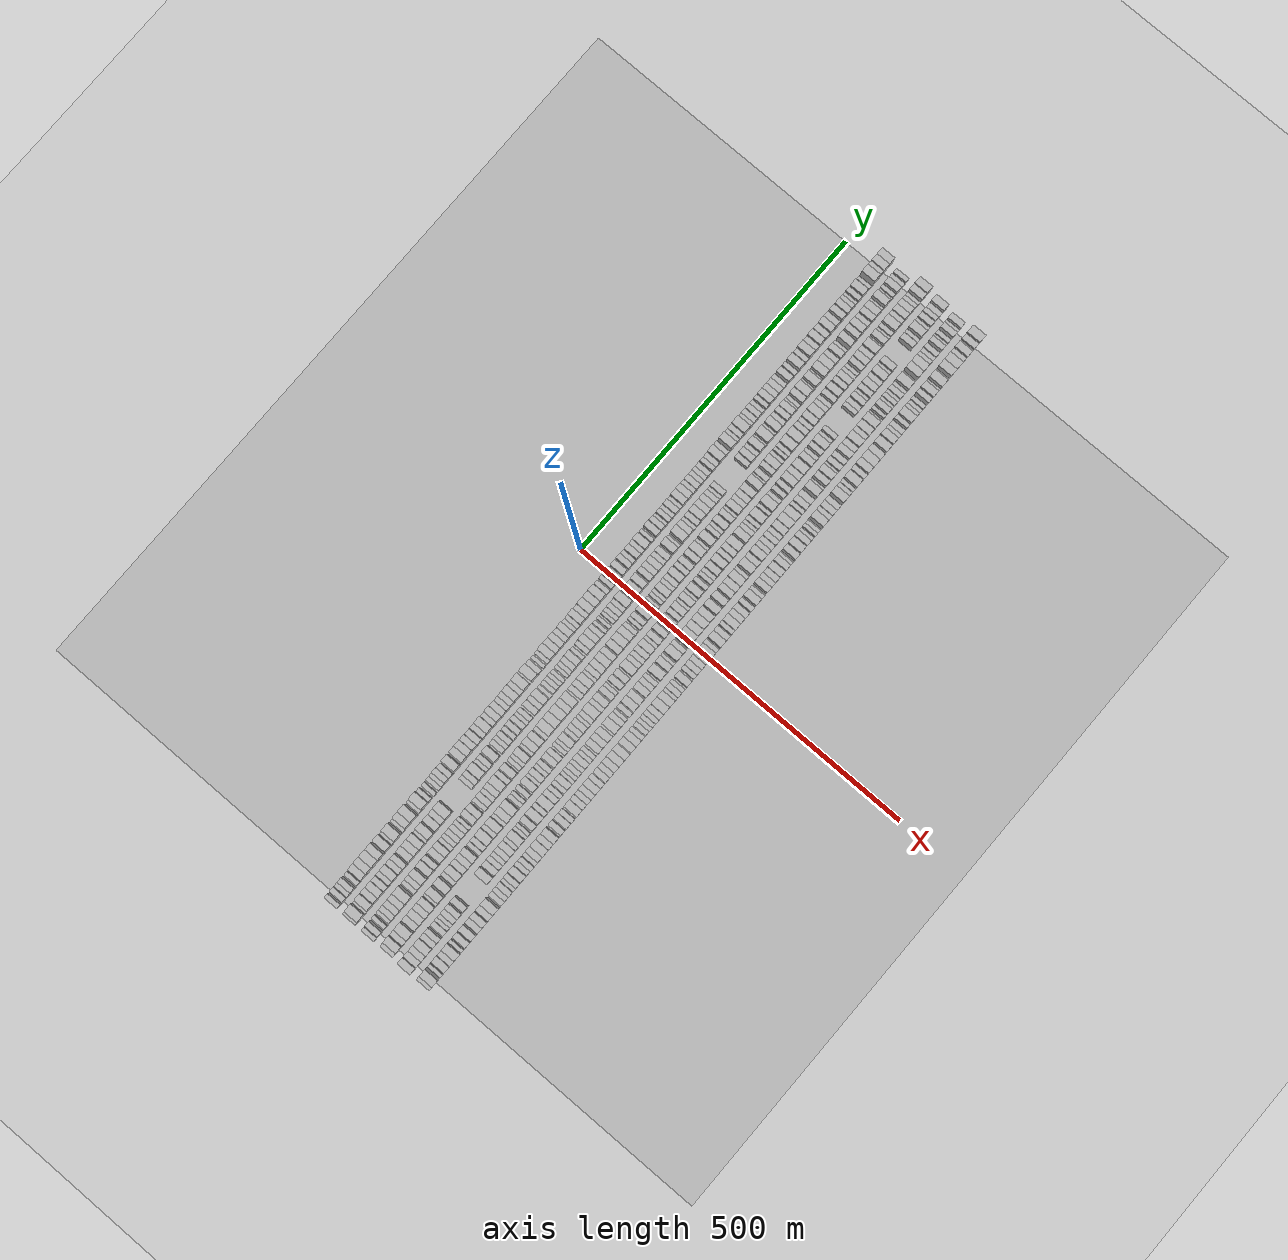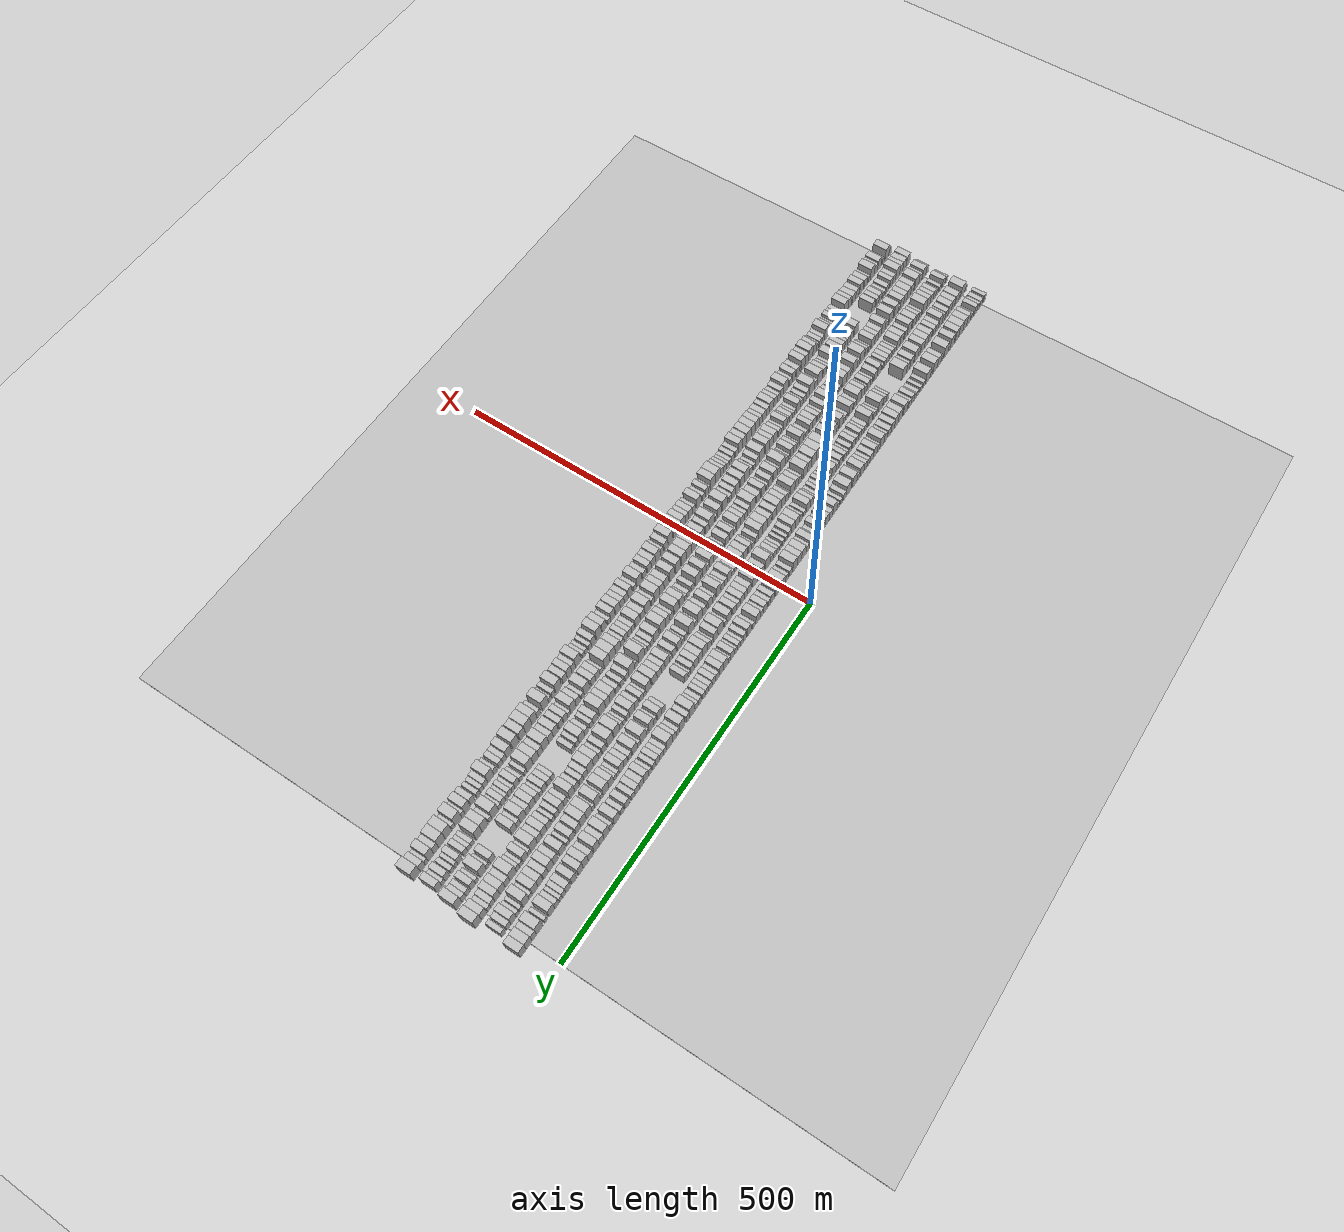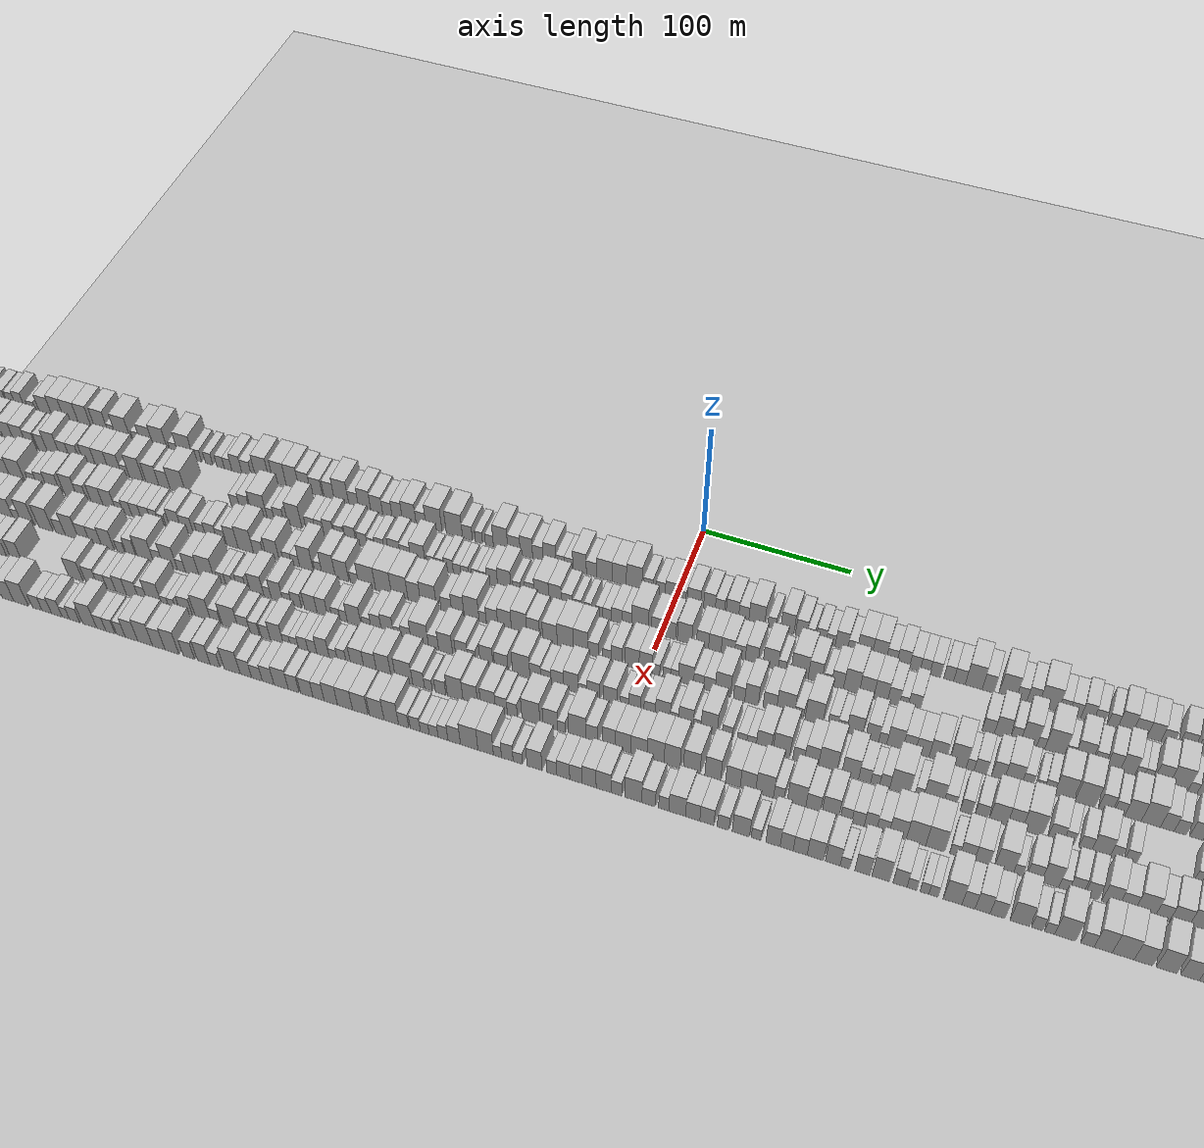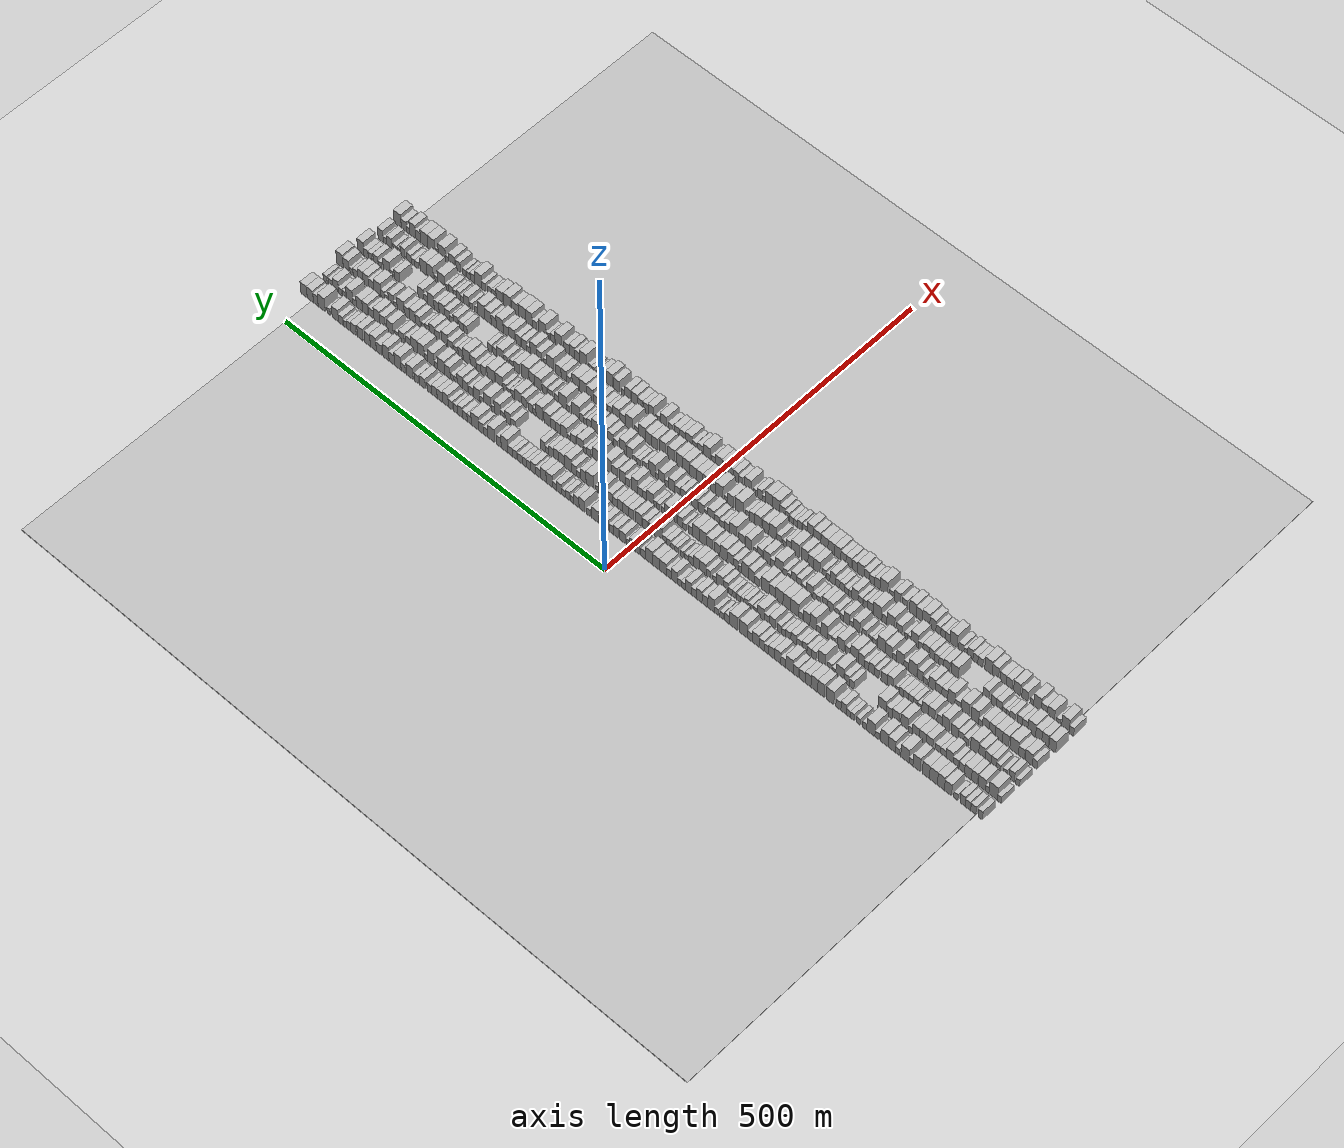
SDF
<?xml version="1.0" encoding="utf-8"?>

<sdf version="1.6">

   <world name="default">

      <gui fullscreen="0">

         <camera name="user_camera">

            <pose>-15 0 4.57585 0 0 0</pose>

            <view_controller>orbit</view_controller>

         </camera>

      </gui>

      <scene>

         <sky>

           <clouds>

             <speed>12</speed>

           </clouds>

         </sky>

         <ambient>0.4 0.4 0.4 1</ambient>

         <background>0.7 0.7 0.7 1</background>

         <shadows>1</shadows>

      </scene>

      <gravity>0 0 -9.8066</gravity>

      <magnetic_field>6e-06 2.3e-05 -4.2e-05</magnetic_field>

      <physics default="0" name="default_physics" type="ode">

         <ode>

            <solver>

               <type>quick</type>

               <iters>10</iters>

               <sor>1.0</sor>

               <use_dynamic_moi_rescaling>0</use_dynamic_moi_rescaling>

            </solver>

            <constraints>

               <cfm>0</cfm>

               <erp>0.2</erp>

               <contact_max_correcting_vel>100</contact_max_correcting_vel>

               <contact_surface_layer>0.001</contact_surface_layer>

            </constraints>

         </ode>

         <max_step_size>0.004</max_step_size>

         <real_time_factor>1</real_time_factor>

         <real_time_update_rate>250</real_time_update_rate>

      </physics>

      <light name="sun" type="directional">

         <cast_shadows>1</cast_shadows>

         <pose>0 0 10 0 0 0</pose>

         <diffuse>0.8 0.8 0.8 1</diffuse>

         <specular>0.2 0.2 0.2 1</specular>

         <attenuation>

            <range>1000</range>

            <constant>0.9</constant>

            <linear>0.01</linear>

            <quadratic>0.001</quadratic>

         </attenuation>

         <direction>-0.5 0.1 -0.9</direction>

      </light>

      <include>

         <name>ground_plane_1</name>

         <uri>model://HANNAS_ground_plane</uri>

         <pose>0 0 0  0 0 0</pose>

      </include>

      <include>

         <name>ground_plane_2</name>

         <uri>model://HANNAS_ground_plane</uri>

         <pose>100 0 0  0 0 0</pose>

      </include>

      <model name="building_1">

         <static>1</static>

         <pose frame="">50.0000 -505.8963 0 0.000000 0.000000 0.000000</pose>

         <link name="link">

            <pose frame="">0 0 7.50 0 0 0</pose>

            <collision name="collision">

               <geometry>

                  <box>

                     <size>20.0000 6.2074 15.0000</size>

                  </box>

               </geometry>

               <max_contacts>10</max_contacts>

               <surface>

                  <contact>

                     <ode/>

                  </contact>

                  <bounce/>

                  <friction>

                     <torsional>

                        <ode/>

                     </torsional>

                     <ode/>

                  </friction>

               </surface>

            </collision>

            <visual name="visual">

               <cast_shadows>0</cast_shadows>

               <geometry>

                  <box>

                     <size>20.0000 6.2074 15.0000</size>

                  </box>

               </geometry>

               <material>

                  <script>

                     <uri>model://HANNAS_wall/materials/scripts</uri>

                     <uri>model://HANNAS_wall/materials/textures</uri>

                     <name>vrc/HANNAS_wall</name>

                  </script>

               </material>

            </visual>

            <self_collide>0</self_collide>

            <enable_wind>0</enable_wind>

            <kinematic>0</kinematic>

         </link>

      </model>

      <model name="building_2">

         <static>1</static>

         <pose frame="">50.0000 -496.2147 0 0.000000 0.000000 0.000000</pose>

         <link name="link">

            <pose frame="">0 0 7.50 0 0 0</pose>

            <collision name="collision">

               <geometry>

                  <box>

                     <size>20.0000 7.1558 15.0000</size>

                  </box>

               </geometry>

               <max_contacts>10</max_contacts>

               <surface>

                  <contact>

                     <ode/>

                  </contact>

                  <bounce/>

                  <friction>

                     <torsional>

                        <ode/>

                     </torsional>

                     <ode/>

                  </friction>

               </surface>

            </collision>

            <visual name="visual">

               <cast_shadows>0</cast_shadows>

               <geometry>

                  <box>

                     <size>20.0000 7.1558 15.0000</size>

                  </box>

               </geometry>

               <material>

                  <script>

                     <uri>model://HANNAS_wall/materials/scripts</uri>

                     <uri>model://HANNAS_wall/materials/textures</uri>

                     <name>vrc/HANNAS_wall</name>

                  </script>

               </material>

            </visual>

            <self_collide>0</self_collide>

            <enable_wind>0</enable_wind>

            <kinematic>0</kinematic>

         </link>

      </model>

      <model name="building_3">

         <static>1</static>

         <pose frame="">50.0000 -488.3676 0 0.000000 0.000000 0.000000</pose>

         <link name="link">

            <pose frame="">0 0 7.50 0 0 0</pose>

            <collision name="collision">

               <geometry>

                  <box>

                     <size>20.0000 6.5385 15.0000</size>

                  </box>

               </geometry>

               <max_contacts>10</max_contacts>

               <surface>

                  <contact>

                     <ode/>

                  </contact>

                  <bounce/>

                  <friction>

                     <torsional>

                        <ode/>

                     </torsional>

                     <ode/>

                  </friction>

               </surface>

            </collision>

            <visual name="visual">

               <cast_shadows>0</cast_shadows>

               <geometry>

                  <box>

                     <size>20.0000 6.5385 15.0000</size>

                  </box>

               </geometry>

               <material>

                  <script>

                     <uri>model://HANNAS_wall/materials/scripts</uri>

                     <uri>model://HANNAS_wall/materials/textures</uri>

                     <name>vrc/HANNAS_wall</name>

                  </script>

               </material>

            </visual>

            <self_collide>0</self_collide>

            <enable_wind>0</enable_wind>

            <kinematic>0</kinematic>

         </link>

      </model>

      <model name="building_4">

         <static>1</static>

         <pose frame="">50.0000 -481.3942 0 0.000000 0.000000 0.000000</pose>

         <link name="link">

            <pose frame="">0 0 9.00 0 0 0</pose>

            <collision name="collision">

               <geometry>

                  <box>

                     <size>20.0000 7.4084 18.0000</size>

                  </box>

               </geometry>

               <max_contacts>10</max_contacts>

               <surface>

                  <contact>

                     <ode/>

                  </contact>

                  <bounce/>

                  <friction>

                     <torsional>

                        <ode/>

                     </torsional>

                     <ode/>

                  </friction>

               </surface>

            </collision>

            <visual name="visual">

               <cast_shadows>0</cast_shadows>

               <geometry>

                  <box>

                     <size>20.0000 7.4084 18.0000</size>

                  </box>

               </geometry>

               <material>

                  <script>

                     <uri>model://HANNAS_wall/materials/scripts</uri>

                     <uri>model://HANNAS_wall/materials/textures</uri>

                     <name>vrc/HANNAS_wall</name>

                  </script>

               </material>

            </visual>

            <self_collide>0</self_collide>

            <enable_wind>0</enable_wind>

            <kinematic>0</kinematic>

         </link>

      </model>

      <model name="building_5">

         <static>1</static>

         <pose frame="">50.0000 -471.7750 0 0.000000 0.000000 0.000000</pose>

         <link name="link">

            <pose frame="">0 0 6.00 0 0 0</pose>

            <collision name="collision">

               <geometry>

                  <box>

                     <size>20.0000 5.8300 12.0000</size>

                  </box>

               </geometry>

               <max_contacts>10</max_contacts>

               <surface>

                  <contact>

                     <ode/>

                  </contact>

                  <bounce/>

                  <friction>

                     <torsional>

                        <ode/>

                     </torsional>

                     <ode/>

                  </friction>

               </surface>

            </collision>

            <visual name="visual">

               <cast_shadows>0</cast_shadows>

               <geometry>

                  <box>

                     <size>20.0000 5.8300 12.0000</size>

                  </box>

               </geometry>

               <material>

                  <script>

                     <uri>model://HANNAS_wall/materials/scripts</uri>

                     <uri>model://HANNAS_wall/materials/textures</uri>

                     <name>vrc/HANNAS_wall</name>

                  </script>

               </material>

            </visual>

            <self_collide>0</self_collide>

            <enable_wind>0</enable_wind>

            <kinematic>0</kinematic>

         </link>

      </model>

      <model name="building_6">

         <static>1</static>

         <pose frame="">50.0000 -460.8739 0 0.000000 0.000000 0.000000</pose>

         <link name="link">

            <pose frame="">0 0 10.50 0 0 0</pose>

            <collision name="collision">

               <geometry>

                  <box>

                     <size>20.0000 9.9722 21.0000</size>

                  </box>

               </geometry>

               <max_contacts>10</max_contacts>

               <surface>

                  <contact>

                     <ode/>

                  </contact>

                  <bounce/>

                  <friction>

                     <torsional>

                        <ode/>

                     </torsional>

                     <ode/>

                  </friction>

               </surface>

            </collision>

            <visual name="visual">

               <cast_shadows>0</cast_shadows>

               <geometry>

                  <box>

                     <size>20.0000 9.9722 21.0000</size>

                  </box>

               </geometry>

               <material>

                  <script>

                     <uri>model://HANNAS_wall/materials/scripts</uri>

                     <uri>model://HANNAS_wall/materials/textures</uri>

                     <name>vrc/HANNAS_wall</name>

                  </script>

               </material>

            </visual>

            <self_collide>0</self_collide>

            <enable_wind>0</enable_wind>

            <kinematic>0</kinematic>

         </link>

      </model>

      <model name="building_7">

         <static>1</static>

         <pose frame="">50.0000 -450.9703 0 0.000000 0.000000 0.000000</pose>

         <link name="link">

            <pose frame="">0 0 12.00 0 0 0</pose>

            <collision name="collision">

               <geometry>

                  <box>

                     <size>20.0000 9.8350 24.0000</size>

                  </box>

               </geometry>

               <max_contacts>10</max_contacts>

               <surface>

                  <contact>

                     <ode/>

                  </contact>

                  <bounce/>

                  <friction>

                     <torsional>

                        <ode/>

                     </torsional>

                     <ode/>

                  </friction>

               </surface>

            </collision>

            <visual name="visual">

               <cast_shadows>0</cast_shadows>

               <geometry>

                  <box>

                     <size>20.0000 9.8350 24.0000</size>

                  </box>

               </geometry>

               <material>

                  <script>

                     <uri>model://HANNAS_wall/materials/scripts</uri>

                     <uri>model://HANNAS_wall/materials/textures</uri>

                     <name>vrc/HANNAS_wall</name>

                  </script>

               </material>

            </visual>

            <self_collide>0</self_collide>

            <enable_wind>0</enable_wind>

            <kinematic>0</kinematic>

         </link>

      </model>

      <model name="building_8">

         <static>1</static>

         <pose frame="">50.0000 -440.3753 0 0.000000 0.000000 0.000000</pose>

         <link name="link">

            <pose frame="">0 0 12.00 0 0 0</pose>

            <collision name="collision">

               <geometry>

                  <box>

                     <size>20.0000 11.3550 24.0000</size>

                  </box>

               </geometry>

               <max_contacts>10</max_contacts>

               <surface>

                  <contact>

                     <ode/>

                  </contact>

                  <bounce/>

                  <friction>

                     <torsional>

                        <ode/>

                     </torsional>

                     <ode/>

                  </friction>

               </surface>

            </collision>

            <visual name="visual">

               <cast_shadows>0</cast_shadows>

               <geometry>

                  <box>

                     <size>20.0000 11.3550 24.0000</size>

                  </box>

               </geometry>

               <material>

                  <script>

                     <uri>model://HANNAS_wall/materials/scripts</uri>

                     <uri>model://HANNAS_wall/materials/textures</uri>

                     <name>vrc/HANNAS_wall</name>

                  </script>

               </material>

            </visual>

            <self_collide>0</self_collide>

            <enable_wind>0</enable_wind>

            <kinematic>0</kinematic>

         </link>

      </model>

      <model name="building_9">

         <static>1</static>

         <pose frame="">50.0000 -429.7503 0 0.000000 0.000000 0.000000</pose>

         <link name="link">

            <pose frame="">0 0 12.00 0 0 0</pose>

            <collision name="collision">

               <geometry>

                  <box>

                     <size>20.0000 9.8951 24.0000</size>

                  </box>

               </geometry>

               <max_contacts>10</max_contacts>

               <surface>

                  <contact>

                     <ode/>

                  </contact>

                  <bounce/>

                  <friction>

                     <torsional>

                        <ode/>

                     </torsional>

                     <ode/>

                  </friction>

               </surface>

            </collision>

            <visual name="visual">

               <cast_shadows>0</cast_shadows>

               <geometry>

                  <box>

                     <size>20.0000 9.8951 24.0000</size>

                  </box>

               </geometry>

               <material>

                  <script>

                     <uri>model://HANNAS_wall/materials/scripts</uri>

                     <uri>model://HANNAS_wall/materials/textures</uri>

                     <name>vrc/HANNAS_wall</name>

                  </script>

               </material>

            </visual>

            <self_collide>0</self_collide>

            <enable_wind>0</enable_wind>

            <kinematic>0</kinematic>

         </link>

      </model>

      <model name="building_10">

         <static>1</static>

         <pose frame="">50.0000 -416.6631 0 0.000000 0.000000 0.000000</pose>

         <link name="link">

            <pose frame="">0 0 12.00 0 0 0</pose>

            <collision name="collision">

               <geometry>

                  <box>

                     <size>20.0000 10.2793 24.0000</size>

                  </box>

               </geometry>

               <max_contacts>10</max_contacts>

               <surface>

                  <contact>

                     <ode/>

                  </contact>

                  <bounce/>

                  <friction>

                     <torsional>

                        <ode/>

                     </torsional>

                     <ode/>

                  </friction>

               </surface>

            </collision>

            <visual name="visual">

               <cast_shadows>0</cast_shadows>

               <geometry>

                  <box>

                     <size>20.0000 10.2793 24.0000</size>

                  </box>

               </geometry>

               <material>

                  <script>

                     <uri>model://HANNAS_wall/materials/scripts</uri>

                     <uri>model://HANNAS_wall/materials/textures</uri>

                     <name>vrc/HANNAS_wall</name>

                  </script>

               </material>

            </visual>

            <self_collide>0</self_collide>

            <enable_wind>0</enable_wind>

            <kinematic>0</kinematic>

         </link>

      </model>

      <model name="building_11">

         <static>1</static>

         <pose frame="">50.0000 -408.7745 0 0.000000 0.000000 0.000000</pose>

         <link name="link">

            <pose frame="">0 0 6.00 0 0 0</pose>

            <collision name="collision">

               <geometry>

                  <box>

                     <size>20.0000 5.4980 12.0000</size>

                  </box>

               </geometry>

               <max_contacts>10</max_contacts>

               <surface>

                  <contact>

                     <ode/>

                  </contact>

                  <bounce/>

                  <friction>

                     <torsional>

                        <ode/>

                     </torsional>

                     <ode/>

                  </friction>

               </surface>

            </collision>

            <visual name="visual">

               <cast_shadows>0</cast_shadows>

               <geometry>

                  <box>

                     <size>20.0000 5.4980 12.0000</size>

                  </box>

               </geometry>

               <material>

                  <script>

                     <uri>model://HANNAS_wall/materials/scripts</uri>

                     <uri>model://HANNAS_wall/materials/textures</uri>

                     <name>vrc/HANNAS_wall</name>

                  </script>

               </material>

            </visual>

            <self_collide>0</self_collide>

            <enable_wind>0</enable_wind>

            <kinematic>0</kinematic>

         </link>

      </model>

      <model name="building_12">

         <static>1</static>

         <pose frame="">50.0000 -400.1555 0 0.000000 0.000000 0.000000</pose>

         <link name="link">

            <pose frame="">0 0 12.00 0 0 0</pose>

            <collision name="collision">

               <geometry>

                  <box>

                     <size>20.0000 11.7400 24.0000</size>

                  </box>

               </geometry>

               <max_contacts>10</max_contacts>

               <surface>

                  <contact>

                     <ode/>

                  </contact>

                  <bounce/>

                  <friction>

                     <torsional>

                        <ode/>

                     </torsional>

                     <ode/>

                  </friction>

               </surface>

            </collision>

            <visual name="visual">

               <cast_shadows>0</cast_shadows>

               <geometry>

                  <box>

                     <size>20.0000 11.7400 24.0000</size>

                  </box>

               </geometry>

               <material>

                  <script>

                     <uri>model://HANNAS_wall/materials/scripts</uri>

                     <uri>model://HANNAS_wall/materials/textures</uri>

                     <name>vrc/HANNAS_wall</name>

                  </script>

               </material>

            </visual>

            <self_collide>0</self_collide>

            <enable_wind>0</enable_wind>

            <kinematic>0</kinematic>

         </link>

      </model>

      <model name="building_13">

         <static>1</static>

         <pose frame="">50.0000 -389.4840 0 0.000000 0.000000 0.000000</pose>

         <link name="link">

            <pose frame="">0 0 6.00 0 0 0</pose>

            <collision name="collision">

               <geometry>

                  <box>

                     <size>20.0000 5.6029 12.0000</size>

                  </box>

               </geometry>

               <max_contacts>10</max_contacts>

               <surface>

                  <contact>

                     <ode/>

                  </contact>

                  <bounce/>

                  <friction>

                     <torsional>

                        <ode/>

                     </torsional>

                     <ode/>

                  </friction>

               </surface>

            </collision>

            <visual name="visual">

               <cast_shadows>0</cast_shadows>

               <geometry>

                  <box>

                     <size>20.0000 5.6029 12.0000</size>

                  </box>

               </geometry>

               <material>

                  <script>

                     <uri>model://HANNAS_wall/materials/scripts</uri>

                     <uri>model://HANNAS_wall/materials/textures</uri>

                     <name>vrc/HANNAS_wall</name>

                  </script>

               </material>

            </visual>

            <self_collide>0</self_collide>

            <enable_wind>0</enable_wind>

            <kinematic>0</kinematic>

         </link>

      </model>

      <model name="building_14">

         <static>1</static>

         <pose frame="">50.0000 -381.6744 0 0.000000 0.000000 0.000000</pose>

         <link name="link">

            <pose frame="">0 0 10.50 0 0 0</pose>

            <collision name="collision">

               <geometry>

                  <box>

                     <size>20.0000 10.0163 21.0000</size>

                  </box>

               </geometry>

               <max_contacts>10</max_contacts>

               <surface>

                  <contact>

                     <ode/>

                  </contact>

                  <bounce/>

                  <friction>

                     <torsional>

                        <ode/>

                     </torsional>

                     <ode/>

                  </friction>

               </surface>

            </collision>

            <visual name="visual">

               <cast_shadows>0</cast_shadows>

               <geometry>

                  <box>

                     <size>20.0000 10.0163 21.0000</size>

                  </box>

               </geometry>

               <material>

                  <script>

                     <uri>model://HANNAS_wall/materials/scripts</uri>

                     <uri>model://HANNAS_wall/materials/textures</uri>

                     <name>vrc/HANNAS_wall</name>

                  </script>

               </material>

            </visual>

            <self_collide>0</self_collide>

            <enable_wind>0</enable_wind>

            <kinematic>0</kinematic>

         </link>

      </model>

      <model name="building_15">

         <static>1</static>

         <pose frame="">50.0000 -371.0635 0 0.000000 0.000000 0.000000</pose>

         <link name="link">

            <pose frame="">0 0 12.00 0 0 0</pose>

            <collision name="collision">

               <geometry>

                  <box>

                     <size>20.0000 11.2055 24.0000</size>

                  </box>

               </geometry>

               <max_contacts>10</max_contacts>

               <surface>

                  <contact>

                     <ode/>

                  </contact>

                  <bounce/>

                  <friction>

                     <torsional>

                        <ode/>

                     </torsional>

                     <ode/>

                  </friction>

               </surface>

            </collision>

            <visual name="visual">

               <cast_shadows>0</cast_shadows>

               <geometry>

                  <box>

                     <size>20.0000 11.2055 24.0000</size>

                  </box>

               </geometry>

               <material>

                  <script>

                     <uri>model://HANNAS_wall/materials/scripts</uri>

                     <uri>model://HANNAS_wall/materials/textures</uri>

                     <name>vrc/HANNAS_wall</name>

                  </script>

               </material>

            </visual>

            <self_collide>0</self_collide>

            <enable_wind>0</enable_wind>

            <kinematic>0</kinematic>

         </link>

      </model>

      <model name="building_16">

         <static>1</static>

         <pose frame="">50.0000 -360.5090 0 0.000000 0.000000 0.000000</pose>

         <link name="link">

            <pose frame="">0 0 6.00 0 0 0</pose>

            <collision name="collision">

               <geometry>

                  <box>

                     <size>20.0000 5.9036 12.0000</size>

                  </box>

               </geometry>

               <max_contacts>10</max_contacts>

               <surface>

                  <contact>

                     <ode/>

                  </contact>

                  <bounce/>

                  <friction>

                     <torsional>

                        <ode/>

                     </torsional>

                     <ode/>

                  </friction>

               </surface>

            </collision>

            <visual name="visual">

               <cast_shadows>0</cast_shadows>

               <geometry>

                  <box>

                     <size>20.0000 5.9036 12.0000</size>

                  </box>

               </geometry>

               <material>

                  <script>

                     <uri>model://HANNAS_wall/materials/scripts</uri>

                     <uri>model://HANNAS_wall/materials/textures</uri>

                     <name>vrc/HANNAS_wall</name>

                  </script>

               </material>

            </visual>

            <self_collide>0</self_collide>

            <enable_wind>0</enable_wind>

            <kinematic>0</kinematic>

         </link>

      </model>

      <model name="building_17">

         <static>1</static>

         <pose frame="">50.0000 -351.6939 0 0.000000 0.000000 0.000000</pose>

         <link name="link">

            <pose frame="">0 0 12.00 0 0 0</pose>

            <collision name="collision">

               <geometry>

                  <box>

                     <size>20.0000 11.7266 24.0000</size>

                  </box>

               </geometry>

               <max_contacts>10</max_contacts>

               <surface>

                  <contact>

                     <ode/>

                  </contact>

                  <bounce/>

                  <friction>

                     <torsional>

                        <ode/>

                     </torsional>

                     <ode/>

                  </friction>

               </surface>

            </collision>

            <visual name="visual">

               <cast_shadows>0</cast_shadows>

               <geometry>

                  <box>

                     <size>20.0000 11.7266 24.0000</size>

                  </box>

               </geometry>

               <material>

                  <script>

                     <uri>model://HANNAS_wall/materials/scripts</uri>

                     <uri>model://HANNAS_wall/materials/textures</uri>

                     <name>vrc/HANNAS_wall</name>

                  </script>

               </material>

            </visual>

            <self_collide>0</self_collide>

            <enable_wind>0</enable_wind>

            <kinematic>0</kinematic>

         </link>

      </model>

      <model name="building_18">

         <static>1</static>

         <pose frame="">50.0000 -342.8308 0 0.000000 0.000000 0.000000</pose>

         <link name="link">

            <pose frame="">0 0 6.00 0 0 0</pose>

            <collision name="collision">

               <geometry>

                  <box>

                     <size>20.0000 5.9994 12.0000</size>

                  </box>

               </geometry>

               <max_contacts>10</max_contacts>

               <surface>

                  <contact>

                     <ode/>

                  </contact>

                  <bounce/>

                  <friction>

                     <torsional>

                        <ode/>

                     </torsional>

                     <ode/>

                  </friction>

               </surface>

            </collision>

            <visual name="visual">

               <cast_shadows>0</cast_shadows>

               <geometry>

                  <box>

                     <size>20.0000 5.9994 12.0000</size>

                  </box>

               </geometry>

               <material>

                  <script>

                     <uri>model://HANNAS_wall/materials/scripts</uri>

                     <uri>model://HANNAS_wall/materials/textures</uri>

                     <name>vrc/HANNAS_wall</name>

                  </script>

               </material>

            </visual>

            <self_collide>0</self_collide>

            <enable_wind>0</enable_wind>

            <kinematic>0</kinematic>

         </link>

      </model>

      <model name="building_19">

         <static>1</static>

         <pose frame="">50.0000 -333.9997 0 0.000000 0.000000 0.000000</pose>

         <link name="link">

            <pose frame="">0 0 6.00 0 0 0</pose>

            <collision name="collision">

               <geometry>

                  <box>

                     <size>20.0000 5.6628 12.0000</size>

                  </box>

               </geometry>

               <max_contacts>10</max_contacts>

               <surface>

                  <contact>

                     <ode/>

                  </contact>

                  <bounce/>

                  <friction>

                     <torsional>

                        <ode/>

                     </torsional>

                     <ode/>

                  </friction>

               </surface>

            </collision>

            <visual name="visual">

               <cast_shadows>0</cast_shadows>

               <geometry>

                  <box>

                     <size>20.0000 5.6628 12.0000</size>

                  </box>

               </geometry>

               <material>

                  <script>

                     <uri>model://HANNAS_wall/materials/scripts</uri>

                     <uri>model://HANNAS_wall/materials/textures</uri>

                     <name>vrc/HANNAS_wall</name>

                  </script>

               </material>

            </visual>

            <self_collide>0</self_collide>

            <enable_wind>0</enable_wind>

            <kinematic>0</kinematic>

         </link>

      </model>

      <model name="building_20">

         <static>1</static>

         <pose frame="">50.0000 -325.2861 0 0.000000 0.000000 0.000000</pose>

         <link name="link">

            <pose frame="">0 0 6.00 0 0 0</pose>

            <collision name="collision">

               <geometry>

                  <box>

                     <size>20.0000 5.7645 12.0000</size>

                  </box>

               </geometry>

               <max_contacts>10</max_contacts>

               <surface>

                  <contact>

                     <ode/>

                  </contact>

                  <bounce/>

                  <friction>

                     <torsional>

                        <ode/>

                     </torsional>

                     <ode/>

                  </friction>

               </surface>

            </collision>

            <visual name="visual">

               <cast_shadows>0</cast_shadows>

               <geometry>

                  <box>

                     <size>20.0000 5.7645 12.0000</size>

                  </box>

               </geometry>

               <material>

                  <script>

                     <uri>model://HANNAS_wall/materials/scripts</uri>

                     <uri>model://HANNAS_wall/materials/textures</uri>

                     <name>vrc/HANNAS_wall</name>

                  </script>

               </material>

            </visual>

            <self_collide>0</self_collide>

            <enable_wind>0</enable_wind>

            <kinematic>0</kinematic>

         </link>

      </model>

      <model name="building_21">

         <static>1</static>

         <pose frame="">50.0000 -319.4922 0 0.000000 0.000000 0.000000</pose>

         <link name="link">

            <pose frame="">0 0 6.00 0 0 0</pose>

            <collision name="collision">

               <geometry>

                  <box>

                     <size>20.0000 5.8233 12.0000</size>

                  </box>

               </geometry>

               <max_contacts>10</max_contacts>

               <surface>

                  <contact>

                     <ode/>

                  </contact>

                  <bounce/>

                  <friction>

                     <torsional>

                        <ode/>

                     </torsional>

                     <ode/>

                  </friction>

               </surface>

            </collision>

            <visual name="visual">

               <cast_shadows>0</cast_shadows>

               <geometry>

                  <box>

                     <size>20.0000 5.8233 12.0000</size>

                  </box>

               </geometry>

               <material>

                  <script>

                     <uri>model://HANNAS_wall/materials/scripts</uri>

                     <uri>model://HANNAS_wall/materials/textures</uri>

                     <name>vrc/HANNAS_wall</name>

                  </script>

               </material>

            </visual>

            <self_collide>0</self_collide>

            <enable_wind>0</enable_wind>

            <kinematic>0</kinematic>

         </link>

      </model>

      <model name="building_22">

         <static>1</static>

         <pose frame="">50.0000 -312.7678 0 0.000000 0.000000 0.000000</pose>

         <link name="link">

            <pose frame="">0 0 9.00 0 0 0</pose>

            <collision name="collision">

               <geometry>

                  <box>

                     <size>20.0000 7.6255 18.0000</size>

                  </box>

               </geometry>

               <max_contacts>10</max_contacts>

               <surface>

                  <contact>

                     <ode/>

                  </contact>

                  <bounce/>

                  <friction>

                     <torsional>

                        <ode/>

                     </torsional>

                     <ode/>

                  </friction>

               </surface>

            </collision>

            <visual name="visual">

               <cast_shadows>0</cast_shadows>

               <geometry>

                  <box>

                     <size>20.0000 7.6255 18.0000</size>

                  </box>

               </geometry>

               <material>

                  <script>

                     <uri>model://HANNAS_wall/materials/scripts</uri>

                     <uri>model://HANNAS_wall/materials/textures</uri>

                     <name>vrc/HANNAS_wall</name>

                  </script>

               </material>

            </visual>

            <self_collide>0</self_collide>

            <enable_wind>0</enable_wind>

            <kinematic>0</kinematic>

         </link>

      </model>

      <model name="building_23">

         <static>1</static>

         <pose frame="">50.0000 -305.3395 0 0.000000 0.000000 0.000000</pose>

         <link name="link">

            <pose frame="">0 0 7.50 0 0 0</pose>

            <collision name="collision">

               <geometry>

                  <box>

                     <size>20.0000 7.2312 15.0000</size>

                  </box>

               </geometry>

               <max_contacts>10</max_contacts>

               <surface>

                  <contact>

                     <ode/>

                  </contact>

                  <bounce/>

                  <friction>

                     <torsional>

                        <ode/>

                     </torsional>

                     <ode/>

                  </friction>

               </surface>

            </collision>

            <visual name="visual">

               <cast_shadows>0</cast_shadows>

               <geometry>

                  <box>

                     <size>20.0000 7.2312 15.0000</size>

                  </box>

               </geometry>

               <material>

                  <script>

                     <uri>model://HANNAS_wall/materials/scripts</uri>

                     <uri>model://HANNAS_wall/materials/textures</uri>

                     <name>vrc/HANNAS_wall</name>

                  </script>

               </material>

            </visual>

            <self_collide>0</self_collide>

            <enable_wind>0</enable_wind>

            <kinematic>0</kinematic>

         </link>

      </model>

      <model name="building_24">

         <static>1</static>

         <pose frame="">50.0000 -293.4313 0 0.000000 0.000000 0.000000</pose>

         <link name="link">

            <pose frame="">0 0 12.00 0 0 0</pose>

            <collision name="collision">

               <geometry>

                  <box>

                     <size>20.0000 10.5851 24.0000</size>

                  </box>

               </geometry>

               <max_contacts>10</max_contacts>

               <surface>

                  <contact>

                     <ode/>

                  </contact>

                  <bounce/>

                  <friction>

                     <torsional>

                        <ode/>

                     </torsional>

                     <ode/>

                  </friction>

               </surface>

            </collision>

            <visual name="visual">

               <cast_shadows>0</cast_shadows>

               <geometry>

                  <box>

                     <size>20.0000 10.5851 24.0000</size>

                  </box>

               </geometry>

               <material>

                  <script>

                     <uri>model://HANNAS_wall/materials/scripts</uri>

                     <uri>model://HANNAS_wall/materials/textures</uri>

                     <name>vrc/HANNAS_wall</name>

                  </script>

               </material>

            </visual>

            <self_collide>0</self_collide>

            <enable_wind>0</enable_wind>

            <kinematic>0</kinematic>

         </link>

      </model>

      <model name="building_25">

         <static>1</static>

         <pose frame="">50.0000 -280.2940 0 0.000000 0.000000 0.000000</pose>

         <link name="link">

            <pose frame="">0 0 12.00 0 0 0</pose>

            <collision name="collision">

               <geometry>

                  <box>

                     <size>20.0000 9.6894 24.0000</size>

                  </box>

               </geometry>

               <max_contacts>10</max_contacts>

               <surface>

                  <contact>

                     <ode/>

                  </contact>

                  <bounce/>

                  <friction>

                     <torsional>

                        <ode/>

                     </torsional>

                     <ode/>

                  </friction>

               </surface>

            </collision>

            <visual name="visual">

               <cast_shadows>0</cast_shadows>

               <geometry>

                  <box>

                     <size>20.0000 9.6894 24.0000</size>

                  </box>

               </geometry>

               <material>

                  <script>

                     <uri>model://HANNAS_wall/materials/scripts</uri>

                     <uri>model://HANNAS_wall/materials/textures</uri>

                     <name>vrc/HANNAS_wall</name>

                  </script>

               </material>

            </visual>

            <self_collide>0</self_collide>

            <enable_wind>0</enable_wind>

            <kinematic>0</kinematic>

         </link>

      </model>

      <model name="building_26">

         <static>1</static>

         <pose frame="">50.0000 -270.6280 0 0.000000 0.000000 0.000000</pose>

         <link name="link">

            <pose frame="">0 0 12.00 0 0 0</pose>

            <collision name="collision">

               <geometry>

                  <box>

                     <size>20.0000 9.6428 24.0000</size>

                  </box>

               </geometry>

               <max_contacts>10</max_contacts>

               <surface>

                  <contact>

                     <ode/>

                  </contact>

                  <bounce/>

                  <friction>

                     <torsional>

                        <ode/>

                     </torsional>

                     <ode/>

                  </friction>

               </surface>

            </collision>

            <visual name="visual">

               <cast_shadows>0</cast_shadows>

               <geometry>

                  <box>

                     <size>20.0000 9.6428 24.0000</size>

                  </box>

               </geometry>

               <material>

                  <script>

                     <uri>model://HANNAS_wall/materials/scripts</uri>

                     <uri>model://HANNAS_wall/materials/textures</uri>

                     <name>vrc/HANNAS_wall</name>

                  </script>

               </material>

            </visual>

            <self_collide>0</self_collide>

            <enable_wind>0</enable_wind>

            <kinematic>0</kinematic>

         </link>

      </model>

      <model name="building_27">

         <static>1</static>

         <pose frame="">50.0000 -261.5699 0 0.000000 0.000000 0.000000</pose>

         <link name="link">

            <pose frame="">0 0 10.50 0 0 0</pose>

            <collision name="collision">

               <geometry>

                  <box>

                     <size>20.0000 8.4732 21.0000</size>

                  </box>

               </geometry>

               <max_contacts>10</max_contacts>

               <surface>

                  <contact>

                     <ode/>

                  </contact>

                  <bounce/>

                  <friction>

                     <torsional>

                        <ode/>

                     </torsional>

                     <ode/>

                  </friction>

               </surface>

            </collision>

            <visual name="visual">

               <cast_shadows>0</cast_shadows>

               <geometry>

                  <box>

                     <size>20.0000 8.4732 21.0000</size>

                  </box>

               </geometry>

               <material>

                  <script>

                     <uri>model://HANNAS_wall/materials/scripts</uri>

                     <uri>model://HANNAS_wall/materials/textures</uri>

                     <name>vrc/HANNAS_wall</name>

                  </script>

               </material>

            </visual>

            <self_collide>0</self_collide>

            <enable_wind>0</enable_wind>

            <kinematic>0</kinematic>

         </link>

      </model>

      <model name="building_28">

         <static>1</static>

         <pose frame="">50.0000 -252.9379 0 0.000000 0.000000 0.000000</pose>

         <link name="link">

            <pose frame="">0 0 9.00 0 0 0</pose>

            <collision name="collision">

               <geometry>

                  <box>

                     <size>20.0000 8.7908 18.0000</size>

                  </box>

               </geometry>

               <max_contacts>10</max_contacts>

               <surface>

                  <contact>

                     <ode/>

                  </contact>

                  <bounce/>

                  <friction>

                     <torsional>

                        <ode/>

                     </torsional>

                     <ode/>

                  </friction>

               </surface>

            </collision>

            <visual name="visual">

               <cast_shadows>0</cast_shadows>

               <geometry>

                  <box>

                     <size>20.0000 8.7908 18.0000</size>

                  </box>

               </geometry>

               <material>

                  <script>

                     <uri>model://HANNAS_wall/materials/scripts</uri>

                     <uri>model://HANNAS_wall/materials/textures</uri>

                     <name>vrc/HANNAS_wall</name>

                  </script>

               </material>

            </visual>

            <self_collide>0</self_collide>

            <enable_wind>0</enable_wind>

            <kinematic>0</kinematic>

         </link>

      </model>

      <model name="building_29">

         <static>1</static>

         <pose frame="">50.0000 -243.7083 0 0.000000 0.000000 0.000000</pose>

         <link name="link">

            <pose frame="">0 0 9.00 0 0 0</pose>

            <collision name="collision">

               <geometry>

                  <box>

                     <size>20.0000 7.6683 18.0000</size>

                  </box>

               </geometry>

               <max_contacts>10</max_contacts>

               <surface>

                  <contact>

                     <ode/>

                  </contact>

                  <bounce/>

                  <friction>

                     <torsional>

                        <ode/>

                     </torsional>

                     <ode/>

                  </friction>

               </surface>

            </collision>

            <visual name="visual">

               <cast_shadows>0</cast_shadows>

               <geometry>

                  <box>

                     <size>20.0000 7.6683 18.0000</size>

                  </box>

               </geometry>

               <material>

                  <script>

                     <uri>model://HANNAS_wall/materials/scripts</uri>

                     <uri>model://HANNAS_wall/materials/textures</uri>

                     <name>vrc/HANNAS_wall</name>

                  </script>

               </material>

            </visual>

            <self_collide>0</self_collide>

            <enable_wind>0</enable_wind>

            <kinematic>0</kinematic>

         </link>

      </model>

      <model name="building_30">

         <static>1</static>

         <pose frame="">50.0000 -234.5510 0 0.000000 0.000000 0.000000</pose>

         <link name="link">

            <pose frame="">0 0 12.00 0 0 0</pose>

            <collision name="collision">

               <geometry>

                  <box>

                     <size>20.0000 10.6463 24.0000</size>

                  </box>

               </geometry>

               <max_contacts>10</max_contacts>

               <surface>

                  <contact>

                     <ode/>

                  </contact>

                  <bounce/>

                  <friction>

                     <torsional>

                        <ode/>

                     </torsional>

                     <ode/>

                  </friction>

               </surface>

            </collision>

            <visual name="visual">

               <cast_shadows>0</cast_shadows>

               <geometry>

                  <box>

                     <size>20.0000 10.6463 24.0000</size>

                  </box>

               </geometry>

               <material>

                  <script>

                     <uri>model://HANNAS_wall/materials/scripts</uri>

                     <uri>model://HANNAS_wall/materials/textures</uri>

                     <name>vrc/HANNAS_wall</name>

                  </script>

               </material>

            </visual>

            <self_collide>0</self_collide>

            <enable_wind>0</enable_wind>

            <kinematic>0</kinematic>

         </link>

      </model>

      <model name="building_31">

         <static>1</static>

         <pose frame="">50.0000 -225.6547 0 0.000000 0.000000 0.000000</pose>

         <link name="link">

            <pose frame="">0 0 7.50 0 0 0</pose>

            <collision name="collision">

               <geometry>

                  <box>

                     <size>20.0000 7.1464 15.0000</size>

                  </box>

               </geometry>

               <max_contacts>10</max_contacts>

               <surface>

                  <contact>

                     <ode/>

                  </contact>

                  <bounce/>

                  <friction>

                     <torsional>

                        <ode/>

                     </torsional>

                     <ode/>

                  </friction>

               </surface>

            </collision>

            <visual name="visual">

               <cast_shadows>0</cast_shadows>

               <geometry>

                  <box>

                     <size>20.0000 7.1464 15.0000</size>

                  </box>

               </geometry>

               <material>

                  <script>

                     <uri>model://HANNAS_wall/materials/scripts</uri>

                     <uri>model://HANNAS_wall/materials/textures</uri>

                     <name>vrc/HANNAS_wall</name>

                  </script>

               </material>

            </visual>

            <self_collide>0</self_collide>

            <enable_wind>0</enable_wind>

            <kinematic>0</kinematic>

         </link>

      </model>

      <model name="building_32">

         <static>1</static>

         <pose frame="">50.0000 -217.6011 0 0.000000 0.000000 0.000000</pose>

         <link name="link">

            <pose frame="">0 0 10.50 0 0 0</pose>

            <collision name="collision">

               <geometry>

                  <box>

                     <size>20.0000 8.9608 21.0000</size>

                  </box>

               </geometry>

               <max_contacts>10</max_contacts>

               <surface>

                  <contact>

                     <ode/>

                  </contact>

                  <bounce/>

                  <friction>

                     <torsional>

                        <ode/>

                     </torsional>

                     <ode/>

                  </friction>

               </surface>

            </collision>

            <visual name="visual">

               <cast_shadows>0</cast_shadows>

               <geometry>

                  <box>

                     <size>20.0000 8.9608 21.0000</size>

                  </box>

               </geometry>

               <material>

                  <script>

                     <uri>model://HANNAS_wall/materials/scripts</uri>

                     <uri>model://HANNAS_wall/materials/textures</uri>

                     <name>vrc/HANNAS_wall</name>

                  </script>

               </material>

            </visual>

            <self_collide>0</self_collide>

            <enable_wind>0</enable_wind>

            <kinematic>0</kinematic>

         </link>

      </model>

      <model name="building_33">

         <static>1</static>

         <pose frame="">50.0000 -208.8000 0 0.000000 0.000000 0.000000</pose>

         <link name="link">

            <pose frame="">0 0 9.00 0 0 0</pose>

            <collision name="collision">

               <geometry>

                  <box>

                     <size>20.0000 8.6415 18.0000</size>

                  </box>

               </geometry>

               <max_contacts>10</max_contacts>

               <surface>

                  <contact>

                     <ode/>

                  </contact>

                  <bounce/>

                  <friction>

                     <torsional>

                        <ode/>

                     </torsional>

                     <ode/>

                  </friction>

               </surface>

            </collision>

            <visual name="visual">

               <cast_shadows>0</cast_shadows>

               <geometry>

                  <box>

                     <size>20.0000 8.6415 18.0000</size>

                  </box>

               </geometry>

               <material>

                  <script>

                     <uri>model://HANNAS_wall/materials/scripts</uri>

                     <uri>model://HANNAS_wall/materials/textures</uri>

                     <name>vrc/HANNAS_wall</name>

                  </script>

               </material>

            </visual>

            <self_collide>0</self_collide>

            <enable_wind>0</enable_wind>

            <kinematic>0</kinematic>

         </link>

      </model>

      <model name="building_34">

         <static>1</static>

         <pose frame="">50.0000 -201.0409 0 0.000000 0.000000 0.000000</pose>

         <link name="link">

            <pose frame="">0 0 7.50 0 0 0</pose>

            <collision name="collision">

               <geometry>

                  <box>

                     <size>20.0000 6.8768 15.0000</size>

                  </box>

               </geometry>

               <max_contacts>10</max_contacts>

               <surface>

                  <contact>

                     <ode/>

                  </contact>

                  <bounce/>

                  <friction>

                     <torsional>

                        <ode/>

                     </torsional>

                     <ode/>

                  </friction>

               </surface>

            </collision>

            <visual name="visual">

               <cast_shadows>0</cast_shadows>

               <geometry>

                  <box>

                     <size>20.0000 6.8768 15.0000</size>

                  </box>

               </geometry>

               <material>

                  <script>

                     <uri>model://HANNAS_wall/materials/scripts</uri>

                     <uri>model://HANNAS_wall/materials/textures</uri>

                     <name>vrc/HANNAS_wall</name>

                  </script>

               </material>

            </visual>

            <self_collide>0</self_collide>

            <enable_wind>0</enable_wind>

            <kinematic>0</kinematic>

         </link>

      </model>

      <model name="building_35">

         <static>1</static>

         <pose frame="">50.0000 -193.9114 0 0.000000 0.000000 0.000000</pose>

         <link name="link">

            <pose frame="">0 0 9.00 0 0 0</pose>

            <collision name="collision">

               <geometry>

                  <box>

                     <size>20.0000 7.3822 18.0000</size>

                  </box>

               </geometry>

               <max_contacts>10</max_contacts>

               <surface>

                  <contact>

                     <ode/>

                  </contact>

                  <bounce/>

                  <friction>

                     <torsional>

                        <ode/>

                     </torsional>

                     <ode/>

                  </friction>

               </surface>

            </collision>

            <visual name="visual">

               <cast_shadows>0</cast_shadows>

               <geometry>

                  <box>

                     <size>20.0000 7.3822 18.0000</size>

                  </box>

               </geometry>

               <material>

                  <script>

                     <uri>model://HANNAS_wall/materials/scripts</uri>

                     <uri>model://HANNAS_wall/materials/textures</uri>

                     <name>vrc/HANNAS_wall</name>

                  </script>

               </material>

            </visual>

            <self_collide>0</self_collide>

            <enable_wind>0</enable_wind>

            <kinematic>0</kinematic>

         </link>

      </model>

      <model name="building_36">

         <static>1</static>

         <pose frame="">50.0000 -185.2671 0 0.000000 0.000000 0.000000</pose>

         <link name="link">

            <pose frame="">0 0 10.50 0 0 0</pose>

            <collision name="collision">

               <geometry>

                  <box>

                     <size>20.0000 9.9062 21.0000</size>

                  </box>

               </geometry>

               <max_contacts>10</max_contacts>

               <surface>

                  <contact>

                     <ode/>

                  </contact>

                  <bounce/>

                  <friction>

                     <torsional>

                        <ode/>

                     </torsional>

                     <ode/>

                  </friction>

               </surface>

            </collision>

            <visual name="visual">

               <cast_shadows>0</cast_shadows>

               <geometry>

                  <box>

                     <size>20.0000 9.9062 21.0000</size>

                  </box>

               </geometry>

               <material>

                  <script>

                     <uri>model://HANNAS_wall/materials/scripts</uri>

                     <uri>model://HANNAS_wall/materials/textures</uri>

                     <name>vrc/HANNAS_wall</name>

                  </script>

               </material>

            </visual>

            <self_collide>0</self_collide>

            <enable_wind>0</enable_wind>

            <kinematic>0</kinematic>

         </link>

      </model>

      <model name="building_37">

         <static>1</static>

         <pose frame="">50.0000 -176.7358 0 0.000000 0.000000 0.000000</pose>

         <link name="link">

            <pose frame="">0 0 7.50 0 0 0</pose>

            <collision name="collision">

               <geometry>

                  <box>

                     <size>20.0000 7.1564 15.0000</size>

                  </box>

               </geometry>

               <max_contacts>10</max_contacts>

               <surface>

                  <contact>

                     <ode/>

                  </contact>

                  <bounce/>

                  <friction>

                     <torsional>

                        <ode/>

                     </torsional>

                     <ode/>

                  </friction>

               </surface>

            </collision>

            <visual name="visual">

               <cast_shadows>0</cast_shadows>

               <geometry>

                  <box>

                     <size>20.0000 7.1564 15.0000</size>

                  </box>

               </geometry>

               <material>

                  <script>

                     <uri>model://HANNAS_wall/materials/scripts</uri>

                     <uri>model://HANNAS_wall/materials/textures</uri>

                     <name>vrc/HANNAS_wall</name>

                  </script>

               </material>

            </visual>

            <self_collide>0</self_collide>

            <enable_wind>0</enable_wind>

            <kinematic>0</kinematic>

         </link>

      </model>

      <model name="building_38">

         <static>1</static>

         <pose frame="">50.0000 -167.4494 0 0.000000 0.000000 0.000000</pose>

         <link name="link">

            <pose frame="">0 0 12.00 0 0 0</pose>

            <collision name="collision">

               <geometry>

                  <box>

                     <size>20.0000 11.4163 24.0000</size>

                  </box>

               </geometry>

               <max_contacts>10</max_contacts>

               <surface>

                  <contact>

                     <ode/>

                  </contact>

                  <bounce/>

                  <friction>

                     <torsional>

                        <ode/>

                     </torsional>

                     <ode/>

                  </friction>

               </surface>

            </collision>

            <visual name="visual">

               <cast_shadows>0</cast_shadows>

               <geometry>

                  <box>

                     <size>20.0000 11.4163 24.0000</size>

                  </box>

               </geometry>

               <material>

                  <script>

                     <uri>model://HANNAS_wall/materials/scripts</uri>

                     <uri>model://HANNAS_wall/materials/textures</uri>

                     <name>vrc/HANNAS_wall</name>

                  </script>

               </material>

            </visual>

            <self_collide>0</self_collide>

            <enable_wind>0</enable_wind>

            <kinematic>0</kinematic>

         </link>

      </model>

      <model name="building_39">

         <static>1</static>

         <pose frame="">50.0000 -152.9241 0 0.000000 0.000000 0.000000</pose>

         <link name="link">

            <pose frame="">0 0 12.00 0 0 0</pose>

            <collision name="collision">

               <geometry>

                  <box>

                     <size>20.0000 11.6345 24.0000</size>

                  </box>

               </geometry>

               <max_contacts>10</max_contacts>

               <surface>

                  <contact>

                     <ode/>

                  </contact>

                  <bounce/>

                  <friction>

                     <torsional>

                        <ode/>

                     </torsional>

                     <ode/>

                  </friction>

               </surface>

            </collision>

            <visual name="visual">

               <cast_shadows>0</cast_shadows>

               <geometry>

                  <box>

                     <size>20.0000 11.6345 24.0000</size>

                  </box>

               </geometry>

               <material>

                  <script>

                     <uri>model://HANNAS_wall/materials/scripts</uri>

                     <uri>model://HANNAS_wall/materials/textures</uri>

                     <name>vrc/HANNAS_wall</name>

                  </script>

               </material>

            </visual>

            <self_collide>0</self_collide>

            <enable_wind>0</enable_wind>

            <kinematic>0</kinematic>

         </link>

      </model>

      <model name="building_40">

         <static>1</static>

         <pose frame="">50.0000 -143.5698 0 0.000000 0.000000 0.000000</pose>

         <link name="link">

            <pose frame="">0 0 7.50 0 0 0</pose>

            <collision name="collision">

               <geometry>

                  <box>

                     <size>20.0000 7.0739 15.0000</size>

                  </box>

               </geometry>

               <max_contacts>10</max_contacts>

               <surface>

                  <contact>

                     <ode/>

                  </contact>

                  <bounce/>

                  <friction>

                     <torsional>

                        <ode/>

                     </torsional>

                     <ode/>

                  </friction>

               </surface>

            </collision>

            <visual name="visual">

               <cast_shadows>0</cast_shadows>

               <geometry>

                  <box>

                     <size>20.0000 7.0739 15.0000</size>

                  </box>

               </geometry>

               <material>

                  <script>

                     <uri>model://HANNAS_wall/materials/scripts</uri>

                     <uri>model://HANNAS_wall/materials/textures</uri>

                     <name>vrc/HANNAS_wall</name>

                  </script>

               </material>

            </visual>

            <self_collide>0</self_collide>

            <enable_wind>0</enable_wind>

            <kinematic>0</kinematic>

         </link>

      </model>

      <model name="building_41">

         <static>1</static>

         <pose frame="">50.0000 -135.4453 0 0.000000 0.000000 0.000000</pose>

         <link name="link">

            <pose frame="">0 0 6.00 0 0 0</pose>

            <collision name="collision">

               <geometry>

                  <box>

                     <size>20.0000 5.1752 12.0000</size>

                  </box>

               </geometry>

               <max_contacts>10</max_contacts>

               <surface>

                  <contact>

                     <ode/>

                  </contact>

                  <bounce/>

                  <friction>

                     <torsional>

                        <ode/>

                     </torsional>

                     <ode/>

                  </friction>

               </surface>

            </collision>

            <visual name="visual">

               <cast_shadows>0</cast_shadows>

               <geometry>

                  <box>

                     <size>20.0000 5.1752 12.0000</size>

                  </box>

               </geometry>

               <material>

                  <script>

                     <uri>model://HANNAS_wall/materials/scripts</uri>

                     <uri>model://HANNAS_wall/materials/textures</uri>

                     <name>vrc/HANNAS_wall</name>

                  </script>

               </material>

            </visual>

            <self_collide>0</self_collide>

            <enable_wind>0</enable_wind>

            <kinematic>0</kinematic>

         </link>

      </model>

      <model name="building_42">

         <static>1</static>

         <pose frame="">50.0000 -128.0100 0 0.000000 0.000000 0.000000</pose>

         <link name="link">

            <pose frame="">0 0 6.00 0 0 0</pose>

            <collision name="collision">

               <geometry>

                  <box>

                     <size>20.0000 5.6952 12.0000</size>

                  </box>

               </geometry>

               <max_contacts>10</max_contacts>

               <surface>

                  <contact>

                     <ode/>

                  </contact>

                  <bounce/>

                  <friction>

                     <torsional>

                        <ode/>

                     </torsional>

                     <ode/>

                  </friction>

               </surface>

            </collision>

            <visual name="visual">

               <cast_shadows>0</cast_shadows>

               <geometry>

                  <box>

                     <size>20.0000 5.6952 12.0000</size>

                  </box>

               </geometry>

               <material>

                  <script>

                     <uri>model://HANNAS_wall/materials/scripts</uri>

                     <uri>model://HANNAS_wall/materials/textures</uri>

                     <name>vrc/HANNAS_wall</name>

                  </script>

               </material>

            </visual>

            <self_collide>0</self_collide>

            <enable_wind>0</enable_wind>

            <kinematic>0</kinematic>

         </link>

      </model>

      <model name="building_43">

         <static>1</static>

         <pose frame="">50.0000 -120.1006 0 0.000000 0.000000 0.000000</pose>

         <link name="link">

            <pose frame="">0 0 12.00 0 0 0</pose>

            <collision name="collision">

               <geometry>

                  <box>

                     <size>20.0000 10.1238 24.0000</size>

                  </box>

               </geometry>

               <max_contacts>10</max_contacts>

               <surface>

                  <contact>

                     <ode/>

                  </contact>

                  <bounce/>

                  <friction>

                     <torsional>

                        <ode/>

                     </torsional>

                     <ode/>

                  </friction>

               </surface>

            </collision>

            <visual name="visual">

               <cast_shadows>0</cast_shadows>

               <geometry>

                  <box>

                     <size>20.0000 10.1238 24.0000</size>

                  </box>

               </geometry>

               <material>

                  <script>

                     <uri>model://HANNAS_wall/materials/scripts</uri>

                     <uri>model://HANNAS_wall/materials/textures</uri>

                     <name>vrc/HANNAS_wall</name>

                  </script>

               </material>

            </visual>

            <self_collide>0</self_collide>

            <enable_wind>0</enable_wind>

            <kinematic>0</kinematic>

         </link>

      </model>

      <model name="building_44">

         <static>1</static>

         <pose frame="">50.0000 -110.6567 0 0.000000 0.000000 0.000000</pose>

         <link name="link">

            <pose frame="">0 0 9.00 0 0 0</pose>

            <collision name="collision">

               <geometry>

                  <box>

                     <size>20.0000 8.7639 18.0000</size>

                  </box>

               </geometry>

               <max_contacts>10</max_contacts>

               <surface>

                  <contact>

                     <ode/>

                  </contact>

                  <bounce/>

                  <friction>

                     <torsional>

                        <ode/>

                     </torsional>

                     <ode/>

                  </friction>

               </surface>

            </collision>

            <visual name="visual">

               <cast_shadows>0</cast_shadows>

               <geometry>

                  <box>

                     <size>20.0000 8.7639 18.0000</size>

                  </box>

               </geometry>

               <material>

                  <script>

                     <uri>model://HANNAS_wall/materials/scripts</uri>

                     <uri>model://HANNAS_wall/materials/textures</uri>

                     <name>vrc/HANNAS_wall</name>

                  </script>

               </material>

            </visual>

            <self_collide>0</self_collide>

            <enable_wind>0</enable_wind>

            <kinematic>0</kinematic>

         </link>

      </model>

      <model name="building_45">

         <static>1</static>

         <pose frame="">50.0000 -101.9597 0 0.000000 0.000000 0.000000</pose>

         <link name="link">

            <pose frame="">0 0 10.50 0 0 0</pose>

            <collision name="collision">

               <geometry>

                  <box>

                     <size>20.0000 8.6301 21.0000</size>

                  </box>

               </geometry>

               <max_contacts>10</max_contacts>

               <surface>

                  <contact>

                     <ode/>

                  </contact>

                  <bounce/>

                  <friction>

                     <torsional>

                        <ode/>

                     </torsional>

                     <ode/>

                  </friction>

               </surface>

            </collision>

            <visual name="visual">

               <cast_shadows>0</cast_shadows>

               <geometry>

                  <box>

                     <size>20.0000 8.6301 21.0000</size>

                  </box>

               </geometry>

               <material>

                  <script>

                     <uri>model://HANNAS_wall/materials/scripts</uri>

                     <uri>model://HANNAS_wall/materials/textures</uri>

                     <name>vrc/HANNAS_wall</name>

                  </script>

               </material>

            </visual>

            <self_collide>0</self_collide>

            <enable_wind>0</enable_wind>

            <kinematic>0</kinematic>

         </link>

      </model>

      <model name="building_46">

         <static>1</static>

         <pose frame="">50.0000 -94.0037 0 0.000000 0.000000 0.000000</pose>

         <link name="link">

            <pose frame="">0 0 7.50 0 0 0</pose>

            <collision name="collision">

               <geometry>

                  <box>

                     <size>20.0000 7.2819 15.0000</size>

                  </box>

               </geometry>

               <max_contacts>10</max_contacts>

               <surface>

                  <contact>

                     <ode/>

                  </contact>

                  <bounce/>

                  <friction>

                     <torsional>

                        <ode/>

                     </torsional>

                     <ode/>

                  </friction>

               </surface>

            </collision>

            <visual name="visual">

               <cast_shadows>0</cast_shadows>

               <geometry>

                  <box>

                     <size>20.0000 7.2819 15.0000</size>

                  </box>

               </geometry>

               <material>

                  <script>

                     <uri>model://HANNAS_wall/materials/scripts</uri>

                     <uri>model://HANNAS_wall/materials/textures</uri>

                     <name>vrc/HANNAS_wall</name>

                  </script>

               </material>

            </visual>

            <self_collide>0</self_collide>

            <enable_wind>0</enable_wind>

            <kinematic>0</kinematic>

         </link>

      </model>

      <model name="building_47">

         <static>1</static>

         <pose frame="">50.0000 -85.8840 0 0.000000 0.000000 0.000000</pose>

         <link name="link">

            <pose frame="">0 0 10.50 0 0 0</pose>

            <collision name="collision">

               <geometry>

                  <box>

                     <size>20.0000 8.9575 21.0000</size>

                  </box>

               </geometry>

               <max_contacts>10</max_contacts>

               <surface>

                  <contact>

                     <ode/>

                  </contact>

                  <bounce/>

                  <friction>

                     <torsional>

                        <ode/>

                     </torsional>

                     <ode/>

                  </friction>

               </surface>

            </collision>

            <visual name="visual">

               <cast_shadows>0</cast_shadows>

               <geometry>

                  <box>

                     <size>20.0000 8.9575 21.0000</size>

                  </box>

               </geometry>

               <material>

                  <script>

                     <uri>model://HANNAS_wall/materials/scripts</uri>

                     <uri>model://HANNAS_wall/materials/textures</uri>

                     <name>vrc/HANNAS_wall</name>

                  </script>

               </material>

            </visual>

            <self_collide>0</self_collide>

            <enable_wind>0</enable_wind>

            <kinematic>0</kinematic>

         </link>

      </model>

      <model name="building_48">

         <static>1</static>

         <pose frame="">50.0000 -78.5048 0 0.000000 0.000000 0.000000</pose>

         <link name="link">

            <pose frame="">0 0 6.00 0 0 0</pose>

            <collision name="collision">

               <geometry>

                  <box>

                     <size>20.0000 5.8009 12.0000</size>

                  </box>

               </geometry>

               <max_contacts>10</max_contacts>

               <surface>

                  <contact>

                     <ode/>

                  </contact>

                  <bounce/>

                  <friction>

                     <torsional>

                        <ode/>

                     </torsional>

                     <ode/>

                  </friction>

               </surface>

            </collision>

            <visual name="visual">

               <cast_shadows>0</cast_shadows>

               <geometry>

                  <box>

                     <size>20.0000 5.8009 12.0000</size>

                  </box>

               </geometry>

               <material>

                  <script>

                     <uri>model://HANNAS_wall/materials/scripts</uri>

                     <uri>model://HANNAS_wall/materials/textures</uri>

                     <name>vrc/HANNAS_wall</name>

                  </script>

               </material>

            </visual>

            <self_collide>0</self_collide>

            <enable_wind>0</enable_wind>

            <kinematic>0</kinematic>

         </link>

      </model>

      <model name="building_49">

         <static>1</static>

         <pose frame="">50.0000 -72.6536 0 0.000000 0.000000 0.000000</pose>

         <link name="link">

            <pose frame="">0 0 6.00 0 0 0</pose>

            <collision name="collision">

               <geometry>

                  <box>

                     <size>20.0000 5.9014 12.0000</size>

                  </box>

               </geometry>

               <max_contacts>10</max_contacts>

               <surface>

                  <contact>

                     <ode/>

                  </contact>

                  <bounce/>

                  <friction>

                     <torsional>

                        <ode/>

                     </torsional>

                     <ode/>

                  </friction>

               </surface>

            </collision>

            <visual name="visual">

               <cast_shadows>0</cast_shadows>

               <geometry>

                  <box>

                     <size>20.0000 5.9014 12.0000</size>

                  </box>

               </geometry>

               <material>

                  <script>

                     <uri>model://HANNAS_wall/materials/scripts</uri>

                     <uri>model://HANNAS_wall/materials/textures</uri>

                     <name>vrc/HANNAS_wall</name>

                  </script>

               </material>

            </visual>

            <self_collide>0</self_collide>

            <enable_wind>0</enable_wind>

            <kinematic>0</kinematic>

         </link>

      </model>

      <model name="building_50">

         <static>1</static>

         <pose frame="">50.0000 -65.0586 0 0.000000 0.000000 0.000000</pose>

         <link name="link">

            <pose frame="">0 0 10.50 0 0 0</pose>

            <collision name="collision">

               <geometry>

                  <box>

                     <size>20.0000 9.2886 21.0000</size>

                  </box>

               </geometry>

               <max_contacts>10</max_contacts>

               <surface>

                  <contact>

                     <ode/>

                  </contact>

                  <bounce/>

                  <friction>

                     <torsional>

                        <ode/>

                     </torsional>

                     <ode/>

                  </friction>

               </surface>

            </collision>

            <visual name="visual">

               <cast_shadows>0</cast_shadows>

               <geometry>

                  <box>

                     <size>20.0000 9.2886 21.0000</size>

                  </box>

               </geometry>

               <material>

                  <script>

                     <uri>model://HANNAS_wall/materials/scripts</uri>

                     <uri>model://HANNAS_wall/materials/textures</uri>

                     <name>vrc/HANNAS_wall</name>

                  </script>

               </material>

            </visual>

            <self_collide>0</self_collide>

            <enable_wind>0</enable_wind>

            <kinematic>0</kinematic>

         </link>

      </model>

      <model name="building_51">

         <static>1</static>

         <pose frame="">50.0000 -56.8045 0 0.000000 0.000000 0.000000</pose>

         <link name="link">

            <pose frame="">0 0 7.50 0 0 0</pose>

            <collision name="collision">

               <geometry>

                  <box>

                     <size>20.0000 7.2198 15.0000</size>

                  </box>

               </geometry>

               <max_contacts>10</max_contacts>

               <surface>

                  <contact>

                     <ode/>

                  </contact>

                  <bounce/>

                  <friction>

                     <torsional>

                        <ode/>

                     </torsional>

                     <ode/>

                  </friction>

               </surface>

            </collision>

            <visual name="visual">

               <cast_shadows>0</cast_shadows>

               <geometry>

                  <box>

                     <size>20.0000 7.2198 15.0000</size>

                  </box>

               </geometry>

               <material>

                  <script>

                     <uri>model://HANNAS_wall/materials/scripts</uri>

                     <uri>model://HANNAS_wall/materials/textures</uri>

                     <name>vrc/HANNAS_wall</name>

                  </script>

               </material>

            </visual>

            <self_collide>0</self_collide>

            <enable_wind>0</enable_wind>

            <kinematic>0</kinematic>

         </link>

      </model>

      <model name="building_52">

         <static>1</static>

         <pose frame="">50.0000 -48.0282 0 0.000000 0.000000 0.000000</pose>

         <link name="link">

            <pose frame="">0 0 10.50 0 0 0</pose>

            <collision name="collision">

               <geometry>

                  <box>

                     <size>20.0000 10.3327 21.0000</size>

                  </box>

               </geometry>

               <max_contacts>10</max_contacts>

               <surface>

                  <contact>

                     <ode/>

                  </contact>

                  <bounce/>

                  <friction>

                     <torsional>

                        <ode/>

                     </torsional>

                     <ode/>

                  </friction>

               </surface>

            </collision>

            <visual name="visual">

               <cast_shadows>0</cast_shadows>

               <geometry>

                  <box>

                     <size>20.0000 10.3327 21.0000</size>

                  </box>

               </geometry>

               <material>

                  <script>

                     <uri>model://HANNAS_wall/materials/scripts</uri>

                     <uri>model://HANNAS_wall/materials/textures</uri>

                     <name>vrc/HANNAS_wall</name>

                  </script>

               </material>

            </visual>

            <self_collide>0</self_collide>

            <enable_wind>0</enable_wind>

            <kinematic>0</kinematic>

         </link>

      </model>

      <model name="building_53">

         <static>1</static>

         <pose frame="">50.0000 -37.9605 0 0.000000 0.000000 0.000000</pose>

         <link name="link">

            <pose frame="">0 0 10.50 0 0 0</pose>

            <collision name="collision">

               <geometry>

                  <box>

                     <size>20.0000 9.8026 21.0000</size>

                  </box>

               </geometry>

               <max_contacts>10</max_contacts>

               <surface>

                  <contact>

                     <ode/>

                  </contact>

                  <bounce/>

                  <friction>

                     <torsional>

                        <ode/>

                     </torsional>

                     <ode/>

                  </friction>

               </surface>

            </collision>

            <visual name="visual">

               <cast_shadows>0</cast_shadows>

               <geometry>

                  <box>

                     <size>20.0000 9.8026 21.0000</size>

                  </box>

               </geometry>

               <material>

                  <script>

                     <uri>model://HANNAS_wall/materials/scripts</uri>

                     <uri>model://HANNAS_wall/materials/textures</uri>

                     <name>vrc/HANNAS_wall</name>

                  </script>

               </material>

            </visual>

            <self_collide>0</self_collide>

            <enable_wind>0</enable_wind>

            <kinematic>0</kinematic>

         </link>

      </model>

      <model name="building_54">

         <static>1</static>

         <pose frame="">50.0000 -27.7547 0 0.000000 0.000000 0.000000</pose>

         <link name="link">

            <pose frame="">0 0 12.00 0 0 0</pose>

            <collision name="collision">

               <geometry>

                  <box>

                     <size>20.0000 10.6090 24.0000</size>

                  </box>

               </geometry>

               <max_contacts>10</max_contacts>

               <surface>

                  <contact>

                     <ode/>

                  </contact>

                  <bounce/>

                  <friction>

                     <torsional>

                        <ode/>

                     </torsional>

                     <ode/>

                  </friction>

               </surface>

            </collision>

            <visual name="visual">

               <cast_shadows>0</cast_shadows>

               <geometry>

                  <box>

                     <size>20.0000 10.6090 24.0000</size>

                  </box>

               </geometry>

               <material>

                  <script>

                     <uri>model://HANNAS_wall/materials/scripts</uri>

                     <uri>model://HANNAS_wall/materials/textures</uri>

                     <name>vrc/HANNAS_wall</name>

                  </script>

               </material>

            </visual>

            <self_collide>0</self_collide>

            <enable_wind>0</enable_wind>

            <kinematic>0</kinematic>

         </link>

      </model>

      <model name="building_55">

         <static>1</static>

         <pose frame="">50.0000 -18.2498 0 0.000000 0.000000 0.000000</pose>

         <link name="link">

            <pose frame="">0 0 7.50 0 0 0</pose>

            <collision name="collision">

               <geometry>

                  <box>

                     <size>20.0000 6.4007 15.0000</size>

                  </box>

               </geometry>

               <max_contacts>10</max_contacts>

               <surface>

                  <contact>

                     <ode/>

                  </contact>

                  <bounce/>

                  <friction>

                     <torsional>

                        <ode/>

                     </torsional>

                     <ode/>

                  </friction>

               </surface>

            </collision>

            <visual name="visual">

               <cast_shadows>0</cast_shadows>

               <geometry>

                  <box>

                     <size>20.0000 6.4007 15.0000</size>

                  </box>

               </geometry>

               <material>

                  <script>

                     <uri>model://HANNAS_wall/materials/scripts</uri>

                     <uri>model://HANNAS_wall/materials/textures</uri>

                     <name>vrc/HANNAS_wall</name>

                  </script>

               </material>

            </visual>

            <self_collide>0</self_collide>

            <enable_wind>0</enable_wind>

            <kinematic>0</kinematic>

         </link>

      </model>

      <model name="building_56">

         <static>1</static>

         <pose frame="">50.0000 -9.8890 0 0.000000 0.000000 0.000000</pose>

         <link name="link">

            <pose frame="">0 0 7.50 0 0 0</pose>

            <collision name="collision">

               <geometry>

                  <box>

                     <size>20.0000 6.3209 15.0000</size>

                  </box>

               </geometry>

               <max_contacts>10</max_contacts>

               <surface>

                  <contact>

                     <ode/>

                  </contact>

                  <bounce/>

                  <friction>

                     <torsional>

                        <ode/>

                     </torsional>

                     <ode/>

                  </friction>

               </surface>

            </collision>

            <visual name="visual">

               <cast_shadows>0</cast_shadows>

               <geometry>

                  <box>

                     <size>20.0000 6.3209 15.0000</size>

                  </box>

               </geometry>

               <material>

                  <script>

                     <uri>model://HANNAS_wall/materials/scripts</uri>

                     <uri>model://HANNAS_wall/materials/textures</uri>

                     <name>vrc/HANNAS_wall</name>

                  </script>

               </material>

            </visual>

            <self_collide>0</self_collide>

            <enable_wind>0</enable_wind>

            <kinematic>0</kinematic>

         </link>

      </model>

      <model name="building_57">

         <static>1</static>

         <pose frame="">50.0000 -2.3324 0 0.000000 0.000000 0.000000</pose>

         <link name="link">

            <pose frame="">0 0 9.00 0 0 0</pose>

            <collision name="collision">

               <geometry>

                  <box>

                     <size>20.0000 8.7923 18.0000</size>

                  </box>

               </geometry>

               <max_contacts>10</max_contacts>

               <surface>

                  <contact>

                     <ode/>

                  </contact>

                  <bounce/>

                  <friction>

                     <torsional>

                        <ode/>

                     </torsional>

                     <ode/>

                  </friction>

               </surface>

            </collision>

            <visual name="visual">

               <cast_shadows>0</cast_shadows>

               <geometry>

                  <box>

                     <size>20.0000 8.7923 18.0000</size>

                  </box>

               </geometry>

               <material>

                  <script>

                     <uri>model://HANNAS_wall/materials/scripts</uri>

                     <uri>model://HANNAS_wall/materials/textures</uri>

                     <name>vrc/HANNAS_wall</name>

                  </script>

               </material>

            </visual>

            <self_collide>0</self_collide>

            <enable_wind>0</enable_wind>

            <kinematic>0</kinematic>

         </link>

      </model>

      <model name="building_58">

         <static>1</static>

         <pose frame="">50.0000 4.6097 0 0.000000 0.000000 0.000000</pose>

         <link name="link">

            <pose frame="">0 0 6.00 0 0 0</pose>

            <collision name="collision">

               <geometry>

                  <box>

                     <size>20.0000 5.0919 12.0000</size>

                  </box>

               </geometry>

               <max_contacts>10</max_contacts>

               <surface>

                  <contact>

                     <ode/>

                  </contact>

                  <bounce/>

                  <friction>

                     <torsional>

                        <ode/>

                     </torsional>

                     <ode/>

                  </friction>

               </surface>

            </collision>

            <visual name="visual">

               <cast_shadows>0</cast_shadows>

               <geometry>

                  <box>

                     <size>20.0000 5.0919 12.0000</size>

                  </box>

               </geometry>

               <material>

                  <script>

                     <uri>model://HANNAS_wall/materials/scripts</uri>

                     <uri>model://HANNAS_wall/materials/textures</uri>

                     <name>vrc/HANNAS_wall</name>

                  </script>

               </material>

            </visual>

            <self_collide>0</self_collide>

            <enable_wind>0</enable_wind>

            <kinematic>0</kinematic>

         </link>

      </model>

      <model name="building_59">

         <static>1</static>

         <pose frame="">50.0000 12.5494 0 0.000000 0.000000 0.000000</pose>

         <link name="link">

            <pose frame="">0 0 9.00 0 0 0</pose>

            <collision name="collision">

               <geometry>

                  <box>

                     <size>20.0000 8.7876 18.0000</size>

                  </box>

               </geometry>

               <max_contacts>10</max_contacts>

               <surface>

                  <contact>

                     <ode/>

                  </contact>

                  <bounce/>

                  <friction>

                     <torsional>

                        <ode/>

                     </torsional>

                     <ode/>

                  </friction>

               </surface>

            </collision>

            <visual name="visual">

               <cast_shadows>0</cast_shadows>

               <geometry>

                  <box>

                     <size>20.0000 8.7876 18.0000</size>

                  </box>

               </geometry>

               <material>

                  <script>

                     <uri>model://HANNAS_wall/materials/scripts</uri>

                     <uri>model://HANNAS_wall/materials/textures</uri>

                     <name>vrc/HANNAS_wall</name>

                  </script>

               </material>

            </visual>

            <self_collide>0</self_collide>

            <enable_wind>0</enable_wind>

            <kinematic>0</kinematic>

         </link>

      </model>

      <model name="building_60">

         <static>1</static>

         <pose frame="">50.0000 22.8094 0 0.000000 0.000000 0.000000</pose>

         <link name="link">

            <pose frame="">0 0 9.00 0 0 0</pose>

            <collision name="collision">

               <geometry>

                  <box>

                     <size>20.0000 7.7324 18.0000</size>

                  </box>

               </geometry>

               <max_contacts>10</max_contacts>

               <surface>

                  <contact>

                     <ode/>

                  </contact>

                  <bounce/>

                  <friction>

                     <torsional>

                        <ode/>

                     </torsional>

                     <ode/>

                  </friction>

               </surface>

            </collision>

            <visual name="visual">

               <cast_shadows>0</cast_shadows>

               <geometry>

                  <box>

                     <size>20.0000 7.7324 18.0000</size>

                  </box>

               </geometry>

               <material>

                  <script>

                     <uri>model://HANNAS_wall/materials/scripts</uri>

                     <uri>model://HANNAS_wall/materials/textures</uri>

                     <name>vrc/HANNAS_wall</name>

                  </script>

               </material>

            </visual>

            <self_collide>0</self_collide>

            <enable_wind>0</enable_wind>

            <kinematic>0</kinematic>

         </link>

      </model>

      <model name="building_61">

         <static>1</static>

         <pose frame="">50.0000 29.7895 0 0.000000 0.000000 0.000000</pose>

         <link name="link">

            <pose frame="">0 0 7.50 0 0 0</pose>

            <collision name="collision">

               <geometry>

                  <box>

                     <size>20.0000 6.2279 15.0000</size>

                  </box>

               </geometry>

               <max_contacts>10</max_contacts>

               <surface>

                  <contact>

                     <ode/>

                  </contact>

                  <bounce/>

                  <friction>

                     <torsional>

                        <ode/>

                     </torsional>

                     <ode/>

                  </friction>

               </surface>

            </collision>

            <visual name="visual">

               <cast_shadows>0</cast_shadows>

               <geometry>

                  <box>

                     <size>20.0000 6.2279 15.0000</size>

                  </box>

               </geometry>

               <material>

                  <script>

                     <uri>model://HANNAS_wall/materials/scripts</uri>

                     <uri>model://HANNAS_wall/materials/textures</uri>

                     <name>vrc/HANNAS_wall</name>

                  </script>

               </material>

            </visual>

            <self_collide>0</self_collide>

            <enable_wind>0</enable_wind>

            <kinematic>0</kinematic>

         </link>

      </model>

      <model name="building_62">

         <static>1</static>

         <pose frame="">50.0000 38.0964 0 0.000000 0.000000 0.000000</pose>

         <link name="link">

            <pose frame="">0 0 9.00 0 0 0</pose>

            <collision name="collision">

               <geometry>

                  <box>

                     <size>20.0000 8.3859 18.0000</size>

                  </box>

               </geometry>

               <max_contacts>10</max_contacts>

               <surface>

                  <contact>

                     <ode/>

                  </contact>

                  <bounce/>

                  <friction>

                     <torsional>

                        <ode/>

                     </torsional>

                     <ode/>

                  </friction>

               </surface>

            </collision>

            <visual name="visual">

               <cast_shadows>0</cast_shadows>

               <geometry>

                  <box>

                     <size>20.0000 8.3859 18.0000</size>

                  </box>

               </geometry>

               <material>

                  <script>

                     <uri>model://HANNAS_wall/materials/scripts</uri>

                     <uri>model://HANNAS_wall/materials/textures</uri>

                     <name>vrc/HANNAS_wall</name>

                  </script>

               </material>

            </visual>

            <self_collide>0</self_collide>

            <enable_wind>0</enable_wind>

            <kinematic>0</kinematic>

         </link>

      </model>

      <model name="building_63">

         <static>1</static>

         <pose frame="">50.0000 45.6493 0 0.000000 0.000000 0.000000</pose>

         <link name="link">

            <pose frame="">0 0 7.50 0 0 0</pose>

            <collision name="collision">

               <geometry>

                  <box>

                     <size>20.0000 6.7198 15.0000</size>

                  </box>

               </geometry>

               <max_contacts>10</max_contacts>

               <surface>

                  <contact>

                     <ode/>

                  </contact>

                  <bounce/>

                  <friction>

                     <torsional>

                        <ode/>

                     </torsional>

                     <ode/>

                  </friction>

               </surface>

            </collision>

            <visual name="visual">

               <cast_shadows>0</cast_shadows>

               <geometry>

                  <box>

                     <size>20.0000 6.7198 15.0000</size>

                  </box>

               </geometry>

               <material>

                  <script>

                     <uri>model://HANNAS_wall/materials/scripts</uri>

                     <uri>model://HANNAS_wall/materials/textures</uri>

                     <name>vrc/HANNAS_wall</name>

                  </script>

               </material>

            </visual>

            <self_collide>0</self_collide>

            <enable_wind>0</enable_wind>

            <kinematic>0</kinematic>

         </link>

      </model>

      <model name="building_64">

         <static>1</static>

         <pose frame="">50.0000 54.2087 0 0.000000 0.000000 0.000000</pose>

         <link name="link">

            <pose frame="">0 0 10.50 0 0 0</pose>

            <collision name="collision">

               <geometry>

                  <box>

                     <size>20.0000 10.3990 21.0000</size>

                  </box>

               </geometry>

               <max_contacts>10</max_contacts>

               <surface>

                  <contact>

                     <ode/>

                  </contact>

                  <bounce/>

                  <friction>

                     <torsional>

                        <ode/>

                     </torsional>

                     <ode/>

                  </friction>

               </surface>

            </collision>

            <visual name="visual">

               <cast_shadows>0</cast_shadows>

               <geometry>

                  <box>

                     <size>20.0000 10.3990 21.0000</size>

                  </box>

               </geometry>

               <material>

                  <script>

                     <uri>model://HANNAS_wall/materials/scripts</uri>

                     <uri>model://HANNAS_wall/materials/textures</uri>

                     <name>vrc/HANNAS_wall</name>

                  </script>

               </material>

            </visual>

            <self_collide>0</self_collide>

            <enable_wind>0</enable_wind>

            <kinematic>0</kinematic>

         </link>

      </model>

      <model name="building_65">

         <static>1</static>

         <pose frame="">50.0000 64.1168 0 0.000000 0.000000 0.000000</pose>

         <link name="link">

            <pose frame="">0 0 6.00 0 0 0</pose>

            <collision name="collision">

               <geometry>

                  <box>

                     <size>20.0000 5.4173 12.0000</size>

                  </box>

               </geometry>

               <max_contacts>10</max_contacts>

               <surface>

                  <contact>

                     <ode/>

                  </contact>

                  <bounce/>

                  <friction>

                     <torsional>

                        <ode/>

                     </torsional>

                     <ode/>

                  </friction>

               </surface>

            </collision>

            <visual name="visual">

               <cast_shadows>0</cast_shadows>

               <geometry>

                  <box>

                     <size>20.0000 5.4173 12.0000</size>

                  </box>

               </geometry>

               <material>

                  <script>

                     <uri>model://HANNAS_wall/materials/scripts</uri>

                     <uri>model://HANNAS_wall/materials/textures</uri>

                     <name>vrc/HANNAS_wall</name>

                  </script>

               </material>

            </visual>

            <self_collide>0</self_collide>

            <enable_wind>0</enable_wind>

            <kinematic>0</kinematic>

         </link>

      </model>

      <model name="building_66">

         <static>1</static>

         <pose frame="">50.0000 74.2066 0 0.000000 0.000000 0.000000</pose>

         <link name="link">

            <pose frame="">0 0 10.50 0 0 0</pose>

            <collision name="collision">

               <geometry>

                  <box>

                     <size>20.0000 8.7624 21.0000</size>

                  </box>

               </geometry>

               <max_contacts>10</max_contacts>

               <surface>

                  <contact>

                     <ode/>

                  </contact>

                  <bounce/>

                  <friction>

                     <torsional>

                        <ode/>

                     </torsional>

                     <ode/>

                  </friction>

               </surface>

            </collision>

            <visual name="visual">

               <cast_shadows>0</cast_shadows>

               <geometry>

                  <box>

                     <size>20.0000 8.7624 21.0000</size>

                  </box>

               </geometry>

               <material>

                  <script>

                     <uri>model://HANNAS_wall/materials/scripts</uri>

                     <uri>model://HANNAS_wall/materials/textures</uri>

                     <name>vrc/HANNAS_wall</name>

                  </script>

               </material>

            </visual>

            <self_collide>0</self_collide>

            <enable_wind>0</enable_wind>

            <kinematic>0</kinematic>

         </link>

      </model>

      <model name="building_67">

         <static>1</static>

         <pose frame="">50.0000 83.3027 0 0.000000 0.000000 0.000000</pose>

         <link name="link">

            <pose frame="">0 0 9.00 0 0 0</pose>

            <collision name="collision">

               <geometry>

                  <box>

                     <size>20.0000 7.4297 18.0000</size>

                  </box>

               </geometry>

               <max_contacts>10</max_contacts>

               <surface>

                  <contact>

                     <ode/>

                  </contact>

                  <bounce/>

                  <friction>

                     <torsional>

                        <ode/>

                     </torsional>

                     <ode/>

                  </friction>

               </surface>

            </collision>

            <visual name="visual">

               <cast_shadows>0</cast_shadows>

               <geometry>

                  <box>

                     <size>20.0000 7.4297 18.0000</size>

                  </box>

               </geometry>

               <material>

                  <script>

                     <uri>model://HANNAS_wall/materials/scripts</uri>

                     <uri>model://HANNAS_wall/materials/textures</uri>

                     <name>vrc/HANNAS_wall</name>

                  </script>

               </material>

            </visual>

            <self_collide>0</self_collide>

            <enable_wind>0</enable_wind>

            <kinematic>0</kinematic>

         </link>

      </model>

      <model name="building_68">

         <static>1</static>

         <pose frame="">50.0000 89.4338 0 0.000000 0.000000 0.000000</pose>

         <link name="link">

            <pose frame="">0 0 6.00 0 0 0</pose>

            <collision name="collision">

               <geometry>

                  <box>

                     <size>20.0000 4.8327 12.0000</size>

                  </box>

               </geometry>

               <max_contacts>10</max_contacts>

               <surface>

                  <contact>

                     <ode/>

                  </contact>

                  <bounce/>

                  <friction>

                     <torsional>

                        <ode/>

                     </torsional>

                     <ode/>

                  </friction>

               </surface>

            </collision>

            <visual name="visual">

               <cast_shadows>0</cast_shadows>

               <geometry>

                  <box>

                     <size>20.0000 4.8327 12.0000</size>

                  </box>

               </geometry>

               <material>

                  <script>

                     <uri>model://HANNAS_wall/materials/scripts</uri>

                     <uri>model://HANNAS_wall/materials/textures</uri>

                     <name>vrc/HANNAS_wall</name>

                  </script>

               </material>

            </visual>

            <self_collide>0</self_collide>

            <enable_wind>0</enable_wind>

            <kinematic>0</kinematic>

         </link>

      </model>

      <model name="building_69">

         <static>1</static>

         <pose frame="">50.0000 96.1300 0 0.000000 0.000000 0.000000</pose>

         <link name="link">

            <pose frame="">0 0 7.50 0 0 0</pose>

            <collision name="collision">

               <geometry>

                  <box>

                     <size>20.0000 6.5597 15.0000</size>

                  </box>

               </geometry>

               <max_contacts>10</max_contacts>

               <surface>

                  <contact>

                     <ode/>

                  </contact>

                  <bounce/>

                  <friction>

                     <torsional>

                        <ode/>

                     </torsional>

                     <ode/>

                  </friction>

               </surface>

            </collision>

            <visual name="visual">

               <cast_shadows>0</cast_shadows>

               <geometry>

                  <box>

                     <size>20.0000 6.5597 15.0000</size>

                  </box>

               </geometry>

               <material>

                  <script>

                     <uri>model://HANNAS_wall/materials/scripts</uri>

                     <uri>model://HANNAS_wall/materials/textures</uri>

                     <name>vrc/HANNAS_wall</name>

                  </script>

               </material>

            </visual>

            <self_collide>0</self_collide>

            <enable_wind>0</enable_wind>

            <kinematic>0</kinematic>

         </link>

      </model>

      <model name="building_70">

         <static>1</static>

         <pose frame="">50.0000 102.3717 0 0.000000 0.000000 0.000000</pose>

         <link name="link">

            <pose frame="">0 0 6.00 0 0 0</pose>

            <collision name="collision">

               <geometry>

                  <box>

                     <size>20.0000 5.9237 12.0000</size>

                  </box>

               </geometry>

               <max_contacts>10</max_contacts>

               <surface>

                  <contact>

                     <ode/>

                  </contact>

                  <bounce/>

                  <friction>

                     <torsional>

                        <ode/>

                     </torsional>

                     <ode/>

                  </friction>

               </surface>

            </collision>

            <visual name="visual">

               <cast_shadows>0</cast_shadows>

               <geometry>

                  <box>

                     <size>20.0000 5.9237 12.0000</size>

                  </box>

               </geometry>

               <material>

                  <script>

                     <uri>model://HANNAS_wall/materials/scripts</uri>

                     <uri>model://HANNAS_wall/materials/textures</uri>

                     <name>vrc/HANNAS_wall</name>

                  </script>

               </material>

            </visual>

            <self_collide>0</self_collide>

            <enable_wind>0</enable_wind>

            <kinematic>0</kinematic>

         </link>

      </model>

      <model name="building_71">

         <static>1</static>

         <pose frame="">50.0000 109.3445 0 0.000000 0.000000 0.000000</pose>

         <link name="link">

            <pose frame="">0 0 9.00 0 0 0</pose>

            <collision name="collision">

               <geometry>

                  <box>

                     <size>20.0000 8.0220 18.0000</size>

                  </box>

               </geometry>

               <max_contacts>10</max_contacts>

               <surface>

                  <contact>

                     <ode/>

                  </contact>

                  <bounce/>

                  <friction>

                     <torsional>

                        <ode/>

                     </torsional>

                     <ode/>

                  </friction>

               </surface>

            </collision>

            <visual name="visual">

               <cast_shadows>0</cast_shadows>

               <geometry>

                  <box>

                     <size>20.0000 8.0220 18.0000</size>

                  </box>

               </geometry>

               <material>

                  <script>

                     <uri>model://HANNAS_wall/materials/scripts</uri>

                     <uri>model://HANNAS_wall/materials/textures</uri>

                     <name>vrc/HANNAS_wall</name>

                  </script>

               </material>

            </visual>

            <self_collide>0</self_collide>

            <enable_wind>0</enable_wind>

            <kinematic>0</kinematic>

         </link>

      </model>

      <model name="building_72">

         <static>1</static>

         <pose frame="">50.0000 116.3219 0 0.000000 0.000000 0.000000</pose>

         <link name="link">

            <pose frame="">0 0 6.00 0 0 0</pose>

            <collision name="collision">

               <geometry>

                  <box>

                     <size>20.0000 5.9327 12.0000</size>

                  </box>

               </geometry>

               <max_contacts>10</max_contacts>

               <surface>

                  <contact>

                     <ode/>

                  </contact>

                  <bounce/>

                  <friction>

                     <torsional>

                        <ode/>

                     </torsional>

                     <ode/>

                  </friction>

               </surface>

            </collision>

            <visual name="visual">

               <cast_shadows>0</cast_shadows>

               <geometry>

                  <box>

                     <size>20.0000 5.9327 12.0000</size>

                  </box>

               </geometry>

               <material>

                  <script>

                     <uri>model://HANNAS_wall/materials/scripts</uri>

                     <uri>model://HANNAS_wall/materials/textures</uri>

                     <name>vrc/HANNAS_wall</name>

                  </script>

               </material>

            </visual>

            <self_collide>0</self_collide>

            <enable_wind>0</enable_wind>

            <kinematic>0</kinematic>

         </link>

      </model>

      <model name="building_73">

         <static>1</static>

         <pose frame="">50.0000 124.0913 0 0.000000 0.000000 0.000000</pose>

         <link name="link">

            <pose frame="">0 0 10.50 0 0 0</pose>

            <collision name="collision">

               <geometry>

                  <box>

                     <size>20.0000 9.6061 21.0000</size>

                  </box>

               </geometry>

               <max_contacts>10</max_contacts>

               <surface>

                  <contact>

                     <ode/>

                  </contact>

                  <bounce/>

                  <friction>

                     <torsional>

                        <ode/>

                     </torsional>

                     <ode/>

                  </friction>

               </surface>

            </collision>

            <visual name="visual">

               <cast_shadows>0</cast_shadows>

               <geometry>

                  <box>

                     <size>20.0000 9.6061 21.0000</size>

                  </box>

               </geometry>

               <material>

                  <script>

                     <uri>model://HANNAS_wall/materials/scripts</uri>

                     <uri>model://HANNAS_wall/materials/textures</uri>

                     <name>vrc/HANNAS_wall</name>

                  </script>

               </material>

            </visual>

            <self_collide>0</self_collide>

            <enable_wind>0</enable_wind>

            <kinematic>0</kinematic>

         </link>

      </model>

      <model name="building_74">

         <static>1</static>

         <pose frame="">50.0000 133.4010 0 0.000000 0.000000 0.000000</pose>

         <link name="link">

            <pose frame="">0 0 10.50 0 0 0</pose>

            <collision name="collision">

               <geometry>

                  <box>

                     <size>20.0000 9.0134 21.0000</size>

                  </box>

               </geometry>

               <max_contacts>10</max_contacts>

               <surface>

                  <contact>

                     <ode/>

                  </contact>

                  <bounce/>

                  <friction>

                     <torsional>

                        <ode/>

                     </torsional>

                     <ode/>

                  </friction>

               </surface>

            </collision>

            <visual name="visual">

               <cast_shadows>0</cast_shadows>

               <geometry>

                  <box>

                     <size>20.0000 9.0134 21.0000</size>

                  </box>

               </geometry>

               <material>

                  <script>

                     <uri>model://HANNAS_wall/materials/scripts</uri>

                     <uri>model://HANNAS_wall/materials/textures</uri>

                     <name>vrc/HANNAS_wall</name>

                  </script>

               </material>

            </visual>

            <self_collide>0</self_collide>

            <enable_wind>0</enable_wind>

            <kinematic>0</kinematic>

         </link>

      </model>

      <model name="building_75">

         <static>1</static>

         <pose frame="">50.0000 141.3078 0 0.000000 0.000000 0.000000</pose>

         <link name="link">

            <pose frame="">0 0 7.50 0 0 0</pose>

            <collision name="collision">

               <geometry>

                  <box>

                     <size>20.0000 6.8001 15.0000</size>

                  </box>

               </geometry>

               <max_contacts>10</max_contacts>

               <surface>

                  <contact>

                     <ode/>

                  </contact>

                  <bounce/>

                  <friction>

                     <torsional>

                        <ode/>

                     </torsional>

                     <ode/>

                  </friction>

               </surface>

            </collision>

            <visual name="visual">

               <cast_shadows>0</cast_shadows>

               <geometry>

                  <box>

                     <size>20.0000 6.8001 15.0000</size>

                  </box>

               </geometry>

               <material>

                  <script>

                     <uri>model://HANNAS_wall/materials/scripts</uri>

                     <uri>model://HANNAS_wall/materials/textures</uri>

                     <name>vrc/HANNAS_wall</name>

                  </script>

               </material>

            </visual>

            <self_collide>0</self_collide>

            <enable_wind>0</enable_wind>

            <kinematic>0</kinematic>

         </link>

      </model>

      <model name="building_76">

         <static>1</static>

         <pose frame="">50.0000 148.7299 0 0.000000 0.000000 0.000000</pose>

         <link name="link">

            <pose frame="">0 0 9.00 0 0 0</pose>

            <collision name="collision">

               <geometry>

                  <box>

                     <size>20.0000 8.0440 18.0000</size>

                  </box>

               </geometry>

               <max_contacts>10</max_contacts>

               <surface>

                  <contact>

                     <ode/>

                  </contact>

                  <bounce/>

                  <friction>

                     <torsional>

                        <ode/>

                     </torsional>

                     <ode/>

                  </friction>

               </surface>

            </collision>

            <visual name="visual">

               <cast_shadows>0</cast_shadows>

               <geometry>

                  <box>

                     <size>20.0000 8.0440 18.0000</size>

                  </box>

               </geometry>

               <material>

                  <script>

                     <uri>model://HANNAS_wall/materials/scripts</uri>

                     <uri>model://HANNAS_wall/materials/textures</uri>

                     <name>vrc/HANNAS_wall</name>

                  </script>

               </material>

            </visual>

            <self_collide>0</self_collide>

            <enable_wind>0</enable_wind>

            <kinematic>0</kinematic>

         </link>

      </model>

      <model name="building_77">

         <static>1</static>

         <pose frame="">50.0000 156.1494 0 0.000000 0.000000 0.000000</pose>

         <link name="link">

            <pose frame="">0 0 7.50 0 0 0</pose>

            <collision name="collision">

               <geometry>

                  <box>

                     <size>20.0000 6.7950 15.0000</size>

                  </box>

               </geometry>

               <max_contacts>10</max_contacts>

               <surface>

                  <contact>

                     <ode/>

                  </contact>

                  <bounce/>

                  <friction>

                     <torsional>

                        <ode/>

                     </torsional>

                     <ode/>

                  </friction>

               </surface>

            </collision>

            <visual name="visual">

               <cast_shadows>0</cast_shadows>

               <geometry>

                  <box>

                     <size>20.0000 6.7950 15.0000</size>

                  </box>

               </geometry>

               <material>

                  <script>

                     <uri>model://HANNAS_wall/materials/scripts</uri>

                     <uri>model://HANNAS_wall/materials/textures</uri>

                     <name>vrc/HANNAS_wall</name>

                  </script>

               </material>

            </visual>

            <self_collide>0</self_collide>

            <enable_wind>0</enable_wind>

            <kinematic>0</kinematic>

         </link>

      </model>

      <model name="building_78">

         <static>1</static>

         <pose frame="">50.0000 162.6250 0 0.000000 0.000000 0.000000</pose>

         <link name="link">

            <pose frame="">0 0 7.50 0 0 0</pose>

            <collision name="collision">

               <geometry>

                  <box>

                     <size>20.0000 6.1562 15.0000</size>

                  </box>

               </geometry>

               <max_contacts>10</max_contacts>

               <surface>

                  <contact>

                     <ode/>

                  </contact>

                  <bounce/>

                  <friction>

                     <torsional>

                        <ode/>

                     </torsional>

                     <ode/>

                  </friction>

               </surface>

            </collision>

            <visual name="visual">

               <cast_shadows>0</cast_shadows>

               <geometry>

                  <box>

                     <size>20.0000 6.1562 15.0000</size>

                  </box>

               </geometry>

               <material>

                  <script>

                     <uri>model://HANNAS_wall/materials/scripts</uri>

                     <uri>model://HANNAS_wall/materials/textures</uri>

                     <name>vrc/HANNAS_wall</name>

                  </script>

               </material>

            </visual>

            <self_collide>0</self_collide>

            <enable_wind>0</enable_wind>

            <kinematic>0</kinematic>

         </link>

      </model>

      <model name="building_79">

         <static>1</static>

         <pose frame="">50.0000 169.1101 0 0.000000 0.000000 0.000000</pose>

         <link name="link">

            <pose frame="">0 0 7.50 0 0 0</pose>

            <collision name="collision">

               <geometry>

                  <box>

                     <size>20.0000 6.8139 15.0000</size>

                  </box>

               </geometry>

               <max_contacts>10</max_contacts>

               <surface>

                  <contact>

                     <ode/>

                  </contact>

                  <bounce/>

                  <friction>

                     <torsional>

                        <ode/>

                     </torsional>

                     <ode/>

                  </friction>

               </surface>

            </collision>

            <visual name="visual">

               <cast_shadows>0</cast_shadows>

               <geometry>

                  <box>

                     <size>20.0000 6.8139 15.0000</size>

                  </box>

               </geometry>

               <material>

                  <script>

                     <uri>model://HANNAS_wall/materials/scripts</uri>

                     <uri>model://HANNAS_wall/materials/textures</uri>

                     <name>vrc/HANNAS_wall</name>

                  </script>

               </material>

            </visual>

            <self_collide>0</self_collide>

            <enable_wind>0</enable_wind>

            <kinematic>0</kinematic>

         </link>

      </model>

      <model name="building_80">

         <static>1</static>

         <pose frame="">50.0000 177.6309 0 0.000000 0.000000 0.000000</pose>

         <link name="link">

            <pose frame="">0 0 7.50 0 0 0</pose>

            <collision name="collision">

               <geometry>

                  <box>

                     <size>20.0000 6.2276 15.0000</size>

                  </box>

               </geometry>

               <max_contacts>10</max_contacts>

               <surface>

                  <contact>

                     <ode/>

                  </contact>

                  <bounce/>

                  <friction>

                     <torsional>

                        <ode/>

                     </torsional>

                     <ode/>

                  </friction>

               </surface>

            </collision>

            <visual name="visual">

               <cast_shadows>0</cast_shadows>

               <geometry>

                  <box>

                     <size>20.0000 6.2276 15.0000</size>

                  </box>

               </geometry>

               <material>

                  <script>

                     <uri>model://HANNAS_wall/materials/scripts</uri>

                     <uri>model://HANNAS_wall/materials/textures</uri>

                     <name>vrc/HANNAS_wall</name>

                  </script>

               </material>

            </visual>

            <self_collide>0</self_collide>

            <enable_wind>0</enable_wind>

            <kinematic>0</kinematic>

         </link>

      </model>

      <model name="building_81">

         <static>1</static>

         <pose frame="">50.0000 184.3388 0 0.000000 0.000000 0.000000</pose>

         <link name="link">

            <pose frame="">0 0 7.50 0 0 0</pose>

            <collision name="collision">

               <geometry>

                  <box>

                     <size>20.0000 7.1883 15.0000</size>

                  </box>

               </geometry>

               <max_contacts>10</max_contacts>

               <surface>

                  <contact>

                     <ode/>

                  </contact>

                  <bounce/>

                  <friction>

                     <torsional>

                        <ode/>

                     </torsional>

                     <ode/>

                  </friction>

               </surface>

            </collision>

            <visual name="visual">

               <cast_shadows>0</cast_shadows>

               <geometry>

                  <box>

                     <size>20.0000 7.1883 15.0000</size>

                  </box>

               </geometry>

               <material>

                  <script>

                     <uri>model://HANNAS_wall/materials/scripts</uri>

                     <uri>model://HANNAS_wall/materials/textures</uri>

                     <name>vrc/HANNAS_wall</name>

                  </script>

               </material>

            </visual>

            <self_collide>0</self_collide>

            <enable_wind>0</enable_wind>

            <kinematic>0</kinematic>

         </link>

      </model>

      <model name="building_82">

         <static>1</static>

         <pose frame="">50.0000 193.1918 0 0.000000 0.000000 0.000000</pose>

         <link name="link">

            <pose frame="">0 0 12.00 0 0 0</pose>

            <collision name="collision">

               <geometry>

                  <box>

                     <size>20.0000 10.5178 24.0000</size>

                  </box>

               </geometry>

               <max_contacts>10</max_contacts>

               <surface>

                  <contact>

                     <ode/>

                  </contact>

                  <bounce/>

                  <friction>

                     <torsional>

                        <ode/>

                     </torsional>

                     <ode/>

                  </friction>

               </surface>

            </collision>

            <visual name="visual">

               <cast_shadows>0</cast_shadows>

               <geometry>

                  <box>

                     <size>20.0000 10.5178 24.0000</size>

                  </box>

               </geometry>

               <material>

                  <script>

                     <uri>model://HANNAS_wall/materials/scripts</uri>

                     <uri>model://HANNAS_wall/materials/textures</uri>

                     <name>vrc/HANNAS_wall</name>

                  </script>

               </material>

            </visual>

            <self_collide>0</self_collide>

            <enable_wind>0</enable_wind>

            <kinematic>0</kinematic>

         </link>

      </model>

      <model name="building_83">

         <static>1</static>

         <pose frame="">50.0000 202.0805 0 0.000000 0.000000 0.000000</pose>

         <link name="link">

            <pose frame="">0 0 9.00 0 0 0</pose>

            <collision name="collision">

               <geometry>

                  <box>

                     <size>20.0000 7.2596 18.0000</size>

                  </box>

               </geometry>

               <max_contacts>10</max_contacts>

               <surface>

                  <contact>

                     <ode/>

                  </contact>

                  <bounce/>

                  <friction>

                     <torsional>

                        <ode/>

                     </torsional>

                     <ode/>

                  </friction>

               </surface>

            </collision>

            <visual name="visual">

               <cast_shadows>0</cast_shadows>

               <geometry>

                  <box>

                     <size>20.0000 7.2596 18.0000</size>

                  </box>

               </geometry>

               <material>

                  <script>

                     <uri>model://HANNAS_wall/materials/scripts</uri>

                     <uri>model://HANNAS_wall/materials/textures</uri>

                     <name>vrc/HANNAS_wall</name>

                  </script>

               </material>

            </visual>

            <self_collide>0</self_collide>

            <enable_wind>0</enable_wind>

            <kinematic>0</kinematic>

         </link>

      </model>

      <model name="building_84">

         <static>1</static>

         <pose frame="">50.0000 214.0266 0 0.000000 0.000000 0.000000</pose>

         <link name="link">

            <pose frame="">0 0 12.00 0 0 0</pose>

            <collision name="collision">

               <geometry>

                  <box>

                     <size>20.0000 10.6325 24.0000</size>

                  </box>

               </geometry>

               <max_contacts>10</max_contacts>

               <surface>

                  <contact>

                     <ode/>

                  </contact>

                  <bounce/>

                  <friction>

                     <torsional>

                        <ode/>

                     </torsional>

                     <ode/>

                  </friction>

               </surface>

            </collision>

            <visual name="visual">

               <cast_shadows>0</cast_shadows>

               <geometry>

                  <box>

                     <size>20.0000 10.6325 24.0000</size>

                  </box>

               </geometry>

               <material>

                  <script>

                     <uri>model://HANNAS_wall/materials/scripts</uri>

                     <uri>model://HANNAS_wall/materials/textures</uri>

                     <name>vrc/HANNAS_wall</name>

                  </script>

               </material>

            </visual>

            <self_collide>0</self_collide>

            <enable_wind>0</enable_wind>

            <kinematic>0</kinematic>

         </link>

      </model>

      <model name="building_85">

         <static>1</static>

         <pose frame="">50.0000 222.6089 0 0.000000 0.000000 0.000000</pose>

         <link name="link">

            <pose frame="">0 0 7.50 0 0 0</pose>

            <collision name="collision">

               <geometry>

                  <box>

                     <size>20.0000 6.5323 15.0000</size>

                  </box>

               </geometry>

               <max_contacts>10</max_contacts>

               <surface>

                  <contact>

                     <ode/>

                  </contact>

                  <bounce/>

                  <friction>

                     <torsional>

                        <ode/>

                     </torsional>

                     <ode/>

                  </friction>

               </surface>

            </collision>

            <visual name="visual">

               <cast_shadows>0</cast_shadows>

               <geometry>

                  <box>

                     <size>20.0000 6.5323 15.0000</size>

                  </box>

               </geometry>

               <material>

                  <script>

                     <uri>model://HANNAS_wall/materials/scripts</uri>

                     <uri>model://HANNAS_wall/materials/textures</uri>

                     <name>vrc/HANNAS_wall</name>

                  </script>

               </material>

            </visual>

            <self_collide>0</self_collide>

            <enable_wind>0</enable_wind>

            <kinematic>0</kinematic>

         </link>

      </model>

      <model name="building_86">

         <static>1</static>

         <pose frame="">50.0000 229.4984 0 0.000000 0.000000 0.000000</pose>

         <link name="link">

            <pose frame="">0 0 9.00 0 0 0</pose>

            <collision name="collision">

               <geometry>

                  <box>

                     <size>20.0000 7.2466 18.0000</size>

                  </box>

               </geometry>

               <max_contacts>10</max_contacts>

               <surface>

                  <contact>

                     <ode/>

                  </contact>

                  <bounce/>

                  <friction>

                     <torsional>

                        <ode/>

                     </torsional>

                     <ode/>

                  </friction>

               </surface>

            </collision>

            <visual name="visual">

               <cast_shadows>0</cast_shadows>

               <geometry>

                  <box>

                     <size>20.0000 7.2466 18.0000</size>

                  </box>

               </geometry>

               <material>

                  <script>

                     <uri>model://HANNAS_wall/materials/scripts</uri>

                     <uri>model://HANNAS_wall/materials/textures</uri>

                     <name>vrc/HANNAS_wall</name>

                  </script>

               </material>

            </visual>

            <self_collide>0</self_collide>

            <enable_wind>0</enable_wind>

            <kinematic>0</kinematic>

         </link>

      </model>

      <model name="building_87">

         <static>1</static>

         <pose frame="">50.0000 239.0896 0 0.000000 0.000000 0.000000</pose>

         <link name="link">

            <pose frame="">0 0 12.00 0 0 0</pose>

            <collision name="collision">

               <geometry>

                  <box>

                     <size>20.0000 11.9358 24.0000</size>

                  </box>

               </geometry>

               <max_contacts>10</max_contacts>

               <surface>

                  <contact>

                     <ode/>

                  </contact>

                  <bounce/>

                  <friction>

                     <torsional>

                        <ode/>

                     </torsional>

                     <ode/>

                  </friction>

               </surface>

            </collision>

            <visual name="visual">

               <cast_shadows>0</cast_shadows>

               <geometry>

                  <box>

                     <size>20.0000 11.9358 24.0000</size>

                  </box>

               </geometry>

               <material>

                  <script>

                     <uri>model://HANNAS_wall/materials/scripts</uri>

                     <uri>model://HANNAS_wall/materials/textures</uri>

                     <name>vrc/HANNAS_wall</name>

                  </script>

               </material>

            </visual>

            <self_collide>0</self_collide>

            <enable_wind>0</enable_wind>

            <kinematic>0</kinematic>

         </link>

      </model>

      <model name="building_88">

         <static>1</static>

         <pose frame="">50.0000 248.2940 0 0.000000 0.000000 0.000000</pose>

         <link name="link">

            <pose frame="">0 0 7.50 0 0 0</pose>

            <collision name="collision">

               <geometry>

                  <box>

                     <size>20.0000 6.4732 15.0000</size>

                  </box>

               </geometry>

               <max_contacts>10</max_contacts>

               <surface>

                  <contact>

                     <ode/>

                  </contact>

                  <bounce/>

                  <friction>

                     <torsional>

                        <ode/>

                     </torsional>

                     <ode/>

                  </friction>

               </surface>

            </collision>

            <visual name="visual">

               <cast_shadows>0</cast_shadows>

               <geometry>

                  <box>

                     <size>20.0000 6.4732 15.0000</size>

                  </box>

               </geometry>

               <material>

                  <script>

                     <uri>model://HANNAS_wall/materials/scripts</uri>

                     <uri>model://HANNAS_wall/materials/textures</uri>

                     <name>vrc/HANNAS_wall</name>

                  </script>

               </material>

            </visual>

            <self_collide>0</self_collide>

            <enable_wind>0</enable_wind>

            <kinematic>0</kinematic>

         </link>

      </model>

      <model name="building_89">

         <static>1</static>

         <pose frame="">50.0000 255.2293 0 0.000000 0.000000 0.000000</pose>

         <link name="link">

            <pose frame="">0 0 7.50 0 0 0</pose>

            <collision name="collision">

               <geometry>

                  <box>

                     <size>20.0000 7.3974 15.0000</size>

                  </box>

               </geometry>

               <max_contacts>10</max_contacts>

               <surface>

                  <contact>

                     <ode/>

                  </contact>

                  <bounce/>

                  <friction>

                     <torsional>

                        <ode/>

                     </torsional>

                     <ode/>

                  </friction>

               </surface>

            </collision>

            <visual name="visual">

               <cast_shadows>0</cast_shadows>

               <geometry>

                  <box>

                     <size>20.0000 7.3974 15.0000</size>

                  </box>

               </geometry>

               <material>

                  <script>

                     <uri>model://HANNAS_wall/materials/scripts</uri>

                     <uri>model://HANNAS_wall/materials/textures</uri>

                     <name>vrc/HANNAS_wall</name>

                  </script>

               </material>

            </visual>

            <self_collide>0</self_collide>

            <enable_wind>0</enable_wind>

            <kinematic>0</kinematic>

         </link>

      </model>

      <model name="building_90">

         <static>1</static>

         <pose frame="">50.0000 262.6888 0 0.000000 0.000000 0.000000</pose>

         <link name="link">

            <pose frame="">0 0 9.00 0 0 0</pose>

            <collision name="collision">

               <geometry>

                  <box>

                     <size>20.0000 7.5216 18.0000</size>

                  </box>

               </geometry>

               <max_contacts>10</max_contacts>

               <surface>

                  <contact>

                     <ode/>

                  </contact>

                  <bounce/>

                  <friction>

                     <torsional>

                        <ode/>

                     </torsional>

                     <ode/>

                  </friction>

               </surface>

            </collision>

            <visual name="visual">

               <cast_shadows>0</cast_shadows>

               <geometry>

                  <box>

                     <size>20.0000 7.5216 18.0000</size>

                  </box>

               </geometry>

               <material>

                  <script>

                     <uri>model://HANNAS_wall/materials/scripts</uri>

                     <uri>model://HANNAS_wall/materials/textures</uri>

                     <name>vrc/HANNAS_wall</name>

                  </script>

               </material>

            </visual>

            <self_collide>0</self_collide>

            <enable_wind>0</enable_wind>

            <kinematic>0</kinematic>

         </link>

      </model>

      <model name="building_91">

         <static>1</static>

         <pose frame="">50.0000 269.6065 0 0.000000 0.000000 0.000000</pose>

         <link name="link">

            <pose frame="">0 0 7.50 0 0 0</pose>

            <collision name="collision">

               <geometry>

                  <box>

                     <size>20.0000 6.3138 15.0000</size>

                  </box>

               </geometry>

               <max_contacts>10</max_contacts>

               <surface>

                  <contact>

                     <ode/>

                  </contact>

                  <bounce/>

                  <friction>

                     <torsional>

                        <ode/>

                     </torsional>

                     <ode/>

                  </friction>

               </surface>

            </collision>

            <visual name="visual">

               <cast_shadows>0</cast_shadows>

               <geometry>

                  <box>

                     <size>20.0000 6.3138 15.0000</size>

                  </box>

               </geometry>

               <material>

                  <script>

                     <uri>model://HANNAS_wall/materials/scripts</uri>

                     <uri>model://HANNAS_wall/materials/textures</uri>

                     <name>vrc/HANNAS_wall</name>

                  </script>

               </material>

            </visual>

            <self_collide>0</self_collide>

            <enable_wind>0</enable_wind>

            <kinematic>0</kinematic>

         </link>

      </model>

      <model name="building_92">

         <static>1</static>

         <pose frame="">50.0000 277.8945 0 0.000000 0.000000 0.000000</pose>

         <link name="link">

            <pose frame="">0 0 7.50 0 0 0</pose>

            <collision name="collision">

               <geometry>

                  <box>

                     <size>20.0000 6.2622 15.0000</size>

                  </box>

               </geometry>

               <max_contacts>10</max_contacts>

               <surface>

                  <contact>

                     <ode/>

                  </contact>

                  <bounce/>

                  <friction>

                     <torsional>

                        <ode/>

                     </torsional>

                     <ode/>

                  </friction>

               </surface>

            </collision>

            <visual name="visual">

               <cast_shadows>0</cast_shadows>

               <geometry>

                  <box>

                     <size>20.0000 6.2622 15.0000</size>

                  </box>

               </geometry>

               <material>

                  <script>

                     <uri>model://HANNAS_wall/materials/scripts</uri>

                     <uri>model://HANNAS_wall/materials/textures</uri>

                     <name>vrc/HANNAS_wall</name>

                  </script>

               </material>

            </visual>

            <self_collide>0</self_collide>

            <enable_wind>0</enable_wind>

            <kinematic>0</kinematic>

         </link>

      </model>

      <model name="building_93">

         <static>1</static>

         <pose frame="">50.0000 285.5825 0 0.000000 0.000000 0.000000</pose>

         <link name="link">

            <pose frame="">0 0 10.50 0 0 0</pose>

            <collision name="collision">

               <geometry>

                  <box>

                     <size>20.0000 9.1138 21.0000</size>

                  </box>

               </geometry>

               <max_contacts>10</max_contacts>

               <surface>

                  <contact>

                     <ode/>

                  </contact>

                  <bounce/>

                  <friction>

                     <torsional>

                        <ode/>

                     </torsional>

                     <ode/>

                  </friction>

               </surface>

            </collision>

            <visual name="visual">

               <cast_shadows>0</cast_shadows>

               <geometry>

                  <box>

                     <size>20.0000 9.1138 21.0000</size>

                  </box>

               </geometry>

               <material>

                  <script>

                     <uri>model://HANNAS_wall/materials/scripts</uri>

                     <uri>model://HANNAS_wall/materials/textures</uri>

                     <name>vrc/HANNAS_wall</name>

                  </script>

               </material>

            </visual>

            <self_collide>0</self_collide>

            <enable_wind>0</enable_wind>

            <kinematic>0</kinematic>

         </link>

      </model>

      <model name="building_94">

         <static>1</static>

         <pose frame="">50.0000 294.4108 0 0.000000 0.000000 0.000000</pose>

         <link name="link">

            <pose frame="">0 0 9.00 0 0 0</pose>

            <collision name="collision">

               <geometry>

                  <box>

                     <size>20.0000 8.5429 18.0000</size>

                  </box>

               </geometry>

               <max_contacts>10</max_contacts>

               <surface>

                  <contact>

                     <ode/>

                  </contact>

                  <bounce/>

                  <friction>

                     <torsional>

                        <ode/>

                     </torsional>

                     <ode/>

                  </friction>

               </surface>

            </collision>

            <visual name="visual">

               <cast_shadows>0</cast_shadows>

               <geometry>

                  <box>

                     <size>20.0000 8.5429 18.0000</size>

                  </box>

               </geometry>

               <material>

                  <script>

                     <uri>model://HANNAS_wall/materials/scripts</uri>

                     <uri>model://HANNAS_wall/materials/textures</uri>

                     <name>vrc/HANNAS_wall</name>

                  </script>

               </material>

            </visual>

            <self_collide>0</self_collide>

            <enable_wind>0</enable_wind>

            <kinematic>0</kinematic>

         </link>

      </model>

      <model name="building_95">

         <static>1</static>

         <pose frame="">50.0000 302.9079 0 0.000000 0.000000 0.000000</pose>

         <link name="link">

            <pose frame="">0 0 9.00 0 0 0</pose>

            <collision name="collision">

               <geometry>

                  <box>

                     <size>20.0000 8.4512 18.0000</size>

                  </box>

               </geometry>

               <max_contacts>10</max_contacts>

               <surface>

                  <contact>

                     <ode/>

                  </contact>

                  <bounce/>

                  <friction>

                     <torsional>

                        <ode/>

                     </torsional>

                     <ode/>

                  </friction>

               </surface>

            </collision>

            <visual name="visual">

               <cast_shadows>0</cast_shadows>

               <geometry>

                  <box>

                     <size>20.0000 8.4512 18.0000</size>

                  </box>

               </geometry>

               <material>

                  <script>

                     <uri>model://HANNAS_wall/materials/scripts</uri>

                     <uri>model://HANNAS_wall/materials/textures</uri>

                     <name>vrc/HANNAS_wall</name>

                  </script>

               </material>

            </visual>

            <self_collide>0</self_collide>

            <enable_wind>0</enable_wind>

            <kinematic>0</kinematic>

         </link>

      </model>

      <model name="building_96">

         <static>1</static>

         <pose frame="">50.0000 310.7664 0 0.000000 0.000000 0.000000</pose>

         <link name="link">

            <pose frame="">0 0 7.50 0 0 0</pose>

            <collision name="collision">

               <geometry>

                  <box>

                     <size>20.0000 7.2658 15.0000</size>

                  </box>

               </geometry>

               <max_contacts>10</max_contacts>

               <surface>

                  <contact>

                     <ode/>

                  </contact>

                  <bounce/>

                  <friction>

                     <torsional>

                        <ode/>

                     </torsional>

                     <ode/>

                  </friction>

               </surface>

            </collision>

            <visual name="visual">

               <cast_shadows>0</cast_shadows>

               <geometry>

                  <box>

                     <size>20.0000 7.2658 15.0000</size>

                  </box>

               </geometry>

               <material>

                  <script>

                     <uri>model://HANNAS_wall/materials/scripts</uri>

                     <uri>model://HANNAS_wall/materials/textures</uri>

                     <name>vrc/HANNAS_wall</name>

                  </script>

               </material>

            </visual>

            <self_collide>0</self_collide>

            <enable_wind>0</enable_wind>

            <kinematic>0</kinematic>

         </link>

      </model>

      <model name="building_97">

         <static>1</static>

         <pose frame="">50.0000 321.7417 0 0.000000 0.000000 0.000000</pose>

         <link name="link">

            <pose frame="">0 0 9.00 0 0 0</pose>

            <collision name="collision">

               <geometry>

                  <box>

                     <size>20.0000 8.6847 18.0000</size>

                  </box>

               </geometry>

               <max_contacts>10</max_contacts>

               <surface>

                  <contact>

                     <ode/>

                  </contact>

                  <bounce/>

                  <friction>

                     <torsional>

                        <ode/>

                     </torsional>

                     <ode/>

                  </friction>

               </surface>

            </collision>

            <visual name="visual">

               <cast_shadows>0</cast_shadows>

               <geometry>

                  <box>

                     <size>20.0000 8.6847 18.0000</size>

                  </box>

               </geometry>

               <material>

                  <script>

                     <uri>model://HANNAS_wall/materials/scripts</uri>

                     <uri>model://HANNAS_wall/materials/textures</uri>

                     <name>vrc/HANNAS_wall</name>

                  </script>

               </material>

            </visual>

            <self_collide>0</self_collide>

            <enable_wind>0</enable_wind>

            <kinematic>0</kinematic>

         </link>

      </model>

      <model name="building_98">

         <static>1</static>

         <pose frame="">50.0000 331.4283 0 0.000000 0.000000 0.000000</pose>

         <link name="link">

            <pose frame="">0 0 7.50 0 0 0</pose>

            <collision name="collision">

               <geometry>

                  <box>

                     <size>20.0000 6.6887 15.0000</size>

                  </box>

               </geometry>

               <max_contacts>10</max_contacts>

               <surface>

                  <contact>

                     <ode/>

                  </contact>

                  <bounce/>

                  <friction>

                     <torsional>

                        <ode/>

                     </torsional>

                     <ode/>

                  </friction>

               </surface>

            </collision>

            <visual name="visual">

               <cast_shadows>0</cast_shadows>

               <geometry>

                  <box>

                     <size>20.0000 6.6887 15.0000</size>

                  </box>

               </geometry>

               <material>

                  <script>

                     <uri>model://HANNAS_wall/materials/scripts</uri>

                     <uri>model://HANNAS_wall/materials/textures</uri>

                     <name>vrc/HANNAS_wall</name>

                  </script>

               </material>

            </visual>

            <self_collide>0</self_collide>

            <enable_wind>0</enable_wind>

            <kinematic>0</kinematic>

         </link>

      </model>

      <model name="building_99">

         <static>1</static>

         <pose frame="">50.0000 341.9598 0 0.000000 0.000000 0.000000</pose>

         <link name="link">

            <pose frame="">0 0 10.50 0 0 0</pose>

            <collision name="collision">

               <geometry>

                  <box>

                     <size>20.0000 10.3742 21.0000</size>

                  </box>

               </geometry>

               <max_contacts>10</max_contacts>

               <surface>

                  <contact>

                     <ode/>

                  </contact>

                  <bounce/>

                  <friction>

                     <torsional>

                        <ode/>

                     </torsional>

                     <ode/>

                  </friction>

               </surface>

            </collision>

            <visual name="visual">

               <cast_shadows>0</cast_shadows>

               <geometry>

                  <box>

                     <size>20.0000 10.3742 21.0000</size>

                  </box>

               </geometry>

               <material>

                  <script>

                     <uri>model://HANNAS_wall/materials/scripts</uri>

                     <uri>model://HANNAS_wall/materials/textures</uri>

                     <name>vrc/HANNAS_wall</name>

                  </script>

               </material>

            </visual>

            <self_collide>0</self_collide>

            <enable_wind>0</enable_wind>

            <kinematic>0</kinematic>

         </link>

      </model>

      <model name="building_100">

         <static>1</static>

         <pose frame="">50.0000 352.5078 0 0.000000 0.000000 0.000000</pose>

         <link name="link">

            <pose frame="">0 0 7.50 0 0 0</pose>

            <collision name="collision">

               <geometry>

                  <box>

                     <size>20.0000 6.7218 15.0000</size>

                  </box>

               </geometry>

               <max_contacts>10</max_contacts>

               <surface>

                  <contact>

                     <ode/>

                  </contact>

                  <bounce/>

                  <friction>

                     <torsional>

                        <ode/>

                     </torsional>

                     <ode/>

                  </friction>

               </surface>

            </collision>

            <visual name="visual">

               <cast_shadows>0</cast_shadows>

               <geometry>

                  <box>

                     <size>20.0000 6.7218 15.0000</size>

                  </box>

               </geometry>

               <material>

                  <script>

                     <uri>model://HANNAS_wall/materials/scripts</uri>

                     <uri>model://HANNAS_wall/materials/textures</uri>

                     <name>vrc/HANNAS_wall</name>

                  </script>

               </material>

            </visual>

            <self_collide>0</self_collide>

            <enable_wind>0</enable_wind>

            <kinematic>0</kinematic>

         </link>

      </model>

      <model name="building_101">

         <static>1</static>

         <pose frame="">50.0000 361.0179 0 0.000000 0.000000 0.000000</pose>

         <link name="link">

            <pose frame="">0 0 12.00 0 0 0</pose>

            <collision name="collision">

               <geometry>

                  <box>

                     <size>20.0000 10.2985 24.0000</size>

                  </box>

               </geometry>

               <max_contacts>10</max_contacts>

               <surface>

                  <contact>

                     <ode/>

                  </contact>

                  <bounce/>

                  <friction>

                     <torsional>

                        <ode/>

                     </torsional>

                     <ode/>

                  </friction>

               </surface>

            </collision>

            <visual name="visual">

               <cast_shadows>0</cast_shadows>

               <geometry>

                  <box>

                     <size>20.0000 10.2985 24.0000</size>

                  </box>

               </geometry>

               <material>

                  <script>

                     <uri>model://HANNAS_wall/materials/scripts</uri>

                     <uri>model://HANNAS_wall/materials/textures</uri>

                     <name>vrc/HANNAS_wall</name>

                  </script>

               </material>

            </visual>

            <self_collide>0</self_collide>

            <enable_wind>0</enable_wind>

            <kinematic>0</kinematic>

         </link>

      </model>

      <model name="building_102">

         <static>1</static>

         <pose frame="">50.0000 370.5619 0 0.000000 0.000000 0.000000</pose>

         <link name="link">

            <pose frame="">0 0 9.00 0 0 0</pose>

            <collision name="collision">

               <geometry>

                  <box>

                     <size>20.0000 8.7894 18.0000</size>

                  </box>

               </geometry>

               <max_contacts>10</max_contacts>

               <surface>

                  <contact>

                     <ode/>

                  </contact>

                  <bounce/>

                  <friction>

                     <torsional>

                        <ode/>

                     </torsional>

                     <ode/>

                  </friction>

               </surface>

            </collision>

            <visual name="visual">

               <cast_shadows>0</cast_shadows>

               <geometry>

                  <box>

                     <size>20.0000 8.7894 18.0000</size>

                  </box>

               </geometry>

               <material>

                  <script>

                     <uri>model://HANNAS_wall/materials/scripts</uri>

                     <uri>model://HANNAS_wall/materials/textures</uri>

                     <name>vrc/HANNAS_wall</name>

                  </script>

               </material>

            </visual>

            <self_collide>0</self_collide>

            <enable_wind>0</enable_wind>

            <kinematic>0</kinematic>

         </link>

      </model>

      <model name="building_103">

         <static>1</static>

         <pose frame="">50.0000 379.8690 0 0.000000 0.000000 0.000000</pose>

         <link name="link">

            <pose frame="">0 0 12.00 0 0 0</pose>

            <collision name="collision">

               <geometry>

                  <box>

                     <size>20.0000 9.8248 24.0000</size>

                  </box>

               </geometry>

               <max_contacts>10</max_contacts>

               <surface>

                  <contact>

                     <ode/>

                  </contact>

                  <bounce/>

                  <friction>

                     <torsional>

                        <ode/>

                     </torsional>

                     <ode/>

                  </friction>

               </surface>

            </collision>

            <visual name="visual">

               <cast_shadows>0</cast_shadows>

               <geometry>

                  <box>

                     <size>20.0000 9.8248 24.0000</size>

                  </box>

               </geometry>

               <material>

                  <script>

                     <uri>model://HANNAS_wall/materials/scripts</uri>

                     <uri>model://HANNAS_wall/materials/textures</uri>

                     <name>vrc/HANNAS_wall</name>

                  </script>

               </material>

            </visual>

            <self_collide>0</self_collide>

            <enable_wind>0</enable_wind>

            <kinematic>0</kinematic>

         </link>

      </model>

      <model name="building_104">

         <static>1</static>

         <pose frame="">50.0000 391.0441 0 0.000000 0.000000 0.000000</pose>

         <link name="link">

            <pose frame="">0 0 9.00 0 0 0</pose>

            <collision name="collision">

               <geometry>

                  <box>

                     <size>20.0000 8.5254 18.0000</size>

                  </box>

               </geometry>

               <max_contacts>10</max_contacts>

               <surface>

                  <contact>

                     <ode/>

                  </contact>

                  <bounce/>

                  <friction>

                     <torsional>

                        <ode/>

                     </torsional>

                     <ode/>

                  </friction>

               </surface>

            </collision>

            <visual name="visual">

               <cast_shadows>0</cast_shadows>

               <geometry>

                  <box>

                     <size>20.0000 8.5254 18.0000</size>

                  </box>

               </geometry>

               <material>

                  <script>

                     <uri>model://HANNAS_wall/materials/scripts</uri>

                     <uri>model://HANNAS_wall/materials/textures</uri>

                     <name>vrc/HANNAS_wall</name>

                  </script>

               </material>

            </visual>

            <self_collide>0</self_collide>

            <enable_wind>0</enable_wind>

            <kinematic>0</kinematic>

         </link>

      </model>

      <model name="building_105">

         <static>1</static>

         <pose frame="">50.0000 400.1430 0 0.000000 0.000000 0.000000</pose>

         <link name="link">

            <pose frame="">0 0 12.00 0 0 0</pose>

            <collision name="collision">

               <geometry>

                  <box>

                     <size>20.0000 9.6725 24.0000</size>

                  </box>

               </geometry>

               <max_contacts>10</max_contacts>

               <surface>

                  <contact>

                     <ode/>

                  </contact>

                  <bounce/>

                  <friction>

                     <torsional>

                        <ode/>

                     </torsional>

                     <ode/>

                  </friction>

               </surface>

            </collision>

            <visual name="visual">

               <cast_shadows>0</cast_shadows>

               <geometry>

                  <box>

                     <size>20.0000 9.6725 24.0000</size>

                  </box>

               </geometry>

               <material>

                  <script>

                     <uri>model://HANNAS_wall/materials/scripts</uri>

                     <uri>model://HANNAS_wall/materials/textures</uri>

                     <name>vrc/HANNAS_wall</name>

                  </script>

               </material>

            </visual>

            <self_collide>0</self_collide>

            <enable_wind>0</enable_wind>

            <kinematic>0</kinematic>

         </link>

      </model>

      <model name="building_106">

         <static>1</static>

         <pose frame="">50.0000 409.3942 0 0.000000 0.000000 0.000000</pose>

         <link name="link">

            <pose frame="">0 0 10.50 0 0 0</pose>

            <collision name="collision">

               <geometry>

                  <box>

                     <size>20.0000 8.8299 21.0000</size>

                  </box>

               </geometry>

               <max_contacts>10</max_contacts>

               <surface>

                  <contact>

                     <ode/>

                  </contact>

                  <bounce/>

                  <friction>

                     <torsional>

                        <ode/>

                     </torsional>

                     <ode/>

                  </friction>

               </surface>

            </collision>

            <visual name="visual">

               <cast_shadows>0</cast_shadows>

               <geometry>

                  <box>

                     <size>20.0000 8.8299 21.0000</size>

                  </box>

               </geometry>

               <material>

                  <script>

                     <uri>model://HANNAS_wall/materials/scripts</uri>

                     <uri>model://HANNAS_wall/materials/textures</uri>

                     <name>vrc/HANNAS_wall</name>

                  </script>

               </material>

            </visual>

            <self_collide>0</self_collide>

            <enable_wind>0</enable_wind>

            <kinematic>0</kinematic>

         </link>

      </model>

      <model name="building_107">

         <static>1</static>

         <pose frame="">50.0000 421.2466 0 0.000000 0.000000 0.000000</pose>

         <link name="link">

            <pose frame="">0 0 10.50 0 0 0</pose>

            <collision name="collision">

               <geometry>

                  <box>

                     <size>20.0000 8.8748 21.0000</size>

                  </box>

               </geometry>

               <max_contacts>10</max_contacts>

               <surface>

                  <contact>

                     <ode/>

                  </contact>

                  <bounce/>

                  <friction>

                     <torsional>

                        <ode/>

                     </torsional>

                     <ode/>

                  </friction>

               </surface>

            </collision>

            <visual name="visual">

               <cast_shadows>0</cast_shadows>

               <geometry>

                  <box>

                     <size>20.0000 8.8748 21.0000</size>

                  </box>

               </geometry>

               <material>

                  <script>

                     <uri>model://HANNAS_wall/materials/scripts</uri>

                     <uri>model://HANNAS_wall/materials/textures</uri>

                     <name>vrc/HANNAS_wall</name>

                  </script>

               </material>

            </visual>

            <self_collide>0</self_collide>

            <enable_wind>0</enable_wind>

            <kinematic>0</kinematic>

         </link>

      </model>

      <model name="building_108">

         <static>1</static>

         <pose frame="">50.0000 432.0587 0 0.000000 0.000000 0.000000</pose>

         <link name="link">

            <pose frame="">0 0 9.00 0 0 0</pose>

            <collision name="collision">

               <geometry>

                  <box>

                     <size>20.0000 8.7495 18.0000</size>

                  </box>

               </geometry>

               <max_contacts>10</max_contacts>

               <surface>

                  <contact>

                     <ode/>

                  </contact>

                  <bounce/>

                  <friction>

                     <torsional>

                        <ode/>

                     </torsional>

                     <ode/>

                  </friction>

               </surface>

            </collision>

            <visual name="visual">

               <cast_shadows>0</cast_shadows>

               <geometry>

                  <box>

                     <size>20.0000 8.7495 18.0000</size>

                  </box>

               </geometry>

               <material>

                  <script>

                     <uri>model://HANNAS_wall/materials/scripts</uri>

                     <uri>model://HANNAS_wall/materials/textures</uri>

                     <name>vrc/HANNAS_wall</name>

                  </script>

               </material>

            </visual>

            <self_collide>0</self_collide>

            <enable_wind>0</enable_wind>

            <kinematic>0</kinematic>

         </link>

      </model>

      <model name="building_109">

         <static>1</static>

         <pose frame="">50.0000 439.6969 0 0.000000 0.000000 0.000000</pose>

         <link name="link">

            <pose frame="">0 0 7.50 0 0 0</pose>

            <collision name="collision">

               <geometry>

                  <box>

                     <size>20.0000 6.5268 15.0000</size>

                  </box>

               </geometry>

               <max_contacts>10</max_contacts>

               <surface>

                  <contact>

                     <ode/>

                  </contact>

                  <bounce/>

                  <friction>

                     <torsional>

                        <ode/>

                     </torsional>

                     <ode/>

                  </friction>

               </surface>

            </collision>

            <visual name="visual">

               <cast_shadows>0</cast_shadows>

               <geometry>

                  <box>

                     <size>20.0000 6.5268 15.0000</size>

                  </box>

               </geometry>

               <material>

                  <script>

                     <uri>model://HANNAS_wall/materials/scripts</uri>

                     <uri>model://HANNAS_wall/materials/textures</uri>

                     <name>vrc/HANNAS_wall</name>

                  </script>

               </material>

            </visual>

            <self_collide>0</self_collide>

            <enable_wind>0</enable_wind>

            <kinematic>0</kinematic>

         </link>

      </model>

      <model name="building_110">

         <static>1</static>

         <pose frame="">50.0000 445.4634 0 0.000000 0.000000 0.000000</pose>

         <link name="link">

            <pose frame="">0 0 6.00 0 0 0</pose>

            <collision name="collision">

               <geometry>

                  <box>

                     <size>20.0000 5.0061 12.0000</size>

                  </box>

               </geometry>

               <max_contacts>10</max_contacts>

               <surface>

                  <contact>

                     <ode/>

                  </contact>

                  <bounce/>

                  <friction>

                     <torsional>

                        <ode/>

                     </torsional>

                     <ode/>

                  </friction>

               </surface>

            </collision>

            <visual name="visual">

               <cast_shadows>0</cast_shadows>

               <geometry>

                  <box>

                     <size>20.0000 5.0061 12.0000</size>

                  </box>

               </geometry>

               <material>

                  <script>

                     <uri>model://HANNAS_wall/materials/scripts</uri>

                     <uri>model://HANNAS_wall/materials/textures</uri>

                     <name>vrc/HANNAS_wall</name>

                  </script>

               </material>

            </visual>

            <self_collide>0</self_collide>

            <enable_wind>0</enable_wind>

            <kinematic>0</kinematic>

         </link>

      </model>

      <model name="building_111">

         <static>1</static>

         <pose frame="">50.0000 452.5818 0 0.000000 0.000000 0.000000</pose>

         <link name="link">

            <pose frame="">0 0 7.50 0 0 0</pose>

            <collision name="collision">

               <geometry>

                  <box>

                     <size>20.0000 7.2307 15.0000</size>

                  </box>

               </geometry>

               <max_contacts>10</max_contacts>

               <surface>

                  <contact>

                     <ode/>

                  </contact>

                  <bounce/>

                  <friction>

                     <torsional>

                        <ode/>

                     </torsional>

                     <ode/>

                  </friction>

               </surface>

            </collision>

            <visual name="visual">

               <cast_shadows>0</cast_shadows>

               <geometry>

                  <box>

                     <size>20.0000 7.2307 15.0000</size>

                  </box>

               </geometry>

               <material>

                  <script>

                     <uri>model://HANNAS_wall/materials/scripts</uri>

                     <uri>model://HANNAS_wall/materials/textures</uri>

                     <name>vrc/HANNAS_wall</name>

                  </script>

               </material>

            </visual>

            <self_collide>0</self_collide>

            <enable_wind>0</enable_wind>

            <kinematic>0</kinematic>

         </link>

      </model>

      <model name="building_112">

         <static>1</static>

         <pose frame="">50.0000 461.4247 0 0.000000 0.000000 0.000000</pose>

         <link name="link">

            <pose frame="">0 0 10.50 0 0 0</pose>

            <collision name="collision">

               <geometry>

                  <box>

                     <size>20.0000 10.4552 21.0000</size>

                  </box>

               </geometry>

               <max_contacts>10</max_contacts>

               <surface>

                  <contact>

                     <ode/>

                  </contact>

                  <bounce/>

                  <friction>

                     <torsional>

                        <ode/>

                     </torsional>

                     <ode/>

                  </friction>

               </surface>

            </collision>

            <visual name="visual">

               <cast_shadows>0</cast_shadows>

               <geometry>

                  <box>

                     <size>20.0000 10.4552 21.0000</size>

                  </box>

               </geometry>

               <material>

                  <script>

                     <uri>model://HANNAS_wall/materials/scripts</uri>

                     <uri>model://HANNAS_wall/materials/textures</uri>

                     <name>vrc/HANNAS_wall</name>

                  </script>

               </material>

            </visual>

            <self_collide>0</self_collide>

            <enable_wind>0</enable_wind>

            <kinematic>0</kinematic>

         </link>

      </model>

      <model name="building_113">

         <static>1</static>

         <pose frame="">50.0000 472.1253 0 0.000000 0.000000 0.000000</pose>

         <link name="link">

            <pose frame="">0 0 6.00 0 0 0</pose>

            <collision name="collision">

               <geometry>

                  <box>

                     <size>20.0000 4.9460 12.0000</size>

                  </box>

               </geometry>

               <max_contacts>10</max_contacts>

               <surface>

                  <contact>

                     <ode/>

                  </contact>

                  <bounce/>

                  <friction>

                     <torsional>

                        <ode/>

                     </torsional>

                     <ode/>

                  </friction>

               </surface>

            </collision>

            <visual name="visual">

               <cast_shadows>0</cast_shadows>

               <geometry>

                  <box>

                     <size>20.0000 4.9460 12.0000</size>

                  </box>

               </geometry>

               <material>

                  <script>

                     <uri>model://HANNAS_wall/materials/scripts</uri>

                     <uri>model://HANNAS_wall/materials/textures</uri>

                     <name>vrc/HANNAS_wall</name>

                  </script>

               </material>

            </visual>

            <self_collide>0</self_collide>

            <enable_wind>0</enable_wind>

            <kinematic>0</kinematic>

         </link>

      </model>

      <model name="building_114">

         <static>1</static>

         <pose frame="">50.0000 483.3842 0 0.000000 0.000000 0.000000</pose>

         <link name="link">

            <pose frame="">0 0 12.00 0 0 0</pose>

            <collision name="collision">

               <geometry>

                  <box>

                     <size>20.0000 11.5720 24.0000</size>

                  </box>

               </geometry>

               <max_contacts>10</max_contacts>

               <surface>

                  <contact>

                     <ode/>

                  </contact>

                  <bounce/>

                  <friction>

                     <torsional>

                        <ode/>

                     </torsional>

                     <ode/>

                  </friction>

               </surface>

            </collision>

            <visual name="visual">

               <cast_shadows>0</cast_shadows>

               <geometry>

                  <box>

                     <size>20.0000 11.5720 24.0000</size>

                  </box>

               </geometry>

               <material>

                  <script>

                     <uri>model://HANNAS_wall/materials/scripts</uri>

                     <uri>model://HANNAS_wall/materials/textures</uri>

                     <name>vrc/HANNAS_wall</name>

                  </script>

               </material>

            </visual>

            <self_collide>0</self_collide>

            <enable_wind>0</enable_wind>

            <kinematic>0</kinematic>

         </link>

      </model>

      <model name="building_115">

         <static>1</static>

         <pose frame="">50.0000 492.9844 0 0.000000 0.000000 0.000000</pose>

         <link name="link">

            <pose frame="">0 0 9.00 0 0 0</pose>

            <collision name="collision">

               <geometry>

                  <box>

                     <size>20.0000 7.6282 18.0000</size>

                  </box>

               </geometry>

               <max_contacts>10</max_contacts>

               <surface>

                  <contact>

                     <ode/>

                  </contact>

                  <bounce/>

                  <friction>

                     <torsional>

                        <ode/>

                     </torsional>

                     <ode/>

                  </friction>

               </surface>

            </collision>

            <visual name="visual">

               <cast_shadows>0</cast_shadows>

               <geometry>

                  <box>

                     <size>20.0000 7.6282 18.0000</size>

                  </box>

               </geometry>

               <material>

                  <script>

                     <uri>model://HANNAS_wall/materials/scripts</uri>

                     <uri>model://HANNAS_wall/materials/textures</uri>

                     <name>vrc/HANNAS_wall</name>

                  </script>

               </material>

            </visual>

            <self_collide>0</self_collide>

            <enable_wind>0</enable_wind>

            <kinematic>0</kinematic>

         </link>

      </model>

      <model name="building_116">

         <static>1</static>

         <pose frame="">50.0000 501.9489 0 0.000000 0.000000 0.000000</pose>

         <link name="link">

            <pose frame="">0 0 10.50 0 0 0</pose>

            <collision name="collision">

               <geometry>

                  <box>

                     <size>20.0000 10.3009 21.0000</size>

                  </box>

               </geometry>

               <max_contacts>10</max_contacts>

               <surface>

                  <contact>

                     <ode/>

                  </contact>

                  <bounce/>

                  <friction>

                     <torsional>

                        <ode/>

                     </torsional>

                     <ode/>

                  </friction>

               </surface>

            </collision>

            <visual name="visual">

               <cast_shadows>0</cast_shadows>

               <geometry>

                  <box>

                     <size>20.0000 10.3009 21.0000</size>

                  </box>

               </geometry>

               <material>

                  <script>

                     <uri>model://HANNAS_wall/materials/scripts</uri>

                     <uri>model://HANNAS_wall/materials/textures</uri>

                     <name>vrc/HANNAS_wall</name>

                  </script>

               </material>

            </visual>

            <self_collide>0</self_collide>

            <enable_wind>0</enable_wind>

            <kinematic>0</kinematic>

         </link>

      </model>

      <model name="building_117">

         <static>1</static>

         <pose frame="">50.0000 512.1734 0 0.000000 0.000000 0.000000</pose>

         <link name="link">

            <pose frame="">0 0 10.50 0 0 0</pose>

            <collision name="collision">

               <geometry>

                  <box>

                     <size>20.0000 10.1482 21.0000</size>

                  </box>

               </geometry>

               <max_contacts>10</max_contacts>

               <surface>

                  <contact>

                     <ode/>

                  </contact>

                  <bounce/>

                  <friction>

                     <torsional>

                        <ode/>

                     </torsional>

                     <ode/>

                  </friction>

               </surface>

            </collision>

            <visual name="visual">

               <cast_shadows>0</cast_shadows>

               <geometry>

                  <box>

                     <size>20.0000 10.1482 21.0000</size>

                  </box>

               </geometry>

               <material>

                  <script>

                     <uri>model://HANNAS_wall/materials/scripts</uri>

                     <uri>model://HANNAS_wall/materials/textures</uri>

                     <name>vrc/HANNAS_wall</name>

                  </script>

               </material>

            </visual>

            <self_collide>0</self_collide>

            <enable_wind>0</enable_wind>

            <kinematic>0</kinematic>

         </link>

      </model>

      <model name="building_118">

         <static>1</static>

         <pose frame="">79.0000 -507.2299 0 0.000000 0.000000 0.000000</pose>

         <link name="link">

            <pose frame="">0 0 6.00 0 0 0</pose>

            <collision name="collision">

               <geometry>

                  <box>

                     <size>20.0000 5.5402 12.0000</size>

                  </box>

               </geometry>

               <max_contacts>10</max_contacts>

               <surface>

                  <contact>

                     <ode/>

                  </contact>

                  <bounce/>

                  <friction>

                     <torsional>

                        <ode/>

                     </torsional>

                     <ode/>

                  </friction>

               </surface>

            </collision>

            <visual name="visual">

               <cast_shadows>0</cast_shadows>

               <geometry>

                  <box>

                     <size>20.0000 5.5402 12.0000</size>

                  </box>

               </geometry>

               <material>

                  <script>

                     <uri>model://HANNAS_wall/materials/scripts</uri>

                     <uri>model://HANNAS_wall/materials/textures</uri>

                     <name>vrc/HANNAS_wall</name>

                  </script>

               </material>

            </visual>

            <self_collide>0</self_collide>

            <enable_wind>0</enable_wind>

            <kinematic>0</kinematic>

         </link>

      </model>

      <model name="building_119">

         <static>1</static>

         <pose frame="">79.0000 -498.5365 0 0.000000 0.000000 0.000000</pose>

         <link name="link">

            <pose frame="">0 0 12.00 0 0 0</pose>

            <collision name="collision">

               <geometry>

                  <box>

                     <size>20.0000 11.8465 24.0000</size>

                  </box>

               </geometry>

               <max_contacts>10</max_contacts>

               <surface>

                  <contact>

                     <ode/>

                  </contact>

                  <bounce/>

                  <friction>

                     <torsional>

                        <ode/>

                     </torsional>

                     <ode/>

                  </friction>

               </surface>

            </collision>

            <visual name="visual">

               <cast_shadows>0</cast_shadows>

               <geometry>

                  <box>

                     <size>20.0000 11.8465 24.0000</size>

                  </box>

               </geometry>

               <material>

                  <script>

                     <uri>model://HANNAS_wall/materials/scripts</uri>

                     <uri>model://HANNAS_wall/materials/textures</uri>

                     <name>vrc/HANNAS_wall</name>

                  </script>

               </material>

            </visual>

            <self_collide>0</self_collide>

            <enable_wind>0</enable_wind>

            <kinematic>0</kinematic>

         </link>

      </model>

      <model name="building_120">

         <static>1</static>

         <pose frame="">79.0000 -490.1682 0 0.000000 0.000000 0.000000</pose>

         <link name="link">

            <pose frame="">0 0 6.00 0 0 0</pose>

            <collision name="collision">

               <geometry>

                  <box>

                     <size>20.0000 4.8902 12.0000</size>

                  </box>

               </geometry>

               <max_contacts>10</max_contacts>

               <surface>

                  <contact>

                     <ode/>

                  </contact>

                  <bounce/>

                  <friction>

                     <torsional>

                        <ode/>

                     </torsional>

                     <ode/>

                  </friction>

               </surface>

            </collision>

            <visual name="visual">

               <cast_shadows>0</cast_shadows>

               <geometry>

                  <box>

                     <size>20.0000 4.8902 12.0000</size>

                  </box>

               </geometry>

               <material>

                  <script>

                     <uri>model://HANNAS_wall/materials/scripts</uri>

                     <uri>model://HANNAS_wall/materials/textures</uri>

                     <name>vrc/HANNAS_wall</name>

                  </script>

               </material>

            </visual>

            <self_collide>0</self_collide>

            <enable_wind>0</enable_wind>

            <kinematic>0</kinematic>

         </link>

      </model>

      <model name="building_121">

         <static>1</static>

         <pose frame="">79.0000 -482.6408 0 0.000000 0.000000 0.000000</pose>

         <link name="link">

            <pose frame="">0 0 10.50 0 0 0</pose>

            <collision name="collision">

               <geometry>

                  <box>

                     <size>20.0000 10.1646 21.0000</size>

                  </box>

               </geometry>

               <max_contacts>10</max_contacts>

               <surface>

                  <contact>

                     <ode/>

                  </contact>

                  <bounce/>

                  <friction>

                     <torsional>

                        <ode/>

                     </torsional>

                     <ode/>

                  </friction>

               </surface>

            </collision>

            <visual name="visual">

               <cast_shadows>0</cast_shadows>

               <geometry>

                  <box>

                     <size>20.0000 10.1646 21.0000</size>

                  </box>

               </geometry>

               <material>

                  <script>

                     <uri>model://HANNAS_wall/materials/scripts</uri>

                     <uri>model://HANNAS_wall/materials/textures</uri>

                     <name>vrc/HANNAS_wall</name>

                  </script>

               </material>

            </visual>

            <self_collide>0</self_collide>

            <enable_wind>0</enable_wind>

            <kinematic>0</kinematic>

         </link>

      </model>

      <model name="building_122">

         <static>1</static>

         <pose frame="">79.0000 -472.2921 0 0.000000 0.000000 0.000000</pose>

         <link name="link">

            <pose frame="">0 0 10.50 0 0 0</pose>

            <collision name="collision">

               <geometry>

                  <box>

                     <size>20.0000 8.5328 21.0000</size>

                  </box>

               </geometry>

               <max_contacts>10</max_contacts>

               <surface>

                  <contact>

                     <ode/>

                  </contact>

                  <bounce/>

                  <friction>

                     <torsional>

                        <ode/>

                     </torsional>

                     <ode/>

                  </friction>

               </surface>

            </collision>

            <visual name="visual">

               <cast_shadows>0</cast_shadows>

               <geometry>

                  <box>

                     <size>20.0000 8.5328 21.0000</size>

                  </box>

               </geometry>

               <material>

                  <script>

                     <uri>model://HANNAS_wall/materials/scripts</uri>

                     <uri>model://HANNAS_wall/materials/textures</uri>

                     <name>vrc/HANNAS_wall</name>

                  </script>

               </material>

            </visual>

            <self_collide>0</self_collide>

            <enable_wind>0</enable_wind>

            <kinematic>0</kinematic>

         </link>

      </model>

      <model name="building_123">

         <static>1</static>

         <pose frame="">79.0000 -463.1370 0 0.000000 0.000000 0.000000</pose>

         <link name="link">

            <pose frame="">0 0 10.50 0 0 0</pose>

            <collision name="collision">

               <geometry>

                  <box>

                     <size>20.0000 9.7774 21.0000</size>

                  </box>

               </geometry>

               <max_contacts>10</max_contacts>

               <surface>

                  <contact>

                     <ode/>

                  </contact>

                  <bounce/>

                  <friction>

                     <torsional>

                        <ode/>

                     </torsional>

                     <ode/>

                  </friction>

               </surface>

            </collision>

            <visual name="visual">

               <cast_shadows>0</cast_shadows>

               <geometry>

                  <box>

                     <size>20.0000 9.7774 21.0000</size>

                  </box>

               </geometry>

               <material>

                  <script>

                     <uri>model://HANNAS_wall/materials/scripts</uri>

                     <uri>model://HANNAS_wall/materials/textures</uri>

                     <name>vrc/HANNAS_wall</name>

                  </script>

               </material>

            </visual>

            <self_collide>0</self_collide>

            <enable_wind>0</enable_wind>

            <kinematic>0</kinematic>

         </link>

      </model>

      <model name="building_124">

         <static>1</static>

         <pose frame="">79.0000 -454.3290 0 0.000000 0.000000 0.000000</pose>

         <link name="link">

            <pose frame="">0 0 9.00 0 0 0</pose>

            <collision name="collision">

               <geometry>

                  <box>

                     <size>20.0000 7.8386 18.0000</size>

                  </box>

               </geometry>

               <max_contacts>10</max_contacts>

               <surface>

                  <contact>

                     <ode/>

                  </contact>

                  <bounce/>

                  <friction>

                     <torsional>

                        <ode/>

                     </torsional>

                     <ode/>

                  </friction>

               </surface>

            </collision>

            <visual name="visual">

               <cast_shadows>0</cast_shadows>

               <geometry>

                  <box>

                     <size>20.0000 7.8386 18.0000</size>

                  </box>

               </geometry>

               <material>

                  <script>

                     <uri>model://HANNAS_wall/materials/scripts</uri>

                     <uri>model://HANNAS_wall/materials/textures</uri>

                     <name>vrc/HANNAS_wall</name>

                  </script>

               </material>

            </visual>

            <self_collide>0</self_collide>

            <enable_wind>0</enable_wind>

            <kinematic>0</kinematic>

         </link>

      </model>

      <model name="building_125">

         <static>1</static>

         <pose frame="">79.0000 -445.7289 0 0.000000 0.000000 0.000000</pose>

         <link name="link">

            <pose frame="">0 0 9.00 0 0 0</pose>

            <collision name="collision">

               <geometry>

                  <box>

                     <size>20.0000 7.3615 18.0000</size>

                  </box>

               </geometry>

               <max_contacts>10</max_contacts>

               <surface>

                  <contact>

                     <ode/>

                  </contact>

                  <bounce/>

                  <friction>

                     <torsional>

                        <ode/>

                     </torsional>

                     <ode/>

                  </friction>

               </surface>

            </collision>

            <visual name="visual">

               <cast_shadows>0</cast_shadows>

               <geometry>

                  <box>

                     <size>20.0000 7.3615 18.0000</size>

                  </box>

               </geometry>

               <material>

                  <script>

                     <uri>model://HANNAS_wall/materials/scripts</uri>

                     <uri>model://HANNAS_wall/materials/textures</uri>

                     <name>vrc/HANNAS_wall</name>

                  </script>

               </material>

            </visual>

            <self_collide>0</self_collide>

            <enable_wind>0</enable_wind>

            <kinematic>0</kinematic>

         </link>

      </model>

      <model name="building_126">

         <static>1</static>

         <pose frame="">79.0000 -437.1277 0 0.000000 0.000000 0.000000</pose>

         <link name="link">

            <pose frame="">0 0 12.00 0 0 0</pose>

            <collision name="collision">

               <geometry>

                  <box>

                     <size>20.0000 9.8409 24.0000</size>

                  </box>

               </geometry>

               <max_contacts>10</max_contacts>

               <surface>

                  <contact>

                     <ode/>

                  </contact>

                  <bounce/>

                  <friction>

                     <torsional>

                        <ode/>

                     </torsional>

                     <ode/>

                  </friction>

               </surface>

            </collision>

            <visual name="visual">

               <cast_shadows>0</cast_shadows>

               <geometry>

                  <box>

                     <size>20.0000 9.8409 24.0000</size>

                  </box>

               </geometry>

               <material>

                  <script>

                     <uri>model://HANNAS_wall/materials/scripts</uri>

                     <uri>model://HANNAS_wall/materials/textures</uri>

                     <name>vrc/HANNAS_wall</name>

                  </script>

               </material>

            </visual>

            <self_collide>0</self_collide>

            <enable_wind>0</enable_wind>

            <kinematic>0</kinematic>

         </link>

      </model>

      <model name="building_127">

         <static>1</static>

         <pose frame="">79.0000 -428.3632 0 0.000000 0.000000 0.000000</pose>

         <link name="link">

            <pose frame="">0 0 9.00 0 0 0</pose>

            <collision name="collision">

               <geometry>

                  <box>

                     <size>20.0000 7.6882 18.0000</size>

                  </box>

               </geometry>

               <max_contacts>10</max_contacts>

               <surface>

                  <contact>

                     <ode/>

                  </contact>

                  <bounce/>

                  <friction>

                     <torsional>

                        <ode/>

                     </torsional>

                     <ode/>

                  </friction>

               </surface>

            </collision>

            <visual name="visual">

               <cast_shadows>0</cast_shadows>

               <geometry>

                  <box>

                     <size>20.0000 7.6882 18.0000</size>

                  </box>

               </geometry>

               <material>

                  <script>

                     <uri>model://HANNAS_wall/materials/scripts</uri>

                     <uri>model://HANNAS_wall/materials/textures</uri>

                     <name>vrc/HANNAS_wall</name>

                  </script>

               </material>

            </visual>

            <self_collide>0</self_collide>

            <enable_wind>0</enable_wind>

            <kinematic>0</kinematic>

         </link>

      </model>

      <model name="building_128">

         <static>1</static>

         <pose frame="">79.0000 -420.5213 0 0.000000 0.000000 0.000000</pose>

         <link name="link">

            <pose frame="">0 0 9.00 0 0 0</pose>

            <collision name="collision">

               <geometry>

                  <box>

                     <size>20.0000 7.9956 18.0000</size>

                  </box>

               </geometry>

               <max_contacts>10</max_contacts>

               <surface>

                  <contact>

                     <ode/>

                  </contact>

                  <bounce/>

                  <friction>

                     <torsional>

                        <ode/>

                     </torsional>

                     <ode/>

                  </friction>

               </surface>

            </collision>

            <visual name="visual">

               <cast_shadows>0</cast_shadows>

               <geometry>

                  <box>

                     <size>20.0000 7.9956 18.0000</size>

                  </box>

               </geometry>

               <material>

                  <script>

                     <uri>model://HANNAS_wall/materials/scripts</uri>

                     <uri>model://HANNAS_wall/materials/textures</uri>

                     <name>vrc/HANNAS_wall</name>

                  </script>

               </material>

            </visual>

            <self_collide>0</self_collide>

            <enable_wind>0</enable_wind>

            <kinematic>0</kinematic>

         </link>

      </model>

      <model name="building_129">

         <static>1</static>

         <pose frame="">79.0000 -408.8965 0 0.000000 0.000000 0.000000</pose>

         <link name="link">

            <pose frame="">0 0 10.50 0 0 0</pose>

            <collision name="collision">

               <geometry>

                  <box>

                     <size>20.0000 9.2539 21.0000</size>

                  </box>

               </geometry>

               <max_contacts>10</max_contacts>

               <surface>

                  <contact>

                     <ode/>

                  </contact>

                  <bounce/>

                  <friction>

                     <torsional>

                        <ode/>

                     </torsional>

                     <ode/>

                  </friction>

               </surface>

            </collision>

            <visual name="visual">

               <cast_shadows>0</cast_shadows>

               <geometry>

                  <box>

                     <size>20.0000 9.2539 21.0000</size>

                  </box>

               </geometry>

               <material>

                  <script>

                     <uri>model://HANNAS_wall/materials/scripts</uri>

                     <uri>model://HANNAS_wall/materials/textures</uri>

                     <name>vrc/HANNAS_wall</name>

                  </script>

               </material>

            </visual>

            <self_collide>0</self_collide>

            <enable_wind>0</enable_wind>

            <kinematic>0</kinematic>

         </link>

      </model>

      <model name="building_130">

         <static>1</static>

         <pose frame="">79.0000 -399.3459 0 0.000000 0.000000 0.000000</pose>

         <link name="link">

            <pose frame="">0 0 10.50 0 0 0</pose>

            <collision name="collision">

               <geometry>

                  <box>

                     <size>20.0000 9.8474 21.0000</size>

                  </box>

               </geometry>

               <max_contacts>10</max_contacts>

               <surface>

                  <contact>

                     <ode/>

                  </contact>

                  <bounce/>

                  <friction>

                     <torsional>

                        <ode/>

                     </torsional>

                     <ode/>

                  </friction>

               </surface>

            </collision>

            <visual name="visual">

               <cast_shadows>0</cast_shadows>

               <geometry>

                  <box>

                     <size>20.0000 9.8474 21.0000</size>

                  </box>

               </geometry>

               <material>

                  <script>

                     <uri>model://HANNAS_wall/materials/scripts</uri>

                     <uri>model://HANNAS_wall/materials/textures</uri>

                     <name>vrc/HANNAS_wall</name>

                  </script>

               </material>

            </visual>

            <self_collide>0</self_collide>

            <enable_wind>0</enable_wind>

            <kinematic>0</kinematic>

         </link>

      </model>

      <model name="building_131">

         <static>1</static>

         <pose frame="">79.0000 -389.4998 0 0.000000 0.000000 0.000000</pose>

         <link name="link">

            <pose frame="">0 0 10.50 0 0 0</pose>

            <collision name="collision">

               <geometry>

                  <box>

                     <size>20.0000 9.8448 21.0000</size>

                  </box>

               </geometry>

               <max_contacts>10</max_contacts>

               <surface>

                  <contact>

                     <ode/>

                  </contact>

                  <bounce/>

                  <friction>

                     <torsional>

                        <ode/>

                     </torsional>

                     <ode/>

                  </friction>

               </surface>

            </collision>

            <visual name="visual">

               <cast_shadows>0</cast_shadows>

               <geometry>

                  <box>

                     <size>20.0000 9.8448 21.0000</size>

                  </box>

               </geometry>

               <material>

                  <script>

                     <uri>model://HANNAS_wall/materials/scripts</uri>

                     <uri>model://HANNAS_wall/materials/textures</uri>

                     <name>vrc/HANNAS_wall</name>

                  </script>

               </material>

            </visual>

            <self_collide>0</self_collide>

            <enable_wind>0</enable_wind>

            <kinematic>0</kinematic>

         </link>

      </model>

      <model name="building_132">

         <static>1</static>

         <pose frame="">79.0000 -381.6497 0 0.000000 0.000000 0.000000</pose>

         <link name="link">

            <pose frame="">0 0 6.00 0 0 0</pose>

            <collision name="collision">

               <geometry>

                  <box>

                     <size>20.0000 5.8555 12.0000</size>

                  </box>

               </geometry>

               <max_contacts>10</max_contacts>

               <surface>

                  <contact>

                     <ode/>

                  </contact>

                  <bounce/>

                  <friction>

                     <torsional>

                        <ode/>

                     </torsional>

                     <ode/>

                  </friction>

               </surface>

            </collision>

            <visual name="visual">

               <cast_shadows>0</cast_shadows>

               <geometry>

                  <box>

                     <size>20.0000 5.8555 12.0000</size>

                  </box>

               </geometry>

               <material>

                  <script>

                     <uri>model://HANNAS_wall/materials/scripts</uri>

                     <uri>model://HANNAS_wall/materials/textures</uri>

                     <name>vrc/HANNAS_wall</name>

                  </script>

               </material>

            </visual>

            <self_collide>0</self_collide>

            <enable_wind>0</enable_wind>

            <kinematic>0</kinematic>

         </link>

      </model>

      <model name="building_133">

         <static>1</static>

         <pose frame="">79.0000 -373.3757 0 0.000000 0.000000 0.000000</pose>

         <link name="link">

            <pose frame="">0 0 12.00 0 0 0</pose>

            <collision name="collision">

               <geometry>

                  <box>

                     <size>20.0000 10.6924 24.0000</size>

                  </box>

               </geometry>

               <max_contacts>10</max_contacts>

               <surface>

                  <contact>

                     <ode/>

                  </contact>

                  <bounce/>

                  <friction>

                     <torsional>

                        <ode/>

                     </torsional>

                     <ode/>

                  </friction>

               </surface>

            </collision>

            <visual name="visual">

               <cast_shadows>0</cast_shadows>

               <geometry>

                  <box>

                     <size>20.0000 10.6924 24.0000</size>

                  </box>

               </geometry>

               <material>

                  <script>

                     <uri>model://HANNAS_wall/materials/scripts</uri>

                     <uri>model://HANNAS_wall/materials/textures</uri>

                     <name>vrc/HANNAS_wall</name>

                  </script>

               </material>

            </visual>

            <self_collide>0</self_collide>

            <enable_wind>0</enable_wind>

            <kinematic>0</kinematic>

         </link>

      </model>

      <model name="building_134">

         <static>1</static>

         <pose frame="">79.0000 -361.1128 0 0.000000 0.000000 0.000000</pose>

         <link name="link">

            <pose frame="">0 0 10.50 0 0 0</pose>

            <collision name="collision">

               <geometry>

                  <box>

                     <size>20.0000 9.8335 21.0000</size>

                  </box>

               </geometry>

               <max_contacts>10</max_contacts>

               <surface>

                  <contact>

                     <ode/>

                  </contact>

                  <bounce/>

                  <friction>

                     <torsional>

                        <ode/>

                     </torsional>

                     <ode/>

                  </friction>

               </surface>

            </collision>

            <visual name="visual">

               <cast_shadows>0</cast_shadows>

               <geometry>

                  <box>

                     <size>20.0000 9.8335 21.0000</size>

                  </box>

               </geometry>

               <material>

                  <script>

                     <uri>model://HANNAS_wall/materials/scripts</uri>

                     <uri>model://HANNAS_wall/materials/textures</uri>

                     <name>vrc/HANNAS_wall</name>

                  </script>

               </material>

            </visual>

            <self_collide>0</self_collide>

            <enable_wind>0</enable_wind>

            <kinematic>0</kinematic>

         </link>

      </model>

      <model name="building_135">

         <static>1</static>

         <pose frame="">79.0000 -351.9311 0 0.000000 0.000000 0.000000</pose>

         <link name="link">

            <pose frame="">0 0 9.00 0 0 0</pose>

            <collision name="collision">

               <geometry>

                  <box>

                     <size>20.0000 8.5300 18.0000</size>

                  </box>

               </geometry>

               <max_contacts>10</max_contacts>

               <surface>

                  <contact>

                     <ode/>

                  </contact>

                  <bounce/>

                  <friction>

                     <torsional>

                        <ode/>

                     </torsional>

                     <ode/>

                  </friction>

               </surface>

            </collision>

            <visual name="visual">

               <cast_shadows>0</cast_shadows>

               <geometry>

                  <box>

                     <size>20.0000 8.5300 18.0000</size>

                  </box>

               </geometry>

               <material>

                  <script>

                     <uri>model://HANNAS_wall/materials/scripts</uri>

                     <uri>model://HANNAS_wall/materials/textures</uri>

                     <name>vrc/HANNAS_wall</name>

                  </script>

               </material>

            </visual>

            <self_collide>0</self_collide>

            <enable_wind>0</enable_wind>

            <kinematic>0</kinematic>

         </link>

      </model>

      <model name="building_136">

         <static>1</static>

         <pose frame="">79.0000 -341.6739 0 0.000000 0.000000 0.000000</pose>

         <link name="link">

            <pose frame="">0 0 12.00 0 0 0</pose>

            <collision name="collision">

               <geometry>

                  <box>

                     <size>20.0000 11.9845 24.0000</size>

                  </box>

               </geometry>

               <max_contacts>10</max_contacts>

               <surface>

                  <contact>

                     <ode/>

                  </contact>

                  <bounce/>

                  <friction>

                     <torsional>

                        <ode/>

                     </torsional>

                     <ode/>

                  </friction>

               </surface>

            </collision>

            <visual name="visual">

               <cast_shadows>0</cast_shadows>

               <geometry>

                  <box>

                     <size>20.0000 11.9845 24.0000</size>

                  </box>

               </geometry>

               <material>

                  <script>

                     <uri>model://HANNAS_wall/materials/scripts</uri>

                     <uri>model://HANNAS_wall/materials/textures</uri>

                     <name>vrc/HANNAS_wall</name>

                  </script>

               </material>

            </visual>

            <self_collide>0</self_collide>

            <enable_wind>0</enable_wind>

            <kinematic>0</kinematic>

         </link>

      </model>

      <model name="building_137">

         <static>1</static>

         <pose frame="">79.0000 -298.1420 0 0.000000 0.000000 0.000000</pose>

         <link name="link">

            <pose frame="">0 0 7.50 0 0 0</pose>

            <collision name="collision">

               <geometry>

                  <box>

                     <size>20.0000 6.3598 15.0000</size>

                  </box>

               </geometry>

               <max_contacts>10</max_contacts>

               <surface>

                  <contact>

                     <ode/>

                  </contact>

                  <bounce/>

                  <friction>

                     <torsional>

                        <ode/>

                     </torsional>

                     <ode/>

                  </friction>

               </surface>

            </collision>

            <visual name="visual">

               <cast_shadows>0</cast_shadows>

               <geometry>

                  <box>

                     <size>20.0000 6.3598 15.0000</size>

                  </box>

               </geometry>

               <material>

                  <script>

                     <uri>model://HANNAS_wall/materials/scripts</uri>

                     <uri>model://HANNAS_wall/materials/textures</uri>

                     <name>vrc/HANNAS_wall</name>

                  </script>

               </material>

            </visual>

            <self_collide>0</self_collide>

            <enable_wind>0</enable_wind>

            <kinematic>0</kinematic>

         </link>

      </model>

      <model name="building_138">

         <static>1</static>

         <pose frame="">79.0000 -291.2663 0 0.000000 0.000000 0.000000</pose>

         <link name="link">

            <pose frame="">0 0 9.00 0 0 0</pose>

            <collision name="collision">

               <geometry>

                  <box>

                     <size>20.0000 7.3916 18.0000</size>

                  </box>

               </geometry>

               <max_contacts>10</max_contacts>

               <surface>

                  <contact>

                     <ode/>

                  </contact>

                  <bounce/>

                  <friction>

                     <torsional>

                        <ode/>

                     </torsional>

                     <ode/>

                  </friction>

               </surface>

            </collision>

            <visual name="visual">

               <cast_shadows>0</cast_shadows>

               <geometry>

                  <box>

                     <size>20.0000 7.3916 18.0000</size>

                  </box>

               </geometry>

               <material>

                  <script>

                     <uri>model://HANNAS_wall/materials/scripts</uri>

                     <uri>model://HANNAS_wall/materials/textures</uri>

                     <name>vrc/HANNAS_wall</name>

                  </script>

               </material>

            </visual>

            <self_collide>0</self_collide>

            <enable_wind>0</enable_wind>

            <kinematic>0</kinematic>

         </link>

      </model>

      <model name="building_139">

         <static>1</static>

         <pose frame="">79.0000 -280.8209 0 0.000000 0.000000 0.000000</pose>

         <link name="link">

            <pose frame="">0 0 12.00 0 0 0</pose>

            <collision name="collision">

               <geometry>

                  <box>

                     <size>20.0000 11.4993 24.0000</size>

                  </box>

               </geometry>

               <max_contacts>10</max_contacts>

               <surface>

                  <contact>

                     <ode/>

                  </contact>

                  <bounce/>

                  <friction>

                     <torsional>

                        <ode/>

                     </torsional>

                     <ode/>

                  </friction>

               </surface>

            </collision>

            <visual name="visual">

               <cast_shadows>0</cast_shadows>

               <geometry>

                  <box>

                     <size>20.0000 11.4993 24.0000</size>

                  </box>

               </geometry>

               <material>

                  <script>

                     <uri>model://HANNAS_wall/materials/scripts</uri>

                     <uri>model://HANNAS_wall/materials/textures</uri>

                     <name>vrc/HANNAS_wall</name>

                  </script>

               </material>

            </visual>

            <self_collide>0</self_collide>

            <enable_wind>0</enable_wind>

            <kinematic>0</kinematic>

         </link>

      </model>

      <model name="building_140">

         <static>1</static>

         <pose frame="">79.0000 -272.3988 0 0.000000 0.000000 0.000000</pose>

         <link name="link">

            <pose frame="">0 0 6.00 0 0 0</pose>

            <collision name="collision">

               <geometry>

                  <box>

                     <size>20.0000 5.3448 12.0000</size>

                  </box>

               </geometry>

               <max_contacts>10</max_contacts>

               <surface>

                  <contact>

                     <ode/>

                  </contact>

                  <bounce/>

                  <friction>

                     <torsional>

                        <ode/>

                     </torsional>

                     <ode/>

                  </friction>

               </surface>

            </collision>

            <visual name="visual">

               <cast_shadows>0</cast_shadows>

               <geometry>

                  <box>

                     <size>20.0000 5.3448 12.0000</size>

                  </box>

               </geometry>

               <material>

                  <script>

                     <uri>model://HANNAS_wall/materials/scripts</uri>

                     <uri>model://HANNAS_wall/materials/textures</uri>

                     <name>vrc/HANNAS_wall</name>

                  </script>

               </material>

            </visual>

            <self_collide>0</self_collide>

            <enable_wind>0</enable_wind>

            <kinematic>0</kinematic>

         </link>

      </model>

      <model name="building_141">

         <static>1</static>

         <pose frame="">79.0000 -266.1746 0 0.000000 0.000000 0.000000</pose>

         <link name="link">

            <pose frame="">0 0 7.50 0 0 0</pose>

            <collision name="collision">

               <geometry>

                  <box>

                     <size>20.0000 7.1036 15.0000</size>

                  </box>

               </geometry>

               <max_contacts>10</max_contacts>

               <surface>

                  <contact>

                     <ode/>

                  </contact>

                  <bounce/>

                  <friction>

                     <torsional>

                        <ode/>

                     </torsional>

                     <ode/>

                  </friction>

               </surface>

            </collision>

            <visual name="visual">

               <cast_shadows>0</cast_shadows>

               <geometry>

                  <box>

                     <size>20.0000 7.1036 15.0000</size>

                  </box>

               </geometry>

               <material>

                  <script>

                     <uri>model://HANNAS_wall/materials/scripts</uri>

                     <uri>model://HANNAS_wall/materials/textures</uri>

                     <name>vrc/HANNAS_wall</name>

                  </script>

               </material>

            </visual>

            <self_collide>0</self_collide>

            <enable_wind>0</enable_wind>

            <kinematic>0</kinematic>

         </link>

      </model>

      <model name="building_142">

         <static>1</static>

         <pose frame="">79.0000 -254.5568 0 0.000000 0.000000 0.000000</pose>

         <link name="link">

            <pose frame="">0 0 12.00 0 0 0</pose>

            <collision name="collision">

               <geometry>

                  <box>

                     <size>20.0000 10.1321 24.0000</size>

                  </box>

               </geometry>

               <max_contacts>10</max_contacts>

               <surface>

                  <contact>

                     <ode/>

                  </contact>

                  <bounce/>

                  <friction>

                     <torsional>

                        <ode/>

                     </torsional>

                     <ode/>

                  </friction>

               </surface>

            </collision>

            <visual name="visual">

               <cast_shadows>0</cast_shadows>

               <geometry>

                  <box>

                     <size>20.0000 10.1321 24.0000</size>

                  </box>

               </geometry>

               <material>

                  <script>

                     <uri>model://HANNAS_wall/materials/scripts</uri>

                     <uri>model://HANNAS_wall/materials/textures</uri>

                     <name>vrc/HANNAS_wall</name>

                  </script>

               </material>

            </visual>

            <self_collide>0</self_collide>

            <enable_wind>0</enable_wind>

            <kinematic>0</kinematic>

         </link>

      </model>

      <model name="building_143">

         <static>1</static>

         <pose frame="">79.0000 -243.0428 0 0.000000 0.000000 0.000000</pose>

         <link name="link">

            <pose frame="">0 0 7.50 0 0 0</pose>

            <collision name="collision">

               <geometry>

                  <box>

                     <size>20.0000 6.8957 15.0000</size>

                  </box>

               </geometry>

               <max_contacts>10</max_contacts>

               <surface>

                  <contact>

                     <ode/>

                  </contact>

                  <bounce/>

                  <friction>

                     <torsional>

                        <ode/>

                     </torsional>

                     <ode/>

                  </friction>

               </surface>

            </collision>

            <visual name="visual">

               <cast_shadows>0</cast_shadows>

               <geometry>

                  <box>

                     <size>20.0000 6.8957 15.0000</size>

                  </box>

               </geometry>

               <material>

                  <script>

                     <uri>model://HANNAS_wall/materials/scripts</uri>

                     <uri>model://HANNAS_wall/materials/textures</uri>

                     <name>vrc/HANNAS_wall</name>

                  </script>

               </material>

            </visual>

            <self_collide>0</self_collide>

            <enable_wind>0</enable_wind>

            <kinematic>0</kinematic>

         </link>

      </model>

      <model name="building_144">

         <static>1</static>

         <pose frame="">79.0000 -236.4994 0 0.000000 0.000000 0.000000</pose>

         <link name="link">

            <pose frame="">0 0 7.50 0 0 0</pose>

            <collision name="collision">

               <geometry>

                  <box>

                     <size>20.0000 6.1911 15.0000</size>

                  </box>

               </geometry>

               <max_contacts>10</max_contacts>

               <surface>

                  <contact>

                     <ode/>

                  </contact>

                  <bounce/>

                  <friction>

                     <torsional>

                        <ode/>

                     </torsional>

                     <ode/>

                  </friction>

               </surface>

            </collision>

            <visual name="visual">

               <cast_shadows>0</cast_shadows>

               <geometry>

                  <box>

                     <size>20.0000 6.1911 15.0000</size>

                  </box>

               </geometry>

               <material>

                  <script>

                     <uri>model://HANNAS_wall/materials/scripts</uri>

                     <uri>model://HANNAS_wall/materials/textures</uri>

                     <name>vrc/HANNAS_wall</name>

                  </script>

               </material>

            </visual>

            <self_collide>0</self_collide>

            <enable_wind>0</enable_wind>

            <kinematic>0</kinematic>

         </link>

      </model>

      <model name="building_145">

         <static>1</static>

         <pose frame="">79.0000 -229.7749 0 0.000000 0.000000 0.000000</pose>

         <link name="link">

            <pose frame="">0 0 9.00 0 0 0</pose>

            <collision name="collision">

               <geometry>

                  <box>

                     <size>20.0000 7.2580 18.0000</size>

                  </box>

               </geometry>

               <max_contacts>10</max_contacts>

               <surface>

                  <contact>

                     <ode/>

                  </contact>

                  <bounce/>

                  <friction>

                     <torsional>

                        <ode/>

                     </torsional>

                     <ode/>

                  </friction>

               </surface>

            </collision>

            <visual name="visual">

               <cast_shadows>0</cast_shadows>

               <geometry>

                  <box>

                     <size>20.0000 7.2580 18.0000</size>

                  </box>

               </geometry>

               <material>

                  <script>

                     <uri>model://HANNAS_wall/materials/scripts</uri>

                     <uri>model://HANNAS_wall/materials/textures</uri>

                     <name>vrc/HANNAS_wall</name>

                  </script>

               </material>

            </visual>

            <self_collide>0</self_collide>

            <enable_wind>0</enable_wind>

            <kinematic>0</kinematic>

         </link>

      </model>

      <model name="building_146">

         <static>1</static>

         <pose frame="">79.0000 -221.9190 0 0.000000 0.000000 0.000000</pose>

         <link name="link">

            <pose frame="">0 0 7.50 0 0 0</pose>

            <collision name="collision">

               <geometry>

                  <box>

                     <size>20.0000 6.4538 15.0000</size>

                  </box>

               </geometry>

               <max_contacts>10</max_contacts>

               <surface>

                  <contact>

                     <ode/>

                  </contact>

                  <bounce/>

                  <friction>

                     <torsional>

                        <ode/>

                     </torsional>

                     <ode/>

                  </friction>

               </surface>

            </collision>

            <visual name="visual">

               <cast_shadows>0</cast_shadows>

               <geometry>

                  <box>

                     <size>20.0000 6.4538 15.0000</size>

                  </box>

               </geometry>

               <material>

                  <script>

                     <uri>model://HANNAS_wall/materials/scripts</uri>

                     <uri>model://HANNAS_wall/materials/textures</uri>

                     <name>vrc/HANNAS_wall</name>

                  </script>

               </material>

            </visual>

            <self_collide>0</self_collide>

            <enable_wind>0</enable_wind>

            <kinematic>0</kinematic>

         </link>

      </model>

      <model name="building_147">

         <static>1</static>

         <pose frame="">79.0000 -213.8310 0 0.000000 0.000000 0.000000</pose>

         <link name="link">

            <pose frame="">0 0 9.00 0 0 0</pose>

            <collision name="collision">

               <geometry>

                  <box>

                     <size>20.0000 7.7223 18.0000</size>

                  </box>

               </geometry>

               <max_contacts>10</max_contacts>

               <surface>

                  <contact>

                     <ode/>

                  </contact>

                  <bounce/>

                  <friction>

                     <torsional>

                        <ode/>

                     </torsional>

                     <ode/>

                  </friction>

               </surface>

            </collision>

            <visual name="visual">

               <cast_shadows>0</cast_shadows>

               <geometry>

                  <box>

                     <size>20.0000 7.7223 18.0000</size>

                  </box>

               </geometry>

               <material>

                  <script>

                     <uri>model://HANNAS_wall/materials/scripts</uri>

                     <uri>model://HANNAS_wall/materials/textures</uri>

                     <name>vrc/HANNAS_wall</name>

                  </script>

               </material>

            </visual>

            <self_collide>0</self_collide>

            <enable_wind>0</enable_wind>

            <kinematic>0</kinematic>

         </link>

      </model>

      <model name="building_148">

         <static>1</static>

         <pose frame="">79.0000 -205.4505 0 0.000000 0.000000 0.000000</pose>

         <link name="link">

            <pose frame="">0 0 7.50 0 0 0</pose>

            <collision name="collision">

               <geometry>

                  <box>

                     <size>20.0000 7.0385 15.0000</size>

                  </box>

               </geometry>

               <max_contacts>10</max_contacts>

               <surface>

                  <contact>

                     <ode/>

                  </contact>

                  <bounce/>

                  <friction>

                     <torsional>

                        <ode/>

                     </torsional>

                     <ode/>

                  </friction>

               </surface>

            </collision>

            <visual name="visual">

               <cast_shadows>0</cast_shadows>

               <geometry>

                  <box>

                     <size>20.0000 7.0385 15.0000</size>

                  </box>

               </geometry>

               <material>

                  <script>

                     <uri>model://HANNAS_wall/materials/scripts</uri>

                     <uri>model://HANNAS_wall/materials/textures</uri>

                     <name>vrc/HANNAS_wall</name>

                  </script>

               </material>

            </visual>

            <self_collide>0</self_collide>

            <enable_wind>0</enable_wind>

            <kinematic>0</kinematic>

         </link>

      </model>

      <model name="building_149">

         <static>1</static>

         <pose frame="">79.0000 -199.1866 0 0.000000 0.000000 0.000000</pose>

         <link name="link">

            <pose frame="">0 0 6.00 0 0 0</pose>

            <collision name="collision">

               <geometry>

                  <box>

                     <size>20.0000 5.4894 12.0000</size>

                  </box>

               </geometry>

               <max_contacts>10</max_contacts>

               <surface>

                  <contact>

                     <ode/>

                  </contact>

                  <bounce/>

                  <friction>

                     <torsional>

                        <ode/>

                     </torsional>

                     <ode/>

                  </friction>

               </surface>

            </collision>

            <visual name="visual">

               <cast_shadows>0</cast_shadows>

               <geometry>

                  <box>

                     <size>20.0000 5.4894 12.0000</size>

                  </box>

               </geometry>

               <material>

                  <script>

                     <uri>model://HANNAS_wall/materials/scripts</uri>

                     <uri>model://HANNAS_wall/materials/textures</uri>

                     <name>vrc/HANNAS_wall</name>

                  </script>

               </material>

            </visual>

            <self_collide>0</self_collide>

            <enable_wind>0</enable_wind>

            <kinematic>0</kinematic>

         </link>

      </model>

      <model name="building_150">

         <static>1</static>

         <pose frame="">79.0000 -193.1258 0 0.000000 0.000000 0.000000</pose>

         <link name="link">

            <pose frame="">0 0 7.50 0 0 0</pose>

            <collision name="collision">

               <geometry>

                  <box>

                     <size>20.0000 6.6321 15.0000</size>

                  </box>

               </geometry>

               <max_contacts>10</max_contacts>

               <surface>

                  <contact>

                     <ode/>

                  </contact>

                  <bounce/>

                  <friction>

                     <torsional>

                        <ode/>

                     </torsional>

                     <ode/>

                  </friction>

               </surface>

            </collision>

            <visual name="visual">

               <cast_shadows>0</cast_shadows>

               <geometry>

                  <box>

                     <size>20.0000 6.6321 15.0000</size>

                  </box>

               </geometry>

               <material>

                  <script>

                     <uri>model://HANNAS_wall/materials/scripts</uri>

                     <uri>model://HANNAS_wall/materials/textures</uri>

                     <name>vrc/HANNAS_wall</name>

                  </script>

               </material>

            </visual>

            <self_collide>0</self_collide>

            <enable_wind>0</enable_wind>

            <kinematic>0</kinematic>

         </link>

      </model>

      <model name="building_151">

         <static>1</static>

         <pose frame="">79.0000 -182.6058 0 0.000000 0.000000 0.000000</pose>

         <link name="link">

            <pose frame="">0 0 9.00 0 0 0</pose>

            <collision name="collision">

               <geometry>

                  <box>

                     <size>20.0000 8.4079 18.0000</size>

                  </box>

               </geometry>

               <max_contacts>10</max_contacts>

               <surface>

                  <contact>

                     <ode/>

                  </contact>

                  <bounce/>

                  <friction>

                     <torsional>

                        <ode/>

                     </torsional>

                     <ode/>

                  </friction>

               </surface>

            </collision>

            <visual name="visual">

               <cast_shadows>0</cast_shadows>

               <geometry>

                  <box>

                     <size>20.0000 8.4079 18.0000</size>

                  </box>

               </geometry>

               <material>

                  <script>

                     <uri>model://HANNAS_wall/materials/scripts</uri>

                     <uri>model://HANNAS_wall/materials/textures</uri>

                     <name>vrc/HANNAS_wall</name>

                  </script>

               </material>

            </visual>

            <self_collide>0</self_collide>

            <enable_wind>0</enable_wind>

            <kinematic>0</kinematic>

         </link>

      </model>

      <model name="building_152">

         <static>1</static>

         <pose frame="">79.0000 -174.7006 0 0.000000 0.000000 0.000000</pose>

         <link name="link">

            <pose frame="">0 0 7.50 0 0 0</pose>

            <collision name="collision">

               <geometry>

                  <box>

                     <size>20.0000 7.4026 15.0000</size>

                  </box>

               </geometry>

               <max_contacts>10</max_contacts>

               <surface>

                  <contact>

                     <ode/>

                  </contact>

                  <bounce/>

                  <friction>

                     <torsional>

                        <ode/>

                     </torsional>

                     <ode/>

                  </friction>

               </surface>

            </collision>

            <visual name="visual">

               <cast_shadows>0</cast_shadows>

               <geometry>

                  <box>

                     <size>20.0000 7.4026 15.0000</size>

                  </box>

               </geometry>

               <material>

                  <script>

                     <uri>model://HANNAS_wall/materials/scripts</uri>

                     <uri>model://HANNAS_wall/materials/textures</uri>

                     <name>vrc/HANNAS_wall</name>

                  </script>

               </material>

            </visual>

            <self_collide>0</self_collide>

            <enable_wind>0</enable_wind>

            <kinematic>0</kinematic>

         </link>

      </model>

      <model name="building_153">

         <static>1</static>

         <pose frame="">79.0000 -165.8603 0 0.000000 0.000000 0.000000</pose>

         <link name="link">

            <pose frame="">0 0 10.50 0 0 0</pose>

            <collision name="collision">

               <geometry>

                  <box>

                     <size>20.0000 10.2780 21.0000</size>

                  </box>

               </geometry>

               <max_contacts>10</max_contacts>

               <surface>

                  <contact>

                     <ode/>

                  </contact>

                  <bounce/>

                  <friction>

                     <torsional>

                        <ode/>

                     </torsional>

                     <ode/>

                  </friction>

               </surface>

            </collision>

            <visual name="visual">

               <cast_shadows>0</cast_shadows>

               <geometry>

                  <box>

                     <size>20.0000 10.2780 21.0000</size>

                  </box>

               </geometry>

               <material>

                  <script>

                     <uri>model://HANNAS_wall/materials/scripts</uri>

                     <uri>model://HANNAS_wall/materials/textures</uri>

                     <name>vrc/HANNAS_wall</name>

                  </script>

               </material>

            </visual>

            <self_collide>0</self_collide>

            <enable_wind>0</enable_wind>

            <kinematic>0</kinematic>

         </link>

      </model>

      <model name="building_154">

         <static>1</static>

         <pose frame="">79.0000 -157.0704 0 0.000000 0.000000 0.000000</pose>

         <link name="link">

            <pose frame="">0 0 6.00 0 0 0</pose>

            <collision name="collision">

               <geometry>

                  <box>

                     <size>20.0000 5.3017 12.0000</size>

                  </box>

               </geometry>

               <max_contacts>10</max_contacts>

               <surface>

                  <contact>

                     <ode/>

                  </contact>

                  <bounce/>

                  <friction>

                     <torsional>

                        <ode/>

                     </torsional>

                     <ode/>

                  </friction>

               </surface>

            </collision>

            <visual name="visual">

               <cast_shadows>0</cast_shadows>

               <geometry>

                  <box>

                     <size>20.0000 5.3017 12.0000</size>

                  </box>

               </geometry>

               <material>

                  <script>

                     <uri>model://HANNAS_wall/materials/scripts</uri>

                     <uri>model://HANNAS_wall/materials/textures</uri>

                     <name>vrc/HANNAS_wall</name>

                  </script>

               </material>

            </visual>

            <self_collide>0</self_collide>

            <enable_wind>0</enable_wind>

            <kinematic>0</kinematic>

         </link>

      </model>

      <model name="building_155">

         <static>1</static>

         <pose frame="">79.0000 -150.4272 0 0.000000 0.000000 0.000000</pose>

         <link name="link">

            <pose frame="">0 0 6.00 0 0 0</pose>

            <collision name="collision">

               <geometry>

                  <box>

                     <size>20.0000 5.9847 12.0000</size>

                  </box>

               </geometry>

               <max_contacts>10</max_contacts>

               <surface>

                  <contact>

                     <ode/>

                  </contact>

                  <bounce/>

                  <friction>

                     <torsional>

                        <ode/>

                     </torsional>

                     <ode/>

                  </friction>

               </surface>

            </collision>

            <visual name="visual">

               <cast_shadows>0</cast_shadows>

               <geometry>

                  <box>

                     <size>20.0000 5.9847 12.0000</size>

                  </box>

               </geometry>

               <material>

                  <script>

                     <uri>model://HANNAS_wall/materials/scripts</uri>

                     <uri>model://HANNAS_wall/materials/textures</uri>

                     <name>vrc/HANNAS_wall</name>

                  </script>

               </material>

            </visual>

            <self_collide>0</self_collide>

            <enable_wind>0</enable_wind>

            <kinematic>0</kinematic>

         </link>

      </model>

      <model name="building_156">

         <static>1</static>

         <pose frame="">79.0000 -144.2833 0 0.000000 0.000000 0.000000</pose>

         <link name="link">

            <pose frame="">0 0 7.50 0 0 0</pose>

            <collision name="collision">

               <geometry>

                  <box>

                     <size>20.0000 6.3032 15.0000</size>

                  </box>

               </geometry>

               <max_contacts>10</max_contacts>

               <surface>

                  <contact>

                     <ode/>

                  </contact>

                  <bounce/>

                  <friction>

                     <torsional>

                        <ode/>

                     </torsional>

                     <ode/>

                  </friction>

               </surface>

            </collision>

            <visual name="visual">

               <cast_shadows>0</cast_shadows>

               <geometry>

                  <box>

                     <size>20.0000 6.3032 15.0000</size>

                  </box>

               </geometry>

               <material>

                  <script>

                     <uri>model://HANNAS_wall/materials/scripts</uri>

                     <uri>model://HANNAS_wall/materials/textures</uri>

                     <name>vrc/HANNAS_wall</name>

                  </script>

               </material>

            </visual>

            <self_collide>0</self_collide>

            <enable_wind>0</enable_wind>

            <kinematic>0</kinematic>

         </link>

      </model>

      <model name="building_157">

         <static>1</static>

         <pose frame="">79.0000 -138.4934 0 0.000000 0.000000 0.000000</pose>

         <link name="link">

            <pose frame="">0 0 6.00 0 0 0</pose>

            <collision name="collision">

               <geometry>

                  <box>

                     <size>20.0000 5.2766 12.0000</size>

                  </box>

               </geometry>

               <max_contacts>10</max_contacts>

               <surface>

                  <contact>

                     <ode/>

                  </contact>

                  <bounce/>

                  <friction>

                     <torsional>

                        <ode/>

                     </torsional>

                     <ode/>

                  </friction>

               </surface>

            </collision>

            <visual name="visual">

               <cast_shadows>0</cast_shadows>

               <geometry>

                  <box>

                     <size>20.0000 5.2766 12.0000</size>

                  </box>

               </geometry>

               <material>

                  <script>

                     <uri>model://HANNAS_wall/materials/scripts</uri>

                     <uri>model://HANNAS_wall/materials/textures</uri>

                     <name>vrc/HANNAS_wall</name>

                  </script>

               </material>

            </visual>

            <self_collide>0</self_collide>

            <enable_wind>0</enable_wind>

            <kinematic>0</kinematic>

         </link>

      </model>

      <model name="building_158">

         <static>1</static>

         <pose frame="">79.0000 -133.0994 0 0.000000 0.000000 0.000000</pose>

         <link name="link">

            <pose frame="">0 0 6.00 0 0 0</pose>

            <collision name="collision">

               <geometry>

                  <box>

                     <size>20.0000 5.5113 12.0000</size>

                  </box>

               </geometry>

               <max_contacts>10</max_contacts>

               <surface>

                  <contact>

                     <ode/>

                  </contact>

                  <bounce/>

                  <friction>

                     <torsional>

                        <ode/>

                     </torsional>

                     <ode/>

                  </friction>

               </surface>

            </collision>

            <visual name="visual">

               <cast_shadows>0</cast_shadows>

               <geometry>

                  <box>

                     <size>20.0000 5.5113 12.0000</size>

                  </box>

               </geometry>

               <material>

                  <script>

                     <uri>model://HANNAS_wall/materials/scripts</uri>

                     <uri>model://HANNAS_wall/materials/textures</uri>

                     <name>vrc/HANNAS_wall</name>

                  </script>

               </material>

            </visual>

            <self_collide>0</self_collide>

            <enable_wind>0</enable_wind>

            <kinematic>0</kinematic>

         </link>

      </model>

      <model name="building_159">

         <static>1</static>

         <pose frame="">79.0000 -125.9368 0 0.000000 0.000000 0.000000</pose>

         <link name="link">

            <pose frame="">0 0 6.00 0 0 0</pose>

            <collision name="collision">

               <geometry>

                  <box>

                     <size>20.0000 4.8140 12.0000</size>

                  </box>

               </geometry>

               <max_contacts>10</max_contacts>

               <surface>

                  <contact>

                     <ode/>

                  </contact>

                  <bounce/>

                  <friction>

                     <torsional>

                        <ode/>

                     </torsional>

                     <ode/>

                  </friction>

               </surface>

            </collision>

            <visual name="visual">

               <cast_shadows>0</cast_shadows>

               <geometry>

                  <box>

                     <size>20.0000 4.8140 12.0000</size>

                  </box>

               </geometry>

               <material>

                  <script>

                     <uri>model://HANNAS_wall/materials/scripts</uri>

                     <uri>model://HANNAS_wall/materials/textures</uri>

                     <name>vrc/HANNAS_wall</name>

                  </script>

               </material>

            </visual>

            <self_collide>0</self_collide>

            <enable_wind>0</enable_wind>

            <kinematic>0</kinematic>

         </link>

      </model>

      <model name="building_160">

         <static>1</static>

         <pose frame="">79.0000 -120.6565 0 0.000000 0.000000 0.000000</pose>

         <link name="link">

            <pose frame="">0 0 6.00 0 0 0</pose>

            <collision name="collision">

               <geometry>

                  <box>

                     <size>20.0000 5.7468 12.0000</size>

                  </box>

               </geometry>

               <max_contacts>10</max_contacts>

               <surface>

                  <contact>

                     <ode/>

                  </contact>

                  <bounce/>

                  <friction>

                     <torsional>

                        <ode/>

                     </torsional>

                     <ode/>

                  </friction>

               </surface>

            </collision>

            <visual name="visual">

               <cast_shadows>0</cast_shadows>

               <geometry>

                  <box>

                     <size>20.0000 5.7468 12.0000</size>

                  </box>

               </geometry>

               <material>

                  <script>

                     <uri>model://HANNAS_wall/materials/scripts</uri>

                     <uri>model://HANNAS_wall/materials/textures</uri>

                     <name>vrc/HANNAS_wall</name>

                  </script>

               </material>

            </visual>

            <self_collide>0</self_collide>

            <enable_wind>0</enable_wind>

            <kinematic>0</kinematic>

         </link>

      </model>

      <model name="building_161">

         <static>1</static>

         <pose frame="">79.0000 -114.0428 0 0.000000 0.000000 0.000000</pose>

         <link name="link">

            <pose frame="">0 0 9.00 0 0 0</pose>

            <collision name="collision">

               <geometry>

                  <box>

                     <size>20.0000 7.4806 18.0000</size>

                  </box>

               </geometry>

               <max_contacts>10</max_contacts>

               <surface>

                  <contact>

                     <ode/>

                  </contact>

                  <bounce/>

                  <friction>

                     <torsional>

                        <ode/>

                     </torsional>

                     <ode/>

                  </friction>

               </surface>

            </collision>

            <visual name="visual">

               <cast_shadows>0</cast_shadows>

               <geometry>

                  <box>

                     <size>20.0000 7.4806 18.0000</size>

                  </box>

               </geometry>

               <material>

                  <script>

                     <uri>model://HANNAS_wall/materials/scripts</uri>

                     <uri>model://HANNAS_wall/materials/textures</uri>

                     <name>vrc/HANNAS_wall</name>

                  </script>

               </material>

            </visual>

            <self_collide>0</self_collide>

            <enable_wind>0</enable_wind>

            <kinematic>0</kinematic>

         </link>

      </model>

      <model name="building_162">

         <static>1</static>

         <pose frame="">79.0000 -105.6607 0 0.000000 0.000000 0.000000</pose>

         <link name="link">

            <pose frame="">0 0 10.50 0 0 0</pose>

            <collision name="collision">

               <geometry>

                  <box>

                     <size>20.0000 9.2836 21.0000</size>

                  </box>

               </geometry>

               <max_contacts>10</max_contacts>

               <surface>

                  <contact>

                     <ode/>

                  </contact>

                  <bounce/>

                  <friction>

                     <torsional>

                        <ode/>

                     </torsional>

                     <ode/>

                  </friction>

               </surface>

            </collision>

            <visual name="visual">

               <cast_shadows>0</cast_shadows>

               <geometry>

                  <box>

                     <size>20.0000 9.2836 21.0000</size>

                  </box>

               </geometry>

               <material>

                  <script>

                     <uri>model://HANNAS_wall/materials/scripts</uri>

                     <uri>model://HANNAS_wall/materials/textures</uri>

                     <name>vrc/HANNAS_wall</name>

                  </script>

               </material>

            </visual>

            <self_collide>0</self_collide>

            <enable_wind>0</enable_wind>

            <kinematic>0</kinematic>

         </link>

      </model>

      <model name="building_163">

         <static>1</static>

         <pose frame="">79.0000 -97.3194 0 0.000000 0.000000 0.000000</pose>

         <link name="link">

            <pose frame="">0 0 6.00 0 0 0</pose>

            <collision name="collision">

               <geometry>

                  <box>

                     <size>20.0000 5.3989 12.0000</size>

                  </box>

               </geometry>

               <max_contacts>10</max_contacts>

               <surface>

                  <contact>

                     <ode/>

                  </contact>

                  <bounce/>

                  <friction>

                     <torsional>

                        <ode/>

                     </torsional>

                     <ode/>

                  </friction>

               </surface>

            </collision>

            <visual name="visual">

               <cast_shadows>0</cast_shadows>

               <geometry>

                  <box>

                     <size>20.0000 5.3989 12.0000</size>

                  </box>

               </geometry>

               <material>

                  <script>

                     <uri>model://HANNAS_wall/materials/scripts</uri>

                     <uri>model://HANNAS_wall/materials/textures</uri>

                     <name>vrc/HANNAS_wall</name>

                  </script>

               </material>

            </visual>

            <self_collide>0</self_collide>

            <enable_wind>0</enable_wind>

            <kinematic>0</kinematic>

         </link>

      </model>

      <model name="building_164">

         <static>1</static>

         <pose frame="">79.0000 -88.3522 0 0.000000 0.000000 0.000000</pose>

         <link name="link">

            <pose frame="">0 0 7.50 0 0 0</pose>

            <collision name="collision">

               <geometry>

                  <box>

                     <size>20.0000 6.5355 15.0000</size>

                  </box>

               </geometry>

               <max_contacts>10</max_contacts>

               <surface>

                  <contact>

                     <ode/>

                  </contact>

                  <bounce/>

                  <friction>

                     <torsional>

                        <ode/>

                     </torsional>

                     <ode/>

                  </friction>

               </surface>

            </collision>

            <visual name="visual">

               <cast_shadows>0</cast_shadows>

               <geometry>

                  <box>

                     <size>20.0000 6.5355 15.0000</size>

                  </box>

               </geometry>

               <material>

                  <script>

                     <uri>model://HANNAS_wall/materials/scripts</uri>

                     <uri>model://HANNAS_wall/materials/textures</uri>

                     <name>vrc/HANNAS_wall</name>

                  </script>

               </material>

            </visual>

            <self_collide>0</self_collide>

            <enable_wind>0</enable_wind>

            <kinematic>0</kinematic>

         </link>

      </model>

      <model name="building_165">

         <static>1</static>

         <pose frame="">79.0000 -80.0860 0 0.000000 0.000000 0.000000</pose>

         <link name="link">

            <pose frame="">0 0 10.50 0 0 0</pose>

            <collision name="collision">

               <geometry>

                  <box>

                     <size>20.0000 9.9968 21.0000</size>

                  </box>

               </geometry>

               <max_contacts>10</max_contacts>

               <surface>

                  <contact>

                     <ode/>

                  </contact>

                  <bounce/>

                  <friction>

                     <torsional>

                        <ode/>

                     </torsional>

                     <ode/>

                  </friction>

               </surface>

            </collision>

            <visual name="visual">

               <cast_shadows>0</cast_shadows>

               <geometry>

                  <box>

                     <size>20.0000 9.9968 21.0000</size>

                  </box>

               </geometry>

               <material>

                  <script>

                     <uri>model://HANNAS_wall/materials/scripts</uri>

                     <uri>model://HANNAS_wall/materials/textures</uri>

                     <name>vrc/HANNAS_wall</name>

                  </script>

               </material>

            </visual>

            <self_collide>0</self_collide>

            <enable_wind>0</enable_wind>

            <kinematic>0</kinematic>

         </link>

      </model>

      <model name="building_166">

         <static>1</static>

         <pose frame="">79.0000 -70.8031 0 0.000000 0.000000 0.000000</pose>

         <link name="link">

            <pose frame="">0 0 10.50 0 0 0</pose>

            <collision name="collision">

               <geometry>

                  <box>

                     <size>20.0000 8.5691 21.0000</size>

                  </box>

               </geometry>

               <max_contacts>10</max_contacts>

               <surface>

                  <contact>

                     <ode/>

                  </contact>

                  <bounce/>

                  <friction>

                     <torsional>

                        <ode/>

                     </torsional>

                     <ode/>

                  </friction>

               </surface>

            </collision>

            <visual name="visual">

               <cast_shadows>0</cast_shadows>

               <geometry>

                  <box>

                     <size>20.0000 8.5691 21.0000</size>

                  </box>

               </geometry>

               <material>

                  <script>

                     <uri>model://HANNAS_wall/materials/scripts</uri>

                     <uri>model://HANNAS_wall/materials/textures</uri>

                     <name>vrc/HANNAS_wall</name>

                  </script>

               </material>

            </visual>

            <self_collide>0</self_collide>

            <enable_wind>0</enable_wind>

            <kinematic>0</kinematic>

         </link>

      </model>

      <model name="building_167">

         <static>1</static>

         <pose frame="">79.0000 -62.8693 0 0.000000 0.000000 0.000000</pose>

         <link name="link">

            <pose frame="">0 0 7.50 0 0 0</pose>

            <collision name="collision">

               <geometry>

                  <box>

                     <size>20.0000 7.2984 15.0000</size>

                  </box>

               </geometry>

               <max_contacts>10</max_contacts>

               <surface>

                  <contact>

                     <ode/>

                  </contact>

                  <bounce/>

                  <friction>

                     <torsional>

                        <ode/>

                     </torsional>

                     <ode/>

                  </friction>

               </surface>

            </collision>

            <visual name="visual">

               <cast_shadows>0</cast_shadows>

               <geometry>

                  <box>

                     <size>20.0000 7.2984 15.0000</size>

                  </box>

               </geometry>

               <material>

                  <script>

                     <uri>model://HANNAS_wall/materials/scripts</uri>

                     <uri>model://HANNAS_wall/materials/textures</uri>

                     <name>vrc/HANNAS_wall</name>

                  </script>

               </material>

            </visual>

            <self_collide>0</self_collide>

            <enable_wind>0</enable_wind>

            <kinematic>0</kinematic>

         </link>

      </model>

      <model name="building_168">

         <static>1</static>

         <pose frame="">79.0000 -55.6738 0 0.000000 0.000000 0.000000</pose>

         <link name="link">

            <pose frame="">0 0 6.00 0 0 0</pose>

            <collision name="collision">

               <geometry>

                  <box>

                     <size>20.0000 5.0927 12.0000</size>

                  </box>

               </geometry>

               <max_contacts>10</max_contacts>

               <surface>

                  <contact>

                     <ode/>

                  </contact>

                  <bounce/>

                  <friction>

                     <torsional>

                        <ode/>

                     </torsional>

                     <ode/>

                  </friction>

               </surface>

            </collision>

            <visual name="visual">

               <cast_shadows>0</cast_shadows>

               <geometry>

                  <box>

                     <size>20.0000 5.0927 12.0000</size>

                  </box>

               </geometry>

               <material>

                  <script>

                     <uri>model://HANNAS_wall/materials/scripts</uri>

                     <uri>model://HANNAS_wall/materials/textures</uri>

                     <name>vrc/HANNAS_wall</name>

                  </script>

               </material>

            </visual>

            <self_collide>0</self_collide>

            <enable_wind>0</enable_wind>

            <kinematic>0</kinematic>

         </link>

      </model>

      <model name="building_169">

         <static>1</static>

         <pose frame="">79.0000 -48.7028 0 0.000000 0.000000 0.000000</pose>

         <link name="link">

            <pose frame="">0 0 6.00 0 0 0</pose>

            <collision name="collision">

               <geometry>

                  <box>

                     <size>20.0000 4.8493 12.0000</size>

                  </box>

               </geometry>

               <max_contacts>10</max_contacts>

               <surface>

                  <contact>

                     <ode/>

                  </contact>

                  <bounce/>

                  <friction>

                     <torsional>

                        <ode/>

                     </torsional>

                     <ode/>

                  </friction>

               </surface>

            </collision>

            <visual name="visual">

               <cast_shadows>0</cast_shadows>

               <geometry>

                  <box>

                     <size>20.0000 4.8493 12.0000</size>

                  </box>

               </geometry>

               <material>

                  <script>

                     <uri>model://HANNAS_wall/materials/scripts</uri>

                     <uri>model://HANNAS_wall/materials/textures</uri>

                     <name>vrc/HANNAS_wall</name>

                  </script>

               </material>

            </visual>

            <self_collide>0</self_collide>

            <enable_wind>0</enable_wind>

            <kinematic>0</kinematic>

         </link>

      </model>

      <model name="building_170">

         <static>1</static>

         <pose frame="">79.0000 -40.8667 0 0.000000 0.000000 0.000000</pose>

         <link name="link">

            <pose frame="">0 0 6.00 0 0 0</pose>

            <collision name="collision">

               <geometry>

                  <box>

                     <size>20.0000 4.8230 12.0000</size>

                  </box>

               </geometry>

               <max_contacts>10</max_contacts>

               <surface>

                  <contact>

                     <ode/>

                  </contact>

                  <bounce/>

                  <friction>

                     <torsional>

                        <ode/>

                     </torsional>

                     <ode/>

                  </friction>

               </surface>

            </collision>

            <visual name="visual">

               <cast_shadows>0</cast_shadows>

               <geometry>

                  <box>

                     <size>20.0000 4.8230 12.0000</size>

                  </box>

               </geometry>

               <material>

                  <script>

                     <uri>model://HANNAS_wall/materials/scripts</uri>

                     <uri>model://HANNAS_wall/materials/textures</uri>

                     <name>vrc/HANNAS_wall</name>

                  </script>

               </material>

            </visual>

            <self_collide>0</self_collide>

            <enable_wind>0</enable_wind>

            <kinematic>0</kinematic>

         </link>

      </model>

      <model name="building_171">

         <static>1</static>

         <pose frame="">79.0000 -35.5066 0 0.000000 0.000000 0.000000</pose>

         <link name="link">

            <pose frame="">0 0 6.00 0 0 0</pose>

            <collision name="collision">

               <geometry>

                  <box>

                     <size>20.0000 5.8972 12.0000</size>

                  </box>

               </geometry>

               <max_contacts>10</max_contacts>

               <surface>

                  <contact>

                     <ode/>

                  </contact>

                  <bounce/>

                  <friction>

                     <torsional>

                        <ode/>

                     </torsional>

                     <ode/>

                  </friction>

               </surface>

            </collision>

            <visual name="visual">

               <cast_shadows>0</cast_shadows>

               <geometry>

                  <box>

                     <size>20.0000 5.8972 12.0000</size>

                  </box>

               </geometry>

               <material>

                  <script>

                     <uri>model://HANNAS_wall/materials/scripts</uri>

                     <uri>model://HANNAS_wall/materials/textures</uri>

                     <name>vrc/HANNAS_wall</name>

                  </script>

               </material>

            </visual>

            <self_collide>0</self_collide>

            <enable_wind>0</enable_wind>

            <kinematic>0</kinematic>

         </link>

      </model>

      <model name="building_172">

         <static>1</static>

         <pose frame="">79.0000 -29.0634 0 0.000000 0.000000 0.000000</pose>

         <link name="link">

            <pose frame="">0 0 7.50 0 0 0</pose>

            <collision name="collision">

               <geometry>

                  <box>

                     <size>20.0000 6.9892 15.0000</size>

                  </box>

               </geometry>

               <max_contacts>10</max_contacts>

               <surface>

                  <contact>

                     <ode/>

                  </contact>

                  <bounce/>

                  <friction>

                     <torsional>

                        <ode/>

                     </torsional>

                     <ode/>

                  </friction>

               </surface>

            </collision>

            <visual name="visual">

               <cast_shadows>0</cast_shadows>

               <geometry>

                  <box>

                     <size>20.0000 6.9892 15.0000</size>

                  </box>

               </geometry>

               <material>

                  <script>

                     <uri>model://HANNAS_wall/materials/scripts</uri>

                     <uri>model://HANNAS_wall/materials/textures</uri>

                     <name>vrc/HANNAS_wall</name>

                  </script>

               </material>

            </visual>

            <self_collide>0</self_collide>

            <enable_wind>0</enable_wind>

            <kinematic>0</kinematic>

         </link>

      </model>

      <model name="building_173">

         <static>1</static>

         <pose frame="">79.0000 -22.3936 0 0.000000 0.000000 0.000000</pose>

         <link name="link">

            <pose frame="">0 0 7.50 0 0 0</pose>

            <collision name="collision">

               <geometry>

                  <box>

                     <size>20.0000 6.3504 15.0000</size>

                  </box>

               </geometry>

               <max_contacts>10</max_contacts>

               <surface>

                  <contact>

                     <ode/>

                  </contact>

                  <bounce/>

                  <friction>

                     <torsional>

                        <ode/>

                     </torsional>

                     <ode/>

                  </friction>

               </surface>

            </collision>

            <visual name="visual">

               <cast_shadows>0</cast_shadows>

               <geometry>

                  <box>

                     <size>20.0000 6.3504 15.0000</size>

                  </box>

               </geometry>

               <material>

                  <script>

                     <uri>model://HANNAS_wall/materials/scripts</uri>

                     <uri>model://HANNAS_wall/materials/textures</uri>

                     <name>vrc/HANNAS_wall</name>

                  </script>

               </material>

            </visual>

            <self_collide>0</self_collide>

            <enable_wind>0</enable_wind>

            <kinematic>0</kinematic>

         </link>

      </model>

      <model name="building_174">

         <static>1</static>

         <pose frame="">79.0000 -13.5965 0 0.000000 0.000000 0.000000</pose>

         <link name="link">

            <pose frame="">0 0 12.00 0 0 0</pose>

            <collision name="collision">

               <geometry>

                  <box>

                     <size>20.0000 11.2436 24.0000</size>

                  </box>

               </geometry>

               <max_contacts>10</max_contacts>

               <surface>

                  <contact>

                     <ode/>

                  </contact>

                  <bounce/>

                  <friction>

                     <torsional>

                        <ode/>

                     </torsional>

                     <ode/>

                  </friction>

               </surface>

            </collision>

            <visual name="visual">

               <cast_shadows>0</cast_shadows>

               <geometry>

                  <box>

                     <size>20.0000 11.2436 24.0000</size>

                  </box>

               </geometry>

               <material>

                  <script>

                     <uri>model://HANNAS_wall/materials/scripts</uri>

                     <uri>model://HANNAS_wall/materials/textures</uri>

                     <name>vrc/HANNAS_wall</name>

                  </script>

               </material>

            </visual>

            <self_collide>0</self_collide>

            <enable_wind>0</enable_wind>

            <kinematic>0</kinematic>

         </link>

      </model>

      <model name="building_175">

         <static>1</static>

         <pose frame="">79.0000 -2.3527 0 0.000000 0.000000 0.000000</pose>

         <link name="link">

            <pose frame="">0 0 9.00 0 0 0</pose>

            <collision name="collision">

               <geometry>

                  <box>

                     <size>20.0000 7.2441 18.0000</size>

                  </box>

               </geometry>

               <max_contacts>10</max_contacts>

               <surface>

                  <contact>

                     <ode/>

                  </contact>

                  <bounce/>

                  <friction>

                     <torsional>

                        <ode/>

                     </torsional>

                     <ode/>

                  </friction>

               </surface>

            </collision>

            <visual name="visual">

               <cast_shadows>0</cast_shadows>

               <geometry>

                  <box>

                     <size>20.0000 7.2441 18.0000</size>

                  </box>

               </geometry>

               <material>

                  <script>

                     <uri>model://HANNAS_wall/materials/scripts</uri>

                     <uri>model://HANNAS_wall/materials/textures</uri>

                     <name>vrc/HANNAS_wall</name>

                  </script>

               </material>

            </visual>

            <self_collide>0</self_collide>

            <enable_wind>0</enable_wind>

            <kinematic>0</kinematic>

         </link>

      </model>

      <model name="building_176">

         <static>1</static>

         <pose frame="">79.0000 6.2187 0 0.000000 0.000000 0.000000</pose>

         <link name="link">

            <pose frame="">0 0 9.00 0 0 0</pose>

            <collision name="collision">

               <geometry>

                  <box>

                     <size>20.0000 7.8987 18.0000</size>

                  </box>

               </geometry>

               <max_contacts>10</max_contacts>

               <surface>

                  <contact>

                     <ode/>

                  </contact>

                  <bounce/>

                  <friction>

                     <torsional>

                        <ode/>

                     </torsional>

                     <ode/>

                  </friction>

               </surface>

            </collision>

            <visual name="visual">

               <cast_shadows>0</cast_shadows>

               <geometry>

                  <box>

                     <size>20.0000 7.8987 18.0000</size>

                  </box>

               </geometry>

               <material>

                  <script>

                     <uri>model://HANNAS_wall/materials/scripts</uri>

                     <uri>model://HANNAS_wall/materials/textures</uri>

                     <name>vrc/HANNAS_wall</name>

                  </script>

               </material>

            </visual>

            <self_collide>0</self_collide>

            <enable_wind>0</enable_wind>

            <kinematic>0</kinematic>

         </link>

      </model>

      <model name="building_177">

         <static>1</static>

         <pose frame="">79.0000 15.8964 0 0.000000 0.000000 0.000000</pose>

         <link name="link">

            <pose frame="">0 0 10.50 0 0 0</pose>

            <collision name="collision">

               <geometry>

                  <box>

                     <size>20.0000 9.4567 21.0000</size>

                  </box>

               </geometry>

               <max_contacts>10</max_contacts>

               <surface>

                  <contact>

                     <ode/>

                  </contact>

                  <bounce/>

                  <friction>

                     <torsional>

                        <ode/>

                     </torsional>

                     <ode/>

                  </friction>

               </surface>

            </collision>

            <visual name="visual">

               <cast_shadows>0</cast_shadows>

               <geometry>

                  <box>

                     <size>20.0000 9.4567 21.0000</size>

                  </box>

               </geometry>

               <material>

                  <script>

                     <uri>model://HANNAS_wall/materials/scripts</uri>

                     <uri>model://HANNAS_wall/materials/textures</uri>

                     <name>vrc/HANNAS_wall</name>

                  </script>

               </material>

            </visual>

            <self_collide>0</self_collide>

            <enable_wind>0</enable_wind>

            <kinematic>0</kinematic>

         </link>

      </model>

      <model name="building_178">

         <static>1</static>

         <pose frame="">79.0000 27.6338 0 0.000000 0.000000 0.000000</pose>

         <link name="link">

            <pose frame="">0 0 9.00 0 0 0</pose>

            <collision name="collision">

               <geometry>

                  <box>

                     <size>20.0000 8.0180 18.0000</size>

                  </box>

               </geometry>

               <max_contacts>10</max_contacts>

               <surface>

                  <contact>

                     <ode/>

                  </contact>

                  <bounce/>

                  <friction>

                     <torsional>

                        <ode/>

                     </torsional>

                     <ode/>

                  </friction>

               </surface>

            </collision>

            <visual name="visual">

               <cast_shadows>0</cast_shadows>

               <geometry>

                  <box>

                     <size>20.0000 8.0180 18.0000</size>

                  </box>

               </geometry>

               <material>

                  <script>

                     <uri>model://HANNAS_wall/materials/scripts</uri>

                     <uri>model://HANNAS_wall/materials/textures</uri>

                     <name>vrc/HANNAS_wall</name>

                  </script>

               </material>

            </visual>

            <self_collide>0</self_collide>

            <enable_wind>0</enable_wind>

            <kinematic>0</kinematic>

         </link>

      </model>

      <model name="building_179">

         <static>1</static>

         <pose frame="">79.0000 35.7452 0 0.000000 0.000000 0.000000</pose>

         <link name="link">

            <pose frame="">0 0 9.00 0 0 0</pose>

            <collision name="collision">

               <geometry>

                  <box>

                     <size>20.0000 8.2048 18.0000</size>

                  </box>

               </geometry>

               <max_contacts>10</max_contacts>

               <surface>

                  <contact>

                     <ode/>

                  </contact>

                  <bounce/>

                  <friction>

                     <torsional>

                        <ode/>

                     </torsional>

                     <ode/>

                  </friction>

               </surface>

            </collision>

            <visual name="visual">

               <cast_shadows>0</cast_shadows>

               <geometry>

                  <box>

                     <size>20.0000 8.2048 18.0000</size>

                  </box>

               </geometry>

               <material>

                  <script>

                     <uri>model://HANNAS_wall/materials/scripts</uri>

                     <uri>model://HANNAS_wall/materials/textures</uri>

                     <name>vrc/HANNAS_wall</name>

                  </script>

               </material>

            </visual>

            <self_collide>0</self_collide>

            <enable_wind>0</enable_wind>

            <kinematic>0</kinematic>

         </link>

      </model>

      <model name="building_180">

         <static>1</static>

         <pose frame="">79.0000 44.1849 0 0.000000 0.000000 0.000000</pose>

         <link name="link">

            <pose frame="">0 0 9.00 0 0 0</pose>

            <collision name="collision">

               <geometry>

                  <box>

                     <size>20.0000 8.6746 18.0000</size>

                  </box>

               </geometry>

               <max_contacts>10</max_contacts>

               <surface>

                  <contact>

                     <ode/>

                  </contact>

                  <bounce/>

                  <friction>

                     <torsional>

                        <ode/>

                     </torsional>

                     <ode/>

                  </friction>

               </surface>

            </collision>

            <visual name="visual">

               <cast_shadows>0</cast_shadows>

               <geometry>

                  <box>

                     <size>20.0000 8.6746 18.0000</size>

                  </box>

               </geometry>

               <material>

                  <script>

                     <uri>model://HANNAS_wall/materials/scripts</uri>

                     <uri>model://HANNAS_wall/materials/textures</uri>

                     <name>vrc/HANNAS_wall</name>

                  </script>

               </material>

            </visual>

            <self_collide>0</self_collide>

            <enable_wind>0</enable_wind>

            <kinematic>0</kinematic>

         </link>

      </model>

      <model name="building_181">

         <static>1</static>

         <pose frame="">79.0000 52.0331 0 0.000000 0.000000 0.000000</pose>

         <link name="link">

            <pose frame="">0 0 7.50 0 0 0</pose>

            <collision name="collision">

               <geometry>

                  <box>

                     <size>20.0000 7.0218 15.0000</size>

                  </box>

               </geometry>

               <max_contacts>10</max_contacts>

               <surface>

                  <contact>

                     <ode/>

                  </contact>

                  <bounce/>

                  <friction>

                     <torsional>

                        <ode/>

                     </torsional>

                     <ode/>

                  </friction>

               </surface>

            </collision>

            <visual name="visual">

               <cast_shadows>0</cast_shadows>

               <geometry>

                  <box>

                     <size>20.0000 7.0218 15.0000</size>

                  </box>

               </geometry>

               <material>

                  <script>

                     <uri>model://HANNAS_wall/materials/scripts</uri>

                     <uri>model://HANNAS_wall/materials/textures</uri>

                     <name>vrc/HANNAS_wall</name>

                  </script>

               </material>

            </visual>

            <self_collide>0</self_collide>

            <enable_wind>0</enable_wind>

            <kinematic>0</kinematic>

         </link>

      </model>

      <model name="building_182">

         <static>1</static>

         <pose frame="">79.0000 59.7293 0 0.000000 0.000000 0.000000</pose>

         <link name="link">

            <pose frame="">0 0 9.00 0 0 0</pose>

            <collision name="collision">

               <geometry>

                  <box>

                     <size>20.0000 8.3705 18.0000</size>

                  </box>

               </geometry>

               <max_contacts>10</max_contacts>

               <surface>

                  <contact>

                     <ode/>

                  </contact>

                  <bounce/>

                  <friction>

                     <torsional>

                        <ode/>

                     </torsional>

                     <ode/>

                  </friction>

               </surface>

            </collision>

            <visual name="visual">

               <cast_shadows>0</cast_shadows>

               <geometry>

                  <box>

                     <size>20.0000 8.3705 18.0000</size>

                  </box>

               </geometry>

               <material>

                  <script>

                     <uri>model://HANNAS_wall/materials/scripts</uri>

                     <uri>model://HANNAS_wall/materials/textures</uri>

                     <name>vrc/HANNAS_wall</name>

                  </script>

               </material>

            </visual>

            <self_collide>0</self_collide>

            <enable_wind>0</enable_wind>

            <kinematic>0</kinematic>

         </link>

      </model>

      <model name="building_183">

         <static>1</static>

         <pose frame="">79.0000 71.8369 0 0.000000 0.000000 0.000000</pose>

         <link name="link">

            <pose frame="">0 0 10.50 0 0 0</pose>

            <collision name="collision">

               <geometry>

                  <box>

                     <size>20.0000 9.8447 21.0000</size>

                  </box>

               </geometry>

               <max_contacts>10</max_contacts>

               <surface>

                  <contact>

                     <ode/>

                  </contact>

                  <bounce/>

                  <friction>

                     <torsional>

                        <ode/>

                     </torsional>

                     <ode/>

                  </friction>

               </surface>

            </collision>

            <visual name="visual">

               <cast_shadows>0</cast_shadows>

               <geometry>

                  <box>

                     <size>20.0000 9.8447 21.0000</size>

                  </box>

               </geometry>

               <material>

                  <script>

                     <uri>model://HANNAS_wall/materials/scripts</uri>

                     <uri>model://HANNAS_wall/materials/textures</uri>

                     <name>vrc/HANNAS_wall</name>

                  </script>

               </material>

            </visual>

            <self_collide>0</self_collide>

            <enable_wind>0</enable_wind>

            <kinematic>0</kinematic>

         </link>

      </model>

      <model name="building_184">

         <static>1</static>

         <pose frame="">79.0000 79.3097 0 0.000000 0.000000 0.000000</pose>

         <link name="link">

            <pose frame="">0 0 6.00 0 0 0</pose>

            <collision name="collision">

               <geometry>

                  <box>

                     <size>20.0000 5.1010 12.0000</size>

                  </box>

               </geometry>

               <max_contacts>10</max_contacts>

               <surface>

                  <contact>

                     <ode/>

                  </contact>

                  <bounce/>

                  <friction>

                     <torsional>

                        <ode/>

                     </torsional>

                     <ode/>

                  </friction>

               </surface>

            </collision>

            <visual name="visual">

               <cast_shadows>0</cast_shadows>

               <geometry>

                  <box>

                     <size>20.0000 5.1010 12.0000</size>

                  </box>

               </geometry>

               <material>

                  <script>

                     <uri>model://HANNAS_wall/materials/scripts</uri>

                     <uri>model://HANNAS_wall/materials/textures</uri>

                     <name>vrc/HANNAS_wall</name>

                  </script>

               </material>

            </visual>

            <self_collide>0</self_collide>

            <enable_wind>0</enable_wind>

            <kinematic>0</kinematic>

         </link>

      </model>

      <model name="building_185">

         <static>1</static>

         <pose frame="">79.0000 90.4090 0 0.000000 0.000000 0.000000</pose>

         <link name="link">

            <pose frame="">0 0 12.00 0 0 0</pose>

            <collision name="collision">

               <geometry>

                  <box>

                     <size>20.0000 11.0977 24.0000</size>

                  </box>

               </geometry>

               <max_contacts>10</max_contacts>

               <surface>

                  <contact>

                     <ode/>

                  </contact>

                  <bounce/>

                  <friction>

                     <torsional>

                        <ode/>

                     </torsional>

                     <ode/>

                  </friction>

               </surface>

            </collision>

            <visual name="visual">

               <cast_shadows>0</cast_shadows>

               <geometry>

                  <box>

                     <size>20.0000 11.0977 24.0000</size>

                  </box>

               </geometry>

               <material>

                  <script>

                     <uri>model://HANNAS_wall/materials/scripts</uri>

                     <uri>model://HANNAS_wall/materials/textures</uri>

                     <name>vrc/HANNAS_wall</name>

                  </script>

               </material>

            </visual>

            <self_collide>0</self_collide>

            <enable_wind>0</enable_wind>

            <kinematic>0</kinematic>

         </link>

      </model>

      <model name="building_186">

         <static>1</static>

         <pose frame="">79.0000 100.2987 0 0.000000 0.000000 0.000000</pose>

         <link name="link">

            <pose frame="">0 0 10.50 0 0 0</pose>

            <collision name="collision">

               <geometry>

                  <box>

                     <size>20.0000 8.6816 21.0000</size>

                  </box>

               </geometry>

               <max_contacts>10</max_contacts>

               <surface>

                  <contact>

                     <ode/>

                  </contact>

                  <bounce/>

                  <friction>

                     <torsional>

                        <ode/>

                     </torsional>

                     <ode/>

                  </friction>

               </surface>

            </collision>

            <visual name="visual">

               <cast_shadows>0</cast_shadows>

               <geometry>

                  <box>

                     <size>20.0000 8.6816 21.0000</size>

                  </box>

               </geometry>

               <material>

                  <script>

                     <uri>model://HANNAS_wall/materials/scripts</uri>

                     <uri>model://HANNAS_wall/materials/textures</uri>

                     <name>vrc/HANNAS_wall</name>

                  </script>

               </material>

            </visual>

            <self_collide>0</self_collide>

            <enable_wind>0</enable_wind>

            <kinematic>0</kinematic>

         </link>

      </model>

      <model name="building_187">

         <static>1</static>

         <pose frame="">79.0000 108.1891 0 0.000000 0.000000 0.000000</pose>

         <link name="link">

            <pose frame="">0 0 6.00 0 0 0</pose>

            <collision name="collision">

               <geometry>

                  <box>

                     <size>20.0000 5.0992 12.0000</size>

                  </box>

               </geometry>

               <max_contacts>10</max_contacts>

               <surface>

                  <contact>

                     <ode/>

                  </contact>

                  <bounce/>

                  <friction>

                     <torsional>

                        <ode/>

                     </torsional>

                     <ode/>

                  </friction>

               </surface>

            </collision>

            <visual name="visual">

               <cast_shadows>0</cast_shadows>

               <geometry>

                  <box>

                     <size>20.0000 5.0992 12.0000</size>

                  </box>

               </geometry>

               <material>

                  <script>

                     <uri>model://HANNAS_wall/materials/scripts</uri>

                     <uri>model://HANNAS_wall/materials/textures</uri>

                     <name>vrc/HANNAS_wall</name>

                  </script>

               </material>

            </visual>

            <self_collide>0</self_collide>

            <enable_wind>0</enable_wind>

            <kinematic>0</kinematic>

         </link>

      </model>

      <model name="building_188">

         <static>1</static>

         <pose frame="">79.0000 114.6139 0 0.000000 0.000000 0.000000</pose>

         <link name="link">

            <pose frame="">0 0 9.00 0 0 0</pose>

            <collision name="collision">

               <geometry>

                  <box>

                     <size>20.0000 7.7504 18.0000</size>

                  </box>

               </geometry>

               <max_contacts>10</max_contacts>

               <surface>

                  <contact>

                     <ode/>

                  </contact>

                  <bounce/>

                  <friction>

                     <torsional>

                        <ode/>

                     </torsional>

                     <ode/>

                  </friction>

               </surface>

            </collision>

            <visual name="visual">

               <cast_shadows>0</cast_shadows>

               <geometry>

                  <box>

                     <size>20.0000 7.7504 18.0000</size>

                  </box>

               </geometry>

               <material>

                  <script>

                     <uri>model://HANNAS_wall/materials/scripts</uri>

                     <uri>model://HANNAS_wall/materials/textures</uri>

                     <name>vrc/HANNAS_wall</name>

                  </script>

               </material>

            </visual>

            <self_collide>0</self_collide>

            <enable_wind>0</enable_wind>

            <kinematic>0</kinematic>

         </link>

      </model>

      <model name="building_189">

         <static>1</static>

         <pose frame="">79.0000 123.4090 0 0.000000 0.000000 0.000000</pose>

         <link name="link">

            <pose frame="">0 0 12.00 0 0 0</pose>

            <collision name="collision">

               <geometry>

                  <box>

                     <size>20.0000 9.8398 24.0000</size>

                  </box>

               </geometry>

               <max_contacts>10</max_contacts>

               <surface>

                  <contact>

                     <ode/>

                  </contact>

                  <bounce/>

                  <friction>

                     <torsional>

                        <ode/>

                     </torsional>

                     <ode/>

                  </friction>

               </surface>

            </collision>

            <visual name="visual">

               <cast_shadows>0</cast_shadows>

               <geometry>

                  <box>

                     <size>20.0000 9.8398 24.0000</size>

                  </box>

               </geometry>

               <material>

                  <script>

                     <uri>model://HANNAS_wall/materials/scripts</uri>

                     <uri>model://HANNAS_wall/materials/textures</uri>

                     <name>vrc/HANNAS_wall</name>

                  </script>

               </material>

            </visual>

            <self_collide>0</self_collide>

            <enable_wind>0</enable_wind>

            <kinematic>0</kinematic>

         </link>

      </model>

      <model name="building_190">

         <static>1</static>

         <pose frame="">79.0000 132.9462 0 0.000000 0.000000 0.000000</pose>

         <link name="link">

            <pose frame="">0 0 10.50 0 0 0</pose>

            <collision name="collision">

               <geometry>

                  <box>

                     <size>20.0000 9.2345 21.0000</size>

                  </box>

               </geometry>

               <max_contacts>10</max_contacts>

               <surface>

                  <contact>

                     <ode/>

                  </contact>

                  <bounce/>

                  <friction>

                     <torsional>

                        <ode/>

                     </torsional>

                     <ode/>

                  </friction>

               </surface>

            </collision>

            <visual name="visual">

               <cast_shadows>0</cast_shadows>

               <geometry>

                  <box>

                     <size>20.0000 9.2345 21.0000</size>

                  </box>

               </geometry>

               <material>

                  <script>

                     <uri>model://HANNAS_wall/materials/scripts</uri>

                     <uri>model://HANNAS_wall/materials/textures</uri>

                     <name>vrc/HANNAS_wall</name>

                  </script>

               </material>

            </visual>

            <self_collide>0</self_collide>

            <enable_wind>0</enable_wind>

            <kinematic>0</kinematic>

         </link>

      </model>

      <model name="building_191">

         <static>1</static>

         <pose frame="">79.0000 141.8752 0 0.000000 0.000000 0.000000</pose>

         <link name="link">

            <pose frame="">0 0 10.50 0 0 0</pose>

            <collision name="collision">

               <geometry>

                  <box>

                     <size>20.0000 8.6237 21.0000</size>

                  </box>

               </geometry>

               <max_contacts>10</max_contacts>

               <surface>

                  <contact>

                     <ode/>

                  </contact>

                  <bounce/>

                  <friction>

                     <torsional>

                        <ode/>

                     </torsional>

                     <ode/>

                  </friction>

               </surface>

            </collision>

            <visual name="visual">

               <cast_shadows>0</cast_shadows>

               <geometry>

                  <box>

                     <size>20.0000 8.6237 21.0000</size>

                  </box>

               </geometry>

               <material>

                  <script>

                     <uri>model://HANNAS_wall/materials/scripts</uri>

                     <uri>model://HANNAS_wall/materials/textures</uri>

                     <name>vrc/HANNAS_wall</name>

                  </script>

               </material>

            </visual>

            <self_collide>0</self_collide>

            <enable_wind>0</enable_wind>

            <kinematic>0</kinematic>

         </link>

      </model>

      <model name="building_192">

         <static>1</static>

         <pose frame="">79.0000 149.8322 0 0.000000 0.000000 0.000000</pose>

         <link name="link">

            <pose frame="">0 0 9.00 0 0 0</pose>

            <collision name="collision">

               <geometry>

                  <box>

                     <size>20.0000 7.2902 18.0000</size>

                  </box>

               </geometry>

               <max_contacts>10</max_contacts>

               <surface>

                  <contact>

                     <ode/>

                  </contact>

                  <bounce/>

                  <friction>

                     <torsional>

                        <ode/>

                     </torsional>

                     <ode/>

                  </friction>

               </surface>

            </collision>

            <visual name="visual">

               <cast_shadows>0</cast_shadows>

               <geometry>

                  <box>

                     <size>20.0000 7.2902 18.0000</size>

                  </box>

               </geometry>

               <material>

                  <script>

                     <uri>model://HANNAS_wall/materials/scripts</uri>

                     <uri>model://HANNAS_wall/materials/textures</uri>

                     <name>vrc/HANNAS_wall</name>

                  </script>

               </material>

            </visual>

            <self_collide>0</self_collide>

            <enable_wind>0</enable_wind>

            <kinematic>0</kinematic>

         </link>

      </model>

      <model name="building_193">

         <static>1</static>

         <pose frame="">79.0000 156.1407 0 0.000000 0.000000 0.000000</pose>

         <link name="link">

            <pose frame="">0 0 6.00 0 0 0</pose>

            <collision name="collision">

               <geometry>

                  <box>

                     <size>20.0000 5.3268 12.0000</size>

                  </box>

               </geometry>

               <max_contacts>10</max_contacts>

               <surface>

                  <contact>

                     <ode/>

                  </contact>

                  <bounce/>

                  <friction>

                     <torsional>

                        <ode/>

                     </torsional>

                     <ode/>

                  </friction>

               </surface>

            </collision>

            <visual name="visual">

               <cast_shadows>0</cast_shadows>

               <geometry>

                  <box>

                     <size>20.0000 5.3268 12.0000</size>

                  </box>

               </geometry>

               <material>

                  <script>

                     <uri>model://HANNAS_wall/materials/scripts</uri>

                     <uri>model://HANNAS_wall/materials/textures</uri>

                     <name>vrc/HANNAS_wall</name>

                  </script>

               </material>

            </visual>

            <self_collide>0</self_collide>

            <enable_wind>0</enable_wind>

            <kinematic>0</kinematic>

         </link>

      </model>

      <model name="building_194">

         <static>1</static>

         <pose frame="">79.0000 162.5492 0 0.000000 0.000000 0.000000</pose>

         <link name="link">

            <pose frame="">0 0 9.00 0 0 0</pose>

            <collision name="collision">

               <geometry>

                  <box>

                     <size>20.0000 7.4901 18.0000</size>

                  </box>

               </geometry>

               <max_contacts>10</max_contacts>

               <surface>

                  <contact>

                     <ode/>

                  </contact>

                  <bounce/>

                  <friction>

                     <torsional>

                        <ode/>

                     </torsional>

                     <ode/>

                  </friction>

               </surface>

            </collision>

            <visual name="visual">

               <cast_shadows>0</cast_shadows>

               <geometry>

                  <box>

                     <size>20.0000 7.4901 18.0000</size>

                  </box>

               </geometry>

               <material>

                  <script>

                     <uri>model://HANNAS_wall/materials/scripts</uri>

                     <uri>model://HANNAS_wall/materials/textures</uri>

                     <name>vrc/HANNAS_wall</name>

                  </script>

               </material>

            </visual>

            <self_collide>0</self_collide>

            <enable_wind>0</enable_wind>

            <kinematic>0</kinematic>

         </link>

      </model>

      <model name="building_195">

         <static>1</static>

         <pose frame="">79.0000 208.3672 0 0.000000 0.000000 0.000000</pose>

         <link name="link">

            <pose frame="">0 0 7.50 0 0 0</pose>

            <collision name="collision">

               <geometry>

                  <box>

                     <size>20.0000 7.3820 15.0000</size>

                  </box>

               </geometry>

               <max_contacts>10</max_contacts>

               <surface>

                  <contact>

                     <ode/>

                  </contact>

                  <bounce/>

                  <friction>

                     <torsional>

                        <ode/>

                     </torsional>

                     <ode/>

                  </friction>

               </surface>

            </collision>

            <visual name="visual">

               <cast_shadows>0</cast_shadows>

               <geometry>

                  <box>

                     <size>20.0000 7.3820 15.0000</size>

                  </box>

               </geometry>

               <material>

                  <script>

                     <uri>model://HANNAS_wall/materials/scripts</uri>

                     <uri>model://HANNAS_wall/materials/textures</uri>

                     <name>vrc/HANNAS_wall</name>

                  </script>

               </material>

            </visual>

            <self_collide>0</self_collide>

            <enable_wind>0</enable_wind>

            <kinematic>0</kinematic>

         </link>

      </model>

      <model name="building_196">

         <static>1</static>

         <pose frame="">79.0000 216.4586 0 0.000000 0.000000 0.000000</pose>

         <link name="link">

            <pose frame="">0 0 10.50 0 0 0</pose>

            <collision name="collision">

               <geometry>

                  <box>

                     <size>20.0000 8.8009 21.0000</size>

                  </box>

               </geometry>

               <max_contacts>10</max_contacts>

               <surface>

                  <contact>

                     <ode/>

                  </contact>

                  <bounce/>

                  <friction>

                     <torsional>

                        <ode/>

                     </torsional>

                     <ode/>

                  </friction>

               </surface>

            </collision>

            <visual name="visual">

               <cast_shadows>0</cast_shadows>

               <geometry>

                  <box>

                     <size>20.0000 8.8009 21.0000</size>

                  </box>

               </geometry>

               <material>

                  <script>

                     <uri>model://HANNAS_wall/materials/scripts</uri>

                     <uri>model://HANNAS_wall/materials/textures</uri>

                     <name>vrc/HANNAS_wall</name>

                  </script>

               </material>

            </visual>

            <self_collide>0</self_collide>

            <enable_wind>0</enable_wind>

            <kinematic>0</kinematic>

         </link>

      </model>

      <model name="building_197">

         <static>1</static>

         <pose frame="">79.0000 224.9565 0 0.000000 0.000000 0.000000</pose>

         <link name="link">

            <pose frame="">0 0 7.50 0 0 0</pose>

            <collision name="collision">

               <geometry>

                  <box>

                     <size>20.0000 6.1950 15.0000</size>

                  </box>

               </geometry>

               <max_contacts>10</max_contacts>

               <surface>

                  <contact>

                     <ode/>

                  </contact>

                  <bounce/>

                  <friction>

                     <torsional>

                        <ode/>

                     </torsional>

                     <ode/>

                  </friction>

               </surface>

            </collision>

            <visual name="visual">

               <cast_shadows>0</cast_shadows>

               <geometry>

                  <box>

                     <size>20.0000 6.1950 15.0000</size>

                  </box>

               </geometry>

               <material>

                  <script>

                     <uri>model://HANNAS_wall/materials/scripts</uri>

                     <uri>model://HANNAS_wall/materials/textures</uri>

                     <name>vrc/HANNAS_wall</name>

                  </script>

               </material>

            </visual>

            <self_collide>0</self_collide>

            <enable_wind>0</enable_wind>

            <kinematic>0</kinematic>

         </link>

      </model>

      <model name="building_198">

         <static>1</static>

         <pose frame="">79.0000 232.9053 0 0.000000 0.000000 0.000000</pose>

         <link name="link">

            <pose frame="">0 0 12.00 0 0 0</pose>

            <collision name="collision">

               <geometry>

                  <box>

                     <size>20.0000 9.7025 24.0000</size>

                  </box>

               </geometry>

               <max_contacts>10</max_contacts>

               <surface>

                  <contact>

                     <ode/>

                  </contact>

                  <bounce/>

                  <friction>

                     <torsional>

                        <ode/>

                     </torsional>

                     <ode/>

                  </friction>

               </surface>

            </collision>

            <visual name="visual">

               <cast_shadows>0</cast_shadows>

               <geometry>

                  <box>

                     <size>20.0000 9.7025 24.0000</size>

                  </box>

               </geometry>

               <material>

                  <script>

                     <uri>model://HANNAS_wall/materials/scripts</uri>

                     <uri>model://HANNAS_wall/materials/textures</uri>

                     <name>vrc/HANNAS_wall</name>

                  </script>

               </material>

            </visual>

            <self_collide>0</self_collide>

            <enable_wind>0</enable_wind>

            <kinematic>0</kinematic>

         </link>

      </model>

      <model name="building_199">

         <static>1</static>

         <pose frame="">79.0000 240.1690 0 0.000000 0.000000 0.000000</pose>

         <link name="link">

            <pose frame="">0 0 6.00 0 0 0</pose>

            <collision name="collision">

               <geometry>

                  <box>

                     <size>20.0000 4.8248 12.0000</size>

                  </box>

               </geometry>

               <max_contacts>10</max_contacts>

               <surface>

                  <contact>

                     <ode/>

                  </contact>

                  <bounce/>

                  <friction>

                     <torsional>

                        <ode/>

                     </torsional>

                     <ode/>

                  </friction>

               </surface>

            </collision>

            <visual name="visual">

               <cast_shadows>0</cast_shadows>

               <geometry>

                  <box>

                     <size>20.0000 4.8248 12.0000</size>

                  </box>

               </geometry>

               <material>

                  <script>

                     <uri>model://HANNAS_wall/materials/scripts</uri>

                     <uri>model://HANNAS_wall/materials/textures</uri>

                     <name>vrc/HANNAS_wall</name>

                  </script>

               </material>

            </visual>

            <self_collide>0</self_collide>

            <enable_wind>0</enable_wind>

            <kinematic>0</kinematic>

         </link>

      </model>

      <model name="building_200">

         <static>1</static>

         <pose frame="">79.0000 248.5362 0 0.000000 0.000000 0.000000</pose>

         <link name="link">

            <pose frame="">0 0 12.00 0 0 0</pose>

            <collision name="collision">

               <geometry>

                  <box>

                     <size>20.0000 11.9097 24.0000</size>

                  </box>

               </geometry>

               <max_contacts>10</max_contacts>

               <surface>

                  <contact>

                     <ode/>

                  </contact>

                  <bounce/>

                  <friction>

                     <torsional>

                        <ode/>

                     </torsional>

                     <ode/>

                  </friction>

               </surface>

            </collision>

            <visual name="visual">

               <cast_shadows>0</cast_shadows>

               <geometry>

                  <box>

                     <size>20.0000 11.9097 24.0000</size>

                  </box>

               </geometry>

               <material>

                  <script>

                     <uri>model://HANNAS_wall/materials/scripts</uri>

                     <uri>model://HANNAS_wall/materials/textures</uri>

                     <name>vrc/HANNAS_wall</name>

                  </script>

               </material>

            </visual>

            <self_collide>0</self_collide>

            <enable_wind>0</enable_wind>

            <kinematic>0</kinematic>

         </link>

      </model>

      <model name="building_201">

         <static>1</static>

         <pose frame="">79.0000 257.3900 0 0.000000 0.000000 0.000000</pose>

         <link name="link">

            <pose frame="">0 0 6.00 0 0 0</pose>

            <collision name="collision">

               <geometry>

                  <box>

                     <size>20.0000 5.7978 12.0000</size>

                  </box>

               </geometry>

               <max_contacts>10</max_contacts>

               <surface>

                  <contact>

                     <ode/>

                  </contact>

                  <bounce/>

                  <friction>

                     <torsional>

                        <ode/>

                     </torsional>

                     <ode/>

                  </friction>

               </surface>

            </collision>

            <visual name="visual">

               <cast_shadows>0</cast_shadows>

               <geometry>

                  <box>

                     <size>20.0000 5.7978 12.0000</size>

                  </box>

               </geometry>

               <material>

                  <script>

                     <uri>model://HANNAS_wall/materials/scripts</uri>

                     <uri>model://HANNAS_wall/materials/textures</uri>

                     <name>vrc/HANNAS_wall</name>

                  </script>

               </material>

            </visual>

            <self_collide>0</self_collide>

            <enable_wind>0</enable_wind>

            <kinematic>0</kinematic>

         </link>

      </model>

      <model name="building_202">

         <static>1</static>

         <pose frame="">79.0000 265.3870 0 0.000000 0.000000 0.000000</pose>

         <link name="link">

            <pose frame="">0 0 10.50 0 0 0</pose>

            <collision name="collision">

               <geometry>

                  <box>

                     <size>20.0000 10.1962 21.0000</size>

                  </box>

               </geometry>

               <max_contacts>10</max_contacts>

               <surface>

                  <contact>

                     <ode/>

                  </contact>

                  <bounce/>

                  <friction>

                     <torsional>

                        <ode/>

                     </torsional>

                     <ode/>

                  </friction>

               </surface>

            </collision>

            <visual name="visual">

               <cast_shadows>0</cast_shadows>

               <geometry>

                  <box>

                     <size>20.0000 10.1962 21.0000</size>

                  </box>

               </geometry>

               <material>

                  <script>

                     <uri>model://HANNAS_wall/materials/scripts</uri>

                     <uri>model://HANNAS_wall/materials/textures</uri>

                     <name>vrc/HANNAS_wall</name>

                  </script>

               </material>

            </visual>

            <self_collide>0</self_collide>

            <enable_wind>0</enable_wind>

            <kinematic>0</kinematic>

         </link>

      </model>

      <model name="building_203">

         <static>1</static>

         <pose frame="">79.0000 274.8797 0 0.000000 0.000000 0.000000</pose>

         <link name="link">

            <pose frame="">0 0 7.50 0 0 0</pose>

            <collision name="collision">

               <geometry>

                  <box>

                     <size>20.0000 6.7892 15.0000</size>

                  </box>

               </geometry>

               <max_contacts>10</max_contacts>

               <surface>

                  <contact>

                     <ode/>

                  </contact>

                  <bounce/>

                  <friction>

                     <torsional>

                        <ode/>

                     </torsional>

                     <ode/>

                  </friction>

               </surface>

            </collision>

            <visual name="visual">

               <cast_shadows>0</cast_shadows>

               <geometry>

                  <box>

                     <size>20.0000 6.7892 15.0000</size>

                  </box>

               </geometry>

               <material>

                  <script>

                     <uri>model://HANNAS_wall/materials/scripts</uri>

                     <uri>model://HANNAS_wall/materials/textures</uri>

                     <name>vrc/HANNAS_wall</name>

                  </script>

               </material>

            </visual>

            <self_collide>0</self_collide>

            <enable_wind>0</enable_wind>

            <kinematic>0</kinematic>

         </link>

      </model>

      <model name="building_204">

         <static>1</static>

         <pose frame="">79.0000 283.2066 0 0.000000 0.000000 0.000000</pose>

         <link name="link">

            <pose frame="">0 0 9.00 0 0 0</pose>

            <collision name="collision">

               <geometry>

                  <box>

                     <size>20.0000 7.8648 18.0000</size>

                  </box>

               </geometry>

               <max_contacts>10</max_contacts>

               <surface>

                  <contact>

                     <ode/>

                  </contact>

                  <bounce/>

                  <friction>

                     <torsional>

                        <ode/>

                     </torsional>

                     <ode/>

                  </friction>

               </surface>

            </collision>

            <visual name="visual">

               <cast_shadows>0</cast_shadows>

               <geometry>

                  <box>

                     <size>20.0000 7.8648 18.0000</size>

                  </box>

               </geometry>

               <material>

                  <script>

                     <uri>model://HANNAS_wall/materials/scripts</uri>

                     <uri>model://HANNAS_wall/materials/textures</uri>

                     <name>vrc/HANNAS_wall</name>

                  </script>

               </material>

            </visual>

            <self_collide>0</self_collide>

            <enable_wind>0</enable_wind>

            <kinematic>0</kinematic>

         </link>

      </model>

      <model name="building_205">

         <static>1</static>

         <pose frame="">79.0000 291.5649 0 0.000000 0.000000 0.000000</pose>

         <link name="link">

            <pose frame="">0 0 10.50 0 0 0</pose>

            <collision name="collision">

               <geometry>

                  <box>

                     <size>20.0000 8.8518 21.0000</size>

                  </box>

               </geometry>

               <max_contacts>10</max_contacts>

               <surface>

                  <contact>

                     <ode/>

                  </contact>

                  <bounce/>

                  <friction>

                     <torsional>

                        <ode/>

                     </torsional>

                     <ode/>

                  </friction>

               </surface>

            </collision>

            <visual name="visual">

               <cast_shadows>0</cast_shadows>

               <geometry>

                  <box>

                     <size>20.0000 8.8518 21.0000</size>

                  </box>

               </geometry>

               <material>

                  <script>

                     <uri>model://HANNAS_wall/materials/scripts</uri>

                     <uri>model://HANNAS_wall/materials/textures</uri>

                     <name>vrc/HANNAS_wall</name>

                  </script>

               </material>

            </visual>

            <self_collide>0</self_collide>

            <enable_wind>0</enable_wind>

            <kinematic>0</kinematic>

         </link>

      </model>

      <model name="building_206">

         <static>1</static>

         <pose frame="">79.0000 298.5210 0 0.000000 0.000000 0.000000</pose>

         <link name="link">

            <pose frame="">0 0 6.00 0 0 0</pose>

            <collision name="collision">

               <geometry>

                  <box>

                     <size>20.0000 5.0604 12.0000</size>

                  </box>

               </geometry>

               <max_contacts>10</max_contacts>

               <surface>

                  <contact>

                     <ode/>

                  </contact>

                  <bounce/>

                  <friction>

                     <torsional>

                        <ode/>

                     </torsional>

                     <ode/>

                  </friction>

               </surface>

            </collision>

            <visual name="visual">

               <cast_shadows>0</cast_shadows>

               <geometry>

                  <box>

                     <size>20.0000 5.0604 12.0000</size>

                  </box>

               </geometry>

               <material>

                  <script>

                     <uri>model://HANNAS_wall/materials/scripts</uri>

                     <uri>model://HANNAS_wall/materials/textures</uri>

                     <name>vrc/HANNAS_wall</name>

                  </script>

               </material>

            </visual>

            <self_collide>0</self_collide>

            <enable_wind>0</enable_wind>

            <kinematic>0</kinematic>

         </link>

      </model>

      <model name="building_207">

         <static>1</static>

         <pose frame="">79.0000 303.5034 0 0.000000 0.000000 0.000000</pose>

         <link name="link">

            <pose frame="">0 0 6.00 0 0 0</pose>

            <collision name="collision">

               <geometry>

                  <box>

                     <size>20.0000 4.9042 12.0000</size>

                  </box>

               </geometry>

               <max_contacts>10</max_contacts>

               <surface>

                  <contact>

                     <ode/>

                  </contact>

                  <bounce/>

                  <friction>

                     <torsional>

                        <ode/>

                     </torsional>

                     <ode/>

                  </friction>

               </surface>

            </collision>

            <visual name="visual">

               <cast_shadows>0</cast_shadows>

               <geometry>

                  <box>

                     <size>20.0000 4.9042 12.0000</size>

                  </box>

               </geometry>

               <material>

                  <script>

                     <uri>model://HANNAS_wall/materials/scripts</uri>

                     <uri>model://HANNAS_wall/materials/textures</uri>

                     <name>vrc/HANNAS_wall</name>

                  </script>

               </material>

            </visual>

            <self_collide>0</self_collide>

            <enable_wind>0</enable_wind>

            <kinematic>0</kinematic>

         </link>

      </model>

      <model name="building_208">

         <static>1</static>

         <pose frame="">79.0000 311.4381 0 0.000000 0.000000 0.000000</pose>

         <link name="link">

            <pose frame="">0 0 10.50 0 0 0</pose>

            <collision name="collision">

               <geometry>

                  <box>

                     <size>20.0000 8.9653 21.0000</size>

                  </box>

               </geometry>

               <max_contacts>10</max_contacts>

               <surface>

                  <contact>

                     <ode/>

                  </contact>

                  <bounce/>

                  <friction>

                     <torsional>

                        <ode/>

                     </torsional>

                     <ode/>

                  </friction>

               </surface>

            </collision>

            <visual name="visual">

               <cast_shadows>0</cast_shadows>

               <geometry>

                  <box>

                     <size>20.0000 8.9653 21.0000</size>

                  </box>

               </geometry>

               <material>

                  <script>

                     <uri>model://HANNAS_wall/materials/scripts</uri>

                     <uri>model://HANNAS_wall/materials/textures</uri>

                     <name>vrc/HANNAS_wall</name>

                  </script>

               </material>

            </visual>

            <self_collide>0</self_collide>

            <enable_wind>0</enable_wind>

            <kinematic>0</kinematic>

         </link>

      </model>

      <model name="building_209">

         <static>1</static>

         <pose frame="">79.0000 321.4525 0 0.000000 0.000000 0.000000</pose>

         <link name="link">

            <pose frame="">0 0 12.00 0 0 0</pose>

            <collision name="collision">

               <geometry>

                  <box>

                     <size>20.0000 11.0635 24.0000</size>

                  </box>

               </geometry>

               <max_contacts>10</max_contacts>

               <surface>

                  <contact>

                     <ode/>

                  </contact>

                  <bounce/>

                  <friction>

                     <torsional>

                        <ode/>

                     </torsional>

                     <ode/>

                  </friction>

               </surface>

            </collision>

            <visual name="visual">

               <cast_shadows>0</cast_shadows>

               <geometry>

                  <box>

                     <size>20.0000 11.0635 24.0000</size>

                  </box>

               </geometry>

               <material>

                  <script>

                     <uri>model://HANNAS_wall/materials/scripts</uri>

                     <uri>model://HANNAS_wall/materials/textures</uri>

                     <name>vrc/HANNAS_wall</name>

                  </script>

               </material>

            </visual>

            <self_collide>0</self_collide>

            <enable_wind>0</enable_wind>

            <kinematic>0</kinematic>

         </link>

      </model>

      <model name="building_210">

         <static>1</static>

         <pose frame="">79.0000 329.6152 0 0.000000 0.000000 0.000000</pose>

         <link name="link">

            <pose frame="">0 0 6.00 0 0 0</pose>

            <collision name="collision">

               <geometry>

                  <box>

                     <size>20.0000 5.2619 12.0000</size>

                  </box>

               </geometry>

               <max_contacts>10</max_contacts>

               <surface>

                  <contact>

                     <ode/>

                  </contact>

                  <bounce/>

                  <friction>

                     <torsional>

                        <ode/>

                     </torsional>

                     <ode/>

                  </friction>

               </surface>

            </collision>

            <visual name="visual">

               <cast_shadows>0</cast_shadows>

               <geometry>

                  <box>

                     <size>20.0000 5.2619 12.0000</size>

                  </box>

               </geometry>

               <material>

                  <script>

                     <uri>model://HANNAS_wall/materials/scripts</uri>

                     <uri>model://HANNAS_wall/materials/textures</uri>

                     <name>vrc/HANNAS_wall</name>

                  </script>

               </material>

            </visual>

            <self_collide>0</self_collide>

            <enable_wind>0</enable_wind>

            <kinematic>0</kinematic>

         </link>

      </model>

      <model name="building_211">

         <static>1</static>

         <pose frame="">79.0000 337.4931 0 0.000000 0.000000 0.000000</pose>

         <link name="link">

            <pose frame="">0 0 12.00 0 0 0</pose>

            <collision name="collision">

               <geometry>

                  <box>

                     <size>20.0000 10.4937 24.0000</size>

                  </box>

               </geometry>

               <max_contacts>10</max_contacts>

               <surface>

                  <contact>

                     <ode/>

                  </contact>

                  <bounce/>

                  <friction>

                     <torsional>

                        <ode/>

                     </torsional>

                     <ode/>

                  </friction>

               </surface>

            </collision>

            <visual name="visual">

               <cast_shadows>0</cast_shadows>

               <geometry>

                  <box>

                     <size>20.0000 10.4937 24.0000</size>

                  </box>

               </geometry>

               <material>

                  <script>

                     <uri>model://HANNAS_wall/materials/scripts</uri>

                     <uri>model://HANNAS_wall/materials/textures</uri>

                     <name>vrc/HANNAS_wall</name>

                  </script>

               </material>

            </visual>

            <self_collide>0</self_collide>

            <enable_wind>0</enable_wind>

            <kinematic>0</kinematic>

         </link>

      </model>

      <model name="building_212">

         <static>1</static>

         <pose frame="">79.0000 345.2966 0 0.000000 0.000000 0.000000</pose>

         <link name="link">

            <pose frame="">0 0 6.00 0 0 0</pose>

            <collision name="collision">

               <geometry>

                  <box>

                     <size>20.0000 5.1133 12.0000</size>

                  </box>

               </geometry>

               <max_contacts>10</max_contacts>

               <surface>

                  <contact>

                     <ode/>

                  </contact>

                  <bounce/>

                  <friction>

                     <torsional>

                        <ode/>

                     </torsional>

                     <ode/>

                  </friction>

               </surface>

            </collision>

            <visual name="visual">

               <cast_shadows>0</cast_shadows>

               <geometry>

                  <box>

                     <size>20.0000 5.1133 12.0000</size>

                  </box>

               </geometry>

               <material>

                  <script>

                     <uri>model://HANNAS_wall/materials/scripts</uri>

                     <uri>model://HANNAS_wall/materials/textures</uri>

                     <name>vrc/HANNAS_wall</name>

                  </script>

               </material>

            </visual>

            <self_collide>0</self_collide>

            <enable_wind>0</enable_wind>

            <kinematic>0</kinematic>

         </link>

      </model>

      <model name="building_213">

         <static>1</static>

         <pose frame="">79.0000 353.2895 0 0.000000 0.000000 0.000000</pose>

         <link name="link">

            <pose frame="">0 0 12.00 0 0 0</pose>

            <collision name="collision">

               <geometry>

                  <box>

                     <size>20.0000 10.8726 24.0000</size>

                  </box>

               </geometry>

               <max_contacts>10</max_contacts>

               <surface>

                  <contact>

                     <ode/>

                  </contact>

                  <bounce/>

                  <friction>

                     <torsional>

                        <ode/>

                     </torsional>

                     <ode/>

                  </friction>

               </surface>

            </collision>

            <visual name="visual">

               <cast_shadows>0</cast_shadows>

               <geometry>

                  <box>

                     <size>20.0000 10.8726 24.0000</size>

                  </box>

               </geometry>

               <material>

                  <script>

                     <uri>model://HANNAS_wall/materials/scripts</uri>

                     <uri>model://HANNAS_wall/materials/textures</uri>

                     <name>vrc/HANNAS_wall</name>

                  </script>

               </material>

            </visual>

            <self_collide>0</self_collide>

            <enable_wind>0</enable_wind>

            <kinematic>0</kinematic>

         </link>

      </model>

      <model name="building_214">

         <static>1</static>

         <pose frame="">79.0000 364.0430 0 0.000000 0.000000 0.000000</pose>

         <link name="link">

            <pose frame="">0 0 12.00 0 0 0</pose>

            <collision name="collision">

               <geometry>

                  <box>

                     <size>20.0000 10.6344 24.0000</size>

                  </box>

               </geometry>

               <max_contacts>10</max_contacts>

               <surface>

                  <contact>

                     <ode/>

                  </contact>

                  <bounce/>

                  <friction>

                     <torsional>

                        <ode/>

                     </torsional>

                     <ode/>

                  </friction>

               </surface>

            </collision>

            <visual name="visual">

               <cast_shadows>0</cast_shadows>

               <geometry>

                  <box>

                     <size>20.0000 10.6344 24.0000</size>

                  </box>

               </geometry>

               <material>

                  <script>

                     <uri>model://HANNAS_wall/materials/scripts</uri>

                     <uri>model://HANNAS_wall/materials/textures</uri>

                     <name>vrc/HANNAS_wall</name>

                  </script>

               </material>

            </visual>

            <self_collide>0</self_collide>

            <enable_wind>0</enable_wind>

            <kinematic>0</kinematic>

         </link>

      </model>

      <model name="building_215">

         <static>1</static>

         <pose frame="">79.0000 373.7148 0 0.000000 0.000000 0.000000</pose>

         <link name="link">

            <pose frame="">0 0 9.00 0 0 0</pose>

            <collision name="collision">

               <geometry>

                  <box>

                     <size>20.0000 8.7094 18.0000</size>

                  </box>

               </geometry>

               <max_contacts>10</max_contacts>

               <surface>

                  <contact>

                     <ode/>

                  </contact>

                  <bounce/>

                  <friction>

                     <torsional>

                        <ode/>

                     </torsional>

                     <ode/>

                  </friction>

               </surface>

            </collision>

            <visual name="visual">

               <cast_shadows>0</cast_shadows>

               <geometry>

                  <box>

                     <size>20.0000 8.7094 18.0000</size>

                  </box>

               </geometry>

               <material>

                  <script>

                     <uri>model://HANNAS_wall/materials/scripts</uri>

                     <uri>model://HANNAS_wall/materials/textures</uri>

                     <name>vrc/HANNAS_wall</name>

                  </script>

               </material>

            </visual>

            <self_collide>0</self_collide>

            <enable_wind>0</enable_wind>

            <kinematic>0</kinematic>

         </link>

      </model>

      <model name="building_216">

         <static>1</static>

         <pose frame="">79.0000 384.4638 0 0.000000 0.000000 0.000000</pose>

         <link name="link">

            <pose frame="">0 0 9.00 0 0 0</pose>

            <collision name="collision">

               <geometry>

                  <box>

                     <size>20.0000 8.7886 18.0000</size>

                  </box>

               </geometry>

               <max_contacts>10</max_contacts>

               <surface>

                  <contact>

                     <ode/>

                  </contact>

                  <bounce/>

                  <friction>

                     <torsional>

                        <ode/>

                     </torsional>

                     <ode/>

                  </friction>

               </surface>

            </collision>

            <visual name="visual">

               <cast_shadows>0</cast_shadows>

               <geometry>

                  <box>

                     <size>20.0000 8.7886 18.0000</size>

                  </box>

               </geometry>

               <material>

                  <script>

                     <uri>model://HANNAS_wall/materials/scripts</uri>

                     <uri>model://HANNAS_wall/materials/textures</uri>

                     <name>vrc/HANNAS_wall</name>

                  </script>

               </material>

            </visual>

            <self_collide>0</self_collide>

            <enable_wind>0</enable_wind>

            <kinematic>0</kinematic>

         </link>

      </model>

      <model name="building_217">

         <static>1</static>

         <pose frame="">79.0000 392.3045 0 0.000000 0.000000 0.000000</pose>

         <link name="link">

            <pose frame="">0 0 6.00 0 0 0</pose>

            <collision name="collision">

               <geometry>

                  <box>

                     <size>20.0000 4.8927 12.0000</size>

                  </box>

               </geometry>

               <max_contacts>10</max_contacts>

               <surface>

                  <contact>

                     <ode/>

                  </contact>

                  <bounce/>

                  <friction>

                     <torsional>

                        <ode/>

                     </torsional>

                     <ode/>

                  </friction>

               </surface>

            </collision>

            <visual name="visual">

               <cast_shadows>0</cast_shadows>

               <geometry>

                  <box>

                     <size>20.0000 4.8927 12.0000</size>

                  </box>

               </geometry>

               <material>

                  <script>

                     <uri>model://HANNAS_wall/materials/scripts</uri>

                     <uri>model://HANNAS_wall/materials/textures</uri>

                     <name>vrc/HANNAS_wall</name>

                  </script>

               </material>

            </visual>

            <self_collide>0</self_collide>

            <enable_wind>0</enable_wind>

            <kinematic>0</kinematic>

         </link>

      </model>

      <model name="building_218">

         <static>1</static>

         <pose frame="">79.0000 402.6350 0 0.000000 0.000000 0.000000</pose>

         <link name="link">

            <pose frame="">0 0 10.50 0 0 0</pose>

            <collision name="collision">

               <geometry>

                  <box>

                     <size>20.0000 9.7683 21.0000</size>

                  </box>

               </geometry>

               <max_contacts>10</max_contacts>

               <surface>

                  <contact>

                     <ode/>

                  </contact>

                  <bounce/>

                  <friction>

                     <torsional>

                        <ode/>

                     </torsional>

                     <ode/>

                  </friction>

               </surface>

            </collision>

            <visual name="visual">

               <cast_shadows>0</cast_shadows>

               <geometry>

                  <box>

                     <size>20.0000 9.7683 21.0000</size>

                  </box>

               </geometry>

               <material>

                  <script>

                     <uri>model://HANNAS_wall/materials/scripts</uri>

                     <uri>model://HANNAS_wall/materials/textures</uri>

                     <name>vrc/HANNAS_wall</name>

                  </script>

               </material>

            </visual>

            <self_collide>0</self_collide>

            <enable_wind>0</enable_wind>

            <kinematic>0</kinematic>

         </link>

      </model>

      <model name="building_219">

         <static>1</static>

         <pose frame="">79.0000 414.7641 0 0.000000 0.000000 0.000000</pose>

         <link name="link">

            <pose frame="">0 0 10.50 0 0 0</pose>

            <collision name="collision">

               <geometry>

                  <box>

                     <size>20.0000 8.4899 21.0000</size>

                  </box>

               </geometry>

               <max_contacts>10</max_contacts>

               <surface>

                  <contact>

                     <ode/>

                  </contact>

                  <bounce/>

                  <friction>

                     <torsional>

                        <ode/>

                     </torsional>

                     <ode/>

                  </friction>

               </surface>

            </collision>

            <visual name="visual">

               <cast_shadows>0</cast_shadows>

               <geometry>

                  <box>

                     <size>20.0000 8.4899 21.0000</size>

                  </box>

               </geometry>

               <material>

                  <script>

                     <uri>model://HANNAS_wall/materials/scripts</uri>

                     <uri>model://HANNAS_wall/materials/textures</uri>

                     <name>vrc/HANNAS_wall</name>

                  </script>

               </material>

            </visual>

            <self_collide>0</self_collide>

            <enable_wind>0</enable_wind>

            <kinematic>0</kinematic>

         </link>

      </model>

      <model name="building_220">

         <static>1</static>

         <pose frame="">79.0000 423.9705 0 0.000000 0.000000 0.000000</pose>

         <link name="link">

            <pose frame="">0 0 12.00 0 0 0</pose>

            <collision name="collision">

               <geometry>

                  <box>

                     <size>20.0000 9.9229 24.0000</size>

                  </box>

               </geometry>

               <max_contacts>10</max_contacts>

               <surface>

                  <contact>

                     <ode/>

                  </contact>

                  <bounce/>

                  <friction>

                     <torsional>

                        <ode/>

                     </torsional>

                     <ode/>

                  </friction>

               </surface>

            </collision>

            <visual name="visual">

               <cast_shadows>0</cast_shadows>

               <geometry>

                  <box>

                     <size>20.0000 9.9229 24.0000</size>

                  </box>

               </geometry>

               <material>

                  <script>

                     <uri>model://HANNAS_wall/materials/scripts</uri>

                     <uri>model://HANNAS_wall/materials/textures</uri>

                     <name>vrc/HANNAS_wall</name>

                  </script>

               </material>

            </visual>

            <self_collide>0</self_collide>

            <enable_wind>0</enable_wind>

            <kinematic>0</kinematic>

         </link>

      </model>

      <model name="building_221">

         <static>1</static>

         <pose frame="">79.0000 433.1678 0 0.000000 0.000000 0.000000</pose>

         <link name="link">

            <pose frame="">0 0 9.00 0 0 0</pose>

            <collision name="collision">

               <geometry>

                  <box>

                     <size>20.0000 8.4718 18.0000</size>

                  </box>

               </geometry>

               <max_contacts>10</max_contacts>

               <surface>

                  <contact>

                     <ode/>

                  </contact>

                  <bounce/>

                  <friction>

                     <torsional>

                        <ode/>

                     </torsional>

                     <ode/>

                  </friction>

               </surface>

            </collision>

            <visual name="visual">

               <cast_shadows>0</cast_shadows>

               <geometry>

                  <box>

                     <size>20.0000 8.4718 18.0000</size>

                  </box>

               </geometry>

               <material>

                  <script>

                     <uri>model://HANNAS_wall/materials/scripts</uri>

                     <uri>model://HANNAS_wall/materials/textures</uri>

                     <name>vrc/HANNAS_wall</name>

                  </script>

               </material>

            </visual>

            <self_collide>0</self_collide>

            <enable_wind>0</enable_wind>

            <kinematic>0</kinematic>

         </link>

      </model>

      <model name="building_222">

         <static>1</static>

         <pose frame="">79.0000 442.7608 0 0.000000 0.000000 0.000000</pose>

         <link name="link">

            <pose frame="">0 0 10.50 0 0 0</pose>

            <collision name="collision">

               <geometry>

                  <box>

                     <size>20.0000 8.7142 21.0000</size>

                  </box>

               </geometry>

               <max_contacts>10</max_contacts>

               <surface>

                  <contact>

                     <ode/>

                  </contact>

                  <bounce/>

                  <friction>

                     <torsional>

                        <ode/>

                     </torsional>

                     <ode/>

                  </friction>

               </surface>

            </collision>

            <visual name="visual">

               <cast_shadows>0</cast_shadows>

               <geometry>

                  <box>

                     <size>20.0000 8.7142 21.0000</size>

                  </box>

               </geometry>

               <material>

                  <script>

                     <uri>model://HANNAS_wall/materials/scripts</uri>

                     <uri>model://HANNAS_wall/materials/textures</uri>

                     <name>vrc/HANNAS_wall</name>

                  </script>

               </material>

            </visual>

            <self_collide>0</self_collide>

            <enable_wind>0</enable_wind>

            <kinematic>0</kinematic>

         </link>

      </model>

      <model name="building_223">

         <static>1</static>

         <pose frame="">79.0000 452.0657 0 0.000000 0.000000 0.000000</pose>

         <link name="link">

            <pose frame="">0 0 10.50 0 0 0</pose>

            <collision name="collision">

               <geometry>

                  <box>

                     <size>20.0000 9.8955 21.0000</size>

                  </box>

               </geometry>

               <max_contacts>10</max_contacts>

               <surface>

                  <contact>

                     <ode/>

                  </contact>

                  <bounce/>

                  <friction>

                     <torsional>

                        <ode/>

                     </torsional>

                     <ode/>

                  </friction>

               </surface>

            </collision>

            <visual name="visual">

               <cast_shadows>0</cast_shadows>

               <geometry>

                  <box>

                     <size>20.0000 9.8955 21.0000</size>

                  </box>

               </geometry>

               <material>

                  <script>

                     <uri>model://HANNAS_wall/materials/scripts</uri>

                     <uri>model://HANNAS_wall/materials/textures</uri>

                     <name>vrc/HANNAS_wall</name>

                  </script>

               </material>

            </visual>

            <self_collide>0</self_collide>

            <enable_wind>0</enable_wind>

            <kinematic>0</kinematic>

         </link>

      </model>

      <model name="building_224">

         <static>1</static>

         <pose frame="">79.0000 459.9081 0 0.000000 0.000000 0.000000</pose>

         <link name="link">

            <pose frame="">0 0 6.00 0 0 0</pose>

            <collision name="collision">

               <geometry>

                  <box>

                     <size>20.0000 5.7894 12.0000</size>

                  </box>

               </geometry>

               <max_contacts>10</max_contacts>

               <surface>

                  <contact>

                     <ode/>

                  </contact>

                  <bounce/>

                  <friction>

                     <torsional>

                        <ode/>

                     </torsional>

                     <ode/>

                  </friction>

               </surface>

            </collision>

            <visual name="visual">

               <cast_shadows>0</cast_shadows>

               <geometry>

                  <box>

                     <size>20.0000 5.7894 12.0000</size>

                  </box>

               </geometry>

               <material>

                  <script>

                     <uri>model://HANNAS_wall/materials/scripts</uri>

                     <uri>model://HANNAS_wall/materials/textures</uri>

                     <name>vrc/HANNAS_wall</name>

                  </script>

               </material>

            </visual>

            <self_collide>0</self_collide>

            <enable_wind>0</enable_wind>

            <kinematic>0</kinematic>

         </link>

      </model>

      <model name="building_225">

         <static>1</static>

         <pose frame="">79.0000 467.9685 0 0.000000 0.000000 0.000000</pose>

         <link name="link">

            <pose frame="">0 0 12.00 0 0 0</pose>

            <collision name="collision">

               <geometry>

                  <box>

                     <size>20.0000 10.3315 24.0000</size>

                  </box>

               </geometry>

               <max_contacts>10</max_contacts>

               <surface>

                  <contact>

                     <ode/>

                  </contact>

                  <bounce/>

                  <friction>

                     <torsional>

                        <ode/>

                     </torsional>

                     <ode/>

                  </friction>

               </surface>

            </collision>

            <visual name="visual">

               <cast_shadows>0</cast_shadows>

               <geometry>

                  <box>

                     <size>20.0000 10.3315 24.0000</size>

                  </box>

               </geometry>

               <material>

                  <script>

                     <uri>model://HANNAS_wall/materials/scripts</uri>

                     <uri>model://HANNAS_wall/materials/textures</uri>

                     <name>vrc/HANNAS_wall</name>

                  </script>

               </material>

            </visual>

            <self_collide>0</self_collide>

            <enable_wind>0</enable_wind>

            <kinematic>0</kinematic>

         </link>

      </model>

      <model name="building_226">

         <static>1</static>

         <pose frame="">79.0000 476.6494 0 0.000000 0.000000 0.000000</pose>

         <link name="link">

            <pose frame="">0 0 6.00 0 0 0</pose>

            <collision name="collision">

               <geometry>

                  <box>

                     <size>20.0000 5.0301 12.0000</size>

                  </box>

               </geometry>

               <max_contacts>10</max_contacts>

               <surface>

                  <contact>

                     <ode/>

                  </contact>

                  <bounce/>

                  <friction>

                     <torsional>

                        <ode/>

                     </torsional>

                     <ode/>

                  </friction>

               </surface>

            </collision>

            <visual name="visual">

               <cast_shadows>0</cast_shadows>

               <geometry>

                  <box>

                     <size>20.0000 5.0301 12.0000</size>

                  </box>

               </geometry>

               <material>

                  <script>

                     <uri>model://HANNAS_wall/materials/scripts</uri>

                     <uri>model://HANNAS_wall/materials/textures</uri>

                     <name>vrc/HANNAS_wall</name>

                  </script>

               </material>

            </visual>

            <self_collide>0</self_collide>

            <enable_wind>0</enable_wind>

            <kinematic>0</kinematic>

         </link>

      </model>

      <model name="building_227">

         <static>1</static>

         <pose frame="">79.0000 483.0104 0 0.000000 0.000000 0.000000</pose>

         <link name="link">

            <pose frame="">0 0 6.00 0 0 0</pose>

            <collision name="collision">

               <geometry>

                  <box>

                     <size>20.0000 5.6918 12.0000</size>

                  </box>

               </geometry>

               <max_contacts>10</max_contacts>

               <surface>

                  <contact>

                     <ode/>

                  </contact>

                  <bounce/>

                  <friction>

                     <torsional>

                        <ode/>

                     </torsional>

                     <ode/>

                  </friction>

               </surface>

            </collision>

            <visual name="visual">

               <cast_shadows>0</cast_shadows>

               <geometry>

                  <box>

                     <size>20.0000 5.6918 12.0000</size>

                  </box>

               </geometry>

               <material>

                  <script>

                     <uri>model://HANNAS_wall/materials/scripts</uri>

                     <uri>model://HANNAS_wall/materials/textures</uri>

                     <name>vrc/HANNAS_wall</name>

                  </script>

               </material>

            </visual>

            <self_collide>0</self_collide>

            <enable_wind>0</enable_wind>

            <kinematic>0</kinematic>

         </link>

      </model>

      <model name="building_228">

         <static>1</static>

         <pose frame="">79.0000 490.3466 0 0.000000 0.000000 0.000000</pose>

         <link name="link">

            <pose frame="">0 0 10.50 0 0 0</pose>

            <collision name="collision">

               <geometry>

                  <box>

                     <size>20.0000 8.9806 21.0000</size>

                  </box>

               </geometry>

               <max_contacts>10</max_contacts>

               <surface>

                  <contact>

                     <ode/>

                  </contact>

                  <bounce/>

                  <friction>

                     <torsional>

                        <ode/>

                     </torsional>

                     <ode/>

                  </friction>

               </surface>

            </collision>

            <visual name="visual">

               <cast_shadows>0</cast_shadows>

               <geometry>

                  <box>

                     <size>20.0000 8.9806 21.0000</size>

                  </box>

               </geometry>

               <material>

                  <script>

                     <uri>model://HANNAS_wall/materials/scripts</uri>

                     <uri>model://HANNAS_wall/materials/textures</uri>

                     <name>vrc/HANNAS_wall</name>

                  </script>

               </material>

            </visual>

            <self_collide>0</self_collide>

            <enable_wind>0</enable_wind>

            <kinematic>0</kinematic>

         </link>

      </model>

      <model name="building_229">

         <static>1</static>

         <pose frame="">79.0000 498.5619 0 0.000000 0.000000 0.000000</pose>

         <link name="link">

            <pose frame="">0 0 7.50 0 0 0</pose>

            <collision name="collision">

               <geometry>

                  <box>

                     <size>20.0000 7.4499 15.0000</size>

                  </box>

               </geometry>

               <max_contacts>10</max_contacts>

               <surface>

                  <contact>

                     <ode/>

                  </contact>

                  <bounce/>

                  <friction>

                     <torsional>

                        <ode/>

                     </torsional>

                     <ode/>

                  </friction>

               </surface>

            </collision>

            <visual name="visual">

               <cast_shadows>0</cast_shadows>

               <geometry>

                  <box>

                     <size>20.0000 7.4499 15.0000</size>

                  </box>

               </geometry>

               <material>

                  <script>

                     <uri>model://HANNAS_wall/materials/scripts</uri>

                     <uri>model://HANNAS_wall/materials/textures</uri>

                     <name>vrc/HANNAS_wall</name>

                  </script>

               </material>

            </visual>

            <self_collide>0</self_collide>

            <enable_wind>0</enable_wind>

            <kinematic>0</kinematic>

         </link>

      </model>

      <model name="building_230">

         <static>1</static>

         <pose frame="">79.0000 507.3878 0 0.000000 0.000000 0.000000</pose>

         <link name="link">

            <pose frame="">0 0 7.50 0 0 0</pose>

            <collision name="collision">

               <geometry>

                  <box>

                     <size>20.0000 6.2020 15.0000</size>

                  </box>

               </geometry>

               <max_contacts>10</max_contacts>

               <surface>

                  <contact>

                     <ode/>

                  </contact>

                  <bounce/>

                  <friction>

                     <torsional>

                        <ode/>

                     </torsional>

                     <ode/>

                  </friction>

               </surface>

            </collision>

            <visual name="visual">

               <cast_shadows>0</cast_shadows>

               <geometry>

                  <box>

                     <size>20.0000 6.2020 15.0000</size>

                  </box>

               </geometry>

               <material>

                  <script>

                     <uri>model://HANNAS_wall/materials/scripts</uri>

                     <uri>model://HANNAS_wall/materials/textures</uri>

                     <name>vrc/HANNAS_wall</name>

                  </script>

               </material>

            </visual>

            <self_collide>0</self_collide>

            <enable_wind>0</enable_wind>

            <kinematic>0</kinematic>

         </link>

      </model>

      <model name="building_231">

         <static>1</static>

         <pose frame="">108.0000 -507.3235 0 0.000000 0.000000 0.000000</pose>

         <link name="link">

            <pose frame="">0 0 6.00 0 0 0</pose>

            <collision name="collision">

               <geometry>

                  <box>

                     <size>20.0000 5.3530 12.0000</size>

                  </box>

               </geometry>

               <max_contacts>10</max_contacts>

               <surface>

                  <contact>

                     <ode/>

                  </contact>

                  <bounce/>

                  <friction>

                     <torsional>

                        <ode/>

                     </torsional>

                     <ode/>

                  </friction>

               </surface>

            </collision>

            <visual name="visual">

               <cast_shadows>0</cast_shadows>

               <geometry>

                  <box>

                     <size>20.0000 5.3530 12.0000</size>

                  </box>

               </geometry>

               <material>

                  <script>

                     <uri>model://HANNAS_wall/materials/scripts</uri>

                     <uri>model://HANNAS_wall/materials/textures</uri>

                     <name>vrc/HANNAS_wall</name>

                  </script>

               </material>

            </visual>

            <self_collide>0</self_collide>

            <enable_wind>0</enable_wind>

            <kinematic>0</kinematic>

         </link>

      </model>

      <model name="building_232">

         <static>1</static>

         <pose frame="">108.0000 -498.8222 0 0.000000 0.000000 0.000000</pose>

         <link name="link">

            <pose frame="">0 0 9.00 0 0 0</pose>

            <collision name="collision">

               <geometry>

                  <box>

                     <size>20.0000 7.6496 18.0000</size>

                  </box>

               </geometry>

               <max_contacts>10</max_contacts>

               <surface>

                  <contact>

                     <ode/>

                  </contact>

                  <bounce/>

                  <friction>

                     <torsional>

                        <ode/>

                     </torsional>

                     <ode/>

                  </friction>

               </surface>

            </collision>

            <visual name="visual">

               <cast_shadows>0</cast_shadows>

               <geometry>

                  <box>

                     <size>20.0000 7.6496 18.0000</size>

                  </box>

               </geometry>

               <material>

                  <script>

                     <uri>model://HANNAS_wall/materials/scripts</uri>

                     <uri>model://HANNAS_wall/materials/textures</uri>

                     <name>vrc/HANNAS_wall</name>

                  </script>

               </material>

            </visual>

            <self_collide>0</self_collide>

            <enable_wind>0</enable_wind>

            <kinematic>0</kinematic>

         </link>

      </model>

      <model name="building_233">

         <static>1</static>

         <pose frame="">108.0000 -489.2137 0 0.000000 0.000000 0.000000</pose>

         <link name="link">

            <pose frame="">0 0 6.00 0 0 0</pose>

            <collision name="collision">

               <geometry>

                  <box>

                     <size>20.0000 5.5675 12.0000</size>

                  </box>

               </geometry>

               <max_contacts>10</max_contacts>

               <surface>

                  <contact>

                     <ode/>

                  </contact>

                  <bounce/>

                  <friction>

                     <torsional>

                        <ode/>

                     </torsional>

                     <ode/>

                  </friction>

               </surface>

            </collision>

            <visual name="visual">

               <cast_shadows>0</cast_shadows>

               <geometry>

                  <box>

                     <size>20.0000 5.5675 12.0000</size>

                  </box>

               </geometry>

               <material>

                  <script>

                     <uri>model://HANNAS_wall/materials/scripts</uri>

                     <uri>model://HANNAS_wall/materials/textures</uri>

                     <name>vrc/HANNAS_wall</name>

                  </script>

               </material>

            </visual>

            <self_collide>0</self_collide>

            <enable_wind>0</enable_wind>

            <kinematic>0</kinematic>

         </link>

      </model>

      <model name="building_234">

         <static>1</static>

         <pose frame="">108.0000 -480.5466 0 0.000000 0.000000 0.000000</pose>

         <link name="link">

            <pose frame="">0 0 6.00 0 0 0</pose>

            <collision name="collision">

               <geometry>

                  <box>

                     <size>20.0000 5.7665 12.0000</size>

                  </box>

               </geometry>

               <max_contacts>10</max_contacts>

               <surface>

                  <contact>

                     <ode/>

                  </contact>

                  <bounce/>

                  <friction>

                     <torsional>

                        <ode/>

                     </torsional>

                     <ode/>

                  </friction>

               </surface>

            </collision>

            <visual name="visual">

               <cast_shadows>0</cast_shadows>

               <geometry>

                  <box>

                     <size>20.0000 5.7665 12.0000</size>

                  </box>

               </geometry>

               <material>

                  <script>

                     <uri>model://HANNAS_wall/materials/scripts</uri>

                     <uri>model://HANNAS_wall/materials/textures</uri>

                     <name>vrc/HANNAS_wall</name>

                  </script>

               </material>

            </visual>

            <self_collide>0</self_collide>

            <enable_wind>0</enable_wind>

            <kinematic>0</kinematic>

         </link>

      </model>

      <model name="building_235">

         <static>1</static>

         <pose frame="">108.0000 -474.0168 0 0.000000 0.000000 0.000000</pose>

         <link name="link">

            <pose frame="">0 0 9.00 0 0 0</pose>

            <collision name="collision">

               <geometry>

                  <box>

                     <size>20.0000 7.2930 18.0000</size>

                  </box>

               </geometry>

               <max_contacts>10</max_contacts>

               <surface>

                  <contact>

                     <ode/>

                  </contact>

                  <bounce/>

                  <friction>

                     <torsional>

                        <ode/>

                     </torsional>

                     <ode/>

                  </friction>

               </surface>

            </collision>

            <visual name="visual">

               <cast_shadows>0</cast_shadows>

               <geometry>

                  <box>

                     <size>20.0000 7.2930 18.0000</size>

                  </box>

               </geometry>

               <material>

                  <script>

                     <uri>model://HANNAS_wall/materials/scripts</uri>

                     <uri>model://HANNAS_wall/materials/textures</uri>

                     <name>vrc/HANNAS_wall</name>

                  </script>

               </material>

            </visual>

            <self_collide>0</self_collide>

            <enable_wind>0</enable_wind>

            <kinematic>0</kinematic>

         </link>

      </model>

      <model name="building_236">

         <static>1</static>

         <pose frame="">108.0000 -466.0576 0 0.000000 0.000000 0.000000</pose>

         <link name="link">

            <pose frame="">0 0 9.00 0 0 0</pose>

            <collision name="collision">

               <geometry>

                  <box>

                     <size>20.0000 8.6254 18.0000</size>

                  </box>

               </geometry>

               <max_contacts>10</max_contacts>

               <surface>

                  <contact>

                     <ode/>

                  </contact>

                  <bounce/>

                  <friction>

                     <torsional>

                        <ode/>

                     </torsional>

                     <ode/>

                  </friction>

               </surface>

            </collision>

            <visual name="visual">

               <cast_shadows>0</cast_shadows>

               <geometry>

                  <box>

                     <size>20.0000 8.6254 18.0000</size>

                  </box>

               </geometry>

               <material>

                  <script>

                     <uri>model://HANNAS_wall/materials/scripts</uri>

                     <uri>model://HANNAS_wall/materials/textures</uri>

                     <name>vrc/HANNAS_wall</name>

                  </script>

               </material>

            </visual>

            <self_collide>0</self_collide>

            <enable_wind>0</enable_wind>

            <kinematic>0</kinematic>

         </link>

      </model>

      <model name="building_237">

         <static>1</static>

         <pose frame="">108.0000 -457.1804 0 0.000000 0.000000 0.000000</pose>

         <link name="link">

            <pose frame="">0 0 10.50 0 0 0</pose>

            <collision name="collision">

               <geometry>

                  <box>

                     <size>20.0000 9.1292 21.0000</size>

                  </box>

               </geometry>

               <max_contacts>10</max_contacts>

               <surface>

                  <contact>

                     <ode/>

                  </contact>

                  <bounce/>

                  <friction>

                     <torsional>

                        <ode/>

                     </torsional>

                     <ode/>

                  </friction>

               </surface>

            </collision>

            <visual name="visual">

               <cast_shadows>0</cast_shadows>

               <geometry>

                  <box>

                     <size>20.0000 9.1292 21.0000</size>

                  </box>

               </geometry>

               <material>

                  <script>

                     <uri>model://HANNAS_wall/materials/scripts</uri>

                     <uri>model://HANNAS_wall/materials/textures</uri>

                     <name>vrc/HANNAS_wall</name>

                  </script>

               </material>

            </visual>

            <self_collide>0</self_collide>

            <enable_wind>0</enable_wind>

            <kinematic>0</kinematic>

         </link>

      </model>

      <model name="building_238">

         <static>1</static>

         <pose frame="">108.0000 -446.8423 0 0.000000 0.000000 0.000000</pose>

         <link name="link">

            <pose frame="">0 0 12.00 0 0 0</pose>

            <collision name="collision">

               <geometry>

                  <box>

                     <size>20.0000 11.5470 24.0000</size>

                  </box>

               </geometry>

               <max_contacts>10</max_contacts>

               <surface>

                  <contact>

                     <ode/>

                  </contact>

                  <bounce/>

                  <friction>

                     <torsional>

                        <ode/>

                     </torsional>

                     <ode/>

                  </friction>

               </surface>

            </collision>

            <visual name="visual">

               <cast_shadows>0</cast_shadows>

               <geometry>

                  <box>

                     <size>20.0000 11.5470 24.0000</size>

                  </box>

               </geometry>

               <material>

                  <script>

                     <uri>model://HANNAS_wall/materials/scripts</uri>

                     <uri>model://HANNAS_wall/materials/textures</uri>

                     <name>vrc/HANNAS_wall</name>

                  </script>

               </material>

            </visual>

            <self_collide>0</self_collide>

            <enable_wind>0</enable_wind>

            <kinematic>0</kinematic>

         </link>

      </model>

      <model name="building_239">

         <static>1</static>

         <pose frame="">108.0000 -434.8167 0 0.000000 0.000000 0.000000</pose>

         <link name="link">

            <pose frame="">0 0 7.50 0 0 0</pose>

            <collision name="collision">

               <geometry>

                  <box>

                     <size>20.0000 6.5040 15.0000</size>

                  </box>

               </geometry>

               <max_contacts>10</max_contacts>

               <surface>

                  <contact>

                     <ode/>

                  </contact>

                  <bounce/>

                  <friction>

                     <torsional>

                        <ode/>

                     </torsional>

                     <ode/>

                  </friction>

               </surface>

            </collision>

            <visual name="visual">

               <cast_shadows>0</cast_shadows>

               <geometry>

                  <box>

                     <size>20.0000 6.5040 15.0000</size>

                  </box>

               </geometry>

               <material>

                  <script>

                     <uri>model://HANNAS_wall/materials/scripts</uri>

                     <uri>model://HANNAS_wall/materials/textures</uri>

                     <name>vrc/HANNAS_wall</name>

                  </script>

               </material>

            </visual>

            <self_collide>0</self_collide>

            <enable_wind>0</enable_wind>

            <kinematic>0</kinematic>

         </link>

      </model>

      <model name="building_240">

         <static>1</static>

         <pose frame="">108.0000 -427.8148 0 0.000000 0.000000 0.000000</pose>

         <link name="link">

            <pose frame="">0 0 9.00 0 0 0</pose>

            <collision name="collision">

               <geometry>

                  <box>

                     <size>20.0000 7.4998 18.0000</size>

                  </box>

               </geometry>

               <max_contacts>10</max_contacts>

               <surface>

                  <contact>

                     <ode/>

                  </contact>

                  <bounce/>

                  <friction>

                     <torsional>

                        <ode/>

                     </torsional>

                     <ode/>

                  </friction>

               </surface>

            </collision>

            <visual name="visual">

               <cast_shadows>0</cast_shadows>

               <geometry>

                  <box>

                     <size>20.0000 7.4998 18.0000</size>

                  </box>

               </geometry>

               <material>

                  <script>

                     <uri>model://HANNAS_wall/materials/scripts</uri>

                     <uri>model://HANNAS_wall/materials/textures</uri>

                     <name>vrc/HANNAS_wall</name>

                  </script>

               </material>

            </visual>

            <self_collide>0</self_collide>

            <enable_wind>0</enable_wind>

            <kinematic>0</kinematic>

         </link>

      </model>

      <model name="building_241">

         <static>1</static>

         <pose frame="">108.0000 -418.9855 0 0.000000 0.000000 0.000000</pose>

         <link name="link">

            <pose frame="">0 0 10.50 0 0 0</pose>

            <collision name="collision">

               <geometry>

                  <box>

                     <size>20.0000 10.1589 21.0000</size>

                  </box>

               </geometry>

               <max_contacts>10</max_contacts>

               <surface>

                  <contact>

                     <ode/>

                  </contact>

                  <bounce/>

                  <friction>

                     <torsional>

                        <ode/>

                     </torsional>

                     <ode/>

                  </friction>

               </surface>

            </collision>

            <visual name="visual">

               <cast_shadows>0</cast_shadows>

               <geometry>

                  <box>

                     <size>20.0000 10.1589 21.0000</size>

                  </box>

               </geometry>

               <material>

                  <script>

                     <uri>model://HANNAS_wall/materials/scripts</uri>

                     <uri>model://HANNAS_wall/materials/textures</uri>

                     <name>vrc/HANNAS_wall</name>

                  </script>

               </material>

            </visual>

            <self_collide>0</self_collide>

            <enable_wind>0</enable_wind>

            <kinematic>0</kinematic>

         </link>

      </model>

      <model name="building_242">

         <static>1</static>

         <pose frame="">108.0000 -405.9347 0 0.000000 0.000000 0.000000</pose>

         <link name="link">

            <pose frame="">0 0 12.00 0 0 0</pose>

            <collision name="collision">

               <geometry>

                  <box>

                     <size>20.0000 9.9427 24.0000</size>

                  </box>

               </geometry>

               <max_contacts>10</max_contacts>

               <surface>

                  <contact>

                     <ode/>

                  </contact>

                  <bounce/>

                  <friction>

                     <torsional>

                        <ode/>

                     </torsional>

                     <ode/>

                  </friction>

               </surface>

            </collision>

            <visual name="visual">

               <cast_shadows>0</cast_shadows>

               <geometry>

                  <box>

                     <size>20.0000 9.9427 24.0000</size>

                  </box>

               </geometry>

               <material>

                  <script>

                     <uri>model://HANNAS_wall/materials/scripts</uri>

                     <uri>model://HANNAS_wall/materials/textures</uri>

                     <name>vrc/HANNAS_wall</name>

                  </script>

               </material>

            </visual>

            <self_collide>0</self_collide>

            <enable_wind>0</enable_wind>

            <kinematic>0</kinematic>

         </link>

      </model>

      <model name="building_243">

         <static>1</static>

         <pose frame="">108.0000 -397.2218 0 0.000000 0.000000 0.000000</pose>

         <link name="link">

            <pose frame="">0 0 9.00 0 0 0</pose>

            <collision name="collision">

               <geometry>

                  <box>

                     <size>20.0000 7.4830 18.0000</size>

                  </box>

               </geometry>

               <max_contacts>10</max_contacts>

               <surface>

                  <contact>

                     <ode/>

                  </contact>

                  <bounce/>

                  <friction>

                     <torsional>

                        <ode/>

                     </torsional>

                     <ode/>

                  </friction>

               </surface>

            </collision>

            <visual name="visual">

               <cast_shadows>0</cast_shadows>

               <geometry>

                  <box>

                     <size>20.0000 7.4830 18.0000</size>

                  </box>

               </geometry>

               <material>

                  <script>

                     <uri>model://HANNAS_wall/materials/scripts</uri>

                     <uri>model://HANNAS_wall/materials/textures</uri>

                     <name>vrc/HANNAS_wall</name>

                  </script>

               </material>

            </visual>

            <self_collide>0</self_collide>

            <enable_wind>0</enable_wind>

            <kinematic>0</kinematic>

         </link>

      </model>

      <model name="building_244">

         <static>1</static>

         <pose frame="">108.0000 -385.9127 0 0.000000 0.000000 0.000000</pose>

         <link name="link">

            <pose frame="">0 0 10.50 0 0 0</pose>

            <collision name="collision">

               <geometry>

                  <box>

                     <size>20.0000 9.1353 21.0000</size>

                  </box>

               </geometry>

               <max_contacts>10</max_contacts>

               <surface>

                  <contact>

                     <ode/>

                  </contact>

                  <bounce/>

                  <friction>

                     <torsional>

                        <ode/>

                     </torsional>

                     <ode/>

                  </friction>

               </surface>

            </collision>

            <visual name="visual">

               <cast_shadows>0</cast_shadows>

               <geometry>

                  <box>

                     <size>20.0000 9.1353 21.0000</size>

                  </box>

               </geometry>

               <material>

                  <script>

                     <uri>model://HANNAS_wall/materials/scripts</uri>

                     <uri>model://HANNAS_wall/materials/textures</uri>

                     <name>vrc/HANNAS_wall</name>

                  </script>

               </material>

            </visual>

            <self_collide>0</self_collide>

            <enable_wind>0</enable_wind>

            <kinematic>0</kinematic>

         </link>

      </model>

      <model name="building_245">

         <static>1</static>

         <pose frame="">108.0000 -376.7614 0 0.000000 0.000000 0.000000</pose>

         <link name="link">

            <pose frame="">0 0 10.50 0 0 0</pose>

            <collision name="collision">

               <geometry>

                  <box>

                     <size>20.0000 9.1673 21.0000</size>

                  </box>

               </geometry>

               <max_contacts>10</max_contacts>

               <surface>

                  <contact>

                     <ode/>

                  </contact>

                  <bounce/>

                  <friction>

                     <torsional>

                        <ode/>

                     </torsional>

                     <ode/>

                  </friction>

               </surface>

            </collision>

            <visual name="visual">

               <cast_shadows>0</cast_shadows>

               <geometry>

                  <box>

                     <size>20.0000 9.1673 21.0000</size>

                  </box>

               </geometry>

               <material>

                  <script>

                     <uri>model://HANNAS_wall/materials/scripts</uri>

                     <uri>model://HANNAS_wall/materials/textures</uri>

                     <name>vrc/HANNAS_wall</name>

                  </script>

               </material>

            </visual>

            <self_collide>0</self_collide>

            <enable_wind>0</enable_wind>

            <kinematic>0</kinematic>

         </link>

      </model>

      <model name="building_246">

         <static>1</static>

         <pose frame="">108.0000 -369.2996 0 0.000000 0.000000 0.000000</pose>

         <link name="link">

            <pose frame="">0 0 6.00 0 0 0</pose>

            <collision name="collision">

               <geometry>

                  <box>

                     <size>20.0000 5.7562 12.0000</size>

                  </box>

               </geometry>

               <max_contacts>10</max_contacts>

               <surface>

                  <contact>

                     <ode/>

                  </contact>

                  <bounce/>

                  <friction>

                     <torsional>

                        <ode/>

                     </torsional>

                     <ode/>

                  </friction>

               </surface>

            </collision>

            <visual name="visual">

               <cast_shadows>0</cast_shadows>

               <geometry>

                  <box>

                     <size>20.0000 5.7562 12.0000</size>

                  </box>

               </geometry>

               <material>

                  <script>

                     <uri>model://HANNAS_wall/materials/scripts</uri>

                     <uri>model://HANNAS_wall/materials/textures</uri>

                     <name>vrc/HANNAS_wall</name>

                  </script>

               </material>

            </visual>

            <self_collide>0</self_collide>

            <enable_wind>0</enable_wind>

            <kinematic>0</kinematic>

         </link>

      </model>

      <model name="building_247">

         <static>1</static>

         <pose frame="">108.0000 -363.2638 0 0.000000 0.000000 0.000000</pose>

         <link name="link">

            <pose frame="">0 0 7.50 0 0 0</pose>

            <collision name="collision">

               <geometry>

                  <box>

                     <size>20.0000 6.3155 15.0000</size>

                  </box>

               </geometry>

               <max_contacts>10</max_contacts>

               <surface>

                  <contact>

                     <ode/>

                  </contact>

                  <bounce/>

                  <friction>

                     <torsional>

                        <ode/>

                     </torsional>

                     <ode/>

                  </friction>

               </surface>

            </collision>

            <visual name="visual">

               <cast_shadows>0</cast_shadows>

               <geometry>

                  <box>

                     <size>20.0000 6.3155 15.0000</size>

                  </box>

               </geometry>

               <material>

                  <script>

                     <uri>model://HANNAS_wall/materials/scripts</uri>

                     <uri>model://HANNAS_wall/materials/textures</uri>

                     <name>vrc/HANNAS_wall</name>

                  </script>

               </material>

            </visual>

            <self_collide>0</self_collide>

            <enable_wind>0</enable_wind>

            <kinematic>0</kinematic>

         </link>

      </model>

      <model name="building_248">

         <static>1</static>

         <pose frame="">108.0000 -356.6235 0 0.000000 0.000000 0.000000</pose>

         <link name="link">

            <pose frame="">0 0 7.50 0 0 0</pose>

            <collision name="collision">

               <geometry>

                  <box>

                     <size>20.0000 6.9650 15.0000</size>

                  </box>

               </geometry>

               <max_contacts>10</max_contacts>

               <surface>

                  <contact>

                     <ode/>

                  </contact>

                  <bounce/>

                  <friction>

                     <torsional>

                        <ode/>

                     </torsional>

                     <ode/>

                  </friction>

               </surface>

            </collision>

            <visual name="visual">

               <cast_shadows>0</cast_shadows>

               <geometry>

                  <box>

                     <size>20.0000 6.9650 15.0000</size>

                  </box>

               </geometry>

               <material>

                  <script>

                     <uri>model://HANNAS_wall/materials/scripts</uri>

                     <uri>model://HANNAS_wall/materials/textures</uri>

                     <name>vrc/HANNAS_wall</name>

                  </script>

               </material>

            </visual>

            <self_collide>0</self_collide>

            <enable_wind>0</enable_wind>

            <kinematic>0</kinematic>

         </link>

      </model>

      <model name="building_249">

         <static>1</static>

         <pose frame="">108.0000 -349.4811 0 0.000000 0.000000 0.000000</pose>

         <link name="link">

            <pose frame="">0 0 7.50 0 0 0</pose>

            <collision name="collision">

               <geometry>

                  <box>

                     <size>20.0000 7.3197 15.0000</size>

                  </box>

               </geometry>

               <max_contacts>10</max_contacts>

               <surface>

                  <contact>

                     <ode/>

                  </contact>

                  <bounce/>

                  <friction>

                     <torsional>

                        <ode/>

                     </torsional>

                     <ode/>

                  </friction>

               </surface>

            </collision>

            <visual name="visual">

               <cast_shadows>0</cast_shadows>

               <geometry>

                  <box>

                     <size>20.0000 7.3197 15.0000</size>

                  </box>

               </geometry>

               <material>

                  <script>

                     <uri>model://HANNAS_wall/materials/scripts</uri>

                     <uri>model://HANNAS_wall/materials/textures</uri>

                     <name>vrc/HANNAS_wall</name>

                  </script>

               </material>

            </visual>

            <self_collide>0</self_collide>

            <enable_wind>0</enable_wind>

            <kinematic>0</kinematic>

         </link>

      </model>

      <model name="building_250">

         <static>1</static>

         <pose frame="">108.0000 -342.7675 0 0.000000 0.000000 0.000000</pose>

         <link name="link">

            <pose frame="">0 0 7.50 0 0 0</pose>

            <collision name="collision">

               <geometry>

                  <box>

                     <size>20.0000 6.1077 15.0000</size>

                  </box>

               </geometry>

               <max_contacts>10</max_contacts>

               <surface>

                  <contact>

                     <ode/>

                  </contact>

                  <bounce/>

                  <friction>

                     <torsional>

                        <ode/>

                     </torsional>

                     <ode/>

                  </friction>

               </surface>

            </collision>

            <visual name="visual">

               <cast_shadows>0</cast_shadows>

               <geometry>

                  <box>

                     <size>20.0000 6.1077 15.0000</size>

                  </box>

               </geometry>

               <material>

                  <script>

                     <uri>model://HANNAS_wall/materials/scripts</uri>

                     <uri>model://HANNAS_wall/materials/textures</uri>

                     <name>vrc/HANNAS_wall</name>

                  </script>

               </material>

            </visual>

            <self_collide>0</self_collide>

            <enable_wind>0</enable_wind>

            <kinematic>0</kinematic>

         </link>

      </model>

      <model name="building_251">

         <static>1</static>

         <pose frame="">108.0000 -337.1984 0 0.000000 0.000000 0.000000</pose>

         <link name="link">

            <pose frame="">0 0 6.00 0 0 0</pose>

            <collision name="collision">

               <geometry>

                  <box>

                     <size>20.0000 5.0304 12.0000</size>

                  </box>

               </geometry>

               <max_contacts>10</max_contacts>

               <surface>

                  <contact>

                     <ode/>

                  </contact>

                  <bounce/>

                  <friction>

                     <torsional>

                        <ode/>

                     </torsional>

                     <ode/>

                  </friction>

               </surface>

            </collision>

            <visual name="visual">

               <cast_shadows>0</cast_shadows>

               <geometry>

                  <box>

                     <size>20.0000 5.0304 12.0000</size>

                  </box>

               </geometry>

               <material>

                  <script>

                     <uri>model://HANNAS_wall/materials/scripts</uri>

                     <uri>model://HANNAS_wall/materials/textures</uri>

                     <name>vrc/HANNAS_wall</name>

                  </script>

               </material>

            </visual>

            <self_collide>0</self_collide>

            <enable_wind>0</enable_wind>

            <kinematic>0</kinematic>

         </link>

      </model>

      <model name="building_252">

         <static>1</static>

         <pose frame="">108.0000 -327.2433 0 0.000000 0.000000 0.000000</pose>

         <link name="link">

            <pose frame="">0 0 10.50 0 0 0</pose>

            <collision name="collision">

               <geometry>

                  <box>

                     <size>20.0000 8.8799 21.0000</size>

                  </box>

               </geometry>

               <max_contacts>10</max_contacts>

               <surface>

                  <contact>

                     <ode/>

                  </contact>

                  <bounce/>

                  <friction>

                     <torsional>

                        <ode/>

                     </torsional>

                     <ode/>

                  </friction>

               </surface>

            </collision>

            <visual name="visual">

               <cast_shadows>0</cast_shadows>

               <geometry>

                  <box>

                     <size>20.0000 8.8799 21.0000</size>

                  </box>

               </geometry>

               <material>

                  <script>

                     <uri>model://HANNAS_wall/materials/scripts</uri>

                     <uri>model://HANNAS_wall/materials/textures</uri>

                     <name>vrc/HANNAS_wall</name>

                  </script>

               </material>

            </visual>

            <self_collide>0</self_collide>

            <enable_wind>0</enable_wind>

            <kinematic>0</kinematic>

         </link>

      </model>

      <model name="building_253">

         <static>1</static>

         <pose frame="">108.0000 -318.3898 0 0.000000 0.000000 0.000000</pose>

         <link name="link">

            <pose frame="">0 0 9.00 0 0 0</pose>

            <collision name="collision">

               <geometry>

                  <box>

                     <size>20.0000 8.8270 18.0000</size>

                  </box>

               </geometry>

               <max_contacts>10</max_contacts>

               <surface>

                  <contact>

                     <ode/>

                  </contact>

                  <bounce/>

                  <friction>

                     <torsional>

                        <ode/>

                     </torsional>

                     <ode/>

                  </friction>

               </surface>

            </collision>

            <visual name="visual">

               <cast_shadows>0</cast_shadows>

               <geometry>

                  <box>

                     <size>20.0000 8.8270 18.0000</size>

                  </box>

               </geometry>

               <material>

                  <script>

                     <uri>model://HANNAS_wall/materials/scripts</uri>

                     <uri>model://HANNAS_wall/materials/textures</uri>

                     <name>vrc/HANNAS_wall</name>

                  </script>

               </material>

            </visual>

            <self_collide>0</self_collide>

            <enable_wind>0</enable_wind>

            <kinematic>0</kinematic>

         </link>

      </model>

      <model name="building_254">

         <static>1</static>

         <pose frame="">108.0000 -307.8682 0 0.000000 0.000000 0.000000</pose>

         <link name="link">

            <pose frame="">0 0 7.50 0 0 0</pose>

            <collision name="collision">

               <geometry>

                  <box>

                     <size>20.0000 6.2161 15.0000</size>

                  </box>

               </geometry>

               <max_contacts>10</max_contacts>

               <surface>

                  <contact>

                     <ode/>

                  </contact>

                  <bounce/>

                  <friction>

                     <torsional>

                        <ode/>

                     </torsional>

                     <ode/>

                  </friction>

               </surface>

            </collision>

            <visual name="visual">

               <cast_shadows>0</cast_shadows>

               <geometry>

                  <box>

                     <size>20.0000 6.2161 15.0000</size>

                  </box>

               </geometry>

               <material>

                  <script>

                     <uri>model://HANNAS_wall/materials/scripts</uri>

                     <uri>model://HANNAS_wall/materials/textures</uri>

                     <name>vrc/HANNAS_wall</name>

                  </script>

               </material>

            </visual>

            <self_collide>0</self_collide>

            <enable_wind>0</enable_wind>

            <kinematic>0</kinematic>

         </link>

      </model>

      <model name="building_255">

         <static>1</static>

         <pose frame="">108.0000 -300.5894 0 0.000000 0.000000 0.000000</pose>

         <link name="link">

            <pose frame="">0 0 9.00 0 0 0</pose>

            <collision name="collision">

               <geometry>

                  <box>

                     <size>20.0000 8.3415 18.0000</size>

                  </box>

               </geometry>

               <max_contacts>10</max_contacts>

               <surface>

                  <contact>

                     <ode/>

                  </contact>

                  <bounce/>

                  <friction>

                     <torsional>

                        <ode/>

                     </torsional>

                     <ode/>

                  </friction>

               </surface>

            </collision>

            <visual name="visual">

               <cast_shadows>0</cast_shadows>

               <geometry>

                  <box>

                     <size>20.0000 8.3415 18.0000</size>

                  </box>

               </geometry>

               <material>

                  <script>

                     <uri>model://HANNAS_wall/materials/scripts</uri>

                     <uri>model://HANNAS_wall/materials/textures</uri>

                     <name>vrc/HANNAS_wall</name>

                  </script>

               </material>

            </visual>

            <self_collide>0</self_collide>

            <enable_wind>0</enable_wind>

            <kinematic>0</kinematic>

         </link>

      </model>

      <model name="building_256">

         <static>1</static>

         <pose frame="">108.0000 -293.1193 0 0.000000 0.000000 0.000000</pose>

         <link name="link">

            <pose frame="">0 0 7.50 0 0 0</pose>

            <collision name="collision">

               <geometry>

                  <box>

                     <size>20.0000 6.5987 15.0000</size>

                  </box>

               </geometry>

               <max_contacts>10</max_contacts>

               <surface>

                  <contact>

                     <ode/>

                  </contact>

                  <bounce/>

                  <friction>

                     <torsional>

                        <ode/>

                     </torsional>

                     <ode/>

                  </friction>

               </surface>

            </collision>

            <visual name="visual">

               <cast_shadows>0</cast_shadows>

               <geometry>

                  <box>

                     <size>20.0000 6.5987 15.0000</size>

                  </box>

               </geometry>

               <material>

                  <script>

                     <uri>model://HANNAS_wall/materials/scripts</uri>

                     <uri>model://HANNAS_wall/materials/textures</uri>

                     <name>vrc/HANNAS_wall</name>

                  </script>

               </material>

            </visual>

            <self_collide>0</self_collide>

            <enable_wind>0</enable_wind>

            <kinematic>0</kinematic>

         </link>

      </model>

      <model name="building_257">

         <static>1</static>

         <pose frame="">108.0000 -285.6017 0 0.000000 0.000000 0.000000</pose>

         <link name="link">

            <pose frame="">0 0 10.50 0 0 0</pose>

            <collision name="collision">

               <geometry>

                  <box>

                     <size>20.0000 8.4366 21.0000</size>

                  </box>

               </geometry>

               <max_contacts>10</max_contacts>

               <surface>

                  <contact>

                     <ode/>

                  </contact>

                  <bounce/>

                  <friction>

                     <torsional>

                        <ode/>

                     </torsional>

                     <ode/>

                  </friction>

               </surface>

            </collision>

            <visual name="visual">

               <cast_shadows>0</cast_shadows>

               <geometry>

                  <box>

                     <size>20.0000 8.4366 21.0000</size>

                  </box>

               </geometry>

               <material>

                  <script>

                     <uri>model://HANNAS_wall/materials/scripts</uri>

                     <uri>model://HANNAS_wall/materials/textures</uri>

                     <name>vrc/HANNAS_wall</name>

                  </script>

               </material>

            </visual>

            <self_collide>0</self_collide>

            <enable_wind>0</enable_wind>

            <kinematic>0</kinematic>

         </link>

      </model>

      <model name="building_258">

         <static>1</static>

         <pose frame="">108.0000 -275.7686 0 0.000000 0.000000 0.000000</pose>

         <link name="link">

            <pose frame="">0 0 12.00 0 0 0</pose>

            <collision name="collision">

               <geometry>

                  <box>

                     <size>20.0000 11.2296 24.0000</size>

                  </box>

               </geometry>

               <max_contacts>10</max_contacts>

               <surface>

                  <contact>

                     <ode/>

                  </contact>

                  <bounce/>

                  <friction>

                     <torsional>

                        <ode/>

                     </torsional>

                     <ode/>

                  </friction>

               </surface>

            </collision>

            <visual name="visual">

               <cast_shadows>0</cast_shadows>

               <geometry>

                  <box>

                     <size>20.0000 11.2296 24.0000</size>

                  </box>

               </geometry>

               <material>

                  <script>

                     <uri>model://HANNAS_wall/materials/scripts</uri>

                     <uri>model://HANNAS_wall/materials/textures</uri>

                     <name>vrc/HANNAS_wall</name>

                  </script>

               </material>

            </visual>

            <self_collide>0</self_collide>

            <enable_wind>0</enable_wind>

            <kinematic>0</kinematic>

         </link>

      </model>

      <model name="building_259">

         <static>1</static>

         <pose frame="">108.0000 -266.5177 0 0.000000 0.000000 0.000000</pose>

         <link name="link">

            <pose frame="">0 0 7.50 0 0 0</pose>

            <collision name="collision">

               <geometry>

                  <box>

                     <size>20.0000 7.2720 15.0000</size>

                  </box>

               </geometry>

               <max_contacts>10</max_contacts>

               <surface>

                  <contact>

                     <ode/>

                  </contact>

                  <bounce/>

                  <friction>

                     <torsional>

                        <ode/>

                     </torsional>

                     <ode/>

                  </friction>

               </surface>

            </collision>

            <visual name="visual">

               <cast_shadows>0</cast_shadows>

               <geometry>

                  <box>

                     <size>20.0000 7.2720 15.0000</size>

                  </box>

               </geometry>

               <material>

                  <script>

                     <uri>model://HANNAS_wall/materials/scripts</uri>

                     <uri>model://HANNAS_wall/materials/textures</uri>

                     <name>vrc/HANNAS_wall</name>

                  </script>

               </material>

            </visual>

            <self_collide>0</self_collide>

            <enable_wind>0</enable_wind>

            <kinematic>0</kinematic>

         </link>

      </model>

      <model name="building_260">

         <static>1</static>

         <pose frame="">108.0000 -256.1167 0 0.000000 0.000000 0.000000</pose>

         <link name="link">

            <pose frame="">0 0 10.50 0 0 0</pose>

            <collision name="collision">

               <geometry>

                  <box>

                     <size>20.0000 9.5301 21.0000</size>

                  </box>

               </geometry>

               <max_contacts>10</max_contacts>

               <surface>

                  <contact>

                     <ode/>

                  </contact>

                  <bounce/>

                  <friction>

                     <torsional>

                        <ode/>

                     </torsional>

                     <ode/>

                  </friction>

               </surface>

            </collision>

            <visual name="visual">

               <cast_shadows>0</cast_shadows>

               <geometry>

                  <box>

                     <size>20.0000 9.5301 21.0000</size>

                  </box>

               </geometry>

               <material>

                  <script>

                     <uri>model://HANNAS_wall/materials/scripts</uri>

                     <uri>model://HANNAS_wall/materials/textures</uri>

                     <name>vrc/HANNAS_wall</name>

                  </script>

               </material>

            </visual>

            <self_collide>0</self_collide>

            <enable_wind>0</enable_wind>

            <kinematic>0</kinematic>

         </link>

      </model>

      <model name="building_261">

         <static>1</static>

         <pose frame="">108.0000 -245.4659 0 0.000000 0.000000 0.000000</pose>

         <link name="link">

            <pose frame="">0 0 6.00 0 0 0</pose>

            <collision name="collision">

               <geometry>

                  <box>

                     <size>20.0000 5.7716 12.0000</size>

                  </box>

               </geometry>

               <max_contacts>10</max_contacts>

               <surface>

                  <contact>

                     <ode/>

                  </contact>

                  <bounce/>

                  <friction>

                     <torsional>

                        <ode/>

                     </torsional>

                     <ode/>

                  </friction>

               </surface>

            </collision>

            <visual name="visual">

               <cast_shadows>0</cast_shadows>

               <geometry>

                  <box>

                     <size>20.0000 5.7716 12.0000</size>

                  </box>

               </geometry>

               <material>

                  <script>

                     <uri>model://HANNAS_wall/materials/scripts</uri>

                     <uri>model://HANNAS_wall/materials/textures</uri>

                     <name>vrc/HANNAS_wall</name>

                  </script>

               </material>

            </visual>

            <self_collide>0</self_collide>

            <enable_wind>0</enable_wind>

            <kinematic>0</kinematic>

         </link>

      </model>

      <model name="building_262">

         <static>1</static>

         <pose frame="">108.0000 -239.6320 0 0.000000 0.000000 0.000000</pose>

         <link name="link">

            <pose frame="">0 0 6.00 0 0 0</pose>

            <collision name="collision">

               <geometry>

                  <box>

                     <size>20.0000 5.8961 12.0000</size>

                  </box>

               </geometry>

               <max_contacts>10</max_contacts>

               <surface>

                  <contact>

                     <ode/>

                  </contact>

                  <bounce/>

                  <friction>

                     <torsional>

                        <ode/>

                     </torsional>

                     <ode/>

                  </friction>

               </surface>

            </collision>

            <visual name="visual">

               <cast_shadows>0</cast_shadows>

               <geometry>

                  <box>

                     <size>20.0000 5.8961 12.0000</size>

                  </box>

               </geometry>

               <material>

                  <script>

                     <uri>model://HANNAS_wall/materials/scripts</uri>

                     <uri>model://HANNAS_wall/materials/textures</uri>

                     <name>vrc/HANNAS_wall</name>

                  </script>

               </material>

            </visual>

            <self_collide>0</self_collide>

            <enable_wind>0</enable_wind>

            <kinematic>0</kinematic>

         </link>

      </model>

      <model name="building_263">

         <static>1</static>

         <pose frame="">108.0000 -231.8138 0 0.000000 0.000000 0.000000</pose>

         <link name="link">

            <pose frame="">0 0 12.00 0 0 0</pose>

            <collision name="collision">

               <geometry>

                  <box>

                     <size>20.0000 9.7404 24.0000</size>

                  </box>

               </geometry>

               <max_contacts>10</max_contacts>

               <surface>

                  <contact>

                     <ode/>

                  </contact>

                  <bounce/>

                  <friction>

                     <torsional>

                        <ode/>

                     </torsional>

                     <ode/>

                  </friction>

               </surface>

            </collision>

            <visual name="visual">

               <cast_shadows>0</cast_shadows>

               <geometry>

                  <box>

                     <size>20.0000 9.7404 24.0000</size>

                  </box>

               </geometry>

               <material>

                  <script>

                     <uri>model://HANNAS_wall/materials/scripts</uri>

                     <uri>model://HANNAS_wall/materials/textures</uri>

                     <name>vrc/HANNAS_wall</name>

                  </script>

               </material>

            </visual>

            <self_collide>0</self_collide>

            <enable_wind>0</enable_wind>

            <kinematic>0</kinematic>

         </link>

      </model>

      <model name="building_264">

         <static>1</static>

         <pose frame="">108.0000 -223.3717 0 0.000000 0.000000 0.000000</pose>

         <link name="link">

            <pose frame="">0 0 6.00 0 0 0</pose>

            <collision name="collision">

               <geometry>

                  <box>

                     <size>20.0000 5.1437 12.0000</size>

                  </box>

               </geometry>

               <max_contacts>10</max_contacts>

               <surface>

                  <contact>

                     <ode/>

                  </contact>

                  <bounce/>

                  <friction>

                     <torsional>

                        <ode/>

                     </torsional>

                     <ode/>

                  </friction>

               </surface>

            </collision>

            <visual name="visual">

               <cast_shadows>0</cast_shadows>

               <geometry>

                  <box>

                     <size>20.0000 5.1437 12.0000</size>

                  </box>

               </geometry>

               <material>

                  <script>

                     <uri>model://HANNAS_wall/materials/scripts</uri>

                     <uri>model://HANNAS_wall/materials/textures</uri>

                     <name>vrc/HANNAS_wall</name>

                  </script>

               </material>

            </visual>

            <self_collide>0</self_collide>

            <enable_wind>0</enable_wind>

            <kinematic>0</kinematic>

         </link>

      </model>

      <model name="building_265">

         <static>1</static>

         <pose frame="">108.0000 -215.9876 0 0.000000 0.000000 0.000000</pose>

         <link name="link">

            <pose frame="">0 0 12.00 0 0 0</pose>

            <collision name="collision">

               <geometry>

                  <box>

                     <size>20.0000 9.6244 24.0000</size>

                  </box>

               </geometry>

               <max_contacts>10</max_contacts>

               <surface>

                  <contact>

                     <ode/>

                  </contact>

                  <bounce/>

                  <friction>

                     <torsional>

                        <ode/>

                     </torsional>

                     <ode/>

                  </friction>

               </surface>

            </collision>

            <visual name="visual">

               <cast_shadows>0</cast_shadows>

               <geometry>

                  <box>

                     <size>20.0000 9.6244 24.0000</size>

                  </box>

               </geometry>

               <material>

                  <script>

                     <uri>model://HANNAS_wall/materials/scripts</uri>

                     <uri>model://HANNAS_wall/materials/textures</uri>

                     <name>vrc/HANNAS_wall</name>

                  </script>

               </material>

            </visual>

            <self_collide>0</self_collide>

            <enable_wind>0</enable_wind>

            <kinematic>0</kinematic>

         </link>

      </model>

      <model name="building_266">

         <static>1</static>

         <pose frame="">108.0000 -206.3868 0 0.000000 0.000000 0.000000</pose>

         <link name="link">

            <pose frame="">0 0 10.50 0 0 0</pose>

            <collision name="collision">

               <geometry>

                  <box>

                     <size>20.0000 9.5772 21.0000</size>

                  </box>

               </geometry>

               <max_contacts>10</max_contacts>

               <surface>

                  <contact>

                     <ode/>

                  </contact>

                  <bounce/>

                  <friction>

                     <torsional>

                        <ode/>

                     </torsional>

                     <ode/>

                  </friction>

               </surface>

            </collision>

            <visual name="visual">

               <cast_shadows>0</cast_shadows>

               <geometry>

                  <box>

                     <size>20.0000 9.5772 21.0000</size>

                  </box>

               </geometry>

               <material>

                  <script>

                     <uri>model://HANNAS_wall/materials/scripts</uri>

                     <uri>model://HANNAS_wall/materials/textures</uri>

                     <name>vrc/HANNAS_wall</name>

                  </script>

               </material>

            </visual>

            <self_collide>0</self_collide>

            <enable_wind>0</enable_wind>

            <kinematic>0</kinematic>

         </link>

      </model>

      <model name="building_267">

         <static>1</static>

         <pose frame="">108.0000 -197.6565 0 0.000000 0.000000 0.000000</pose>

         <link name="link">

            <pose frame="">0 0 6.00 0 0 0</pose>

            <collision name="collision">

               <geometry>

                  <box>

                     <size>20.0000 5.8835 12.0000</size>

                  </box>

               </geometry>

               <max_contacts>10</max_contacts>

               <surface>

                  <contact>

                     <ode/>

                  </contact>

                  <bounce/>

                  <friction>

                     <torsional>

                        <ode/>

                     </torsional>

                     <ode/>

                  </friction>

               </surface>

            </collision>

            <visual name="visual">

               <cast_shadows>0</cast_shadows>

               <geometry>

                  <box>

                     <size>20.0000 5.8835 12.0000</size>

                  </box>

               </geometry>

               <material>

                  <script>

                     <uri>model://HANNAS_wall/materials/scripts</uri>

                     <uri>model://HANNAS_wall/materials/textures</uri>

                     <name>vrc/HANNAS_wall</name>

                  </script>

               </material>

            </visual>

            <self_collide>0</self_collide>

            <enable_wind>0</enable_wind>

            <kinematic>0</kinematic>

         </link>

      </model>

      <model name="building_268">

         <static>1</static>

         <pose frame="">108.0000 -188.7640 0 0.000000 0.000000 0.000000</pose>

         <link name="link">

            <pose frame="">0 0 12.00 0 0 0</pose>

            <collision name="collision">

               <geometry>

                  <box>

                     <size>20.0000 11.9013 24.0000</size>

                  </box>

               </geometry>

               <max_contacts>10</max_contacts>

               <surface>

                  <contact>

                     <ode/>

                  </contact>

                  <bounce/>

                  <friction>

                     <torsional>

                        <ode/>

                     </torsional>

                     <ode/>

                  </friction>

               </surface>

            </collision>

            <visual name="visual">

               <cast_shadows>0</cast_shadows>

               <geometry>

                  <box>

                     <size>20.0000 11.9013 24.0000</size>

                  </box>

               </geometry>

               <material>

                  <script>

                     <uri>model://HANNAS_wall/materials/scripts</uri>

                     <uri>model://HANNAS_wall/materials/textures</uri>

                     <name>vrc/HANNAS_wall</name>

                  </script>

               </material>

            </visual>

            <self_collide>0</self_collide>

            <enable_wind>0</enable_wind>

            <kinematic>0</kinematic>

         </link>

      </model>

      <model name="building_269">

         <static>1</static>

         <pose frame="">108.0000 -177.2226 0 0.000000 0.000000 0.000000</pose>

         <link name="link">

            <pose frame="">0 0 12.00 0 0 0</pose>

            <collision name="collision">

               <geometry>

                  <box>

                     <size>20.0000 11.1816 24.0000</size>

                  </box>

               </geometry>

               <max_contacts>10</max_contacts>

               <surface>

                  <contact>

                     <ode/>

                  </contact>

                  <bounce/>

                  <friction>

                     <torsional>

                        <ode/>

                     </torsional>

                     <ode/>

                  </friction>

               </surface>

            </collision>

            <visual name="visual">

               <cast_shadows>0</cast_shadows>

               <geometry>

                  <box>

                     <size>20.0000 11.1816 24.0000</size>

                  </box>

               </geometry>

               <material>

                  <script>

                     <uri>model://HANNAS_wall/materials/scripts</uri>

                     <uri>model://HANNAS_wall/materials/textures</uri>

                     <name>vrc/HANNAS_wall</name>

                  </script>

               </material>

            </visual>

            <self_collide>0</self_collide>

            <enable_wind>0</enable_wind>

            <kinematic>0</kinematic>

         </link>

      </model>

      <model name="building_270">

         <static>1</static>

         <pose frame="">108.0000 -165.9001 0 0.000000 0.000000 0.000000</pose>

         <link name="link">

            <pose frame="">0 0 12.00 0 0 0</pose>

            <collision name="collision">

               <geometry>

                  <box>

                     <size>20.0000 11.4634 24.0000</size>

                  </box>

               </geometry>

               <max_contacts>10</max_contacts>

               <surface>

                  <contact>

                     <ode/>

                  </contact>

                  <bounce/>

                  <friction>

                     <torsional>

                        <ode/>

                     </torsional>

                     <ode/>

                  </friction>

               </surface>

            </collision>

            <visual name="visual">

               <cast_shadows>0</cast_shadows>

               <geometry>

                  <box>

                     <size>20.0000 11.4634 24.0000</size>

                  </box>

               </geometry>

               <material>

                  <script>

                     <uri>model://HANNAS_wall/materials/scripts</uri>

                     <uri>model://HANNAS_wall/materials/textures</uri>

                     <name>vrc/HANNAS_wall</name>

                  </script>

               </material>

            </visual>

            <self_collide>0</self_collide>

            <enable_wind>0</enable_wind>

            <kinematic>0</kinematic>

         </link>

      </model>

      <model name="building_271">

         <static>1</static>

         <pose frame="">108.0000 -155.7331 0 0.000000 0.000000 0.000000</pose>

         <link name="link">

            <pose frame="">0 0 10.50 0 0 0</pose>

            <collision name="collision">

               <geometry>

                  <box>

                     <size>20.0000 8.8707 21.0000</size>

                  </box>

               </geometry>

               <max_contacts>10</max_contacts>

               <surface>

                  <contact>

                     <ode/>

                  </contact>

                  <bounce/>

                  <friction>

                     <torsional>

                        <ode/>

                     </torsional>

                     <ode/>

                  </friction>

               </surface>

            </collision>

            <visual name="visual">

               <cast_shadows>0</cast_shadows>

               <geometry>

                  <box>

                     <size>20.0000 8.8707 21.0000</size>

                  </box>

               </geometry>

               <material>

                  <script>

                     <uri>model://HANNAS_wall/materials/scripts</uri>

                     <uri>model://HANNAS_wall/materials/textures</uri>

                     <name>vrc/HANNAS_wall</name>

                  </script>

               </material>

            </visual>

            <self_collide>0</self_collide>

            <enable_wind>0</enable_wind>

            <kinematic>0</kinematic>

         </link>

      </model>

      <model name="building_272">

         <static>1</static>

         <pose frame="">108.0000 -145.7656 0 0.000000 0.000000 0.000000</pose>

         <link name="link">

            <pose frame="">0 0 12.00 0 0 0</pose>

            <collision name="collision">

               <geometry>

                  <box>

                     <size>20.0000 11.0643 24.0000</size>

                  </box>

               </geometry>

               <max_contacts>10</max_contacts>

               <surface>

                  <contact>

                     <ode/>

                  </contact>

                  <bounce/>

                  <friction>

                     <torsional>

                        <ode/>

                     </torsional>

                     <ode/>

                  </friction>

               </surface>

            </collision>

            <visual name="visual">

               <cast_shadows>0</cast_shadows>

               <geometry>

                  <box>

                     <size>20.0000 11.0643 24.0000</size>

                  </box>

               </geometry>

               <material>

                  <script>

                     <uri>model://HANNAS_wall/materials/scripts</uri>

                     <uri>model://HANNAS_wall/materials/textures</uri>

                     <name>vrc/HANNAS_wall</name>

                  </script>

               </material>

            </visual>

            <self_collide>0</self_collide>

            <enable_wind>0</enable_wind>

            <kinematic>0</kinematic>

         </link>

      </model>

      <model name="building_273">

         <static>1</static>

         <pose frame="">108.0000 -133.4966 0 0.000000 0.000000 0.000000</pose>

         <link name="link">

            <pose frame="">0 0 7.50 0 0 0</pose>

            <collision name="collision">

               <geometry>

                  <box>

                     <size>20.0000 7.4737 15.0000</size>

                  </box>

               </geometry>

               <max_contacts>10</max_contacts>

               <surface>

                  <contact>

                     <ode/>

                  </contact>

                  <bounce/>

                  <friction>

                     <torsional>

                        <ode/>

                     </torsional>

                     <ode/>

                  </friction>

               </surface>

            </collision>

            <visual name="visual">

               <cast_shadows>0</cast_shadows>

               <geometry>

                  <box>

                     <size>20.0000 7.4737 15.0000</size>

                  </box>

               </geometry>

               <material>

                  <script>

                     <uri>model://HANNAS_wall/materials/scripts</uri>

                     <uri>model://HANNAS_wall/materials/textures</uri>

                     <name>vrc/HANNAS_wall</name>

                  </script>

               </material>

            </visual>

            <self_collide>0</self_collide>

            <enable_wind>0</enable_wind>

            <kinematic>0</kinematic>

         </link>

      </model>

      <model name="building_274">

         <static>1</static>

         <pose frame="">108.0000 -125.4956 0 0.000000 0.000000 0.000000</pose>

         <link name="link">

            <pose frame="">0 0 10.50 0 0 0</pose>

            <collision name="collision">

               <geometry>

                  <box>

                     <size>20.0000 8.5285 21.0000</size>

                  </box>

               </geometry>

               <max_contacts>10</max_contacts>

               <surface>

                  <contact>

                     <ode/>

                  </contact>

                  <bounce/>

                  <friction>

                     <torsional>

                        <ode/>

                     </torsional>

                     <ode/>

                  </friction>

               </surface>

            </collision>

            <visual name="visual">

               <cast_shadows>0</cast_shadows>

               <geometry>

                  <box>

                     <size>20.0000 8.5285 21.0000</size>

                  </box>

               </geometry>

               <material>

                  <script>

                     <uri>model://HANNAS_wall/materials/scripts</uri>

                     <uri>model://HANNAS_wall/materials/textures</uri>

                     <name>vrc/HANNAS_wall</name>

                  </script>

               </material>

            </visual>

            <self_collide>0</self_collide>

            <enable_wind>0</enable_wind>

            <kinematic>0</kinematic>

         </link>

      </model>

      <model name="building_275">

         <static>1</static>

         <pose frame="">108.0000 -116.1210 0 0.000000 0.000000 0.000000</pose>

         <link name="link">

            <pose frame="">0 0 12.00 0 0 0</pose>

            <collision name="collision">

               <geometry>

                  <box>

                     <size>20.0000 10.2206 24.0000</size>

                  </box>

               </geometry>

               <max_contacts>10</max_contacts>

               <surface>

                  <contact>

                     <ode/>

                  </contact>

                  <bounce/>

                  <friction>

                     <torsional>

                        <ode/>

                     </torsional>

                     <ode/>

                  </friction>

               </surface>

            </collision>

            <visual name="visual">

               <cast_shadows>0</cast_shadows>

               <geometry>

                  <box>

                     <size>20.0000 10.2206 24.0000</size>

                  </box>

               </geometry>

               <material>

                  <script>

                     <uri>model://HANNAS_wall/materials/scripts</uri>

                     <uri>model://HANNAS_wall/materials/textures</uri>

                     <name>vrc/HANNAS_wall</name>

                  </script>

               </material>

            </visual>

            <self_collide>0</self_collide>

            <enable_wind>0</enable_wind>

            <kinematic>0</kinematic>

         </link>

      </model>

      <model name="building_276">

         <static>1</static>

         <pose frame="">108.0000 -108.5557 0 0.000000 0.000000 0.000000</pose>

         <link name="link">

            <pose frame="">0 0 6.00 0 0 0</pose>

            <collision name="collision">

               <geometry>

                  <box>

                     <size>20.0000 4.9100 12.0000</size>

                  </box>

               </geometry>

               <max_contacts>10</max_contacts>

               <surface>

                  <contact>

                     <ode/>

                  </contact>

                  <bounce/>

                  <friction>

                     <torsional>

                        <ode/>

                     </torsional>

                     <ode/>

                  </friction>

               </surface>

            </collision>

            <visual name="visual">

               <cast_shadows>0</cast_shadows>

               <geometry>

                  <box>

                     <size>20.0000 4.9100 12.0000</size>

                  </box>

               </geometry>

               <material>

                  <script>

                     <uri>model://HANNAS_wall/materials/scripts</uri>

                     <uri>model://HANNAS_wall/materials/textures</uri>

                     <name>vrc/HANNAS_wall</name>

                  </script>

               </material>

            </visual>

            <self_collide>0</self_collide>

            <enable_wind>0</enable_wind>

            <kinematic>0</kinematic>

         </link>

      </model>

      <model name="building_277">

         <static>1</static>

         <pose frame="">108.0000 -102.1919 0 0.000000 0.000000 0.000000</pose>

         <link name="link">

            <pose frame="">0 0 9.00 0 0 0</pose>

            <collision name="collision">

               <geometry>

                  <box>

                     <size>20.0000 7.8176 18.0000</size>

                  </box>

               </geometry>

               <max_contacts>10</max_contacts>

               <surface>

                  <contact>

                     <ode/>

                  </contact>

                  <bounce/>

                  <friction>

                     <torsional>

                        <ode/>

                     </torsional>

                     <ode/>

                  </friction>

               </surface>

            </collision>

            <visual name="visual">

               <cast_shadows>0</cast_shadows>

               <geometry>

                  <box>

                     <size>20.0000 7.8176 18.0000</size>

                  </box>

               </geometry>

               <material>

                  <script>

                     <uri>model://HANNAS_wall/materials/scripts</uri>

                     <uri>model://HANNAS_wall/materials/textures</uri>

                     <name>vrc/HANNAS_wall</name>

                  </script>

               </material>

            </visual>

            <self_collide>0</self_collide>

            <enable_wind>0</enable_wind>

            <kinematic>0</kinematic>

         </link>

      </model>

      <model name="building_278">

         <static>1</static>

         <pose frame="">108.0000 -93.6365 0 0.000000 0.000000 0.000000</pose>

         <link name="link">

            <pose frame="">0 0 10.50 0 0 0</pose>

            <collision name="collision">

               <geometry>

                  <box>

                     <size>20.0000 9.2932 21.0000</size>

                  </box>

               </geometry>

               <max_contacts>10</max_contacts>

               <surface>

                  <contact>

                     <ode/>

                  </contact>

                  <bounce/>

                  <friction>

                     <torsional>

                        <ode/>

                     </torsional>

                     <ode/>

                  </friction>

               </surface>

            </collision>

            <visual name="visual">

               <cast_shadows>0</cast_shadows>

               <geometry>

                  <box>

                     <size>20.0000 9.2932 21.0000</size>

                  </box>

               </geometry>

               <material>

                  <script>

                     <uri>model://HANNAS_wall/materials/scripts</uri>

                     <uri>model://HANNAS_wall/materials/textures</uri>

                     <name>vrc/HANNAS_wall</name>

                  </script>

               </material>

            </visual>

            <self_collide>0</self_collide>

            <enable_wind>0</enable_wind>

            <kinematic>0</kinematic>

         </link>

      </model>

      <model name="building_279">

         <static>1</static>

         <pose frame="">108.0000 -83.7644 0 0.000000 0.000000 0.000000</pose>

         <link name="link">

            <pose frame="">0 0 12.00 0 0 0</pose>

            <collision name="collision">

               <geometry>

                  <box>

                     <size>20.0000 10.4508 24.0000</size>

                  </box>

               </geometry>

               <max_contacts>10</max_contacts>

               <surface>

                  <contact>

                     <ode/>

                  </contact>

                  <bounce/>

                  <friction>

                     <torsional>

                        <ode/>

                     </torsional>

                     <ode/>

                  </friction>

               </surface>

            </collision>

            <visual name="visual">

               <cast_shadows>0</cast_shadows>

               <geometry>

                  <box>

                     <size>20.0000 10.4508 24.0000</size>

                  </box>

               </geometry>

               <material>

                  <script>

                     <uri>model://HANNAS_wall/materials/scripts</uri>

                     <uri>model://HANNAS_wall/materials/textures</uri>

                     <name>vrc/HANNAS_wall</name>

                  </script>

               </material>

            </visual>

            <self_collide>0</self_collide>

            <enable_wind>0</enable_wind>

            <kinematic>0</kinematic>

         </link>

      </model>

      <model name="building_280">

         <static>1</static>

         <pose frame="">108.0000 -74.2215 0 0.000000 0.000000 0.000000</pose>

         <link name="link">

            <pose frame="">0 0 10.50 0 0 0</pose>

            <collision name="collision">

               <geometry>

                  <box>

                     <size>20.0000 8.6350 21.0000</size>

                  </box>

               </geometry>

               <max_contacts>10</max_contacts>

               <surface>

                  <contact>

                     <ode/>

                  </contact>

                  <bounce/>

                  <friction>

                     <torsional>

                        <ode/>

                     </torsional>

                     <ode/>

                  </friction>

               </surface>

            </collision>

            <visual name="visual">

               <cast_shadows>0</cast_shadows>

               <geometry>

                  <box>

                     <size>20.0000 8.6350 21.0000</size>

                  </box>

               </geometry>

               <material>

                  <script>

                     <uri>model://HANNAS_wall/materials/scripts</uri>

                     <uri>model://HANNAS_wall/materials/textures</uri>

                     <name>vrc/HANNAS_wall</name>

                  </script>

               </material>

            </visual>

            <self_collide>0</self_collide>

            <enable_wind>0</enable_wind>

            <kinematic>0</kinematic>

         </link>

      </model>

      <model name="building_281">

         <static>1</static>

         <pose frame="">108.0000 -63.0394 0 0.000000 0.000000 0.000000</pose>

         <link name="link">

            <pose frame="">0 0 10.50 0 0 0</pose>

            <collision name="collision">

               <geometry>

                  <box>

                     <size>20.0000 9.7291 21.0000</size>

                  </box>

               </geometry>

               <max_contacts>10</max_contacts>

               <surface>

                  <contact>

                     <ode/>

                  </contact>

                  <bounce/>

                  <friction>

                     <torsional>

                        <ode/>

                     </torsional>

                     <ode/>

                  </friction>

               </surface>

            </collision>

            <visual name="visual">

               <cast_shadows>0</cast_shadows>

               <geometry>

                  <box>

                     <size>20.0000 9.7291 21.0000</size>

                  </box>

               </geometry>

               <material>

                  <script>

                     <uri>model://HANNAS_wall/materials/scripts</uri>

                     <uri>model://HANNAS_wall/materials/textures</uri>

                     <name>vrc/HANNAS_wall</name>

                  </script>

               </material>

            </visual>

            <self_collide>0</self_collide>

            <enable_wind>0</enable_wind>

            <kinematic>0</kinematic>

         </link>

      </model>

      <model name="building_282">

         <static>1</static>

         <pose frame="">108.0000 -52.7591 0 0.000000 0.000000 0.000000</pose>

         <link name="link">

            <pose frame="">0 0 12.00 0 0 0</pose>

            <collision name="collision">

               <geometry>

                  <box>

                     <size>20.0000 10.8315 24.0000</size>

                  </box>

               </geometry>

               <max_contacts>10</max_contacts>

               <surface>

                  <contact>

                     <ode/>

                  </contact>

                  <bounce/>

                  <friction>

                     <torsional>

                        <ode/>

                     </torsional>

                     <ode/>

                  </friction>

               </surface>

            </collision>

            <visual name="visual">

               <cast_shadows>0</cast_shadows>

               <geometry>

                  <box>

                     <size>20.0000 10.8315 24.0000</size>

                  </box>

               </geometry>

               <material>

                  <script>

                     <uri>model://HANNAS_wall/materials/scripts</uri>

                     <uri>model://HANNAS_wall/materials/textures</uri>

                     <name>vrc/HANNAS_wall</name>

                  </script>

               </material>

            </visual>

            <self_collide>0</self_collide>

            <enable_wind>0</enable_wind>

            <kinematic>0</kinematic>

         </link>

      </model>

      <model name="building_283">

         <static>1</static>

         <pose frame="">108.0000 -42.4474 0 0.000000 0.000000 0.000000</pose>

         <link name="link">

            <pose frame="">0 0 12.00 0 0 0</pose>

            <collision name="collision">

               <geometry>

                  <box>

                     <size>20.0000 9.7919 24.0000</size>

                  </box>

               </geometry>

               <max_contacts>10</max_contacts>

               <surface>

                  <contact>

                     <ode/>

                  </contact>

                  <bounce/>

                  <friction>

                     <torsional>

                        <ode/>

                     </torsional>

                     <ode/>

                  </friction>

               </surface>

            </collision>

            <visual name="visual">

               <cast_shadows>0</cast_shadows>

               <geometry>

                  <box>

                     <size>20.0000 9.7919 24.0000</size>

                  </box>

               </geometry>

               <material>

                  <script>

                     <uri>model://HANNAS_wall/materials/scripts</uri>

                     <uri>model://HANNAS_wall/materials/textures</uri>

                     <name>vrc/HANNAS_wall</name>

                  </script>

               </material>

            </visual>

            <self_collide>0</self_collide>

            <enable_wind>0</enable_wind>

            <kinematic>0</kinematic>

         </link>

      </model>

      <model name="building_284">

         <static>1</static>

         <pose frame="">108.0000 -34.2298 0 0.000000 0.000000 0.000000</pose>

         <link name="link">

            <pose frame="">0 0 7.50 0 0 0</pose>

            <collision name="collision">

               <geometry>

                  <box>

                     <size>20.0000 6.6433 15.0000</size>

                  </box>

               </geometry>

               <max_contacts>10</max_contacts>

               <surface>

                  <contact>

                     <ode/>

                  </contact>

                  <bounce/>

                  <friction>

                     <torsional>

                        <ode/>

                     </torsional>

                     <ode/>

                  </friction>

               </surface>

            </collision>

            <visual name="visual">

               <cast_shadows>0</cast_shadows>

               <geometry>

                  <box>

                     <size>20.0000 6.6433 15.0000</size>

                  </box>

               </geometry>

               <material>

                  <script>

                     <uri>model://HANNAS_wall/materials/scripts</uri>

                     <uri>model://HANNAS_wall/materials/textures</uri>

                     <name>vrc/HANNAS_wall</name>

                  </script>

               </material>

            </visual>

            <self_collide>0</self_collide>

            <enable_wind>0</enable_wind>

            <kinematic>0</kinematic>

         </link>

      </model>

      <model name="building_285">

         <static>1</static>

         <pose frame="">108.0000 -25.2505 0 0.000000 0.000000 0.000000</pose>

         <link name="link">

            <pose frame="">0 0 6.00 0 0 0</pose>

            <collision name="collision">

               <geometry>

                  <box>

                     <size>20.0000 5.3153 12.0000</size>

                  </box>

               </geometry>

               <max_contacts>10</max_contacts>

               <surface>

                  <contact>

                     <ode/>

                  </contact>

                  <bounce/>

                  <friction>

                     <torsional>

                        <ode/>

                     </torsional>

                     <ode/>

                  </friction>

               </surface>

            </collision>

            <visual name="visual">

               <cast_shadows>0</cast_shadows>

               <geometry>

                  <box>

                     <size>20.0000 5.3153 12.0000</size>

                  </box>

               </geometry>

               <material>

                  <script>

                     <uri>model://HANNAS_wall/materials/scripts</uri>

                     <uri>model://HANNAS_wall/materials/textures</uri>

                     <name>vrc/HANNAS_wall</name>

                  </script>

               </material>

            </visual>

            <self_collide>0</self_collide>

            <enable_wind>0</enable_wind>

            <kinematic>0</kinematic>

         </link>

      </model>

      <model name="building_286">

         <static>1</static>

         <pose frame="">108.0000 -18.8956 0 0.000000 0.000000 0.000000</pose>

         <link name="link">

            <pose frame="">0 0 9.00 0 0 0</pose>

            <collision name="collision">

               <geometry>

                  <box>

                     <size>20.0000 7.3945 18.0000</size>

                  </box>

               </geometry>

               <max_contacts>10</max_contacts>

               <surface>

                  <contact>

                     <ode/>

                  </contact>

                  <bounce/>

                  <friction>

                     <torsional>

                        <ode/>

                     </torsional>

                     <ode/>

                  </friction>

               </surface>

            </collision>

            <visual name="visual">

               <cast_shadows>0</cast_shadows>

               <geometry>

                  <box>

                     <size>20.0000 7.3945 18.0000</size>

                  </box>

               </geometry>

               <material>

                  <script>

                     <uri>model://HANNAS_wall/materials/scripts</uri>

                     <uri>model://HANNAS_wall/materials/textures</uri>

                     <name>vrc/HANNAS_wall</name>

                  </script>

               </material>

            </visual>

            <self_collide>0</self_collide>

            <enable_wind>0</enable_wind>

            <kinematic>0</kinematic>

         </link>

      </model>

      <model name="building_287">

         <static>1</static>

         <pose frame="">108.0000 -8.6545 0 0.000000 0.000000 0.000000</pose>

         <link name="link">

            <pose frame="">0 0 10.50 0 0 0</pose>

            <collision name="collision">

               <geometry>

                  <box>

                     <size>20.0000 9.0876 21.0000</size>

                  </box>

               </geometry>

               <max_contacts>10</max_contacts>

               <surface>

                  <contact>

                     <ode/>

                  </contact>

                  <bounce/>

                  <friction>

                     <torsional>

                        <ode/>

                     </torsional>

                     <ode/>

                  </friction>

               </surface>

            </collision>

            <visual name="visual">

               <cast_shadows>0</cast_shadows>

               <geometry>

                  <box>

                     <size>20.0000 9.0876 21.0000</size>

                  </box>

               </geometry>

               <material>

                  <script>

                     <uri>model://HANNAS_wall/materials/scripts</uri>

                     <uri>model://HANNAS_wall/materials/textures</uri>

                     <name>vrc/HANNAS_wall</name>

                  </script>

               </material>

            </visual>

            <self_collide>0</self_collide>

            <enable_wind>0</enable_wind>

            <kinematic>0</kinematic>

         </link>

      </model>

      <model name="building_288">

         <static>1</static>

         <pose frame="">108.0000 0.2488 0 0.000000 0.000000 0.000000</pose>

         <link name="link">

            <pose frame="">0 0 10.50 0 0 0</pose>

            <collision name="collision">

               <geometry>

                  <box>

                     <size>20.0000 8.7190 21.0000</size>

                  </box>

               </geometry>

               <max_contacts>10</max_contacts>

               <surface>

                  <contact>

                     <ode/>

                  </contact>

                  <bounce/>

                  <friction>

                     <torsional>

                        <ode/>

                     </torsional>

                     <ode/>

                  </friction>

               </surface>

            </collision>

            <visual name="visual">

               <cast_shadows>0</cast_shadows>

               <geometry>

                  <box>

                     <size>20.0000 8.7190 21.0000</size>

                  </box>

               </geometry>

               <material>

                  <script>

                     <uri>model://HANNAS_wall/materials/scripts</uri>

                     <uri>model://HANNAS_wall/materials/textures</uri>

                     <name>vrc/HANNAS_wall</name>

                  </script>

               </material>

            </visual>

            <self_collide>0</self_collide>

            <enable_wind>0</enable_wind>

            <kinematic>0</kinematic>

         </link>

      </model>

      <model name="building_289">

         <static>1</static>

         <pose frame="">108.0000 7.0121 0 0.000000 0.000000 0.000000</pose>

         <link name="link">

            <pose frame="">0 0 6.00 0 0 0</pose>

            <collision name="collision">

               <geometry>

                  <box>

                     <size>20.0000 4.8076 12.0000</size>

                  </box>

               </geometry>

               <max_contacts>10</max_contacts>

               <surface>

                  <contact>

                     <ode/>

                  </contact>

                  <bounce/>

                  <friction>

                     <torsional>

                        <ode/>

                     </torsional>

                     <ode/>

                  </friction>

               </surface>

            </collision>

            <visual name="visual">

               <cast_shadows>0</cast_shadows>

               <geometry>

                  <box>

                     <size>20.0000 4.8076 12.0000</size>

                  </box>

               </geometry>

               <material>

                  <script>

                     <uri>model://HANNAS_wall/materials/scripts</uri>

                     <uri>model://HANNAS_wall/materials/textures</uri>

                     <name>vrc/HANNAS_wall</name>

                  </script>

               </material>

            </visual>

            <self_collide>0</self_collide>

            <enable_wind>0</enable_wind>

            <kinematic>0</kinematic>

         </link>

      </model>

      <model name="building_290">

         <static>1</static>

         <pose frame="">108.0000 13.9181 0 0.000000 0.000000 0.000000</pose>

         <link name="link">

            <pose frame="">0 0 6.00 0 0 0</pose>

            <collision name="collision">

               <geometry>

                  <box>

                     <size>20.0000 5.0046 12.0000</size>

                  </box>

               </geometry>

               <max_contacts>10</max_contacts>

               <surface>

                  <contact>

                     <ode/>

                  </contact>

                  <bounce/>

                  <friction>

                     <torsional>

                        <ode/>

                     </torsional>

                     <ode/>

                  </friction>

               </surface>

            </collision>

            <visual name="visual">

               <cast_shadows>0</cast_shadows>

               <geometry>

                  <box>

                     <size>20.0000 5.0046 12.0000</size>

                  </box>

               </geometry>

               <material>

                  <script>

                     <uri>model://HANNAS_wall/materials/scripts</uri>

                     <uri>model://HANNAS_wall/materials/textures</uri>

                     <name>vrc/HANNAS_wall</name>

                  </script>

               </material>

            </visual>

            <self_collide>0</self_collide>

            <enable_wind>0</enable_wind>

            <kinematic>0</kinematic>

         </link>

      </model>

      <model name="building_291">

         <static>1</static>

         <pose frame="">108.0000 18.9950 0 0.000000 0.000000 0.000000</pose>

         <link name="link">

            <pose frame="">0 0 6.00 0 0 0</pose>

            <collision name="collision">

               <geometry>

                  <box>

                     <size>20.0000 5.1491 12.0000</size>

                  </box>

               </geometry>

               <max_contacts>10</max_contacts>

               <surface>

                  <contact>

                     <ode/>

                  </contact>

                  <bounce/>

                  <friction>

                     <torsional>

                        <ode/>

                     </torsional>

                     <ode/>

                  </friction>

               </surface>

            </collision>

            <visual name="visual">

               <cast_shadows>0</cast_shadows>

               <geometry>

                  <box>

                     <size>20.0000 5.1491 12.0000</size>

                  </box>

               </geometry>

               <material>

                  <script>

                     <uri>model://HANNAS_wall/materials/scripts</uri>

                     <uri>model://HANNAS_wall/materials/textures</uri>

                     <name>vrc/HANNAS_wall</name>

                  </script>

               </material>

            </visual>

            <self_collide>0</self_collide>

            <enable_wind>0</enable_wind>

            <kinematic>0</kinematic>

         </link>

      </model>

      <model name="building_292">

         <static>1</static>

         <pose frame="">108.0000 26.4523 0 0.000000 0.000000 0.000000</pose>

         <link name="link">

            <pose frame="">0 0 10.50 0 0 0</pose>

            <collision name="collision">

               <geometry>

                  <box>

                     <size>20.0000 9.7654 21.0000</size>

                  </box>

               </geometry>

               <max_contacts>10</max_contacts>

               <surface>

                  <contact>

                     <ode/>

                  </contact>

                  <bounce/>

                  <friction>

                     <torsional>

                        <ode/>

                     </torsional>

                     <ode/>

                  </friction>

               </surface>

            </collision>

            <visual name="visual">

               <cast_shadows>0</cast_shadows>

               <geometry>

                  <box>

                     <size>20.0000 9.7654 21.0000</size>

                  </box>

               </geometry>

               <material>

                  <script>

                     <uri>model://HANNAS_wall/materials/scripts</uri>

                     <uri>model://HANNAS_wall/materials/textures</uri>

                     <name>vrc/HANNAS_wall</name>

                  </script>

               </material>

            </visual>

            <self_collide>0</self_collide>

            <enable_wind>0</enable_wind>

            <kinematic>0</kinematic>

         </link>

      </model>

      <model name="building_293">

         <static>1</static>

         <pose frame="">108.0000 34.5701 0 0.000000 0.000000 0.000000</pose>

         <link name="link">

            <pose frame="">0 0 7.50 0 0 0</pose>

            <collision name="collision">

               <geometry>

                  <box>

                     <size>20.0000 6.4703 15.0000</size>

                  </box>

               </geometry>

               <max_contacts>10</max_contacts>

               <surface>

                  <contact>

                     <ode/>

                  </contact>

                  <bounce/>

                  <friction>

                     <torsional>

                        <ode/>

                     </torsional>

                     <ode/>

                  </friction>

               </surface>

            </collision>

            <visual name="visual">

               <cast_shadows>0</cast_shadows>

               <geometry>

                  <box>

                     <size>20.0000 6.4703 15.0000</size>

                  </box>

               </geometry>

               <material>

                  <script>

                     <uri>model://HANNAS_wall/materials/scripts</uri>

                     <uri>model://HANNAS_wall/materials/textures</uri>

                     <name>vrc/HANNAS_wall</name>

                  </script>

               </material>

            </visual>

            <self_collide>0</self_collide>

            <enable_wind>0</enable_wind>

            <kinematic>0</kinematic>

         </link>

      </model>

      <model name="building_294">

         <static>1</static>

         <pose frame="">108.0000 41.4968 0 0.000000 0.000000 0.000000</pose>

         <link name="link">

            <pose frame="">0 0 7.50 0 0 0</pose>

            <collision name="collision">

               <geometry>

                  <box>

                     <size>20.0000 7.3831 15.0000</size>

                  </box>

               </geometry>

               <max_contacts>10</max_contacts>

               <surface>

                  <contact>

                     <ode/>

                  </contact>

                  <bounce/>

                  <friction>

                     <torsional>

                        <ode/>

                     </torsional>

                     <ode/>

                  </friction>

               </surface>

            </collision>

            <visual name="visual">

               <cast_shadows>0</cast_shadows>

               <geometry>

                  <box>

                     <size>20.0000 7.3831 15.0000</size>

                  </box>

               </geometry>

               <material>

                  <script>

                     <uri>model://HANNAS_wall/materials/scripts</uri>

                     <uri>model://HANNAS_wall/materials/textures</uri>

                     <name>vrc/HANNAS_wall</name>

                  </script>

               </material>

            </visual>

            <self_collide>0</self_collide>

            <enable_wind>0</enable_wind>

            <kinematic>0</kinematic>

         </link>

      </model>

      <model name="building_295">

         <static>1</static>

         <pose frame="">108.0000 50.1180 0 0.000000 0.000000 0.000000</pose>

         <link name="link">

            <pose frame="">0 0 12.00 0 0 0</pose>

            <collision name="collision">

               <geometry>

                  <box>

                     <size>20.0000 9.8594 24.0000</size>

                  </box>

               </geometry>

               <max_contacts>10</max_contacts>

               <surface>

                  <contact>

                     <ode/>

                  </contact>

                  <bounce/>

                  <friction>

                     <torsional>

                        <ode/>

                     </torsional>

                     <ode/>

                  </friction>

               </surface>

            </collision>

            <visual name="visual">

               <cast_shadows>0</cast_shadows>

               <geometry>

                  <box>

                     <size>20.0000 9.8594 24.0000</size>

                  </box>

               </geometry>

               <material>

                  <script>

                     <uri>model://HANNAS_wall/materials/scripts</uri>

                     <uri>model://HANNAS_wall/materials/textures</uri>

                     <name>vrc/HANNAS_wall</name>

                  </script>

               </material>

            </visual>

            <self_collide>0</self_collide>

            <enable_wind>0</enable_wind>

            <kinematic>0</kinematic>

         </link>

      </model>

      <model name="building_296">

         <static>1</static>

         <pose frame="">108.0000 60.6441 0 0.000000 0.000000 0.000000</pose>

         <link name="link">

            <pose frame="">0 0 7.50 0 0 0</pose>

            <collision name="collision">

               <geometry>

                  <box>

                     <size>20.0000 7.1928 15.0000</size>

                  </box>

               </geometry>

               <max_contacts>10</max_contacts>

               <surface>

                  <contact>

                     <ode/>

                  </contact>

                  <bounce/>

                  <friction>

                     <torsional>

                        <ode/>

                     </torsional>

                     <ode/>

                  </friction>

               </surface>

            </collision>

            <visual name="visual">

               <cast_shadows>0</cast_shadows>

               <geometry>

                  <box>

                     <size>20.0000 7.1928 15.0000</size>

                  </box>

               </geometry>

               <material>

                  <script>

                     <uri>model://HANNAS_wall/materials/scripts</uri>

                     <uri>model://HANNAS_wall/materials/textures</uri>

                     <name>vrc/HANNAS_wall</name>

                  </script>

               </material>

            </visual>

            <self_collide>0</self_collide>

            <enable_wind>0</enable_wind>

            <kinematic>0</kinematic>

         </link>

      </model>

      <model name="building_297">

         <static>1</static>

         <pose frame="">108.0000 68.5240 0 0.000000 0.000000 0.000000</pose>

         <link name="link">

            <pose frame="">0 0 10.50 0 0 0</pose>

            <collision name="collision">

               <geometry>

                  <box>

                     <size>20.0000 8.5669 21.0000</size>

                  </box>

               </geometry>

               <max_contacts>10</max_contacts>

               <surface>

                  <contact>

                     <ode/>

                  </contact>

                  <bounce/>

                  <friction>

                     <torsional>

                        <ode/>

                     </torsional>

                     <ode/>

                  </friction>

               </surface>

            </collision>

            <visual name="visual">

               <cast_shadows>0</cast_shadows>

               <geometry>

                  <box>

                     <size>20.0000 8.5669 21.0000</size>

                  </box>

               </geometry>

               <material>

                  <script>

                     <uri>model://HANNAS_wall/materials/scripts</uri>

                     <uri>model://HANNAS_wall/materials/textures</uri>

                     <name>vrc/HANNAS_wall</name>

                  </script>

               </material>

            </visual>

            <self_collide>0</self_collide>

            <enable_wind>0</enable_wind>

            <kinematic>0</kinematic>

         </link>

      </model>

      <model name="building_298">

         <static>1</static>

         <pose frame="">108.0000 80.0629 0 0.000000 0.000000 0.000000</pose>

         <link name="link">

            <pose frame="">0 0 9.00 0 0 0</pose>

            <collision name="collision">

               <geometry>

                  <box>

                     <size>20.0000 8.5109 18.0000</size>

                  </box>

               </geometry>

               <max_contacts>10</max_contacts>

               <surface>

                  <contact>

                     <ode/>

                  </contact>

                  <bounce/>

                  <friction>

                     <torsional>

                        <ode/>

                     </torsional>

                     <ode/>

                  </friction>

               </surface>

            </collision>

            <visual name="visual">

               <cast_shadows>0</cast_shadows>

               <geometry>

                  <box>

                     <size>20.0000 8.5109 18.0000</size>

                  </box>

               </geometry>

               <material>

                  <script>

                     <uri>model://HANNAS_wall/materials/scripts</uri>

                     <uri>model://HANNAS_wall/materials/textures</uri>

                     <name>vrc/HANNAS_wall</name>

                  </script>

               </material>

            </visual>

            <self_collide>0</self_collide>

            <enable_wind>0</enable_wind>

            <kinematic>0</kinematic>

         </link>

      </model>

      <model name="building_299">

         <static>1</static>

         <pose frame="">108.0000 89.9229 0 0.000000 0.000000 0.000000</pose>

         <link name="link">

            <pose frame="">0 0 12.00 0 0 0</pose>

            <collision name="collision">

               <geometry>

                  <box>

                     <size>20.0000 11.2092 24.0000</size>

                  </box>

               </geometry>

               <max_contacts>10</max_contacts>

               <surface>

                  <contact>

                     <ode/>

                  </contact>

                  <bounce/>

                  <friction>

                     <torsional>

                        <ode/>

                     </torsional>

                     <ode/>

                  </friction>

               </surface>

            </collision>

            <visual name="visual">

               <cast_shadows>0</cast_shadows>

               <geometry>

                  <box>

                     <size>20.0000 11.2092 24.0000</size>

                  </box>

               </geometry>

               <material>

                  <script>

                     <uri>model://HANNAS_wall/materials/scripts</uri>

                     <uri>model://HANNAS_wall/materials/textures</uri>

                     <name>vrc/HANNAS_wall</name>

                  </script>

               </material>

            </visual>

            <self_collide>0</self_collide>

            <enable_wind>0</enable_wind>

            <kinematic>0</kinematic>

         </link>

      </model>

      <model name="building_300">

         <static>1</static>

         <pose frame="">108.0000 98.3890 0 0.000000 0.000000 0.000000</pose>

         <link name="link">

            <pose frame="">0 0 6.00 0 0 0</pose>

            <collision name="collision">

               <geometry>

                  <box>

                     <size>20.0000 5.7230 12.0000</size>

                  </box>

               </geometry>

               <max_contacts>10</max_contacts>

               <surface>

                  <contact>

                     <ode/>

                  </contact>

                  <bounce/>

                  <friction>

                     <torsional>

                        <ode/>

                     </torsional>

                     <ode/>

                  </friction>

               </surface>

            </collision>

            <visual name="visual">

               <cast_shadows>0</cast_shadows>

               <geometry>

                  <box>

                     <size>20.0000 5.7230 12.0000</size>

                  </box>

               </geometry>

               <material>

                  <script>

                     <uri>model://HANNAS_wall/materials/scripts</uri>

                     <uri>model://HANNAS_wall/materials/textures</uri>

                     <name>vrc/HANNAS_wall</name>

                  </script>

               </material>

            </visual>

            <self_collide>0</self_collide>

            <enable_wind>0</enable_wind>

            <kinematic>0</kinematic>

         </link>

      </model>

      <model name="building_301">

         <static>1</static>

         <pose frame="">108.0000 107.7995 0 0.000000 0.000000 0.000000</pose>

         <link name="link">

            <pose frame="">0 0 12.00 0 0 0</pose>

            <collision name="collision">

               <geometry>

                  <box>

                     <size>20.0000 11.0981 24.0000</size>

                  </box>

               </geometry>

               <max_contacts>10</max_contacts>

               <surface>

                  <contact>

                     <ode/>

                  </contact>

                  <bounce/>

                  <friction>

                     <torsional>

                        <ode/>

                     </torsional>

                     <ode/>

                  </friction>

               </surface>

            </collision>

            <visual name="visual">

               <cast_shadows>0</cast_shadows>

               <geometry>

                  <box>

                     <size>20.0000 11.0981 24.0000</size>

                  </box>

               </geometry>

               <material>

                  <script>

                     <uri>model://HANNAS_wall/materials/scripts</uri>

                     <uri>model://HANNAS_wall/materials/textures</uri>

                     <name>vrc/HANNAS_wall</name>

                  </script>

               </material>

            </visual>

            <self_collide>0</self_collide>

            <enable_wind>0</enable_wind>

            <kinematic>0</kinematic>

         </link>

      </model>

      <model name="building_302">

         <static>1</static>

         <pose frame="">108.0000 119.5000 0 0.000000 0.000000 0.000000</pose>

         <link name="link">

            <pose frame="">0 0 7.50 0 0 0</pose>

            <collision name="collision">

               <geometry>

                  <box>

                     <size>20.0000 6.3029 15.0000</size>

                  </box>

               </geometry>

               <max_contacts>10</max_contacts>

               <surface>

                  <contact>

                     <ode/>

                  </contact>

                  <bounce/>

                  <friction>

                     <torsional>

                        <ode/>

                     </torsional>

                     <ode/>

                  </friction>

               </surface>

            </collision>

            <visual name="visual">

               <cast_shadows>0</cast_shadows>

               <geometry>

                  <box>

                     <size>20.0000 6.3029 15.0000</size>

                  </box>

               </geometry>

               <material>

                  <script>

                     <uri>model://HANNAS_wall/materials/scripts</uri>

                     <uri>model://HANNAS_wall/materials/textures</uri>

                     <name>vrc/HANNAS_wall</name>

                  </script>

               </material>

            </visual>

            <self_collide>0</self_collide>

            <enable_wind>0</enable_wind>

            <kinematic>0</kinematic>

         </link>

      </model>

      <model name="building_303">

         <static>1</static>

         <pose frame="">108.0000 125.4345 0 0.000000 0.000000 0.000000</pose>

         <link name="link">

            <pose frame="">0 0 6.00 0 0 0</pose>

            <collision name="collision">

               <geometry>

                  <box>

                     <size>20.0000 5.5660 12.0000</size>

                  </box>

               </geometry>

               <max_contacts>10</max_contacts>

               <surface>

                  <contact>

                     <ode/>

                  </contact>

                  <bounce/>

                  <friction>

                     <torsional>

                        <ode/>

                     </torsional>

                     <ode/>

                  </friction>

               </surface>

            </collision>

            <visual name="visual">

               <cast_shadows>0</cast_shadows>

               <geometry>

                  <box>

                     <size>20.0000 5.5660 12.0000</size>

                  </box>

               </geometry>

               <material>

                  <script>

                     <uri>model://HANNAS_wall/materials/scripts</uri>

                     <uri>model://HANNAS_wall/materials/textures</uri>

                     <name>vrc/HANNAS_wall</name>

                  </script>

               </material>

            </visual>

            <self_collide>0</self_collide>

            <enable_wind>0</enable_wind>

            <kinematic>0</kinematic>

         </link>

      </model>

      <model name="building_304">

         <static>1</static>

         <pose frame="">108.0000 133.0907 0 0.000000 0.000000 0.000000</pose>

         <link name="link">

            <pose frame="">0 0 10.50 0 0 0</pose>

            <collision name="collision">

               <geometry>

                  <box>

                     <size>20.0000 9.7465 21.0000</size>

                  </box>

               </geometry>

               <max_contacts>10</max_contacts>

               <surface>

                  <contact>

                     <ode/>

                  </contact>

                  <bounce/>

                  <friction>

                     <torsional>

                        <ode/>

                     </torsional>

                     <ode/>

                  </friction>

               </surface>

            </collision>

            <visual name="visual">

               <cast_shadows>0</cast_shadows>

               <geometry>

                  <box>

                     <size>20.0000 9.7465 21.0000</size>

                  </box>

               </geometry>

               <material>

                  <script>

                     <uri>model://HANNAS_wall/materials/scripts</uri>

                     <uri>model://HANNAS_wall/materials/textures</uri>

                     <name>vrc/HANNAS_wall</name>

                  </script>

               </material>

            </visual>

            <self_collide>0</self_collide>

            <enable_wind>0</enable_wind>

            <kinematic>0</kinematic>

         </link>

      </model>

      <model name="building_305">

         <static>1</static>

         <pose frame="">108.0000 144.0590 0 0.000000 0.000000 0.000000</pose>

         <link name="link">

            <pose frame="">0 0 9.00 0 0 0</pose>

            <collision name="collision">

               <geometry>

                  <box>

                     <size>20.0000 8.1903 18.0000</size>

                  </box>

               </geometry>

               <max_contacts>10</max_contacts>

               <surface>

                  <contact>

                     <ode/>

                  </contact>

                  <bounce/>

                  <friction>

                     <torsional>

                        <ode/>

                     </torsional>

                     <ode/>

                  </friction>

               </surface>

            </collision>

            <visual name="visual">

               <cast_shadows>0</cast_shadows>

               <geometry>

                  <box>

                     <size>20.0000 8.1903 18.0000</size>

                  </box>

               </geometry>

               <material>

                  <script>

                     <uri>model://HANNAS_wall/materials/scripts</uri>

                     <uri>model://HANNAS_wall/materials/textures</uri>

                     <name>vrc/HANNAS_wall</name>

                  </script>

               </material>

            </visual>

            <self_collide>0</self_collide>

            <enable_wind>0</enable_wind>

            <kinematic>0</kinematic>

         </link>

      </model>

      <model name="building_306">

         <static>1</static>

         <pose frame="">108.0000 150.6226 0 0.000000 0.000000 0.000000</pose>

         <link name="link">

            <pose frame="">0 0 6.00 0 0 0</pose>

            <collision name="collision">

               <geometry>

                  <box>

                     <size>20.0000 4.9369 12.0000</size>

                  </box>

               </geometry>

               <max_contacts>10</max_contacts>

               <surface>

                  <contact>

                     <ode/>

                  </contact>

                  <bounce/>

                  <friction>

                     <torsional>

                        <ode/>

                     </torsional>

                     <ode/>

                  </friction>

               </surface>

            </collision>

            <visual name="visual">

               <cast_shadows>0</cast_shadows>

               <geometry>

                  <box>

                     <size>20.0000 4.9369 12.0000</size>

                  </box>

               </geometry>

               <material>

                  <script>

                     <uri>model://HANNAS_wall/materials/scripts</uri>

                     <uri>model://HANNAS_wall/materials/textures</uri>

                     <name>vrc/HANNAS_wall</name>

                  </script>

               </material>

            </visual>

            <self_collide>0</self_collide>

            <enable_wind>0</enable_wind>

            <kinematic>0</kinematic>

         </link>

      </model>

      <model name="building_307">

         <static>1</static>

         <pose frame="">108.0000 157.9854 0 0.000000 0.000000 0.000000</pose>

         <link name="link">

            <pose frame="">0 0 10.50 0 0 0</pose>

            <collision name="collision">

               <geometry>

                  <box>

                     <size>20.0000 9.7885 21.0000</size>

                  </box>

               </geometry>

               <max_contacts>10</max_contacts>

               <surface>

                  <contact>

                     <ode/>

                  </contact>

                  <bounce/>

                  <friction>

                     <torsional>

                        <ode/>

                     </torsional>

                     <ode/>

                  </friction>

               </surface>

            </collision>

            <visual name="visual">

               <cast_shadows>0</cast_shadows>

               <geometry>

                  <box>

                     <size>20.0000 9.7885 21.0000</size>

                  </box>

               </geometry>

               <material>

                  <script>

                     <uri>model://HANNAS_wall/materials/scripts</uri>

                     <uri>model://HANNAS_wall/materials/textures</uri>

                     <name>vrc/HANNAS_wall</name>

                  </script>

               </material>

            </visual>

            <self_collide>0</self_collide>

            <enable_wind>0</enable_wind>

            <kinematic>0</kinematic>

         </link>

      </model>

      <model name="building_308">

         <static>1</static>

         <pose frame="">108.0000 166.6522 0 0.000000 0.000000 0.000000</pose>

         <link name="link">

            <pose frame="">0 0 9.00 0 0 0</pose>

            <collision name="collision">

               <geometry>

                  <box>

                     <size>20.0000 7.5452 18.0000</size>

                  </box>

               </geometry>

               <max_contacts>10</max_contacts>

               <surface>

                  <contact>

                     <ode/>

                  </contact>

                  <bounce/>

                  <friction>

                     <torsional>

                        <ode/>

                     </torsional>

                     <ode/>

                  </friction>

               </surface>

            </collision>

            <visual name="visual">

               <cast_shadows>0</cast_shadows>

               <geometry>

                  <box>

                     <size>20.0000 7.5452 18.0000</size>

                  </box>

               </geometry>

               <material>

                  <script>

                     <uri>model://HANNAS_wall/materials/scripts</uri>

                     <uri>model://HANNAS_wall/materials/textures</uri>

                     <name>vrc/HANNAS_wall</name>

                  </script>

               </material>

            </visual>

            <self_collide>0</self_collide>

            <enable_wind>0</enable_wind>

            <kinematic>0</kinematic>

         </link>

      </model>

      <model name="building_309">

         <static>1</static>

         <pose frame="">108.0000 174.6749 0 0.000000 0.000000 0.000000</pose>

         <link name="link">

            <pose frame="">0 0 9.00 0 0 0</pose>

            <collision name="collision">

               <geometry>

                  <box>

                     <size>20.0000 8.5002 18.0000</size>

                  </box>

               </geometry>

               <max_contacts>10</max_contacts>

               <surface>

                  <contact>

                     <ode/>

                  </contact>

                  <bounce/>

                  <friction>

                     <torsional>

                        <ode/>

                     </torsional>

                     <ode/>

                  </friction>

               </surface>

            </collision>

            <visual name="visual">

               <cast_shadows>0</cast_shadows>

               <geometry>

                  <box>

                     <size>20.0000 8.5002 18.0000</size>

                  </box>

               </geometry>

               <material>

                  <script>

                     <uri>model://HANNAS_wall/materials/scripts</uri>

                     <uri>model://HANNAS_wall/materials/textures</uri>

                     <name>vrc/HANNAS_wall</name>

                  </script>

               </material>

            </visual>

            <self_collide>0</self_collide>

            <enable_wind>0</enable_wind>

            <kinematic>0</kinematic>

         </link>

      </model>

      <model name="building_310">

         <static>1</static>

         <pose frame="">108.0000 183.9247 0 0.000000 0.000000 0.000000</pose>

         <link name="link">

            <pose frame="">0 0 10.50 0 0 0</pose>

            <collision name="collision">

               <geometry>

                  <box>

                     <size>20.0000 9.9994 21.0000</size>

                  </box>

               </geometry>

               <max_contacts>10</max_contacts>

               <surface>

                  <contact>

                     <ode/>

                  </contact>

                  <bounce/>

                  <friction>

                     <torsional>

                        <ode/>

                     </torsional>

                     <ode/>

                  </friction>

               </surface>

            </collision>

            <visual name="visual">

               <cast_shadows>0</cast_shadows>

               <geometry>

                  <box>

                     <size>20.0000 9.9994 21.0000</size>

                  </box>

               </geometry>

               <material>

                  <script>

                     <uri>model://HANNAS_wall/materials/scripts</uri>

                     <uri>model://HANNAS_wall/materials/textures</uri>

                     <name>vrc/HANNAS_wall</name>

                  </script>

               </material>

            </visual>

            <self_collide>0</self_collide>

            <enable_wind>0</enable_wind>

            <kinematic>0</kinematic>

         </link>

      </model>

      <model name="building_311">

         <static>1</static>

         <pose frame="">108.0000 196.1086 0 0.000000 0.000000 0.000000</pose>

         <link name="link">

            <pose frame="">0 0 12.00 0 0 0</pose>

            <collision name="collision">

               <geometry>

                  <box>

                     <size>20.0000 10.3683 24.0000</size>

                  </box>

               </geometry>

               <max_contacts>10</max_contacts>

               <surface>

                  <contact>

                     <ode/>

                  </contact>

                  <bounce/>

                  <friction>

                     <torsional>

                        <ode/>

                     </torsional>

                     <ode/>

                  </friction>

               </surface>

            </collision>

            <visual name="visual">

               <cast_shadows>0</cast_shadows>

               <geometry>

                  <box>

                     <size>20.0000 10.3683 24.0000</size>

                  </box>

               </geometry>

               <material>

                  <script>

                     <uri>model://HANNAS_wall/materials/scripts</uri>

                     <uri>model://HANNAS_wall/materials/textures</uri>

                     <name>vrc/HANNAS_wall</name>

                  </script>

               </material>

            </visual>

            <self_collide>0</self_collide>

            <enable_wind>0</enable_wind>

            <kinematic>0</kinematic>

         </link>

      </model>

      <model name="building_312">

         <static>1</static>

         <pose frame="">108.0000 203.6985 0 0.000000 0.000000 0.000000</pose>

         <link name="link">

            <pose frame="">0 0 6.00 0 0 0</pose>

            <collision name="collision">

               <geometry>

                  <box>

                     <size>20.0000 4.8115 12.0000</size>

                  </box>

               </geometry>

               <max_contacts>10</max_contacts>

               <surface>

                  <contact>

                     <ode/>

                  </contact>

                  <bounce/>

                  <friction>

                     <torsional>

                        <ode/>

                     </torsional>

                     <ode/>

                  </friction>

               </surface>

            </collision>

            <visual name="visual">

               <cast_shadows>0</cast_shadows>

               <geometry>

                  <box>

                     <size>20.0000 4.8115 12.0000</size>

                  </box>

               </geometry>

               <material>

                  <script>

                     <uri>model://HANNAS_wall/materials/scripts</uri>

                     <uri>model://HANNAS_wall/materials/textures</uri>

                     <name>vrc/HANNAS_wall</name>

                  </script>

               </material>

            </visual>

            <self_collide>0</self_collide>

            <enable_wind>0</enable_wind>

            <kinematic>0</kinematic>

         </link>

      </model>

      <model name="building_313">

         <static>1</static>

         <pose frame="">108.0000 209.8255 0 0.000000 0.000000 0.000000</pose>

         <link name="link">

            <pose frame="">0 0 7.50 0 0 0</pose>

            <collision name="collision">

               <geometry>

                  <box>

                     <size>20.0000 7.4427 15.0000</size>

                  </box>

               </geometry>

               <max_contacts>10</max_contacts>

               <surface>

                  <contact>

                     <ode/>

                  </contact>

                  <bounce/>

                  <friction>

                     <torsional>

                        <ode/>

                     </torsional>

                     <ode/>

                  </friction>

               </surface>

            </collision>

            <visual name="visual">

               <cast_shadows>0</cast_shadows>

               <geometry>

                  <box>

                     <size>20.0000 7.4427 15.0000</size>

                  </box>

               </geometry>

               <material>

                  <script>

                     <uri>model://HANNAS_wall/materials/scripts</uri>

                     <uri>model://HANNAS_wall/materials/textures</uri>

                     <name>vrc/HANNAS_wall</name>

                  </script>

               </material>

            </visual>

            <self_collide>0</self_collide>

            <enable_wind>0</enable_wind>

            <kinematic>0</kinematic>

         </link>

      </model>

      <model name="building_314">

         <static>1</static>

         <pose frame="">108.0000 220.3286 0 0.000000 0.000000 0.000000</pose>

         <link name="link">

            <pose frame="">0 0 9.00 0 0 0</pose>

            <collision name="collision">

               <geometry>

                  <box>

                     <size>20.0000 7.5635 18.0000</size>

                  </box>

               </geometry>

               <max_contacts>10</max_contacts>

               <surface>

                  <contact>

                     <ode/>

                  </contact>

                  <bounce/>

                  <friction>

                     <torsional>

                        <ode/>

                     </torsional>

                     <ode/>

                  </friction>

               </surface>

            </collision>

            <visual name="visual">

               <cast_shadows>0</cast_shadows>

               <geometry>

                  <box>

                     <size>20.0000 7.5635 18.0000</size>

                  </box>

               </geometry>

               <material>

                  <script>

                     <uri>model://HANNAS_wall/materials/scripts</uri>

                     <uri>model://HANNAS_wall/materials/textures</uri>

                     <name>vrc/HANNAS_wall</name>

                  </script>

               </material>

            </visual>

            <self_collide>0</self_collide>

            <enable_wind>0</enable_wind>

            <kinematic>0</kinematic>

         </link>

      </model>

      <model name="building_315">

         <static>1</static>

         <pose frame="">108.0000 229.2402 0 0.000000 0.000000 0.000000</pose>

         <link name="link">

            <pose frame="">0 0 10.50 0 0 0</pose>

            <collision name="collision">

               <geometry>

                  <box>

                     <size>20.0000 10.2595 21.0000</size>

                  </box>

               </geometry>

               <max_contacts>10</max_contacts>

               <surface>

                  <contact>

                     <ode/>

                  </contact>

                  <bounce/>

                  <friction>

                     <torsional>

                        <ode/>

                     </torsional>

                     <ode/>

                  </friction>

               </surface>

            </collision>

            <visual name="visual">

               <cast_shadows>0</cast_shadows>

               <geometry>

                  <box>

                     <size>20.0000 10.2595 21.0000</size>

                  </box>

               </geometry>

               <material>

                  <script>

                     <uri>model://HANNAS_wall/materials/scripts</uri>

                     <uri>model://HANNAS_wall/materials/textures</uri>

                     <name>vrc/HANNAS_wall</name>

                  </script>

               </material>

            </visual>

            <self_collide>0</self_collide>

            <enable_wind>0</enable_wind>

            <kinematic>0</kinematic>

         </link>

      </model>

      <model name="building_316">

         <static>1</static>

         <pose frame="">108.0000 237.4989 0 0.000000 0.000000 0.000000</pose>

         <link name="link">

            <pose frame="">0 0 7.50 0 0 0</pose>

            <collision name="collision">

               <geometry>

                  <box>

                     <size>20.0000 6.2580 15.0000</size>

                  </box>

               </geometry>

               <max_contacts>10</max_contacts>

               <surface>

                  <contact>

                     <ode/>

                  </contact>

                  <bounce/>

                  <friction>

                     <torsional>

                        <ode/>

                     </torsional>

                     <ode/>

                  </friction>

               </surface>

            </collision>

            <visual name="visual">

               <cast_shadows>0</cast_shadows>

               <geometry>

                  <box>

                     <size>20.0000 6.2580 15.0000</size>

                  </box>

               </geometry>

               <material>

                  <script>

                     <uri>model://HANNAS_wall/materials/scripts</uri>

                     <uri>model://HANNAS_wall/materials/textures</uri>

                     <name>vrc/HANNAS_wall</name>

                  </script>

               </material>

            </visual>

            <self_collide>0</self_collide>

            <enable_wind>0</enable_wind>

            <kinematic>0</kinematic>

         </link>

      </model>

      <model name="building_317">

         <static>1</static>

         <pose frame="">108.0000 245.0431 0 0.000000 0.000000 0.000000</pose>

         <link name="link">

            <pose frame="">0 0 6.00 0 0 0</pose>

            <collision name="collision">

               <geometry>

                  <box>

                     <size>20.0000 4.8304 12.0000</size>

                  </box>

               </geometry>

               <max_contacts>10</max_contacts>

               <surface>

                  <contact>

                     <ode/>

                  </contact>

                  <bounce/>

                  <friction>

                     <torsional>

                        <ode/>

                     </torsional>

                     <ode/>

                  </friction>

               </surface>

            </collision>

            <visual name="visual">

               <cast_shadows>0</cast_shadows>

               <geometry>

                  <box>

                     <size>20.0000 4.8304 12.0000</size>

                  </box>

               </geometry>

               <material>

                  <script>

                     <uri>model://HANNAS_wall/materials/scripts</uri>

                     <uri>model://HANNAS_wall/materials/textures</uri>

                     <name>vrc/HANNAS_wall</name>

                  </script>

               </material>

            </visual>

            <self_collide>0</self_collide>

            <enable_wind>0</enable_wind>

            <kinematic>0</kinematic>

         </link>

      </model>

      <model name="building_318">

         <static>1</static>

         <pose frame="">108.0000 250.4618 0 0.000000 0.000000 0.000000</pose>

         <link name="link">

            <pose frame="">0 0 7.50 0 0 0</pose>

            <collision name="collision">

               <geometry>

                  <box>

                     <size>20.0000 6.0070 15.0000</size>

                  </box>

               </geometry>

               <max_contacts>10</max_contacts>

               <surface>

                  <contact>

                     <ode/>

                  </contact>

                  <bounce/>

                  <friction>

                     <torsional>

                        <ode/>

                     </torsional>

                     <ode/>

                  </friction>

               </surface>

            </collision>

            <visual name="visual">

               <cast_shadows>0</cast_shadows>

               <geometry>

                  <box>

                     <size>20.0000 6.0070 15.0000</size>

                  </box>

               </geometry>

               <material>

                  <script>

                     <uri>model://HANNAS_wall/materials/scripts</uri>

                     <uri>model://HANNAS_wall/materials/textures</uri>

                     <name>vrc/HANNAS_wall</name>

                  </script>

               </material>

            </visual>

            <self_collide>0</self_collide>

            <enable_wind>0</enable_wind>

            <kinematic>0</kinematic>

         </link>

      </model>

      <model name="building_319">

         <static>1</static>

         <pose frame="">108.0000 259.1698 0 0.000000 0.000000 0.000000</pose>

         <link name="link">

            <pose frame="">0 0 12.00 0 0 0</pose>

            <collision name="collision">

               <geometry>

                  <box>

                     <size>20.0000 11.4090 24.0000</size>

                  </box>

               </geometry>

               <max_contacts>10</max_contacts>

               <surface>

                  <contact>

                     <ode/>

                  </contact>

                  <bounce/>

                  <friction>

                     <torsional>

                        <ode/>

                     </torsional>

                     <ode/>

                  </friction>

               </surface>

            </collision>

            <visual name="visual">

               <cast_shadows>0</cast_shadows>

               <geometry>

                  <box>

                     <size>20.0000 11.4090 24.0000</size>

                  </box>

               </geometry>

               <material>

                  <script>

                     <uri>model://HANNAS_wall/materials/scripts</uri>

                     <uri>model://HANNAS_wall/materials/textures</uri>

                     <name>vrc/HANNAS_wall</name>

                  </script>

               </material>

            </visual>

            <self_collide>0</self_collide>

            <enable_wind>0</enable_wind>

            <kinematic>0</kinematic>

         </link>

      </model>

      <model name="building_320">

         <static>1</static>

         <pose frame="">108.0000 271.7683 0 0.000000 0.000000 0.000000</pose>

         <link name="link">

            <pose frame="">0 0 12.00 0 0 0</pose>

            <collision name="collision">

               <geometry>

                  <box>

                     <size>20.0000 11.7879 24.0000</size>

                  </box>

               </geometry>

               <max_contacts>10</max_contacts>

               <surface>

                  <contact>

                     <ode/>

                  </contact>

                  <bounce/>

                  <friction>

                     <torsional>

                        <ode/>

                     </torsional>

                     <ode/>

                  </friction>

               </surface>

            </collision>

            <visual name="visual">

               <cast_shadows>0</cast_shadows>

               <geometry>

                  <box>

                     <size>20.0000 11.7879 24.0000</size>

                  </box>

               </geometry>

               <material>

                  <script>

                     <uri>model://HANNAS_wall/materials/scripts</uri>

                     <uri>model://HANNAS_wall/materials/textures</uri>

                     <name>vrc/HANNAS_wall</name>

                  </script>

               </material>

            </visual>

            <self_collide>0</self_collide>

            <enable_wind>0</enable_wind>

            <kinematic>0</kinematic>

         </link>

      </model>

      <model name="building_321">

         <static>1</static>

         <pose frame="">108.0000 283.5213 0 0.000000 0.000000 0.000000</pose>

         <link name="link">

            <pose frame="">0 0 9.00 0 0 0</pose>

            <collision name="collision">

               <geometry>

                  <box>

                     <size>20.0000 7.7180 18.0000</size>

                  </box>

               </geometry>

               <max_contacts>10</max_contacts>

               <surface>

                  <contact>

                     <ode/>

                  </contact>

                  <bounce/>

                  <friction>

                     <torsional>

                        <ode/>

                     </torsional>

                     <ode/>

                  </friction>

               </surface>

            </collision>

            <visual name="visual">

               <cast_shadows>0</cast_shadows>

               <geometry>

                  <box>

                     <size>20.0000 7.7180 18.0000</size>

                  </box>

               </geometry>

               <material>

                  <script>

                     <uri>model://HANNAS_wall/materials/scripts</uri>

                     <uri>model://HANNAS_wall/materials/textures</uri>

                     <name>vrc/HANNAS_wall</name>

                  </script>

               </material>

            </visual>

            <self_collide>0</self_collide>

            <enable_wind>0</enable_wind>

            <kinematic>0</kinematic>

         </link>

      </model>

      <model name="building_322">

         <static>1</static>

         <pose frame="">108.0000 291.5902 0 0.000000 0.000000 0.000000</pose>

         <link name="link">

            <pose frame="">0 0 7.50 0 0 0</pose>

            <collision name="collision">

               <geometry>

                  <box>

                     <size>20.0000 6.4199 15.0000</size>

                  </box>

               </geometry>

               <max_contacts>10</max_contacts>

               <surface>

                  <contact>

                     <ode/>

                  </contact>

                  <bounce/>

                  <friction>

                     <torsional>

                        <ode/>

                     </torsional>

                     <ode/>

                  </friction>

               </surface>

            </collision>

            <visual name="visual">

               <cast_shadows>0</cast_shadows>

               <geometry>

                  <box>

                     <size>20.0000 6.4199 15.0000</size>

                  </box>

               </geometry>

               <material>

                  <script>

                     <uri>model://HANNAS_wall/materials/scripts</uri>

                     <uri>model://HANNAS_wall/materials/textures</uri>

                     <name>vrc/HANNAS_wall</name>

                  </script>

               </material>

            </visual>

            <self_collide>0</self_collide>

            <enable_wind>0</enable_wind>

            <kinematic>0</kinematic>

         </link>

      </model>

      <model name="building_323">

         <static>1</static>

         <pose frame="">108.0000 299.6321 0 0.000000 0.000000 0.000000</pose>

         <link name="link">

            <pose frame="">0 0 10.50 0 0 0</pose>

            <collision name="collision">

               <geometry>

                  <box>

                     <size>20.0000 9.6639 21.0000</size>

                  </box>

               </geometry>

               <max_contacts>10</max_contacts>

               <surface>

                  <contact>

                     <ode/>

                  </contact>

                  <bounce/>

                  <friction>

                     <torsional>

                        <ode/>

                     </torsional>

                     <ode/>

                  </friction>

               </surface>

            </collision>

            <visual name="visual">

               <cast_shadows>0</cast_shadows>

               <geometry>

                  <box>

                     <size>20.0000 9.6639 21.0000</size>

                  </box>

               </geometry>

               <material>

                  <script>

                     <uri>model://HANNAS_wall/materials/scripts</uri>

                     <uri>model://HANNAS_wall/materials/textures</uri>

                     <name>vrc/HANNAS_wall</name>

                  </script>

               </material>

            </visual>

            <self_collide>0</self_collide>

            <enable_wind>0</enable_wind>

            <kinematic>0</kinematic>

         </link>

      </model>

      <model name="building_324">

         <static>1</static>

         <pose frame="">108.0000 310.0251 0 0.000000 0.000000 0.000000</pose>

         <link name="link">

            <pose frame="">0 0 12.00 0 0 0</pose>

            <collision name="collision">

               <geometry>

                  <box>

                     <size>20.0000 11.1220 24.0000</size>

                  </box>

               </geometry>

               <max_contacts>10</max_contacts>

               <surface>

                  <contact>

                     <ode/>

                  </contact>

                  <bounce/>

                  <friction>

                     <torsional>

                        <ode/>

                     </torsional>

                     <ode/>

                  </friction>

               </surface>

            </collision>

            <visual name="visual">

               <cast_shadows>0</cast_shadows>

               <geometry>

                  <box>

                     <size>20.0000 11.1220 24.0000</size>

                  </box>

               </geometry>

               <material>

                  <script>

                     <uri>model://HANNAS_wall/materials/scripts</uri>

                     <uri>model://HANNAS_wall/materials/textures</uri>

                     <name>vrc/HANNAS_wall</name>

                  </script>

               </material>

            </visual>

            <self_collide>0</self_collide>

            <enable_wind>0</enable_wind>

            <kinematic>0</kinematic>

         </link>

      </model>

      <model name="building_325">

         <static>1</static>

         <pose frame="">108.0000 319.5073 0 0.000000 0.000000 0.000000</pose>

         <link name="link">

            <pose frame="">0 0 9.00 0 0 0</pose>

            <collision name="collision">

               <geometry>

                  <box>

                     <size>20.0000 7.8424 18.0000</size>

                  </box>

               </geometry>

               <max_contacts>10</max_contacts>

               <surface>

                  <contact>

                     <ode/>

                  </contact>

                  <bounce/>

                  <friction>

                     <torsional>

                        <ode/>

                     </torsional>

                     <ode/>

                  </friction>

               </surface>

            </collision>

            <visual name="visual">

               <cast_shadows>0</cast_shadows>

               <geometry>

                  <box>

                     <size>20.0000 7.8424 18.0000</size>

                  </box>

               </geometry>

               <material>

                  <script>

                     <uri>model://HANNAS_wall/materials/scripts</uri>

                     <uri>model://HANNAS_wall/materials/textures</uri>

                     <name>vrc/HANNAS_wall</name>

                  </script>

               </material>

            </visual>

            <self_collide>0</self_collide>

            <enable_wind>0</enable_wind>

            <kinematic>0</kinematic>

         </link>

      </model>

      <model name="building_326">

         <static>1</static>

         <pose frame="">108.0000 326.8674 0 0.000000 0.000000 0.000000</pose>

         <link name="link">

            <pose frame="">0 0 7.50 0 0 0</pose>

            <collision name="collision">

               <geometry>

                  <box>

                     <size>20.0000 6.8778 15.0000</size>

                  </box>

               </geometry>

               <max_contacts>10</max_contacts>

               <surface>

                  <contact>

                     <ode/>

                  </contact>

                  <bounce/>

                  <friction>

                     <torsional>

                        <ode/>

                     </torsional>

                     <ode/>

                  </friction>

               </surface>

            </collision>

            <visual name="visual">

               <cast_shadows>0</cast_shadows>

               <geometry>

                  <box>

                     <size>20.0000 6.8778 15.0000</size>

                  </box>

               </geometry>

               <material>

                  <script>

                     <uri>model://HANNAS_wall/materials/scripts</uri>

                     <uri>model://HANNAS_wall/materials/textures</uri>

                     <name>vrc/HANNAS_wall</name>

                  </script>

               </material>

            </visual>

            <self_collide>0</self_collide>

            <enable_wind>0</enable_wind>

            <kinematic>0</kinematic>

         </link>

      </model>

      <model name="building_327">

         <static>1</static>

         <pose frame="">108.0000 336.1593 0 0.000000 0.000000 0.000000</pose>

         <link name="link">

            <pose frame="">0 0 9.00 0 0 0</pose>

            <collision name="collision">

               <geometry>

                  <box>

                     <size>20.0000 7.7060 18.0000</size>

                  </box>

               </geometry>

               <max_contacts>10</max_contacts>

               <surface>

                  <contact>

                     <ode/>

                  </contact>

                  <bounce/>

                  <friction>

                     <torsional>

                        <ode/>

                     </torsional>

                     <ode/>

                  </friction>

               </surface>

            </collision>

            <visual name="visual">

               <cast_shadows>0</cast_shadows>

               <geometry>

                  <box>

                     <size>20.0000 7.7060 18.0000</size>

                  </box>

               </geometry>

               <material>

                  <script>

                     <uri>model://HANNAS_wall/materials/scripts</uri>

                     <uri>model://HANNAS_wall/materials/textures</uri>

                     <name>vrc/HANNAS_wall</name>

                  </script>

               </material>

            </visual>

            <self_collide>0</self_collide>

            <enable_wind>0</enable_wind>

            <kinematic>0</kinematic>

         </link>

      </model>

      <model name="building_328">

         <static>1</static>

         <pose frame="">108.0000 344.9060 0 0.000000 0.000000 0.000000</pose>

         <link name="link">

            <pose frame="">0 0 12.00 0 0 0</pose>

            <collision name="collision">

               <geometry>

                  <box>

                     <size>20.0000 9.7872 24.0000</size>

                  </box>

               </geometry>

               <max_contacts>10</max_contacts>

               <surface>

                  <contact>

                     <ode/>

                  </contact>

                  <bounce/>

                  <friction>

                     <torsional>

                        <ode/>

                     </torsional>

                     <ode/>

                  </friction>

               </surface>

            </collision>

            <visual name="visual">

               <cast_shadows>0</cast_shadows>

               <geometry>

                  <box>

                     <size>20.0000 9.7872 24.0000</size>

                  </box>

               </geometry>

               <material>

                  <script>

                     <uri>model://HANNAS_wall/materials/scripts</uri>

                     <uri>model://HANNAS_wall/materials/textures</uri>

                     <name>vrc/HANNAS_wall</name>

                  </script>

               </material>

            </visual>

            <self_collide>0</self_collide>

            <enable_wind>0</enable_wind>

            <kinematic>0</kinematic>

         </link>

      </model>

      <model name="building_329">

         <static>1</static>

         <pose frame="">108.0000 356.4631 0 0.000000 0.000000 0.000000</pose>

         <link name="link">

            <pose frame="">0 0 9.00 0 0 0</pose>

            <collision name="collision">

               <geometry>

                  <box>

                     <size>20.0000 7.3270 18.0000</size>

                  </box>

               </geometry>

               <max_contacts>10</max_contacts>

               <surface>

                  <contact>

                     <ode/>

                  </contact>

                  <bounce/>

                  <friction>

                     <torsional>

                        <ode/>

                     </torsional>

                     <ode/>

                  </friction>

               </surface>

            </collision>

            <visual name="visual">

               <cast_shadows>0</cast_shadows>

               <geometry>

                  <box>

                     <size>20.0000 7.3270 18.0000</size>

                  </box>

               </geometry>

               <material>

                  <script>

                     <uri>model://HANNAS_wall/materials/scripts</uri>

                     <uri>model://HANNAS_wall/materials/textures</uri>

                     <name>vrc/HANNAS_wall</name>

                  </script>

               </material>

            </visual>

            <self_collide>0</self_collide>

            <enable_wind>0</enable_wind>

            <kinematic>0</kinematic>

         </link>

      </model>

      <model name="building_330">

         <static>1</static>

         <pose frame="">108.0000 364.6842 0 0.000000 0.000000 0.000000</pose>

         <link name="link">

            <pose frame="">0 0 10.50 0 0 0</pose>

            <collision name="collision">

               <geometry>

                  <box>

                     <size>20.0000 9.1152 21.0000</size>

                  </box>

               </geometry>

               <max_contacts>10</max_contacts>

               <surface>

                  <contact>

                     <ode/>

                  </contact>

                  <bounce/>

                  <friction>

                     <torsional>

                        <ode/>

                     </torsional>

                     <ode/>

                  </friction>

               </surface>

            </collision>

            <visual name="visual">

               <cast_shadows>0</cast_shadows>

               <geometry>

                  <box>

                     <size>20.0000 9.1152 21.0000</size>

                  </box>

               </geometry>

               <material>

                  <script>

                     <uri>model://HANNAS_wall/materials/scripts</uri>

                     <uri>model://HANNAS_wall/materials/textures</uri>

                     <name>vrc/HANNAS_wall</name>

                  </script>

               </material>

            </visual>

            <self_collide>0</self_collide>

            <enable_wind>0</enable_wind>

            <kinematic>0</kinematic>

         </link>

      </model>

      <model name="building_331">

         <static>1</static>

         <pose frame="">108.0000 372.5841 0 0.000000 0.000000 0.000000</pose>

         <link name="link">

            <pose frame="">0 0 7.50 0 0 0</pose>

            <collision name="collision">

               <geometry>

                  <box>

                     <size>20.0000 6.6846 15.0000</size>

                  </box>

               </geometry>

               <max_contacts>10</max_contacts>

               <surface>

                  <contact>

                     <ode/>

                  </contact>

                  <bounce/>

                  <friction>

                     <torsional>

                        <ode/>

                     </torsional>

                     <ode/>

                  </friction>

               </surface>

            </collision>

            <visual name="visual">

               <cast_shadows>0</cast_shadows>

               <geometry>

                  <box>

                     <size>20.0000 6.6846 15.0000</size>

                  </box>

               </geometry>

               <material>

                  <script>

                     <uri>model://HANNAS_wall/materials/scripts</uri>

                     <uri>model://HANNAS_wall/materials/textures</uri>

                     <name>vrc/HANNAS_wall</name>

                  </script>

               </material>

            </visual>

            <self_collide>0</self_collide>

            <enable_wind>0</enable_wind>

            <kinematic>0</kinematic>

         </link>

      </model>

      <model name="building_332">

         <static>1</static>

         <pose frame="">108.0000 379.3864 0 0.000000 0.000000 0.000000</pose>

         <link name="link">

            <pose frame="">0 0 6.00 0 0 0</pose>

            <collision name="collision">

               <geometry>

                  <box>

                     <size>20.0000 4.9201 12.0000</size>

                  </box>

               </geometry>

               <max_contacts>10</max_contacts>

               <surface>

                  <contact>

                     <ode/>

                  </contact>

                  <bounce/>

                  <friction>

                     <torsional>

                        <ode/>

                     </torsional>

                     <ode/>

                  </friction>

               </surface>

            </collision>

            <visual name="visual">

               <cast_shadows>0</cast_shadows>

               <geometry>

                  <box>

                     <size>20.0000 4.9201 12.0000</size>

                  </box>

               </geometry>

               <material>

                  <script>

                     <uri>model://HANNAS_wall/materials/scripts</uri>

                     <uri>model://HANNAS_wall/materials/textures</uri>

                     <name>vrc/HANNAS_wall</name>

                  </script>

               </material>

            </visual>

            <self_collide>0</self_collide>

            <enable_wind>0</enable_wind>

            <kinematic>0</kinematic>

         </link>

      </model>

      <model name="building_333">

         <static>1</static>

         <pose frame="">108.0000 387.7596 0 0.000000 0.000000 0.000000</pose>

         <link name="link">

            <pose frame="">0 0 9.00 0 0 0</pose>

            <collision name="collision">

               <geometry>

                  <box>

                     <size>20.0000 7.8263 18.0000</size>

                  </box>

               </geometry>

               <max_contacts>10</max_contacts>

               <surface>

                  <contact>

                     <ode/>

                  </contact>

                  <bounce/>

                  <friction>

                     <torsional>

                        <ode/>

                     </torsional>

                     <ode/>

                  </friction>

               </surface>

            </collision>

            <visual name="visual">

               <cast_shadows>0</cast_shadows>

               <geometry>

                  <box>

                     <size>20.0000 7.8263 18.0000</size>

                  </box>

               </geometry>

               <material>

                  <script>

                     <uri>model://HANNAS_wall/materials/scripts</uri>

                     <uri>model://HANNAS_wall/materials/textures</uri>

                     <name>vrc/HANNAS_wall</name>

                  </script>

               </material>

            </visual>

            <self_collide>0</self_collide>

            <enable_wind>0</enable_wind>

            <kinematic>0</kinematic>

         </link>

      </model>

      <model name="building_334">

         <static>1</static>

         <pose frame="">108.0000 396.3158 0 0.000000 0.000000 0.000000</pose>

         <link name="link">

            <pose frame="">0 0 10.50 0 0 0</pose>

            <collision name="collision">

               <geometry>

                  <box>

                     <size>20.0000 9.2860 21.0000</size>

                  </box>

               </geometry>

               <max_contacts>10</max_contacts>

               <surface>

                  <contact>

                     <ode/>

                  </contact>

                  <bounce/>

                  <friction>

                     <torsional>

                        <ode/>

                     </torsional>

                     <ode/>

                  </friction>

               </surface>

            </collision>

            <visual name="visual">

               <cast_shadows>0</cast_shadows>

               <geometry>

                  <box>

                     <size>20.0000 9.2860 21.0000</size>

                  </box>

               </geometry>

               <material>

                  <script>

                     <uri>model://HANNAS_wall/materials/scripts</uri>

                     <uri>model://HANNAS_wall/materials/textures</uri>

                     <name>vrc/HANNAS_wall</name>

                  </script>

               </material>

            </visual>

            <self_collide>0</self_collide>

            <enable_wind>0</enable_wind>

            <kinematic>0</kinematic>

         </link>

      </model>

      <model name="building_335">

         <static>1</static>

         <pose frame="">108.0000 405.1767 0 0.000000 0.000000 0.000000</pose>

         <link name="link">

            <pose frame="">0 0 9.00 0 0 0</pose>

            <collision name="collision">

               <geometry>

                  <box>

                     <size>20.0000 8.4359 18.0000</size>

                  </box>

               </geometry>

               <max_contacts>10</max_contacts>

               <surface>

                  <contact>

                     <ode/>

                  </contact>

                  <bounce/>

                  <friction>

                     <torsional>

                        <ode/>

                     </torsional>

                     <ode/>

                  </friction>

               </surface>

            </collision>

            <visual name="visual">

               <cast_shadows>0</cast_shadows>

               <geometry>

                  <box>

                     <size>20.0000 8.4359 18.0000</size>

                  </box>

               </geometry>

               <material>

                  <script>

                     <uri>model://HANNAS_wall/materials/scripts</uri>

                     <uri>model://HANNAS_wall/materials/textures</uri>

                     <name>vrc/HANNAS_wall</name>

                  </script>

               </material>

            </visual>

            <self_collide>0</self_collide>

            <enable_wind>0</enable_wind>

            <kinematic>0</kinematic>

         </link>

      </model>

      <model name="building_336">

         <static>1</static>

         <pose frame="">108.0000 415.0740 0 0.000000 0.000000 0.000000</pose>

         <link name="link">

            <pose frame="">0 0 12.00 0 0 0</pose>

            <collision name="collision">

               <geometry>

                  <box>

                     <size>20.0000 11.3587 24.0000</size>

                  </box>

               </geometry>

               <max_contacts>10</max_contacts>

               <surface>

                  <contact>

                     <ode/>

                  </contact>

                  <bounce/>

                  <friction>

                     <torsional>

                        <ode/>

                     </torsional>

                     <ode/>

                  </friction>

               </surface>

            </collision>

            <visual name="visual">

               <cast_shadows>0</cast_shadows>

               <geometry>

                  <box>

                     <size>20.0000 11.3587 24.0000</size>

                  </box>

               </geometry>

               <material>

                  <script>

                     <uri>model://HANNAS_wall/materials/scripts</uri>

                     <uri>model://HANNAS_wall/materials/textures</uri>

                     <name>vrc/HANNAS_wall</name>

                  </script>

               </material>

            </visual>

            <self_collide>0</self_collide>

            <enable_wind>0</enable_wind>

            <kinematic>0</kinematic>

         </link>

      </model>

      <model name="building_337">

         <static>1</static>

         <pose frame="">108.0000 423.3694 0 0.000000 0.000000 0.000000</pose>

         <link name="link">

            <pose frame="">0 0 6.00 0 0 0</pose>

            <collision name="collision">

               <geometry>

                  <box>

                     <size>20.0000 5.2320 12.0000</size>

                  </box>

               </geometry>

               <max_contacts>10</max_contacts>

               <surface>

                  <contact>

                     <ode/>

                  </contact>

                  <bounce/>

                  <friction>

                     <torsional>

                        <ode/>

                     </torsional>

                     <ode/>

                  </friction>

               </surface>

            </collision>

            <visual name="visual">

               <cast_shadows>0</cast_shadows>

               <geometry>

                  <box>

                     <size>20.0000 5.2320 12.0000</size>

                  </box>

               </geometry>

               <material>

                  <script>

                     <uri>model://HANNAS_wall/materials/scripts</uri>

                     <uri>model://HANNAS_wall/materials/textures</uri>

                     <name>vrc/HANNAS_wall</name>

                  </script>

               </material>

            </visual>

            <self_collide>0</self_collide>

            <enable_wind>0</enable_wind>

            <kinematic>0</kinematic>

         </link>

      </model>

      <model name="building_338">

         <static>1</static>

         <pose frame="">108.0000 430.3814 0 0.000000 0.000000 0.000000</pose>

         <link name="link">

            <pose frame="">0 0 10.50 0 0 0</pose>

            <collision name="collision">

               <geometry>

                  <box>

                     <size>20.0000 8.7921 21.0000</size>

                  </box>

               </geometry>

               <max_contacts>10</max_contacts>

               <surface>

                  <contact>

                     <ode/>

                  </contact>

                  <bounce/>

                  <friction>

                     <torsional>

                        <ode/>

                     </torsional>

                     <ode/>

                  </friction>

               </surface>

            </collision>

            <visual name="visual">

               <cast_shadows>0</cast_shadows>

               <geometry>

                  <box>

                     <size>20.0000 8.7921 21.0000</size>

                  </box>

               </geometry>

               <material>

                  <script>

                     <uri>model://HANNAS_wall/materials/scripts</uri>

                     <uri>model://HANNAS_wall/materials/textures</uri>

                     <name>vrc/HANNAS_wall</name>

                  </script>

               </material>

            </visual>

            <self_collide>0</self_collide>

            <enable_wind>0</enable_wind>

            <kinematic>0</kinematic>

         </link>

      </model>

      <model name="building_339">

         <static>1</static>

         <pose frame="">108.0000 438.2281 0 0.000000 0.000000 0.000000</pose>

         <link name="link">

            <pose frame="">0 0 6.00 0 0 0</pose>

            <collision name="collision">

               <geometry>

                  <box>

                     <size>20.0000 4.9012 12.0000</size>

                  </box>

               </geometry>

               <max_contacts>10</max_contacts>

               <surface>

                  <contact>

                     <ode/>

                  </contact>

                  <bounce/>

                  <friction>

                     <torsional>

                        <ode/>

                     </torsional>

                     <ode/>

                  </friction>

               </surface>

            </collision>

            <visual name="visual">

               <cast_shadows>0</cast_shadows>

               <geometry>

                  <box>

                     <size>20.0000 4.9012 12.0000</size>

                  </box>

               </geometry>

               <material>

                  <script>

                     <uri>model://HANNAS_wall/materials/scripts</uri>

                     <uri>model://HANNAS_wall/materials/textures</uri>

                     <name>vrc/HANNAS_wall</name>

                  </script>

               </material>

            </visual>

            <self_collide>0</self_collide>

            <enable_wind>0</enable_wind>

            <kinematic>0</kinematic>

         </link>

      </model>

      <model name="building_340">

         <static>1</static>

         <pose frame="">108.0000 443.7840 0 0.000000 0.000000 0.000000</pose>

         <link name="link">

            <pose frame="">0 0 7.50 0 0 0</pose>

            <collision name="collision">

               <geometry>

                  <box>

                     <size>20.0000 6.2108 15.0000</size>

                  </box>

               </geometry>

               <max_contacts>10</max_contacts>

               <surface>

                  <contact>

                     <ode/>

                  </contact>

                  <bounce/>

                  <friction>

                     <torsional>

                        <ode/>

                     </torsional>

                     <ode/>

                  </friction>

               </surface>

            </collision>

            <visual name="visual">

               <cast_shadows>0</cast_shadows>

               <geometry>

                  <box>

                     <size>20.0000 6.2108 15.0000</size>

                  </box>

               </geometry>

               <material>

                  <script>

                     <uri>model://HANNAS_wall/materials/scripts</uri>

                     <uri>model://HANNAS_wall/materials/textures</uri>

                     <name>vrc/HANNAS_wall</name>

                  </script>

               </material>

            </visual>

            <self_collide>0</self_collide>

            <enable_wind>0</enable_wind>

            <kinematic>0</kinematic>

         </link>

      </model>

      <model name="building_341">

         <static>1</static>

         <pose frame="">108.0000 452.5724 0 0.000000 0.000000 0.000000</pose>

         <link name="link">

            <pose frame="">0 0 12.00 0 0 0</pose>

            <collision name="collision">

               <geometry>

                  <box>

                     <size>20.0000 11.3658 24.0000</size>

                  </box>

               </geometry>

               <max_contacts>10</max_contacts>

               <surface>

                  <contact>

                     <ode/>

                  </contact>

                  <bounce/>

                  <friction>

                     <torsional>

                        <ode/>

                     </torsional>

                     <ode/>

                  </friction>

               </surface>

            </collision>

            <visual name="visual">

               <cast_shadows>0</cast_shadows>

               <geometry>

                  <box>

                     <size>20.0000 11.3658 24.0000</size>

                  </box>

               </geometry>

               <material>

                  <script>

                     <uri>model://HANNAS_wall/materials/scripts</uri>

                     <uri>model://HANNAS_wall/materials/textures</uri>

                     <name>vrc/HANNAS_wall</name>

                  </script>

               </material>

            </visual>

            <self_collide>0</self_collide>

            <enable_wind>0</enable_wind>

            <kinematic>0</kinematic>

         </link>

      </model>

      <model name="building_342">

         <static>1</static>

         <pose frame="">108.0000 462.3504 0 0.000000 0.000000 0.000000</pose>

         <link name="link">

            <pose frame="">0 0 9.00 0 0 0</pose>

            <collision name="collision">

               <geometry>

                  <box>

                     <size>20.0000 8.1902 18.0000</size>

                  </box>

               </geometry>

               <max_contacts>10</max_contacts>

               <surface>

                  <contact>

                     <ode/>

                  </contact>

                  <bounce/>

                  <friction>

                     <torsional>

                        <ode/>

                     </torsional>

                     <ode/>

                  </friction>

               </surface>

            </collision>

            <visual name="visual">

               <cast_shadows>0</cast_shadows>

               <geometry>

                  <box>

                     <size>20.0000 8.1902 18.0000</size>

                  </box>

               </geometry>

               <material>

                  <script>

                     <uri>model://HANNAS_wall/materials/scripts</uri>

                     <uri>model://HANNAS_wall/materials/textures</uri>

                     <name>vrc/HANNAS_wall</name>

                  </script>

               </material>

            </visual>

            <self_collide>0</self_collide>

            <enable_wind>0</enable_wind>

            <kinematic>0</kinematic>

         </link>

      </model>

      <model name="building_343">

         <static>1</static>

         <pose frame="">108.0000 471.0716 0 0.000000 0.000000 0.000000</pose>

         <link name="link">

            <pose frame="">0 0 10.50 0 0 0</pose>

            <collision name="collision">

               <geometry>

                  <box>

                     <size>20.0000 9.2522 21.0000</size>

                  </box>

               </geometry>

               <max_contacts>10</max_contacts>

               <surface>

                  <contact>

                     <ode/>

                  </contact>

                  <bounce/>

                  <friction>

                     <torsional>

                        <ode/>

                     </torsional>

                     <ode/>

                  </friction>

               </surface>

            </collision>

            <visual name="visual">

               <cast_shadows>0</cast_shadows>

               <geometry>

                  <box>

                     <size>20.0000 9.2522 21.0000</size>

                  </box>

               </geometry>

               <material>

                  <script>

                     <uri>model://HANNAS_wall/materials/scripts</uri>

                     <uri>model://HANNAS_wall/materials/textures</uri>

                     <name>vrc/HANNAS_wall</name>

                  </script>

               </material>

            </visual>

            <self_collide>0</self_collide>

            <enable_wind>0</enable_wind>

            <kinematic>0</kinematic>

         </link>

      </model>

      <model name="building_344">

         <static>1</static>

         <pose frame="">108.0000 480.1071 0 0.000000 0.000000 0.000000</pose>

         <link name="link">

            <pose frame="">0 0 10.50 0 0 0</pose>

            <collision name="collision">

               <geometry>

                  <box>

                     <size>20.0000 8.8187 21.0000</size>

                  </box>

               </geometry>

               <max_contacts>10</max_contacts>

               <surface>

                  <contact>

                     <ode/>

                  </contact>

                  <bounce/>

                  <friction>

                     <torsional>

                        <ode/>

                     </torsional>

                     <ode/>

                  </friction>

               </surface>

            </collision>

            <visual name="visual">

               <cast_shadows>0</cast_shadows>

               <geometry>

                  <box>

                     <size>20.0000 8.8187 21.0000</size>

                  </box>

               </geometry>

               <material>

                  <script>

                     <uri>model://HANNAS_wall/materials/scripts</uri>

                     <uri>model://HANNAS_wall/materials/textures</uri>

                     <name>vrc/HANNAS_wall</name>

                  </script>

               </material>

            </visual>

            <self_collide>0</self_collide>

            <enable_wind>0</enable_wind>

            <kinematic>0</kinematic>

         </link>

      </model>

      <model name="building_345">

         <static>1</static>

         <pose frame="">108.0000 488.2163 0 0.000000 0.000000 0.000000</pose>

         <link name="link">

            <pose frame="">0 0 7.50 0 0 0</pose>

            <collision name="collision">

               <geometry>

                  <box>

                     <size>20.0000 7.3998 15.0000</size>

                  </box>

               </geometry>

               <max_contacts>10</max_contacts>

               <surface>

                  <contact>

                     <ode/>

                  </contact>

                  <bounce/>

                  <friction>

                     <torsional>

                        <ode/>

                     </torsional>

                     <ode/>

                  </friction>

               </surface>

            </collision>

            <visual name="visual">

               <cast_shadows>0</cast_shadows>

               <geometry>

                  <box>

                     <size>20.0000 7.3998 15.0000</size>

                  </box>

               </geometry>

               <material>

                  <script>

                     <uri>model://HANNAS_wall/materials/scripts</uri>

                     <uri>model://HANNAS_wall/materials/textures</uri>

                     <name>vrc/HANNAS_wall</name>

                  </script>

               </material>

            </visual>

            <self_collide>0</self_collide>

            <enable_wind>0</enable_wind>

            <kinematic>0</kinematic>

         </link>

      </model>

      <model name="building_346">

         <static>1</static>

         <pose frame="">108.0000 494.7376 0 0.000000 0.000000 0.000000</pose>

         <link name="link">

            <pose frame="">0 0 6.00 0 0 0</pose>

            <collision name="collision">

               <geometry>

                  <box>

                     <size>20.0000 5.6429 12.0000</size>

                  </box>

               </geometry>

               <max_contacts>10</max_contacts>

               <surface>

                  <contact>

                     <ode/>

                  </contact>

                  <bounce/>

                  <friction>

                     <torsional>

                        <ode/>

                     </torsional>

                     <ode/>

                  </friction>

               </surface>

            </collision>

            <visual name="visual">

               <cast_shadows>0</cast_shadows>

               <geometry>

                  <box>

                     <size>20.0000 5.6429 12.0000</size>

                  </box>

               </geometry>

               <material>

                  <script>

                     <uri>model://HANNAS_wall/materials/scripts</uri>

                     <uri>model://HANNAS_wall/materials/textures</uri>

                     <name>vrc/HANNAS_wall</name>

                  </script>

               </material>

            </visual>

            <self_collide>0</self_collide>

            <enable_wind>0</enable_wind>

            <kinematic>0</kinematic>

         </link>

      </model>

      <model name="building_347">

         <static>1</static>

         <pose frame="">108.0000 503.2776 0 0.000000 0.000000 0.000000</pose>

         <link name="link">

            <pose frame="">0 0 10.50 0 0 0</pose>

            <collision name="collision">

               <geometry>

                  <box>

                     <size>20.0000 9.4370 21.0000</size>

                  </box>

               </geometry>

               <max_contacts>10</max_contacts>

               <surface>

                  <contact>

                     <ode/>

                  </contact>

                  <bounce/>

                  <friction>

                     <torsional>

                        <ode/>

                     </torsional>

                     <ode/>

                  </friction>

               </surface>

            </collision>

            <visual name="visual">

               <cast_shadows>0</cast_shadows>

               <geometry>

                  <box>

                     <size>20.0000 9.4370 21.0000</size>

                  </box>

               </geometry>

               <material>

                  <script>

                     <uri>model://HANNAS_wall/materials/scripts</uri>

                     <uri>model://HANNAS_wall/materials/textures</uri>

                     <name>vrc/HANNAS_wall</name>

                  </script>

               </material>

            </visual>

            <self_collide>0</self_collide>

            <enable_wind>0</enable_wind>

            <kinematic>0</kinematic>

         </link>

      </model>

      <model name="building_348">

         <static>1</static>

         <pose frame="">108.0000 513.3404 0 0.000000 0.000000 0.000000</pose>

         <link name="link">

            <pose frame="">0 0 12.00 0 0 0</pose>

            <collision name="collision">

               <geometry>

                  <box>

                     <size>20.0000 10.6885 24.0000</size>

                  </box>

               </geometry>

               <max_contacts>10</max_contacts>

               <surface>

                  <contact>

                     <ode/>

                  </contact>

                  <bounce/>

                  <friction>

                     <torsional>

                        <ode/>

                     </torsional>

                     <ode/>

                  </friction>

               </surface>

            </collision>

            <visual name="visual">

               <cast_shadows>0</cast_shadows>

               <geometry>

                  <box>

                     <size>20.0000 10.6885 24.0000</size>

                  </box>

               </geometry>

               <material>

                  <script>

                     <uri>model://HANNAS_wall/materials/scripts</uri>

                     <uri>model://HANNAS_wall/materials/textures</uri>

                     <name>vrc/HANNAS_wall</name>

                  </script>

               </material>

            </visual>

            <self_collide>0</self_collide>

            <enable_wind>0</enable_wind>

            <kinematic>0</kinematic>

         </link>

      </model>

      <model name="building_349">

         <static>1</static>

         <pose frame="">137.0000 -505.7888 0 0.000000 0.000000 0.000000</pose>

         <link name="link">

            <pose frame="">0 0 7.50 0 0 0</pose>

            <collision name="collision">

               <geometry>

                  <box>

                     <size>20.0000 6.4224 15.0000</size>

                  </box>

               </geometry>

               <max_contacts>10</max_contacts>

               <surface>

                  <contact>

                     <ode/>

                  </contact>

                  <bounce/>

                  <friction>

                     <torsional>

                        <ode/>

                     </torsional>

                     <ode/>

                  </friction>

               </surface>

            </collision>

            <visual name="visual">

               <cast_shadows>0</cast_shadows>

               <geometry>

                  <box>

                     <size>20.0000 6.4224 15.0000</size>

                  </box>

               </geometry>

               <material>

                  <script>

                     <uri>model://HANNAS_wall/materials/scripts</uri>

                     <uri>model://HANNAS_wall/materials/textures</uri>

                     <name>vrc/HANNAS_wall</name>

                  </script>

               </material>

            </visual>

            <self_collide>0</self_collide>

            <enable_wind>0</enable_wind>

            <kinematic>0</kinematic>

         </link>

      </model>

      <model name="building_350">

         <static>1</static>

         <pose frame="">137.0000 -497.5162 0 0.000000 0.000000 0.000000</pose>

         <link name="link">

            <pose frame="">0 0 10.50 0 0 0</pose>

            <collision name="collision">

               <geometry>

                  <box>

                     <size>20.0000 10.1228 21.0000</size>

                  </box>

               </geometry>

               <max_contacts>10</max_contacts>

               <surface>

                  <contact>

                     <ode/>

                  </contact>

                  <bounce/>

                  <friction>

                     <torsional>

                        <ode/>

                     </torsional>

                     <ode/>

                  </friction>

               </surface>

            </collision>

            <visual name="visual">

               <cast_shadows>0</cast_shadows>

               <geometry>

                  <box>

                     <size>20.0000 10.1228 21.0000</size>

                  </box>

               </geometry>

               <material>

                  <script>

                     <uri>model://HANNAS_wall/materials/scripts</uri>

                     <uri>model://HANNAS_wall/materials/textures</uri>

                     <name>vrc/HANNAS_wall</name>

                  </script>

               </material>

            </visual>

            <self_collide>0</self_collide>

            <enable_wind>0</enable_wind>

            <kinematic>0</kinematic>

         </link>

      </model>

      <model name="building_351">

         <static>1</static>

         <pose frame="">137.0000 -487.2466 0 0.000000 0.000000 0.000000</pose>

         <link name="link">

            <pose frame="">0 0 9.00 0 0 0</pose>

            <collision name="collision">

               <geometry>

                  <box>

                     <size>20.0000 8.4164 18.0000</size>

                  </box>

               </geometry>

               <max_contacts>10</max_contacts>

               <surface>

                  <contact>

                     <ode/>

                  </contact>

                  <bounce/>

                  <friction>

                     <torsional>

                        <ode/>

                     </torsional>

                     <ode/>

                  </friction>

               </surface>

            </collision>

            <visual name="visual">

               <cast_shadows>0</cast_shadows>

               <geometry>

                  <box>

                     <size>20.0000 8.4164 18.0000</size>

                  </box>

               </geometry>

               <material>

                  <script>

                     <uri>model://HANNAS_wall/materials/scripts</uri>

                     <uri>model://HANNAS_wall/materials/textures</uri>

                     <name>vrc/HANNAS_wall</name>

                  </script>

               </material>

            </visual>

            <self_collide>0</self_collide>

            <enable_wind>0</enable_wind>

            <kinematic>0</kinematic>

         </link>

      </model>

      <model name="building_352">

         <static>1</static>

         <pose frame="">137.0000 -477.0918 0 0.000000 0.000000 0.000000</pose>

         <link name="link">

            <pose frame="">0 0 12.00 0 0 0</pose>

            <collision name="collision">

               <geometry>

                  <box>

                     <size>20.0000 11.8934 24.0000</size>

                  </box>

               </geometry>

               <max_contacts>10</max_contacts>

               <surface>

                  <contact>

                     <ode/>

                  </contact>

                  <bounce/>

                  <friction>

                     <torsional>

                        <ode/>

                     </torsional>

                     <ode/>

                  </friction>

               </surface>

            </collision>

            <visual name="visual">

               <cast_shadows>0</cast_shadows>

               <geometry>

                  <box>

                     <size>20.0000 11.8934 24.0000</size>

                  </box>

               </geometry>

               <material>

                  <script>

                     <uri>model://HANNAS_wall/materials/scripts</uri>

                     <uri>model://HANNAS_wall/materials/textures</uri>

                     <name>vrc/HANNAS_wall</name>

                  </script>

               </material>

            </visual>

            <self_collide>0</self_collide>

            <enable_wind>0</enable_wind>

            <kinematic>0</kinematic>

         </link>

      </model>

      <model name="building_353">

         <static>1</static>

         <pose frame="">137.0000 -464.8039 0 0.000000 0.000000 0.000000</pose>

         <link name="link">

            <pose frame="">0 0 10.50 0 0 0</pose>

            <collision name="collision">

               <geometry>

                  <box>

                     <size>20.0000 8.6824 21.0000</size>

                  </box>

               </geometry>

               <max_contacts>10</max_contacts>

               <surface>

                  <contact>

                     <ode/>

                  </contact>

                  <bounce/>

                  <friction>

                     <torsional>

                        <ode/>

                     </torsional>

                     <ode/>

                  </friction>

               </surface>

            </collision>

            <visual name="visual">

               <cast_shadows>0</cast_shadows>

               <geometry>

                  <box>

                     <size>20.0000 8.6824 21.0000</size>

                  </box>

               </geometry>

               <material>

                  <script>

                     <uri>model://HANNAS_wall/materials/scripts</uri>

                     <uri>model://HANNAS_wall/materials/textures</uri>

                     <name>vrc/HANNAS_wall</name>

                  </script>

               </material>

            </visual>

            <self_collide>0</self_collide>

            <enable_wind>0</enable_wind>

            <kinematic>0</kinematic>

         </link>

      </model>

      <model name="building_354">

         <static>1</static>

         <pose frame="">137.0000 -455.4356 0 0.000000 0.000000 0.000000</pose>

         <link name="link">

            <pose frame="">0 0 10.50 0 0 0</pose>

            <collision name="collision">

               <geometry>

                  <box>

                     <size>20.0000 10.0542 21.0000</size>

                  </box>

               </geometry>

               <max_contacts>10</max_contacts>

               <surface>

                  <contact>

                     <ode/>

                  </contact>

                  <bounce/>

                  <friction>

                     <torsional>

                        <ode/>

                     </torsional>

                     <ode/>

                  </friction>

               </surface>

            </collision>

            <visual name="visual">

               <cast_shadows>0</cast_shadows>

               <geometry>

                  <box>

                     <size>20.0000 10.0542 21.0000</size>

                  </box>

               </geometry>

               <material>

                  <script>

                     <uri>model://HANNAS_wall/materials/scripts</uri>

                     <uri>model://HANNAS_wall/materials/textures</uri>

                     <name>vrc/HANNAS_wall</name>

                  </script>

               </material>

            </visual>

            <self_collide>0</self_collide>

            <enable_wind>0</enable_wind>

            <kinematic>0</kinematic>

         </link>

      </model>

      <model name="building_355">

         <static>1</static>

         <pose frame="">137.0000 -446.1889 0 0.000000 0.000000 0.000000</pose>

         <link name="link">

            <pose frame="">0 0 10.50 0 0 0</pose>

            <collision name="collision">

               <geometry>

                  <box>

                     <size>20.0000 8.4391 21.0000</size>

                  </box>

               </geometry>

               <max_contacts>10</max_contacts>

               <surface>

                  <contact>

                     <ode/>

                  </contact>

                  <bounce/>

                  <friction>

                     <torsional>

                        <ode/>

                     </torsional>

                     <ode/>

                  </friction>

               </surface>

            </collision>

            <visual name="visual">

               <cast_shadows>0</cast_shadows>

               <geometry>

                  <box>

                     <size>20.0000 8.4391 21.0000</size>

                  </box>

               </geometry>

               <material>

                  <script>

                     <uri>model://HANNAS_wall/materials/scripts</uri>

                     <uri>model://HANNAS_wall/materials/textures</uri>

                     <name>vrc/HANNAS_wall</name>

                  </script>

               </material>

            </visual>

            <self_collide>0</self_collide>

            <enable_wind>0</enable_wind>

            <kinematic>0</kinematic>

         </link>

      </model>

      <model name="building_356">

         <static>1</static>

         <pose frame="">137.0000 -437.1834 0 0.000000 0.000000 0.000000</pose>

         <link name="link">

            <pose frame="">0 0 10.50 0 0 0</pose>

            <collision name="collision">

               <geometry>

                  <box>

                     <size>20.0000 9.5718 21.0000</size>

                  </box>

               </geometry>

               <max_contacts>10</max_contacts>

               <surface>

                  <contact>

                     <ode/>

                  </contact>

                  <bounce/>

                  <friction>

                     <torsional>

                        <ode/>

                     </torsional>

                     <ode/>

                  </friction>

               </surface>

            </collision>

            <visual name="visual">

               <cast_shadows>0</cast_shadows>

               <geometry>

                  <box>

                     <size>20.0000 9.5718 21.0000</size>

                  </box>

               </geometry>

               <material>

                  <script>

                     <uri>model://HANNAS_wall/materials/scripts</uri>

                     <uri>model://HANNAS_wall/materials/textures</uri>

                     <name>vrc/HANNAS_wall</name>

                  </script>

               </material>

            </visual>

            <self_collide>0</self_collide>

            <enable_wind>0</enable_wind>

            <kinematic>0</kinematic>

         </link>

      </model>

      <model name="building_357">

         <static>1</static>

         <pose frame="">137.0000 -429.6460 0 0.000000 0.000000 0.000000</pose>

         <link name="link">

            <pose frame="">0 0 6.00 0 0 0</pose>

            <collision name="collision">

               <geometry>

                  <box>

                     <size>20.0000 5.5029 12.0000</size>

                  </box>

               </geometry>

               <max_contacts>10</max_contacts>

               <surface>

                  <contact>

                     <ode/>

                  </contact>

                  <bounce/>

                  <friction>

                     <torsional>

                        <ode/>

                     </torsional>

                     <ode/>

                  </friction>

               </surface>

            </collision>

            <visual name="visual">

               <cast_shadows>0</cast_shadows>

               <geometry>

                  <box>

                     <size>20.0000 5.5029 12.0000</size>

                  </box>

               </geometry>

               <material>

                  <script>

                     <uri>model://HANNAS_wall/materials/scripts</uri>

                     <uri>model://HANNAS_wall/materials/textures</uri>

                     <name>vrc/HANNAS_wall</name>

                  </script>

               </material>

            </visual>

            <self_collide>0</self_collide>

            <enable_wind>0</enable_wind>

            <kinematic>0</kinematic>

         </link>

      </model>

      <model name="building_358">

         <static>1</static>

         <pose frame="">137.0000 -421.6642 0 0.000000 0.000000 0.000000</pose>

         <link name="link">

            <pose frame="">0 0 12.00 0 0 0</pose>

            <collision name="collision">

               <geometry>

                  <box>

                     <size>20.0000 10.4608 24.0000</size>

                  </box>

               </geometry>

               <max_contacts>10</max_contacts>

               <surface>

                  <contact>

                     <ode/>

                  </contact>

                  <bounce/>

                  <friction>

                     <torsional>

                        <ode/>

                     </torsional>

                     <ode/>

                  </friction>

               </surface>

            </collision>

            <visual name="visual">

               <cast_shadows>0</cast_shadows>

               <geometry>

                  <box>

                     <size>20.0000 10.4608 24.0000</size>

                  </box>

               </geometry>

               <material>

                  <script>

                     <uri>model://HANNAS_wall/materials/scripts</uri>

                     <uri>model://HANNAS_wall/materials/textures</uri>

                     <name>vrc/HANNAS_wall</name>

                  </script>

               </material>

            </visual>

            <self_collide>0</self_collide>

            <enable_wind>0</enable_wind>

            <kinematic>0</kinematic>

         </link>

      </model>

      <model name="building_359">

         <static>1</static>

         <pose frame="">137.0000 -407.9677 0 0.000000 0.000000 0.000000</pose>

         <link name="link">

            <pose frame="">0 0 12.00 0 0 0</pose>

            <collision name="collision">

               <geometry>

                  <box>

                     <size>20.0000 10.9324 24.0000</size>

                  </box>

               </geometry>

               <max_contacts>10</max_contacts>

               <surface>

                  <contact>

                     <ode/>

                  </contact>

                  <bounce/>

                  <friction>

                     <torsional>

                        <ode/>

                     </torsional>

                     <ode/>

                  </friction>

               </surface>

            </collision>

            <visual name="visual">

               <cast_shadows>0</cast_shadows>

               <geometry>

                  <box>

                     <size>20.0000 10.9324 24.0000</size>

                  </box>

               </geometry>

               <material>

                  <script>

                     <uri>model://HANNAS_wall/materials/scripts</uri>

                     <uri>model://HANNAS_wall/materials/textures</uri>

                     <name>vrc/HANNAS_wall</name>

                  </script>

               </material>

            </visual>

            <self_collide>0</self_collide>

            <enable_wind>0</enable_wind>

            <kinematic>0</kinematic>

         </link>

      </model>

      <model name="building_360">

         <static>1</static>

         <pose frame="">137.0000 -396.9159 0 0.000000 0.000000 0.000000</pose>

         <link name="link">

            <pose frame="">0 0 7.50 0 0 0</pose>

            <collision name="collision">

               <geometry>

                  <box>

                     <size>20.0000 7.1711 15.0000</size>

                  </box>

               </geometry>

               <max_contacts>10</max_contacts>

               <surface>

                  <contact>

                     <ode/>

                  </contact>

                  <bounce/>

                  <friction>

                     <torsional>

                        <ode/>

                     </torsional>

                     <ode/>

                  </friction>

               </surface>

            </collision>

            <visual name="visual">

               <cast_shadows>0</cast_shadows>

               <geometry>

                  <box>

                     <size>20.0000 7.1711 15.0000</size>

                  </box>

               </geometry>

               <material>

                  <script>

                     <uri>model://HANNAS_wall/materials/scripts</uri>

                     <uri>model://HANNAS_wall/materials/textures</uri>

                     <name>vrc/HANNAS_wall</name>

                  </script>

               </material>

            </visual>

            <self_collide>0</self_collide>

            <enable_wind>0</enable_wind>

            <kinematic>0</kinematic>

         </link>

      </model>

      <model name="building_361">

         <static>1</static>

         <pose frame="">137.0000 -388.2338 0 0.000000 0.000000 0.000000</pose>

         <link name="link">

            <pose frame="">0 0 12.00 0 0 0</pose>

            <collision name="collision">

               <geometry>

                  <box>

                     <size>20.0000 10.1930 24.0000</size>

                  </box>

               </geometry>

               <max_contacts>10</max_contacts>

               <surface>

                  <contact>

                     <ode/>

                  </contact>

                  <bounce/>

                  <friction>

                     <torsional>

                        <ode/>

                     </torsional>

                     <ode/>

                  </friction>

               </surface>

            </collision>

            <visual name="visual">

               <cast_shadows>0</cast_shadows>

               <geometry>

                  <box>

                     <size>20.0000 10.1930 24.0000</size>

                  </box>

               </geometry>

               <material>

                  <script>

                     <uri>model://HANNAS_wall/materials/scripts</uri>

                     <uri>model://HANNAS_wall/materials/textures</uri>

                     <name>vrc/HANNAS_wall</name>

                  </script>

               </material>

            </visual>

            <self_collide>0</self_collide>

            <enable_wind>0</enable_wind>

            <kinematic>0</kinematic>

         </link>

      </model>

      <model name="building_362">

         <static>1</static>

         <pose frame="">137.0000 -378.9464 0 0.000000 0.000000 0.000000</pose>

         <link name="link">

            <pose frame="">0 0 9.00 0 0 0</pose>

            <collision name="collision">

               <geometry>

                  <box>

                     <size>20.0000 8.3819 18.0000</size>

                  </box>

               </geometry>

               <max_contacts>10</max_contacts>

               <surface>

                  <contact>

                     <ode/>

                  </contact>

                  <bounce/>

                  <friction>

                     <torsional>

                        <ode/>

                     </torsional>

                     <ode/>

                  </friction>

               </surface>

            </collision>

            <visual name="visual">

               <cast_shadows>0</cast_shadows>

               <geometry>

                  <box>

                     <size>20.0000 8.3819 18.0000</size>

                  </box>

               </geometry>

               <material>

                  <script>

                     <uri>model://HANNAS_wall/materials/scripts</uri>

                     <uri>model://HANNAS_wall/materials/textures</uri>

                     <name>vrc/HANNAS_wall</name>

                  </script>

               </material>

            </visual>

            <self_collide>0</self_collide>

            <enable_wind>0</enable_wind>

            <kinematic>0</kinematic>

         </link>

      </model>

      <model name="building_363">

         <static>1</static>

         <pose frame="">137.0000 -370.2915 0 0.000000 0.000000 0.000000</pose>

         <link name="link">

            <pose frame="">0 0 9.00 0 0 0</pose>

            <collision name="collision">

               <geometry>

                  <box>

                     <size>20.0000 8.9278 18.0000</size>

                  </box>

               </geometry>

               <max_contacts>10</max_contacts>

               <surface>

                  <contact>

                     <ode/>

                  </contact>

                  <bounce/>

                  <friction>

                     <torsional>

                        <ode/>

                     </torsional>

                     <ode/>

                  </friction>

               </surface>

            </collision>

            <visual name="visual">

               <cast_shadows>0</cast_shadows>

               <geometry>

                  <box>

                     <size>20.0000 8.9278 18.0000</size>

                  </box>

               </geometry>

               <material>

                  <script>

                     <uri>model://HANNAS_wall/materials/scripts</uri>

                     <uri>model://HANNAS_wall/materials/textures</uri>

                     <name>vrc/HANNAS_wall</name>

                  </script>

               </material>

            </visual>

            <self_collide>0</self_collide>

            <enable_wind>0</enable_wind>

            <kinematic>0</kinematic>

         </link>

      </model>

      <model name="building_364">

         <static>1</static>

         <pose frame="">137.0000 -361.1597 0 0.000000 0.000000 0.000000</pose>

         <link name="link">

            <pose frame="">0 0 10.50 0 0 0</pose>

            <collision name="collision">

               <geometry>

                  <box>

                     <size>20.0000 9.3357 21.0000</size>

                  </box>

               </geometry>

               <max_contacts>10</max_contacts>

               <surface>

                  <contact>

                     <ode/>

                  </contact>

                  <bounce/>

                  <friction>

                     <torsional>

                        <ode/>

                     </torsional>

                     <ode/>

                  </friction>

               </surface>

            </collision>

            <visual name="visual">

               <cast_shadows>0</cast_shadows>

               <geometry>

                  <box>

                     <size>20.0000 9.3357 21.0000</size>

                  </box>

               </geometry>

               <material>

                  <script>

                     <uri>model://HANNAS_wall/materials/scripts</uri>

                     <uri>model://HANNAS_wall/materials/textures</uri>

                     <name>vrc/HANNAS_wall</name>

                  </script>

               </material>

            </visual>

            <self_collide>0</self_collide>

            <enable_wind>0</enable_wind>

            <kinematic>0</kinematic>

         </link>

      </model>

      <model name="building_365">

         <static>1</static>

         <pose frame="">137.0000 -351.5648 0 0.000000 0.000000 0.000000</pose>

         <link name="link">

            <pose frame="">0 0 6.00 0 0 0</pose>

            <collision name="collision">

               <geometry>

                  <box>

                     <size>20.0000 5.8542 12.0000</size>

                  </box>

               </geometry>

               <max_contacts>10</max_contacts>

               <surface>

                  <contact>

                     <ode/>

                  </contact>

                  <bounce/>

                  <friction>

                     <torsional>

                        <ode/>

                     </torsional>

                     <ode/>

                  </friction>

               </surface>

            </collision>

            <visual name="visual">

               <cast_shadows>0</cast_shadows>

               <geometry>

                  <box>

                     <size>20.0000 5.8542 12.0000</size>

                  </box>

               </geometry>

               <material>

                  <script>

                     <uri>model://HANNAS_wall/materials/scripts</uri>

                     <uri>model://HANNAS_wall/materials/textures</uri>

                     <name>vrc/HANNAS_wall</name>

                  </script>

               </material>

            </visual>

            <self_collide>0</self_collide>

            <enable_wind>0</enable_wind>

            <kinematic>0</kinematic>

         </link>

      </model>

      <model name="building_366">

         <static>1</static>

         <pose frame="">137.0000 -343.9677 0 0.000000 0.000000 0.000000</pose>

         <link name="link">

            <pose frame="">0 0 9.00 0 0 0</pose>

            <collision name="collision">

               <geometry>

                  <box>

                     <size>20.0000 7.3401 18.0000</size>

                  </box>

               </geometry>

               <max_contacts>10</max_contacts>

               <surface>

                  <contact>

                     <ode/>

                  </contact>

                  <bounce/>

                  <friction>

                     <torsional>

                        <ode/>

                     </torsional>

                     <ode/>

                  </friction>

               </surface>

            </collision>

            <visual name="visual">

               <cast_shadows>0</cast_shadows>

               <geometry>

                  <box>

                     <size>20.0000 7.3401 18.0000</size>

                  </box>

               </geometry>

               <material>

                  <script>

                     <uri>model://HANNAS_wall/materials/scripts</uri>

                     <uri>model://HANNAS_wall/materials/textures</uri>

                     <name>vrc/HANNAS_wall</name>

                  </script>

               </material>

            </visual>

            <self_collide>0</self_collide>

            <enable_wind>0</enable_wind>

            <kinematic>0</kinematic>

         </link>

      </model>

      <model name="building_367">

         <static>1</static>

         <pose frame="">137.0000 -333.3986 0 0.000000 0.000000 0.000000</pose>

         <link name="link">

            <pose frame="">0 0 12.00 0 0 0</pose>

            <collision name="collision">

               <geometry>

                  <box>

                     <size>20.0000 11.7982 24.0000</size>

                  </box>

               </geometry>

               <max_contacts>10</max_contacts>

               <surface>

                  <contact>

                     <ode/>

                  </contact>

                  <bounce/>

                  <friction>

                     <torsional>

                        <ode/>

                     </torsional>

                     <ode/>

                  </friction>

               </surface>

            </collision>

            <visual name="visual">

               <cast_shadows>0</cast_shadows>

               <geometry>

                  <box>

                     <size>20.0000 11.7982 24.0000</size>

                  </box>

               </geometry>

               <material>

                  <script>

                     <uri>model://HANNAS_wall/materials/scripts</uri>

                     <uri>model://HANNAS_wall/materials/textures</uri>

                     <name>vrc/HANNAS_wall</name>

                  </script>

               </material>

            </visual>

            <self_collide>0</self_collide>

            <enable_wind>0</enable_wind>

            <kinematic>0</kinematic>

         </link>

      </model>

      <model name="building_368">

         <static>1</static>

         <pose frame="">137.0000 -324.0457 0 0.000000 0.000000 0.000000</pose>

         <link name="link">

            <pose frame="">0 0 7.50 0 0 0</pose>

            <collision name="collision">

               <geometry>

                  <box>

                     <size>20.0000 6.9074 15.0000</size>

                  </box>

               </geometry>

               <max_contacts>10</max_contacts>

               <surface>

                  <contact>

                     <ode/>

                  </contact>

                  <bounce/>

                  <friction>

                     <torsional>

                        <ode/>

                     </torsional>

                     <ode/>

                  </friction>

               </surface>

            </collision>

            <visual name="visual">

               <cast_shadows>0</cast_shadows>

               <geometry>

                  <box>

                     <size>20.0000 6.9074 15.0000</size>

                  </box>

               </geometry>

               <material>

                  <script>

                     <uri>model://HANNAS_wall/materials/scripts</uri>

                     <uri>model://HANNAS_wall/materials/textures</uri>

                     <name>vrc/HANNAS_wall</name>

                  </script>

               </material>

            </visual>

            <self_collide>0</self_collide>

            <enable_wind>0</enable_wind>

            <kinematic>0</kinematic>

         </link>

      </model>

      <model name="building_369">

         <static>1</static>

         <pose frame="">137.0000 -315.3218 0 0.000000 0.000000 0.000000</pose>

         <link name="link">

            <pose frame="">0 0 12.00 0 0 0</pose>

            <collision name="collision">

               <geometry>

                  <box>

                     <size>20.0000 10.5404 24.0000</size>

                  </box>

               </geometry>

               <max_contacts>10</max_contacts>

               <surface>

                  <contact>

                     <ode/>

                  </contact>

                  <bounce/>

                  <friction>

                     <torsional>

                        <ode/>

                     </torsional>

                     <ode/>

                  </friction>

               </surface>

            </collision>

            <visual name="visual">

               <cast_shadows>0</cast_shadows>

               <geometry>

                  <box>

                     <size>20.0000 10.5404 24.0000</size>

                  </box>

               </geometry>

               <material>

                  <script>

                     <uri>model://HANNAS_wall/materials/scripts</uri>

                     <uri>model://HANNAS_wall/materials/textures</uri>

                     <name>vrc/HANNAS_wall</name>

                  </script>

               </material>

            </visual>

            <self_collide>0</self_collide>

            <enable_wind>0</enable_wind>

            <kinematic>0</kinematic>

         </link>

      </model>

      <model name="building_370">

         <static>1</static>

         <pose frame="">137.0000 -307.1736 0 0.000000 0.000000 0.000000</pose>

         <link name="link">

            <pose frame="">0 0 6.00 0 0 0</pose>

            <collision name="collision">

               <geometry>

                  <box>

                     <size>20.0000 5.7560 12.0000</size>

                  </box>

               </geometry>

               <max_contacts>10</max_contacts>

               <surface>

                  <contact>

                     <ode/>

                  </contact>

                  <bounce/>

                  <friction>

                     <torsional>

                        <ode/>

                     </torsional>

                     <ode/>

                  </friction>

               </surface>

            </collision>

            <visual name="visual">

               <cast_shadows>0</cast_shadows>

               <geometry>

                  <box>

                     <size>20.0000 5.7560 12.0000</size>

                  </box>

               </geometry>

               <material>

                  <script>

                     <uri>model://HANNAS_wall/materials/scripts</uri>

                     <uri>model://HANNAS_wall/materials/textures</uri>

                     <name>vrc/HANNAS_wall</name>

                  </script>

               </material>

            </visual>

            <self_collide>0</self_collide>

            <enable_wind>0</enable_wind>

            <kinematic>0</kinematic>

         </link>

      </model>

      <model name="building_371">

         <static>1</static>

         <pose frame="">137.0000 -299.2119 0 0.000000 0.000000 0.000000</pose>

         <link name="link">

            <pose frame="">0 0 10.50 0 0 0</pose>

            <collision name="collision">

               <geometry>

                  <box>

                     <size>20.0000 10.1675 21.0000</size>

                  </box>

               </geometry>

               <max_contacts>10</max_contacts>

               <surface>

                  <contact>

                     <ode/>

                  </contact>

                  <bounce/>

                  <friction>

                     <torsional>

                        <ode/>

                     </torsional>

                     <ode/>

                  </friction>

               </surface>

            </collision>

            <visual name="visual">

               <cast_shadows>0</cast_shadows>

               <geometry>

                  <box>

                     <size>20.0000 10.1675 21.0000</size>

                  </box>

               </geometry>

               <material>

                  <script>

                     <uri>model://HANNAS_wall/materials/scripts</uri>

                     <uri>model://HANNAS_wall/materials/textures</uri>

                     <name>vrc/HANNAS_wall</name>

                  </script>

               </material>

            </visual>

            <self_collide>0</self_collide>

            <enable_wind>0</enable_wind>

            <kinematic>0</kinematic>

         </link>

      </model>

      <model name="building_372">

         <static>1</static>

         <pose frame="">137.0000 -288.5124 0 0.000000 0.000000 0.000000</pose>

         <link name="link">

            <pose frame="">0 0 12.00 0 0 0</pose>

            <collision name="collision">

               <geometry>

                  <box>

                     <size>20.0000 11.2314 24.0000</size>

                  </box>

               </geometry>

               <max_contacts>10</max_contacts>

               <surface>

                  <contact>

                     <ode/>

                  </contact>

                  <bounce/>

                  <friction>

                     <torsional>

                        <ode/>

                     </torsional>

                     <ode/>

                  </friction>

               </surface>

            </collision>

            <visual name="visual">

               <cast_shadows>0</cast_shadows>

               <geometry>

                  <box>

                     <size>20.0000 11.2314 24.0000</size>

                  </box>

               </geometry>

               <material>

                  <script>

                     <uri>model://HANNAS_wall/materials/scripts</uri>

                     <uri>model://HANNAS_wall/materials/textures</uri>

                     <name>vrc/HANNAS_wall</name>

                  </script>

               </material>

            </visual>

            <self_collide>0</self_collide>

            <enable_wind>0</enable_wind>

            <kinematic>0</kinematic>

         </link>

      </model>

      <model name="building_373">

         <static>1</static>

         <pose frame="">137.0000 -277.9551 0 0.000000 0.000000 0.000000</pose>

         <link name="link">

            <pose frame="">0 0 6.00 0 0 0</pose>

            <collision name="collision">

               <geometry>

                  <box>

                     <size>20.0000 5.8832 12.0000</size>

                  </box>

               </geometry>

               <max_contacts>10</max_contacts>

               <surface>

                  <contact>

                     <ode/>

                  </contact>

                  <bounce/>

                  <friction>

                     <torsional>

                        <ode/>

                     </torsional>

                     <ode/>

                  </friction>

               </surface>

            </collision>

            <visual name="visual">

               <cast_shadows>0</cast_shadows>

               <geometry>

                  <box>

                     <size>20.0000 5.8832 12.0000</size>

                  </box>

               </geometry>

               <material>

                  <script>

                     <uri>model://HANNAS_wall/materials/scripts</uri>

                     <uri>model://HANNAS_wall/materials/textures</uri>

                     <name>vrc/HANNAS_wall</name>

                  </script>

               </material>

            </visual>

            <self_collide>0</self_collide>

            <enable_wind>0</enable_wind>

            <kinematic>0</kinematic>

         </link>

      </model>

      <model name="building_374">

         <static>1</static>

         <pose frame="">137.0000 -272.4831 0 0.000000 0.000000 0.000000</pose>

         <link name="link">

            <pose frame="">0 0 6.00 0 0 0</pose>

            <collision name="collision">

               <geometry>

                  <box>

                     <size>20.0000 5.0608 12.0000</size>

                  </box>

               </geometry>

               <max_contacts>10</max_contacts>

               <surface>

                  <contact>

                     <ode/>

                  </contact>

                  <bounce/>

                  <friction>

                     <torsional>

                        <ode/>

                     </torsional>

                     <ode/>

                  </friction>

               </surface>

            </collision>

            <visual name="visual">

               <cast_shadows>0</cast_shadows>

               <geometry>

                  <box>

                     <size>20.0000 5.0608 12.0000</size>

                  </box>

               </geometry>

               <material>

                  <script>

                     <uri>model://HANNAS_wall/materials/scripts</uri>

                     <uri>model://HANNAS_wall/materials/textures</uri>

                     <name>vrc/HANNAS_wall</name>

                  </script>

               </material>

            </visual>

            <self_collide>0</self_collide>

            <enable_wind>0</enable_wind>

            <kinematic>0</kinematic>

         </link>

      </model>

      <model name="building_375">

         <static>1</static>

         <pose frame="">137.0000 -263.6032 0 0.000000 0.000000 0.000000</pose>

         <link name="link">

            <pose frame="">0 0 7.50 0 0 0</pose>

            <collision name="collision">

               <geometry>

                  <box>

                     <size>20.0000 6.6989 15.0000</size>

                  </box>

               </geometry>

               <max_contacts>10</max_contacts>

               <surface>

                  <contact>

                     <ode/>

                  </contact>

                  <bounce/>

                  <friction>

                     <torsional>

                        <ode/>

                     </torsional>

                     <ode/>

                  </friction>

               </surface>

            </collision>

            <visual name="visual">

               <cast_shadows>0</cast_shadows>

               <geometry>

                  <box>

                     <size>20.0000 6.6989 15.0000</size>

                  </box>

               </geometry>

               <material>

                  <script>

                     <uri>model://HANNAS_wall/materials/scripts</uri>

                     <uri>model://HANNAS_wall/materials/textures</uri>

                     <name>vrc/HANNAS_wall</name>

                  </script>

               </material>

            </visual>

            <self_collide>0</self_collide>

            <enable_wind>0</enable_wind>

            <kinematic>0</kinematic>

         </link>

      </model>

      <model name="building_376">

         <static>1</static>

         <pose frame="">137.0000 -252.4372 0 0.000000 0.000000 0.000000</pose>

         <link name="link">

            <pose frame="">0 0 10.50 0 0 0</pose>

            <collision name="collision">

               <geometry>

                  <box>

                     <size>20.0000 9.6331 21.0000</size>

                  </box>

               </geometry>

               <max_contacts>10</max_contacts>

               <surface>

                  <contact>

                     <ode/>

                  </contact>

                  <bounce/>

                  <friction>

                     <torsional>

                        <ode/>

                     </torsional>

                     <ode/>

                  </friction>

               </surface>

            </collision>

            <visual name="visual">

               <cast_shadows>0</cast_shadows>

               <geometry>

                  <box>

                     <size>20.0000 9.6331 21.0000</size>

                  </box>

               </geometry>

               <material>

                  <script>

                     <uri>model://HANNAS_wall/materials/scripts</uri>

                     <uri>model://HANNAS_wall/materials/textures</uri>

                     <name>vrc/HANNAS_wall</name>

                  </script>

               </material>

            </visual>

            <self_collide>0</self_collide>

            <enable_wind>0</enable_wind>

            <kinematic>0</kinematic>

         </link>

      </model>

      <model name="building_377">

         <static>1</static>

         <pose frame="">137.0000 -245.0111 0 0.000000 0.000000 0.000000</pose>

         <link name="link">

            <pose frame="">0 0 6.00 0 0 0</pose>

            <collision name="collision">

               <geometry>

                  <box>

                     <size>20.0000 5.2191 12.0000</size>

                  </box>

               </geometry>

               <max_contacts>10</max_contacts>

               <surface>

                  <contact>

                     <ode/>

                  </contact>

                  <bounce/>

                  <friction>

                     <torsional>

                        <ode/>

                     </torsional>

                     <ode/>

                  </friction>

               </surface>

            </collision>

            <visual name="visual">

               <cast_shadows>0</cast_shadows>

               <geometry>

                  <box>

                     <size>20.0000 5.2191 12.0000</size>

                  </box>

               </geometry>

               <material>

                  <script>

                     <uri>model://HANNAS_wall/materials/scripts</uri>

                     <uri>model://HANNAS_wall/materials/textures</uri>

                     <name>vrc/HANNAS_wall</name>

                  </script>

               </material>

            </visual>

            <self_collide>0</self_collide>

            <enable_wind>0</enable_wind>

            <kinematic>0</kinematic>

         </link>

      </model>

      <model name="building_378">

         <static>1</static>

         <pose frame="">137.0000 -238.1861 0 0.000000 0.000000 0.000000</pose>

         <link name="link">

            <pose frame="">0 0 10.50 0 0 0</pose>

            <collision name="collision">

               <geometry>

                  <box>

                     <size>20.0000 8.4310 21.0000</size>

                  </box>

               </geometry>

               <max_contacts>10</max_contacts>

               <surface>

                  <contact>

                     <ode/>

                  </contact>

                  <bounce/>

                  <friction>

                     <torsional>

                        <ode/>

                     </torsional>

                     <ode/>

                  </friction>

               </surface>

            </collision>

            <visual name="visual">

               <cast_shadows>0</cast_shadows>

               <geometry>

                  <box>

                     <size>20.0000 8.4310 21.0000</size>

                  </box>

               </geometry>

               <material>

                  <script>

                     <uri>model://HANNAS_wall/materials/scripts</uri>

                     <uri>model://HANNAS_wall/materials/textures</uri>

                     <name>vrc/HANNAS_wall</name>

                  </script>

               </material>

            </visual>

            <self_collide>0</self_collide>

            <enable_wind>0</enable_wind>

            <kinematic>0</kinematic>

         </link>

      </model>

      <model name="building_379">

         <static>1</static>

         <pose frame="">137.0000 -231.0011 0 0.000000 0.000000 0.000000</pose>

         <link name="link">

            <pose frame="">0 0 6.00 0 0 0</pose>

            <collision name="collision">

               <geometry>

                  <box>

                     <size>20.0000 5.9391 12.0000</size>

                  </box>

               </geometry>

               <max_contacts>10</max_contacts>

               <surface>

                  <contact>

                     <ode/>

                  </contact>

                  <bounce/>

                  <friction>

                     <torsional>

                        <ode/>

                     </torsional>

                     <ode/>

                  </friction>

               </surface>

            </collision>

            <visual name="visual">

               <cast_shadows>0</cast_shadows>

               <geometry>

                  <box>

                     <size>20.0000 5.9391 12.0000</size>

                  </box>

               </geometry>

               <material>

                  <script>

                     <uri>model://HANNAS_wall/materials/scripts</uri>

                     <uri>model://HANNAS_wall/materials/textures</uri>

                     <name>vrc/HANNAS_wall</name>

                  </script>

               </material>

            </visual>

            <self_collide>0</self_collide>

            <enable_wind>0</enable_wind>

            <kinematic>0</kinematic>

         </link>

      </model>

      <model name="building_380">

         <static>1</static>

         <pose frame="">137.0000 -224.4932 0 0.000000 0.000000 0.000000</pose>

         <link name="link">

            <pose frame="">0 0 7.50 0 0 0</pose>

            <collision name="collision">

               <geometry>

                  <box>

                     <size>20.0000 7.0767 15.0000</size>

                  </box>

               </geometry>

               <max_contacts>10</max_contacts>

               <surface>

                  <contact>

                     <ode/>

                  </contact>

                  <bounce/>

                  <friction>

                     <torsional>

                        <ode/>

                     </torsional>

                     <ode/>

                  </friction>

               </surface>

            </collision>

            <visual name="visual">

               <cast_shadows>0</cast_shadows>

               <geometry>

                  <box>

                     <size>20.0000 7.0767 15.0000</size>

                  </box>

               </geometry>

               <material>

                  <script>

                     <uri>model://HANNAS_wall/materials/scripts</uri>

                     <uri>model://HANNAS_wall/materials/textures</uri>

                     <name>vrc/HANNAS_wall</name>

                  </script>

               </material>

            </visual>

            <self_collide>0</self_collide>

            <enable_wind>0</enable_wind>

            <kinematic>0</kinematic>

         </link>

      </model>

      <model name="building_381">

         <static>1</static>

         <pose frame="">137.0000 -214.5530 0 0.000000 0.000000 0.000000</pose>

         <link name="link">

            <pose frame="">0 0 9.00 0 0 0</pose>

            <collision name="collision">

               <geometry>

                  <box>

                     <size>20.0000 8.8037 18.0000</size>

                  </box>

               </geometry>

               <max_contacts>10</max_contacts>

               <surface>

                  <contact>

                     <ode/>

                  </contact>

                  <bounce/>

                  <friction>

                     <torsional>

                        <ode/>

                     </torsional>

                     <ode/>

                  </friction>

               </surface>

            </collision>

            <visual name="visual">

               <cast_shadows>0</cast_shadows>

               <geometry>

                  <box>

                     <size>20.0000 8.8037 18.0000</size>

                  </box>

               </geometry>

               <material>

                  <script>

                     <uri>model://HANNAS_wall/materials/scripts</uri>

                     <uri>model://HANNAS_wall/materials/textures</uri>

                     <name>vrc/HANNAS_wall</name>

                  </script>

               </material>

            </visual>

            <self_collide>0</self_collide>

            <enable_wind>0</enable_wind>

            <kinematic>0</kinematic>

         </link>

      </model>

      <model name="building_382">

         <static>1</static>

         <pose frame="">137.0000 -206.4506 0 0.000000 0.000000 0.000000</pose>

         <link name="link">

            <pose frame="">0 0 9.00 0 0 0</pose>

            <collision name="collision">

               <geometry>

                  <box>

                     <size>20.0000 7.4012 18.0000</size>

                  </box>

               </geometry>

               <max_contacts>10</max_contacts>

               <surface>

                  <contact>

                     <ode/>

                  </contact>

                  <bounce/>

                  <friction>

                     <torsional>

                        <ode/>

                     </torsional>

                     <ode/>

                  </friction>

               </surface>

            </collision>

            <visual name="visual">

               <cast_shadows>0</cast_shadows>

               <geometry>

                  <box>

                     <size>20.0000 7.4012 18.0000</size>

                  </box>

               </geometry>

               <material>

                  <script>

                     <uri>model://HANNAS_wall/materials/scripts</uri>

                     <uri>model://HANNAS_wall/materials/textures</uri>

                     <name>vrc/HANNAS_wall</name>

                  </script>

               </material>

            </visual>

            <self_collide>0</self_collide>

            <enable_wind>0</enable_wind>

            <kinematic>0</kinematic>

         </link>

      </model>

      <model name="building_383">

         <static>1</static>

         <pose frame="">137.0000 -196.9503 0 0.000000 0.000000 0.000000</pose>

         <link name="link">

            <pose frame="">0 0 6.00 0 0 0</pose>

            <collision name="collision">

               <geometry>

                  <box>

                     <size>20.0000 5.5994 12.0000</size>

                  </box>

               </geometry>

               <max_contacts>10</max_contacts>

               <surface>

                  <contact>

                     <ode/>

                  </contact>

                  <bounce/>

                  <friction>

                     <torsional>

                        <ode/>

                     </torsional>

                     <ode/>

                  </friction>

               </surface>

            </collision>

            <visual name="visual">

               <cast_shadows>0</cast_shadows>

               <geometry>

                  <box>

                     <size>20.0000 5.5994 12.0000</size>

                  </box>

               </geometry>

               <material>

                  <script>

                     <uri>model://HANNAS_wall/materials/scripts</uri>

                     <uri>model://HANNAS_wall/materials/textures</uri>

                     <name>vrc/HANNAS_wall</name>

                  </script>

               </material>

            </visual>

            <self_collide>0</self_collide>

            <enable_wind>0</enable_wind>

            <kinematic>0</kinematic>

         </link>

      </model>

      <model name="building_384">

         <static>1</static>

         <pose frame="">137.0000 -191.5575 0 0.000000 0.000000 0.000000</pose>

         <link name="link">

            <pose frame="">0 0 6.00 0 0 0</pose>

            <collision name="collision">

               <geometry>

                  <box>

                     <size>20.0000 5.1861 12.0000</size>

                  </box>

               </geometry>

               <max_contacts>10</max_contacts>

               <surface>

                  <contact>

                     <ode/>

                  </contact>

                  <bounce/>

                  <friction>

                     <torsional>

                        <ode/>

                     </torsional>

                     <ode/>

                  </friction>

               </surface>

            </collision>

            <visual name="visual">

               <cast_shadows>0</cast_shadows>

               <geometry>

                  <box>

                     <size>20.0000 5.1861 12.0000</size>

                  </box>

               </geometry>

               <material>

                  <script>

                     <uri>model://HANNAS_wall/materials/scripts</uri>

                     <uri>model://HANNAS_wall/materials/textures</uri>

                     <name>vrc/HANNAS_wall</name>

                  </script>

               </material>

            </visual>

            <self_collide>0</self_collide>

            <enable_wind>0</enable_wind>

            <kinematic>0</kinematic>

         </link>

      </model>

      <model name="building_385">

         <static>1</static>

         <pose frame="">137.0000 -184.1395 0 0.000000 0.000000 0.000000</pose>

         <link name="link">

            <pose frame="">0 0 10.50 0 0 0</pose>

            <collision name="collision">

               <geometry>

                  <box>

                     <size>20.0000 9.6499 21.0000</size>

                  </box>

               </geometry>

               <max_contacts>10</max_contacts>

               <surface>

                  <contact>

                     <ode/>

                  </contact>

                  <bounce/>

                  <friction>

                     <torsional>

                        <ode/>

                     </torsional>

                     <ode/>

                  </friction>

               </surface>

            </collision>

            <visual name="visual">

               <cast_shadows>0</cast_shadows>

               <geometry>

                  <box>

                     <size>20.0000 9.6499 21.0000</size>

                  </box>

               </geometry>

               <material>

                  <script>

                     <uri>model://HANNAS_wall/materials/scripts</uri>

                     <uri>model://HANNAS_wall/materials/textures</uri>

                     <name>vrc/HANNAS_wall</name>

                  </script>

               </material>

            </visual>

            <self_collide>0</self_collide>

            <enable_wind>0</enable_wind>

            <kinematic>0</kinematic>

         </link>

      </model>

      <model name="building_386">

         <static>1</static>

         <pose frame="">137.0000 -175.3382 0 0.000000 0.000000 0.000000</pose>

         <link name="link">

            <pose frame="">0 0 6.00 0 0 0</pose>

            <collision name="collision">

               <geometry>

                  <box>

                     <size>20.0000 5.9528 12.0000</size>

                  </box>

               </geometry>

               <max_contacts>10</max_contacts>

               <surface>

                  <contact>

                     <ode/>

                  </contact>

                  <bounce/>

                  <friction>

                     <torsional>

                        <ode/>

                     </torsional>

                     <ode/>

                  </friction>

               </surface>

            </collision>

            <visual name="visual">

               <cast_shadows>0</cast_shadows>

               <geometry>

                  <box>

                     <size>20.0000 5.9528 12.0000</size>

                  </box>

               </geometry>

               <material>

                  <script>

                     <uri>model://HANNAS_wall/materials/scripts</uri>

                     <uri>model://HANNAS_wall/materials/textures</uri>

                     <name>vrc/HANNAS_wall</name>

                  </script>

               </material>

            </visual>

            <self_collide>0</self_collide>

            <enable_wind>0</enable_wind>

            <kinematic>0</kinematic>

         </link>

      </model>

      <model name="building_387">

         <static>1</static>

         <pose frame="">137.0000 -168.7397 0 0.000000 0.000000 0.000000</pose>

         <link name="link">

            <pose frame="">0 0 9.00 0 0 0</pose>

            <collision name="collision">

               <geometry>

                  <box>

                     <size>20.0000 7.2443 18.0000</size>

                  </box>

               </geometry>

               <max_contacts>10</max_contacts>

               <surface>

                  <contact>

                     <ode/>

                  </contact>

                  <bounce/>

                  <friction>

                     <torsional>

                        <ode/>

                     </torsional>

                     <ode/>

                  </friction>

               </surface>

            </collision>

            <visual name="visual">

               <cast_shadows>0</cast_shadows>

               <geometry>

                  <box>

                     <size>20.0000 7.2443 18.0000</size>

                  </box>

               </geometry>

               <material>

                  <script>

                     <uri>model://HANNAS_wall/materials/scripts</uri>

                     <uri>model://HANNAS_wall/materials/textures</uri>

                     <name>vrc/HANNAS_wall</name>

                  </script>

               </material>

            </visual>

            <self_collide>0</self_collide>

            <enable_wind>0</enable_wind>

            <kinematic>0</kinematic>

         </link>

      </model>

      <model name="building_388">

         <static>1</static>

         <pose frame="">137.0000 -160.8903 0 0.000000 0.000000 0.000000</pose>

         <link name="link">

            <pose frame="">0 0 10.50 0 0 0</pose>

            <collision name="collision">

               <geometry>

                  <box>

                     <size>20.0000 8.4545 21.0000</size>

                  </box>

               </geometry>

               <max_contacts>10</max_contacts>

               <surface>

                  <contact>

                     <ode/>

                  </contact>

                  <bounce/>

                  <friction>

                     <torsional>

                        <ode/>

                     </torsional>

                     <ode/>

                  </friction>

               </surface>

            </collision>

            <visual name="visual">

               <cast_shadows>0</cast_shadows>

               <geometry>

                  <box>

                     <size>20.0000 8.4545 21.0000</size>

                  </box>

               </geometry>

               <material>

                  <script>

                     <uri>model://HANNAS_wall/materials/scripts</uri>

                     <uri>model://HANNAS_wall/materials/textures</uri>

                     <name>vrc/HANNAS_wall</name>

                  </script>

               </material>

            </visual>

            <self_collide>0</self_collide>

            <enable_wind>0</enable_wind>

            <kinematic>0</kinematic>

         </link>

      </model>

      <model name="building_389">

         <static>1</static>

         <pose frame="">137.0000 -154.2182 0 0.000000 0.000000 0.000000</pose>

         <link name="link">

            <pose frame="">0 0 6.00 0 0 0</pose>

            <collision name="collision">

               <geometry>

                  <box>

                     <size>20.0000 4.8896 12.0000</size>

                  </box>

               </geometry>

               <max_contacts>10</max_contacts>

               <surface>

                  <contact>

                     <ode/>

                  </contact>

                  <bounce/>

                  <friction>

                     <torsional>

                        <ode/>

                     </torsional>

                     <ode/>

                  </friction>

               </surface>

            </collision>

            <visual name="visual">

               <cast_shadows>0</cast_shadows>

               <geometry>

                  <box>

                     <size>20.0000 4.8896 12.0000</size>

                  </box>

               </geometry>

               <material>

                  <script>

                     <uri>model://HANNAS_wall/materials/scripts</uri>

                     <uri>model://HANNAS_wall/materials/textures</uri>

                     <name>vrc/HANNAS_wall</name>

                  </script>

               </material>

            </visual>

            <self_collide>0</self_collide>

            <enable_wind>0</enable_wind>

            <kinematic>0</kinematic>

         </link>

      </model>

      <model name="building_390">

         <static>1</static>

         <pose frame="">137.0000 -148.3148 0 0.000000 0.000000 0.000000</pose>

         <link name="link">

            <pose frame="">0 0 7.50 0 0 0</pose>

            <collision name="collision">

               <geometry>

                  <box>

                     <size>20.0000 6.9173 15.0000</size>

                  </box>

               </geometry>

               <max_contacts>10</max_contacts>

               <surface>

                  <contact>

                     <ode/>

                  </contact>

                  <bounce/>

                  <friction>

                     <torsional>

                        <ode/>

                     </torsional>

                     <ode/>

                  </friction>

               </surface>

            </collision>

            <visual name="visual">

               <cast_shadows>0</cast_shadows>

               <geometry>

                  <box>

                     <size>20.0000 6.9173 15.0000</size>

                  </box>

               </geometry>

               <material>

                  <script>

                     <uri>model://HANNAS_wall/materials/scripts</uri>

                     <uri>model://HANNAS_wall/materials/textures</uri>

                     <name>vrc/HANNAS_wall</name>

                  </script>

               </material>

            </visual>

            <self_collide>0</self_collide>

            <enable_wind>0</enable_wind>

            <kinematic>0</kinematic>

         </link>

      </model>

      <model name="building_391">

         <static>1</static>

         <pose frame="">137.0000 -138.9206 0 0.000000 0.000000 0.000000</pose>

         <link name="link">

            <pose frame="">0 0 12.00 0 0 0</pose>

            <collision name="collision">

               <geometry>

                  <box>

                     <size>20.0000 11.8710 24.0000</size>

                  </box>

               </geometry>

               <max_contacts>10</max_contacts>

               <surface>

                  <contact>

                     <ode/>

                  </contact>

                  <bounce/>

                  <friction>

                     <torsional>

                        <ode/>

                     </torsional>

                     <ode/>

                  </friction>

               </surface>

            </collision>

            <visual name="visual">

               <cast_shadows>0</cast_shadows>

               <geometry>

                  <box>

                     <size>20.0000 11.8710 24.0000</size>

                  </box>

               </geometry>

               <material>

                  <script>

                     <uri>model://HANNAS_wall/materials/scripts</uri>

                     <uri>model://HANNAS_wall/materials/textures</uri>

                     <name>vrc/HANNAS_wall</name>

                  </script>

               </material>

            </visual>

            <self_collide>0</self_collide>

            <enable_wind>0</enable_wind>

            <kinematic>0</kinematic>

         </link>

      </model>

      <model name="building_392">

         <static>1</static>

         <pose frame="">137.0000 -129.6305 0 0.000000 0.000000 0.000000</pose>

         <link name="link">

            <pose frame="">0 0 7.50 0 0 0</pose>

            <collision name="collision">

               <geometry>

                  <box>

                     <size>20.0000 6.7092 15.0000</size>

                  </box>

               </geometry>

               <max_contacts>10</max_contacts>

               <surface>

                  <contact>

                     <ode/>

                  </contact>

                  <bounce/>

                  <friction>

                     <torsional>

                        <ode/>

                     </torsional>

                     <ode/>

                  </friction>

               </surface>

            </collision>

            <visual name="visual">

               <cast_shadows>0</cast_shadows>

               <geometry>

                  <box>

                     <size>20.0000 6.7092 15.0000</size>

                  </box>

               </geometry>

               <material>

                  <script>

                     <uri>model://HANNAS_wall/materials/scripts</uri>

                     <uri>model://HANNAS_wall/materials/textures</uri>

                     <name>vrc/HANNAS_wall</name>

                  </script>

               </material>

            </visual>

            <self_collide>0</self_collide>

            <enable_wind>0</enable_wind>

            <kinematic>0</kinematic>

         </link>

      </model>

      <model name="building_393">

         <static>1</static>

         <pose frame="">137.0000 -121.4674 0 0.000000 0.000000 0.000000</pose>

         <link name="link">

            <pose frame="">0 0 10.50 0 0 0</pose>

            <collision name="collision">

               <geometry>

                  <box>

                     <size>20.0000 9.6171 21.0000</size>

                  </box>

               </geometry>

               <max_contacts>10</max_contacts>

               <surface>

                  <contact>

                     <ode/>

                  </contact>

                  <bounce/>

                  <friction>

                     <torsional>

                        <ode/>

                     </torsional>

                     <ode/>

                  </friction>

               </surface>

            </collision>

            <visual name="visual">

               <cast_shadows>0</cast_shadows>

               <geometry>

                  <box>

                     <size>20.0000 9.6171 21.0000</size>

                  </box>

               </geometry>

               <material>

                  <script>

                     <uri>model://HANNAS_wall/materials/scripts</uri>

                     <uri>model://HANNAS_wall/materials/textures</uri>

                     <name>vrc/HANNAS_wall</name>

                  </script>

               </material>

            </visual>

            <self_collide>0</self_collide>

            <enable_wind>0</enable_wind>

            <kinematic>0</kinematic>

         </link>

      </model>

      <model name="building_394">

         <static>1</static>

         <pose frame="">137.0000 -110.6386 0 0.000000 0.000000 0.000000</pose>

         <link name="link">

            <pose frame="">0 0 9.00 0 0 0</pose>

            <collision name="collision">

               <geometry>

                  <box>

                     <size>20.0000 8.0405 18.0000</size>

                  </box>

               </geometry>

               <max_contacts>10</max_contacts>

               <surface>

                  <contact>

                     <ode/>

                  </contact>

                  <bounce/>

                  <friction>

                     <torsional>

                        <ode/>

                     </torsional>

                     <ode/>

                  </friction>

               </surface>

            </collision>

            <visual name="visual">

               <cast_shadows>0</cast_shadows>

               <geometry>

                  <box>

                     <size>20.0000 8.0405 18.0000</size>

                  </box>

               </geometry>

               <material>

                  <script>

                     <uri>model://HANNAS_wall/materials/scripts</uri>

                     <uri>model://HANNAS_wall/materials/textures</uri>

                     <name>vrc/HANNAS_wall</name>

                  </script>

               </material>

            </visual>

            <self_collide>0</self_collide>

            <enable_wind>0</enable_wind>

            <kinematic>0</kinematic>

         </link>

      </model>

      <model name="building_395">

         <static>1</static>

         <pose frame="">137.0000 -103.9181 0 0.000000 0.000000 0.000000</pose>

         <link name="link">

            <pose frame="">0 0 6.00 0 0 0</pose>

            <collision name="collision">

               <geometry>

                  <box>

                     <size>20.0000 5.4006 12.0000</size>

                  </box>

               </geometry>

               <max_contacts>10</max_contacts>

               <surface>

                  <contact>

                     <ode/>

                  </contact>

                  <bounce/>

                  <friction>

                     <torsional>

                        <ode/>

                     </torsional>

                     <ode/>

                  </friction>

               </surface>

            </collision>

            <visual name="visual">

               <cast_shadows>0</cast_shadows>

               <geometry>

                  <box>

                     <size>20.0000 5.4006 12.0000</size>

                  </box>

               </geometry>

               <material>

                  <script>

                     <uri>model://HANNAS_wall/materials/scripts</uri>

                     <uri>model://HANNAS_wall/materials/textures</uri>

                     <name>vrc/HANNAS_wall</name>

                  </script>

               </material>

            </visual>

            <self_collide>0</self_collide>

            <enable_wind>0</enable_wind>

            <kinematic>0</kinematic>

         </link>

      </model>

      <model name="building_396">

         <static>1</static>

         <pose frame="">137.0000 -93.8473 0 0.000000 0.000000 0.000000</pose>

         <link name="link">

            <pose frame="">0 0 10.50 0 0 0</pose>

            <collision name="collision">

               <geometry>

                  <box>

                     <size>20.0000 8.7410 21.0000</size>

                  </box>

               </geometry>

               <max_contacts>10</max_contacts>

               <surface>

                  <contact>

                     <ode/>

                  </contact>

                  <bounce/>

                  <friction>

                     <torsional>

                        <ode/>

                     </torsional>

                     <ode/>

                  </friction>

               </surface>

            </collision>

            <visual name="visual">

               <cast_shadows>0</cast_shadows>

               <geometry>

                  <box>

                     <size>20.0000 8.7410 21.0000</size>

                  </box>

               </geometry>

               <material>

                  <script>

                     <uri>model://HANNAS_wall/materials/scripts</uri>

                     <uri>model://HANNAS_wall/materials/textures</uri>

                     <name>vrc/HANNAS_wall</name>

                  </script>

               </material>

            </visual>

            <self_collide>0</self_collide>

            <enable_wind>0</enable_wind>

            <kinematic>0</kinematic>

         </link>

      </model>

      <model name="building_397">

         <static>1</static>

         <pose frame="">137.0000 -84.0086 0 0.000000 0.000000 0.000000</pose>

         <link name="link">

            <pose frame="">0 0 9.00 0 0 0</pose>

            <collision name="collision">

               <geometry>

                  <box>

                     <size>20.0000 8.9364 18.0000</size>

                  </box>

               </geometry>

               <max_contacts>10</max_contacts>

               <surface>

                  <contact>

                     <ode/>

                  </contact>

                  <bounce/>

                  <friction>

                     <torsional>

                        <ode/>

                     </torsional>

                     <ode/>

                  </friction>

               </surface>

            </collision>

            <visual name="visual">

               <cast_shadows>0</cast_shadows>

               <geometry>

                  <box>

                     <size>20.0000 8.9364 18.0000</size>

                  </box>

               </geometry>

               <material>

                  <script>

                     <uri>model://HANNAS_wall/materials/scripts</uri>

                     <uri>model://HANNAS_wall/materials/textures</uri>

                     <name>vrc/HANNAS_wall</name>

                  </script>

               </material>

            </visual>

            <self_collide>0</self_collide>

            <enable_wind>0</enable_wind>

            <kinematic>0</kinematic>

         </link>

      </model>

      <model name="building_398">

         <static>1</static>

         <pose frame="">137.0000 -70.7728 0 0.000000 0.000000 0.000000</pose>

         <link name="link">

            <pose frame="">0 0 12.00 0 0 0</pose>

            <collision name="collision">

               <geometry>

                  <box>

                     <size>20.0000 11.5351 24.0000</size>

                  </box>

               </geometry>

               <max_contacts>10</max_contacts>

               <surface>

                  <contact>

                     <ode/>

                  </contact>

                  <bounce/>

                  <friction>

                     <torsional>

                        <ode/>

                     </torsional>

                     <ode/>

                  </friction>

               </surface>

            </collision>

            <visual name="visual">

               <cast_shadows>0</cast_shadows>

               <geometry>

                  <box>

                     <size>20.0000 11.5351 24.0000</size>

                  </box>

               </geometry>

               <material>

                  <script>

                     <uri>model://HANNAS_wall/materials/scripts</uri>

                     <uri>model://HANNAS_wall/materials/textures</uri>

                     <name>vrc/HANNAS_wall</name>

                  </script>

               </material>

            </visual>

            <self_collide>0</self_collide>

            <enable_wind>0</enable_wind>

            <kinematic>0</kinematic>

         </link>

      </model>

      <model name="building_399">

         <static>1</static>

         <pose frame="">137.0000 -61.3844 0 0.000000 0.000000 0.000000</pose>

         <link name="link">

            <pose frame="">0 0 9.00 0 0 0</pose>

            <collision name="collision">

               <geometry>

                  <box>

                     <size>20.0000 7.2417 18.0000</size>

                  </box>

               </geometry>

               <max_contacts>10</max_contacts>

               <surface>

                  <contact>

                     <ode/>

                  </contact>

                  <bounce/>

                  <friction>

                     <torsional>

                        <ode/>

                     </torsional>

                     <ode/>

                  </friction>

               </surface>

            </collision>

            <visual name="visual">

               <cast_shadows>0</cast_shadows>

               <geometry>

                  <box>

                     <size>20.0000 7.2417 18.0000</size>

                  </box>

               </geometry>

               <material>

                  <script>

                     <uri>model://HANNAS_wall/materials/scripts</uri>

                     <uri>model://HANNAS_wall/materials/textures</uri>

                     <name>vrc/HANNAS_wall</name>

                  </script>

               </material>

            </visual>

            <self_collide>0</self_collide>

            <enable_wind>0</enable_wind>

            <kinematic>0</kinematic>

         </link>

      </model>

      <model name="building_400">

         <static>1</static>

         <pose frame="">137.0000 -54.3740 0 0.000000 0.000000 0.000000</pose>

         <link name="link">

            <pose frame="">0 0 7.50 0 0 0</pose>

            <collision name="collision">

               <geometry>

                  <box>

                     <size>20.0000 6.7791 15.0000</size>

                  </box>

               </geometry>

               <max_contacts>10</max_contacts>

               <surface>

                  <contact>

                     <ode/>

                  </contact>

                  <bounce/>

                  <friction>

                     <torsional>

                        <ode/>

                     </torsional>

                     <ode/>

                  </friction>

               </surface>

            </collision>

            <visual name="visual">

               <cast_shadows>0</cast_shadows>

               <geometry>

                  <box>

                     <size>20.0000 6.7791 15.0000</size>

                  </box>

               </geometry>

               <material>

                  <script>

                     <uri>model://HANNAS_wall/materials/scripts</uri>

                     <uri>model://HANNAS_wall/materials/textures</uri>

                     <name>vrc/HANNAS_wall</name>

                  </script>

               </material>

            </visual>

            <self_collide>0</self_collide>

            <enable_wind>0</enable_wind>

            <kinematic>0</kinematic>

         </link>

      </model>

      <model name="building_401">

         <static>1</static>

         <pose frame="">137.0000 -46.9338 0 0.000000 0.000000 0.000000</pose>

         <link name="link">

            <pose frame="">0 0 9.00 0 0 0</pose>

            <collision name="collision">

               <geometry>

                  <box>

                     <size>20.0000 8.1012 18.0000</size>

                  </box>

               </geometry>

               <max_contacts>10</max_contacts>

               <surface>

                  <contact>

                     <ode/>

                  </contact>

                  <bounce/>

                  <friction>

                     <torsional>

                        <ode/>

                     </torsional>

                     <ode/>

                  </friction>

               </surface>

            </collision>

            <visual name="visual">

               <cast_shadows>0</cast_shadows>

               <geometry>

                  <box>

                     <size>20.0000 8.1012 18.0000</size>

                  </box>

               </geometry>

               <material>

                  <script>

                     <uri>model://HANNAS_wall/materials/scripts</uri>

                     <uri>model://HANNAS_wall/materials/textures</uri>

                     <name>vrc/HANNAS_wall</name>

                  </script>

               </material>

            </visual>

            <self_collide>0</self_collide>

            <enable_wind>0</enable_wind>

            <kinematic>0</kinematic>

         </link>

      </model>

      <model name="building_402">

         <static>1</static>

         <pose frame="">137.0000 -38.0000 0 0.000000 0.000000 0.000000</pose>

         <link name="link">

            <pose frame="">0 0 10.50 0 0 0</pose>

            <collision name="collision">

               <geometry>

                  <box>

                     <size>20.0000 9.7663 21.0000</size>

                  </box>

               </geometry>

               <max_contacts>10</max_contacts>

               <surface>

                  <contact>

                     <ode/>

                  </contact>

                  <bounce/>

                  <friction>

                     <torsional>

                        <ode/>

                     </torsional>

                     <ode/>

                  </friction>

               </surface>

            </collision>

            <visual name="visual">

               <cast_shadows>0</cast_shadows>

               <geometry>

                  <box>

                     <size>20.0000 9.7663 21.0000</size>

                  </box>

               </geometry>

               <material>

                  <script>

                     <uri>model://HANNAS_wall/materials/scripts</uri>

                     <uri>model://HANNAS_wall/materials/textures</uri>

                     <name>vrc/HANNAS_wall</name>

                  </script>

               </material>

            </visual>

            <self_collide>0</self_collide>

            <enable_wind>0</enable_wind>

            <kinematic>0</kinematic>

         </link>

      </model>

      <model name="building_403">

         <static>1</static>

         <pose frame="">137.0000 -30.4027 0 0.000000 0.000000 0.000000</pose>

         <link name="link">

            <pose frame="">0 0 6.00 0 0 0</pose>

            <collision name="collision">

               <geometry>

                  <box>

                     <size>20.0000 5.4282 12.0000</size>

                  </box>

               </geometry>

               <max_contacts>10</max_contacts>

               <surface>

                  <contact>

                     <ode/>

                  </contact>

                  <bounce/>

                  <friction>

                     <torsional>

                        <ode/>

                     </torsional>

                     <ode/>

                  </friction>

               </surface>

            </collision>

            <visual name="visual">

               <cast_shadows>0</cast_shadows>

               <geometry>

                  <box>

                     <size>20.0000 5.4282 12.0000</size>

                  </box>

               </geometry>

               <material>

                  <script>

                     <uri>model://HANNAS_wall/materials/scripts</uri>

                     <uri>model://HANNAS_wall/materials/textures</uri>

                     <name>vrc/HANNAS_wall</name>

                  </script>

               </material>

            </visual>

            <self_collide>0</self_collide>

            <enable_wind>0</enable_wind>

            <kinematic>0</kinematic>

         </link>

      </model>

      <model name="building_404">

         <static>1</static>

         <pose frame="">137.0000 -23.4071 0 0.000000 0.000000 0.000000</pose>

         <link name="link">

            <pose frame="">0 0 9.00 0 0 0</pose>

            <collision name="collision">

               <geometry>

                  <box>

                     <size>20.0000 8.5631 18.0000</size>

                  </box>

               </geometry>

               <max_contacts>10</max_contacts>

               <surface>

                  <contact>

                     <ode/>

                  </contact>

                  <bounce/>

                  <friction>

                     <torsional>

                        <ode/>

                     </torsional>

                     <ode/>

                  </friction>

               </surface>

            </collision>

            <visual name="visual">

               <cast_shadows>0</cast_shadows>

               <geometry>

                  <box>

                     <size>20.0000 8.5631 18.0000</size>

                  </box>

               </geometry>

               <material>

                  <script>

                     <uri>model://HANNAS_wall/materials/scripts</uri>

                     <uri>model://HANNAS_wall/materials/textures</uri>

                     <name>vrc/HANNAS_wall</name>

                  </script>

               </material>

            </visual>

            <self_collide>0</self_collide>

            <enable_wind>0</enable_wind>

            <kinematic>0</kinematic>

         </link>

      </model>

      <model name="building_405">

         <static>1</static>

         <pose frame="">137.0000 -12.7074 0 0.000000 0.000000 0.000000</pose>

         <link name="link">

            <pose frame="">0 0 9.00 0 0 0</pose>

            <collision name="collision">

               <geometry>

                  <box>

                     <size>20.0000 8.8364 18.0000</size>

                  </box>

               </geometry>

               <max_contacts>10</max_contacts>

               <surface>

                  <contact>

                     <ode/>

                  </contact>

                  <bounce/>

                  <friction>

                     <torsional>

                        <ode/>

                     </torsional>

                     <ode/>

                  </friction>

               </surface>

            </collision>

            <visual name="visual">

               <cast_shadows>0</cast_shadows>

               <geometry>

                  <box>

                     <size>20.0000 8.8364 18.0000</size>

                  </box>

               </geometry>

               <material>

                  <script>

                     <uri>model://HANNAS_wall/materials/scripts</uri>

                     <uri>model://HANNAS_wall/materials/textures</uri>

                     <name>vrc/HANNAS_wall</name>

                  </script>

               </material>

            </visual>

            <self_collide>0</self_collide>

            <enable_wind>0</enable_wind>

            <kinematic>0</kinematic>

         </link>

      </model>

      <model name="building_406">

         <static>1</static>

         <pose frame="">137.0000 -3.3515 0 0.000000 0.000000 0.000000</pose>

         <link name="link">

            <pose frame="">0 0 6.00 0 0 0</pose>

            <collision name="collision">

               <geometry>

                  <box>

                     <size>20.0000 5.8753 12.0000</size>

                  </box>

               </geometry>

               <max_contacts>10</max_contacts>

               <surface>

                  <contact>

                     <ode/>

                  </contact>

                  <bounce/>

                  <friction>

                     <torsional>

                        <ode/>

                     </torsional>

                     <ode/>

                  </friction>

               </surface>

            </collision>

            <visual name="visual">

               <cast_shadows>0</cast_shadows>

               <geometry>

                  <box>

                     <size>20.0000 5.8753 12.0000</size>

                  </box>

               </geometry>

               <material>

                  <script>

                     <uri>model://HANNAS_wall/materials/scripts</uri>

                     <uri>model://HANNAS_wall/materials/textures</uri>

                     <name>vrc/HANNAS_wall</name>

                  </script>

               </material>

            </visual>

            <self_collide>0</self_collide>

            <enable_wind>0</enable_wind>

            <kinematic>0</kinematic>

         </link>

      </model>

      <model name="building_407">

         <static>1</static>

         <pose frame="">137.0000 3.4073 0 0.000000 0.000000 0.000000</pose>

         <link name="link">

            <pose frame="">0 0 9.00 0 0 0</pose>

            <collision name="collision">

               <geometry>

                  <box>

                     <size>20.0000 7.6424 18.0000</size>

                  </box>

               </geometry>

               <max_contacts>10</max_contacts>

               <surface>

                  <contact>

                     <ode/>

                  </contact>

                  <bounce/>

                  <friction>

                     <torsional>

                        <ode/>

                     </torsional>

                     <ode/>

                  </friction>

               </surface>

            </collision>

            <visual name="visual">

               <cast_shadows>0</cast_shadows>

               <geometry>

                  <box>

                     <size>20.0000 7.6424 18.0000</size>

                  </box>

               </geometry>

               <material>

                  <script>

                     <uri>model://HANNAS_wall/materials/scripts</uri>

                     <uri>model://HANNAS_wall/materials/textures</uri>

                     <name>vrc/HANNAS_wall</name>

                  </script>

               </material>

            </visual>

            <self_collide>0</self_collide>

            <enable_wind>0</enable_wind>

            <kinematic>0</kinematic>

         </link>

      </model>

      <model name="building_408">

         <static>1</static>

         <pose frame="">137.0000 12.9053 0 0.000000 0.000000 0.000000</pose>

         <link name="link">

            <pose frame="">0 0 7.50 0 0 0</pose>

            <collision name="collision">

               <geometry>

                  <box>

                     <size>20.0000 7.3535 15.0000</size>

                  </box>

               </geometry>

               <max_contacts>10</max_contacts>

               <surface>

                  <contact>

                     <ode/>

                  </contact>

                  <bounce/>

                  <friction>

                     <torsional>

                        <ode/>

                     </torsional>

                     <ode/>

                  </friction>

               </surface>

            </collision>

            <visual name="visual">

               <cast_shadows>0</cast_shadows>

               <geometry>

                  <box>

                     <size>20.0000 7.3535 15.0000</size>

                  </box>

               </geometry>

               <material>

                  <script>

                     <uri>model://HANNAS_wall/materials/scripts</uri>

                     <uri>model://HANNAS_wall/materials/textures</uri>

                     <name>vrc/HANNAS_wall</name>

                  </script>

               </material>

            </visual>

            <self_collide>0</self_collide>

            <enable_wind>0</enable_wind>

            <kinematic>0</kinematic>

         </link>

      </model>

      <model name="building_409">

         <static>1</static>

         <pose frame="">137.0000 21.2712 0 0.000000 0.000000 0.000000</pose>

         <link name="link">

            <pose frame="">0 0 10.50 0 0 0</pose>

            <collision name="collision">

               <geometry>

                  <box>

                     <size>20.0000 9.3783 21.0000</size>

                  </box>

               </geometry>

               <max_contacts>10</max_contacts>

               <surface>

                  <contact>

                     <ode/>

                  </contact>

                  <bounce/>

                  <friction>

                     <torsional>

                        <ode/>

                     </torsional>

                     <ode/>

                  </friction>

               </surface>

            </collision>

            <visual name="visual">

               <cast_shadows>0</cast_shadows>

               <geometry>

                  <box>

                     <size>20.0000 9.3783 21.0000</size>

                  </box>

               </geometry>

               <material>

                  <script>

                     <uri>model://HANNAS_wall/materials/scripts</uri>

                     <uri>model://HANNAS_wall/materials/textures</uri>

                     <name>vrc/HANNAS_wall</name>

                  </script>

               </material>

            </visual>

            <self_collide>0</self_collide>

            <enable_wind>0</enable_wind>

            <kinematic>0</kinematic>

         </link>

      </model>

      <model name="building_410">

         <static>1</static>

         <pose frame="">137.0000 28.6631 0 0.000000 0.000000 0.000000</pose>

         <link name="link">

            <pose frame="">0 0 6.00 0 0 0</pose>

            <collision name="collision">

               <geometry>

                  <box>

                     <size>20.0000 5.4054 12.0000</size>

                  </box>

               </geometry>

               <max_contacts>10</max_contacts>

               <surface>

                  <contact>

                     <ode/>

                  </contact>

                  <bounce/>

                  <friction>

                     <torsional>

                        <ode/>

                     </torsional>

                     <ode/>

                  </friction>

               </surface>

            </collision>

            <visual name="visual">

               <cast_shadows>0</cast_shadows>

               <geometry>

                  <box>

                     <size>20.0000 5.4054 12.0000</size>

                  </box>

               </geometry>

               <material>

                  <script>

                     <uri>model://HANNAS_wall/materials/scripts</uri>

                     <uri>model://HANNAS_wall/materials/textures</uri>

                     <name>vrc/HANNAS_wall</name>

                  </script>

               </material>

            </visual>

            <self_collide>0</self_collide>

            <enable_wind>0</enable_wind>

            <kinematic>0</kinematic>

         </link>

      </model>

      <model name="building_411">

         <static>1</static>

         <pose frame="">137.0000 35.9965 0 0.000000 0.000000 0.000000</pose>

         <link name="link">

            <pose frame="">0 0 10.50 0 0 0</pose>

            <collision name="collision">

               <geometry>

                  <box>

                     <size>20.0000 9.2613 21.0000</size>

                  </box>

               </geometry>

               <max_contacts>10</max_contacts>

               <surface>

                  <contact>

                     <ode/>

                  </contact>

                  <bounce/>

                  <friction>

                     <torsional>

                        <ode/>

                     </torsional>

                     <ode/>

                  </friction>

               </surface>

            </collision>

            <visual name="visual">

               <cast_shadows>0</cast_shadows>

               <geometry>

                  <box>

                     <size>20.0000 9.2613 21.0000</size>

                  </box>

               </geometry>

               <material>

                  <script>

                     <uri>model://HANNAS_wall/materials/scripts</uri>

                     <uri>model://HANNAS_wall/materials/textures</uri>

                     <name>vrc/HANNAS_wall</name>

                  </script>

               </material>

            </visual>

            <self_collide>0</self_collide>

            <enable_wind>0</enable_wind>

            <kinematic>0</kinematic>

         </link>

      </model>

      <model name="building_412">

         <static>1</static>

         <pose frame="">137.0000 43.0780 0 0.000000 0.000000 0.000000</pose>

         <link name="link">

            <pose frame="">0 0 6.00 0 0 0</pose>

            <collision name="collision">

               <geometry>

                  <box>

                     <size>20.0000 4.9017 12.0000</size>

                  </box>

               </geometry>

               <max_contacts>10</max_contacts>

               <surface>

                  <contact>

                     <ode/>

                  </contact>

                  <bounce/>

                  <friction>

                     <torsional>

                        <ode/>

                     </torsional>

                     <ode/>

                  </friction>

               </surface>

            </collision>

            <visual name="visual">

               <cast_shadows>0</cast_shadows>

               <geometry>

                  <box>

                     <size>20.0000 4.9017 12.0000</size>

                  </box>

               </geometry>

               <material>

                  <script>

                     <uri>model://HANNAS_wall/materials/scripts</uri>

                     <uri>model://HANNAS_wall/materials/textures</uri>

                     <name>vrc/HANNAS_wall</name>

                  </script>

               </material>

            </visual>

            <self_collide>0</self_collide>

            <enable_wind>0</enable_wind>

            <kinematic>0</kinematic>

         </link>

      </model>

      <model name="building_413">

         <static>1</static>

         <pose frame="">137.0000 50.6261 0 0.000000 0.000000 0.000000</pose>

         <link name="link">

            <pose frame="">0 0 12.00 0 0 0</pose>

            <collision name="collision">

               <geometry>

                  <box>

                     <size>20.0000 10.1945 24.0000</size>

                  </box>

               </geometry>

               <max_contacts>10</max_contacts>

               <surface>

                  <contact>

                     <ode/>

                  </contact>

                  <bounce/>

                  <friction>

                     <torsional>

                        <ode/>

                     </torsional>

                     <ode/>

                  </friction>

               </surface>

            </collision>

            <visual name="visual">

               <cast_shadows>0</cast_shadows>

               <geometry>

                  <box>

                     <size>20.0000 10.1945 24.0000</size>

                  </box>

               </geometry>

               <material>

                  <script>

                     <uri>model://HANNAS_wall/materials/scripts</uri>

                     <uri>model://HANNAS_wall/materials/textures</uri>

                     <name>vrc/HANNAS_wall</name>

                  </script>

               </material>

            </visual>

            <self_collide>0</self_collide>

            <enable_wind>0</enable_wind>

            <kinematic>0</kinematic>

         </link>

      </model>

      <model name="building_414">

         <static>1</static>

         <pose frame="">137.0000 62.0329 0 0.000000 0.000000 0.000000</pose>

         <link name="link">

            <pose frame="">0 0 7.50 0 0 0</pose>

            <collision name="collision">

               <geometry>

                  <box>

                     <size>20.0000 6.6192 15.0000</size>

                  </box>

               </geometry>

               <max_contacts>10</max_contacts>

               <surface>

                  <contact>

                     <ode/>

                  </contact>

                  <bounce/>

                  <friction>

                     <torsional>

                        <ode/>

                     </torsional>

                     <ode/>

                  </friction>

               </surface>

            </collision>

            <visual name="visual">

               <cast_shadows>0</cast_shadows>

               <geometry>

                  <box>

                     <size>20.0000 6.6192 15.0000</size>

                  </box>

               </geometry>

               <material>

                  <script>

                     <uri>model://HANNAS_wall/materials/scripts</uri>

                     <uri>model://HANNAS_wall/materials/textures</uri>

                     <name>vrc/HANNAS_wall</name>

                  </script>

               </material>

            </visual>

            <self_collide>0</self_collide>

            <enable_wind>0</enable_wind>

            <kinematic>0</kinematic>

         </link>

      </model>

      <model name="building_415">

         <static>1</static>

         <pose frame="">137.0000 71.2948 0 0.000000 0.000000 0.000000</pose>

         <link name="link">

            <pose frame="">0 0 6.00 0 0 0</pose>

            <collision name="collision">

               <geometry>

                  <box>

                     <size>20.0000 5.9046 12.0000</size>

                  </box>

               </geometry>

               <max_contacts>10</max_contacts>

               <surface>

                  <contact>

                     <ode/>

                  </contact>

                  <bounce/>

                  <friction>

                     <torsional>

                        <ode/>

                     </torsional>

                     <ode/>

                  </friction>

               </surface>

            </collision>

            <visual name="visual">

               <cast_shadows>0</cast_shadows>

               <geometry>

                  <box>

                     <size>20.0000 5.9046 12.0000</size>

                  </box>

               </geometry>

               <material>

                  <script>

                     <uri>model://HANNAS_wall/materials/scripts</uri>

                     <uri>model://HANNAS_wall/materials/textures</uri>

                     <name>vrc/HANNAS_wall</name>

                  </script>

               </material>

            </visual>

            <self_collide>0</self_collide>

            <enable_wind>0</enable_wind>

            <kinematic>0</kinematic>

         </link>

      </model>

      <model name="building_416">

         <static>1</static>

         <pose frame="">137.0000 77.2018 0 0.000000 0.000000 0.000000</pose>

         <link name="link">

            <pose frame="">0 0 6.00 0 0 0</pose>

            <collision name="collision">

               <geometry>

                  <box>

                     <size>20.0000 5.9094 12.0000</size>

                  </box>

               </geometry>

               <max_contacts>10</max_contacts>

               <surface>

                  <contact>

                     <ode/>

                  </contact>

                  <bounce/>

                  <friction>

                     <torsional>

                        <ode/>

                     </torsional>

                     <ode/>

                  </friction>

               </surface>

            </collision>

            <visual name="visual">

               <cast_shadows>0</cast_shadows>

               <geometry>

                  <box>

                     <size>20.0000 5.9094 12.0000</size>

                  </box>

               </geometry>

               <material>

                  <script>

                     <uri>model://HANNAS_wall/materials/scripts</uri>

                     <uri>model://HANNAS_wall/materials/textures</uri>

                     <name>vrc/HANNAS_wall</name>

                  </script>

               </material>

            </visual>

            <self_collide>0</self_collide>

            <enable_wind>0</enable_wind>

            <kinematic>0</kinematic>

         </link>

      </model>

      <model name="building_417">

         <static>1</static>

         <pose frame="">137.0000 84.8633 0 0.000000 0.000000 0.000000</pose>

         <link name="link">

            <pose frame="">0 0 10.50 0 0 0</pose>

            <collision name="collision">

               <geometry>

                  <box>

                     <size>20.0000 9.4136 21.0000</size>

                  </box>

               </geometry>

               <max_contacts>10</max_contacts>

               <surface>

                  <contact>

                     <ode/>

                  </contact>

                  <bounce/>

                  <friction>

                     <torsional>

                        <ode/>

                     </torsional>

                     <ode/>

                  </friction>

               </surface>

            </collision>

            <visual name="visual">

               <cast_shadows>0</cast_shadows>

               <geometry>

                  <box>

                     <size>20.0000 9.4136 21.0000</size>

                  </box>

               </geometry>

               <material>

                  <script>

                     <uri>model://HANNAS_wall/materials/scripts</uri>

                     <uri>model://HANNAS_wall/materials/textures</uri>

                     <name>vrc/HANNAS_wall</name>

                  </script>

               </material>

            </visual>

            <self_collide>0</self_collide>

            <enable_wind>0</enable_wind>

            <kinematic>0</kinematic>

         </link>

      </model>

      <model name="building_418">

         <static>1</static>

         <pose frame="">137.0000 95.8011 0 0.000000 0.000000 0.000000</pose>

         <link name="link">

            <pose frame="">0 0 12.00 0 0 0</pose>

            <collision name="collision">

               <geometry>

                  <box>

                     <size>20.0000 10.4619 24.0000</size>

                  </box>

               </geometry>

               <max_contacts>10</max_contacts>

               <surface>

                  <contact>

                     <ode/>

                  </contact>

                  <bounce/>

                  <friction>

                     <torsional>

                        <ode/>

                     </torsional>

                     <ode/>

                  </friction>

               </surface>

            </collision>

            <visual name="visual">

               <cast_shadows>0</cast_shadows>

               <geometry>

                  <box>

                     <size>20.0000 10.4619 24.0000</size>

                  </box>

               </geometry>

               <material>

                  <script>

                     <uri>model://HANNAS_wall/materials/scripts</uri>

                     <uri>model://HANNAS_wall/materials/textures</uri>

                     <name>vrc/HANNAS_wall</name>

                  </script>

               </material>

            </visual>

            <self_collide>0</self_collide>

            <enable_wind>0</enable_wind>

            <kinematic>0</kinematic>

         </link>

      </model>

      <model name="building_419">

         <static>1</static>

         <pose frame="">137.0000 106.5442 0 0.000000 0.000000 0.000000</pose>

         <link name="link">

            <pose frame="">0 0 7.50 0 0 0</pose>

            <collision name="collision">

               <geometry>

                  <box>

                     <size>20.0000 7.0243 15.0000</size>

                  </box>

               </geometry>

               <max_contacts>10</max_contacts>

               <surface>

                  <contact>

                     <ode/>

                  </contact>

                  <bounce/>

                  <friction>

                     <torsional>

                        <ode/>

                     </torsional>

                     <ode/>

                  </friction>

               </surface>

            </collision>

            <visual name="visual">

               <cast_shadows>0</cast_shadows>

               <geometry>

                  <box>

                     <size>20.0000 7.0243 15.0000</size>

                  </box>

               </geometry>

               <material>

                  <script>

                     <uri>model://HANNAS_wall/materials/scripts</uri>

                     <uri>model://HANNAS_wall/materials/textures</uri>

                     <name>vrc/HANNAS_wall</name>

                  </script>

               </material>

            </visual>

            <self_collide>0</self_collide>

            <enable_wind>0</enable_wind>

            <kinematic>0</kinematic>

         </link>

      </model>

      <model name="building_420">

         <static>1</static>

         <pose frame="">137.0000 114.3470 0 0.000000 0.000000 0.000000</pose>

         <link name="link">

            <pose frame="">0 0 10.50 0 0 0</pose>

            <collision name="collision">

               <geometry>

                  <box>

                     <size>20.0000 8.5813 21.0000</size>

                  </box>

               </geometry>

               <max_contacts>10</max_contacts>

               <surface>

                  <contact>

                     <ode/>

                  </contact>

                  <bounce/>

                  <friction>

                     <torsional>

                        <ode/>

                     </torsional>

                     <ode/>

                  </friction>

               </surface>

            </collision>

            <visual name="visual">

               <cast_shadows>0</cast_shadows>

               <geometry>

                  <box>

                     <size>20.0000 8.5813 21.0000</size>

                  </box>

               </geometry>

               <material>

                  <script>

                     <uri>model://HANNAS_wall/materials/scripts</uri>

                     <uri>model://HANNAS_wall/materials/textures</uri>

                     <name>vrc/HANNAS_wall</name>

                  </script>

               </material>

            </visual>

            <self_collide>0</self_collide>

            <enable_wind>0</enable_wind>

            <kinematic>0</kinematic>

         </link>

      </model>

      <model name="building_421">

         <static>1</static>

         <pose frame="">137.0000 124.3521 0 0.000000 0.000000 0.000000</pose>

         <link name="link">

            <pose frame="">0 0 12.00 0 0 0</pose>

            <collision name="collision">

               <geometry>

                  <box>

                     <size>20.0000 11.4288 24.0000</size>

                  </box>

               </geometry>

               <max_contacts>10</max_contacts>

               <surface>

                  <contact>

                     <ode/>

                  </contact>

                  <bounce/>

                  <friction>

                     <torsional>

                        <ode/>

                     </torsional>

                     <ode/>

                  </friction>

               </surface>

            </collision>

            <visual name="visual">

               <cast_shadows>0</cast_shadows>

               <geometry>

                  <box>

                     <size>20.0000 11.4288 24.0000</size>

                  </box>

               </geometry>

               <material>

                  <script>

                     <uri>model://HANNAS_wall/materials/scripts</uri>

                     <uri>model://HANNAS_wall/materials/textures</uri>

                     <name>vrc/HANNAS_wall</name>

                  </script>

               </material>

            </visual>

            <self_collide>0</self_collide>

            <enable_wind>0</enable_wind>

            <kinematic>0</kinematic>

         </link>

      </model>

      <model name="building_422">

         <static>1</static>

         <pose frame="">137.0000 138.1848 0 0.000000 0.000000 0.000000</pose>

         <link name="link">

            <pose frame="">0 0 10.50 0 0 0</pose>

            <collision name="collision">

               <geometry>

                  <box>

                     <size>20.0000 10.2367 21.0000</size>

                  </box>

               </geometry>

               <max_contacts>10</max_contacts>

               <surface>

                  <contact>

                     <ode/>

                  </contact>

                  <bounce/>

                  <friction>

                     <torsional>

                        <ode/>

                     </torsional>

                     <ode/>

                  </friction>

               </surface>

            </collision>

            <visual name="visual">

               <cast_shadows>0</cast_shadows>

               <geometry>

                  <box>

                     <size>20.0000 10.2367 21.0000</size>

                  </box>

               </geometry>

               <material>

                  <script>

                     <uri>model://HANNAS_wall/materials/scripts</uri>

                     <uri>model://HANNAS_wall/materials/textures</uri>

                     <name>vrc/HANNAS_wall</name>

                  </script>

               </material>

            </visual>

            <self_collide>0</self_collide>

            <enable_wind>0</enable_wind>

            <kinematic>0</kinematic>

         </link>

      </model>

      <model name="building_423">

         <static>1</static>

         <pose frame="">137.0000 147.0032 0 0.000000 0.000000 0.000000</pose>

         <link name="link">

            <pose frame="">0 0 7.50 0 0 0</pose>

            <collision name="collision">

               <geometry>

                  <box>

                     <size>20.0000 7.4001 15.0000</size>

                  </box>

               </geometry>

               <max_contacts>10</max_contacts>

               <surface>

                  <contact>

                     <ode/>

                  </contact>

                  <bounce/>

                  <friction>

                     <torsional>

                        <ode/>

                     </torsional>

                     <ode/>

                  </friction>

               </surface>

            </collision>

            <visual name="visual">

               <cast_shadows>0</cast_shadows>

               <geometry>

                  <box>

                     <size>20.0000 7.4001 15.0000</size>

                  </box>

               </geometry>

               <material>

                  <script>

                     <uri>model://HANNAS_wall/materials/scripts</uri>

                     <uri>model://HANNAS_wall/materials/textures</uri>

                     <name>vrc/HANNAS_wall</name>

                  </script>

               </material>

            </visual>

            <self_collide>0</self_collide>

            <enable_wind>0</enable_wind>

            <kinematic>0</kinematic>

         </link>

      </model>

      <model name="building_424">

         <static>1</static>

         <pose frame="">137.0000 153.3705 0 0.000000 0.000000 0.000000</pose>

         <link name="link">

            <pose frame="">0 0 6.00 0 0 0</pose>

            <collision name="collision">

               <geometry>

                  <box>

                     <size>20.0000 5.3345 12.0000</size>

                  </box>

               </geometry>

               <max_contacts>10</max_contacts>

               <surface>

                  <contact>

                     <ode/>

                  </contact>

                  <bounce/>

                  <friction>

                     <torsional>

                        <ode/>

                     </torsional>

                     <ode/>

                  </friction>

               </surface>

            </collision>

            <visual name="visual">

               <cast_shadows>0</cast_shadows>

               <geometry>

                  <box>

                     <size>20.0000 5.3345 12.0000</size>

                  </box>

               </geometry>

               <material>

                  <script>

                     <uri>model://HANNAS_wall/materials/scripts</uri>

                     <uri>model://HANNAS_wall/materials/textures</uri>

                     <name>vrc/HANNAS_wall</name>

                  </script>

               </material>

            </visual>

            <self_collide>0</self_collide>

            <enable_wind>0</enable_wind>

            <kinematic>0</kinematic>

         </link>

      </model>

      <model name="building_425">

         <static>1</static>

         <pose frame="">137.0000 159.0671 0 0.000000 0.000000 0.000000</pose>

         <link name="link">

            <pose frame="">0 0 7.50 0 0 0</pose>

            <collision name="collision">

               <geometry>

                  <box>

                     <size>20.0000 6.0586 15.0000</size>

                  </box>

               </geometry>

               <max_contacts>10</max_contacts>

               <surface>

                  <contact>

                     <ode/>

                  </contact>

                  <bounce/>

                  <friction>

                     <torsional>

                        <ode/>

                     </torsional>

                     <ode/>

                  </friction>

               </surface>

            </collision>

            <visual name="visual">

               <cast_shadows>0</cast_shadows>

               <geometry>

                  <box>

                     <size>20.0000 6.0586 15.0000</size>

                  </box>

               </geometry>

               <material>

                  <script>

                     <uri>model://HANNAS_wall/materials/scripts</uri>

                     <uri>model://HANNAS_wall/materials/textures</uri>

                     <name>vrc/HANNAS_wall</name>

                  </script>

               </material>

            </visual>

            <self_collide>0</self_collide>

            <enable_wind>0</enable_wind>

            <kinematic>0</kinematic>

         </link>

      </model>

      <model name="building_426">

         <static>1</static>

         <pose frame="">137.0000 168.0599 0 0.000000 0.000000 0.000000</pose>

         <link name="link">

            <pose frame="">0 0 12.00 0 0 0</pose>

            <collision name="collision">

               <geometry>

                  <box>

                     <size>20.0000 11.9272 24.0000</size>

                  </box>

               </geometry>

               <max_contacts>10</max_contacts>

               <surface>

                  <contact>

                     <ode/>

                  </contact>

                  <bounce/>

                  <friction>

                     <torsional>

                        <ode/>

                     </torsional>

                     <ode/>

                  </friction>

               </surface>

            </collision>

            <visual name="visual">

               <cast_shadows>0</cast_shadows>

               <geometry>

                  <box>

                     <size>20.0000 11.9272 24.0000</size>

                  </box>

               </geometry>

               <material>

                  <script>

                     <uri>model://HANNAS_wall/materials/scripts</uri>

                     <uri>model://HANNAS_wall/materials/textures</uri>

                     <name>vrc/HANNAS_wall</name>

                  </script>

               </material>

            </visual>

            <self_collide>0</self_collide>

            <enable_wind>0</enable_wind>

            <kinematic>0</kinematic>

         </link>

      </model>

      <model name="building_427">

         <static>1</static>

         <pose frame="">137.0000 179.6148 0 0.000000 0.000000 0.000000</pose>

         <link name="link">

            <pose frame="">0 0 6.00 0 0 0</pose>

            <collision name="collision">

               <geometry>

                  <box>

                     <size>20.0000 5.1826 12.0000</size>

                  </box>

               </geometry>

               <max_contacts>10</max_contacts>

               <surface>

                  <contact>

                     <ode/>

                  </contact>

                  <bounce/>

                  <friction>

                     <torsional>

                        <ode/>

                     </torsional>

                     <ode/>

                  </friction>

               </surface>

            </collision>

            <visual name="visual">

               <cast_shadows>0</cast_shadows>

               <geometry>

                  <box>

                     <size>20.0000 5.1826 12.0000</size>

                  </box>

               </geometry>

               <material>

                  <script>

                     <uri>model://HANNAS_wall/materials/scripts</uri>

                     <uri>model://HANNAS_wall/materials/textures</uri>

                     <name>vrc/HANNAS_wall</name>

                  </script>

               </material>

            </visual>

            <self_collide>0</self_collide>

            <enable_wind>0</enable_wind>

            <kinematic>0</kinematic>

         </link>

      </model>

      <model name="building_428">

         <static>1</static>

         <pose frame="">137.0000 188.1503 0 0.000000 0.000000 0.000000</pose>

         <link name="link">

            <pose frame="">0 0 12.00 0 0 0</pose>

            <collision name="collision">

               <geometry>

                  <box>

                     <size>20.0000 11.8883 24.0000</size>

                  </box>

               </geometry>

               <max_contacts>10</max_contacts>

               <surface>

                  <contact>

                     <ode/>

                  </contact>

                  <bounce/>

                  <friction>

                     <torsional>

                        <ode/>

                     </torsional>

                     <ode/>

                  </friction>

               </surface>

            </collision>

            <visual name="visual">

               <cast_shadows>0</cast_shadows>

               <geometry>

                  <box>

                     <size>20.0000 11.8883 24.0000</size>

                  </box>

               </geometry>

               <material>

                  <script>

                     <uri>model://HANNAS_wall/materials/scripts</uri>

                     <uri>model://HANNAS_wall/materials/textures</uri>

                     <name>vrc/HANNAS_wall</name>

                  </script>

               </material>

            </visual>

            <self_collide>0</self_collide>

            <enable_wind>0</enable_wind>

            <kinematic>0</kinematic>

         </link>

      </model>

      <model name="building_429">

         <static>1</static>

         <pose frame="">137.0000 197.6852 0 0.000000 0.000000 0.000000</pose>

         <link name="link">

            <pose frame="">0 0 7.50 0 0 0</pose>

            <collision name="collision">

               <geometry>

                  <box>

                     <size>20.0000 7.1814 15.0000</size>

                  </box>

               </geometry>

               <max_contacts>10</max_contacts>

               <surface>

                  <contact>

                     <ode/>

                  </contact>

                  <bounce/>

                  <friction>

                     <torsional>

                        <ode/>

                     </torsional>

                     <ode/>

                  </friction>

               </surface>

            </collision>

            <visual name="visual">

               <cast_shadows>0</cast_shadows>

               <geometry>

                  <box>

                     <size>20.0000 7.1814 15.0000</size>

                  </box>

               </geometry>

               <material>

                  <script>

                     <uri>model://HANNAS_wall/materials/scripts</uri>

                     <uri>model://HANNAS_wall/materials/textures</uri>

                     <name>vrc/HANNAS_wall</name>

                  </script>

               </material>

            </visual>

            <self_collide>0</self_collide>

            <enable_wind>0</enable_wind>

            <kinematic>0</kinematic>

         </link>

      </model>

      <model name="building_430">

         <static>1</static>

         <pose frame="">137.0000 207.6276 0 0.000000 0.000000 0.000000</pose>

         <link name="link">

            <pose frame="">0 0 7.50 0 0 0</pose>

            <collision name="collision">

               <geometry>

                  <box>

                     <size>20.0000 6.7034 15.0000</size>

                  </box>

               </geometry>

               <max_contacts>10</max_contacts>

               <surface>

                  <contact>

                     <ode/>

                  </contact>

                  <bounce/>

                  <friction>

                     <torsional>

                        <ode/>

                     </torsional>

                     <ode/>

                  </friction>

               </surface>

            </collision>

            <visual name="visual">

               <cast_shadows>0</cast_shadows>

               <geometry>

                  <box>

                     <size>20.0000 6.7034 15.0000</size>

                  </box>

               </geometry>

               <material>

                  <script>

                     <uri>model://HANNAS_wall/materials/scripts</uri>

                     <uri>model://HANNAS_wall/materials/textures</uri>

                     <name>vrc/HANNAS_wall</name>

                  </script>

               </material>

            </visual>

            <self_collide>0</self_collide>

            <enable_wind>0</enable_wind>

            <kinematic>0</kinematic>

         </link>

      </model>

      <model name="building_431">

         <static>1</static>

         <pose frame="">137.0000 216.6439 0 0.000000 0.000000 0.000000</pose>

         <link name="link">

            <pose frame="">0 0 7.50 0 0 0</pose>

            <collision name="collision">

               <geometry>

                  <box>

                     <size>20.0000 7.3292 15.0000</size>

                  </box>

               </geometry>

               <max_contacts>10</max_contacts>

               <surface>

                  <contact>

                     <ode/>

                  </contact>

                  <bounce/>

                  <friction>

                     <torsional>

                        <ode/>

                     </torsional>

                     <ode/>

                  </friction>

               </surface>

            </collision>

            <visual name="visual">

               <cast_shadows>0</cast_shadows>

               <geometry>

                  <box>

                     <size>20.0000 7.3292 15.0000</size>

                  </box>

               </geometry>

               <material>

                  <script>

                     <uri>model://HANNAS_wall/materials/scripts</uri>

                     <uri>model://HANNAS_wall/materials/textures</uri>

                     <name>vrc/HANNAS_wall</name>

                  </script>

               </material>

            </visual>

            <self_collide>0</self_collide>

            <enable_wind>0</enable_wind>

            <kinematic>0</kinematic>

         </link>

      </model>

      <model name="building_432">

         <static>1</static>

         <pose frame="">137.0000 226.5525 0 0.000000 0.000000 0.000000</pose>

         <link name="link">

            <pose frame="">0 0 10.50 0 0 0</pose>

            <collision name="collision">

               <geometry>

                  <box>

                     <size>20.0000 10.4880 21.0000</size>

                  </box>

               </geometry>

               <max_contacts>10</max_contacts>

               <surface>

                  <contact>

                     <ode/>

                  </contact>

                  <bounce/>

                  <friction>

                     <torsional>

                        <ode/>

                     </torsional>

                     <ode/>

                  </friction>

               </surface>

            </collision>

            <visual name="visual">

               <cast_shadows>0</cast_shadows>

               <geometry>

                  <box>

                     <size>20.0000 10.4880 21.0000</size>

                  </box>

               </geometry>

               <material>

                  <script>

                     <uri>model://HANNAS_wall/materials/scripts</uri>

                     <uri>model://HANNAS_wall/materials/textures</uri>

                     <name>vrc/HANNAS_wall</name>

                  </script>

               </material>

            </visual>

            <self_collide>0</self_collide>

            <enable_wind>0</enable_wind>

            <kinematic>0</kinematic>

         </link>

      </model>

      <model name="building_433">

         <static>1</static>

         <pose frame="">137.0000 236.1817 0 0.000000 0.000000 0.000000</pose>

         <link name="link">

            <pose frame="">0 0 10.50 0 0 0</pose>

            <collision name="collision">

               <geometry>

                  <box>

                     <size>20.0000 8.7706 21.0000</size>

                  </box>

               </geometry>

               <max_contacts>10</max_contacts>

               <surface>

                  <contact>

                     <ode/>

                  </contact>

                  <bounce/>

                  <friction>

                     <torsional>

                        <ode/>

                     </torsional>

                     <ode/>

                  </friction>

               </surface>

            </collision>

            <visual name="visual">

               <cast_shadows>0</cast_shadows>

               <geometry>

                  <box>

                     <size>20.0000 8.7706 21.0000</size>

                  </box>

               </geometry>

               <material>

                  <script>

                     <uri>model://HANNAS_wall/materials/scripts</uri>

                     <uri>model://HANNAS_wall/materials/textures</uri>

                     <name>vrc/HANNAS_wall</name>

                  </script>

               </material>

            </visual>

            <self_collide>0</self_collide>

            <enable_wind>0</enable_wind>

            <kinematic>0</kinematic>

         </link>

      </model>

      <model name="building_434">

         <static>1</static>

         <pose frame="">137.0000 246.5152 0 0.000000 0.000000 0.000000</pose>

         <link name="link">

            <pose frame="">0 0 12.00 0 0 0</pose>

            <collision name="collision">

               <geometry>

                  <box>

                     <size>20.0000 11.8962 24.0000</size>

                  </box>

               </geometry>

               <max_contacts>10</max_contacts>

               <surface>

                  <contact>

                     <ode/>

                  </contact>

                  <bounce/>

                  <friction>

                     <torsional>

                        <ode/>

                     </torsional>

                     <ode/>

                  </friction>

               </surface>

            </collision>

            <visual name="visual">

               <cast_shadows>0</cast_shadows>

               <geometry>

                  <box>

                     <size>20.0000 11.8962 24.0000</size>

                  </box>

               </geometry>

               <material>

                  <script>

                     <uri>model://HANNAS_wall/materials/scripts</uri>

                     <uri>model://HANNAS_wall/materials/textures</uri>

                     <name>vrc/HANNAS_wall</name>

                  </script>

               </material>

            </visual>

            <self_collide>0</self_collide>

            <enable_wind>0</enable_wind>

            <kinematic>0</kinematic>

         </link>

      </model>

      <model name="building_435">

         <static>1</static>

         <pose frame="">137.0000 259.9093 0 0.000000 0.000000 0.000000</pose>

         <link name="link">

            <pose frame="">0 0 9.00 0 0 0</pose>

            <collision name="collision">

               <geometry>

                  <box>

                     <size>20.0000 8.8919 18.0000</size>

                  </box>

               </geometry>

               <max_contacts>10</max_contacts>

               <surface>

                  <contact>

                     <ode/>

                  </contact>

                  <bounce/>

                  <friction>

                     <torsional>

                        <ode/>

                     </torsional>

                     <ode/>

                  </friction>

               </surface>

            </collision>

            <visual name="visual">

               <cast_shadows>0</cast_shadows>

               <geometry>

                  <box>

                     <size>20.0000 8.8919 18.0000</size>

                  </box>

               </geometry>

               <material>

                  <script>

                     <uri>model://HANNAS_wall/materials/scripts</uri>

                     <uri>model://HANNAS_wall/materials/textures</uri>

                     <name>vrc/HANNAS_wall</name>

                  </script>

               </material>

            </visual>

            <self_collide>0</self_collide>

            <enable_wind>0</enable_wind>

            <kinematic>0</kinematic>

         </link>

      </model>

      <model name="building_436">

         <static>1</static>

         <pose frame="">137.0000 267.3705 0 0.000000 0.000000 0.000000</pose>

         <link name="link">

            <pose frame="">0 0 7.50 0 0 0</pose>

            <collision name="collision">

               <geometry>

                  <box>

                     <size>20.0000 6.0305 15.0000</size>

                  </box>

               </geometry>

               <max_contacts>10</max_contacts>

               <surface>

                  <contact>

                     <ode/>

                  </contact>

                  <bounce/>

                  <friction>

                     <torsional>

                        <ode/>

                     </torsional>

                     <ode/>

                  </friction>

               </surface>

            </collision>

            <visual name="visual">

               <cast_shadows>0</cast_shadows>

               <geometry>

                  <box>

                     <size>20.0000 6.0305 15.0000</size>

                  </box>

               </geometry>

               <material>

                  <script>

                     <uri>model://HANNAS_wall/materials/scripts</uri>

                     <uri>model://HANNAS_wall/materials/textures</uri>

                     <name>vrc/HANNAS_wall</name>

                  </script>

               </material>

            </visual>

            <self_collide>0</self_collide>

            <enable_wind>0</enable_wind>

            <kinematic>0</kinematic>

         </link>

      </model>

      <model name="building_437">

         <static>1</static>

         <pose frame="">137.0000 277.0547 0 0.000000 0.000000 0.000000</pose>

         <link name="link">

            <pose frame="">0 0 7.50 0 0 0</pose>

            <collision name="collision">

               <geometry>

                  <box>

                     <size>20.0000 7.3378 15.0000</size>

                  </box>

               </geometry>

               <max_contacts>10</max_contacts>

               <surface>

                  <contact>

                     <ode/>

                  </contact>

                  <bounce/>

                  <friction>

                     <torsional>

                        <ode/>

                     </torsional>

                     <ode/>

                  </friction>

               </surface>

            </collision>

            <visual name="visual">

               <cast_shadows>0</cast_shadows>

               <geometry>

                  <box>

                     <size>20.0000 7.3378 15.0000</size>

                  </box>

               </geometry>

               <material>

                  <script>

                     <uri>model://HANNAS_wall/materials/scripts</uri>

                     <uri>model://HANNAS_wall/materials/textures</uri>

                     <name>vrc/HANNAS_wall</name>

                  </script>

               </material>

            </visual>

            <self_collide>0</self_collide>

            <enable_wind>0</enable_wind>

            <kinematic>0</kinematic>

         </link>

      </model>

      <model name="building_438">

         <static>1</static>

         <pose frame="">137.0000 285.9719 0 0.000000 0.000000 0.000000</pose>

         <link name="link">

            <pose frame="">0 0 10.50 0 0 0</pose>

            <collision name="collision">

               <geometry>

                  <box>

                     <size>20.0000 10.4966 21.0000</size>

                  </box>

               </geometry>

               <max_contacts>10</max_contacts>

               <surface>

                  <contact>

                     <ode/>

                  </contact>

                  <bounce/>

                  <friction>

                     <torsional>

                        <ode/>

                     </torsional>

                     <ode/>

                  </friction>

               </surface>

            </collision>

            <visual name="visual">

               <cast_shadows>0</cast_shadows>

               <geometry>

                  <box>

                     <size>20.0000 10.4966 21.0000</size>

                  </box>

               </geometry>

               <material>

                  <script>

                     <uri>model://HANNAS_wall/materials/scripts</uri>

                     <uri>model://HANNAS_wall/materials/textures</uri>

                     <name>vrc/HANNAS_wall</name>

                  </script>

               </material>

            </visual>

            <self_collide>0</self_collide>

            <enable_wind>0</enable_wind>

            <kinematic>0</kinematic>

         </link>

      </model>

      <model name="building_439">

         <static>1</static>

         <pose frame="">137.0000 294.2397 0 0.000000 0.000000 0.000000</pose>

         <link name="link">

            <pose frame="">0 0 7.50 0 0 0</pose>

            <collision name="collision">

               <geometry>

                  <box>

                     <size>20.0000 6.0389 15.0000</size>

                  </box>

               </geometry>

               <max_contacts>10</max_contacts>

               <surface>

                  <contact>

                     <ode/>

                  </contact>

                  <bounce/>

                  <friction>

                     <torsional>

                        <ode/>

                     </torsional>

                     <ode/>

                  </friction>

               </surface>

            </collision>

            <visual name="visual">

               <cast_shadows>0</cast_shadows>

               <geometry>

                  <box>

                     <size>20.0000 6.0389 15.0000</size>

                  </box>

               </geometry>

               <material>

                  <script>

                     <uri>model://HANNAS_wall/materials/scripts</uri>

                     <uri>model://HANNAS_wall/materials/textures</uri>

                     <name>vrc/HANNAS_wall</name>

                  </script>

               </material>

            </visual>

            <self_collide>0</self_collide>

            <enable_wind>0</enable_wind>

            <kinematic>0</kinematic>

         </link>

      </model>

      <model name="building_440">

         <static>1</static>

         <pose frame="">137.0000 302.6116 0 0.000000 0.000000 0.000000</pose>

         <link name="link">

            <pose frame="">0 0 7.50 0 0 0</pose>

            <collision name="collision">

               <geometry>

                  <box>

                     <size>20.0000 6.7050 15.0000</size>

                  </box>

               </geometry>

               <max_contacts>10</max_contacts>

               <surface>

                  <contact>

                     <ode/>

                  </contact>

                  <bounce/>

                  <friction>

                     <torsional>

                        <ode/>

                     </torsional>

                     <ode/>

                  </friction>

               </surface>

            </collision>

            <visual name="visual">

               <cast_shadows>0</cast_shadows>

               <geometry>

                  <box>

                     <size>20.0000 6.7050 15.0000</size>

                  </box>

               </geometry>

               <material>

                  <script>

                     <uri>model://HANNAS_wall/materials/scripts</uri>

                     <uri>model://HANNAS_wall/materials/textures</uri>

                     <name>vrc/HANNAS_wall</name>

                  </script>

               </material>

            </visual>

            <self_collide>0</self_collide>

            <enable_wind>0</enable_wind>

            <kinematic>0</kinematic>

         </link>

      </model>

      <model name="building_441">

         <static>1</static>

         <pose frame="">137.0000 341.1910 0 0.000000 0.000000 0.000000</pose>

         <link name="link">

            <pose frame="">0 0 7.50 0 0 0</pose>

            <collision name="collision">

               <geometry>

                  <box>

                     <size>20.0000 6.1512 15.0000</size>

                  </box>

               </geometry>

               <max_contacts>10</max_contacts>

               <surface>

                  <contact>

                     <ode/>

                  </contact>

                  <bounce/>

                  <friction>

                     <torsional>

                        <ode/>

                     </torsional>

                     <ode/>

                  </friction>

               </surface>

            </collision>

            <visual name="visual">

               <cast_shadows>0</cast_shadows>

               <geometry>

                  <box>

                     <size>20.0000 6.1512 15.0000</size>

                  </box>

               </geometry>

               <material>

                  <script>

                     <uri>model://HANNAS_wall/materials/scripts</uri>

                     <uri>model://HANNAS_wall/materials/textures</uri>

                     <name>vrc/HANNAS_wall</name>

                  </script>

               </material>

            </visual>

            <self_collide>0</self_collide>

            <enable_wind>0</enable_wind>

            <kinematic>0</kinematic>

         </link>

      </model>

      <model name="building_442">

         <static>1</static>

         <pose frame="">137.0000 347.8215 0 0.000000 0.000000 0.000000</pose>

         <link name="link">

            <pose frame="">0 0 7.50 0 0 0</pose>

            <collision name="collision">

               <geometry>

                  <box>

                     <size>20.0000 7.1098 15.0000</size>

                  </box>

               </geometry>

               <max_contacts>10</max_contacts>

               <surface>

                  <contact>

                     <ode/>

                  </contact>

                  <bounce/>

                  <friction>

                     <torsional>

                        <ode/>

                     </torsional>

                     <ode/>

                  </friction>

               </surface>

            </collision>

            <visual name="visual">

               <cast_shadows>0</cast_shadows>

               <geometry>

                  <box>

                     <size>20.0000 7.1098 15.0000</size>

                  </box>

               </geometry>

               <material>

                  <script>

                     <uri>model://HANNAS_wall/materials/scripts</uri>

                     <uri>model://HANNAS_wall/materials/textures</uri>

                     <name>vrc/HANNAS_wall</name>

                  </script>

               </material>

            </visual>

            <self_collide>0</self_collide>

            <enable_wind>0</enable_wind>

            <kinematic>0</kinematic>

         </link>

      </model>

      <model name="building_443">

         <static>1</static>

         <pose frame="">137.0000 356.2711 0 0.000000 0.000000 0.000000</pose>

         <link name="link">

            <pose frame="">0 0 9.00 0 0 0</pose>

            <collision name="collision">

               <geometry>

                  <box>

                     <size>20.0000 7.7894 18.0000</size>

                  </box>

               </geometry>

               <max_contacts>10</max_contacts>

               <surface>

                  <contact>

                     <ode/>

                  </contact>

                  <bounce/>

                  <friction>

                     <torsional>

                        <ode/>

                     </torsional>

                     <ode/>

                  </friction>

               </surface>

            </collision>

            <visual name="visual">

               <cast_shadows>0</cast_shadows>

               <geometry>

                  <box>

                     <size>20.0000 7.7894 18.0000</size>

                  </box>

               </geometry>

               <material>

                  <script>

                     <uri>model://HANNAS_wall/materials/scripts</uri>

                     <uri>model://HANNAS_wall/materials/textures</uri>

                     <name>vrc/HANNAS_wall</name>

                  </script>

               </material>

            </visual>

            <self_collide>0</self_collide>

            <enable_wind>0</enable_wind>

            <kinematic>0</kinematic>

         </link>

      </model>

      <model name="building_444">

         <static>1</static>

         <pose frame="">137.0000 363.0032 0 0.000000 0.000000 0.000000</pose>

         <link name="link">

            <pose frame="">0 0 6.00 0 0 0</pose>

            <collision name="collision">

               <geometry>

                  <box>

                     <size>20.0000 5.6748 12.0000</size>

                  </box>

               </geometry>

               <max_contacts>10</max_contacts>

               <surface>

                  <contact>

                     <ode/>

                  </contact>

                  <bounce/>

                  <friction>

                     <torsional>

                        <ode/>

                     </torsional>

                     <ode/>

                  </friction>

               </surface>

            </collision>

            <visual name="visual">

               <cast_shadows>0</cast_shadows>

               <geometry>

                  <box>

                     <size>20.0000 5.6748 12.0000</size>

                  </box>

               </geometry>

               <material>

                  <script>

                     <uri>model://HANNAS_wall/materials/scripts</uri>

                     <uri>model://HANNAS_wall/materials/textures</uri>

                     <name>vrc/HANNAS_wall</name>

                  </script>

               </material>

            </visual>

            <self_collide>0</self_collide>

            <enable_wind>0</enable_wind>

            <kinematic>0</kinematic>

         </link>

      </model>

      <model name="building_445">

         <static>1</static>

         <pose frame="">137.0000 369.7134 0 0.000000 0.000000 0.000000</pose>

         <link name="link">

            <pose frame="">0 0 9.00 0 0 0</pose>

            <collision name="collision">

               <geometry>

                  <box>

                     <size>20.0000 7.7456 18.0000</size>

                  </box>

               </geometry>

               <max_contacts>10</max_contacts>

               <surface>

                  <contact>

                     <ode/>

                  </contact>

                  <bounce/>

                  <friction>

                     <torsional>

                        <ode/>

                     </torsional>

                     <ode/>

                  </friction>

               </surface>

            </collision>

            <visual name="visual">

               <cast_shadows>0</cast_shadows>

               <geometry>

                  <box>

                     <size>20.0000 7.7456 18.0000</size>

                  </box>

               </geometry>

               <material>

                  <script>

                     <uri>model://HANNAS_wall/materials/scripts</uri>

                     <uri>model://HANNAS_wall/materials/textures</uri>

                     <name>vrc/HANNAS_wall</name>

                  </script>

               </material>

            </visual>

            <self_collide>0</self_collide>

            <enable_wind>0</enable_wind>

            <kinematic>0</kinematic>

         </link>

      </model>

      <model name="building_446">

         <static>1</static>

         <pose frame="">137.0000 378.2322 0 0.000000 0.000000 0.000000</pose>

         <link name="link">

            <pose frame="">0 0 10.50 0 0 0</pose>

            <collision name="collision">

               <geometry>

                  <box>

                     <size>20.0000 9.2920 21.0000</size>

                  </box>

               </geometry>

               <max_contacts>10</max_contacts>

               <surface>

                  <contact>

                     <ode/>

                  </contact>

                  <bounce/>

                  <friction>

                     <torsional>

                        <ode/>

                     </torsional>

                     <ode/>

                  </friction>

               </surface>

            </collision>

            <visual name="visual">

               <cast_shadows>0</cast_shadows>

               <geometry>

                  <box>

                     <size>20.0000 9.2920 21.0000</size>

                  </box>

               </geometry>

               <material>

                  <script>

                     <uri>model://HANNAS_wall/materials/scripts</uri>

                     <uri>model://HANNAS_wall/materials/textures</uri>

                     <name>vrc/HANNAS_wall</name>

                  </script>

               </material>

            </visual>

            <self_collide>0</self_collide>

            <enable_wind>0</enable_wind>

            <kinematic>0</kinematic>

         </link>

      </model>

      <model name="building_447">

         <static>1</static>

         <pose frame="">137.0000 386.8344 0 0.000000 0.000000 0.000000</pose>

         <link name="link">

            <pose frame="">0 0 9.00 0 0 0</pose>

            <collision name="collision">

               <geometry>

                  <box>

                     <size>20.0000 7.9124 18.0000</size>

                  </box>

               </geometry>

               <max_contacts>10</max_contacts>

               <surface>

                  <contact>

                     <ode/>

                  </contact>

                  <bounce/>

                  <friction>

                     <torsional>

                        <ode/>

                     </torsional>

                     <ode/>

                  </friction>

               </surface>

            </collision>

            <visual name="visual">

               <cast_shadows>0</cast_shadows>

               <geometry>

                  <box>

                     <size>20.0000 7.9124 18.0000</size>

                  </box>

               </geometry>

               <material>

                  <script>

                     <uri>model://HANNAS_wall/materials/scripts</uri>

                     <uri>model://HANNAS_wall/materials/textures</uri>

                     <name>vrc/HANNAS_wall</name>

                  </script>

               </material>

            </visual>

            <self_collide>0</self_collide>

            <enable_wind>0</enable_wind>

            <kinematic>0</kinematic>

         </link>

      </model>

      <model name="building_448">

         <static>1</static>

         <pose frame="">137.0000 395.9803 0 0.000000 0.000000 0.000000</pose>

         <link name="link">

            <pose frame="">0 0 12.00 0 0 0</pose>

            <collision name="collision">

               <geometry>

                  <box>

                     <size>20.0000 10.3795 24.0000</size>

                  </box>

               </geometry>

               <max_contacts>10</max_contacts>

               <surface>

                  <contact>

                     <ode/>

                  </contact>

                  <bounce/>

                  <friction>

                     <torsional>

                        <ode/>

                     </torsional>

                     <ode/>

                  </friction>

               </surface>

            </collision>

            <visual name="visual">

               <cast_shadows>0</cast_shadows>

               <geometry>

                  <box>

                     <size>20.0000 10.3795 24.0000</size>

                  </box>

               </geometry>

               <material>

                  <script>

                     <uri>model://HANNAS_wall/materials/scripts</uri>

                     <uri>model://HANNAS_wall/materials/textures</uri>

                     <name>vrc/HANNAS_wall</name>

                  </script>

               </material>

            </visual>

            <self_collide>0</self_collide>

            <enable_wind>0</enable_wind>

            <kinematic>0</kinematic>

         </link>

      </model>

      <model name="building_449">

         <static>1</static>

         <pose frame="">137.0000 404.3230 0 0.000000 0.000000 0.000000</pose>

         <link name="link">

            <pose frame="">0 0 7.50 0 0 0</pose>

            <collision name="collision">

               <geometry>

                  <box>

                     <size>20.0000 6.3058 15.0000</size>

                  </box>

               </geometry>

               <max_contacts>10</max_contacts>

               <surface>

                  <contact>

                     <ode/>

                  </contact>

                  <bounce/>

                  <friction>

                     <torsional>

                        <ode/>

                     </torsional>

                     <ode/>

                  </friction>

               </surface>

            </collision>

            <visual name="visual">

               <cast_shadows>0</cast_shadows>

               <geometry>

                  <box>

                     <size>20.0000 6.3058 15.0000</size>

                  </box>

               </geometry>

               <material>

                  <script>

                     <uri>model://HANNAS_wall/materials/scripts</uri>

                     <uri>model://HANNAS_wall/materials/textures</uri>

                     <name>vrc/HANNAS_wall</name>

                  </script>

               </material>

            </visual>

            <self_collide>0</self_collide>

            <enable_wind>0</enable_wind>

            <kinematic>0</kinematic>

         </link>

      </model>

      <model name="building_450">

         <static>1</static>

         <pose frame="">137.0000 412.0111 0 0.000000 0.000000 0.000000</pose>

         <link name="link">

            <pose frame="">0 0 10.50 0 0 0</pose>

            <collision name="collision">

               <geometry>

                  <box>

                     <size>20.0000 9.0703 21.0000</size>

                  </box>

               </geometry>

               <max_contacts>10</max_contacts>

               <surface>

                  <contact>

                     <ode/>

                  </contact>

                  <bounce/>

                  <friction>

                     <torsional>

                        <ode/>

                     </torsional>

                     <ode/>

                  </friction>

               </surface>

            </collision>

            <visual name="visual">

               <cast_shadows>0</cast_shadows>

               <geometry>

                  <box>

                     <size>20.0000 9.0703 21.0000</size>

                  </box>

               </geometry>

               <material>

                  <script>

                     <uri>model://HANNAS_wall/materials/scripts</uri>

                     <uri>model://HANNAS_wall/materials/textures</uri>

                     <name>vrc/HANNAS_wall</name>

                  </script>

               </material>

            </visual>

            <self_collide>0</self_collide>

            <enable_wind>0</enable_wind>

            <kinematic>0</kinematic>

         </link>

      </model>

      <model name="building_451">

         <static>1</static>

         <pose frame="">137.0000 450.4478 0 0.000000 0.000000 0.000000</pose>

         <link name="link">

            <pose frame="">0 0 9.00 0 0 0</pose>

            <collision name="collision">

               <geometry>

                  <box>

                     <size>20.0000 8.6010 18.0000</size>

                  </box>

               </geometry>

               <max_contacts>10</max_contacts>

               <surface>

                  <contact>

                     <ode/>

                  </contact>

                  <bounce/>

                  <friction>

                     <torsional>

                        <ode/>

                     </torsional>

                     <ode/>

                  </friction>

               </surface>

            </collision>

            <visual name="visual">

               <cast_shadows>0</cast_shadows>

               <geometry>

                  <box>

                     <size>20.0000 8.6010 18.0000</size>

                  </box>

               </geometry>

               <material>

                  <script>

                     <uri>model://HANNAS_wall/materials/scripts</uri>

                     <uri>model://HANNAS_wall/materials/textures</uri>

                     <name>vrc/HANNAS_wall</name>

                  </script>

               </material>

            </visual>

            <self_collide>0</self_collide>

            <enable_wind>0</enable_wind>

            <kinematic>0</kinematic>

         </link>

      </model>

      <model name="building_452">

         <static>1</static>

         <pose frame="">137.0000 459.3145 0 0.000000 0.000000 0.000000</pose>

         <link name="link">

            <pose frame="">0 0 6.00 0 0 0</pose>

            <collision name="collision">

               <geometry>

                  <box>

                     <size>20.0000 5.1324 12.0000</size>

                  </box>

               </geometry>

               <max_contacts>10</max_contacts>

               <surface>

                  <contact>

                     <ode/>

                  </contact>

                  <bounce/>

                  <friction>

                     <torsional>

                        <ode/>

                     </torsional>

                     <ode/>

                  </friction>

               </surface>

            </collision>

            <visual name="visual">

               <cast_shadows>0</cast_shadows>

               <geometry>

                  <box>

                     <size>20.0000 5.1324 12.0000</size>

                  </box>

               </geometry>

               <material>

                  <script>

                     <uri>model://HANNAS_wall/materials/scripts</uri>

                     <uri>model://HANNAS_wall/materials/textures</uri>

                     <name>vrc/HANNAS_wall</name>

                  </script>

               </material>

            </visual>

            <self_collide>0</self_collide>

            <enable_wind>0</enable_wind>

            <kinematic>0</kinematic>

         </link>

      </model>

      <model name="building_453">

         <static>1</static>

         <pose frame="">137.0000 467.2673 0 0.000000 0.000000 0.000000</pose>

         <link name="link">

            <pose frame="">0 0 12.00 0 0 0</pose>

            <collision name="collision">

               <geometry>

                  <box>

                     <size>20.0000 10.7732 24.0000</size>

                  </box>

               </geometry>

               <max_contacts>10</max_contacts>

               <surface>

                  <contact>

                     <ode/>

                  </contact>

                  <bounce/>

                  <friction>

                     <torsional>

                        <ode/>

                     </torsional>

                     <ode/>

                  </friction>

               </surface>

            </collision>

            <visual name="visual">

               <cast_shadows>0</cast_shadows>

               <geometry>

                  <box>

                     <size>20.0000 10.7732 24.0000</size>

                  </box>

               </geometry>

               <material>

                  <script>

                     <uri>model://HANNAS_wall/materials/scripts</uri>

                     <uri>model://HANNAS_wall/materials/textures</uri>

                     <name>vrc/HANNAS_wall</name>

                  </script>

               </material>

            </visual>

            <self_collide>0</self_collide>

            <enable_wind>0</enable_wind>

            <kinematic>0</kinematic>

         </link>

      </model>

      <model name="building_454">

         <static>1</static>

         <pose frame="">137.0000 478.2167 0 0.000000 0.000000 0.000000</pose>

         <link name="link">

            <pose frame="">0 0 6.00 0 0 0</pose>

            <collision name="collision">

               <geometry>

                  <box>

                     <size>20.0000 5.1255 12.0000</size>

                  </box>

               </geometry>

               <max_contacts>10</max_contacts>

               <surface>

                  <contact>

                     <ode/>

                  </contact>

                  <bounce/>

                  <friction>

                     <torsional>

                        <ode/>

                     </torsional>

                     <ode/>

                  </friction>

               </surface>

            </collision>

            <visual name="visual">

               <cast_shadows>0</cast_shadows>

               <geometry>

                  <box>

                     <size>20.0000 5.1255 12.0000</size>

                  </box>

               </geometry>

               <material>

                  <script>

                     <uri>model://HANNAS_wall/materials/scripts</uri>

                     <uri>model://HANNAS_wall/materials/textures</uri>

                     <name>vrc/HANNAS_wall</name>

                  </script>

               </material>

            </visual>

            <self_collide>0</self_collide>

            <enable_wind>0</enable_wind>

            <kinematic>0</kinematic>

         </link>

      </model>

      <model name="building_455">

         <static>1</static>

         <pose frame="">137.0000 484.7284 0 0.000000 0.000000 0.000000</pose>

         <link name="link">

            <pose frame="">0 0 9.00 0 0 0</pose>

            <collision name="collision">

               <geometry>

                  <box>

                     <size>20.0000 7.8979 18.0000</size>

                  </box>

               </geometry>

               <max_contacts>10</max_contacts>

               <surface>

                  <contact>

                     <ode/>

                  </contact>

                  <bounce/>

                  <friction>

                     <torsional>

                        <ode/>

                     </torsional>

                     <ode/>

                  </friction>

               </surface>

            </collision>

            <visual name="visual">

               <cast_shadows>0</cast_shadows>

               <geometry>

                  <box>

                     <size>20.0000 7.8979 18.0000</size>

                  </box>

               </geometry>

               <material>

                  <script>

                     <uri>model://HANNAS_wall/materials/scripts</uri>

                     <uri>model://HANNAS_wall/materials/textures</uri>

                     <name>vrc/HANNAS_wall</name>

                  </script>

               </material>

            </visual>

            <self_collide>0</self_collide>

            <enable_wind>0</enable_wind>

            <kinematic>0</kinematic>

         </link>

      </model>

      <model name="building_456">

         <static>1</static>

         <pose frame="">137.0000 493.7923 0 0.000000 0.000000 0.000000</pose>

         <link name="link">

            <pose frame="">0 0 7.50 0 0 0</pose>

            <collision name="collision">

               <geometry>

                  <box>

                     <size>20.0000 6.2299 15.0000</size>

                  </box>

               </geometry>

               <max_contacts>10</max_contacts>

               <surface>

                  <contact>

                     <ode/>

                  </contact>

                  <bounce/>

                  <friction>

                     <torsional>

                        <ode/>

                     </torsional>

                     <ode/>

                  </friction>

               </surface>

            </collision>

            <visual name="visual">

               <cast_shadows>0</cast_shadows>

               <geometry>

                  <box>

                     <size>20.0000 6.2299 15.0000</size>

                  </box>

               </geometry>

               <material>

                  <script>

                     <uri>model://HANNAS_wall/materials/scripts</uri>

                     <uri>model://HANNAS_wall/materials/textures</uri>

                     <name>vrc/HANNAS_wall</name>

                  </script>

               </material>

            </visual>

            <self_collide>0</self_collide>

            <enable_wind>0</enable_wind>

            <kinematic>0</kinematic>

         </link>

      </model>

      <model name="building_457">

         <static>1</static>

         <pose frame="">137.0000 500.5406 0 0.000000 0.000000 0.000000</pose>

         <link name="link">

            <pose frame="">0 0 7.50 0 0 0</pose>

            <collision name="collision">

               <geometry>

                  <box>

                     <size>20.0000 7.2668 15.0000</size>

                  </box>

               </geometry>

               <max_contacts>10</max_contacts>

               <surface>

                  <contact>

                     <ode/>

                  </contact>

                  <bounce/>

                  <friction>

                     <torsional>

                        <ode/>

                     </torsional>

                     <ode/>

                  </friction>

               </surface>

            </collision>

            <visual name="visual">

               <cast_shadows>0</cast_shadows>

               <geometry>

                  <box>

                     <size>20.0000 7.2668 15.0000</size>

                  </box>

               </geometry>

               <material>

                  <script>

                     <uri>model://HANNAS_wall/materials/scripts</uri>

                     <uri>model://HANNAS_wall/materials/textures</uri>

                     <name>vrc/HANNAS_wall</name>

                  </script>

               </material>

            </visual>

            <self_collide>0</self_collide>

            <enable_wind>0</enable_wind>

            <kinematic>0</kinematic>

         </link>

      </model>

      <model name="building_458">

         <static>1</static>

         <pose frame="">137.0000 509.2249 0 0.000000 0.000000 0.000000</pose>

         <link name="link">

            <pose frame="">0 0 12.00 0 0 0</pose>

            <collision name="collision">

               <geometry>

                  <box>

                     <size>20.0000 10.1018 24.0000</size>

                  </box>

               </geometry>

               <max_contacts>10</max_contacts>

               <surface>

                  <contact>

                     <ode/>

                  </contact>

                  <bounce/>

                  <friction>

                     <torsional>

                        <ode/>

                     </torsional>

                     <ode/>

                  </friction>

               </surface>

            </collision>

            <visual name="visual">

               <cast_shadows>0</cast_shadows>

               <geometry>

                  <box>

                     <size>20.0000 10.1018 24.0000</size>

                  </box>

               </geometry>

               <material>

                  <script>

                     <uri>model://HANNAS_wall/materials/scripts</uri>

                     <uri>model://HANNAS_wall/materials/textures</uri>

                     <name>vrc/HANNAS_wall</name>

                  </script>

               </material>

            </visual>

            <self_collide>0</self_collide>

            <enable_wind>0</enable_wind>

            <kinematic>0</kinematic>

         </link>

      </model>

      <model name="building_459">

         <static>1</static>

         <pose frame="">166.0000 -505.1959 0 0.000000 0.000000 0.000000</pose>

         <link name="link">

            <pose frame="">0 0 10.50 0 0 0</pose>

            <collision name="collision">

               <geometry>

                  <box>

                     <size>20.0000 9.6081 21.0000</size>

                  </box>

               </geometry>

               <max_contacts>10</max_contacts>

               <surface>

                  <contact>

                     <ode/>

                  </contact>

                  <bounce/>

                  <friction>

                     <torsional>

                        <ode/>

                     </torsional>

                     <ode/>

                  </friction>

               </surface>

            </collision>

            <visual name="visual">

               <cast_shadows>0</cast_shadows>

               <geometry>

                  <box>

                     <size>20.0000 9.6081 21.0000</size>

                  </box>

               </geometry>

               <material>

                  <script>

                     <uri>model://HANNAS_wall/materials/scripts</uri>

                     <uri>model://HANNAS_wall/materials/textures</uri>

                     <name>vrc/HANNAS_wall</name>

                  </script>

               </material>

            </visual>

            <self_collide>0</self_collide>

            <enable_wind>0</enable_wind>

            <kinematic>0</kinematic>

         </link>

      </model>

      <model name="building_460">

         <static>1</static>

         <pose frame="">166.0000 -494.9447 0 0.000000 0.000000 0.000000</pose>

         <link name="link">

            <pose frame="">0 0 10.50 0 0 0</pose>

            <collision name="collision">

               <geometry>

                  <box>

                     <size>20.0000 8.8944 21.0000</size>

                  </box>

               </geometry>

               <max_contacts>10</max_contacts>

               <surface>

                  <contact>

                     <ode/>

                  </contact>

                  <bounce/>

                  <friction>

                     <torsional>

                        <ode/>

                     </torsional>

                     <ode/>

                  </friction>

               </surface>

            </collision>

            <visual name="visual">

               <cast_shadows>0</cast_shadows>

               <geometry>

                  <box>

                     <size>20.0000 8.8944 21.0000</size>

                  </box>

               </geometry>

               <material>

                  <script>

                     <uri>model://HANNAS_wall/materials/scripts</uri>

                     <uri>model://HANNAS_wall/materials/textures</uri>

                     <name>vrc/HANNAS_wall</name>

                  </script>

               </material>

            </visual>

            <self_collide>0</self_collide>

            <enable_wind>0</enable_wind>

            <kinematic>0</kinematic>

         </link>

      </model>

      <model name="building_461">

         <static>1</static>

         <pose frame="">166.0000 -486.1103 0 0.000000 0.000000 0.000000</pose>

         <link name="link">

            <pose frame="">0 0 10.50 0 0 0</pose>

            <collision name="collision">

               <geometry>

                  <box>

                     <size>20.0000 8.7744 21.0000</size>

                  </box>

               </geometry>

               <max_contacts>10</max_contacts>

               <surface>

                  <contact>

                     <ode/>

                  </contact>

                  <bounce/>

                  <friction>

                     <torsional>

                        <ode/>

                     </torsional>

                     <ode/>

                  </friction>

               </surface>

            </collision>

            <visual name="visual">

               <cast_shadows>0</cast_shadows>

               <geometry>

                  <box>

                     <size>20.0000 8.7744 21.0000</size>

                  </box>

               </geometry>

               <material>

                  <script>

                     <uri>model://HANNAS_wall/materials/scripts</uri>

                     <uri>model://HANNAS_wall/materials/textures</uri>

                     <name>vrc/HANNAS_wall</name>

                  </script>

               </material>

            </visual>

            <self_collide>0</self_collide>

            <enable_wind>0</enable_wind>

            <kinematic>0</kinematic>

         </link>

      </model>

      <model name="building_462">

         <static>1</static>

         <pose frame="">166.0000 -476.2037 0 0.000000 0.000000 0.000000</pose>

         <link name="link">

            <pose frame="">0 0 12.00 0 0 0</pose>

            <collision name="collision">

               <geometry>

                  <box>

                     <size>20.0000 11.0388 24.0000</size>

                  </box>

               </geometry>

               <max_contacts>10</max_contacts>

               <surface>

                  <contact>

                     <ode/>

                  </contact>

                  <bounce/>

                  <friction>

                     <torsional>

                        <ode/>

                     </torsional>

                     <ode/>

                  </friction>

               </surface>

            </collision>

            <visual name="visual">

               <cast_shadows>0</cast_shadows>

               <geometry>

                  <box>

                     <size>20.0000 11.0388 24.0000</size>

                  </box>

               </geometry>

               <material>

                  <script>

                     <uri>model://HANNAS_wall/materials/scripts</uri>

                     <uri>model://HANNAS_wall/materials/textures</uri>

                     <name>vrc/HANNAS_wall</name>

                  </script>

               </material>

            </visual>

            <self_collide>0</self_collide>

            <enable_wind>0</enable_wind>

            <kinematic>0</kinematic>

         </link>

      </model>

      <model name="building_463">

         <static>1</static>

         <pose frame="">166.0000 -466.8865 0 0.000000 0.000000 0.000000</pose>

         <link name="link">

            <pose frame="">0 0 9.00 0 0 0</pose>

            <collision name="collision">

               <geometry>

                  <box>

                     <size>20.0000 7.5955 18.0000</size>

                  </box>

               </geometry>

               <max_contacts>10</max_contacts>

               <surface>

                  <contact>

                     <ode/>

                  </contact>

                  <bounce/>

                  <friction>

                     <torsional>

                        <ode/>

                     </torsional>

                     <ode/>

                  </friction>

               </surface>

            </collision>

            <visual name="visual">

               <cast_shadows>0</cast_shadows>

               <geometry>

                  <box>

                     <size>20.0000 7.5955 18.0000</size>

                  </box>

               </geometry>

               <material>

                  <script>

                     <uri>model://HANNAS_wall/materials/scripts</uri>

                     <uri>model://HANNAS_wall/materials/textures</uri>

                     <name>vrc/HANNAS_wall</name>

                  </script>

               </material>

            </visual>

            <self_collide>0</self_collide>

            <enable_wind>0</enable_wind>

            <kinematic>0</kinematic>

         </link>

      </model>

      <model name="building_464">

         <static>1</static>

         <pose frame="">166.0000 -459.4562 0 0.000000 0.000000 0.000000</pose>

         <link name="link">

            <pose frame="">0 0 9.00 0 0 0</pose>

            <collision name="collision">

               <geometry>

                  <box>

                     <size>20.0000 7.2652 18.0000</size>

                  </box>

               </geometry>

               <max_contacts>10</max_contacts>

               <surface>

                  <contact>

                     <ode/>

                  </contact>

                  <bounce/>

                  <friction>

                     <torsional>

                        <ode/>

                     </torsional>

                     <ode/>

                  </friction>

               </surface>

            </collision>

            <visual name="visual">

               <cast_shadows>0</cast_shadows>

               <geometry>

                  <box>

                     <size>20.0000 7.2652 18.0000</size>

                  </box>

               </geometry>

               <material>

                  <script>

                     <uri>model://HANNAS_wall/materials/scripts</uri>

                     <uri>model://HANNAS_wall/materials/textures</uri>

                     <name>vrc/HANNAS_wall</name>

                  </script>

               </material>

            </visual>

            <self_collide>0</self_collide>

            <enable_wind>0</enable_wind>

            <kinematic>0</kinematic>

         </link>

      </model>

      <model name="building_465">

         <static>1</static>

         <pose frame="">166.0000 -449.0753 0 0.000000 0.000000 0.000000</pose>

         <link name="link">

            <pose frame="">0 0 7.50 0 0 0</pose>

            <collision name="collision">

               <geometry>

                  <box>

                     <size>20.0000 7.4966 15.0000</size>

                  </box>

               </geometry>

               <max_contacts>10</max_contacts>

               <surface>

                  <contact>

                     <ode/>

                  </contact>

                  <bounce/>

                  <friction>

                     <torsional>

                        <ode/>

                     </torsional>

                     <ode/>

                  </friction>

               </surface>

            </collision>

            <visual name="visual">

               <cast_shadows>0</cast_shadows>

               <geometry>

                  <box>

                     <size>20.0000 7.4966 15.0000</size>

                  </box>

               </geometry>

               <material>

                  <script>

                     <uri>model://HANNAS_wall/materials/scripts</uri>

                     <uri>model://HANNAS_wall/materials/textures</uri>

                     <name>vrc/HANNAS_wall</name>

                  </script>

               </material>

            </visual>

            <self_collide>0</self_collide>

            <enable_wind>0</enable_wind>

            <kinematic>0</kinematic>

         </link>

      </model>

      <model name="building_466">

         <static>1</static>

         <pose frame="">166.0000 -442.8213 0 0.000000 0.000000 0.000000</pose>

         <link name="link">

            <pose frame="">0 0 6.00 0 0 0</pose>

            <collision name="collision">

               <geometry>

                  <box>

                     <size>20.0000 5.0114 12.0000</size>

                  </box>

               </geometry>

               <max_contacts>10</max_contacts>

               <surface>

                  <contact>

                     <ode/>

                  </contact>

                  <bounce/>

                  <friction>

                     <torsional>

                        <ode/>

                     </torsional>

                     <ode/>

                  </friction>

               </surface>

            </collision>

            <visual name="visual">

               <cast_shadows>0</cast_shadows>

               <geometry>

                  <box>

                     <size>20.0000 5.0114 12.0000</size>

                  </box>

               </geometry>

               <material>

                  <script>

                     <uri>model://HANNAS_wall/materials/scripts</uri>

                     <uri>model://HANNAS_wall/materials/textures</uri>

                     <name>vrc/HANNAS_wall</name>

                  </script>

               </material>

            </visual>

            <self_collide>0</self_collide>

            <enable_wind>0</enable_wind>

            <kinematic>0</kinematic>

         </link>

      </model>

      <model name="building_467">

         <static>1</static>

         <pose frame="">166.0000 -437.7799 0 0.000000 0.000000 0.000000</pose>

         <link name="link">

            <pose frame="">0 0 6.00 0 0 0</pose>

            <collision name="collision">

               <geometry>

                  <box>

                     <size>20.0000 5.0713 12.0000</size>

                  </box>

               </geometry>

               <max_contacts>10</max_contacts>

               <surface>

                  <contact>

                     <ode/>

                  </contact>

                  <bounce/>

                  <friction>

                     <torsional>

                        <ode/>

                     </torsional>

                     <ode/>

                  </friction>

               </surface>

            </collision>

            <visual name="visual">

               <cast_shadows>0</cast_shadows>

               <geometry>

                  <box>

                     <size>20.0000 5.0713 12.0000</size>

                  </box>

               </geometry>

               <material>

                  <script>

                     <uri>model://HANNAS_wall/materials/scripts</uri>

                     <uri>model://HANNAS_wall/materials/textures</uri>

                     <name>vrc/HANNAS_wall</name>

                  </script>

               </material>

            </visual>

            <self_collide>0</self_collide>

            <enable_wind>0</enable_wind>

            <kinematic>0</kinematic>

         </link>

      </model>

      <model name="building_468">

         <static>1</static>

         <pose frame="">166.0000 -430.3973 0 0.000000 0.000000 0.000000</pose>

         <link name="link">

            <pose frame="">0 0 9.00 0 0 0</pose>

            <collision name="collision">

               <geometry>

                  <box>

                     <size>20.0000 7.6940 18.0000</size>

                  </box>

               </geometry>

               <max_contacts>10</max_contacts>

               <surface>

                  <contact>

                     <ode/>

                  </contact>

                  <bounce/>

                  <friction>

                     <torsional>

                        <ode/>

                     </torsional>

                     <ode/>

                  </friction>

               </surface>

            </collision>

            <visual name="visual">

               <cast_shadows>0</cast_shadows>

               <geometry>

                  <box>

                     <size>20.0000 7.6940 18.0000</size>

                  </box>

               </geometry>

               <material>

                  <script>

                     <uri>model://HANNAS_wall/materials/scripts</uri>

                     <uri>model://HANNAS_wall/materials/textures</uri>

                     <name>vrc/HANNAS_wall</name>

                  </script>

               </material>

            </visual>

            <self_collide>0</self_collide>

            <enable_wind>0</enable_wind>

            <kinematic>0</kinematic>

         </link>

      </model>

      <model name="building_469">

         <static>1</static>

         <pose frame="">166.0000 -422.7576 0 0.000000 0.000000 0.000000</pose>

         <link name="link">

            <pose frame="">0 0 9.00 0 0 0</pose>

            <collision name="collision">

               <geometry>

                  <box>

                     <size>20.0000 7.5853 18.0000</size>

                  </box>

               </geometry>

               <max_contacts>10</max_contacts>

               <surface>

                  <contact>

                     <ode/>

                  </contact>

                  <bounce/>

                  <friction>

                     <torsional>

                        <ode/>

                     </torsional>

                     <ode/>

                  </friction>

               </surface>

            </collision>

            <visual name="visual">

               <cast_shadows>0</cast_shadows>

               <geometry>

                  <box>

                     <size>20.0000 7.5853 18.0000</size>

                  </box>

               </geometry>

               <material>

                  <script>

                     <uri>model://HANNAS_wall/materials/scripts</uri>

                     <uri>model://HANNAS_wall/materials/textures</uri>

                     <name>vrc/HANNAS_wall</name>

                  </script>

               </material>

            </visual>

            <self_collide>0</self_collide>

            <enable_wind>0</enable_wind>

            <kinematic>0</kinematic>

         </link>

      </model>

      <model name="building_470">

         <static>1</static>

         <pose frame="">166.0000 -411.6885 0 0.000000 0.000000 0.000000</pose>

         <link name="link">

            <pose frame="">0 0 10.50 0 0 0</pose>

            <collision name="collision">

               <geometry>

                  <box>

                     <size>20.0000 8.5530 21.0000</size>

                  </box>

               </geometry>

               <max_contacts>10</max_contacts>

               <surface>

                  <contact>

                     <ode/>

                  </contact>

                  <bounce/>

                  <friction>

                     <torsional>

                        <ode/>

                     </torsional>

                     <ode/>

                  </friction>

               </surface>

            </collision>

            <visual name="visual">

               <cast_shadows>0</cast_shadows>

               <geometry>

                  <box>

                     <size>20.0000 8.5530 21.0000</size>

                  </box>

               </geometry>

               <material>

                  <script>

                     <uri>model://HANNAS_wall/materials/scripts</uri>

                     <uri>model://HANNAS_wall/materials/textures</uri>

                     <name>vrc/HANNAS_wall</name>

                  </script>

               </material>

            </visual>

            <self_collide>0</self_collide>

            <enable_wind>0</enable_wind>

            <kinematic>0</kinematic>

         </link>

      </model>

      <model name="building_471">

         <static>1</static>

         <pose frame="">166.0000 -367.7511 0 0.000000 0.000000 0.000000</pose>

         <link name="link">

            <pose frame="">0 0 10.50 0 0 0</pose>

            <collision name="collision">

               <geometry>

                  <box>

                     <size>20.0000 10.4405 21.0000</size>

                  </box>

               </geometry>

               <max_contacts>10</max_contacts>

               <surface>

                  <contact>

                     <ode/>

                  </contact>

                  <bounce/>

                  <friction>

                     <torsional>

                        <ode/>

                     </torsional>

                     <ode/>

                  </friction>

               </surface>

            </collision>

            <visual name="visual">

               <cast_shadows>0</cast_shadows>

               <geometry>

                  <box>

                     <size>20.0000 10.4405 21.0000</size>

                  </box>

               </geometry>

               <material>

                  <script>

                     <uri>model://HANNAS_wall/materials/scripts</uri>

                     <uri>model://HANNAS_wall/materials/textures</uri>

                     <name>vrc/HANNAS_wall</name>

                  </script>

               </material>

            </visual>

            <self_collide>0</self_collide>

            <enable_wind>0</enable_wind>

            <kinematic>0</kinematic>

         </link>

      </model>

      <model name="building_472">

         <static>1</static>

         <pose frame="">166.0000 -356.1971 0 0.000000 0.000000 0.000000</pose>

         <link name="link">

            <pose frame="">0 0 9.00 0 0 0</pose>

            <collision name="collision">

               <geometry>

                  <box>

                     <size>20.0000 8.6676 18.0000</size>

                  </box>

               </geometry>

               <max_contacts>10</max_contacts>

               <surface>

                  <contact>

                     <ode/>

                  </contact>

                  <bounce/>

                  <friction>

                     <torsional>

                        <ode/>

                     </torsional>

                     <ode/>

                  </friction>

               </surface>

            </collision>

            <visual name="visual">

               <cast_shadows>0</cast_shadows>

               <geometry>

                  <box>

                     <size>20.0000 8.6676 18.0000</size>

                  </box>

               </geometry>

               <material>

                  <script>

                     <uri>model://HANNAS_wall/materials/scripts</uri>

                     <uri>model://HANNAS_wall/materials/textures</uri>

                     <name>vrc/HANNAS_wall</name>

                  </script>

               </material>

            </visual>

            <self_collide>0</self_collide>

            <enable_wind>0</enable_wind>

            <kinematic>0</kinematic>

         </link>

      </model>

      <model name="building_473">

         <static>1</static>

         <pose frame="">166.0000 -348.3898 0 0.000000 0.000000 0.000000</pose>

         <link name="link">

            <pose frame="">0 0 7.50 0 0 0</pose>

            <collision name="collision">

               <geometry>

                  <box>

                     <size>20.0000 6.9470 15.0000</size>

                  </box>

               </geometry>

               <max_contacts>10</max_contacts>

               <surface>

                  <contact>

                     <ode/>

                  </contact>

                  <bounce/>

                  <friction>

                     <torsional>

                        <ode/>

                     </torsional>

                     <ode/>

                  </friction>

               </surface>

            </collision>

            <visual name="visual">

               <cast_shadows>0</cast_shadows>

               <geometry>

                  <box>

                     <size>20.0000 6.9470 15.0000</size>

                  </box>

               </geometry>

               <material>

                  <script>

                     <uri>model://HANNAS_wall/materials/scripts</uri>

                     <uri>model://HANNAS_wall/materials/textures</uri>

                     <name>vrc/HANNAS_wall</name>

                  </script>

               </material>

            </visual>

            <self_collide>0</self_collide>

            <enable_wind>0</enable_wind>

            <kinematic>0</kinematic>

         </link>

      </model>

      <model name="building_474">

         <static>1</static>

         <pose frame="">166.0000 -341.6925 0 0.000000 0.000000 0.000000</pose>

         <link name="link">

            <pose frame="">0 0 7.50 0 0 0</pose>

            <collision name="collision">

               <geometry>

                  <box>

                     <size>20.0000 6.4476 15.0000</size>

                  </box>

               </geometry>

               <max_contacts>10</max_contacts>

               <surface>

                  <contact>

                     <ode/>

                  </contact>

                  <bounce/>

                  <friction>

                     <torsional>

                        <ode/>

                     </torsional>

                     <ode/>

                  </friction>

               </surface>

            </collision>

            <visual name="visual">

               <cast_shadows>0</cast_shadows>

               <geometry>

                  <box>

                     <size>20.0000 6.4476 15.0000</size>

                  </box>

               </geometry>

               <material>

                  <script>

                     <uri>model://HANNAS_wall/materials/scripts</uri>

                     <uri>model://HANNAS_wall/materials/textures</uri>

                     <name>vrc/HANNAS_wall</name>

                  </script>

               </material>

            </visual>

            <self_collide>0</self_collide>

            <enable_wind>0</enable_wind>

            <kinematic>0</kinematic>

         </link>

      </model>

      <model name="building_475">

         <static>1</static>

         <pose frame="">166.0000 -334.6840 0 0.000000 0.000000 0.000000</pose>

         <link name="link">

            <pose frame="">0 0 9.00 0 0 0</pose>

            <collision name="collision">

               <geometry>

                  <box>

                     <size>20.0000 7.5695 18.0000</size>

                  </box>

               </geometry>

               <max_contacts>10</max_contacts>

               <surface>

                  <contact>

                     <ode/>

                  </contact>

                  <bounce/>

                  <friction>

                     <torsional>

                        <ode/>

                     </torsional>

                     <ode/>

                  </friction>

               </surface>

            </collision>

            <visual name="visual">

               <cast_shadows>0</cast_shadows>

               <geometry>

                  <box>

                     <size>20.0000 7.5695 18.0000</size>

                  </box>

               </geometry>

               <material>

                  <script>

                     <uri>model://HANNAS_wall/materials/scripts</uri>

                     <uri>model://HANNAS_wall/materials/textures</uri>

                     <name>vrc/HANNAS_wall</name>

                  </script>

               </material>

            </visual>

            <self_collide>0</self_collide>

            <enable_wind>0</enable_wind>

            <kinematic>0</kinematic>

         </link>

      </model>

      <model name="building_476">

         <static>1</static>

         <pose frame="">166.0000 -326.4165 0 0.000000 0.000000 0.000000</pose>

         <link name="link">

            <pose frame="">0 0 9.00 0 0 0</pose>

            <collision name="collision">

               <geometry>

                  <box>

                     <size>20.0000 8.9654 18.0000</size>

                  </box>

               </geometry>

               <max_contacts>10</max_contacts>

               <surface>

                  <contact>

                     <ode/>

                  </contact>

                  <bounce/>

                  <friction>

                     <torsional>

                        <ode/>

                     </torsional>

                     <ode/>

                  </friction>

               </surface>

            </collision>

            <visual name="visual">

               <cast_shadows>0</cast_shadows>

               <geometry>

                  <box>

                     <size>20.0000 8.9654 18.0000</size>

                  </box>

               </geometry>

               <material>

                  <script>

                     <uri>model://HANNAS_wall/materials/scripts</uri>

                     <uri>model://HANNAS_wall/materials/textures</uri>

                     <name>vrc/HANNAS_wall</name>

                  </script>

               </material>

            </visual>

            <self_collide>0</self_collide>

            <enable_wind>0</enable_wind>

            <kinematic>0</kinematic>

         </link>

      </model>

      <model name="building_477">

         <static>1</static>

         <pose frame="">166.0000 -318.7632 0 0.000000 0.000000 0.000000</pose>

         <link name="link">

            <pose frame="">0 0 7.50 0 0 0</pose>

            <collision name="collision">

               <geometry>

                  <box>

                     <size>20.0000 6.3411 15.0000</size>

                  </box>

               </geometry>

               <max_contacts>10</max_contacts>

               <surface>

                  <contact>

                     <ode/>

                  </contact>

                  <bounce/>

                  <friction>

                     <torsional>

                        <ode/>

                     </torsional>

                     <ode/>

                  </friction>

               </surface>

            </collision>

            <visual name="visual">

               <cast_shadows>0</cast_shadows>

               <geometry>

                  <box>

                     <size>20.0000 6.3411 15.0000</size>

                  </box>

               </geometry>

               <material>

                  <script>

                     <uri>model://HANNAS_wall/materials/scripts</uri>

                     <uri>model://HANNAS_wall/materials/textures</uri>

                     <name>vrc/HANNAS_wall</name>

                  </script>

               </material>

            </visual>

            <self_collide>0</self_collide>

            <enable_wind>0</enable_wind>

            <kinematic>0</kinematic>

         </link>

      </model>

      <model name="building_478">

         <static>1</static>

         <pose frame="">166.0000 -310.1814 0 0.000000 0.000000 0.000000</pose>

         <link name="link">

            <pose frame="">0 0 12.00 0 0 0</pose>

            <collision name="collision">

               <geometry>

                  <box>

                     <size>20.0000 10.8226 24.0000</size>

                  </box>

               </geometry>

               <max_contacts>10</max_contacts>

               <surface>

                  <contact>

                     <ode/>

                  </contact>

                  <bounce/>

                  <friction>

                     <torsional>

                        <ode/>

                     </torsional>

                     <ode/>

                  </friction>

               </surface>

            </collision>

            <visual name="visual">

               <cast_shadows>0</cast_shadows>

               <geometry>

                  <box>

                     <size>20.0000 10.8226 24.0000</size>

                  </box>

               </geometry>

               <material>

                  <script>

                     <uri>model://HANNAS_wall/materials/scripts</uri>

                     <uri>model://HANNAS_wall/materials/textures</uri>

                     <name>vrc/HANNAS_wall</name>

                  </script>

               </material>

            </visual>

            <self_collide>0</self_collide>

            <enable_wind>0</enable_wind>

            <kinematic>0</kinematic>

         </link>

      </model>

      <model name="building_479">

         <static>1</static>

         <pose frame="">166.0000 -302.3573 0 0.000000 0.000000 0.000000</pose>

         <link name="link">

            <pose frame="">0 0 6.00 0 0 0</pose>

            <collision name="collision">

               <geometry>

                  <box>

                     <size>20.0000 4.8257 12.0000</size>

                  </box>

               </geometry>

               <max_contacts>10</max_contacts>

               <surface>

                  <contact>

                     <ode/>

                  </contact>

                  <bounce/>

                  <friction>

                     <torsional>

                        <ode/>

                     </torsional>

                     <ode/>

                  </friction>

               </surface>

            </collision>

            <visual name="visual">

               <cast_shadows>0</cast_shadows>

               <geometry>

                  <box>

                     <size>20.0000 4.8257 12.0000</size>

                  </box>

               </geometry>

               <material>

                  <script>

                     <uri>model://HANNAS_wall/materials/scripts</uri>

                     <uri>model://HANNAS_wall/materials/textures</uri>

                     <name>vrc/HANNAS_wall</name>

                  </script>

               </material>

            </visual>

            <self_collide>0</self_collide>

            <enable_wind>0</enable_wind>

            <kinematic>0</kinematic>

         </link>

      </model>

      <model name="building_480">

         <static>1</static>

         <pose frame="">166.0000 -297.4722 0 0.000000 0.000000 0.000000</pose>

         <link name="link">

            <pose frame="">0 0 6.00 0 0 0</pose>

            <collision name="collision">

               <geometry>

                  <box>

                     <size>20.0000 4.9443 12.0000</size>

                  </box>

               </geometry>

               <max_contacts>10</max_contacts>

               <surface>

                  <contact>

                     <ode/>

                  </contact>

                  <bounce/>

                  <friction>

                     <torsional>

                        <ode/>

                     </torsional>

                     <ode/>

                  </friction>

               </surface>

            </collision>

            <visual name="visual">

               <cast_shadows>0</cast_shadows>

               <geometry>

                  <box>

                     <size>20.0000 4.9443 12.0000</size>

                  </box>

               </geometry>

               <material>

                  <script>

                     <uri>model://HANNAS_wall/materials/scripts</uri>

                     <uri>model://HANNAS_wall/materials/textures</uri>

                     <name>vrc/HANNAS_wall</name>

                  </script>

               </material>

            </visual>

            <self_collide>0</self_collide>

            <enable_wind>0</enable_wind>

            <kinematic>0</kinematic>

         </link>

      </model>

      <model name="building_481">

         <static>1</static>

         <pose frame="">166.0000 -287.6564 0 0.000000 0.000000 0.000000</pose>

         <link name="link">

            <pose frame="">0 0 9.00 0 0 0</pose>

            <collision name="collision">

               <geometry>

                  <box>

                     <size>20.0000 8.6874 18.0000</size>

                  </box>

               </geometry>

               <max_contacts>10</max_contacts>

               <surface>

                  <contact>

                     <ode/>

                  </contact>

                  <bounce/>

                  <friction>

                     <torsional>

                        <ode/>

                     </torsional>

                     <ode/>

                  </friction>

               </surface>

            </collision>

            <visual name="visual">

               <cast_shadows>0</cast_shadows>

               <geometry>

                  <box>

                     <size>20.0000 8.6874 18.0000</size>

                  </box>

               </geometry>

               <material>

                  <script>

                     <uri>model://HANNAS_wall/materials/scripts</uri>

                     <uri>model://HANNAS_wall/materials/textures</uri>

                     <name>vrc/HANNAS_wall</name>

                  </script>

               </material>

            </visual>

            <self_collide>0</self_collide>

            <enable_wind>0</enable_wind>

            <kinematic>0</kinematic>

         </link>

      </model>

      <model name="building_482">

         <static>1</static>

         <pose frame="">166.0000 -275.6931 0 0.000000 0.000000 0.000000</pose>

         <link name="link">

            <pose frame="">0 0 12.00 0 0 0</pose>

            <collision name="collision">

               <geometry>

                  <box>

                     <size>20.0000 11.2391 24.0000</size>

                  </box>

               </geometry>

               <max_contacts>10</max_contacts>

               <surface>

                  <contact>

                     <ode/>

                  </contact>

                  <bounce/>

                  <friction>

                     <torsional>

                        <ode/>

                     </torsional>

                     <ode/>

                  </friction>

               </surface>

            </collision>

            <visual name="visual">

               <cast_shadows>0</cast_shadows>

               <geometry>

                  <box>

                     <size>20.0000 11.2391 24.0000</size>

                  </box>

               </geometry>

               <material>

                  <script>

                     <uri>model://HANNAS_wall/materials/scripts</uri>

                     <uri>model://HANNAS_wall/materials/textures</uri>

                     <name>vrc/HANNAS_wall</name>

                  </script>

               </material>

            </visual>

            <self_collide>0</self_collide>

            <enable_wind>0</enable_wind>

            <kinematic>0</kinematic>

         </link>

      </model>

      <model name="building_483">

         <static>1</static>

         <pose frame="">166.0000 -266.6180 0 0.000000 0.000000 0.000000</pose>

         <link name="link">

            <pose frame="">0 0 7.50 0 0 0</pose>

            <collision name="collision">

               <geometry>

                  <box>

                     <size>20.0000 6.9112 15.0000</size>

                  </box>

               </geometry>

               <max_contacts>10</max_contacts>

               <surface>

                  <contact>

                     <ode/>

                  </contact>

                  <bounce/>

                  <friction>

                     <torsional>

                        <ode/>

                     </torsional>

                     <ode/>

                  </friction>

               </surface>

            </collision>

            <visual name="visual">

               <cast_shadows>0</cast_shadows>

               <geometry>

                  <box>

                     <size>20.0000 6.9112 15.0000</size>

                  </box>

               </geometry>

               <material>

                  <script>

                     <uri>model://HANNAS_wall/materials/scripts</uri>

                     <uri>model://HANNAS_wall/materials/textures</uri>

                     <name>vrc/HANNAS_wall</name>

                  </script>

               </material>

            </visual>

            <self_collide>0</self_collide>

            <enable_wind>0</enable_wind>

            <kinematic>0</kinematic>

         </link>

      </model>

      <model name="building_484">

         <static>1</static>

         <pose frame="">166.0000 -256.2779 0 0.000000 0.000000 0.000000</pose>

         <link name="link">

            <pose frame="">0 0 12.00 0 0 0</pose>

            <collision name="collision">

               <geometry>

                  <box>

                     <size>20.0000 11.7690 24.0000</size>

                  </box>

               </geometry>

               <max_contacts>10</max_contacts>

               <surface>

                  <contact>

                     <ode/>

                  </contact>

                  <bounce/>

                  <friction>

                     <torsional>

                        <ode/>

                     </torsional>

                     <ode/>

                  </friction>

               </surface>

            </collision>

            <visual name="visual">

               <cast_shadows>0</cast_shadows>

               <geometry>

                  <box>

                     <size>20.0000 11.7690 24.0000</size>

                  </box>

               </geometry>

               <material>

                  <script>

                     <uri>model://HANNAS_wall/materials/scripts</uri>

                     <uri>model://HANNAS_wall/materials/textures</uri>

                     <name>vrc/HANNAS_wall</name>

                  </script>

               </material>

            </visual>

            <self_collide>0</self_collide>

            <enable_wind>0</enable_wind>

            <kinematic>0</kinematic>

         </link>

      </model>

      <model name="building_485">

         <static>1</static>

         <pose frame="">166.0000 -246.2927 0 0.000000 0.000000 0.000000</pose>

         <link name="link">

            <pose frame="">0 0 9.00 0 0 0</pose>

            <collision name="collision">

               <geometry>

                  <box>

                     <size>20.0000 8.2013 18.0000</size>

                  </box>

               </geometry>

               <max_contacts>10</max_contacts>

               <surface>

                  <contact>

                     <ode/>

                  </contact>

                  <bounce/>

                  <friction>

                     <torsional>

                        <ode/>

                     </torsional>

                     <ode/>

                  </friction>

               </surface>

            </collision>

            <visual name="visual">

               <cast_shadows>0</cast_shadows>

               <geometry>

                  <box>

                     <size>20.0000 8.2013 18.0000</size>

                  </box>

               </geometry>

               <material>

                  <script>

                     <uri>model://HANNAS_wall/materials/scripts</uri>

                     <uri>model://HANNAS_wall/materials/textures</uri>

                     <name>vrc/HANNAS_wall</name>

                  </script>

               </material>

            </visual>

            <self_collide>0</self_collide>

            <enable_wind>0</enable_wind>

            <kinematic>0</kinematic>

         </link>

      </model>

      <model name="building_486">

         <static>1</static>

         <pose frame="">166.0000 -238.9214 0 0.000000 0.000000 0.000000</pose>

         <link name="link">

            <pose frame="">0 0 7.50 0 0 0</pose>

            <collision name="collision">

               <geometry>

                  <box>

                     <size>20.0000 6.5414 15.0000</size>

                  </box>

               </geometry>

               <max_contacts>10</max_contacts>

               <surface>

                  <contact>

                     <ode/>

                  </contact>

                  <bounce/>

                  <friction>

                     <torsional>

                        <ode/>

                     </torsional>

                     <ode/>

                  </friction>

               </surface>

            </collision>

            <visual name="visual">

               <cast_shadows>0</cast_shadows>

               <geometry>

                  <box>

                     <size>20.0000 6.5414 15.0000</size>

                  </box>

               </geometry>

               <material>

                  <script>

                     <uri>model://HANNAS_wall/materials/scripts</uri>

                     <uri>model://HANNAS_wall/materials/textures</uri>

                     <name>vrc/HANNAS_wall</name>

                  </script>

               </material>

            </visual>

            <self_collide>0</self_collide>

            <enable_wind>0</enable_wind>

            <kinematic>0</kinematic>

         </link>

      </model>

      <model name="building_487">

         <static>1</static>

         <pose frame="">166.0000 -231.4688 0 0.000000 0.000000 0.000000</pose>

         <link name="link">

            <pose frame="">0 0 7.50 0 0 0</pose>

            <collision name="collision">

               <geometry>

                  <box>

                     <size>20.0000 6.3637 15.0000</size>

                  </box>

               </geometry>

               <max_contacts>10</max_contacts>

               <surface>

                  <contact>

                     <ode/>

                  </contact>

                  <bounce/>

                  <friction>

                     <torsional>

                        <ode/>

                     </torsional>

                     <ode/>

                  </friction>

               </surface>

            </collision>

            <visual name="visual">

               <cast_shadows>0</cast_shadows>

               <geometry>

                  <box>

                     <size>20.0000 6.3637 15.0000</size>

                  </box>

               </geometry>

               <material>

                  <script>

                     <uri>model://HANNAS_wall/materials/scripts</uri>

                     <uri>model://HANNAS_wall/materials/textures</uri>

                     <name>vrc/HANNAS_wall</name>

                  </script>

               </material>

            </visual>

            <self_collide>0</self_collide>

            <enable_wind>0</enable_wind>

            <kinematic>0</kinematic>

         </link>

      </model>

      <model name="building_488">

         <static>1</static>

         <pose frame="">166.0000 -223.7727 0 0.000000 0.000000 0.000000</pose>

         <link name="link">

            <pose frame="">0 0 10.50 0 0 0</pose>

            <collision name="collision">

               <geometry>

                  <box>

                     <size>20.0000 9.0286 21.0000</size>

                  </box>

               </geometry>

               <max_contacts>10</max_contacts>

               <surface>

                  <contact>

                     <ode/>

                  </contact>

                  <bounce/>

                  <friction>

                     <torsional>

                        <ode/>

                     </torsional>

                     <ode/>

                  </friction>

               </surface>

            </collision>

            <visual name="visual">

               <cast_shadows>0</cast_shadows>

               <geometry>

                  <box>

                     <size>20.0000 9.0286 21.0000</size>

                  </box>

               </geometry>

               <material>

                  <script>

                     <uri>model://HANNAS_wall/materials/scripts</uri>

                     <uri>model://HANNAS_wall/materials/textures</uri>

                     <name>vrc/HANNAS_wall</name>

                  </script>

               </material>

            </visual>

            <self_collide>0</self_collide>

            <enable_wind>0</enable_wind>

            <kinematic>0</kinematic>

         </link>

      </model>

      <model name="building_489">

         <static>1</static>

         <pose frame="">166.0000 -216.7372 0 0.000000 0.000000 0.000000</pose>

         <link name="link">

            <pose frame="">0 0 6.00 0 0 0</pose>

            <collision name="collision">

               <geometry>

                  <box>

                     <size>20.0000 5.0423 12.0000</size>

                  </box>

               </geometry>

               <max_contacts>10</max_contacts>

               <surface>

                  <contact>

                     <ode/>

                  </contact>

                  <bounce/>

                  <friction>

                     <torsional>

                        <ode/>

                     </torsional>

                     <ode/>

                  </friction>

               </surface>

            </collision>

            <visual name="visual">

               <cast_shadows>0</cast_shadows>

               <geometry>

                  <box>

                     <size>20.0000 5.0423 12.0000</size>

                  </box>

               </geometry>

               <material>

                  <script>

                     <uri>model://HANNAS_wall/materials/scripts</uri>

                     <uri>model://HANNAS_wall/materials/textures</uri>

                     <name>vrc/HANNAS_wall</name>

                  </script>

               </material>

            </visual>

            <self_collide>0</self_collide>

            <enable_wind>0</enable_wind>

            <kinematic>0</kinematic>

         </link>

      </model>

      <model name="building_490">

         <static>1</static>

         <pose frame="">166.0000 -211.4744 0 0.000000 0.000000 0.000000</pose>

         <link name="link">

            <pose frame="">0 0 6.00 0 0 0</pose>

            <collision name="collision">

               <geometry>

                  <box>

                     <size>20.0000 5.4833 12.0000</size>

                  </box>

               </geometry>

               <max_contacts>10</max_contacts>

               <surface>

                  <contact>

                     <ode/>

                  </contact>

                  <bounce/>

                  <friction>

                     <torsional>

                        <ode/>

                     </torsional>

                     <ode/>

                  </friction>

               </surface>

            </collision>

            <visual name="visual">

               <cast_shadows>0</cast_shadows>

               <geometry>

                  <box>

                     <size>20.0000 5.4833 12.0000</size>

                  </box>

               </geometry>

               <material>

                  <script>

                     <uri>model://HANNAS_wall/materials/scripts</uri>

                     <uri>model://HANNAS_wall/materials/textures</uri>

                     <name>vrc/HANNAS_wall</name>

                  </script>

               </material>

            </visual>

            <self_collide>0</self_collide>

            <enable_wind>0</enable_wind>

            <kinematic>0</kinematic>

         </link>

      </model>

      <model name="building_491">

         <static>1</static>

         <pose frame="">166.0000 -205.3334 0 0.000000 0.000000 0.000000</pose>

         <link name="link">

            <pose frame="">0 0 7.50 0 0 0</pose>

            <collision name="collision">

               <geometry>

                  <box>

                     <size>20.0000 6.7987 15.0000</size>

                  </box>

               </geometry>

               <max_contacts>10</max_contacts>

               <surface>

                  <contact>

                     <ode/>

                  </contact>

                  <bounce/>

                  <friction>

                     <torsional>

                        <ode/>

                     </torsional>

                     <ode/>

                  </friction>

               </surface>

            </collision>

            <visual name="visual">

               <cast_shadows>0</cast_shadows>

               <geometry>

                  <box>

                     <size>20.0000 6.7987 15.0000</size>

                  </box>

               </geometry>

               <material>

                  <script>

                     <uri>model://HANNAS_wall/materials/scripts</uri>

                     <uri>model://HANNAS_wall/materials/textures</uri>

                     <name>vrc/HANNAS_wall</name>

                  </script>

               </material>

            </visual>

            <self_collide>0</self_collide>

            <enable_wind>0</enable_wind>

            <kinematic>0</kinematic>

         </link>

      </model>

      <model name="building_492">

         <static>1</static>

         <pose frame="">166.0000 -198.9252 0 0.000000 0.000000 0.000000</pose>

         <link name="link">

            <pose frame="">0 0 7.50 0 0 0</pose>

            <collision name="collision">

               <geometry>

                  <box>

                     <size>20.0000 6.0178 15.0000</size>

                  </box>

               </geometry>

               <max_contacts>10</max_contacts>

               <surface>

                  <contact>

                     <ode/>

                  </contact>

                  <bounce/>

                  <friction>

                     <torsional>

                        <ode/>

                     </torsional>

                     <ode/>

                  </friction>

               </surface>

            </collision>

            <visual name="visual">

               <cast_shadows>0</cast_shadows>

               <geometry>

                  <box>

                     <size>20.0000 6.0178 15.0000</size>

                  </box>

               </geometry>

               <material>

                  <script>

                     <uri>model://HANNAS_wall/materials/scripts</uri>

                     <uri>model://HANNAS_wall/materials/textures</uri>

                     <name>vrc/HANNAS_wall</name>

                  </script>

               </material>

            </visual>

            <self_collide>0</self_collide>

            <enable_wind>0</enable_wind>

            <kinematic>0</kinematic>

         </link>

      </model>

      <model name="building_493">

         <static>1</static>

         <pose frame="">166.0000 -191.6757 0 0.000000 0.000000 0.000000</pose>

         <link name="link">

            <pose frame="">0 0 10.50 0 0 0</pose>

            <collision name="collision">

               <geometry>

                  <box>

                     <size>20.0000 8.4810 21.0000</size>

                  </box>

               </geometry>

               <max_contacts>10</max_contacts>

               <surface>

                  <contact>

                     <ode/>

                  </contact>

                  <bounce/>

                  <friction>

                     <torsional>

                        <ode/>

                     </torsional>

                     <ode/>

                  </friction>

               </surface>

            </collision>

            <visual name="visual">

               <cast_shadows>0</cast_shadows>

               <geometry>

                  <box>

                     <size>20.0000 8.4810 21.0000</size>

                  </box>

               </geometry>

               <material>

                  <script>

                     <uri>model://HANNAS_wall/materials/scripts</uri>

                     <uri>model://HANNAS_wall/materials/textures</uri>

                     <name>vrc/HANNAS_wall</name>

                  </script>

               </material>

            </visual>

            <self_collide>0</self_collide>

            <enable_wind>0</enable_wind>

            <kinematic>0</kinematic>

         </link>

      </model>

      <model name="building_494">

         <static>1</static>

         <pose frame="">166.0000 -184.6100 0 0.000000 0.000000 0.000000</pose>

         <link name="link">

            <pose frame="">0 0 6.00 0 0 0</pose>

            <collision name="collision">

               <geometry>

                  <box>

                     <size>20.0000 5.6506 12.0000</size>

                  </box>

               </geometry>

               <max_contacts>10</max_contacts>

               <surface>

                  <contact>

                     <ode/>

                  </contact>

                  <bounce/>

                  <friction>

                     <torsional>

                        <ode/>

                     </torsional>

                     <ode/>

                  </friction>

               </surface>

            </collision>

            <visual name="visual">

               <cast_shadows>0</cast_shadows>

               <geometry>

                  <box>

                     <size>20.0000 5.6506 12.0000</size>

                  </box>

               </geometry>

               <material>

                  <script>

                     <uri>model://HANNAS_wall/materials/scripts</uri>

                     <uri>model://HANNAS_wall/materials/textures</uri>

                     <name>vrc/HANNAS_wall</name>

                  </script>

               </material>

            </visual>

            <self_collide>0</self_collide>

            <enable_wind>0</enable_wind>

            <kinematic>0</kinematic>

         </link>

      </model>

      <model name="building_495">

         <static>1</static>

         <pose frame="">166.0000 -178.7395 0 0.000000 0.000000 0.000000</pose>

         <link name="link">

            <pose frame="">0 0 7.50 0 0 0</pose>

            <collision name="collision">

               <geometry>

                  <box>

                     <size>20.0000 6.0904 15.0000</size>

                  </box>

               </geometry>

               <max_contacts>10</max_contacts>

               <surface>

                  <contact>

                     <ode/>

                  </contact>

                  <bounce/>

                  <friction>

                     <torsional>

                        <ode/>

                     </torsional>

                     <ode/>

                  </friction>

               </surface>

            </collision>

            <visual name="visual">

               <cast_shadows>0</cast_shadows>

               <geometry>

                  <box>

                     <size>20.0000 6.0904 15.0000</size>

                  </box>

               </geometry>

               <material>

                  <script>

                     <uri>model://HANNAS_wall/materials/scripts</uri>

                     <uri>model://HANNAS_wall/materials/textures</uri>

                     <name>vrc/HANNAS_wall</name>

                  </script>

               </material>

            </visual>

            <self_collide>0</self_collide>

            <enable_wind>0</enable_wind>

            <kinematic>0</kinematic>

         </link>

      </model>

      <model name="building_496">

         <static>1</static>

         <pose frame="">166.0000 -168.1574 0 0.000000 0.000000 0.000000</pose>

         <link name="link">

            <pose frame="">0 0 10.50 0 0 0</pose>

            <collision name="collision">

               <geometry>

                  <box>

                     <size>20.0000 9.0736 21.0000</size>

                  </box>

               </geometry>

               <max_contacts>10</max_contacts>

               <surface>

                  <contact>

                     <ode/>

                  </contact>

                  <bounce/>

                  <friction>

                     <torsional>

                        <ode/>

                     </torsional>

                     <ode/>

                  </friction>

               </surface>

            </collision>

            <visual name="visual">

               <cast_shadows>0</cast_shadows>

               <geometry>

                  <box>

                     <size>20.0000 9.0736 21.0000</size>

                  </box>

               </geometry>

               <material>

                  <script>

                     <uri>model://HANNAS_wall/materials/scripts</uri>

                     <uri>model://HANNAS_wall/materials/textures</uri>

                     <name>vrc/HANNAS_wall</name>

                  </script>

               </material>

            </visual>

            <self_collide>0</self_collide>

            <enable_wind>0</enable_wind>

            <kinematic>0</kinematic>

         </link>

      </model>

      <model name="building_497">

         <static>1</static>

         <pose frame="">166.0000 -159.3204 0 0.000000 0.000000 0.000000</pose>

         <link name="link">

            <pose frame="">0 0 10.50 0 0 0</pose>

            <collision name="collision">

               <geometry>

                  <box>

                     <size>20.0000 8.6004 21.0000</size>

                  </box>

               </geometry>

               <max_contacts>10</max_contacts>

               <surface>

                  <contact>

                     <ode/>

                  </contact>

                  <bounce/>

                  <friction>

                     <torsional>

                        <ode/>

                     </torsional>

                     <ode/>

                  </friction>

               </surface>

            </collision>

            <visual name="visual">

               <cast_shadows>0</cast_shadows>

               <geometry>

                  <box>

                     <size>20.0000 8.6004 21.0000</size>

                  </box>

               </geometry>

               <material>

                  <script>

                     <uri>model://HANNAS_wall/materials/scripts</uri>

                     <uri>model://HANNAS_wall/materials/textures</uri>

                     <name>vrc/HANNAS_wall</name>

                  </script>

               </material>

            </visual>

            <self_collide>0</self_collide>

            <enable_wind>0</enable_wind>

            <kinematic>0</kinematic>

         </link>

      </model>

      <model name="building_498">

         <static>1</static>

         <pose frame="">166.0000 -150.1675 0 0.000000 0.000000 0.000000</pose>

         <link name="link">

            <pose frame="">0 0 12.00 0 0 0</pose>

            <collision name="collision">

               <geometry>

                  <box>

                     <size>20.0000 9.7052 24.0000</size>

                  </box>

               </geometry>

               <max_contacts>10</max_contacts>

               <surface>

                  <contact>

                     <ode/>

                  </contact>

                  <bounce/>

                  <friction>

                     <torsional>

                        <ode/>

                     </torsional>

                     <ode/>

                  </friction>

               </surface>

            </collision>

            <visual name="visual">

               <cast_shadows>0</cast_shadows>

               <geometry>

                  <box>

                     <size>20.0000 9.7052 24.0000</size>

                  </box>

               </geometry>

               <material>

                  <script>

                     <uri>model://HANNAS_wall/materials/scripts</uri>

                     <uri>model://HANNAS_wall/materials/textures</uri>

                     <name>vrc/HANNAS_wall</name>

                  </script>

               </material>

            </visual>

            <self_collide>0</self_collide>

            <enable_wind>0</enable_wind>

            <kinematic>0</kinematic>

         </link>

      </model>

      <model name="building_499">

         <static>1</static>

         <pose frame="">166.0000 -136.6039 0 0.000000 0.000000 0.000000</pose>

         <link name="link">

            <pose frame="">0 0 12.00 0 0 0</pose>

            <collision name="collision">

               <geometry>

                  <box>

                     <size>20.0000 11.4220 24.0000</size>

                  </box>

               </geometry>

               <max_contacts>10</max_contacts>

               <surface>

                  <contact>

                     <ode/>

                  </contact>

                  <bounce/>

                  <friction>

                     <torsional>

                        <ode/>

                     </torsional>

                     <ode/>

                  </friction>

               </surface>

            </collision>

            <visual name="visual">

               <cast_shadows>0</cast_shadows>

               <geometry>

                  <box>

                     <size>20.0000 11.4220 24.0000</size>

                  </box>

               </geometry>

               <material>

                  <script>

                     <uri>model://HANNAS_wall/materials/scripts</uri>

                     <uri>model://HANNAS_wall/materials/textures</uri>

                     <name>vrc/HANNAS_wall</name>

                  </script>

               </material>

            </visual>

            <self_collide>0</self_collide>

            <enable_wind>0</enable_wind>

            <kinematic>0</kinematic>

         </link>

      </model>

      <model name="building_500">

         <static>1</static>

         <pose frame="">166.0000 -126.9171 0 0.000000 0.000000 0.000000</pose>

         <link name="link">

            <pose frame="">0 0 9.00 0 0 0</pose>

            <collision name="collision">

               <geometry>

                  <box>

                     <size>20.0000 7.9516 18.0000</size>

                  </box>

               </geometry>

               <max_contacts>10</max_contacts>

               <surface>

                  <contact>

                     <ode/>

                  </contact>

                  <bounce/>

                  <friction>

                     <torsional>

                        <ode/>

                     </torsional>

                     <ode/>

                  </friction>

               </surface>

            </collision>

            <visual name="visual">

               <cast_shadows>0</cast_shadows>

               <geometry>

                  <box>

                     <size>20.0000 7.9516 18.0000</size>

                  </box>

               </geometry>

               <material>

                  <script>

                     <uri>model://HANNAS_wall/materials/scripts</uri>

                     <uri>model://HANNAS_wall/materials/textures</uri>

                     <name>vrc/HANNAS_wall</name>

                  </script>

               </material>

            </visual>

            <self_collide>0</self_collide>

            <enable_wind>0</enable_wind>

            <kinematic>0</kinematic>

         </link>

      </model>

      <model name="building_501">

         <static>1</static>

         <pose frame="">166.0000 -120.3710 0 0.000000 0.000000 0.000000</pose>

         <link name="link">

            <pose frame="">0 0 6.00 0 0 0</pose>

            <collision name="collision">

               <geometry>

                  <box>

                     <size>20.0000 5.1406 12.0000</size>

                  </box>

               </geometry>

               <max_contacts>10</max_contacts>

               <surface>

                  <contact>

                     <ode/>

                  </contact>

                  <bounce/>

                  <friction>

                     <torsional>

                        <ode/>

                     </torsional>

                     <ode/>

                  </friction>

               </surface>

            </collision>

            <visual name="visual">

               <cast_shadows>0</cast_shadows>

               <geometry>

                  <box>

                     <size>20.0000 5.1406 12.0000</size>

                  </box>

               </geometry>

               <material>

                  <script>

                     <uri>model://HANNAS_wall/materials/scripts</uri>

                     <uri>model://HANNAS_wall/materials/textures</uri>

                     <name>vrc/HANNAS_wall</name>

                  </script>

               </material>

            </visual>

            <self_collide>0</self_collide>

            <enable_wind>0</enable_wind>

            <kinematic>0</kinematic>

         </link>

      </model>

      <model name="building_502">

         <static>1</static>

         <pose frame="">166.0000 -112.2999 0 0.000000 0.000000 0.000000</pose>

         <link name="link">

            <pose frame="">0 0 7.50 0 0 0</pose>

            <collision name="collision">

               <geometry>

                  <box>

                     <size>20.0000 7.0015 15.0000</size>

                  </box>

               </geometry>

               <max_contacts>10</max_contacts>

               <surface>

                  <contact>

                     <ode/>

                  </contact>

                  <bounce/>

                  <friction>

                     <torsional>

                        <ode/>

                     </torsional>

                     <ode/>

                  </friction>

               </surface>

            </collision>

            <visual name="visual">

               <cast_shadows>0</cast_shadows>

               <geometry>

                  <box>

                     <size>20.0000 7.0015 15.0000</size>

                  </box>

               </geometry>

               <material>

                  <script>

                     <uri>model://HANNAS_wall/materials/scripts</uri>

                     <uri>model://HANNAS_wall/materials/textures</uri>

                     <name>vrc/HANNAS_wall</name>

                  </script>

               </material>

            </visual>

            <self_collide>0</self_collide>

            <enable_wind>0</enable_wind>

            <kinematic>0</kinematic>

         </link>

      </model>

      <model name="building_503">

         <static>1</static>

         <pose frame="">166.0000 -102.6062 0 0.000000 0.000000 0.000000</pose>

         <link name="link">

            <pose frame="">0 0 12.00 0 0 0</pose>

            <collision name="collision">

               <geometry>

                  <box>

                     <size>20.0000 10.3859 24.0000</size>

                  </box>

               </geometry>

               <max_contacts>10</max_contacts>

               <surface>

                  <contact>

                     <ode/>

                  </contact>

                  <bounce/>

                  <friction>

                     <torsional>

                        <ode/>

                     </torsional>

                     <ode/>

                  </friction>

               </surface>

            </collision>

            <visual name="visual">

               <cast_shadows>0</cast_shadows>

               <geometry>

                  <box>

                     <size>20.0000 10.3859 24.0000</size>

                  </box>

               </geometry>

               <material>

                  <script>

                     <uri>model://HANNAS_wall/materials/scripts</uri>

                     <uri>model://HANNAS_wall/materials/textures</uri>

                     <name>vrc/HANNAS_wall</name>

                  </script>

               </material>

            </visual>

            <self_collide>0</self_collide>

            <enable_wind>0</enable_wind>

            <kinematic>0</kinematic>

         </link>

      </model>

      <model name="building_504">

         <static>1</static>

         <pose frame="">166.0000 -92.5053 0 0.000000 0.000000 0.000000</pose>

         <link name="link">

            <pose frame="">0 0 10.50 0 0 0</pose>

            <collision name="collision">

               <geometry>

                  <box>

                     <size>20.0000 9.8160 21.0000</size>

                  </box>

               </geometry>

               <max_contacts>10</max_contacts>

               <surface>

                  <contact>

                     <ode/>

                  </contact>

                  <bounce/>

                  <friction>

                     <torsional>

                        <ode/>

                     </torsional>

                     <ode/>

                  </friction>

               </surface>

            </collision>

            <visual name="visual">

               <cast_shadows>0</cast_shadows>

               <geometry>

                  <box>

                     <size>20.0000 9.8160 21.0000</size>

                  </box>

               </geometry>

               <material>

                  <script>

                     <uri>model://HANNAS_wall/materials/scripts</uri>

                     <uri>model://HANNAS_wall/materials/textures</uri>

                     <name>vrc/HANNAS_wall</name>

                  </script>

               </material>

            </visual>

            <self_collide>0</self_collide>

            <enable_wind>0</enable_wind>

            <kinematic>0</kinematic>

         </link>

      </model>

      <model name="building_505">

         <static>1</static>

         <pose frame="">166.0000 -80.7321 0 0.000000 0.000000 0.000000</pose>

         <link name="link">

            <pose frame="">0 0 10.50 0 0 0</pose>

            <collision name="collision">

               <geometry>

                  <box>

                     <size>20.0000 9.7304 21.0000</size>

                  </box>

               </geometry>

               <max_contacts>10</max_contacts>

               <surface>

                  <contact>

                     <ode/>

                  </contact>

                  <bounce/>

                  <friction>

                     <torsional>

                        <ode/>

                     </torsional>

                     <ode/>

                  </friction>

               </surface>

            </collision>

            <visual name="visual">

               <cast_shadows>0</cast_shadows>

               <geometry>

                  <box>

                     <size>20.0000 9.7304 21.0000</size>

                  </box>

               </geometry>

               <material>

                  <script>

                     <uri>model://HANNAS_wall/materials/scripts</uri>

                     <uri>model://HANNAS_wall/materials/textures</uri>

                     <name>vrc/HANNAS_wall</name>

                  </script>

               </material>

            </visual>

            <self_collide>0</self_collide>

            <enable_wind>0</enable_wind>

            <kinematic>0</kinematic>

         </link>

      </model>

      <model name="building_506">

         <static>1</static>

         <pose frame="">166.0000 -72.0662 0 0.000000 0.000000 0.000000</pose>

         <link name="link">

            <pose frame="">0 0 9.00 0 0 0</pose>

            <collision name="collision">

               <geometry>

                  <box>

                     <size>20.0000 7.6014 18.0000</size>

                  </box>

               </geometry>

               <max_contacts>10</max_contacts>

               <surface>

                  <contact>

                     <ode/>

                  </contact>

                  <bounce/>

                  <friction>

                     <torsional>

                        <ode/>

                     </torsional>

                     <ode/>

                  </friction>

               </surface>

            </collision>

            <visual name="visual">

               <cast_shadows>0</cast_shadows>

               <geometry>

                  <box>

                     <size>20.0000 7.6014 18.0000</size>

                  </box>

               </geometry>

               <material>

                  <script>

                     <uri>model://HANNAS_wall/materials/scripts</uri>

                     <uri>model://HANNAS_wall/materials/textures</uri>

                     <name>vrc/HANNAS_wall</name>

                  </script>

               </material>

            </visual>

            <self_collide>0</self_collide>

            <enable_wind>0</enable_wind>

            <kinematic>0</kinematic>

         </link>

      </model>

      <model name="building_507">

         <static>1</static>

         <pose frame="">166.0000 -65.0018 0 0.000000 0.000000 0.000000</pose>

         <link name="link">

            <pose frame="">0 0 7.50 0 0 0</pose>

            <collision name="collision">

               <geometry>

                  <box>

                     <size>20.0000 6.5275 15.0000</size>

                  </box>

               </geometry>

               <max_contacts>10</max_contacts>

               <surface>

                  <contact>

                     <ode/>

                  </contact>

                  <bounce/>

                  <friction>

                     <torsional>

                        <ode/>

                     </torsional>

                     <ode/>

                  </friction>

               </surface>

            </collision>

            <visual name="visual">

               <cast_shadows>0</cast_shadows>

               <geometry>

                  <box>

                     <size>20.0000 6.5275 15.0000</size>

                  </box>

               </geometry>

               <material>

                  <script>

                     <uri>model://HANNAS_wall/materials/scripts</uri>

                     <uri>model://HANNAS_wall/materials/textures</uri>

                     <name>vrc/HANNAS_wall</name>

                  </script>

               </material>

            </visual>

            <self_collide>0</self_collide>

            <enable_wind>0</enable_wind>

            <kinematic>0</kinematic>

         </link>

      </model>

      <model name="building_508">

         <static>1</static>

         <pose frame="">166.0000 -52.8813 0 0.000000 0.000000 0.000000</pose>

         <link name="link">

            <pose frame="">0 0 12.00 0 0 0</pose>

            <collision name="collision">

               <geometry>

                  <box>

                     <size>20.0000 11.7135 24.0000</size>

                  </box>

               </geometry>

               <max_contacts>10</max_contacts>

               <surface>

                  <contact>

                     <ode/>

                  </contact>

                  <bounce/>

                  <friction>

                     <torsional>

                        <ode/>

                     </torsional>

                     <ode/>

                  </friction>

               </surface>

            </collision>

            <visual name="visual">

               <cast_shadows>0</cast_shadows>

               <geometry>

                  <box>

                     <size>20.0000 11.7135 24.0000</size>

                  </box>

               </geometry>

               <material>

                  <script>

                     <uri>model://HANNAS_wall/materials/scripts</uri>

                     <uri>model://HANNAS_wall/materials/textures</uri>

                     <name>vrc/HANNAS_wall</name>

                  </script>

               </material>

            </visual>

            <self_collide>0</self_collide>

            <enable_wind>0</enable_wind>

            <kinematic>0</kinematic>

         </link>

      </model>

      <model name="building_509">

         <static>1</static>

         <pose frame="">166.0000 -40.3043 0 0.000000 0.000000 0.000000</pose>

         <link name="link">

            <pose frame="">0 0 10.50 0 0 0</pose>

            <collision name="collision">

               <geometry>

                  <box>

                     <size>20.0000 9.4406 21.0000</size>

                  </box>

               </geometry>

               <max_contacts>10</max_contacts>

               <surface>

                  <contact>

                     <ode/>

                  </contact>

                  <bounce/>

                  <friction>

                     <torsional>

                        <ode/>

                     </torsional>

                     <ode/>

                  </friction>

               </surface>

            </collision>

            <visual name="visual">

               <cast_shadows>0</cast_shadows>

               <geometry>

                  <box>

                     <size>20.0000 9.4406 21.0000</size>

                  </box>

               </geometry>

               <material>

                  <script>

                     <uri>model://HANNAS_wall/materials/scripts</uri>

                     <uri>model://HANNAS_wall/materials/textures</uri>

                     <name>vrc/HANNAS_wall</name>

                  </script>

               </material>

            </visual>

            <self_collide>0</self_collide>

            <enable_wind>0</enable_wind>

            <kinematic>0</kinematic>

         </link>

      </model>

      <model name="building_510">

         <static>1</static>

         <pose frame="">166.0000 -33.1103 0 0.000000 0.000000 0.000000</pose>

         <link name="link">

            <pose frame="">0 0 6.00 0 0 0</pose>

            <collision name="collision">

               <geometry>

                  <box>

                     <size>20.0000 4.9473 12.0000</size>

                  </box>

               </geometry>

               <max_contacts>10</max_contacts>

               <surface>

                  <contact>

                     <ode/>

                  </contact>

                  <bounce/>

                  <friction>

                     <torsional>

                        <ode/>

                     </torsional>

                     <ode/>

                  </friction>

               </surface>

            </collision>

            <visual name="visual">

               <cast_shadows>0</cast_shadows>

               <geometry>

                  <box>

                     <size>20.0000 4.9473 12.0000</size>

                  </box>

               </geometry>

               <material>

                  <script>

                     <uri>model://HANNAS_wall/materials/scripts</uri>

                     <uri>model://HANNAS_wall/materials/textures</uri>

                     <name>vrc/HANNAS_wall</name>

                  </script>

               </material>

            </visual>

            <self_collide>0</self_collide>

            <enable_wind>0</enable_wind>

            <kinematic>0</kinematic>

         </link>

      </model>

      <model name="building_511">

         <static>1</static>

         <pose frame="">166.0000 -22.9989 0 0.000000 0.000000 0.000000</pose>

         <link name="link">

            <pose frame="">0 0 12.00 0 0 0</pose>

            <collision name="collision">

               <geometry>

                  <box>

                     <size>20.0000 11.2755 24.0000</size>

                  </box>

               </geometry>

               <max_contacts>10</max_contacts>

               <surface>

                  <contact>

                     <ode/>

                  </contact>

                  <bounce/>

                  <friction>

                     <torsional>

                        <ode/>

                     </torsional>

                     <ode/>

                  </friction>

               </surface>

            </collision>

            <visual name="visual">

               <cast_shadows>0</cast_shadows>

               <geometry>

                  <box>

                     <size>20.0000 11.2755 24.0000</size>

                  </box>

               </geometry>

               <material>

                  <script>

                     <uri>model://HANNAS_wall/materials/scripts</uri>

                     <uri>model://HANNAS_wall/materials/textures</uri>

                     <name>vrc/HANNAS_wall</name>

                  </script>

               </material>

            </visual>

            <self_collide>0</self_collide>

            <enable_wind>0</enable_wind>

            <kinematic>0</kinematic>

         </link>

      </model>

      <model name="building_512">

         <static>1</static>

         <pose frame="">166.0000 -13.7004 0 0.000000 0.000000 0.000000</pose>

         <link name="link">

            <pose frame="">0 0 9.00 0 0 0</pose>

            <collision name="collision">

               <geometry>

                  <box>

                     <size>20.0000 7.3214 18.0000</size>

                  </box>

               </geometry>

               <max_contacts>10</max_contacts>

               <surface>

                  <contact>

                     <ode/>

                  </contact>

                  <bounce/>

                  <friction>

                     <torsional>

                        <ode/>

                     </torsional>

                     <ode/>

                  </friction>

               </surface>

            </collision>

            <visual name="visual">

               <cast_shadows>0</cast_shadows>

               <geometry>

                  <box>

                     <size>20.0000 7.3214 18.0000</size>

                  </box>

               </geometry>

               <material>

                  <script>

                     <uri>model://HANNAS_wall/materials/scripts</uri>

                     <uri>model://HANNAS_wall/materials/textures</uri>

                     <name>vrc/HANNAS_wall</name>

                  </script>

               </material>

            </visual>

            <self_collide>0</self_collide>

            <enable_wind>0</enable_wind>

            <kinematic>0</kinematic>

         </link>

      </model>

      <model name="building_513">

         <static>1</static>

         <pose frame="">166.0000 -2.7851 0 0.000000 0.000000 0.000000</pose>

         <link name="link">

            <pose frame="">0 0 10.50 0 0 0</pose>

            <collision name="collision">

               <geometry>

                  <box>

                     <size>20.0000 8.5092 21.0000</size>

                  </box>

               </geometry>

               <max_contacts>10</max_contacts>

               <surface>

                  <contact>

                     <ode/>

                  </contact>

                  <bounce/>

                  <friction>

                     <torsional>

                        <ode/>

                     </torsional>

                     <ode/>

                  </friction>

               </surface>

            </collision>

            <visual name="visual">

               <cast_shadows>0</cast_shadows>

               <geometry>

                  <box>

                     <size>20.0000 8.5092 21.0000</size>

                  </box>

               </geometry>

               <material>

                  <script>

                     <uri>model://HANNAS_wall/materials/scripts</uri>

                     <uri>model://HANNAS_wall/materials/textures</uri>

                     <name>vrc/HANNAS_wall</name>

                  </script>

               </material>

            </visual>

            <self_collide>0</self_collide>

            <enable_wind>0</enable_wind>

            <kinematic>0</kinematic>

         </link>

      </model>

      <model name="building_514">

         <static>1</static>

         <pose frame="">166.0000 6.2524 0 0.000000 0.000000 0.000000</pose>

         <link name="link">

            <pose frame="">0 0 10.50 0 0 0</pose>

            <collision name="collision">

               <geometry>

                  <box>

                     <size>20.0000 9.5659 21.0000</size>

                  </box>

               </geometry>

               <max_contacts>10</max_contacts>

               <surface>

                  <contact>

                     <ode/>

                  </contact>

                  <bounce/>

                  <friction>

                     <torsional>

                        <ode/>

                     </torsional>

                     <ode/>

                  </friction>

               </surface>

            </collision>

            <visual name="visual">

               <cast_shadows>0</cast_shadows>

               <geometry>

                  <box>

                     <size>20.0000 9.5659 21.0000</size>

                  </box>

               </geometry>

               <material>

                  <script>

                     <uri>model://HANNAS_wall/materials/scripts</uri>

                     <uri>model://HANNAS_wall/materials/textures</uri>

                     <name>vrc/HANNAS_wall</name>

                  </script>

               </material>

            </visual>

            <self_collide>0</self_collide>

            <enable_wind>0</enable_wind>

            <kinematic>0</kinematic>

         </link>

      </model>

      <model name="building_515">

         <static>1</static>

         <pose frame="">166.0000 16.1452 0 0.000000 0.000000 0.000000</pose>

         <link name="link">

            <pose frame="">0 0 10.50 0 0 0</pose>

            <collision name="collision">

               <geometry>

                  <box>

                     <size>20.0000 10.2198 21.0000</size>

                  </box>

               </geometry>

               <max_contacts>10</max_contacts>

               <surface>

                  <contact>

                     <ode/>

                  </contact>

                  <bounce/>

                  <friction>

                     <torsional>

                        <ode/>

                     </torsional>

                     <ode/>

                  </friction>

               </surface>

            </collision>

            <visual name="visual">

               <cast_shadows>0</cast_shadows>

               <geometry>

                  <box>

                     <size>20.0000 10.2198 21.0000</size>

                  </box>

               </geometry>

               <material>

                  <script>

                     <uri>model://HANNAS_wall/materials/scripts</uri>

                     <uri>model://HANNAS_wall/materials/textures</uri>

                     <name>vrc/HANNAS_wall</name>

                  </script>

               </material>

            </visual>

            <self_collide>0</self_collide>

            <enable_wind>0</enable_wind>

            <kinematic>0</kinematic>

         </link>

      </model>

      <model name="building_516">

         <static>1</static>

         <pose frame="">166.0000 26.6410 0 0.000000 0.000000 0.000000</pose>

         <link name="link">

            <pose frame="">0 0 12.00 0 0 0</pose>

            <collision name="collision">

               <geometry>

                  <box>

                     <size>20.0000 10.7718 24.0000</size>

                  </box>

               </geometry>

               <max_contacts>10</max_contacts>

               <surface>

                  <contact>

                     <ode/>

                  </contact>

                  <bounce/>

                  <friction>

                     <torsional>

                        <ode/>

                     </torsional>

                     <ode/>

                  </friction>

               </surface>

            </collision>

            <visual name="visual">

               <cast_shadows>0</cast_shadows>

               <geometry>

                  <box>

                     <size>20.0000 10.7718 24.0000</size>

                  </box>

               </geometry>

               <material>

                  <script>

                     <uri>model://HANNAS_wall/materials/scripts</uri>

                     <uri>model://HANNAS_wall/materials/textures</uri>

                     <name>vrc/HANNAS_wall</name>

                  </script>

               </material>

            </visual>

            <self_collide>0</self_collide>

            <enable_wind>0</enable_wind>

            <kinematic>0</kinematic>

         </link>

      </model>

      <model name="building_517">

         <static>1</static>

         <pose frame="">166.0000 37.0511 0 0.000000 0.000000 0.000000</pose>

         <link name="link">

            <pose frame="">0 0 12.00 0 0 0</pose>

            <collision name="collision">

               <geometry>

                  <box>

                     <size>20.0000 10.0484 24.0000</size>

                  </box>

               </geometry>

               <max_contacts>10</max_contacts>

               <surface>

                  <contact>

                     <ode/>

                  </contact>

                  <bounce/>

                  <friction>

                     <torsional>

                        <ode/>

                     </torsional>

                     <ode/>

                  </friction>

               </surface>

            </collision>

            <visual name="visual">

               <cast_shadows>0</cast_shadows>

               <geometry>

                  <box>

                     <size>20.0000 10.0484 24.0000</size>

                  </box>

               </geometry>

               <material>

                  <script>

                     <uri>model://HANNAS_wall/materials/scripts</uri>

                     <uri>model://HANNAS_wall/materials/textures</uri>

                     <name>vrc/HANNAS_wall</name>

                  </script>

               </material>

            </visual>

            <self_collide>0</self_collide>

            <enable_wind>0</enable_wind>

            <kinematic>0</kinematic>

         </link>

      </model>

      <model name="building_518">

         <static>1</static>

         <pose frame="">166.0000 49.2371 0 0.000000 0.000000 0.000000</pose>

         <link name="link">

            <pose frame="">0 0 12.00 0 0 0</pose>

            <collision name="collision">

               <geometry>

                  <box>

                     <size>20.0000 10.3235 24.0000</size>

                  </box>

               </geometry>

               <max_contacts>10</max_contacts>

               <surface>

                  <contact>

                     <ode/>

                  </contact>

                  <bounce/>

                  <friction>

                     <torsional>

                        <ode/>

                     </torsional>

                     <ode/>

                  </friction>

               </surface>

            </collision>

            <visual name="visual">

               <cast_shadows>0</cast_shadows>

               <geometry>

                  <box>

                     <size>20.0000 10.3235 24.0000</size>

                  </box>

               </geometry>

               <material>

                  <script>

                     <uri>model://HANNAS_wall/materials/scripts</uri>

                     <uri>model://HANNAS_wall/materials/textures</uri>

                     <name>vrc/HANNAS_wall</name>

                  </script>

               </material>

            </visual>

            <self_collide>0</self_collide>

            <enable_wind>0</enable_wind>

            <kinematic>0</kinematic>

         </link>

      </model>

      <model name="building_519">

         <static>1</static>

         <pose frame="">166.0000 62.2968 0 0.000000 0.000000 0.000000</pose>

         <link name="link">

            <pose frame="">0 0 12.00 0 0 0</pose>

            <collision name="collision">

               <geometry>

                  <box>

                     <size>20.0000 9.7959 24.0000</size>

                  </box>

               </geometry>

               <max_contacts>10</max_contacts>

               <surface>

                  <contact>

                     <ode/>

                  </contact>

                  <bounce/>

                  <friction>

                     <torsional>

                        <ode/>

                     </torsional>

                     <ode/>

                  </friction>

               </surface>

            </collision>

            <visual name="visual">

               <cast_shadows>0</cast_shadows>

               <geometry>

                  <box>

                     <size>20.0000 9.7959 24.0000</size>

                  </box>

               </geometry>

               <material>

                  <script>

                     <uri>model://HANNAS_wall/materials/scripts</uri>

                     <uri>model://HANNAS_wall/materials/textures</uri>

                     <name>vrc/HANNAS_wall</name>

                  </script>

               </material>

            </visual>

            <self_collide>0</self_collide>

            <enable_wind>0</enable_wind>

            <kinematic>0</kinematic>

         </link>

      </model>

      <model name="building_520">

         <static>1</static>

         <pose frame="">166.0000 74.7565 0 0.000000 0.000000 0.000000</pose>

         <link name="link">

            <pose frame="">0 0 10.50 0 0 0</pose>

            <collision name="collision">

               <geometry>

                  <box>

                     <size>20.0000 9.1235 21.0000</size>

                  </box>

               </geometry>

               <max_contacts>10</max_contacts>

               <surface>

                  <contact>

                     <ode/>

                  </contact>

                  <bounce/>

                  <friction>

                     <torsional>

                        <ode/>

                     </torsional>

                     <ode/>

                  </friction>

               </surface>

            </collision>

            <visual name="visual">

               <cast_shadows>0</cast_shadows>

               <geometry>

                  <box>

                     <size>20.0000 9.1235 21.0000</size>

                  </box>

               </geometry>

               <material>

                  <script>

                     <uri>model://HANNAS_wall/materials/scripts</uri>

                     <uri>model://HANNAS_wall/materials/textures</uri>

                     <name>vrc/HANNAS_wall</name>

                  </script>

               </material>

            </visual>

            <self_collide>0</self_collide>

            <enable_wind>0</enable_wind>

            <kinematic>0</kinematic>

         </link>

      </model>

      <model name="building_521">

         <static>1</static>

         <pose frame="">166.0000 83.9920 0 0.000000 0.000000 0.000000</pose>

         <link name="link">

            <pose frame="">0 0 10.50 0 0 0</pose>

            <collision name="collision">

               <geometry>

                  <box>

                     <size>20.0000 9.3475 21.0000</size>

                  </box>

               </geometry>

               <max_contacts>10</max_contacts>

               <surface>

                  <contact>

                     <ode/>

                  </contact>

                  <bounce/>

                  <friction>

                     <torsional>

                        <ode/>

                     </torsional>

                     <ode/>

                  </friction>

               </surface>

            </collision>

            <visual name="visual">

               <cast_shadows>0</cast_shadows>

               <geometry>

                  <box>

                     <size>20.0000 9.3475 21.0000</size>

                  </box>

               </geometry>

               <material>

                  <script>

                     <uri>model://HANNAS_wall/materials/scripts</uri>

                     <uri>model://HANNAS_wall/materials/textures</uri>

                     <name>vrc/HANNAS_wall</name>

                  </script>

               </material>

            </visual>

            <self_collide>0</self_collide>

            <enable_wind>0</enable_wind>

            <kinematic>0</kinematic>

         </link>

      </model>

      <model name="building_522">

         <static>1</static>

         <pose frame="">166.0000 94.1625 0 0.000000 0.000000 0.000000</pose>

         <link name="link">

            <pose frame="">0 0 12.00 0 0 0</pose>

            <collision name="collision">

               <geometry>

                  <box>

                     <size>20.0000 10.9936 24.0000</size>

                  </box>

               </geometry>

               <max_contacts>10</max_contacts>

               <surface>

                  <contact>

                     <ode/>

                  </contact>

                  <bounce/>

                  <friction>

                     <torsional>

                        <ode/>

                     </torsional>

                     <ode/>

                  </friction>

               </surface>

            </collision>

            <visual name="visual">

               <cast_shadows>0</cast_shadows>

               <geometry>

                  <box>

                     <size>20.0000 10.9936 24.0000</size>

                  </box>

               </geometry>

               <material>

                  <script>

                     <uri>model://HANNAS_wall/materials/scripts</uri>

                     <uri>model://HANNAS_wall/materials/textures</uri>

                     <name>vrc/HANNAS_wall</name>

                  </script>

               </material>

            </visual>

            <self_collide>0</self_collide>

            <enable_wind>0</enable_wind>

            <kinematic>0</kinematic>

         </link>

      </model>

      <model name="building_523">

         <static>1</static>

         <pose frame="">166.0000 102.7805 0 0.000000 0.000000 0.000000</pose>

         <link name="link">

            <pose frame="">0 0 7.50 0 0 0</pose>

            <collision name="collision">

               <geometry>

                  <box>

                     <size>20.0000 6.2424 15.0000</size>

                  </box>

               </geometry>

               <max_contacts>10</max_contacts>

               <surface>

                  <contact>

                     <ode/>

                  </contact>

                  <bounce/>

                  <friction>

                     <torsional>

                        <ode/>

                     </torsional>

                     <ode/>

                  </friction>

               </surface>

            </collision>

            <visual name="visual">

               <cast_shadows>0</cast_shadows>

               <geometry>

                  <box>

                     <size>20.0000 6.2424 15.0000</size>

                  </box>

               </geometry>

               <material>

                  <script>

                     <uri>model://HANNAS_wall/materials/scripts</uri>

                     <uri>model://HANNAS_wall/materials/textures</uri>

                     <name>vrc/HANNAS_wall</name>

                  </script>

               </material>

            </visual>

            <self_collide>0</self_collide>

            <enable_wind>0</enable_wind>

            <kinematic>0</kinematic>

         </link>

      </model>

      <model name="building_524">

         <static>1</static>

         <pose frame="">166.0000 113.5348 0 0.000000 0.000000 0.000000</pose>

         <link name="link">

            <pose frame="">0 0 12.00 0 0 0</pose>

            <collision name="collision">

               <geometry>

                  <box>

                     <size>20.0000 11.2663 24.0000</size>

                  </box>

               </geometry>

               <max_contacts>10</max_contacts>

               <surface>

                  <contact>

                     <ode/>

                  </contact>

                  <bounce/>

                  <friction>

                     <torsional>

                        <ode/>

                     </torsional>

                     <ode/>

                  </friction>

               </surface>

            </collision>

            <visual name="visual">

               <cast_shadows>0</cast_shadows>

               <geometry>

                  <box>

                     <size>20.0000 11.2663 24.0000</size>

                  </box>

               </geometry>

               <material>

                  <script>

                     <uri>model://HANNAS_wall/materials/scripts</uri>

                     <uri>model://HANNAS_wall/materials/textures</uri>

                     <name>vrc/HANNAS_wall</name>

                  </script>

               </material>

            </visual>

            <self_collide>0</self_collide>

            <enable_wind>0</enable_wind>

            <kinematic>0</kinematic>

         </link>

      </model>

      <model name="building_525">

         <static>1</static>

         <pose frame="">166.0000 123.5652 0 0.000000 0.000000 0.000000</pose>

         <link name="link">

            <pose frame="">0 0 9.00 0 0 0</pose>

            <collision name="collision">

               <geometry>

                  <box>

                     <size>20.0000 8.7945 18.0000</size>

                  </box>

               </geometry>

               <max_contacts>10</max_contacts>

               <surface>

                  <contact>

                     <ode/>

                  </contact>

                  <bounce/>

                  <friction>

                     <torsional>

                        <ode/>

                     </torsional>

                     <ode/>

                  </friction>

               </surface>

            </collision>

            <visual name="visual">

               <cast_shadows>0</cast_shadows>

               <geometry>

                  <box>

                     <size>20.0000 8.7945 18.0000</size>

                  </box>

               </geometry>

               <material>

                  <script>

                     <uri>model://HANNAS_wall/materials/scripts</uri>

                     <uri>model://HANNAS_wall/materials/textures</uri>

                     <name>vrc/HANNAS_wall</name>

                  </script>

               </material>

            </visual>

            <self_collide>0</self_collide>

            <enable_wind>0</enable_wind>

            <kinematic>0</kinematic>

         </link>

      </model>

      <model name="building_526">

         <static>1</static>

         <pose frame="">166.0000 133.9883 0 0.000000 0.000000 0.000000</pose>

         <link name="link">

            <pose frame="">0 0 10.50 0 0 0</pose>

            <collision name="collision">

               <geometry>

                  <box>

                     <size>20.0000 10.0518 21.0000</size>

                  </box>

               </geometry>

               <max_contacts>10</max_contacts>

               <surface>

                  <contact>

                     <ode/>

                  </contact>

                  <bounce/>

                  <friction>

                     <torsional>

                        <ode/>

                     </torsional>

                     <ode/>

                  </friction>

               </surface>

            </collision>

            <visual name="visual">

               <cast_shadows>0</cast_shadows>

               <geometry>

                  <box>

                     <size>20.0000 10.0518 21.0000</size>

                  </box>

               </geometry>

               <material>

                  <script>

                     <uri>model://HANNAS_wall/materials/scripts</uri>

                     <uri>model://HANNAS_wall/materials/textures</uri>

                     <name>vrc/HANNAS_wall</name>

                  </script>

               </material>

            </visual>

            <self_collide>0</self_collide>

            <enable_wind>0</enable_wind>

            <kinematic>0</kinematic>

         </link>

      </model>

      <model name="building_527">

         <static>1</static>

         <pose frame="">166.0000 143.4237 0 0.000000 0.000000 0.000000</pose>

         <link name="link">

            <pose frame="">0 0 7.50 0 0 0</pose>

            <collision name="collision">

               <geometry>

                  <box>

                     <size>20.0000 6.8190 15.0000</size>

                  </box>

               </geometry>

               <max_contacts>10</max_contacts>

               <surface>

                  <contact>

                     <ode/>

                  </contact>

                  <bounce/>

                  <friction>

                     <torsional>

                        <ode/>

                     </torsional>

                     <ode/>

                  </friction>

               </surface>

            </collision>

            <visual name="visual">

               <cast_shadows>0</cast_shadows>

               <geometry>

                  <box>

                     <size>20.0000 6.8190 15.0000</size>

                  </box>

               </geometry>

               <material>

                  <script>

                     <uri>model://HANNAS_wall/materials/scripts</uri>

                     <uri>model://HANNAS_wall/materials/textures</uri>

                     <name>vrc/HANNAS_wall</name>

                  </script>

               </material>

            </visual>

            <self_collide>0</self_collide>

            <enable_wind>0</enable_wind>

            <kinematic>0</kinematic>

         </link>

      </model>

      <model name="building_528">

         <static>1</static>

         <pose frame="">166.0000 150.5779 0 0.000000 0.000000 0.000000</pose>

         <link name="link">

            <pose frame="">0 0 7.50 0 0 0</pose>

            <collision name="collision">

               <geometry>

                  <box>

                     <size>20.0000 7.4894 15.0000</size>

                  </box>

               </geometry>

               <max_contacts>10</max_contacts>

               <surface>

                  <contact>

                     <ode/>

                  </contact>

                  <bounce/>

                  <friction>

                     <torsional>

                        <ode/>

                     </torsional>

                     <ode/>

                  </friction>

               </surface>

            </collision>

            <visual name="visual">

               <cast_shadows>0</cast_shadows>

               <geometry>

                  <box>

                     <size>20.0000 7.4894 15.0000</size>

                  </box>

               </geometry>

               <material>

                  <script>

                     <uri>model://HANNAS_wall/materials/scripts</uri>

                     <uri>model://HANNAS_wall/materials/textures</uri>

                     <name>vrc/HANNAS_wall</name>

                  </script>

               </material>

            </visual>

            <self_collide>0</self_collide>

            <enable_wind>0</enable_wind>

            <kinematic>0</kinematic>

         </link>

      </model>

      <model name="building_529">

         <static>1</static>

         <pose frame="">166.0000 158.0360 0 0.000000 0.000000 0.000000</pose>

         <link name="link">

            <pose frame="">0 0 9.00 0 0 0</pose>

            <collision name="collision">

               <geometry>

                  <box>

                     <size>20.0000 7.4268 18.0000</size>

                  </box>

               </geometry>

               <max_contacts>10</max_contacts>

               <surface>

                  <contact>

                     <ode/>

                  </contact>

                  <bounce/>

                  <friction>

                     <torsional>

                        <ode/>

                     </torsional>

                     <ode/>

                  </friction>

               </surface>

            </collision>

            <visual name="visual">

               <cast_shadows>0</cast_shadows>

               <geometry>

                  <box>

                     <size>20.0000 7.4268 18.0000</size>

                  </box>

               </geometry>

               <material>

                  <script>

                     <uri>model://HANNAS_wall/materials/scripts</uri>

                     <uri>model://HANNAS_wall/materials/textures</uri>

                     <name>vrc/HANNAS_wall</name>

                  </script>

               </material>

            </visual>

            <self_collide>0</self_collide>

            <enable_wind>0</enable_wind>

            <kinematic>0</kinematic>

         </link>

      </model>

      <model name="building_530">

         <static>1</static>

         <pose frame="">166.0000 165.3867 0 0.000000 0.000000 0.000000</pose>

         <link name="link">

            <pose frame="">0 0 7.50 0 0 0</pose>

            <collision name="collision">

               <geometry>

                  <box>

                     <size>20.0000 7.2746 15.0000</size>

                  </box>

               </geometry>

               <max_contacts>10</max_contacts>

               <surface>

                  <contact>

                     <ode/>

                  </contact>

                  <bounce/>

                  <friction>

                     <torsional>

                        <ode/>

                     </torsional>

                     <ode/>

                  </friction>

               </surface>

            </collision>

            <visual name="visual">

               <cast_shadows>0</cast_shadows>

               <geometry>

                  <box>

                     <size>20.0000 7.2746 15.0000</size>

                  </box>

               </geometry>

               <material>

                  <script>

                     <uri>model://HANNAS_wall/materials/scripts</uri>

                     <uri>model://HANNAS_wall/materials/textures</uri>

                     <name>vrc/HANNAS_wall</name>

                  </script>

               </material>

            </visual>

            <self_collide>0</self_collide>

            <enable_wind>0</enable_wind>

            <kinematic>0</kinematic>

         </link>

      </model>

      <model name="building_531">

         <static>1</static>

         <pose frame="">166.0000 174.1189 0 0.000000 0.000000 0.000000</pose>

         <link name="link">

            <pose frame="">0 0 10.50 0 0 0</pose>

            <collision name="collision">

               <geometry>

                  <box>

                     <size>20.0000 10.1899 21.0000</size>

                  </box>

               </geometry>

               <max_contacts>10</max_contacts>

               <surface>

                  <contact>

                     <ode/>

                  </contact>

                  <bounce/>

                  <friction>

                     <torsional>

                        <ode/>

                     </torsional>

                     <ode/>

                  </friction>

               </surface>

            </collision>

            <visual name="visual">

               <cast_shadows>0</cast_shadows>

               <geometry>

                  <box>

                     <size>20.0000 10.1899 21.0000</size>

                  </box>

               </geometry>

               <material>

                  <script>

                     <uri>model://HANNAS_wall/materials/scripts</uri>

                     <uri>model://HANNAS_wall/materials/textures</uri>

                     <name>vrc/HANNAS_wall</name>

                  </script>

               </material>

            </visual>

            <self_collide>0</self_collide>

            <enable_wind>0</enable_wind>

            <kinematic>0</kinematic>

         </link>

      </model>

      <model name="building_532">

         <static>1</static>

         <pose frame="">166.0000 184.9431 0 0.000000 0.000000 0.000000</pose>

         <link name="link">

            <pose frame="">0 0 12.00 0 0 0</pose>

            <collision name="collision">

               <geometry>

                  <box>

                     <size>20.0000 11.4584 24.0000</size>

                  </box>

               </geometry>

               <max_contacts>10</max_contacts>

               <surface>

                  <contact>

                     <ode/>

                  </contact>

                  <bounce/>

                  <friction>

                     <torsional>

                        <ode/>

                     </torsional>

                     <ode/>

                  </friction>

               </surface>

            </collision>

            <visual name="visual">

               <cast_shadows>0</cast_shadows>

               <geometry>

                  <box>

                     <size>20.0000 11.4584 24.0000</size>

                  </box>

               </geometry>

               <material>

                  <script>

                     <uri>model://HANNAS_wall/materials/scripts</uri>

                     <uri>model://HANNAS_wall/materials/textures</uri>

                     <name>vrc/HANNAS_wall</name>

                  </script>

               </material>

            </visual>

            <self_collide>0</self_collide>

            <enable_wind>0</enable_wind>

            <kinematic>0</kinematic>

         </link>

      </model>

      <model name="building_533">

         <static>1</static>

         <pose frame="">166.0000 196.1998 0 0.000000 0.000000 0.000000</pose>

         <link name="link">

            <pose frame="">0 0 12.00 0 0 0</pose>

            <collision name="collision">

               <geometry>

                  <box>

                     <size>20.0000 11.0551 24.0000</size>

                  </box>

               </geometry>

               <max_contacts>10</max_contacts>

               <surface>

                  <contact>

                     <ode/>

                  </contact>

                  <bounce/>

                  <friction>

                     <torsional>

                        <ode/>

                     </torsional>

                     <ode/>

                  </friction>

               </surface>

            </collision>

            <visual name="visual">

               <cast_shadows>0</cast_shadows>

               <geometry>

                  <box>

                     <size>20.0000 11.0551 24.0000</size>

                  </box>

               </geometry>

               <material>

                  <script>

                     <uri>model://HANNAS_wall/materials/scripts</uri>

                     <uri>model://HANNAS_wall/materials/textures</uri>

                     <name>vrc/HANNAS_wall</name>

                  </script>

               </material>

            </visual>

            <self_collide>0</self_collide>

            <enable_wind>0</enable_wind>

            <kinematic>0</kinematic>

         </link>

      </model>

      <model name="building_534">

         <static>1</static>

         <pose frame="">166.0000 207.5656 0 0.000000 0.000000 0.000000</pose>

         <link name="link">

            <pose frame="">0 0 6.00 0 0 0</pose>

            <collision name="collision">

               <geometry>

                  <box>

                     <size>20.0000 5.6765 12.0000</size>

                  </box>

               </geometry>

               <max_contacts>10</max_contacts>

               <surface>

                  <contact>

                     <ode/>

                  </contact>

                  <bounce/>

                  <friction>

                     <torsional>

                        <ode/>

                     </torsional>

                     <ode/>

                  </friction>

               </surface>

            </collision>

            <visual name="visual">

               <cast_shadows>0</cast_shadows>

               <geometry>

                  <box>

                     <size>20.0000 5.6765 12.0000</size>

                  </box>

               </geometry>

               <material>

                  <script>

                     <uri>model://HANNAS_wall/materials/scripts</uri>

                     <uri>model://HANNAS_wall/materials/textures</uri>

                     <name>vrc/HANNAS_wall</name>

                  </script>

               </material>

            </visual>

            <self_collide>0</self_collide>

            <enable_wind>0</enable_wind>

            <kinematic>0</kinematic>

         </link>

      </model>

      <model name="building_535">

         <static>1</static>

         <pose frame="">166.0000 214.6602 0 0.000000 0.000000 0.000000</pose>

         <link name="link">

            <pose frame="">0 0 9.00 0 0 0</pose>

            <collision name="collision">

               <geometry>

                  <box>

                     <size>20.0000 8.5126 18.0000</size>

                  </box>

               </geometry>

               <max_contacts>10</max_contacts>

               <surface>

                  <contact>

                     <ode/>

                  </contact>

                  <bounce/>

                  <friction>

                     <torsional>

                        <ode/>

                     </torsional>

                     <ode/>

                  </friction>

               </surface>

            </collision>

            <visual name="visual">

               <cast_shadows>0</cast_shadows>

               <geometry>

                  <box>

                     <size>20.0000 8.5126 18.0000</size>

                  </box>

               </geometry>

               <material>

                  <script>

                     <uri>model://HANNAS_wall/materials/scripts</uri>

                     <uri>model://HANNAS_wall/materials/textures</uri>

                     <name>vrc/HANNAS_wall</name>

                  </script>

               </material>

            </visual>

            <self_collide>0</self_collide>

            <enable_wind>0</enable_wind>

            <kinematic>0</kinematic>

         </link>

      </model>

      <model name="building_536">

         <static>1</static>

         <pose frame="">166.0000 223.1804 0 0.000000 0.000000 0.000000</pose>

         <link name="link">

            <pose frame="">0 0 9.00 0 0 0</pose>

            <collision name="collision">

               <geometry>

                  <box>

                     <size>20.0000 8.5278 18.0000</size>

                  </box>

               </geometry>

               <max_contacts>10</max_contacts>

               <surface>

                  <contact>

                     <ode/>

                  </contact>

                  <bounce/>

                  <friction>

                     <torsional>

                        <ode/>

                     </torsional>

                     <ode/>

                  </friction>

               </surface>

            </collision>

            <visual name="visual">

               <cast_shadows>0</cast_shadows>

               <geometry>

                  <box>

                     <size>20.0000 8.5278 18.0000</size>

                  </box>

               </geometry>

               <material>

                  <script>

                     <uri>model://HANNAS_wall/materials/scripts</uri>

                     <uri>model://HANNAS_wall/materials/textures</uri>

                     <name>vrc/HANNAS_wall</name>

                  </script>

               </material>

            </visual>

            <self_collide>0</self_collide>

            <enable_wind>0</enable_wind>

            <kinematic>0</kinematic>

         </link>

      </model>

      <model name="building_537">

         <static>1</static>

         <pose frame="">166.0000 235.9491 0 0.000000 0.000000 0.000000</pose>

         <link name="link">

            <pose frame="">0 0 12.00 0 0 0</pose>

            <collision name="collision">

               <geometry>

                  <box>

                     <size>20.0000 11.0096 24.0000</size>

                  </box>

               </geometry>

               <max_contacts>10</max_contacts>

               <surface>

                  <contact>

                     <ode/>

                  </contact>

                  <bounce/>

                  <friction>

                     <torsional>

                        <ode/>

                     </torsional>

                     <ode/>

                  </friction>

               </surface>

            </collision>

            <visual name="visual">

               <cast_shadows>0</cast_shadows>

               <geometry>

                  <box>

                     <size>20.0000 11.0096 24.0000</size>

                  </box>

               </geometry>

               <material>

                  <script>

                     <uri>model://HANNAS_wall/materials/scripts</uri>

                     <uri>model://HANNAS_wall/materials/textures</uri>

                     <name>vrc/HANNAS_wall</name>

                  </script>

               </material>

            </visual>

            <self_collide>0</self_collide>

            <enable_wind>0</enable_wind>

            <kinematic>0</kinematic>

         </link>

      </model>

      <model name="building_538">

         <static>1</static>

         <pose frame="">166.0000 244.0671 0 0.000000 0.000000 0.000000</pose>

         <link name="link">

            <pose frame="">0 0 6.00 0 0 0</pose>

            <collision name="collision">

               <geometry>

                  <box>

                     <size>20.0000 5.2264 12.0000</size>

                  </box>

               </geometry>

               <max_contacts>10</max_contacts>

               <surface>

                  <contact>

                     <ode/>

                  </contact>

                  <bounce/>

                  <friction>

                     <torsional>

                        <ode/>

                     </torsional>

                     <ode/>

                  </friction>

               </surface>

            </collision>

            <visual name="visual">

               <cast_shadows>0</cast_shadows>

               <geometry>

                  <box>

                     <size>20.0000 5.2264 12.0000</size>

                  </box>

               </geometry>

               <material>

                  <script>

                     <uri>model://HANNAS_wall/materials/scripts</uri>

                     <uri>model://HANNAS_wall/materials/textures</uri>

                     <name>vrc/HANNAS_wall</name>

                  </script>

               </material>

            </visual>

            <self_collide>0</self_collide>

            <enable_wind>0</enable_wind>

            <kinematic>0</kinematic>

         </link>

      </model>

      <model name="building_539">

         <static>1</static>

         <pose frame="">166.0000 253.0116 0 0.000000 0.000000 0.000000</pose>

         <link name="link">

            <pose frame="">0 0 9.00 0 0 0</pose>

            <collision name="collision">

               <geometry>

                  <box>

                     <size>20.0000 8.6625 18.0000</size>

                  </box>

               </geometry>

               <max_contacts>10</max_contacts>

               <surface>

                  <contact>

                     <ode/>

                  </contact>

                  <bounce/>

                  <friction>

                     <torsional>

                        <ode/>

                     </torsional>

                     <ode/>

                  </friction>

               </surface>

            </collision>

            <visual name="visual">

               <cast_shadows>0</cast_shadows>

               <geometry>

                  <box>

                     <size>20.0000 8.6625 18.0000</size>

                  </box>

               </geometry>

               <material>

                  <script>

                     <uri>model://HANNAS_wall/materials/scripts</uri>

                     <uri>model://HANNAS_wall/materials/textures</uri>

                     <name>vrc/HANNAS_wall</name>

                  </script>

               </material>

            </visual>

            <self_collide>0</self_collide>

            <enable_wind>0</enable_wind>

            <kinematic>0</kinematic>

         </link>

      </model>

      <model name="building_540">

         <static>1</static>

         <pose frame="">166.0000 262.3388 0 0.000000 0.000000 0.000000</pose>

         <link name="link">

            <pose frame="">0 0 12.00 0 0 0</pose>

            <collision name="collision">

               <geometry>

                  <box>

                     <size>20.0000 9.9920 24.0000</size>

                  </box>

               </geometry>

               <max_contacts>10</max_contacts>

               <surface>

                  <contact>

                     <ode/>

                  </contact>

                  <bounce/>

                  <friction>

                     <torsional>

                        <ode/>

                     </torsional>

                     <ode/>

                  </friction>

               </surface>

            </collision>

            <visual name="visual">

               <cast_shadows>0</cast_shadows>

               <geometry>

                  <box>

                     <size>20.0000 9.9920 24.0000</size>

                  </box>

               </geometry>

               <material>

                  <script>

                     <uri>model://HANNAS_wall/materials/scripts</uri>

                     <uri>model://HANNAS_wall/materials/textures</uri>

                     <name>vrc/HANNAS_wall</name>

                  </script>

               </material>

            </visual>

            <self_collide>0</self_collide>

            <enable_wind>0</enable_wind>

            <kinematic>0</kinematic>

         </link>

      </model>

      <model name="building_541">

         <static>1</static>

         <pose frame="">166.0000 270.2276 0 0.000000 0.000000 0.000000</pose>

         <link name="link">

            <pose frame="">0 0 6.00 0 0 0</pose>

            <collision name="collision">

               <geometry>

                  <box>

                     <size>20.0000 5.7856 12.0000</size>

                  </box>

               </geometry>

               <max_contacts>10</max_contacts>

               <surface>

                  <contact>

                     <ode/>

                  </contact>

                  <bounce/>

                  <friction>

                     <torsional>

                        <ode/>

                     </torsional>

                     <ode/>

                  </friction>

               </surface>

            </collision>

            <visual name="visual">

               <cast_shadows>0</cast_shadows>

               <geometry>

                  <box>

                     <size>20.0000 5.7856 12.0000</size>

                  </box>

               </geometry>

               <material>

                  <script>

                     <uri>model://HANNAS_wall/materials/scripts</uri>

                     <uri>model://HANNAS_wall/materials/textures</uri>

                     <name>vrc/HANNAS_wall</name>

                  </script>

               </material>

            </visual>

            <self_collide>0</self_collide>

            <enable_wind>0</enable_wind>

            <kinematic>0</kinematic>

         </link>

      </model>

      <model name="building_542">

         <static>1</static>

         <pose frame="">166.0000 276.9732 0 0.000000 0.000000 0.000000</pose>

         <link name="link">

            <pose frame="">0 0 9.00 0 0 0</pose>

            <collision name="collision">

               <geometry>

                  <box>

                     <size>20.0000 7.7057 18.0000</size>

                  </box>

               </geometry>

               <max_contacts>10</max_contacts>

               <surface>

                  <contact>

                     <ode/>

                  </contact>

                  <bounce/>

                  <friction>

                     <torsional>

                        <ode/>

                     </torsional>

                     <ode/>

                  </friction>

               </surface>

            </collision>

            <visual name="visual">

               <cast_shadows>0</cast_shadows>

               <geometry>

                  <box>

                     <size>20.0000 7.7057 18.0000</size>

                  </box>

               </geometry>

               <material>

                  <script>

                     <uri>model://HANNAS_wall/materials/scripts</uri>

                     <uri>model://HANNAS_wall/materials/textures</uri>

                     <name>vrc/HANNAS_wall</name>

                  </script>

               </material>

            </visual>

            <self_collide>0</self_collide>

            <enable_wind>0</enable_wind>

            <kinematic>0</kinematic>

         </link>

      </model>

      <model name="building_543">

         <static>1</static>

         <pose frame="">166.0000 285.6853 0 0.000000 0.000000 0.000000</pose>

         <link name="link">

            <pose frame="">0 0 9.00 0 0 0</pose>

            <collision name="collision">

               <geometry>

                  <box>

                     <size>20.0000 7.7184 18.0000</size>

                  </box>

               </geometry>

               <max_contacts>10</max_contacts>

               <surface>

                  <contact>

                     <ode/>

                  </contact>

                  <bounce/>

                  <friction>

                     <torsional>

                        <ode/>

                     </torsional>

                     <ode/>

                  </friction>

               </surface>

            </collision>

            <visual name="visual">

               <cast_shadows>0</cast_shadows>

               <geometry>

                  <box>

                     <size>20.0000 7.7184 18.0000</size>

                  </box>

               </geometry>

               <material>

                  <script>

                     <uri>model://HANNAS_wall/materials/scripts</uri>

                     <uri>model://HANNAS_wall/materials/textures</uri>

                     <name>vrc/HANNAS_wall</name>

                  </script>

               </material>

            </visual>

            <self_collide>0</self_collide>

            <enable_wind>0</enable_wind>

            <kinematic>0</kinematic>

         </link>

      </model>

      <model name="building_544">

         <static>1</static>

         <pose frame="">166.0000 296.2690 0 0.000000 0.000000 0.000000</pose>

         <link name="link">

            <pose frame="">0 0 10.50 0 0 0</pose>

            <collision name="collision">

               <geometry>

                  <box>

                     <size>20.0000 9.4490 21.0000</size>

                  </box>

               </geometry>

               <max_contacts>10</max_contacts>

               <surface>

                  <contact>

                     <ode/>

                  </contact>

                  <bounce/>

                  <friction>

                     <torsional>

                        <ode/>

                     </torsional>

                     <ode/>

                  </friction>

               </surface>

            </collision>

            <visual name="visual">

               <cast_shadows>0</cast_shadows>

               <geometry>

                  <box>

                     <size>20.0000 9.4490 21.0000</size>

                  </box>

               </geometry>

               <material>

                  <script>

                     <uri>model://HANNAS_wall/materials/scripts</uri>

                     <uri>model://HANNAS_wall/materials/textures</uri>

                     <name>vrc/HANNAS_wall</name>

                  </script>

               </material>

            </visual>

            <self_collide>0</self_collide>

            <enable_wind>0</enable_wind>

            <kinematic>0</kinematic>

         </link>

      </model>

      <model name="building_545">

         <static>1</static>

         <pose frame="">166.0000 305.3626 0 0.000000 0.000000 0.000000</pose>

         <link name="link">

            <pose frame="">0 0 9.00 0 0 0</pose>

            <collision name="collision">

               <geometry>

                  <box>

                     <size>20.0000 8.7381 18.0000</size>

                  </box>

               </geometry>

               <max_contacts>10</max_contacts>

               <surface>

                  <contact>

                     <ode/>

                  </contact>

                  <bounce/>

                  <friction>

                     <torsional>

                        <ode/>

                     </torsional>

                     <ode/>

                  </friction>

               </surface>

            </collision>

            <visual name="visual">

               <cast_shadows>0</cast_shadows>

               <geometry>

                  <box>

                     <size>20.0000 8.7381 18.0000</size>

                  </box>

               </geometry>

               <material>

                  <script>

                     <uri>model://HANNAS_wall/materials/scripts</uri>

                     <uri>model://HANNAS_wall/materials/textures</uri>

                     <name>vrc/HANNAS_wall</name>

                  </script>

               </material>

            </visual>

            <self_collide>0</self_collide>

            <enable_wind>0</enable_wind>

            <kinematic>0</kinematic>

         </link>

      </model>

      <model name="building_546">

         <static>1</static>

         <pose frame="">166.0000 315.2730 0 0.000000 0.000000 0.000000</pose>

         <link name="link">

            <pose frame="">0 0 12.00 0 0 0</pose>

            <collision name="collision">

               <geometry>

                  <box>

                     <size>20.0000 11.0827 24.0000</size>

                  </box>

               </geometry>

               <max_contacts>10</max_contacts>

               <surface>

                  <contact>

                     <ode/>

                  </contact>

                  <bounce/>

                  <friction>

                     <torsional>

                        <ode/>

                     </torsional>

                     <ode/>

                  </friction>

               </surface>

            </collision>

            <visual name="visual">

               <cast_shadows>0</cast_shadows>

               <geometry>

                  <box>

                     <size>20.0000 11.0827 24.0000</size>

                  </box>

               </geometry>

               <material>

                  <script>

                     <uri>model://HANNAS_wall/materials/scripts</uri>

                     <uri>model://HANNAS_wall/materials/textures</uri>

                     <name>vrc/HANNAS_wall</name>

                  </script>

               </material>

            </visual>

            <self_collide>0</self_collide>

            <enable_wind>0</enable_wind>

            <kinematic>0</kinematic>

         </link>

      </model>

      <model name="building_547">

         <static>1</static>

         <pose frame="">166.0000 324.8338 0 0.000000 0.000000 0.000000</pose>

         <link name="link">

            <pose frame="">0 0 9.00 0 0 0</pose>

            <collision name="collision">

               <geometry>

                  <box>

                     <size>20.0000 8.0388 18.0000</size>

                  </box>

               </geometry>

               <max_contacts>10</max_contacts>

               <surface>

                  <contact>

                     <ode/>

                  </contact>

                  <bounce/>

                  <friction>

                     <torsional>

                        <ode/>

                     </torsional>

                     <ode/>

                  </friction>

               </surface>

            </collision>

            <visual name="visual">

               <cast_shadows>0</cast_shadows>

               <geometry>

                  <box>

                     <size>20.0000 8.0388 18.0000</size>

                  </box>

               </geometry>

               <material>

                  <script>

                     <uri>model://HANNAS_wall/materials/scripts</uri>

                     <uri>model://HANNAS_wall/materials/textures</uri>

                     <name>vrc/HANNAS_wall</name>

                  </script>

               </material>

            </visual>

            <self_collide>0</self_collide>

            <enable_wind>0</enable_wind>

            <kinematic>0</kinematic>

         </link>

      </model>

      <model name="building_548">

         <static>1</static>

         <pose frame="">166.0000 334.0132 0 0.000000 0.000000 0.000000</pose>

         <link name="link">

            <pose frame="">0 0 10.50 0 0 0</pose>

            <collision name="collision">

               <geometry>

                  <box>

                     <size>20.0000 10.3200 21.0000</size>

                  </box>

               </geometry>

               <max_contacts>10</max_contacts>

               <surface>

                  <contact>

                     <ode/>

                  </contact>

                  <bounce/>

                  <friction>

                     <torsional>

                        <ode/>

                     </torsional>

                     <ode/>

                  </friction>

               </surface>

            </collision>

            <visual name="visual">

               <cast_shadows>0</cast_shadows>

               <geometry>

                  <box>

                     <size>20.0000 10.3200 21.0000</size>

                  </box>

               </geometry>

               <material>

                  <script>

                     <uri>model://HANNAS_wall/materials/scripts</uri>

                     <uri>model://HANNAS_wall/materials/textures</uri>

                     <name>vrc/HANNAS_wall</name>

                  </script>

               </material>

            </visual>

            <self_collide>0</self_collide>

            <enable_wind>0</enable_wind>

            <kinematic>0</kinematic>

         </link>

      </model>

      <model name="building_549">

         <static>1</static>

         <pose frame="">166.0000 344.7069 0 0.000000 0.000000 0.000000</pose>

         <link name="link">

            <pose frame="">0 0 12.00 0 0 0</pose>

            <collision name="collision">

               <geometry>

                  <box>

                     <size>20.0000 11.0676 24.0000</size>

                  </box>

               </geometry>

               <max_contacts>10</max_contacts>

               <surface>

                  <contact>

                     <ode/>

                  </contact>

                  <bounce/>

                  <friction>

                     <torsional>

                        <ode/>

                     </torsional>

                     <ode/>

                  </friction>

               </surface>

            </collision>

            <visual name="visual">

               <cast_shadows>0</cast_shadows>

               <geometry>

                  <box>

                     <size>20.0000 11.0676 24.0000</size>

                  </box>

               </geometry>

               <material>

                  <script>

                     <uri>model://HANNAS_wall/materials/scripts</uri>

                     <uri>model://HANNAS_wall/materials/textures</uri>

                     <name>vrc/HANNAS_wall</name>

                  </script>

               </material>

            </visual>

            <self_collide>0</self_collide>

            <enable_wind>0</enable_wind>

            <kinematic>0</kinematic>

         </link>

      </model>

      <model name="building_550">

         <static>1</static>

         <pose frame="">166.0000 352.8768 0 0.000000 0.000000 0.000000</pose>

         <link name="link">

            <pose frame="">0 0 6.00 0 0 0</pose>

            <collision name="collision">

               <geometry>

                  <box>

                     <size>20.0000 5.2722 12.0000</size>

                  </box>

               </geometry>

               <max_contacts>10</max_contacts>

               <surface>

                  <contact>

                     <ode/>

                  </contact>

                  <bounce/>

                  <friction>

                     <torsional>

                        <ode/>

                     </torsional>

                     <ode/>

                  </friction>

               </surface>

            </collision>

            <visual name="visual">

               <cast_shadows>0</cast_shadows>

               <geometry>

                  <box>

                     <size>20.0000 5.2722 12.0000</size>

                  </box>

               </geometry>

               <material>

                  <script>

                     <uri>model://HANNAS_wall/materials/scripts</uri>

                     <uri>model://HANNAS_wall/materials/textures</uri>

                     <name>vrc/HANNAS_wall</name>

                  </script>

               </material>

            </visual>

            <self_collide>0</self_collide>

            <enable_wind>0</enable_wind>

            <kinematic>0</kinematic>

         </link>

      </model>

      <model name="building_551">

         <static>1</static>

         <pose frame="">166.0000 360.9886 0 0.000000 0.000000 0.000000</pose>

         <link name="link">

            <pose frame="">0 0 6.00 0 0 0</pose>

            <collision name="collision">

               <geometry>

                  <box>

                     <size>20.0000 4.9512 12.0000</size>

                  </box>

               </geometry>

               <max_contacts>10</max_contacts>

               <surface>

                  <contact>

                     <ode/>

                  </contact>

                  <bounce/>

                  <friction>

                     <torsional>

                        <ode/>

                     </torsional>

                     <ode/>

                  </friction>

               </surface>

            </collision>

            <visual name="visual">

               <cast_shadows>0</cast_shadows>

               <geometry>

                  <box>

                     <size>20.0000 4.9512 12.0000</size>

                  </box>

               </geometry>

               <material>

                  <script>

                     <uri>model://HANNAS_wall/materials/scripts</uri>

                     <uri>model://HANNAS_wall/materials/textures</uri>

                     <name>vrc/HANNAS_wall</name>

                  </script>

               </material>

            </visual>

            <self_collide>0</self_collide>

            <enable_wind>0</enable_wind>

            <kinematic>0</kinematic>

         </link>

      </model>

      <model name="building_552">

         <static>1</static>

         <pose frame="">166.0000 368.5443 0 0.000000 0.000000 0.000000</pose>

         <link name="link">

            <pose frame="">0 0 9.00 0 0 0</pose>

            <collision name="collision">

               <geometry>

                  <box>

                     <size>20.0000 8.1603 18.0000</size>

                  </box>

               </geometry>

               <max_contacts>10</max_contacts>

               <surface>

                  <contact>

                     <ode/>

                  </contact>

                  <bounce/>

                  <friction>

                     <torsional>

                        <ode/>

                     </torsional>

                     <ode/>

                  </friction>

               </surface>

            </collision>

            <visual name="visual">

               <cast_shadows>0</cast_shadows>

               <geometry>

                  <box>

                     <size>20.0000 8.1603 18.0000</size>

                  </box>

               </geometry>

               <material>

                  <script>

                     <uri>model://HANNAS_wall/materials/scripts</uri>

                     <uri>model://HANNAS_wall/materials/textures</uri>

                     <name>vrc/HANNAS_wall</name>

                  </script>

               </material>

            </visual>

            <self_collide>0</self_collide>

            <enable_wind>0</enable_wind>

            <kinematic>0</kinematic>

         </link>

      </model>

      <model name="building_553">

         <static>1</static>

         <pose frame="">166.0000 375.3450 0 0.000000 0.000000 0.000000</pose>

         <link name="link">

            <pose frame="">0 0 6.00 0 0 0</pose>

            <collision name="collision">

               <geometry>

                  <box>

                     <size>20.0000 5.4411 12.0000</size>

                  </box>

               </geometry>

               <max_contacts>10</max_contacts>

               <surface>

                  <contact>

                     <ode/>

                  </contact>

                  <bounce/>

                  <friction>

                     <torsional>

                        <ode/>

                     </torsional>

                     <ode/>

                  </friction>

               </surface>

            </collision>

            <visual name="visual">

               <cast_shadows>0</cast_shadows>

               <geometry>

                  <box>

                     <size>20.0000 5.4411 12.0000</size>

                  </box>

               </geometry>

               <material>

                  <script>

                     <uri>model://HANNAS_wall/materials/scripts</uri>

                     <uri>model://HANNAS_wall/materials/textures</uri>

                     <name>vrc/HANNAS_wall</name>

                  </script>

               </material>

            </visual>

            <self_collide>0</self_collide>

            <enable_wind>0</enable_wind>

            <kinematic>0</kinematic>

         </link>

      </model>

      <model name="building_554">

         <static>1</static>

         <pose frame="">166.0000 381.1377 0 0.000000 0.000000 0.000000</pose>

         <link name="link">

            <pose frame="">0 0 7.50 0 0 0</pose>

            <collision name="collision">

               <geometry>

                  <box>

                     <size>20.0000 6.1443 15.0000</size>

                  </box>

               </geometry>

               <max_contacts>10</max_contacts>

               <surface>

                  <contact>

                     <ode/>

                  </contact>

                  <bounce/>

                  <friction>

                     <torsional>

                        <ode/>

                     </torsional>

                     <ode/>

                  </friction>

               </surface>

            </collision>

            <visual name="visual">

               <cast_shadows>0</cast_shadows>

               <geometry>

                  <box>

                     <size>20.0000 6.1443 15.0000</size>

                  </box>

               </geometry>

               <material>

                  <script>

                     <uri>model://HANNAS_wall/materials/scripts</uri>

                     <uri>model://HANNAS_wall/materials/textures</uri>

                     <name>vrc/HANNAS_wall</name>

                  </script>

               </material>

            </visual>

            <self_collide>0</self_collide>

            <enable_wind>0</enable_wind>

            <kinematic>0</kinematic>

         </link>

      </model>

      <model name="building_555">

         <static>1</static>

         <pose frame="">166.0000 386.7820 0 0.000000 0.000000 0.000000</pose>

         <link name="link">

            <pose frame="">0 0 6.00 0 0 0</pose>

            <collision name="collision">

               <geometry>

                  <box>

                     <size>20.0000 5.1444 12.0000</size>

                  </box>

               </geometry>

               <max_contacts>10</max_contacts>

               <surface>

                  <contact>

                     <ode/>

                  </contact>

                  <bounce/>

                  <friction>

                     <torsional>

                        <ode/>

                     </torsional>

                     <ode/>

                  </friction>

               </surface>

            </collision>

            <visual name="visual">

               <cast_shadows>0</cast_shadows>

               <geometry>

                  <box>

                     <size>20.0000 5.1444 12.0000</size>

                  </box>

               </geometry>

               <material>

                  <script>

                     <uri>model://HANNAS_wall/materials/scripts</uri>

                     <uri>model://HANNAS_wall/materials/textures</uri>

                     <name>vrc/HANNAS_wall</name>

                  </script>

               </material>

            </visual>

            <self_collide>0</self_collide>

            <enable_wind>0</enable_wind>

            <kinematic>0</kinematic>

         </link>

      </model>

      <model name="building_556">

         <static>1</static>

         <pose frame="">166.0000 393.0511 0 0.000000 0.000000 0.000000</pose>

         <link name="link">

            <pose frame="">0 0 7.50 0 0 0</pose>

            <collision name="collision">

               <geometry>

                  <box>

                     <size>20.0000 7.3938 15.0000</size>

                  </box>

               </geometry>

               <max_contacts>10</max_contacts>

               <surface>

                  <contact>

                     <ode/>

                  </contact>

                  <bounce/>

                  <friction>

                     <torsional>

                        <ode/>

                     </torsional>

                     <ode/>

                  </friction>

               </surface>

            </collision>

            <visual name="visual">

               <cast_shadows>0</cast_shadows>

               <geometry>

                  <box>

                     <size>20.0000 7.3938 15.0000</size>

                  </box>

               </geometry>

               <material>

                  <script>

                     <uri>model://HANNAS_wall/materials/scripts</uri>

                     <uri>model://HANNAS_wall/materials/textures</uri>

                     <name>vrc/HANNAS_wall</name>

                  </script>

               </material>

            </visual>

            <self_collide>0</self_collide>

            <enable_wind>0</enable_wind>

            <kinematic>0</kinematic>

         </link>

      </model>

      <model name="building_557">

         <static>1</static>

         <pose frame="">166.0000 399.5748 0 0.000000 0.000000 0.000000</pose>

         <link name="link">

            <pose frame="">0 0 6.00 0 0 0</pose>

            <collision name="collision">

               <geometry>

                  <box>

                     <size>20.0000 5.6536 12.0000</size>

                  </box>

               </geometry>

               <max_contacts>10</max_contacts>

               <surface>

                  <contact>

                     <ode/>

                  </contact>

                  <bounce/>

                  <friction>

                     <torsional>

                        <ode/>

                     </torsional>

                     <ode/>

                  </friction>

               </surface>

            </collision>

            <visual name="visual">

               <cast_shadows>0</cast_shadows>

               <geometry>

                  <box>

                     <size>20.0000 5.6536 12.0000</size>

                  </box>

               </geometry>

               <material>

                  <script>

                     <uri>model://HANNAS_wall/materials/scripts</uri>

                     <uri>model://HANNAS_wall/materials/textures</uri>

                     <name>vrc/HANNAS_wall</name>

                  </script>

               </material>

            </visual>

            <self_collide>0</self_collide>

            <enable_wind>0</enable_wind>

            <kinematic>0</kinematic>

         </link>

      </model>

      <model name="building_558">

         <static>1</static>

         <pose frame="">166.0000 408.3284 0 0.000000 0.000000 0.000000</pose>

         <link name="link">

            <pose frame="">0 0 12.00 0 0 0</pose>

            <collision name="collision">

               <geometry>

                  <box>

                     <size>20.0000 11.8537 24.0000</size>

                  </box>

               </geometry>

               <max_contacts>10</max_contacts>

               <surface>

                  <contact>

                     <ode/>

                  </contact>

                  <bounce/>

                  <friction>

                     <torsional>

                        <ode/>

                     </torsional>

                     <ode/>

                  </friction>

               </surface>

            </collision>

            <visual name="visual">

               <cast_shadows>0</cast_shadows>

               <geometry>

                  <box>

                     <size>20.0000 11.8537 24.0000</size>

                  </box>

               </geometry>

               <material>

                  <script>

                     <uri>model://HANNAS_wall/materials/scripts</uri>

                     <uri>model://HANNAS_wall/materials/textures</uri>

                     <name>vrc/HANNAS_wall</name>

                  </script>

               </material>

            </visual>

            <self_collide>0</self_collide>

            <enable_wind>0</enable_wind>

            <kinematic>0</kinematic>

         </link>

      </model>

      <model name="building_559">

         <static>1</static>

         <pose frame="">166.0000 416.6930 0 0.000000 0.000000 0.000000</pose>

         <link name="link">

            <pose frame="">0 0 6.00 0 0 0</pose>

            <collision name="collision">

               <geometry>

                  <box>

                     <size>20.0000 4.8756 12.0000</size>

                  </box>

               </geometry>

               <max_contacts>10</max_contacts>

               <surface>

                  <contact>

                     <ode/>

                  </contact>

                  <bounce/>

                  <friction>

                     <torsional>

                        <ode/>

                     </torsional>

                     <ode/>

                  </friction>

               </surface>

            </collision>

            <visual name="visual">

               <cast_shadows>0</cast_shadows>

               <geometry>

                  <box>

                     <size>20.0000 4.8756 12.0000</size>

                  </box>

               </geometry>

               <material>

                  <script>

                     <uri>model://HANNAS_wall/materials/scripts</uri>

                     <uri>model://HANNAS_wall/materials/textures</uri>

                     <name>vrc/HANNAS_wall</name>

                  </script>

               </material>

            </visual>

            <self_collide>0</self_collide>

            <enable_wind>0</enable_wind>

            <kinematic>0</kinematic>

         </link>

      </model>

      <model name="building_560">

         <static>1</static>

         <pose frame="">166.0000 426.3184 0 0.000000 0.000000 0.000000</pose>

         <link name="link">

            <pose frame="">0 0 12.00 0 0 0</pose>

            <collision name="collision">

               <geometry>

                  <box>

                     <size>20.0000 10.3752 24.0000</size>

                  </box>

               </geometry>

               <max_contacts>10</max_contacts>

               <surface>

                  <contact>

                     <ode/>

                  </contact>

                  <bounce/>

                  <friction>

                     <torsional>

                        <ode/>

                     </torsional>

                     <ode/>

                  </friction>

               </surface>

            </collision>

            <visual name="visual">

               <cast_shadows>0</cast_shadows>

               <geometry>

                  <box>

                     <size>20.0000 10.3752 24.0000</size>

                  </box>

               </geometry>

               <material>

                  <script>

                     <uri>model://HANNAS_wall/materials/scripts</uri>

                     <uri>model://HANNAS_wall/materials/textures</uri>

                     <name>vrc/HANNAS_wall</name>

                  </script>

               </material>

            </visual>

            <self_collide>0</self_collide>

            <enable_wind>0</enable_wind>

            <kinematic>0</kinematic>

         </link>

      </model>

      <model name="building_561">

         <static>1</static>

         <pose frame="">166.0000 436.9095 0 0.000000 0.000000 0.000000</pose>

         <link name="link">

            <pose frame="">0 0 12.00 0 0 0</pose>

            <collision name="collision">

               <geometry>

                  <box>

                     <size>20.0000 10.8070 24.0000</size>

                  </box>

               </geometry>

               <max_contacts>10</max_contacts>

               <surface>

                  <contact>

                     <ode/>

                  </contact>

                  <bounce/>

                  <friction>

                     <torsional>

                        <ode/>

                     </torsional>

                     <ode/>

                  </friction>

               </surface>

            </collision>

            <visual name="visual">

               <cast_shadows>0</cast_shadows>

               <geometry>

                  <box>

                     <size>20.0000 10.8070 24.0000</size>

                  </box>

               </geometry>

               <material>

                  <script>

                     <uri>model://HANNAS_wall/materials/scripts</uri>

                     <uri>model://HANNAS_wall/materials/textures</uri>

                     <name>vrc/HANNAS_wall</name>

                  </script>

               </material>

            </visual>

            <self_collide>0</self_collide>

            <enable_wind>0</enable_wind>

            <kinematic>0</kinematic>

         </link>

      </model>

      <model name="building_562">

         <static>1</static>

         <pose frame="">166.0000 448.1344 0 0.000000 0.000000 0.000000</pose>

         <link name="link">

            <pose frame="">0 0 6.00 0 0 0</pose>

            <collision name="collision">

               <geometry>

                  <box>

                     <size>20.0000 5.6428 12.0000</size>

                  </box>

               </geometry>

               <max_contacts>10</max_contacts>

               <surface>

                  <contact>

                     <ode/>

                  </contact>

                  <bounce/>

                  <friction>

                     <torsional>

                        <ode/>

                     </torsional>

                     <ode/>

                  </friction>

               </surface>

            </collision>

            <visual name="visual">

               <cast_shadows>0</cast_shadows>

               <geometry>

                  <box>

                     <size>20.0000 5.6428 12.0000</size>

                  </box>

               </geometry>

               <material>

                  <script>

                     <uri>model://HANNAS_wall/materials/scripts</uri>

                     <uri>model://HANNAS_wall/materials/textures</uri>

                     <name>vrc/HANNAS_wall</name>

                  </script>

               </material>

            </visual>

            <self_collide>0</self_collide>

            <enable_wind>0</enable_wind>

            <kinematic>0</kinematic>

         </link>

      </model>

      <model name="building_563">

         <static>1</static>

         <pose frame="">166.0000 453.8612 0 0.000000 0.000000 0.000000</pose>

         <link name="link">

            <pose frame="">0 0 6.00 0 0 0</pose>

            <collision name="collision">

               <geometry>

                  <box>

                     <size>20.0000 5.8106 12.0000</size>

                  </box>

               </geometry>

               <max_contacts>10</max_contacts>

               <surface>

                  <contact>

                     <ode/>

                  </contact>

                  <bounce/>

                  <friction>

                     <torsional>

                        <ode/>

                     </torsional>

                     <ode/>

                  </friction>

               </surface>

            </collision>

            <visual name="visual">

               <cast_shadows>0</cast_shadows>

               <geometry>

                  <box>

                     <size>20.0000 5.8106 12.0000</size>

                  </box>

               </geometry>

               <material>

                  <script>

                     <uri>model://HANNAS_wall/materials/scripts</uri>

                     <uri>model://HANNAS_wall/materials/textures</uri>

                     <name>vrc/HANNAS_wall</name>

                  </script>

               </material>

            </visual>

            <self_collide>0</self_collide>

            <enable_wind>0</enable_wind>

            <kinematic>0</kinematic>

         </link>

      </model>

      <model name="building_564">

         <static>1</static>

         <pose frame="">166.0000 460.2765 0 0.000000 0.000000 0.000000</pose>

         <link name="link">

            <pose frame="">0 0 7.50 0 0 0</pose>

            <collision name="collision">

               <geometry>

                  <box>

                     <size>20.0000 7.0200 15.0000</size>

                  </box>

               </geometry>

               <max_contacts>10</max_contacts>

               <surface>

                  <contact>

                     <ode/>

                  </contact>

                  <bounce/>

                  <friction>

                     <torsional>

                        <ode/>

                     </torsional>

                     <ode/>

                  </friction>

               </surface>

            </collision>

            <visual name="visual">

               <cast_shadows>0</cast_shadows>

               <geometry>

                  <box>

                     <size>20.0000 7.0200 15.0000</size>

                  </box>

               </geometry>

               <material>

                  <script>

                     <uri>model://HANNAS_wall/materials/scripts</uri>

                     <uri>model://HANNAS_wall/materials/textures</uri>

                     <name>vrc/HANNAS_wall</name>

                  </script>

               </material>

            </visual>

            <self_collide>0</self_collide>

            <enable_wind>0</enable_wind>

            <kinematic>0</kinematic>

         </link>

      </model>

      <model name="building_565">

         <static>1</static>

         <pose frame="">166.0000 470.5707 0 0.000000 0.000000 0.000000</pose>

         <link name="link">

            <pose frame="">0 0 9.00 0 0 0</pose>

            <collision name="collision">

               <geometry>

                  <box>

                     <size>20.0000 7.5684 18.0000</size>

                  </box>

               </geometry>

               <max_contacts>10</max_contacts>

               <surface>

                  <contact>

                     <ode/>

                  </contact>

                  <bounce/>

                  <friction>

                     <torsional>

                        <ode/>

                     </torsional>

                     <ode/>

                  </friction>

               </surface>

            </collision>

            <visual name="visual">

               <cast_shadows>0</cast_shadows>

               <geometry>

                  <box>

                     <size>20.0000 7.5684 18.0000</size>

                  </box>

               </geometry>

               <material>

                  <script>

                     <uri>model://HANNAS_wall/materials/scripts</uri>

                     <uri>model://HANNAS_wall/materials/textures</uri>

                     <name>vrc/HANNAS_wall</name>

                  </script>

               </material>

            </visual>

            <self_collide>0</self_collide>

            <enable_wind>0</enable_wind>

            <kinematic>0</kinematic>

         </link>

      </model>

      <model name="building_566">

         <static>1</static>

         <pose frame="">166.0000 476.7823 0 0.000000 0.000000 0.000000</pose>

         <link name="link">

            <pose frame="">0 0 6.00 0 0 0</pose>

            <collision name="collision">

               <geometry>

                  <box>

                     <size>20.0000 4.8548 12.0000</size>

                  </box>

               </geometry>

               <max_contacts>10</max_contacts>

               <surface>

                  <contact>

                     <ode/>

                  </contact>

                  <bounce/>

                  <friction>

                     <torsional>

                        <ode/>

                     </torsional>

                     <ode/>

                  </friction>

               </surface>

            </collision>

            <visual name="visual">

               <cast_shadows>0</cast_shadows>

               <geometry>

                  <box>

                     <size>20.0000 4.8548 12.0000</size>

                  </box>

               </geometry>

               <material>

                  <script>

                     <uri>model://HANNAS_wall/materials/scripts</uri>

                     <uri>model://HANNAS_wall/materials/textures</uri>

                     <name>vrc/HANNAS_wall</name>

                  </script>

               </material>

            </visual>

            <self_collide>0</self_collide>

            <enable_wind>0</enable_wind>

            <kinematic>0</kinematic>

         </link>

      </model>

      <model name="building_567">

         <static>1</static>

         <pose frame="">166.0000 483.2008 0 0.000000 0.000000 0.000000</pose>

         <link name="link">

            <pose frame="">0 0 6.00 0 0 0</pose>

            <collision name="collision">

               <geometry>

                  <box>

                     <size>20.0000 5.9822 12.0000</size>

                  </box>

               </geometry>

               <max_contacts>10</max_contacts>

               <surface>

                  <contact>

                     <ode/>

                  </contact>

                  <bounce/>

                  <friction>

                     <torsional>

                        <ode/>

                     </torsional>

                     <ode/>

                  </friction>

               </surface>

            </collision>

            <visual name="visual">

               <cast_shadows>0</cast_shadows>

               <geometry>

                  <box>

                     <size>20.0000 5.9822 12.0000</size>

                  </box>

               </geometry>

               <material>

                  <script>

                     <uri>model://HANNAS_wall/materials/scripts</uri>

                     <uri>model://HANNAS_wall/materials/textures</uri>

                     <name>vrc/HANNAS_wall</name>

                  </script>

               </material>

            </visual>

            <self_collide>0</self_collide>

            <enable_wind>0</enable_wind>

            <kinematic>0</kinematic>

         </link>

      </model>

      <model name="building_568">

         <static>1</static>

         <pose frame="">166.0000 492.2034 0 0.000000 0.000000 0.000000</pose>

         <link name="link">

            <pose frame="">0 0 9.00 0 0 0</pose>

            <collision name="collision">

               <geometry>

                  <box>

                     <size>20.0000 8.0229 18.0000</size>

                  </box>

               </geometry>

               <max_contacts>10</max_contacts>

               <surface>

                  <contact>

                     <ode/>

                  </contact>

                  <bounce/>

                  <friction>

                     <torsional>

                        <ode/>

                     </torsional>

                     <ode/>

                  </friction>

               </surface>

            </collision>

            <visual name="visual">

               <cast_shadows>0</cast_shadows>

               <geometry>

                  <box>

                     <size>20.0000 8.0229 18.0000</size>

                  </box>

               </geometry>

               <material>

                  <script>

                     <uri>model://HANNAS_wall/materials/scripts</uri>

                     <uri>model://HANNAS_wall/materials/textures</uri>

                     <name>vrc/HANNAS_wall</name>

                  </script>

               </material>

            </visual>

            <self_collide>0</self_collide>

            <enable_wind>0</enable_wind>

            <kinematic>0</kinematic>

         </link>

      </model>

      <model name="building_569">

         <static>1</static>

         <pose frame="">166.0000 499.0769 0 0.000000 0.000000 0.000000</pose>

         <link name="link">

            <pose frame="">0 0 6.00 0 0 0</pose>

            <collision name="collision">

               <geometry>

                  <box>

                     <size>20.0000 5.7241 12.0000</size>

                  </box>

               </geometry>

               <max_contacts>10</max_contacts>

               <surface>

                  <contact>

                     <ode/>

                  </contact>

                  <bounce/>

                  <friction>

                     <torsional>

                        <ode/>

                     </torsional>

                     <ode/>

                  </friction>

               </surface>

            </collision>

            <visual name="visual">

               <cast_shadows>0</cast_shadows>

               <geometry>

                  <box>

                     <size>20.0000 5.7241 12.0000</size>

                  </box>

               </geometry>

               <material>

                  <script>

                     <uri>model://HANNAS_wall/materials/scripts</uri>

                     <uri>model://HANNAS_wall/materials/textures</uri>

                     <name>vrc/HANNAS_wall</name>

                  </script>

               </material>

            </visual>

            <self_collide>0</self_collide>

            <enable_wind>0</enable_wind>

            <kinematic>0</kinematic>

         </link>

      </model>

      <model name="building_570">

         <static>1</static>

         <pose frame="">166.0000 506.2732 0 0.000000 0.000000 0.000000</pose>

         <link name="link">

            <pose frame="">0 0 10.50 0 0 0</pose>

            <collision name="collision">

               <geometry>

                  <box>

                     <size>20.0000 8.6686 21.0000</size>

                  </box>

               </geometry>

               <max_contacts>10</max_contacts>

               <surface>

                  <contact>

                     <ode/>

                  </contact>

                  <bounce/>

                  <friction>

                     <torsional>

                        <ode/>

                     </torsional>

                     <ode/>

                  </friction>

               </surface>

            </collision>

            <visual name="visual">

               <cast_shadows>0</cast_shadows>

               <geometry>

                  <box>

                     <size>20.0000 8.6686 21.0000</size>

                  </box>

               </geometry>

               <material>

                  <script>

                     <uri>model://HANNAS_wall/materials/scripts</uri>

                     <uri>model://HANNAS_wall/materials/textures</uri>

                     <name>vrc/HANNAS_wall</name>

                  </script>

               </material>

            </visual>

            <self_collide>0</self_collide>

            <enable_wind>0</enable_wind>

            <kinematic>0</kinematic>

         </link>

      </model>

      <model name="building_571">

         <static>1</static>

         <pose frame="">195.0000 -506.7974 0 0.000000 0.000000 0.000000</pose>

         <link name="link">

            <pose frame="">0 0 7.50 0 0 0</pose>

            <collision name="collision">

               <geometry>

                  <box>

                     <size>20.0000 6.4051 15.0000</size>

                  </box>

               </geometry>

               <max_contacts>10</max_contacts>

               <surface>

                  <contact>

                     <ode/>

                  </contact>

                  <bounce/>

                  <friction>

                     <torsional>

                        <ode/>

                     </torsional>

                     <ode/>

                  </friction>

               </surface>

            </collision>

            <visual name="visual">

               <cast_shadows>0</cast_shadows>

               <geometry>

                  <box>

                     <size>20.0000 6.4051 15.0000</size>

                  </box>

               </geometry>

               <material>

                  <script>

                     <uri>model://HANNAS_wall/materials/scripts</uri>

                     <uri>model://HANNAS_wall/materials/textures</uri>

                     <name>vrc/HANNAS_wall</name>

                  </script>

               </material>

            </visual>

            <self_collide>0</self_collide>

            <enable_wind>0</enable_wind>

            <kinematic>0</kinematic>

         </link>

      </model>

      <model name="building_572">

         <static>1</static>

         <pose frame="">195.0000 -498.3557 0 0.000000 0.000000 0.000000</pose>

         <link name="link">

            <pose frame="">0 0 12.00 0 0 0</pose>

            <collision name="collision">

               <geometry>

                  <box>

                     <size>20.0000 10.4783 24.0000</size>

                  </box>

               </geometry>

               <max_contacts>10</max_contacts>

               <surface>

                  <contact>

                     <ode/>

                  </contact>

                  <bounce/>

                  <friction>

                     <torsional>

                        <ode/>

                     </torsional>

                     <ode/>

                  </friction>

               </surface>

            </collision>

            <visual name="visual">

               <cast_shadows>0</cast_shadows>

               <geometry>

                  <box>

                     <size>20.0000 10.4783 24.0000</size>

                  </box>

               </geometry>

               <material>

                  <script>

                     <uri>model://HANNAS_wall/materials/scripts</uri>

                     <uri>model://HANNAS_wall/materials/textures</uri>

                     <name>vrc/HANNAS_wall</name>

                  </script>

               </material>

            </visual>

            <self_collide>0</self_collide>

            <enable_wind>0</enable_wind>

            <kinematic>0</kinematic>

         </link>

      </model>

      <model name="building_573">

         <static>1</static>

         <pose frame="">195.0000 -488.5682 0 0.000000 0.000000 0.000000</pose>

         <link name="link">

            <pose frame="">0 0 6.00 0 0 0</pose>

            <collision name="collision">

               <geometry>

                  <box>

                     <size>20.0000 5.0966 12.0000</size>

                  </box>

               </geometry>

               <max_contacts>10</max_contacts>

               <surface>

                  <contact>

                     <ode/>

                  </contact>

                  <bounce/>

                  <friction>

                     <torsional>

                        <ode/>

                     </torsional>

                     <ode/>

                  </friction>

               </surface>

            </collision>

            <visual name="visual">

               <cast_shadows>0</cast_shadows>

               <geometry>

                  <box>

                     <size>20.0000 5.0966 12.0000</size>

                  </box>

               </geometry>

               <material>

                  <script>

                     <uri>model://HANNAS_wall/materials/scripts</uri>

                     <uri>model://HANNAS_wall/materials/textures</uri>

                     <name>vrc/HANNAS_wall</name>

                  </script>

               </material>

            </visual>

            <self_collide>0</self_collide>

            <enable_wind>0</enable_wind>

            <kinematic>0</kinematic>

         </link>

      </model>

      <model name="building_574">

         <static>1</static>

         <pose frame="">195.0000 -478.0395 0 0.000000 0.000000 0.000000</pose>

         <link name="link">

            <pose frame="">0 0 10.50 0 0 0</pose>

            <collision name="collision">

               <geometry>

                  <box>

                     <size>20.0000 9.9608 21.0000</size>

                  </box>

               </geometry>

               <max_contacts>10</max_contacts>

               <surface>

                  <contact>

                     <ode/>

                  </contact>

                  <bounce/>

                  <friction>

                     <torsional>

                        <ode/>

                     </torsional>

                     <ode/>

                  </friction>

               </surface>

            </collision>

            <visual name="visual">

               <cast_shadows>0</cast_shadows>

               <geometry>

                  <box>

                     <size>20.0000 9.9608 21.0000</size>

                  </box>

               </geometry>

               <material>

                  <script>

                     <uri>model://HANNAS_wall/materials/scripts</uri>

                     <uri>model://HANNAS_wall/materials/textures</uri>

                     <name>vrc/HANNAS_wall</name>

                  </script>

               </material>

            </visual>

            <self_collide>0</self_collide>

            <enable_wind>0</enable_wind>

            <kinematic>0</kinematic>

         </link>

      </model>

      <model name="building_575">

         <static>1</static>

         <pose frame="">195.0000 -468.7187 0 0.000000 0.000000 0.000000</pose>

         <link name="link">

            <pose frame="">0 0 9.00 0 0 0</pose>

            <collision name="collision">

               <geometry>

                  <box>

                     <size>20.0000 8.6809 18.0000</size>

                  </box>

               </geometry>

               <max_contacts>10</max_contacts>

               <surface>

                  <contact>

                     <ode/>

                  </contact>

                  <bounce/>

                  <friction>

                     <torsional>

                        <ode/>

                     </torsional>

                     <ode/>

                  </friction>

               </surface>

            </collision>

            <visual name="visual">

               <cast_shadows>0</cast_shadows>

               <geometry>

                  <box>

                     <size>20.0000 8.6809 18.0000</size>

                  </box>

               </geometry>

               <material>

                  <script>

                     <uri>model://HANNAS_wall/materials/scripts</uri>

                     <uri>model://HANNAS_wall/materials/textures</uri>

                     <name>vrc/HANNAS_wall</name>

                  </script>

               </material>

            </visual>

            <self_collide>0</self_collide>

            <enable_wind>0</enable_wind>

            <kinematic>0</kinematic>

         </link>

      </model>

      <model name="building_576">

         <static>1</static>

         <pose frame="">195.0000 -459.1127 0 0.000000 0.000000 0.000000</pose>

         <link name="link">

            <pose frame="">0 0 12.00 0 0 0</pose>

            <collision name="collision">

               <geometry>

                  <box>

                     <size>20.0000 10.5312 24.0000</size>

                  </box>

               </geometry>

               <max_contacts>10</max_contacts>

               <surface>

                  <contact>

                     <ode/>

                  </contact>

                  <bounce/>

                  <friction>

                     <torsional>

                        <ode/>

                     </torsional>

                     <ode/>

                  </friction>

               </surface>

            </collision>

            <visual name="visual">

               <cast_shadows>0</cast_shadows>

               <geometry>

                  <box>

                     <size>20.0000 10.5312 24.0000</size>

                  </box>

               </geometry>

               <material>

                  <script>

                     <uri>model://HANNAS_wall/materials/scripts</uri>

                     <uri>model://HANNAS_wall/materials/textures</uri>

                     <name>vrc/HANNAS_wall</name>

                  </script>

               </material>

            </visual>

            <self_collide>0</self_collide>

            <enable_wind>0</enable_wind>

            <kinematic>0</kinematic>

         </link>

      </model>

      <model name="building_577">

         <static>1</static>

         <pose frame="">195.0000 -451.3772 0 0.000000 0.000000 0.000000</pose>

         <link name="link">

            <pose frame="">0 0 6.00 0 0 0</pose>

            <collision name="collision">

               <geometry>

                  <box>

                     <size>20.0000 4.9396 12.0000</size>

                  </box>

               </geometry>

               <max_contacts>10</max_contacts>

               <surface>

                  <contact>

                     <ode/>

                  </contact>

                  <bounce/>

                  <friction>

                     <torsional>

                        <ode/>

                     </torsional>

                     <ode/>

                  </friction>

               </surface>

            </collision>

            <visual name="visual">

               <cast_shadows>0</cast_shadows>

               <geometry>

                  <box>

                     <size>20.0000 4.9396 12.0000</size>

                  </box>

               </geometry>

               <material>

                  <script>

                     <uri>model://HANNAS_wall/materials/scripts</uri>

                     <uri>model://HANNAS_wall/materials/textures</uri>

                     <name>vrc/HANNAS_wall</name>

                  </script>

               </material>

            </visual>

            <self_collide>0</self_collide>

            <enable_wind>0</enable_wind>

            <kinematic>0</kinematic>

         </link>

      </model>

      <model name="building_578">

         <static>1</static>

         <pose frame="">195.0000 -441.5810 0 0.000000 0.000000 0.000000</pose>

         <link name="link">

            <pose frame="">0 0 9.00 0 0 0</pose>

            <collision name="collision">

               <geometry>

                  <box>

                     <size>20.0000 8.6529 18.0000</size>

                  </box>

               </geometry>

               <max_contacts>10</max_contacts>

               <surface>

                  <contact>

                     <ode/>

                  </contact>

                  <bounce/>

                  <friction>

                     <torsional>

                        <ode/>

                     </torsional>

                     <ode/>

                  </friction>

               </surface>

            </collision>

            <visual name="visual">

               <cast_shadows>0</cast_shadows>

               <geometry>

                  <box>

                     <size>20.0000 8.6529 18.0000</size>

                  </box>

               </geometry>

               <material>

                  <script>

                     <uri>model://HANNAS_wall/materials/scripts</uri>

                     <uri>model://HANNAS_wall/materials/textures</uri>

                     <name>vrc/HANNAS_wall</name>

                  </script>

               </material>

            </visual>

            <self_collide>0</self_collide>

            <enable_wind>0</enable_wind>

            <kinematic>0</kinematic>

         </link>

      </model>

      <model name="building_579">

         <static>1</static>

         <pose frame="">195.0000 -430.4908 0 0.000000 0.000000 0.000000</pose>

         <link name="link">

            <pose frame="">0 0 10.50 0 0 0</pose>

            <collision name="collision">

               <geometry>

                  <box>

                     <size>20.0000 9.5275 21.0000</size>

                  </box>

               </geometry>

               <max_contacts>10</max_contacts>

               <surface>

                  <contact>

                     <ode/>

                  </contact>

                  <bounce/>

                  <friction>

                     <torsional>

                        <ode/>

                     </torsional>

                     <ode/>

                  </friction>

               </surface>

            </collision>

            <visual name="visual">

               <cast_shadows>0</cast_shadows>

               <geometry>

                  <box>

                     <size>20.0000 9.5275 21.0000</size>

                  </box>

               </geometry>

               <material>

                  <script>

                     <uri>model://HANNAS_wall/materials/scripts</uri>

                     <uri>model://HANNAS_wall/materials/textures</uri>

                     <name>vrc/HANNAS_wall</name>

                  </script>

               </material>

            </visual>

            <self_collide>0</self_collide>

            <enable_wind>0</enable_wind>

            <kinematic>0</kinematic>

         </link>

      </model>

      <model name="building_580">

         <static>1</static>

         <pose frame="">195.0000 -419.4970 0 0.000000 0.000000 0.000000</pose>

         <link name="link">

            <pose frame="">0 0 9.00 0 0 0</pose>

            <collision name="collision">

               <geometry>

                  <box>

                     <size>20.0000 8.4602 18.0000</size>

                  </box>

               </geometry>

               <max_contacts>10</max_contacts>

               <surface>

                  <contact>

                     <ode/>

                  </contact>

                  <bounce/>

                  <friction>

                     <torsional>

                        <ode/>

                     </torsional>

                     <ode/>

                  </friction>

               </surface>

            </collision>

            <visual name="visual">

               <cast_shadows>0</cast_shadows>

               <geometry>

                  <box>

                     <size>20.0000 8.4602 18.0000</size>

                  </box>

               </geometry>

               <material>

                  <script>

                     <uri>model://HANNAS_wall/materials/scripts</uri>

                     <uri>model://HANNAS_wall/materials/textures</uri>

                     <name>vrc/HANNAS_wall</name>

                  </script>

               </material>

            </visual>

            <self_collide>0</self_collide>

            <enable_wind>0</enable_wind>

            <kinematic>0</kinematic>

         </link>

      </model>

      <model name="building_581">

         <static>1</static>

         <pose frame="">195.0000 -410.8521 0 0.000000 0.000000 0.000000</pose>

         <link name="link">

            <pose frame="">0 0 9.00 0 0 0</pose>

            <collision name="collision">

               <geometry>

                  <box>

                     <size>20.0000 8.8296 18.0000</size>

                  </box>

               </geometry>

               <max_contacts>10</max_contacts>

               <surface>

                  <contact>

                     <ode/>

                  </contact>

                  <bounce/>

                  <friction>

                     <torsional>

                        <ode/>

                     </torsional>

                     <ode/>

                  </friction>

               </surface>

            </collision>

            <visual name="visual">

               <cast_shadows>0</cast_shadows>

               <geometry>

                  <box>

                     <size>20.0000 8.8296 18.0000</size>

                  </box>

               </geometry>

               <material>

                  <script>

                     <uri>model://HANNAS_wall/materials/scripts</uri>

                     <uri>model://HANNAS_wall/materials/textures</uri>

                     <name>vrc/HANNAS_wall</name>

                  </script>

               </material>

            </visual>

            <self_collide>0</self_collide>

            <enable_wind>0</enable_wind>

            <kinematic>0</kinematic>

         </link>

      </model>

      <model name="building_582">

         <static>1</static>

         <pose frame="">195.0000 -399.9698 0 0.000000 0.000000 0.000000</pose>

         <link name="link">

            <pose frame="">0 0 10.50 0 0 0</pose>

            <collision name="collision">

               <geometry>

                  <box>

                     <size>20.0000 8.9349 21.0000</size>

                  </box>

               </geometry>

               <max_contacts>10</max_contacts>

               <surface>

                  <contact>

                     <ode/>

                  </contact>

                  <bounce/>

                  <friction>

                     <torsional>

                        <ode/>

                     </torsional>

                     <ode/>

                  </friction>

               </surface>

            </collision>

            <visual name="visual">

               <cast_shadows>0</cast_shadows>

               <geometry>

                  <box>

                     <size>20.0000 8.9349 21.0000</size>

                  </box>

               </geometry>

               <material>

                  <script>

                     <uri>model://HANNAS_wall/materials/scripts</uri>

                     <uri>model://HANNAS_wall/materials/textures</uri>

                     <name>vrc/HANNAS_wall</name>

                  </script>

               </material>

            </visual>

            <self_collide>0</self_collide>

            <enable_wind>0</enable_wind>

            <kinematic>0</kinematic>

         </link>

      </model>

      <model name="building_583">

         <static>1</static>

         <pose frame="">195.0000 -390.2613 0 0.000000 0.000000 0.000000</pose>

         <link name="link">

            <pose frame="">0 0 12.00 0 0 0</pose>

            <collision name="collision">

               <geometry>

                  <box>

                     <size>20.0000 10.4821 24.0000</size>

                  </box>

               </geometry>

               <max_contacts>10</max_contacts>

               <surface>

                  <contact>

                     <ode/>

                  </contact>

                  <bounce/>

                  <friction>

                     <torsional>

                        <ode/>

                     </torsional>

                     <ode/>

                  </friction>

               </surface>

            </collision>

            <visual name="visual">

               <cast_shadows>0</cast_shadows>

               <geometry>

                  <box>

                     <size>20.0000 10.4821 24.0000</size>

                  </box>

               </geometry>

               <material>

                  <script>

                     <uri>model://HANNAS_wall/materials/scripts</uri>

                     <uri>model://HANNAS_wall/materials/textures</uri>

                     <name>vrc/HANNAS_wall</name>

                  </script>

               </material>

            </visual>

            <self_collide>0</self_collide>

            <enable_wind>0</enable_wind>

            <kinematic>0</kinematic>

         </link>

      </model>

      <model name="building_584">

         <static>1</static>

         <pose frame="">195.0000 -378.5193 0 0.000000 0.000000 0.000000</pose>

         <link name="link">

            <pose frame="">0 0 7.50 0 0 0</pose>

            <collision name="collision">

               <geometry>

                  <box>

                     <size>20.0000 7.0018 15.0000</size>

                  </box>

               </geometry>

               <max_contacts>10</max_contacts>

               <surface>

                  <contact>

                     <ode/>

                  </contact>

                  <bounce/>

                  <friction>

                     <torsional>

                        <ode/>

                     </torsional>

                     <ode/>

                  </friction>

               </surface>

            </collision>

            <visual name="visual">

               <cast_shadows>0</cast_shadows>

               <geometry>

                  <box>

                     <size>20.0000 7.0018 15.0000</size>

                  </box>

               </geometry>

               <material>

                  <script>

                     <uri>model://HANNAS_wall/materials/scripts</uri>

                     <uri>model://HANNAS_wall/materials/textures</uri>

                     <name>vrc/HANNAS_wall</name>

                  </script>

               </material>

            </visual>

            <self_collide>0</self_collide>

            <enable_wind>0</enable_wind>

            <kinematic>0</kinematic>

         </link>

      </model>

      <model name="building_585">

         <static>1</static>

         <pose frame="">195.0000 -371.5916 0 0.000000 0.000000 0.000000</pose>

         <link name="link">

            <pose frame="">0 0 7.50 0 0 0</pose>

            <collision name="collision">

               <geometry>

                  <box>

                     <size>20.0000 6.8536 15.0000</size>

                  </box>

               </geometry>

               <max_contacts>10</max_contacts>

               <surface>

                  <contact>

                     <ode/>

                  </contact>

                  <bounce/>

                  <friction>

                     <torsional>

                        <ode/>

                     </torsional>

                     <ode/>

                  </friction>

               </surface>

            </collision>

            <visual name="visual">

               <cast_shadows>0</cast_shadows>

               <geometry>

                  <box>

                     <size>20.0000 6.8536 15.0000</size>

                  </box>

               </geometry>

               <material>

                  <script>

                     <uri>model://HANNAS_wall/materials/scripts</uri>

                     <uri>model://HANNAS_wall/materials/textures</uri>

                     <name>vrc/HANNAS_wall</name>

                  </script>

               </material>

            </visual>

            <self_collide>0</self_collide>

            <enable_wind>0</enable_wind>

            <kinematic>0</kinematic>

         </link>

      </model>

      <model name="building_586">

         <static>1</static>

         <pose frame="">195.0000 -364.2558 0 0.000000 0.000000 0.000000</pose>

         <link name="link">

            <pose frame="">0 0 9.00 0 0 0</pose>

            <collision name="collision">

               <geometry>

                  <box>

                     <size>20.0000 7.8181 18.0000</size>

                  </box>

               </geometry>

               <max_contacts>10</max_contacts>

               <surface>

                  <contact>

                     <ode/>

                  </contact>

                  <bounce/>

                  <friction>

                     <torsional>

                        <ode/>

                     </torsional>

                     <ode/>

                  </friction>

               </surface>

            </collision>

            <visual name="visual">

               <cast_shadows>0</cast_shadows>

               <geometry>

                  <box>

                     <size>20.0000 7.8181 18.0000</size>

                  </box>

               </geometry>

               <material>

                  <script>

                     <uri>model://HANNAS_wall/materials/scripts</uri>

                     <uri>model://HANNAS_wall/materials/textures</uri>

                     <name>vrc/HANNAS_wall</name>

                  </script>

               </material>

            </visual>

            <self_collide>0</self_collide>

            <enable_wind>0</enable_wind>

            <kinematic>0</kinematic>

         </link>

      </model>

      <model name="building_587">

         <static>1</static>

         <pose frame="">195.0000 -357.7354 0 0.000000 0.000000 0.000000</pose>

         <link name="link">

            <pose frame="">0 0 6.00 0 0 0</pose>

            <collision name="collision">

               <geometry>

                  <box>

                     <size>20.0000 5.2226 12.0000</size>

                  </box>

               </geometry>

               <max_contacts>10</max_contacts>

               <surface>

                  <contact>

                     <ode/>

                  </contact>

                  <bounce/>

                  <friction>

                     <torsional>

                        <ode/>

                     </torsional>

                     <ode/>

                  </friction>

               </surface>

            </collision>

            <visual name="visual">

               <cast_shadows>0</cast_shadows>

               <geometry>

                  <box>

                     <size>20.0000 5.2226 12.0000</size>

                  </box>

               </geometry>

               <material>

                  <script>

                     <uri>model://HANNAS_wall/materials/scripts</uri>

                     <uri>model://HANNAS_wall/materials/textures</uri>

                     <name>vrc/HANNAS_wall</name>

                  </script>

               </material>

            </visual>

            <self_collide>0</self_collide>

            <enable_wind>0</enable_wind>

            <kinematic>0</kinematic>

         </link>

      </model>

      <model name="building_588">

         <static>1</static>

         <pose frame="">195.0000 -351.3753 0 0.000000 0.000000 0.000000</pose>

         <link name="link">

            <pose frame="">0 0 7.50 0 0 0</pose>

            <collision name="collision">

               <geometry>

                  <box>

                     <size>20.0000 7.4976 15.0000</size>

                  </box>

               </geometry>

               <max_contacts>10</max_contacts>

               <surface>

                  <contact>

                     <ode/>

                  </contact>

                  <bounce/>

                  <friction>

                     <torsional>

                        <ode/>

                     </torsional>

                     <ode/>

                  </friction>

               </surface>

            </collision>

            <visual name="visual">

               <cast_shadows>0</cast_shadows>

               <geometry>

                  <box>

                     <size>20.0000 7.4976 15.0000</size>

                  </box>

               </geometry>

               <material>

                  <script>

                     <uri>model://HANNAS_wall/materials/scripts</uri>

                     <uri>model://HANNAS_wall/materials/textures</uri>

                     <name>vrc/HANNAS_wall</name>

                  </script>

               </material>

            </visual>

            <self_collide>0</self_collide>

            <enable_wind>0</enable_wind>

            <kinematic>0</kinematic>

         </link>

      </model>

      <model name="building_589">

         <static>1</static>

         <pose frame="">195.0000 -340.5693 0 0.000000 0.000000 0.000000</pose>

         <link name="link">

            <pose frame="">0 0 12.00 0 0 0</pose>

            <collision name="collision">

               <geometry>

                  <box>

                     <size>20.0000 10.1145 24.0000</size>

                  </box>

               </geometry>

               <max_contacts>10</max_contacts>

               <surface>

                  <contact>

                     <ode/>

                  </contact>

                  <bounce/>

                  <friction>

                     <torsional>

                        <ode/>

                     </torsional>

                     <ode/>

                  </friction>

               </surface>

            </collision>

            <visual name="visual">

               <cast_shadows>0</cast_shadows>

               <geometry>

                  <box>

                     <size>20.0000 10.1145 24.0000</size>

                  </box>

               </geometry>

               <material>

                  <script>

                     <uri>model://HANNAS_wall/materials/scripts</uri>

                     <uri>model://HANNAS_wall/materials/textures</uri>

                     <name>vrc/HANNAS_wall</name>

                  </script>

               </material>

            </visual>

            <self_collide>0</self_collide>

            <enable_wind>0</enable_wind>

            <kinematic>0</kinematic>

         </link>

      </model>

      <model name="building_590">

         <static>1</static>

         <pose frame="">195.0000 -332.2098 0 0.000000 0.000000 0.000000</pose>

         <link name="link">

            <pose frame="">0 0 7.50 0 0 0</pose>

            <collision name="collision">

               <geometry>

                  <box>

                     <size>20.0000 6.6045 15.0000</size>

                  </box>

               </geometry>

               <max_contacts>10</max_contacts>

               <surface>

                  <contact>

                     <ode/>

                  </contact>

                  <bounce/>

                  <friction>

                     <torsional>

                        <ode/>

                     </torsional>

                     <ode/>

                  </friction>

               </surface>

            </collision>

            <visual name="visual">

               <cast_shadows>0</cast_shadows>

               <geometry>

                  <box>

                     <size>20.0000 6.6045 15.0000</size>

                  </box>

               </geometry>

               <material>

                  <script>

                     <uri>model://HANNAS_wall/materials/scripts</uri>

                     <uri>model://HANNAS_wall/materials/textures</uri>

                     <name>vrc/HANNAS_wall</name>

                  </script>

               </material>

            </visual>

            <self_collide>0</self_collide>

            <enable_wind>0</enable_wind>

            <kinematic>0</kinematic>

         </link>

      </model>

      <model name="building_591">

         <static>1</static>

         <pose frame="">195.0000 -325.5293 0 0.000000 0.000000 0.000000</pose>

         <link name="link">

            <pose frame="">0 0 7.50 0 0 0</pose>

            <collision name="collision">

               <geometry>

                  <box>

                     <size>20.0000 6.7566 15.0000</size>

                  </box>

               </geometry>

               <max_contacts>10</max_contacts>

               <surface>

                  <contact>

                     <ode/>

                  </contact>

                  <bounce/>

                  <friction>

                     <torsional>

                        <ode/>

                     </torsional>

                     <ode/>

                  </friction>

               </surface>

            </collision>

            <visual name="visual">

               <cast_shadows>0</cast_shadows>

               <geometry>

                  <box>

                     <size>20.0000 6.7566 15.0000</size>

                  </box>

               </geometry>

               <material>

                  <script>

                     <uri>model://HANNAS_wall/materials/scripts</uri>

                     <uri>model://HANNAS_wall/materials/textures</uri>

                     <name>vrc/HANNAS_wall</name>

                  </script>

               </material>

            </visual>

            <self_collide>0</self_collide>

            <enable_wind>0</enable_wind>

            <kinematic>0</kinematic>

         </link>

      </model>

      <model name="building_592">

         <static>1</static>

         <pose frame="">195.0000 -318.0810 0 0.000000 0.000000 0.000000</pose>

         <link name="link">

            <pose frame="">0 0 7.50 0 0 0</pose>

            <collision name="collision">

               <geometry>

                  <box>

                     <size>20.0000 6.1399 15.0000</size>

                  </box>

               </geometry>

               <max_contacts>10</max_contacts>

               <surface>

                  <contact>

                     <ode/>

                  </contact>

                  <bounce/>

                  <friction>

                     <torsional>

                        <ode/>

                     </torsional>

                     <ode/>

                  </friction>

               </surface>

            </collision>

            <visual name="visual">

               <cast_shadows>0</cast_shadows>

               <geometry>

                  <box>

                     <size>20.0000 6.1399 15.0000</size>

                  </box>

               </geometry>

               <material>

                  <script>

                     <uri>model://HANNAS_wall/materials/scripts</uri>

                     <uri>model://HANNAS_wall/materials/textures</uri>

                     <name>vrc/HANNAS_wall</name>

                  </script>

               </material>

            </visual>

            <self_collide>0</self_collide>

            <enable_wind>0</enable_wind>

            <kinematic>0</kinematic>

         </link>

      </model>

      <model name="building_593">

         <static>1</static>

         <pose frame="">195.0000 -310.5887 0 0.000000 0.000000 0.000000</pose>

         <link name="link">

            <pose frame="">0 0 10.50 0 0 0</pose>

            <collision name="collision">

               <geometry>

                  <box>

                     <size>20.0000 8.8448 21.0000</size>

                  </box>

               </geometry>

               <max_contacts>10</max_contacts>

               <surface>

                  <contact>

                     <ode/>

                  </contact>

                  <bounce/>

                  <friction>

                     <torsional>

                        <ode/>

                     </torsional>

                     <ode/>

                  </friction>

               </surface>

            </collision>

            <visual name="visual">

               <cast_shadows>0</cast_shadows>

               <geometry>

                  <box>

                     <size>20.0000 8.8448 21.0000</size>

                  </box>

               </geometry>

               <material>

                  <script>

                     <uri>model://HANNAS_wall/materials/scripts</uri>

                     <uri>model://HANNAS_wall/materials/textures</uri>

                     <name>vrc/HANNAS_wall</name>

                  </script>

               </material>

            </visual>

            <self_collide>0</self_collide>

            <enable_wind>0</enable_wind>

            <kinematic>0</kinematic>

         </link>

      </model>

      <model name="building_594">

         <static>1</static>

         <pose frame="">195.0000 -300.8713 0 0.000000 0.000000 0.000000</pose>

         <link name="link">

            <pose frame="">0 0 12.00 0 0 0</pose>

            <collision name="collision">

               <geometry>

                  <box>

                     <size>20.0000 10.5901 24.0000</size>

                  </box>

               </geometry>

               <max_contacts>10</max_contacts>

               <surface>

                  <contact>

                     <ode/>

                  </contact>

                  <bounce/>

                  <friction>

                     <torsional>

                        <ode/>

                     </torsional>

                     <ode/>

                  </friction>

               </surface>

            </collision>

            <visual name="visual">

               <cast_shadows>0</cast_shadows>

               <geometry>

                  <box>

                     <size>20.0000 10.5901 24.0000</size>

                  </box>

               </geometry>

               <material>

                  <script>

                     <uri>model://HANNAS_wall/materials/scripts</uri>

                     <uri>model://HANNAS_wall/materials/textures</uri>

                     <name>vrc/HANNAS_wall</name>

                  </script>

               </material>

            </visual>

            <self_collide>0</self_collide>

            <enable_wind>0</enable_wind>

            <kinematic>0</kinematic>

         </link>

      </model>

      <model name="building_595">

         <static>1</static>

         <pose frame="">195.0000 -291.1656 0 0.000000 0.000000 0.000000</pose>

         <link name="link">

            <pose frame="">0 0 10.50 0 0 0</pose>

            <collision name="collision">

               <geometry>

                  <box>

                     <size>20.0000 8.8214 21.0000</size>

                  </box>

               </geometry>

               <max_contacts>10</max_contacts>

               <surface>

                  <contact>

                     <ode/>

                  </contact>

                  <bounce/>

                  <friction>

                     <torsional>

                        <ode/>

                     </torsional>

                     <ode/>

                  </friction>

               </surface>

            </collision>

            <visual name="visual">

               <cast_shadows>0</cast_shadows>

               <geometry>

                  <box>

                     <size>20.0000 8.8214 21.0000</size>

                  </box>

               </geometry>

               <material>

                  <script>

                     <uri>model://HANNAS_wall/materials/scripts</uri>

                     <uri>model://HANNAS_wall/materials/textures</uri>

                     <name>vrc/HANNAS_wall</name>

                  </script>

               </material>

            </visual>

            <self_collide>0</self_collide>

            <enable_wind>0</enable_wind>

            <kinematic>0</kinematic>

         </link>

      </model>

      <model name="building_596">

         <static>1</static>

         <pose frame="">195.0000 -281.8745 0 0.000000 0.000000 0.000000</pose>

         <link name="link">

            <pose frame="">0 0 12.00 0 0 0</pose>

            <collision name="collision">

               <geometry>

                  <box>

                     <size>20.0000 9.7606 24.0000</size>

                  </box>

               </geometry>

               <max_contacts>10</max_contacts>

               <surface>

                  <contact>

                     <ode/>

                  </contact>

                  <bounce/>

                  <friction>

                     <torsional>

                        <ode/>

                     </torsional>

                     <ode/>

                  </friction>

               </surface>

            </collision>

            <visual name="visual">

               <cast_shadows>0</cast_shadows>

               <geometry>

                  <box>

                     <size>20.0000 9.7606 24.0000</size>

                  </box>

               </geometry>

               <material>

                  <script>

                     <uri>model://HANNAS_wall/materials/scripts</uri>

                     <uri>model://HANNAS_wall/materials/textures</uri>

                     <name>vrc/HANNAS_wall</name>

                  </script>

               </material>

            </visual>

            <self_collide>0</self_collide>

            <enable_wind>0</enable_wind>

            <kinematic>0</kinematic>

         </link>

      </model>

      <model name="building_597">

         <static>1</static>

         <pose frame="">195.0000 -270.0154 0 0.000000 0.000000 0.000000</pose>

         <link name="link">

            <pose frame="">0 0 9.00 0 0 0</pose>

            <collision name="collision">

               <geometry>

                  <box>

                     <size>20.0000 7.9576 18.0000</size>

                  </box>

               </geometry>

               <max_contacts>10</max_contacts>

               <surface>

                  <contact>

                     <ode/>

                  </contact>

                  <bounce/>

                  <friction>

                     <torsional>

                        <ode/>

                     </torsional>

                     <ode/>

                  </friction>

               </surface>

            </collision>

            <visual name="visual">

               <cast_shadows>0</cast_shadows>

               <geometry>

                  <box>

                     <size>20.0000 7.9576 18.0000</size>

                  </box>

               </geometry>

               <material>

                  <script>

                     <uri>model://HANNAS_wall/materials/scripts</uri>

                     <uri>model://HANNAS_wall/materials/textures</uri>

                     <name>vrc/HANNAS_wall</name>

                  </script>

               </material>

            </visual>

            <self_collide>0</self_collide>

            <enable_wind>0</enable_wind>

            <kinematic>0</kinematic>

         </link>

      </model>

      <model name="building_598">

         <static>1</static>

         <pose frame="">195.0000 -259.6546 0 0.000000 0.000000 0.000000</pose>

         <link name="link">

            <pose frame="">0 0 10.50 0 0 0</pose>

            <collision name="collision">

               <geometry>

                  <box>

                     <size>20.0000 8.7642 21.0000</size>

                  </box>

               </geometry>

               <max_contacts>10</max_contacts>

               <surface>

                  <contact>

                     <ode/>

                  </contact>

                  <bounce/>

                  <friction>

                     <torsional>

                        <ode/>

                     </torsional>

                     <ode/>

                  </friction>

               </surface>

            </collision>

            <visual name="visual">

               <cast_shadows>0</cast_shadows>

               <geometry>

                  <box>

                     <size>20.0000 8.7642 21.0000</size>

                  </box>

               </geometry>

               <material>

                  <script>

                     <uri>model://HANNAS_wall/materials/scripts</uri>

                     <uri>model://HANNAS_wall/materials/textures</uri>

                     <name>vrc/HANNAS_wall</name>

                  </script>

               </material>

            </visual>

            <self_collide>0</self_collide>

            <enable_wind>0</enable_wind>

            <kinematic>0</kinematic>

         </link>

      </model>

      <model name="building_599">

         <static>1</static>

         <pose frame="">195.0000 -251.7747 0 0.000000 0.000000 0.000000</pose>

         <link name="link">

            <pose frame="">0 0 7.50 0 0 0</pose>

            <collision name="collision">

               <geometry>

                  <box>

                     <size>20.0000 6.9957 15.0000</size>

                  </box>

               </geometry>

               <max_contacts>10</max_contacts>

               <surface>

                  <contact>

                     <ode/>

                  </contact>

                  <bounce/>

                  <friction>

                     <torsional>

                        <ode/>

                     </torsional>

                     <ode/>

                  </friction>

               </surface>

            </collision>

            <visual name="visual">

               <cast_shadows>0</cast_shadows>

               <geometry>

                  <box>

                     <size>20.0000 6.9957 15.0000</size>

                  </box>

               </geometry>

               <material>

                  <script>

                     <uri>model://HANNAS_wall/materials/scripts</uri>

                     <uri>model://HANNAS_wall/materials/textures</uri>

                     <name>vrc/HANNAS_wall</name>

                  </script>

               </material>

            </visual>

            <self_collide>0</self_collide>

            <enable_wind>0</enable_wind>

            <kinematic>0</kinematic>

         </link>

      </model>

      <model name="building_600">

         <static>1</static>

         <pose frame="">195.0000 -239.7971 0 0.000000 0.000000 0.000000</pose>

         <link name="link">

            <pose frame="">0 0 12.00 0 0 0</pose>

            <collision name="collision">

               <geometry>

                  <box>

                     <size>20.0000 10.9596 24.0000</size>

                  </box>

               </geometry>

               <max_contacts>10</max_contacts>

               <surface>

                  <contact>

                     <ode/>

                  </contact>

                  <bounce/>

                  <friction>

                     <torsional>

                        <ode/>

                     </torsional>

                     <ode/>

                  </friction>

               </surface>

            </collision>

            <visual name="visual">

               <cast_shadows>0</cast_shadows>

               <geometry>

                  <box>

                     <size>20.0000 10.9596 24.0000</size>

                  </box>

               </geometry>

               <material>

                  <script>

                     <uri>model://HANNAS_wall/materials/scripts</uri>

                     <uri>model://HANNAS_wall/materials/textures</uri>

                     <name>vrc/HANNAS_wall</name>

                  </script>

               </material>

            </visual>

            <self_collide>0</self_collide>

            <enable_wind>0</enable_wind>

            <kinematic>0</kinematic>

         </link>

      </model>

      <model name="building_601">

         <static>1</static>

         <pose frame="">195.0000 -230.3805 0 0.000000 0.000000 0.000000</pose>

         <link name="link">

            <pose frame="">0 0 9.00 0 0 0</pose>

            <collision name="collision">

               <geometry>

                  <box>

                     <size>20.0000 7.8735 18.0000</size>

                  </box>

               </geometry>

               <max_contacts>10</max_contacts>

               <surface>

                  <contact>

                     <ode/>

                  </contact>

                  <bounce/>

                  <friction>

                     <torsional>

                        <ode/>

                     </torsional>

                     <ode/>

                  </friction>

               </surface>

            </collision>

            <visual name="visual">

               <cast_shadows>0</cast_shadows>

               <geometry>

                  <box>

                     <size>20.0000 7.8735 18.0000</size>

                  </box>

               </geometry>

               <material>

                  <script>

                     <uri>model://HANNAS_wall/materials/scripts</uri>

                     <uri>model://HANNAS_wall/materials/textures</uri>

                     <name>vrc/HANNAS_wall</name>

                  </script>

               </material>

            </visual>

            <self_collide>0</self_collide>

            <enable_wind>0</enable_wind>

            <kinematic>0</kinematic>

         </link>

      </model>

      <model name="building_602">

         <static>1</static>

         <pose frame="">195.0000 -222.7583 0 0.000000 0.000000 0.000000</pose>

         <link name="link">

            <pose frame="">0 0 7.50 0 0 0</pose>

            <collision name="collision">

               <geometry>

                  <box>

                     <size>20.0000 7.3711 15.0000</size>

                  </box>

               </geometry>

               <max_contacts>10</max_contacts>

               <surface>

                  <contact>

                     <ode/>

                  </contact>

                  <bounce/>

                  <friction>

                     <torsional>

                        <ode/>

                     </torsional>

                     <ode/>

                  </friction>

               </surface>

            </collision>

            <visual name="visual">

               <cast_shadows>0</cast_shadows>

               <geometry>

                  <box>

                     <size>20.0000 7.3711 15.0000</size>

                  </box>

               </geometry>

               <material>

                  <script>

                     <uri>model://HANNAS_wall/materials/scripts</uri>

                     <uri>model://HANNAS_wall/materials/textures</uri>

                     <name>vrc/HANNAS_wall</name>

                  </script>

               </material>

            </visual>

            <self_collide>0</self_collide>

            <enable_wind>0</enable_wind>

            <kinematic>0</kinematic>

         </link>

      </model>

      <model name="building_603">

         <static>1</static>

         <pose frame="">195.0000 -215.0855 0 0.000000 0.000000 0.000000</pose>

         <link name="link">

            <pose frame="">0 0 9.00 0 0 0</pose>

            <collision name="collision">

               <geometry>

                  <box>

                     <size>20.0000 7.9746 18.0000</size>

                  </box>

               </geometry>

               <max_contacts>10</max_contacts>

               <surface>

                  <contact>

                     <ode/>

                  </contact>

                  <bounce/>

                  <friction>

                     <torsional>

                        <ode/>

                     </torsional>

                     <ode/>

                  </friction>

               </surface>

            </collision>

            <visual name="visual">

               <cast_shadows>0</cast_shadows>

               <geometry>

                  <box>

                     <size>20.0000 7.9746 18.0000</size>

                  </box>

               </geometry>

               <material>

                  <script>

                     <uri>model://HANNAS_wall/materials/scripts</uri>

                     <uri>model://HANNAS_wall/materials/textures</uri>

                     <name>vrc/HANNAS_wall</name>

                  </script>

               </material>

            </visual>

            <self_collide>0</self_collide>

            <enable_wind>0</enable_wind>

            <kinematic>0</kinematic>

         </link>

      </model>

      <model name="building_604">

         <static>1</static>

         <pose frame="">195.0000 -206.2278 0 0.000000 0.000000 0.000000</pose>

         <link name="link">

            <pose frame="">0 0 10.50 0 0 0</pose>

            <collision name="collision">

               <geometry>

                  <box>

                     <size>20.0000 9.7407 21.0000</size>

                  </box>

               </geometry>

               <max_contacts>10</max_contacts>

               <surface>

                  <contact>

                     <ode/>

                  </contact>

                  <bounce/>

                  <friction>

                     <torsional>

                        <ode/>

                     </torsional>

                     <ode/>

                  </friction>

               </surface>

            </collision>

            <visual name="visual">

               <cast_shadows>0</cast_shadows>

               <geometry>

                  <box>

                     <size>20.0000 9.7407 21.0000</size>

                  </box>

               </geometry>

               <material>

                  <script>

                     <uri>model://HANNAS_wall/materials/scripts</uri>

                     <uri>model://HANNAS_wall/materials/textures</uri>

                     <name>vrc/HANNAS_wall</name>

                  </script>

               </material>

            </visual>

            <self_collide>0</self_collide>

            <enable_wind>0</enable_wind>

            <kinematic>0</kinematic>

         </link>

      </model>

      <model name="building_605">

         <static>1</static>

         <pose frame="">195.0000 -197.6304 0 0.000000 0.000000 0.000000</pose>

         <link name="link">

            <pose frame="">0 0 9.00 0 0 0</pose>

            <collision name="collision">

               <geometry>

                  <box>

                     <size>20.0000 7.4541 18.0000</size>

                  </box>

               </geometry>

               <max_contacts>10</max_contacts>

               <surface>

                  <contact>

                     <ode/>

                  </contact>

                  <bounce/>

                  <friction>

                     <torsional>

                        <ode/>

                     </torsional>

                     <ode/>

                  </friction>

               </surface>

            </collision>

            <visual name="visual">

               <cast_shadows>0</cast_shadows>

               <geometry>

                  <box>

                     <size>20.0000 7.4541 18.0000</size>

                  </box>

               </geometry>

               <material>

                  <script>

                     <uri>model://HANNAS_wall/materials/scripts</uri>

                     <uri>model://HANNAS_wall/materials/textures</uri>

                     <name>vrc/HANNAS_wall</name>

                  </script>

               </material>

            </visual>

            <self_collide>0</self_collide>

            <enable_wind>0</enable_wind>

            <kinematic>0</kinematic>

         </link>

      </model>

      <model name="building_606">

         <static>1</static>

         <pose frame="">195.0000 -188.6867 0 0.000000 0.000000 0.000000</pose>

         <link name="link">

            <pose frame="">0 0 9.00 0 0 0</pose>

            <collision name="collision">

               <geometry>

                  <box>

                     <size>20.0000 8.4333 18.0000</size>

                  </box>

               </geometry>

               <max_contacts>10</max_contacts>

               <surface>

                  <contact>

                     <ode/>

                  </contact>

                  <bounce/>

                  <friction>

                     <torsional>

                        <ode/>

                     </torsional>

                     <ode/>

                  </friction>

               </surface>

            </collision>

            <visual name="visual">

               <cast_shadows>0</cast_shadows>

               <geometry>

                  <box>

                     <size>20.0000 8.4333 18.0000</size>

                  </box>

               </geometry>

               <material>

                  <script>

                     <uri>model://HANNAS_wall/materials/scripts</uri>

                     <uri>model://HANNAS_wall/materials/textures</uri>

                     <name>vrc/HANNAS_wall</name>

                  </script>

               </material>

            </visual>

            <self_collide>0</self_collide>

            <enable_wind>0</enable_wind>

            <kinematic>0</kinematic>

         </link>

      </model>

      <model name="building_607">

         <static>1</static>

         <pose frame="">195.0000 -180.7070 0 0.000000 0.000000 0.000000</pose>

         <link name="link">

            <pose frame="">0 0 9.00 0 0 0</pose>

            <collision name="collision">

               <geometry>

                  <box>

                     <size>20.0000 7.5260 18.0000</size>

                  </box>

               </geometry>

               <max_contacts>10</max_contacts>

               <surface>

                  <contact>

                     <ode/>

                  </contact>

                  <bounce/>

                  <friction>

                     <torsional>

                        <ode/>

                     </torsional>

                     <ode/>

                  </friction>

               </surface>

            </collision>

            <visual name="visual">

               <cast_shadows>0</cast_shadows>

               <geometry>

                  <box>

                     <size>20.0000 7.5260 18.0000</size>

                  </box>

               </geometry>

               <material>

                  <script>

                     <uri>model://HANNAS_wall/materials/scripts</uri>

                     <uri>model://HANNAS_wall/materials/textures</uri>

                     <name>vrc/HANNAS_wall</name>

                  </script>

               </material>

            </visual>

            <self_collide>0</self_collide>

            <enable_wind>0</enable_wind>

            <kinematic>0</kinematic>

         </link>

      </model>

      <model name="building_608">

         <static>1</static>

         <pose frame="">195.0000 -172.4597 0 0.000000 0.000000 0.000000</pose>

         <link name="link">

            <pose frame="">0 0 10.50 0 0 0</pose>

            <collision name="collision">

               <geometry>

                  <box>

                     <size>20.0000 8.9687 21.0000</size>

                  </box>

               </geometry>

               <max_contacts>10</max_contacts>

               <surface>

                  <contact>

                     <ode/>

                  </contact>

                  <bounce/>

                  <friction>

                     <torsional>

                        <ode/>

                     </torsional>

                     <ode/>

                  </friction>

               </surface>

            </collision>

            <visual name="visual">

               <cast_shadows>0</cast_shadows>

               <geometry>

                  <box>

                     <size>20.0000 8.9687 21.0000</size>

                  </box>

               </geometry>

               <material>

                  <script>

                     <uri>model://HANNAS_wall/materials/scripts</uri>

                     <uri>model://HANNAS_wall/materials/textures</uri>

                     <name>vrc/HANNAS_wall</name>

                  </script>

               </material>

            </visual>

            <self_collide>0</self_collide>

            <enable_wind>0</enable_wind>

            <kinematic>0</kinematic>

         </link>

      </model>

      <model name="building_609">

         <static>1</static>

         <pose frame="">195.0000 -162.9523 0 0.000000 0.000000 0.000000</pose>

         <link name="link">

            <pose frame="">0 0 10.50 0 0 0</pose>

            <collision name="collision">

               <geometry>

                  <box>

                     <size>20.0000 10.0462 21.0000</size>

                  </box>

               </geometry>

               <max_contacts>10</max_contacts>

               <surface>

                  <contact>

                     <ode/>

                  </contact>

                  <bounce/>

                  <friction>

                     <torsional>

                        <ode/>

                     </torsional>

                     <ode/>

                  </friction>

               </surface>

            </collision>

            <visual name="visual">

               <cast_shadows>0</cast_shadows>

               <geometry>

                  <box>

                     <size>20.0000 10.0462 21.0000</size>

                  </box>

               </geometry>

               <material>

                  <script>

                     <uri>model://HANNAS_wall/materials/scripts</uri>

                     <uri>model://HANNAS_wall/materials/textures</uri>

                     <name>vrc/HANNAS_wall</name>

                  </script>

               </material>

            </visual>

            <self_collide>0</self_collide>

            <enable_wind>0</enable_wind>

            <kinematic>0</kinematic>

         </link>

      </model>

      <model name="building_610">

         <static>1</static>

         <pose frame="">195.0000 -152.7654 0 0.000000 0.000000 0.000000</pose>

         <link name="link">

            <pose frame="">0 0 10.50 0 0 0</pose>

            <collision name="collision">

               <geometry>

                  <box>

                     <size>20.0000 10.3277 21.0000</size>

                  </box>

               </geometry>

               <max_contacts>10</max_contacts>

               <surface>

                  <contact>

                     <ode/>

                  </contact>

                  <bounce/>

                  <friction>

                     <torsional>

                        <ode/>

                     </torsional>

                     <ode/>

                  </friction>

               </surface>

            </collision>

            <visual name="visual">

               <cast_shadows>0</cast_shadows>

               <geometry>

                  <box>

                     <size>20.0000 10.3277 21.0000</size>

                  </box>

               </geometry>

               <material>

                  <script>

                     <uri>model://HANNAS_wall/materials/scripts</uri>

                     <uri>model://HANNAS_wall/materials/textures</uri>

                     <name>vrc/HANNAS_wall</name>

                  </script>

               </material>

            </visual>

            <self_collide>0</self_collide>

            <enable_wind>0</enable_wind>

            <kinematic>0</kinematic>

         </link>

      </model>

      <model name="building_611">

         <static>1</static>

         <pose frame="">195.0000 -141.7539 0 0.000000 0.000000 0.000000</pose>

         <link name="link">

            <pose frame="">0 0 10.50 0 0 0</pose>

            <collision name="collision">

               <geometry>

                  <box>

                     <size>20.0000 9.6952 21.0000</size>

                  </box>

               </geometry>

               <max_contacts>10</max_contacts>

               <surface>

                  <contact>

                     <ode/>

                  </contact>

                  <bounce/>

                  <friction>

                     <torsional>

                        <ode/>

                     </torsional>

                     <ode/>

                  </friction>

               </surface>

            </collision>

            <visual name="visual">

               <cast_shadows>0</cast_shadows>

               <geometry>

                  <box>

                     <size>20.0000 9.6952 21.0000</size>

                  </box>

               </geometry>

               <material>

                  <script>

                     <uri>model://HANNAS_wall/materials/scripts</uri>

                     <uri>model://HANNAS_wall/materials/textures</uri>

                     <name>vrc/HANNAS_wall</name>

                  </script>

               </material>

            </visual>

            <self_collide>0</self_collide>

            <enable_wind>0</enable_wind>

            <kinematic>0</kinematic>

         </link>

      </model>

      <model name="building_612">

         <static>1</static>

         <pose frame="">195.0000 -132.1029 0 0.000000 0.000000 0.000000</pose>

         <link name="link">

            <pose frame="">0 0 12.00 0 0 0</pose>

            <collision name="collision">

               <geometry>

                  <box>

                     <size>20.0000 9.6068 24.0000</size>

                  </box>

               </geometry>

               <max_contacts>10</max_contacts>

               <surface>

                  <contact>

                     <ode/>

                  </contact>

                  <bounce/>

                  <friction>

                     <torsional>

                        <ode/>

                     </torsional>

                     <ode/>

                  </friction>

               </surface>

            </collision>

            <visual name="visual">

               <cast_shadows>0</cast_shadows>

               <geometry>

                  <box>

                     <size>20.0000 9.6068 24.0000</size>

                  </box>

               </geometry>

               <material>

                  <script>

                     <uri>model://HANNAS_wall/materials/scripts</uri>

                     <uri>model://HANNAS_wall/materials/textures</uri>

                     <name>vrc/HANNAS_wall</name>

                  </script>

               </material>

            </visual>

            <self_collide>0</self_collide>

            <enable_wind>0</enable_wind>

            <kinematic>0</kinematic>

         </link>

      </model>

      <model name="building_613">

         <static>1</static>

         <pose frame="">195.0000 -123.9452 0 0.000000 0.000000 0.000000</pose>

         <link name="link">

            <pose frame="">0 0 7.50 0 0 0</pose>

            <collision name="collision">

               <geometry>

                  <box>

                     <size>20.0000 6.7086 15.0000</size>

                  </box>

               </geometry>

               <max_contacts>10</max_contacts>

               <surface>

                  <contact>

                     <ode/>

                  </contact>

                  <bounce/>

                  <friction>

                     <torsional>

                        <ode/>

                     </torsional>

                     <ode/>

                  </friction>

               </surface>

            </collision>

            <visual name="visual">

               <cast_shadows>0</cast_shadows>

               <geometry>

                  <box>

                     <size>20.0000 6.7086 15.0000</size>

                  </box>

               </geometry>

               <material>

                  <script>

                     <uri>model://HANNAS_wall/materials/scripts</uri>

                     <uri>model://HANNAS_wall/materials/textures</uri>

                     <name>vrc/HANNAS_wall</name>

                  </script>

               </material>

            </visual>

            <self_collide>0</self_collide>

            <enable_wind>0</enable_wind>

            <kinematic>0</kinematic>

         </link>

      </model>

      <model name="building_614">

         <static>1</static>

         <pose frame="">195.0000 -116.2651 0 0.000000 0.000000 0.000000</pose>

         <link name="link">

            <pose frame="">0 0 7.50 0 0 0</pose>

            <collision name="collision">

               <geometry>

                  <box>

                     <size>20.0000 6.6517 15.0000</size>

                  </box>

               </geometry>

               <max_contacts>10</max_contacts>

               <surface>

                  <contact>

                     <ode/>

                  </contact>

                  <bounce/>

                  <friction>

                     <torsional>

                        <ode/>

                     </torsional>

                     <ode/>

                  </friction>

               </surface>

            </collision>

            <visual name="visual">

               <cast_shadows>0</cast_shadows>

               <geometry>

                  <box>

                     <size>20.0000 6.6517 15.0000</size>

                  </box>

               </geometry>

               <material>

                  <script>

                     <uri>model://HANNAS_wall/materials/scripts</uri>

                     <uri>model://HANNAS_wall/materials/textures</uri>

                     <name>vrc/HANNAS_wall</name>

                  </script>

               </material>

            </visual>

            <self_collide>0</self_collide>

            <enable_wind>0</enable_wind>

            <kinematic>0</kinematic>

         </link>

      </model>

      <model name="building_615">

         <static>1</static>

         <pose frame="">195.0000 -110.0569 0 0.000000 0.000000 0.000000</pose>

         <link name="link">

            <pose frame="">0 0 6.00 0 0 0</pose>

            <collision name="collision">

               <geometry>

                  <box>

                     <size>20.0000 5.7647 12.0000</size>

                  </box>

               </geometry>

               <max_contacts>10</max_contacts>

               <surface>

                  <contact>

                     <ode/>

                  </contact>

                  <bounce/>

                  <friction>

                     <torsional>

                        <ode/>

                     </torsional>

                     <ode/>

                  </friction>

               </surface>

            </collision>

            <visual name="visual">

               <cast_shadows>0</cast_shadows>

               <geometry>

                  <box>

                     <size>20.0000 5.7647 12.0000</size>

                  </box>

               </geometry>

               <material>

                  <script>

                     <uri>model://HANNAS_wall/materials/scripts</uri>

                     <uri>model://HANNAS_wall/materials/textures</uri>

                     <name>vrc/HANNAS_wall</name>

                  </script>

               </material>

            </visual>

            <self_collide>0</self_collide>

            <enable_wind>0</enable_wind>

            <kinematic>0</kinematic>

         </link>

      </model>

      <model name="building_616">

         <static>1</static>

         <pose frame="">195.0000 -104.2283 0 0.000000 0.000000 0.000000</pose>

         <link name="link">

            <pose frame="">0 0 6.00 0 0 0</pose>

            <collision name="collision">

               <geometry>

                  <box>

                     <size>20.0000 5.8926 12.0000</size>

                  </box>

               </geometry>

               <max_contacts>10</max_contacts>

               <surface>

                  <contact>

                     <ode/>

                  </contact>

                  <bounce/>

                  <friction>

                     <torsional>

                        <ode/>

                     </torsional>

                     <ode/>

                  </friction>

               </surface>

            </collision>

            <visual name="visual">

               <cast_shadows>0</cast_shadows>

               <geometry>

                  <box>

                     <size>20.0000 5.8926 12.0000</size>

                  </box>

               </geometry>

               <material>

                  <script>

                     <uri>model://HANNAS_wall/materials/scripts</uri>

                     <uri>model://HANNAS_wall/materials/textures</uri>

                     <name>vrc/HANNAS_wall</name>

                  </script>

               </material>

            </visual>

            <self_collide>0</self_collide>

            <enable_wind>0</enable_wind>

            <kinematic>0</kinematic>

         </link>

      </model>

      <model name="building_617">

         <static>1</static>

         <pose frame="">195.0000 -98.0794 0 0.000000 0.000000 0.000000</pose>

         <link name="link">

            <pose frame="">0 0 7.50 0 0 0</pose>

            <collision name="collision">

               <geometry>

                  <box>

                     <size>20.0000 6.4051 15.0000</size>

                  </box>

               </geometry>

               <max_contacts>10</max_contacts>

               <surface>

                  <contact>

                     <ode/>

                  </contact>

                  <bounce/>

                  <friction>

                     <torsional>

                        <ode/>

                     </torsional>

                     <ode/>

                  </friction>

               </surface>

            </collision>

            <visual name="visual">

               <cast_shadows>0</cast_shadows>

               <geometry>

                  <box>

                     <size>20.0000 6.4051 15.0000</size>

                  </box>

               </geometry>

               <material>

                  <script>

                     <uri>model://HANNAS_wall/materials/scripts</uri>

                     <uri>model://HANNAS_wall/materials/textures</uri>

                     <name>vrc/HANNAS_wall</name>

                  </script>

               </material>

            </visual>

            <self_collide>0</self_collide>

            <enable_wind>0</enable_wind>

            <kinematic>0</kinematic>

         </link>

      </model>

      <model name="building_618">

         <static>1</static>

         <pose frame="">195.0000 -90.8152 0 0.000000 0.000000 0.000000</pose>

         <link name="link">

            <pose frame="">0 0 9.00 0 0 0</pose>

            <collision name="collision">

               <geometry>

                  <box>

                     <size>20.0000 8.1234 18.0000</size>

                  </box>

               </geometry>

               <max_contacts>10</max_contacts>

               <surface>

                  <contact>

                     <ode/>

                  </contact>

                  <bounce/>

                  <friction>

                     <torsional>

                        <ode/>

                     </torsional>

                     <ode/>

                  </friction>

               </surface>

            </collision>

            <visual name="visual">

               <cast_shadows>0</cast_shadows>

               <geometry>

                  <box>

                     <size>20.0000 8.1234 18.0000</size>

                  </box>

               </geometry>

               <material>

                  <script>

                     <uri>model://HANNAS_wall/materials/scripts</uri>

                     <uri>model://HANNAS_wall/materials/textures</uri>

                     <name>vrc/HANNAS_wall</name>

                  </script>

               </material>

            </visual>

            <self_collide>0</self_collide>

            <enable_wind>0</enable_wind>

            <kinematic>0</kinematic>

         </link>

      </model>

      <model name="building_619">

         <static>1</static>

         <pose frame="">195.0000 -81.0931 0 0.000000 0.000000 0.000000</pose>

         <link name="link">

            <pose frame="">0 0 12.00 0 0 0</pose>

            <collision name="collision">

               <geometry>

                  <box>

                     <size>20.0000 11.3207 24.0000</size>

                  </box>

               </geometry>

               <max_contacts>10</max_contacts>

               <surface>

                  <contact>

                     <ode/>

                  </contact>

                  <bounce/>

                  <friction>

                     <torsional>

                        <ode/>

                     </torsional>

                     <ode/>

                  </friction>

               </surface>

            </collision>

            <visual name="visual">

               <cast_shadows>0</cast_shadows>

               <geometry>

                  <box>

                     <size>20.0000 11.3207 24.0000</size>

                  </box>

               </geometry>

               <material>

                  <script>

                     <uri>model://HANNAS_wall/materials/scripts</uri>

                     <uri>model://HANNAS_wall/materials/textures</uri>

                     <name>vrc/HANNAS_wall</name>

                  </script>

               </material>

            </visual>

            <self_collide>0</self_collide>

            <enable_wind>0</enable_wind>

            <kinematic>0</kinematic>

         </link>

      </model>

      <model name="building_620">

         <static>1</static>

         <pose frame="">195.0000 -70.4236 0 0.000000 0.000000 0.000000</pose>

         <link name="link">

            <pose frame="">0 0 12.00 0 0 0</pose>

            <collision name="collision">

               <geometry>

                  <box>

                     <size>20.0000 10.0183 24.0000</size>

                  </box>

               </geometry>

               <max_contacts>10</max_contacts>

               <surface>

                  <contact>

                     <ode/>

                  </contact>

                  <bounce/>

                  <friction>

                     <torsional>

                        <ode/>

                     </torsional>

                     <ode/>

                  </friction>

               </surface>

            </collision>

            <visual name="visual">

               <cast_shadows>0</cast_shadows>

               <geometry>

                  <box>

                     <size>20.0000 10.0183 24.0000</size>

                  </box>

               </geometry>

               <material>

                  <script>

                     <uri>model://HANNAS_wall/materials/scripts</uri>

                     <uri>model://HANNAS_wall/materials/textures</uri>

                     <name>vrc/HANNAS_wall</name>

                  </script>

               </material>

            </visual>

            <self_collide>0</self_collide>

            <enable_wind>0</enable_wind>

            <kinematic>0</kinematic>

         </link>

      </model>

      <model name="building_621">

         <static>1</static>

         <pose frame="">195.0000 -62.8434 0 0.000000 0.000000 0.000000</pose>

         <link name="link">

            <pose frame="">0 0 6.00 0 0 0</pose>

            <collision name="collision">

               <geometry>

                  <box>

                     <size>20.0000 5.1420 12.0000</size>

                  </box>

               </geometry>

               <max_contacts>10</max_contacts>

               <surface>

                  <contact>

                     <ode/>

                  </contact>

                  <bounce/>

                  <friction>

                     <torsional>

                        <ode/>

                     </torsional>

                     <ode/>

                  </friction>

               </surface>

            </collision>

            <visual name="visual">

               <cast_shadows>0</cast_shadows>

               <geometry>

                  <box>

                     <size>20.0000 5.1420 12.0000</size>

                  </box>

               </geometry>

               <material>

                  <script>

                     <uri>model://HANNAS_wall/materials/scripts</uri>

                     <uri>model://HANNAS_wall/materials/textures</uri>

                     <name>vrc/HANNAS_wall</name>

                  </script>

               </material>

            </visual>

            <self_collide>0</self_collide>

            <enable_wind>0</enable_wind>

            <kinematic>0</kinematic>

         </link>

      </model>

      <model name="building_622">

         <static>1</static>

         <pose frame="">195.0000 -56.5453 0 0.000000 0.000000 0.000000</pose>

         <link name="link">

            <pose frame="">0 0 9.00 0 0 0</pose>

            <collision name="collision">

               <geometry>

                  <box>

                     <size>20.0000 7.4543 18.0000</size>

                  </box>

               </geometry>

               <max_contacts>10</max_contacts>

               <surface>

                  <contact>

                     <ode/>

                  </contact>

                  <bounce/>

                  <friction>

                     <torsional>

                        <ode/>

                     </torsional>

                     <ode/>

                  </friction>

               </surface>

            </collision>

            <visual name="visual">

               <cast_shadows>0</cast_shadows>

               <geometry>

                  <box>

                     <size>20.0000 7.4543 18.0000</size>

                  </box>

               </geometry>

               <material>

                  <script>

                     <uri>model://HANNAS_wall/materials/scripts</uri>

                     <uri>model://HANNAS_wall/materials/textures</uri>

                     <name>vrc/HANNAS_wall</name>

                  </script>

               </material>

            </visual>

            <self_collide>0</self_collide>

            <enable_wind>0</enable_wind>

            <kinematic>0</kinematic>

         </link>

      </model>

      <model name="building_623">

         <static>1</static>

         <pose frame="">195.0000 -49.8660 0 0.000000 0.000000 0.000000</pose>

         <link name="link">

            <pose frame="">0 0 6.00 0 0 0</pose>

            <collision name="collision">

               <geometry>

                  <box>

                     <size>20.0000 5.9042 12.0000</size>

                  </box>

               </geometry>

               <max_contacts>10</max_contacts>

               <surface>

                  <contact>

                     <ode/>

                  </contact>

                  <bounce/>

                  <friction>

                     <torsional>

                        <ode/>

                     </torsional>

                     <ode/>

                  </friction>

               </surface>

            </collision>

            <visual name="visual">

               <cast_shadows>0</cast_shadows>

               <geometry>

                  <box>

                     <size>20.0000 5.9042 12.0000</size>

                  </box>

               </geometry>

               <material>

                  <script>

                     <uri>model://HANNAS_wall/materials/scripts</uri>

                     <uri>model://HANNAS_wall/materials/textures</uri>

                     <name>vrc/HANNAS_wall</name>

                  </script>

               </material>

            </visual>

            <self_collide>0</self_collide>

            <enable_wind>0</enable_wind>

            <kinematic>0</kinematic>

         </link>

      </model>

      <model name="building_624">

         <static>1</static>

         <pose frame="">195.0000 -39.1355 0 0.000000 0.000000 0.000000</pose>

         <link name="link">

            <pose frame="">0 0 10.50 0 0 0</pose>

            <collision name="collision">

               <geometry>

                  <box>

                     <size>20.0000 9.5569 21.0000</size>

                  </box>

               </geometry>

               <max_contacts>10</max_contacts>

               <surface>

                  <contact>

                     <ode/>

                  </contact>

                  <bounce/>

                  <friction>

                     <torsional>

                        <ode/>

                     </torsional>

                     <ode/>

                  </friction>

               </surface>

            </collision>

            <visual name="visual">

               <cast_shadows>0</cast_shadows>

               <geometry>

                  <box>

                     <size>20.0000 9.5569 21.0000</size>

                  </box>

               </geometry>

               <material>

                  <script>

                     <uri>model://HANNAS_wall/materials/scripts</uri>

                     <uri>model://HANNAS_wall/materials/textures</uri>

                     <name>vrc/HANNAS_wall</name>

                  </script>

               </material>

            </visual>

            <self_collide>0</self_collide>

            <enable_wind>0</enable_wind>

            <kinematic>0</kinematic>

         </link>

      </model>

      <model name="building_625">

         <static>1</static>

         <pose frame="">195.0000 -28.1879 0 0.000000 0.000000 0.000000</pose>

         <link name="link">

            <pose frame="">0 0 7.50 0 0 0</pose>

            <collision name="collision">

               <geometry>

                  <box>

                     <size>20.0000 6.3382 15.0000</size>

                  </box>

               </geometry>

               <max_contacts>10</max_contacts>

               <surface>

                  <contact>

                     <ode/>

                  </contact>

                  <bounce/>

                  <friction>

                     <torsional>

                        <ode/>

                     </torsional>

                     <ode/>

                  </friction>

               </surface>

            </collision>

            <visual name="visual">

               <cast_shadows>0</cast_shadows>

               <geometry>

                  <box>

                     <size>20.0000 6.3382 15.0000</size>

                  </box>

               </geometry>

               <material>

                  <script>

                     <uri>model://HANNAS_wall/materials/scripts</uri>

                     <uri>model://HANNAS_wall/materials/textures</uri>

                     <name>vrc/HANNAS_wall</name>

                  </script>

               </material>

            </visual>

            <self_collide>0</self_collide>

            <enable_wind>0</enable_wind>

            <kinematic>0</kinematic>

         </link>

      </model>

      <model name="building_626">

         <static>1</static>

         <pose frame="">195.0000 -20.9174 0 0.000000 0.000000 0.000000</pose>

         <link name="link">

            <pose frame="">0 0 9.00 0 0 0</pose>

            <collision name="collision">

               <geometry>

                  <box>

                     <size>20.0000 8.2028 18.0000</size>

                  </box>

               </geometry>

               <max_contacts>10</max_contacts>

               <surface>

                  <contact>

                     <ode/>

                  </contact>

                  <bounce/>

                  <friction>

                     <torsional>

                        <ode/>

                     </torsional>

                     <ode/>

                  </friction>

               </surface>

            </collision>

            <visual name="visual">

               <cast_shadows>0</cast_shadows>

               <geometry>

                  <box>

                     <size>20.0000 8.2028 18.0000</size>

                  </box>

               </geometry>

               <material>

                  <script>

                     <uri>model://HANNAS_wall/materials/scripts</uri>

                     <uri>model://HANNAS_wall/materials/textures</uri>

                     <name>vrc/HANNAS_wall</name>

                  </script>

               </material>

            </visual>

            <self_collide>0</self_collide>

            <enable_wind>0</enable_wind>

            <kinematic>0</kinematic>

         </link>

      </model>

      <model name="building_627">

         <static>1</static>

         <pose frame="">195.0000 -12.9099 0 0.000000 0.000000 0.000000</pose>

         <link name="link">

            <pose frame="">0 0 9.00 0 0 0</pose>

            <collision name="collision">

               <geometry>

                  <box>

                     <size>20.0000 7.8123 18.0000</size>

                  </box>

               </geometry>

               <max_contacts>10</max_contacts>

               <surface>

                  <contact>

                     <ode/>

                  </contact>

                  <bounce/>

                  <friction>

                     <torsional>

                        <ode/>

                     </torsional>

                     <ode/>

                  </friction>

               </surface>

            </collision>

            <visual name="visual">

               <cast_shadows>0</cast_shadows>

               <geometry>

                  <box>

                     <size>20.0000 7.8123 18.0000</size>

                  </box>

               </geometry>

               <material>

                  <script>

                     <uri>model://HANNAS_wall/materials/scripts</uri>

                     <uri>model://HANNAS_wall/materials/textures</uri>

                     <name>vrc/HANNAS_wall</name>

                  </script>

               </material>

            </visual>

            <self_collide>0</self_collide>

            <enable_wind>0</enable_wind>

            <kinematic>0</kinematic>

         </link>

      </model>

      <model name="building_628">

         <static>1</static>

         <pose frame="">195.0000 -4.6208 0 0.000000 0.000000 0.000000</pose>

         <link name="link">

            <pose frame="">0 0 10.50 0 0 0</pose>

            <collision name="collision">

               <geometry>

                  <box>

                     <size>20.0000 8.7659 21.0000</size>

                  </box>

               </geometry>

               <max_contacts>10</max_contacts>

               <surface>

                  <contact>

                     <ode/>

                  </contact>

                  <bounce/>

                  <friction>

                     <torsional>

                        <ode/>

                     </torsional>

                     <ode/>

                  </friction>

               </surface>

            </collision>

            <visual name="visual">

               <cast_shadows>0</cast_shadows>

               <geometry>

                  <box>

                     <size>20.0000 8.7659 21.0000</size>

                  </box>

               </geometry>

               <material>

                  <script>

                     <uri>model://HANNAS_wall/materials/scripts</uri>

                     <uri>model://HANNAS_wall/materials/textures</uri>

                     <name>vrc/HANNAS_wall</name>

                  </script>

               </material>

            </visual>

            <self_collide>0</self_collide>

            <enable_wind>0</enable_wind>

            <kinematic>0</kinematic>

         </link>

      </model>

      <model name="building_629">

         <static>1</static>

         <pose frame="">195.0000 4.4336 0 0.000000 0.000000 0.000000</pose>

         <link name="link">

            <pose frame="">0 0 10.50 0 0 0</pose>

            <collision name="collision">

               <geometry>

                  <box>

                     <size>20.0000 9.3428 21.0000</size>

                  </box>

               </geometry>

               <max_contacts>10</max_contacts>

               <surface>

                  <contact>

                     <ode/>

                  </contact>

                  <bounce/>

                  <friction>

                     <torsional>

                        <ode/>

                     </torsional>

                     <ode/>

                  </friction>

               </surface>

            </collision>

            <visual name="visual">

               <cast_shadows>0</cast_shadows>

               <geometry>

                  <box>

                     <size>20.0000 9.3428 21.0000</size>

                  </box>

               </geometry>

               <material>

                  <script>

                     <uri>model://HANNAS_wall/materials/scripts</uri>

                     <uri>model://HANNAS_wall/materials/textures</uri>

                     <name>vrc/HANNAS_wall</name>

                  </script>

               </material>

            </visual>

            <self_collide>0</self_collide>

            <enable_wind>0</enable_wind>

            <kinematic>0</kinematic>

         </link>

      </model>

      <model name="building_630">

         <static>1</static>

         <pose frame="">195.0000 12.4103 0 0.000000 0.000000 0.000000</pose>

         <link name="link">

            <pose frame="">0 0 7.50 0 0 0</pose>

            <collision name="collision">

               <geometry>

                  <box>

                     <size>20.0000 6.6107 15.0000</size>

                  </box>

               </geometry>

               <max_contacts>10</max_contacts>

               <surface>

                  <contact>

                     <ode/>

                  </contact>

                  <bounce/>

                  <friction>

                     <torsional>

                        <ode/>

                     </torsional>

                     <ode/>

                  </friction>

               </surface>

            </collision>

            <visual name="visual">

               <cast_shadows>0</cast_shadows>

               <geometry>

                  <box>

                     <size>20.0000 6.6107 15.0000</size>

                  </box>

               </geometry>

               <material>

                  <script>

                     <uri>model://HANNAS_wall/materials/scripts</uri>

                     <uri>model://HANNAS_wall/materials/textures</uri>

                     <name>vrc/HANNAS_wall</name>

                  </script>

               </material>

            </visual>

            <self_collide>0</self_collide>

            <enable_wind>0</enable_wind>

            <kinematic>0</kinematic>

         </link>

      </model>

      <model name="building_631">

         <static>1</static>

         <pose frame="">195.0000 22.9566 0 0.000000 0.000000 0.000000</pose>

         <link name="link">

            <pose frame="">0 0 12.00 0 0 0</pose>

            <collision name="collision">

               <geometry>

                  <box>

                     <size>20.0000 10.4819 24.0000</size>

                  </box>

               </geometry>

               <max_contacts>10</max_contacts>

               <surface>

                  <contact>

                     <ode/>

                  </contact>

                  <bounce/>

                  <friction>

                     <torsional>

                        <ode/>

                     </torsional>

                     <ode/>

                  </friction>

               </surface>

            </collision>

            <visual name="visual">

               <cast_shadows>0</cast_shadows>

               <geometry>

                  <box>

                     <size>20.0000 10.4819 24.0000</size>

                  </box>

               </geometry>

               <material>

                  <script>

                     <uri>model://HANNAS_wall/materials/scripts</uri>

                     <uri>model://HANNAS_wall/materials/textures</uri>

                     <name>vrc/HANNAS_wall</name>

                  </script>

               </material>

            </visual>

            <self_collide>0</self_collide>

            <enable_wind>0</enable_wind>

            <kinematic>0</kinematic>

         </link>

      </model>

      <model name="building_632">

         <static>1</static>

         <pose frame="">195.0000 32.3825 0 0.000000 0.000000 0.000000</pose>

         <link name="link">

            <pose frame="">0 0 9.00 0 0 0</pose>

            <collision name="collision">

               <geometry>

                  <box>

                     <size>20.0000 8.3699 18.0000</size>

                  </box>

               </geometry>

               <max_contacts>10</max_contacts>

               <surface>

                  <contact>

                     <ode/>

                  </contact>

                  <bounce/>

                  <friction>

                     <torsional>

                        <ode/>

                     </torsional>

                     <ode/>

                  </friction>

               </surface>

            </collision>

            <visual name="visual">

               <cast_shadows>0</cast_shadows>

               <geometry>

                  <box>

                     <size>20.0000 8.3699 18.0000</size>

                  </box>

               </geometry>

               <material>

                  <script>

                     <uri>model://HANNAS_wall/materials/scripts</uri>

                     <uri>model://HANNAS_wall/materials/textures</uri>

                     <name>vrc/HANNAS_wall</name>

                  </script>

               </material>

            </visual>

            <self_collide>0</self_collide>

            <enable_wind>0</enable_wind>

            <kinematic>0</kinematic>

         </link>

      </model>

      <model name="building_633">

         <static>1</static>

         <pose frame="">195.0000 41.7045 0 0.000000 0.000000 0.000000</pose>

         <link name="link">

            <pose frame="">0 0 7.50 0 0 0</pose>

            <collision name="collision">

               <geometry>

                  <box>

                     <size>20.0000 6.2742 15.0000</size>

                  </box>

               </geometry>

               <max_contacts>10</max_contacts>

               <surface>

                  <contact>

                     <ode/>

                  </contact>

                  <bounce/>

                  <friction>

                     <torsional>

                        <ode/>

                     </torsional>

                     <ode/>

                  </friction>

               </surface>

            </collision>

            <visual name="visual">

               <cast_shadows>0</cast_shadows>

               <geometry>

                  <box>

                     <size>20.0000 6.2742 15.0000</size>

                  </box>

               </geometry>

               <material>

                  <script>

                     <uri>model://HANNAS_wall/materials/scripts</uri>

                     <uri>model://HANNAS_wall/materials/textures</uri>

                     <name>vrc/HANNAS_wall</name>

                  </script>

               </material>

            </visual>

            <self_collide>0</self_collide>

            <enable_wind>0</enable_wind>

            <kinematic>0</kinematic>

         </link>

      </model>

      <model name="building_634">

         <static>1</static>

         <pose frame="">195.0000 49.9725 0 0.000000 0.000000 0.000000</pose>

         <link name="link">

            <pose frame="">0 0 10.50 0 0 0</pose>

            <collision name="collision">

               <geometry>

                  <box>

                     <size>20.0000 10.2617 21.0000</size>

                  </box>

               </geometry>

               <max_contacts>10</max_contacts>

               <surface>

                  <contact>

                     <ode/>

                  </contact>

                  <bounce/>

                  <friction>

                     <torsional>

                        <ode/>

                     </torsional>

                     <ode/>

                  </friction>

               </surface>

            </collision>

            <visual name="visual">

               <cast_shadows>0</cast_shadows>

               <geometry>

                  <box>

                     <size>20.0000 10.2617 21.0000</size>

                  </box>

               </geometry>

               <material>

                  <script>

                     <uri>model://HANNAS_wall/materials/scripts</uri>

                     <uri>model://HANNAS_wall/materials/textures</uri>

                     <name>vrc/HANNAS_wall</name>

                  </script>

               </material>

            </visual>

            <self_collide>0</self_collide>

            <enable_wind>0</enable_wind>

            <kinematic>0</kinematic>

         </link>

      </model>

      <model name="building_635">

         <static>1</static>

         <pose frame="">195.0000 59.4667 0 0.000000 0.000000 0.000000</pose>

         <link name="link">

            <pose frame="">0 0 9.00 0 0 0</pose>

            <collision name="collision">

               <geometry>

                  <box>

                     <size>20.0000 8.7268 18.0000</size>

                  </box>

               </geometry>

               <max_contacts>10</max_contacts>

               <surface>

                  <contact>

                     <ode/>

                  </contact>

                  <bounce/>

                  <friction>

                     <torsional>

                        <ode/>

                     </torsional>

                     <ode/>

                  </friction>

               </surface>

            </collision>

            <visual name="visual">

               <cast_shadows>0</cast_shadows>

               <geometry>

                  <box>

                     <size>20.0000 8.7268 18.0000</size>

                  </box>

               </geometry>

               <material>

                  <script>

                     <uri>model://HANNAS_wall/materials/scripts</uri>

                     <uri>model://HANNAS_wall/materials/textures</uri>

                     <name>vrc/HANNAS_wall</name>

                  </script>

               </material>

            </visual>

            <self_collide>0</self_collide>

            <enable_wind>0</enable_wind>

            <kinematic>0</kinematic>

         </link>

      </model>

      <model name="building_636">

         <static>1</static>

         <pose frame="">195.0000 68.0865 0 0.000000 0.000000 0.000000</pose>

         <link name="link">

            <pose frame="">0 0 9.00 0 0 0</pose>

            <collision name="collision">

               <geometry>

                  <box>

                     <size>20.0000 8.5128 18.0000</size>

                  </box>

               </geometry>

               <max_contacts>10</max_contacts>

               <surface>

                  <contact>

                     <ode/>

                  </contact>

                  <bounce/>

                  <friction>

                     <torsional>

                        <ode/>

                     </torsional>

                     <ode/>

                  </friction>

               </surface>

            </collision>

            <visual name="visual">

               <cast_shadows>0</cast_shadows>

               <geometry>

                  <box>

                     <size>20.0000 8.5128 18.0000</size>

                  </box>

               </geometry>

               <material>

                  <script>

                     <uri>model://HANNAS_wall/materials/scripts</uri>

                     <uri>model://HANNAS_wall/materials/textures</uri>

                     <name>vrc/HANNAS_wall</name>

                  </script>

               </material>

            </visual>

            <self_collide>0</self_collide>

            <enable_wind>0</enable_wind>

            <kinematic>0</kinematic>

         </link>

      </model>

      <model name="building_637">

         <static>1</static>

         <pose frame="">195.0000 77.9311 0 0.000000 0.000000 0.000000</pose>

         <link name="link">

            <pose frame="">0 0 7.50 0 0 0</pose>

            <collision name="collision">

               <geometry>

                  <box>

                     <size>20.0000 7.1764 15.0000</size>

                  </box>

               </geometry>

               <max_contacts>10</max_contacts>

               <surface>

                  <contact>

                     <ode/>

                  </contact>

                  <bounce/>

                  <friction>

                     <torsional>

                        <ode/>

                     </torsional>

                     <ode/>

                  </friction>

               </surface>

            </collision>

            <visual name="visual">

               <cast_shadows>0</cast_shadows>

               <geometry>

                  <box>

                     <size>20.0000 7.1764 15.0000</size>

                  </box>

               </geometry>

               <material>

                  <script>

                     <uri>model://HANNAS_wall/materials/scripts</uri>

                     <uri>model://HANNAS_wall/materials/textures</uri>

                     <name>vrc/HANNAS_wall</name>

                  </script>

               </material>

            </visual>

            <self_collide>0</self_collide>

            <enable_wind>0</enable_wind>

            <kinematic>0</kinematic>

         </link>

      </model>

      <model name="building_638">

         <static>1</static>

         <pose frame="">195.0000 88.7223 0 0.000000 0.000000 0.000000</pose>

         <link name="link">

            <pose frame="">0 0 10.50 0 0 0</pose>

            <collision name="collision">

               <geometry>

                  <box>

                     <size>20.0000 10.4059 21.0000</size>

                  </box>

               </geometry>

               <max_contacts>10</max_contacts>

               <surface>

                  <contact>

                     <ode/>

                  </contact>

                  <bounce/>

                  <friction>

                     <torsional>

                        <ode/>

                     </torsional>

                     <ode/>

                  </friction>

               </surface>

            </collision>

            <visual name="visual">

               <cast_shadows>0</cast_shadows>

               <geometry>

                  <box>

                     <size>20.0000 10.4059 21.0000</size>

                  </box>

               </geometry>

               <material>

                  <script>

                     <uri>model://HANNAS_wall/materials/scripts</uri>

                     <uri>model://HANNAS_wall/materials/textures</uri>

                     <name>vrc/HANNAS_wall</name>

                  </script>

               </material>

            </visual>

            <self_collide>0</self_collide>

            <enable_wind>0</enable_wind>

            <kinematic>0</kinematic>

         </link>

      </model>

      <model name="building_639">

         <static>1</static>

         <pose frame="">195.0000 97.8203 0 0.000000 0.000000 0.000000</pose>

         <link name="link">

            <pose frame="">0 0 6.00 0 0 0</pose>

            <collision name="collision">

               <geometry>

                  <box>

                     <size>20.0000 5.7901 12.0000</size>

                  </box>

               </geometry>

               <max_contacts>10</max_contacts>

               <surface>

                  <contact>

                     <ode/>

                  </contact>

                  <bounce/>

                  <friction>

                     <torsional>

                        <ode/>

                     </torsional>

                     <ode/>

                  </friction>

               </surface>

            </collision>

            <visual name="visual">

               <cast_shadows>0</cast_shadows>

               <geometry>

                  <box>

                     <size>20.0000 5.7901 12.0000</size>

                  </box>

               </geometry>

               <material>

                  <script>

                     <uri>model://HANNAS_wall/materials/scripts</uri>

                     <uri>model://HANNAS_wall/materials/textures</uri>

                     <name>vrc/HANNAS_wall</name>

                  </script>

               </material>

            </visual>

            <self_collide>0</self_collide>

            <enable_wind>0</enable_wind>

            <kinematic>0</kinematic>

         </link>

      </model>

      <model name="building_640">

         <static>1</static>

         <pose frame="">195.0000 107.9968 0 0.000000 0.000000 0.000000</pose>

         <link name="link">

            <pose frame="">0 0 10.50 0 0 0</pose>

            <collision name="collision">

               <geometry>

                  <box>

                     <size>20.0000 8.5628 21.0000</size>

                  </box>

               </geometry>

               <max_contacts>10</max_contacts>

               <surface>

                  <contact>

                     <ode/>

                  </contact>

                  <bounce/>

                  <friction>

                     <torsional>

                        <ode/>

                     </torsional>

                     <ode/>

                  </friction>

               </surface>

            </collision>

            <visual name="visual">

               <cast_shadows>0</cast_shadows>

               <geometry>

                  <box>

                     <size>20.0000 8.5628 21.0000</size>

                  </box>

               </geometry>

               <material>

                  <script>

                     <uri>model://HANNAS_wall/materials/scripts</uri>

                     <uri>model://HANNAS_wall/materials/textures</uri>

                     <name>vrc/HANNAS_wall</name>

                  </script>

               </material>

            </visual>

            <self_collide>0</self_collide>

            <enable_wind>0</enable_wind>

            <kinematic>0</kinematic>

         </link>

      </model>

      <model name="building_641">

         <static>1</static>

         <pose frame="">195.0000 116.1463 0 0.000000 0.000000 0.000000</pose>

         <link name="link">

            <pose frame="">0 0 9.00 0 0 0</pose>

            <collision name="collision">

               <geometry>

                  <box>

                     <size>20.0000 7.7364 18.0000</size>

                  </box>

               </geometry>

               <max_contacts>10</max_contacts>

               <surface>

                  <contact>

                     <ode/>

                  </contact>

                  <bounce/>

                  <friction>

                     <torsional>

                        <ode/>

                     </torsional>

                     <ode/>

                  </friction>

               </surface>

            </collision>

            <visual name="visual">

               <cast_shadows>0</cast_shadows>

               <geometry>

                  <box>

                     <size>20.0000 7.7364 18.0000</size>

                  </box>

               </geometry>

               <material>

                  <script>

                     <uri>model://HANNAS_wall/materials/scripts</uri>

                     <uri>model://HANNAS_wall/materials/textures</uri>

                     <name>vrc/HANNAS_wall</name>

                  </script>

               </material>

            </visual>

            <self_collide>0</self_collide>

            <enable_wind>0</enable_wind>

            <kinematic>0</kinematic>

         </link>

      </model>

      <model name="building_642">

         <static>1</static>

         <pose frame="">195.0000 124.1794 0 0.000000 0.000000 0.000000</pose>

         <link name="link">

            <pose frame="">0 0 9.00 0 0 0</pose>

            <collision name="collision">

               <geometry>

                  <box>

                     <size>20.0000 8.3297 18.0000</size>

                  </box>

               </geometry>

               <max_contacts>10</max_contacts>

               <surface>

                  <contact>

                     <ode/>

                  </contact>

                  <bounce/>

                  <friction>

                     <torsional>

                        <ode/>

                     </torsional>

                     <ode/>

                  </friction>

               </surface>

            </collision>

            <visual name="visual">

               <cast_shadows>0</cast_shadows>

               <geometry>

                  <box>

                     <size>20.0000 8.3297 18.0000</size>

                  </box>

               </geometry>

               <material>

                  <script>

                     <uri>model://HANNAS_wall/materials/scripts</uri>

                     <uri>model://HANNAS_wall/materials/textures</uri>

                     <name>vrc/HANNAS_wall</name>

                  </script>

               </material>

            </visual>

            <self_collide>0</self_collide>

            <enable_wind>0</enable_wind>

            <kinematic>0</kinematic>

         </link>

      </model>

      <model name="building_643">

         <static>1</static>

         <pose frame="">195.0000 133.2228 0 0.000000 0.000000 0.000000</pose>

         <link name="link">

            <pose frame="">0 0 10.50 0 0 0</pose>

            <collision name="collision">

               <geometry>

                  <box>

                     <size>20.0000 9.7572 21.0000</size>

                  </box>

               </geometry>

               <max_contacts>10</max_contacts>

               <surface>

                  <contact>

                     <ode/>

                  </contact>

                  <bounce/>

                  <friction>

                     <torsional>

                        <ode/>

                     </torsional>

                     <ode/>

                  </friction>

               </surface>

            </collision>

            <visual name="visual">

               <cast_shadows>0</cast_shadows>

               <geometry>

                  <box>

                     <size>20.0000 9.7572 21.0000</size>

                  </box>

               </geometry>

               <material>

                  <script>

                     <uri>model://HANNAS_wall/materials/scripts</uri>

                     <uri>model://HANNAS_wall/materials/textures</uri>

                     <name>vrc/HANNAS_wall</name>

                  </script>

               </material>

            </visual>

            <self_collide>0</self_collide>

            <enable_wind>0</enable_wind>

            <kinematic>0</kinematic>

         </link>

      </model>

      <model name="building_644">

         <static>1</static>

         <pose frame="">195.0000 143.4860 0 0.000000 0.000000 0.000000</pose>

         <link name="link">

            <pose frame="">0 0 10.50 0 0 0</pose>

            <collision name="collision">

               <geometry>

                  <box>

                     <size>20.0000 8.7693 21.0000</size>

                  </box>

               </geometry>

               <max_contacts>10</max_contacts>

               <surface>

                  <contact>

                     <ode/>

                  </contact>

                  <bounce/>

                  <friction>

                     <torsional>

                        <ode/>

                     </torsional>

                     <ode/>

                  </friction>

               </surface>

            </collision>

            <visual name="visual">

               <cast_shadows>0</cast_shadows>

               <geometry>

                  <box>

                     <size>20.0000 8.7693 21.0000</size>

                  </box>

               </geometry>

               <material>

                  <script>

                     <uri>model://HANNAS_wall/materials/scripts</uri>

                     <uri>model://HANNAS_wall/materials/textures</uri>

                     <name>vrc/HANNAS_wall</name>

                  </script>

               </material>

            </visual>

            <self_collide>0</self_collide>

            <enable_wind>0</enable_wind>

            <kinematic>0</kinematic>

         </link>

      </model>

      <model name="building_645">

         <static>1</static>

         <pose frame="">195.0000 150.6450 0 0.000000 0.000000 0.000000</pose>

         <link name="link">

            <pose frame="">0 0 6.00 0 0 0</pose>

            <collision name="collision">

               <geometry>

                  <box>

                     <size>20.0000 5.5487 12.0000</size>

                  </box>

               </geometry>

               <max_contacts>10</max_contacts>

               <surface>

                  <contact>

                     <ode/>

                  </contact>

                  <bounce/>

                  <friction>

                     <torsional>

                        <ode/>

                     </torsional>

                     <ode/>

                  </friction>

               </surface>

            </collision>

            <visual name="visual">

               <cast_shadows>0</cast_shadows>

               <geometry>

                  <box>

                     <size>20.0000 5.5487 12.0000</size>

                  </box>

               </geometry>

               <material>

                  <script>

                     <uri>model://HANNAS_wall/materials/scripts</uri>

                     <uri>model://HANNAS_wall/materials/textures</uri>

                     <name>vrc/HANNAS_wall</name>

                  </script>

               </material>

            </visual>

            <self_collide>0</self_collide>

            <enable_wind>0</enable_wind>

            <kinematic>0</kinematic>

         </link>

      </model>

      <model name="building_646">

         <static>1</static>

         <pose frame="">195.0000 160.8721 0 0.000000 0.000000 0.000000</pose>

         <link name="link">

            <pose frame="">0 0 10.50 0 0 0</pose>

            <collision name="collision">

               <geometry>

                  <box>

                     <size>20.0000 8.9055 21.0000</size>

                  </box>

               </geometry>

               <max_contacts>10</max_contacts>

               <surface>

                  <contact>

                     <ode/>

                  </contact>

                  <bounce/>

                  <friction>

                     <torsional>

                        <ode/>

                     </torsional>

                     <ode/>

                  </friction>

               </surface>

            </collision>

            <visual name="visual">

               <cast_shadows>0</cast_shadows>

               <geometry>

                  <box>

                     <size>20.0000 8.9055 21.0000</size>

                  </box>

               </geometry>

               <material>

                  <script>

                     <uri>model://HANNAS_wall/materials/scripts</uri>

                     <uri>model://HANNAS_wall/materials/textures</uri>

                     <name>vrc/HANNAS_wall</name>

                  </script>

               </material>

            </visual>

            <self_collide>0</self_collide>

            <enable_wind>0</enable_wind>

            <kinematic>0</kinematic>

         </link>

      </model>

      <model name="building_647">

         <static>1</static>

         <pose frame="">195.0000 171.5176 0 0.000000 0.000000 0.000000</pose>

         <link name="link">

            <pose frame="">0 0 12.00 0 0 0</pose>

            <collision name="collision">

               <geometry>

                  <box>

                     <size>20.0000 10.3855 24.0000</size>

                  </box>

               </geometry>

               <max_contacts>10</max_contacts>

               <surface>

                  <contact>

                     <ode/>

                  </contact>

                  <bounce/>

                  <friction>

                     <torsional>

                        <ode/>

                     </torsional>

                     <ode/>

                  </friction>

               </surface>

            </collision>

            <visual name="visual">

               <cast_shadows>0</cast_shadows>

               <geometry>

                  <box>

                     <size>20.0000 10.3855 24.0000</size>

                  </box>

               </geometry>

               <material>

                  <script>

                     <uri>model://HANNAS_wall/materials/scripts</uri>

                     <uri>model://HANNAS_wall/materials/textures</uri>

                     <name>vrc/HANNAS_wall</name>

                  </script>

               </material>

            </visual>

            <self_collide>0</self_collide>

            <enable_wind>0</enable_wind>

            <kinematic>0</kinematic>

         </link>

      </model>

      <model name="building_648">

         <static>1</static>

         <pose frame="">195.0000 182.7578 0 0.000000 0.000000 0.000000</pose>

         <link name="link">

            <pose frame="">0 0 9.00 0 0 0</pose>

            <collision name="collision">

               <geometry>

                  <box>

                     <size>20.0000 8.0948 18.0000</size>

                  </box>

               </geometry>

               <max_contacts>10</max_contacts>

               <surface>

                  <contact>

                     <ode/>

                  </contact>

                  <bounce/>

                  <friction>

                     <torsional>

                        <ode/>

                     </torsional>

                     <ode/>

                  </friction>

               </surface>

            </collision>

            <visual name="visual">

               <cast_shadows>0</cast_shadows>

               <geometry>

                  <box>

                     <size>20.0000 8.0948 18.0000</size>

                  </box>

               </geometry>

               <material>

                  <script>

                     <uri>model://HANNAS_wall/materials/scripts</uri>

                     <uri>model://HANNAS_wall/materials/textures</uri>

                     <name>vrc/HANNAS_wall</name>

                  </script>

               </material>

            </visual>

            <self_collide>0</self_collide>

            <enable_wind>0</enable_wind>

            <kinematic>0</kinematic>

         </link>

      </model>

      <model name="building_649">

         <static>1</static>

         <pose frame="">195.0000 189.5981 0 0.000000 0.000000 0.000000</pose>

         <link name="link">

            <pose frame="">0 0 6.00 0 0 0</pose>

            <collision name="collision">

               <geometry>

                  <box>

                     <size>20.0000 5.5858 12.0000</size>

                  </box>

               </geometry>

               <max_contacts>10</max_contacts>

               <surface>

                  <contact>

                     <ode/>

                  </contact>

                  <bounce/>

                  <friction>

                     <torsional>

                        <ode/>

                     </torsional>

                     <ode/>

                  </friction>

               </surface>

            </collision>

            <visual name="visual">

               <cast_shadows>0</cast_shadows>

               <geometry>

                  <box>

                     <size>20.0000 5.5858 12.0000</size>

                  </box>

               </geometry>

               <material>

                  <script>

                     <uri>model://HANNAS_wall/materials/scripts</uri>

                     <uri>model://HANNAS_wall/materials/textures</uri>

                     <name>vrc/HANNAS_wall</name>

                  </script>

               </material>

            </visual>

            <self_collide>0</self_collide>

            <enable_wind>0</enable_wind>

            <kinematic>0</kinematic>

         </link>

      </model>

      <model name="building_650">

         <static>1</static>

         <pose frame="">195.0000 196.9007 0 0.000000 0.000000 0.000000</pose>

         <link name="link">

            <pose frame="">0 0 6.00 0 0 0</pose>

            <collision name="collision">

               <geometry>

                  <box>

                     <size>20.0000 5.0192 12.0000</size>

                  </box>

               </geometry>

               <max_contacts>10</max_contacts>

               <surface>

                  <contact>

                     <ode/>

                  </contact>

                  <bounce/>

                  <friction>

                     <torsional>

                        <ode/>

                     </torsional>

                     <ode/>

                  </friction>

               </surface>

            </collision>

            <visual name="visual">

               <cast_shadows>0</cast_shadows>

               <geometry>

                  <box>

                     <size>20.0000 5.0192 12.0000</size>

                  </box>

               </geometry>

               <material>

                  <script>

                     <uri>model://HANNAS_wall/materials/scripts</uri>

                     <uri>model://HANNAS_wall/materials/textures</uri>

                     <name>vrc/HANNAS_wall</name>

                  </script>

               </material>

            </visual>

            <self_collide>0</self_collide>

            <enable_wind>0</enable_wind>

            <kinematic>0</kinematic>

         </link>

      </model>

      <model name="building_651">

         <static>1</static>

         <pose frame="">195.0000 202.0142 0 0.000000 0.000000 0.000000</pose>

         <link name="link">

            <pose frame="">0 0 6.00 0 0 0</pose>

            <collision name="collision">

               <geometry>

                  <box>

                     <size>20.0000 5.2079 12.0000</size>

                  </box>

               </geometry>

               <max_contacts>10</max_contacts>

               <surface>

                  <contact>

                     <ode/>

                  </contact>

                  <bounce/>

                  <friction>

                     <torsional>

                        <ode/>

                     </torsional>

                     <ode/>

                  </friction>

               </surface>

            </collision>

            <visual name="visual">

               <cast_shadows>0</cast_shadows>

               <geometry>

                  <box>

                     <size>20.0000 5.2079 12.0000</size>

                  </box>

               </geometry>

               <material>

                  <script>

                     <uri>model://HANNAS_wall/materials/scripts</uri>

                     <uri>model://HANNAS_wall/materials/textures</uri>

                     <name>vrc/HANNAS_wall</name>

                  </script>

               </material>

            </visual>

            <self_collide>0</self_collide>

            <enable_wind>0</enable_wind>

            <kinematic>0</kinematic>

         </link>

      </model>

      <model name="building_652">

         <static>1</static>

         <pose frame="">195.0000 212.9503 0 0.000000 0.000000 0.000000</pose>

         <link name="link">

            <pose frame="">0 0 12.00 0 0 0</pose>

            <collision name="collision">

               <geometry>

                  <box>

                     <size>20.0000 10.6643 24.0000</size>

                  </box>

               </geometry>

               <max_contacts>10</max_contacts>

               <surface>

                  <contact>

                     <ode/>

                  </contact>

                  <bounce/>

                  <friction>

                     <torsional>

                        <ode/>

                     </torsional>

                     <ode/>

                  </friction>

               </surface>

            </collision>

            <visual name="visual">

               <cast_shadows>0</cast_shadows>

               <geometry>

                  <box>

                     <size>20.0000 10.6643 24.0000</size>

                  </box>

               </geometry>

               <material>

                  <script>

                     <uri>model://HANNAS_wall/materials/scripts</uri>

                     <uri>model://HANNAS_wall/materials/textures</uri>

                     <name>vrc/HANNAS_wall</name>

                  </script>

               </material>

            </visual>

            <self_collide>0</self_collide>

            <enable_wind>0</enable_wind>

            <kinematic>0</kinematic>

         </link>

      </model>

      <model name="building_653">

         <static>1</static>

         <pose frame="">195.0000 221.9997 0 0.000000 0.000000 0.000000</pose>

         <link name="link">

            <pose frame="">0 0 9.00 0 0 0</pose>

            <collision name="collision">

               <geometry>

                  <box>

                     <size>20.0000 7.4345 18.0000</size>

                  </box>

               </geometry>

               <max_contacts>10</max_contacts>

               <surface>

                  <contact>

                     <ode/>

                  </contact>

                  <bounce/>

                  <friction>

                     <torsional>

                        <ode/>

                     </torsional>

                     <ode/>

                  </friction>

               </surface>

            </collision>

            <visual name="visual">

               <cast_shadows>0</cast_shadows>

               <geometry>

                  <box>

                     <size>20.0000 7.4345 18.0000</size>

                  </box>

               </geometry>

               <material>

                  <script>

                     <uri>model://HANNAS_wall/materials/scripts</uri>

                     <uri>model://HANNAS_wall/materials/textures</uri>

                     <name>vrc/HANNAS_wall</name>

                  </script>

               </material>

            </visual>

            <self_collide>0</self_collide>

            <enable_wind>0</enable_wind>

            <kinematic>0</kinematic>

         </link>

      </model>

      <model name="building_654">

         <static>1</static>

         <pose frame="">195.0000 230.0139 0 0.000000 0.000000 0.000000</pose>

         <link name="link">

            <pose frame="">0 0 10.50 0 0 0</pose>

            <collision name="collision">

               <geometry>

                  <box>

                     <size>20.0000 8.5939 21.0000</size>

                  </box>

               </geometry>

               <max_contacts>10</max_contacts>

               <surface>

                  <contact>

                     <ode/>

                  </contact>

                  <bounce/>

                  <friction>

                     <torsional>

                        <ode/>

                     </torsional>

                     <ode/>

                  </friction>

               </surface>

            </collision>

            <visual name="visual">

               <cast_shadows>0</cast_shadows>

               <geometry>

                  <box>

                     <size>20.0000 8.5939 21.0000</size>

                  </box>

               </geometry>

               <material>

                  <script>

                     <uri>model://HANNAS_wall/materials/scripts</uri>

                     <uri>model://HANNAS_wall/materials/textures</uri>

                     <name>vrc/HANNAS_wall</name>

                  </script>

               </material>

            </visual>

            <self_collide>0</self_collide>

            <enable_wind>0</enable_wind>

            <kinematic>0</kinematic>

         </link>

      </model>

      <model name="building_655">

         <static>1</static>

         <pose frame="">195.0000 238.4673 0 0.000000 0.000000 0.000000</pose>

         <link name="link">

            <pose frame="">0 0 9.00 0 0 0</pose>

            <collision name="collision">

               <geometry>

                  <box>

                     <size>20.0000 8.3130 18.0000</size>

                  </box>

               </geometry>

               <max_contacts>10</max_contacts>

               <surface>

                  <contact>

                     <ode/>

                  </contact>

                  <bounce/>

                  <friction>

                     <torsional>

                        <ode/>

                     </torsional>

                     <ode/>

                  </friction>

               </surface>

            </collision>

            <visual name="visual">

               <cast_shadows>0</cast_shadows>

               <geometry>

                  <box>

                     <size>20.0000 8.3130 18.0000</size>

                  </box>

               </geometry>

               <material>

                  <script>

                     <uri>model://HANNAS_wall/materials/scripts</uri>

                     <uri>model://HANNAS_wall/materials/textures</uri>

                     <name>vrc/HANNAS_wall</name>

                  </script>

               </material>

            </visual>

            <self_collide>0</self_collide>

            <enable_wind>0</enable_wind>

            <kinematic>0</kinematic>

         </link>

      </model>

      <model name="building_656">

         <static>1</static>

         <pose frame="">195.0000 251.0966 0 0.000000 0.000000 0.000000</pose>

         <link name="link">

            <pose frame="">0 0 12.00 0 0 0</pose>

            <collision name="collision">

               <geometry>

                  <box>

                     <size>20.0000 10.9455 24.0000</size>

                  </box>

               </geometry>

               <max_contacts>10</max_contacts>

               <surface>

                  <contact>

                     <ode/>

                  </contact>

                  <bounce/>

                  <friction>

                     <torsional>

                        <ode/>

                     </torsional>

                     <ode/>

                  </friction>

               </surface>

            </collision>

            <visual name="visual">

               <cast_shadows>0</cast_shadows>

               <geometry>

                  <box>

                     <size>20.0000 10.9455 24.0000</size>

                  </box>

               </geometry>

               <material>

                  <script>

                     <uri>model://HANNAS_wall/materials/scripts</uri>

                     <uri>model://HANNAS_wall/materials/textures</uri>

                     <name>vrc/HANNAS_wall</name>

                  </script>

               </material>

            </visual>

            <self_collide>0</self_collide>

            <enable_wind>0</enable_wind>

            <kinematic>0</kinematic>

         </link>

      </model>

      <model name="building_657">

         <static>1</static>

         <pose frame="">195.0000 260.7620 0 0.000000 0.000000 0.000000</pose>

         <link name="link">

            <pose frame="">0 0 7.50 0 0 0</pose>

            <collision name="collision">

               <geometry>

                  <box>

                     <size>20.0000 6.3853 15.0000</size>

                  </box>

               </geometry>

               <max_contacts>10</max_contacts>

               <surface>

                  <contact>

                     <ode/>

                  </contact>

                  <bounce/>

                  <friction>

                     <torsional>

                        <ode/>

                     </torsional>

                     <ode/>

                  </friction>

               </surface>

            </collision>

            <visual name="visual">

               <cast_shadows>0</cast_shadows>

               <geometry>

                  <box>

                     <size>20.0000 6.3853 15.0000</size>

                  </box>

               </geometry>

               <material>

                  <script>

                     <uri>model://HANNAS_wall/materials/scripts</uri>

                     <uri>model://HANNAS_wall/materials/textures</uri>

                     <name>vrc/HANNAS_wall</name>

                  </script>

               </material>

            </visual>

            <self_collide>0</self_collide>

            <enable_wind>0</enable_wind>

            <kinematic>0</kinematic>

         </link>

      </model>

      <model name="building_658">

         <static>1</static>

         <pose frame="">195.0000 267.7223 0 0.000000 0.000000 0.000000</pose>

         <link name="link">

            <pose frame="">0 0 6.00 0 0 0</pose>

            <collision name="collision">

               <geometry>

                  <box>

                     <size>20.0000 5.5354 12.0000</size>

                  </box>

               </geometry>

               <max_contacts>10</max_contacts>

               <surface>

                  <contact>

                     <ode/>

                  </contact>

                  <bounce/>

                  <friction>

                     <torsional>

                        <ode/>

                     </torsional>

                     <ode/>

                  </friction>

               </surface>

            </collision>

            <visual name="visual">

               <cast_shadows>0</cast_shadows>

               <geometry>

                  <box>

                     <size>20.0000 5.5354 12.0000</size>

                  </box>

               </geometry>

               <material>

                  <script>

                     <uri>model://HANNAS_wall/materials/scripts</uri>

                     <uri>model://HANNAS_wall/materials/textures</uri>

                     <name>vrc/HANNAS_wall</name>

                  </script>

               </material>

            </visual>

            <self_collide>0</self_collide>

            <enable_wind>0</enable_wind>

            <kinematic>0</kinematic>

         </link>

      </model>

      <model name="building_659">

         <static>1</static>

         <pose frame="">195.0000 276.3019 0 0.000000 0.000000 0.000000</pose>

         <link name="link">

            <pose frame="">0 0 12.00 0 0 0</pose>

            <collision name="collision">

               <geometry>

                  <box>

                     <size>20.0000 11.6237 24.0000</size>

                  </box>

               </geometry>

               <max_contacts>10</max_contacts>

               <surface>

                  <contact>

                     <ode/>

                  </contact>

                  <bounce/>

                  <friction>

                     <torsional>

                        <ode/>

                     </torsional>

                     <ode/>

                  </friction>

               </surface>

            </collision>

            <visual name="visual">

               <cast_shadows>0</cast_shadows>

               <geometry>

                  <box>

                     <size>20.0000 11.6237 24.0000</size>

                  </box>

               </geometry>

               <material>

                  <script>

                     <uri>model://HANNAS_wall/materials/scripts</uri>

                     <uri>model://HANNAS_wall/materials/textures</uri>

                     <name>vrc/HANNAS_wall</name>

                  </script>

               </material>

            </visual>

            <self_collide>0</self_collide>

            <enable_wind>0</enable_wind>

            <kinematic>0</kinematic>

         </link>

      </model>

      <model name="building_660">

         <static>1</static>

         <pose frame="">195.0000 288.7581 0 0.000000 0.000000 0.000000</pose>

         <link name="link">

            <pose frame="">0 0 7.50 0 0 0</pose>

            <collision name="collision">

               <geometry>

                  <box>

                     <size>20.0000 7.2887 15.0000</size>

                  </box>

               </geometry>

               <max_contacts>10</max_contacts>

               <surface>

                  <contact>

                     <ode/>

                  </contact>

                  <bounce/>

                  <friction>

                     <torsional>

                        <ode/>

                     </torsional>

                     <ode/>

                  </friction>

               </surface>

            </collision>

            <visual name="visual">

               <cast_shadows>0</cast_shadows>

               <geometry>

                  <box>

                     <size>20.0000 7.2887 15.0000</size>

                  </box>

               </geometry>

               <material>

                  <script>

                     <uri>model://HANNAS_wall/materials/scripts</uri>

                     <uri>model://HANNAS_wall/materials/textures</uri>

                     <name>vrc/HANNAS_wall</name>

                  </script>

               </material>

            </visual>

            <self_collide>0</self_collide>

            <enable_wind>0</enable_wind>

            <kinematic>0</kinematic>

         </link>

      </model>

      <model name="building_661">

         <static>1</static>

         <pose frame="">195.0000 297.3844 0 0.000000 0.000000 0.000000</pose>

         <link name="link">

            <pose frame="">0 0 12.00 0 0 0</pose>

            <collision name="collision">

               <geometry>

                  <box>

                     <size>20.0000 9.9637 24.0000</size>

                  </box>

               </geometry>

               <max_contacts>10</max_contacts>

               <surface>

                  <contact>

                     <ode/>

                  </contact>

                  <bounce/>

                  <friction>

                     <torsional>

                        <ode/>

                     </torsional>

                     <ode/>

                  </friction>

               </surface>

            </collision>

            <visual name="visual">

               <cast_shadows>0</cast_shadows>

               <geometry>

                  <box>

                     <size>20.0000 9.9637 24.0000</size>

                  </box>

               </geometry>

               <material>

                  <script>

                     <uri>model://HANNAS_wall/materials/scripts</uri>

                     <uri>model://HANNAS_wall/materials/textures</uri>

                     <name>vrc/HANNAS_wall</name>

                  </script>

               </material>

            </visual>

            <self_collide>0</self_collide>

            <enable_wind>0</enable_wind>

            <kinematic>0</kinematic>

         </link>

      </model>

      <model name="building_662">

         <static>1</static>

         <pose frame="">195.0000 308.3615 0 0.000000 0.000000 0.000000</pose>

         <link name="link">

            <pose frame="">0 0 12.00 0 0 0</pose>

            <collision name="collision">

               <geometry>

                  <box>

                     <size>20.0000 11.9907 24.0000</size>

                  </box>

               </geometry>

               <max_contacts>10</max_contacts>

               <surface>

                  <contact>

                     <ode/>

                  </contact>

                  <bounce/>

                  <friction>

                     <torsional>

                        <ode/>

                     </torsional>

                     <ode/>

                  </friction>

               </surface>

            </collision>

            <visual name="visual">

               <cast_shadows>0</cast_shadows>

               <geometry>

                  <box>

                     <size>20.0000 11.9907 24.0000</size>

                  </box>

               </geometry>

               <material>

                  <script>

                     <uri>model://HANNAS_wall/materials/scripts</uri>

                     <uri>model://HANNAS_wall/materials/textures</uri>

                     <name>vrc/HANNAS_wall</name>

                  </script>

               </material>

            </visual>

            <self_collide>0</self_collide>

            <enable_wind>0</enable_wind>

            <kinematic>0</kinematic>

         </link>

      </model>

      <model name="building_663">

         <static>1</static>

         <pose frame="">195.0000 319.3954 0 0.000000 0.000000 0.000000</pose>

         <link name="link">

            <pose frame="">0 0 10.50 0 0 0</pose>

            <collision name="collision">

               <geometry>

                  <box>

                     <size>20.0000 10.0771 21.0000</size>

                  </box>

               </geometry>

               <max_contacts>10</max_contacts>

               <surface>

                  <contact>

                     <ode/>

                  </contact>

                  <bounce/>

                  <friction>

                     <torsional>

                        <ode/>

                     </torsional>

                     <ode/>

                  </friction>

               </surface>

            </collision>

            <visual name="visual">

               <cast_shadows>0</cast_shadows>

               <geometry>

                  <box>

                     <size>20.0000 10.0771 21.0000</size>

                  </box>

               </geometry>

               <material>

                  <script>

                     <uri>model://HANNAS_wall/materials/scripts</uri>

                     <uri>model://HANNAS_wall/materials/textures</uri>

                     <name>vrc/HANNAS_wall</name>

                  </script>

               </material>

            </visual>

            <self_collide>0</self_collide>

            <enable_wind>0</enable_wind>

            <kinematic>0</kinematic>

         </link>

      </model>

      <model name="building_664">

         <static>1</static>

         <pose frame="">195.0000 331.9763 0 0.000000 0.000000 0.000000</pose>

         <link name="link">

            <pose frame="">0 0 12.00 0 0 0</pose>

            <collision name="collision">

               <geometry>

                  <box>

                     <size>20.0000 11.0846 24.0000</size>

                  </box>

               </geometry>

               <max_contacts>10</max_contacts>

               <surface>

                  <contact>

                     <ode/>

                  </contact>

                  <bounce/>

                  <friction>

                     <torsional>

                        <ode/>

                     </torsional>

                     <ode/>

                  </friction>

               </surface>

            </collision>

            <visual name="visual">

               <cast_shadows>0</cast_shadows>

               <geometry>

                  <box>

                     <size>20.0000 11.0846 24.0000</size>

                  </box>

               </geometry>

               <material>

                  <script>

                     <uri>model://HANNAS_wall/materials/scripts</uri>

                     <uri>model://HANNAS_wall/materials/textures</uri>

                     <name>vrc/HANNAS_wall</name>

                  </script>

               </material>

            </visual>

            <self_collide>0</self_collide>

            <enable_wind>0</enable_wind>

            <kinematic>0</kinematic>

         </link>

      </model>

      <model name="building_665">

         <static>1</static>

         <pose frame="">195.0000 344.5362 0 0.000000 0.000000 0.000000</pose>

         <link name="link">

            <pose frame="">0 0 10.50 0 0 0</pose>

            <collision name="collision">

               <geometry>

                  <box>

                     <size>20.0000 10.0353 21.0000</size>

                  </box>

               </geometry>

               <max_contacts>10</max_contacts>

               <surface>

                  <contact>

                     <ode/>

                  </contact>

                  <bounce/>

                  <friction>

                     <torsional>

                        <ode/>

                     </torsional>

                     <ode/>

                  </friction>

               </surface>

            </collision>

            <visual name="visual">

               <cast_shadows>0</cast_shadows>

               <geometry>

                  <box>

                     <size>20.0000 10.0353 21.0000</size>

                  </box>

               </geometry>

               <material>

                  <script>

                     <uri>model://HANNAS_wall/materials/scripts</uri>

                     <uri>model://HANNAS_wall/materials/textures</uri>

                     <name>vrc/HANNAS_wall</name>

                  </script>

               </material>

            </visual>

            <self_collide>0</self_collide>

            <enable_wind>0</enable_wind>

            <kinematic>0</kinematic>

         </link>

      </model>

      <model name="building_666">

         <static>1</static>

         <pose frame="">195.0000 352.9119 0 0.000000 0.000000 0.000000</pose>

         <link name="link">

            <pose frame="">0 0 7.50 0 0 0</pose>

            <collision name="collision">

               <geometry>

                  <box>

                     <size>20.0000 6.7162 15.0000</size>

                  </box>

               </geometry>

               <max_contacts>10</max_contacts>

               <surface>

                  <contact>

                     <ode/>

                  </contact>

                  <bounce/>

                  <friction>

                     <torsional>

                        <ode/>

                     </torsional>

                     <ode/>

                  </friction>

               </surface>

            </collision>

            <visual name="visual">

               <cast_shadows>0</cast_shadows>

               <geometry>

                  <box>

                     <size>20.0000 6.7162 15.0000</size>

                  </box>

               </geometry>

               <material>

                  <script>

                     <uri>model://HANNAS_wall/materials/scripts</uri>

                     <uri>model://HANNAS_wall/materials/textures</uri>

                     <name>vrc/HANNAS_wall</name>

                  </script>

               </material>

            </visual>

            <self_collide>0</self_collide>

            <enable_wind>0</enable_wind>

            <kinematic>0</kinematic>

         </link>

      </model>

      <model name="building_667">

         <static>1</static>

         <pose frame="">195.0000 359.9438 0 0.000000 0.000000 0.000000</pose>

         <link name="link">

            <pose frame="">0 0 7.50 0 0 0</pose>

            <collision name="collision">

               <geometry>

                  <box>

                     <size>20.0000 7.3477 15.0000</size>

                  </box>

               </geometry>

               <max_contacts>10</max_contacts>

               <surface>

                  <contact>

                     <ode/>

                  </contact>

                  <bounce/>

                  <friction>

                     <torsional>

                        <ode/>

                     </torsional>

                     <ode/>

                  </friction>

               </surface>

            </collision>

            <visual name="visual">

               <cast_shadows>0</cast_shadows>

               <geometry>

                  <box>

                     <size>20.0000 7.3477 15.0000</size>

                  </box>

               </geometry>

               <material>

                  <script>

                     <uri>model://HANNAS_wall/materials/scripts</uri>

                     <uri>model://HANNAS_wall/materials/textures</uri>

                     <name>vrc/HANNAS_wall</name>

                  </script>

               </material>

            </visual>

            <self_collide>0</self_collide>

            <enable_wind>0</enable_wind>

            <kinematic>0</kinematic>

         </link>

      </model>

      <model name="building_668">

         <static>1</static>

         <pose frame="">195.0000 369.6988 0 0.000000 0.000000 0.000000</pose>

         <link name="link">

            <pose frame="">0 0 7.50 0 0 0</pose>

            <collision name="collision">

               <geometry>

                  <box>

                     <size>20.0000 6.1622 15.0000</size>

                  </box>

               </geometry>

               <max_contacts>10</max_contacts>

               <surface>

                  <contact>

                     <ode/>

                  </contact>

                  <bounce/>

                  <friction>

                     <torsional>

                        <ode/>

                     </torsional>

                     <ode/>

                  </friction>

               </surface>

            </collision>

            <visual name="visual">

               <cast_shadows>0</cast_shadows>

               <geometry>

                  <box>

                     <size>20.0000 6.1622 15.0000</size>

                  </box>

               </geometry>

               <material>

                  <script>

                     <uri>model://HANNAS_wall/materials/scripts</uri>

                     <uri>model://HANNAS_wall/materials/textures</uri>

                     <name>vrc/HANNAS_wall</name>

                  </script>

               </material>

            </visual>

            <self_collide>0</self_collide>

            <enable_wind>0</enable_wind>

            <kinematic>0</kinematic>

         </link>

      </model>

      <model name="building_669">

         <static>1</static>

         <pose frame="">195.0000 378.3217 0 0.000000 0.000000 0.000000</pose>

         <link name="link">

            <pose frame="">0 0 12.00 0 0 0</pose>

            <collision name="collision">

               <geometry>

                  <box>

                     <size>20.0000 11.0837 24.0000</size>

                  </box>

               </geometry>

               <max_contacts>10</max_contacts>

               <surface>

                  <contact>

                     <ode/>

                  </contact>

                  <bounce/>

                  <friction>

                     <torsional>

                        <ode/>

                     </torsional>

                     <ode/>

                  </friction>

               </surface>

            </collision>

            <visual name="visual">

               <cast_shadows>0</cast_shadows>

               <geometry>

                  <box>

                     <size>20.0000 11.0837 24.0000</size>

                  </box>

               </geometry>

               <material>

                  <script>

                     <uri>model://HANNAS_wall/materials/scripts</uri>

                     <uri>model://HANNAS_wall/materials/textures</uri>

                     <name>vrc/HANNAS_wall</name>

                  </script>

               </material>

            </visual>

            <self_collide>0</self_collide>

            <enable_wind>0</enable_wind>

            <kinematic>0</kinematic>

         </link>

      </model>

      <model name="building_670">

         <static>1</static>

         <pose frame="">195.0000 387.4782 0 0.000000 0.000000 0.000000</pose>

         <link name="link">

            <pose frame="">0 0 7.50 0 0 0</pose>

            <collision name="collision">

               <geometry>

                  <box>

                     <size>20.0000 7.2293 15.0000</size>

                  </box>

               </geometry>

               <max_contacts>10</max_contacts>

               <surface>

                  <contact>

                     <ode/>

                  </contact>

                  <bounce/>

                  <friction>

                     <torsional>

                        <ode/>

                     </torsional>

                     <ode/>

                  </friction>

               </surface>

            </collision>

            <visual name="visual">

               <cast_shadows>0</cast_shadows>

               <geometry>

                  <box>

                     <size>20.0000 7.2293 15.0000</size>

                  </box>

               </geometry>

               <material>

                  <script>

                     <uri>model://HANNAS_wall/materials/scripts</uri>

                     <uri>model://HANNAS_wall/materials/textures</uri>

                     <name>vrc/HANNAS_wall</name>

                  </script>

               </material>

            </visual>

            <self_collide>0</self_collide>

            <enable_wind>0</enable_wind>

            <kinematic>0</kinematic>

         </link>

      </model>

      <model name="building_671">

         <static>1</static>

         <pose frame="">195.0000 394.0528 0 0.000000 0.000000 0.000000</pose>

         <link name="link">

            <pose frame="">0 0 6.00 0 0 0</pose>

            <collision name="collision">

               <geometry>

                  <box>

                     <size>20.0000 5.9198 12.0000</size>

                  </box>

               </geometry>

               <max_contacts>10</max_contacts>

               <surface>

                  <contact>

                     <ode/>

                  </contact>

                  <bounce/>

                  <friction>

                     <torsional>

                        <ode/>

                     </torsional>

                     <ode/>

                  </friction>

               </surface>

            </collision>

            <visual name="visual">

               <cast_shadows>0</cast_shadows>

               <geometry>

                  <box>

                     <size>20.0000 5.9198 12.0000</size>

                  </box>

               </geometry>

               <material>

                  <script>

                     <uri>model://HANNAS_wall/materials/scripts</uri>

                     <uri>model://HANNAS_wall/materials/textures</uri>

                     <name>vrc/HANNAS_wall</name>

                  </script>

               </material>

            </visual>

            <self_collide>0</self_collide>

            <enable_wind>0</enable_wind>

            <kinematic>0</kinematic>

         </link>

      </model>

      <model name="building_672">

         <static>1</static>

         <pose frame="">195.0000 400.9305 0 0.000000 0.000000 0.000000</pose>

         <link name="link">

            <pose frame="">0 0 6.00 0 0 0</pose>

            <collision name="collision">

               <geometry>

                  <box>

                     <size>20.0000 5.8356 12.0000</size>

                  </box>

               </geometry>

               <max_contacts>10</max_contacts>

               <surface>

                  <contact>

                     <ode/>

                  </contact>

                  <bounce/>

                  <friction>

                     <torsional>

                        <ode/>

                     </torsional>

                     <ode/>

                  </friction>

               </surface>

            </collision>

            <visual name="visual">

               <cast_shadows>0</cast_shadows>

               <geometry>

                  <box>

                     <size>20.0000 5.8356 12.0000</size>

                  </box>

               </geometry>

               <material>

                  <script>

                     <uri>model://HANNAS_wall/materials/scripts</uri>

                     <uri>model://HANNAS_wall/materials/textures</uri>

                     <name>vrc/HANNAS_wall</name>

                  </script>

               </material>

            </visual>

            <self_collide>0</self_collide>

            <enable_wind>0</enable_wind>

            <kinematic>0</kinematic>

         </link>

      </model>

      <model name="building_673">

         <static>1</static>

         <pose frame="">195.0000 410.5820 0 0.000000 0.000000 0.000000</pose>

         <link name="link">

            <pose frame="">0 0 9.00 0 0 0</pose>

            <collision name="collision">

               <geometry>

                  <box>

                     <size>20.0000 7.4674 18.0000</size>

                  </box>

               </geometry>

               <max_contacts>10</max_contacts>

               <surface>

                  <contact>

                     <ode/>

                  </contact>

                  <bounce/>

                  <friction>

                     <torsional>

                        <ode/>

                     </torsional>

                     <ode/>

                  </friction>

               </surface>

            </collision>

            <visual name="visual">

               <cast_shadows>0</cast_shadows>

               <geometry>

                  <box>

                     <size>20.0000 7.4674 18.0000</size>

                  </box>

               </geometry>

               <material>

                  <script>

                     <uri>model://HANNAS_wall/materials/scripts</uri>

                     <uri>model://HANNAS_wall/materials/textures</uri>

                     <name>vrc/HANNAS_wall</name>

                  </script>

               </material>

            </visual>

            <self_collide>0</self_collide>

            <enable_wind>0</enable_wind>

            <kinematic>0</kinematic>

         </link>

      </model>

      <model name="building_674">

         <static>1</static>

         <pose frame="">195.0000 420.3270 0 0.000000 0.000000 0.000000</pose>

         <link name="link">

            <pose frame="">0 0 10.50 0 0 0</pose>

            <collision name="collision">

               <geometry>

                  <box>

                     <size>20.0000 10.0228 21.0000</size>

                  </box>

               </geometry>

               <max_contacts>10</max_contacts>

               <surface>

                  <contact>

                     <ode/>

                  </contact>

                  <bounce/>

                  <friction>

                     <torsional>

                        <ode/>

                     </torsional>

                     <ode/>

                  </friction>

               </surface>

            </collision>

            <visual name="visual">

               <cast_shadows>0</cast_shadows>

               <geometry>

                  <box>

                     <size>20.0000 10.0228 21.0000</size>

                  </box>

               </geometry>

               <material>

                  <script>

                     <uri>model://HANNAS_wall/materials/scripts</uri>

                     <uri>model://HANNAS_wall/materials/textures</uri>

                     <name>vrc/HANNAS_wall</name>

                  </script>

               </material>

            </visual>

            <self_collide>0</self_collide>

            <enable_wind>0</enable_wind>

            <kinematic>0</kinematic>

         </link>

      </model>

      <model name="building_675">

         <static>1</static>

         <pose frame="">195.0000 427.9847 0 0.000000 0.000000 0.000000</pose>

         <link name="link">

            <pose frame="">0 0 6.00 0 0 0</pose>

            <collision name="collision">

               <geometry>

                  <box>

                     <size>20.0000 5.2927 12.0000</size>

                  </box>

               </geometry>

               <max_contacts>10</max_contacts>

               <surface>

                  <contact>

                     <ode/>

                  </contact>

                  <bounce/>

                  <friction>

                     <torsional>

                        <ode/>

                     </torsional>

                     <ode/>

                  </friction>

               </surface>

            </collision>

            <visual name="visual">

               <cast_shadows>0</cast_shadows>

               <geometry>

                  <box>

                     <size>20.0000 5.2927 12.0000</size>

                  </box>

               </geometry>

               <material>

                  <script>

                     <uri>model://HANNAS_wall/materials/scripts</uri>

                     <uri>model://HANNAS_wall/materials/textures</uri>

                     <name>vrc/HANNAS_wall</name>

                  </script>

               </material>

            </visual>

            <self_collide>0</self_collide>

            <enable_wind>0</enable_wind>

            <kinematic>0</kinematic>

         </link>

      </model>

      <model name="building_676">

         <static>1</static>

         <pose frame="">195.0000 436.4047 0 0.000000 0.000000 0.000000</pose>

         <link name="link">

            <pose frame="">0 0 12.00 0 0 0</pose>

            <collision name="collision">

               <geometry>

                  <box>

                     <size>20.0000 11.5473 24.0000</size>

                  </box>

               </geometry>

               <max_contacts>10</max_contacts>

               <surface>

                  <contact>

                     <ode/>

                  </contact>

                  <bounce/>

                  <friction>

                     <torsional>

                        <ode/>

                     </torsional>

                     <ode/>

                  </friction>

               </surface>

            </collision>

            <visual name="visual">

               <cast_shadows>0</cast_shadows>

               <geometry>

                  <box>

                     <size>20.0000 11.5473 24.0000</size>

                  </box>

               </geometry>

               <material>

                  <script>

                     <uri>model://HANNAS_wall/materials/scripts</uri>

                     <uri>model://HANNAS_wall/materials/textures</uri>

                     <name>vrc/HANNAS_wall</name>

                  </script>

               </material>

            </visual>

            <self_collide>0</self_collide>

            <enable_wind>0</enable_wind>

            <kinematic>0</kinematic>

         </link>

      </model>

      <model name="building_677">

         <static>1</static>

         <pose frame="">195.0000 444.6664 0 0.000000 0.000000 0.000000</pose>

         <link name="link">

            <pose frame="">0 0 6.00 0 0 0</pose>

            <collision name="collision">

               <geometry>

                  <box>

                     <size>20.0000 4.9760 12.0000</size>

                  </box>

               </geometry>

               <max_contacts>10</max_contacts>

               <surface>

                  <contact>

                     <ode/>

                  </contact>

                  <bounce/>

                  <friction>

                     <torsional>

                        <ode/>

                     </torsional>

                     <ode/>

                  </friction>

               </surface>

            </collision>

            <visual name="visual">

               <cast_shadows>0</cast_shadows>

               <geometry>

                  <box>

                     <size>20.0000 4.9760 12.0000</size>

                  </box>

               </geometry>

               <material>

                  <script>

                     <uri>model://HANNAS_wall/materials/scripts</uri>

                     <uri>model://HANNAS_wall/materials/textures</uri>

                     <name>vrc/HANNAS_wall</name>

                  </script>

               </material>

            </visual>

            <self_collide>0</self_collide>

            <enable_wind>0</enable_wind>

            <kinematic>0</kinematic>

         </link>

      </model>

      <model name="building_678">

         <static>1</static>

         <pose frame="">195.0000 453.7705 0 0.000000 0.000000 0.000000</pose>

         <link name="link">

            <pose frame="">0 0 12.00 0 0 0</pose>

            <collision name="collision">

               <geometry>

                  <box>

                     <size>20.0000 11.2324 24.0000</size>

                  </box>

               </geometry>

               <max_contacts>10</max_contacts>

               <surface>

                  <contact>

                     <ode/>

                  </contact>

                  <bounce/>

                  <friction>

                     <torsional>

                        <ode/>

                     </torsional>

                     <ode/>

                  </friction>

               </surface>

            </collision>

            <visual name="visual">

               <cast_shadows>0</cast_shadows>

               <geometry>

                  <box>

                     <size>20.0000 11.2324 24.0000</size>

                  </box>

               </geometry>

               <material>

                  <script>

                     <uri>model://HANNAS_wall/materials/scripts</uri>

                     <uri>model://HANNAS_wall/materials/textures</uri>

                     <name>vrc/HANNAS_wall</name>

                  </script>

               </material>

            </visual>

            <self_collide>0</self_collide>

            <enable_wind>0</enable_wind>

            <kinematic>0</kinematic>

         </link>

      </model>

      <model name="building_679">

         <static>1</static>

         <pose frame="">195.0000 465.1985 0 0.000000 0.000000 0.000000</pose>

         <link name="link">

            <pose frame="">0 0 12.00 0 0 0</pose>

            <collision name="collision">

               <geometry>

                  <box>

                     <size>20.0000 11.6234 24.0000</size>

                  </box>

               </geometry>

               <max_contacts>10</max_contacts>

               <surface>

                  <contact>

                     <ode/>

                  </contact>

                  <bounce/>

                  <friction>

                     <torsional>

                        <ode/>

                     </torsional>

                     <ode/>

                  </friction>

               </surface>

            </collision>

            <visual name="visual">

               <cast_shadows>0</cast_shadows>

               <geometry>

                  <box>

                     <size>20.0000 11.6234 24.0000</size>

                  </box>

               </geometry>

               <material>

                  <script>

                     <uri>model://HANNAS_wall/materials/scripts</uri>

                     <uri>model://HANNAS_wall/materials/textures</uri>

                     <name>vrc/HANNAS_wall</name>

                  </script>

               </material>

            </visual>

            <self_collide>0</self_collide>

            <enable_wind>0</enable_wind>

            <kinematic>0</kinematic>

         </link>

      </model>

      <model name="building_680">

         <static>1</static>

         <pose frame="">195.0000 475.0002 0 0.000000 0.000000 0.000000</pose>

         <link name="link">

            <pose frame="">0 0 9.00 0 0 0</pose>

            <collision name="collision">

               <geometry>

                  <box>

                     <size>20.0000 7.9801 18.0000</size>

                  </box>

               </geometry>

               <max_contacts>10</max_contacts>

               <surface>

                  <contact>

                     <ode/>

                  </contact>

                  <bounce/>

                  <friction>

                     <torsional>

                        <ode/>

                     </torsional>

                     <ode/>

                  </friction>

               </surface>

            </collision>

            <visual name="visual">

               <cast_shadows>0</cast_shadows>

               <geometry>

                  <box>

                     <size>20.0000 7.9801 18.0000</size>

                  </box>

               </geometry>

               <material>

                  <script>

                     <uri>model://HANNAS_wall/materials/scripts</uri>

                     <uri>model://HANNAS_wall/materials/textures</uri>

                     <name>vrc/HANNAS_wall</name>

                  </script>

               </material>

            </visual>

            <self_collide>0</self_collide>

            <enable_wind>0</enable_wind>

            <kinematic>0</kinematic>

         </link>

      </model>

      <model name="building_681">

         <static>1</static>

         <pose frame="">195.0000 483.8831 0 0.000000 0.000000 0.000000</pose>

         <link name="link">

            <pose frame="">0 0 12.00 0 0 0</pose>

            <collision name="collision">

               <geometry>

                  <box>

                     <size>20.0000 9.7855 24.0000</size>

                  </box>

               </geometry>

               <max_contacts>10</max_contacts>

               <surface>

                  <contact>

                     <ode/>

                  </contact>

                  <bounce/>

                  <friction>

                     <torsional>

                        <ode/>

                     </torsional>

                     <ode/>

                  </friction>

               </surface>

            </collision>

            <visual name="visual">

               <cast_shadows>0</cast_shadows>

               <geometry>

                  <box>

                     <size>20.0000 9.7855 24.0000</size>

                  </box>

               </geometry>

               <material>

                  <script>

                     <uri>model://HANNAS_wall/materials/scripts</uri>

                     <uri>model://HANNAS_wall/materials/textures</uri>

                     <name>vrc/HANNAS_wall</name>

                  </script>

               </material>

            </visual>

            <self_collide>0</self_collide>

            <enable_wind>0</enable_wind>

            <kinematic>0</kinematic>

         </link>

      </model>

      <model name="building_682">

         <static>1</static>

         <pose frame="">195.0000 491.2401 0 0.000000 0.000000 0.000000</pose>

         <link name="link">

            <pose frame="">0 0 6.00 0 0 0</pose>

            <collision name="collision">

               <geometry>

                  <box>

                     <size>20.0000 4.9286 12.0000</size>

                  </box>

               </geometry>

               <max_contacts>10</max_contacts>

               <surface>

                  <contact>

                     <ode/>

                  </contact>

                  <bounce/>

                  <friction>

                     <torsional>

                        <ode/>

                     </torsional>

                     <ode/>

                  </friction>

               </surface>

            </collision>

            <visual name="visual">

               <cast_shadows>0</cast_shadows>

               <geometry>

                  <box>

                     <size>20.0000 4.9286 12.0000</size>

                  </box>

               </geometry>

               <material>

                  <script>

                     <uri>model://HANNAS_wall/materials/scripts</uri>

                     <uri>model://HANNAS_wall/materials/textures</uri>

                     <name>vrc/HANNAS_wall</name>

                  </script>

               </material>

            </visual>

            <self_collide>0</self_collide>

            <enable_wind>0</enable_wind>

            <kinematic>0</kinematic>

         </link>

      </model>

      <model name="building_683">

         <static>1</static>

         <pose frame="">195.0000 497.9943 0 0.000000 0.000000 0.000000</pose>

         <link name="link">

            <pose frame="">0 0 9.00 0 0 0</pose>

            <collision name="collision">

               <geometry>

                  <box>

                     <size>20.0000 8.5798 18.0000</size>

                  </box>

               </geometry>

               <max_contacts>10</max_contacts>

               <surface>

                  <contact>

                     <ode/>

                  </contact>

                  <bounce/>

                  <friction>

                     <torsional>

                        <ode/>

                     </torsional>

                     <ode/>

                  </friction>

               </surface>

            </collision>

            <visual name="visual">

               <cast_shadows>0</cast_shadows>

               <geometry>

                  <box>

                     <size>20.0000 8.5798 18.0000</size>

                  </box>

               </geometry>

               <material>

                  <script>

                     <uri>model://HANNAS_wall/materials/scripts</uri>

                     <uri>model://HANNAS_wall/materials/textures</uri>

                     <name>vrc/HANNAS_wall</name>

                  </script>

               </material>

            </visual>

            <self_collide>0</self_collide>

            <enable_wind>0</enable_wind>

            <kinematic>0</kinematic>

         </link>

      </model>

      <model name="building_684">

         <static>1</static>

         <pose frame="">195.0000 508.1743 0 0.000000 0.000000 0.000000</pose>

         <link name="link">

            <pose frame="">0 0 12.00 0 0 0</pose>

            <collision name="collision">

               <geometry>

                  <box>

                     <size>20.0000 11.7802 24.0000</size>

                  </box>

               </geometry>

               <max_contacts>10</max_contacts>

               <surface>

                  <contact>

                     <ode/>

                  </contact>

                  <bounce/>

                  <friction>

                     <torsional>

                        <ode/>

                     </torsional>

                     <ode/>

                  </friction>

               </surface>

            </collision>

            <visual name="visual">

               <cast_shadows>0</cast_shadows>

               <geometry>

                  <box>

                     <size>20.0000 11.7802 24.0000</size>

                  </box>

               </geometry>

               <material>

                  <script>

                     <uri>model://HANNAS_wall/materials/scripts</uri>

                     <uri>model://HANNAS_wall/materials/textures</uri>

                     <name>vrc/HANNAS_wall</name>

                  </script>

               </material>

            </visual>

            <self_collide>0</self_collide>

            <enable_wind>0</enable_wind>

            <kinematic>0</kinematic>

         </link>

      </model>

   </world>

</sdf>

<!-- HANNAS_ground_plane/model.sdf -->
<sdf version="1.4">
<model name="HANNAS_ground_plane">
  <static>true</static>
    <link name="link">
      <collision name="collision">
        <geometry>
          <plane>
            <normal>0 0 1</normal>
            <size>1000 1000</size>
          </plane>
        </geometry>
        <surface>
          <friction>
            <ode>
              <mu>100</mu>
              <mu2>50</mu2>
            </ode>
          </friction>
        </surface>
      </collision>
      <visual name="visual">
        <cast_shadows>false</cast_shadows>
        <geometry>
          <plane>
            <normal>0 0 1</normal>
            <size>1000 1000</size>
          </plane>
        </geometry>
        <material>
          <script>
            <uri>model://HANNAS_ground_plane/materials/scripts/HANNAS_ground_plane.material</uri>
	    <uri>model://HANNAS_ground_plane/materials/textures</uri>
            <name>HANNASGroundPlane/Image</name>
          </script>
        </material>
      </visual>
    </link>
  </model>
</sdf>
